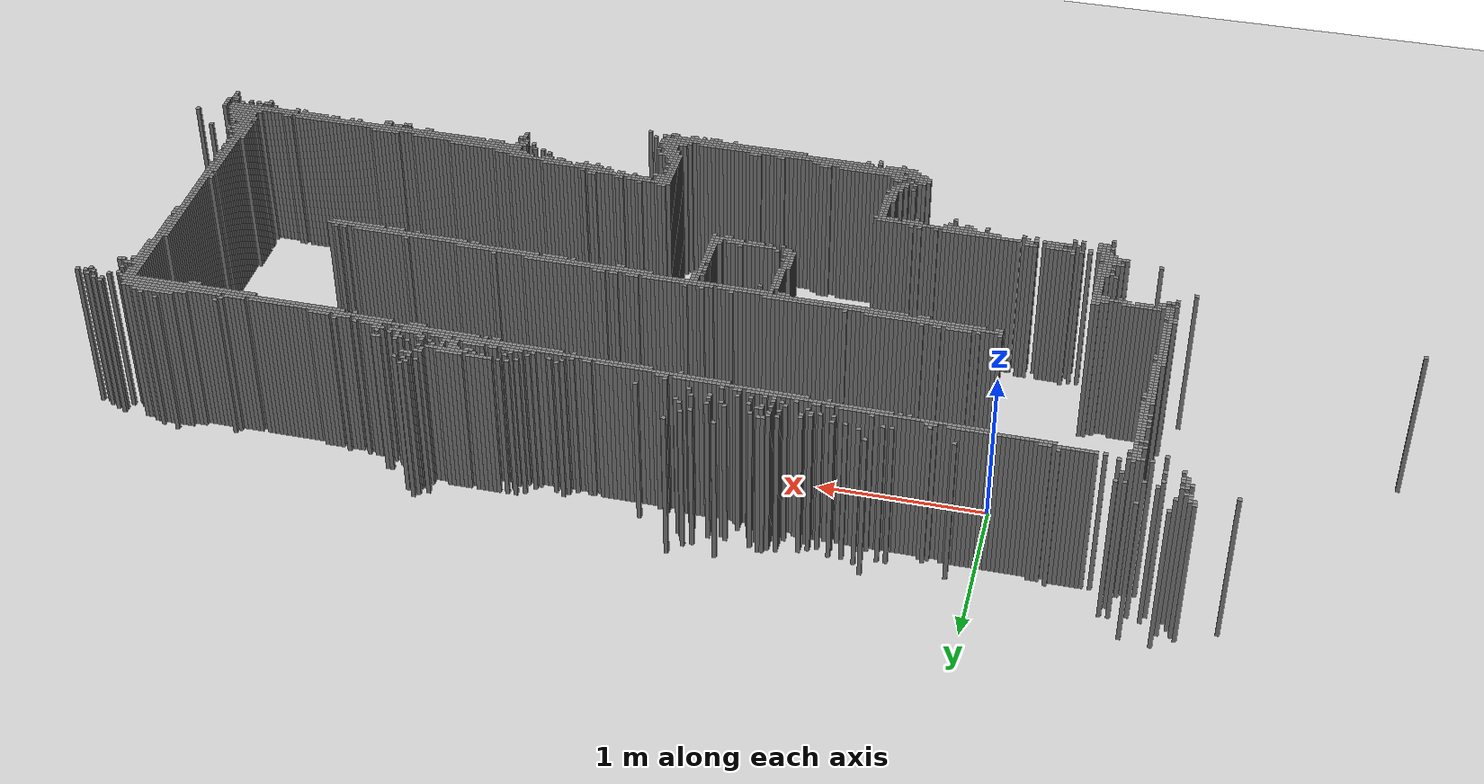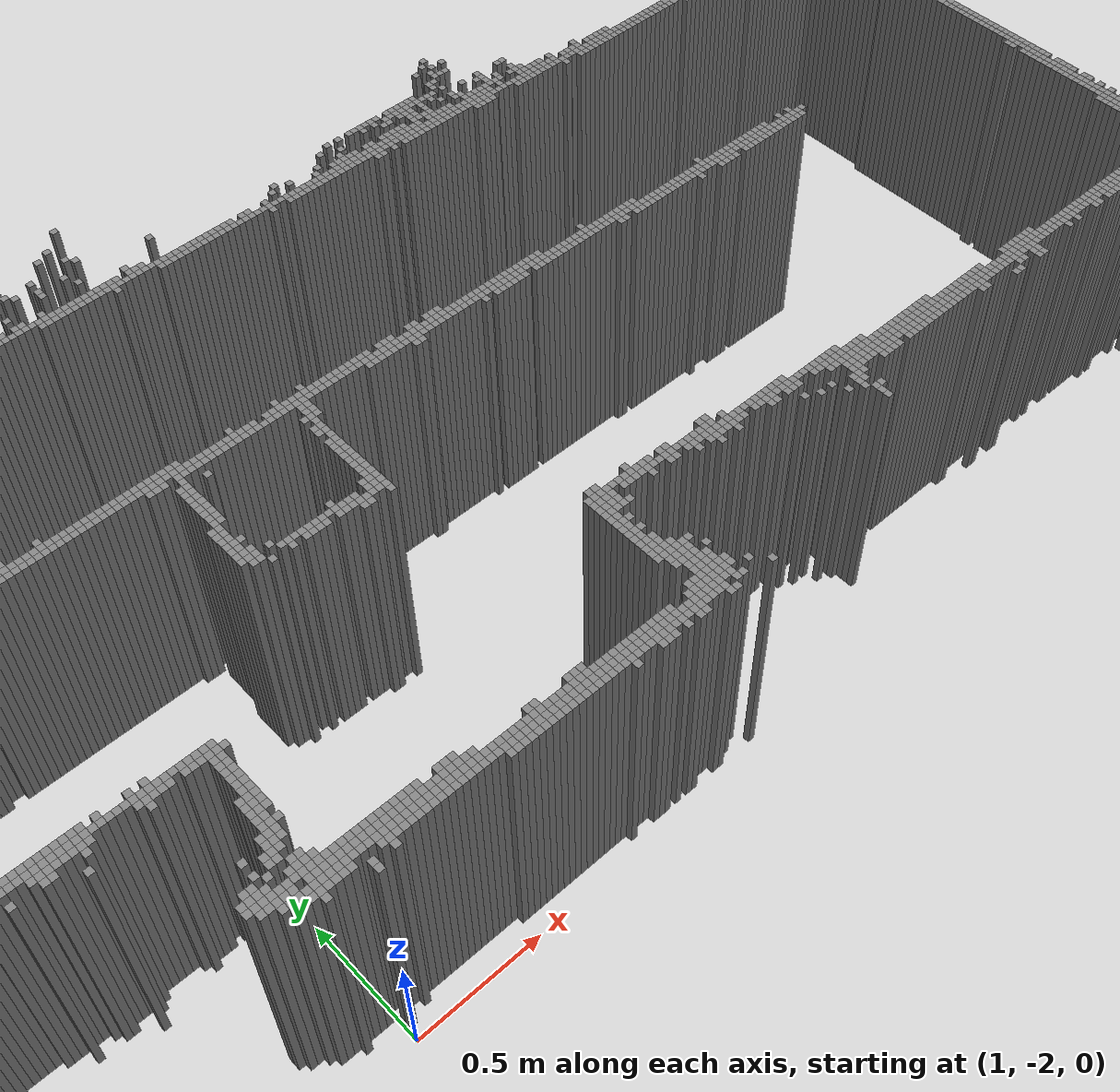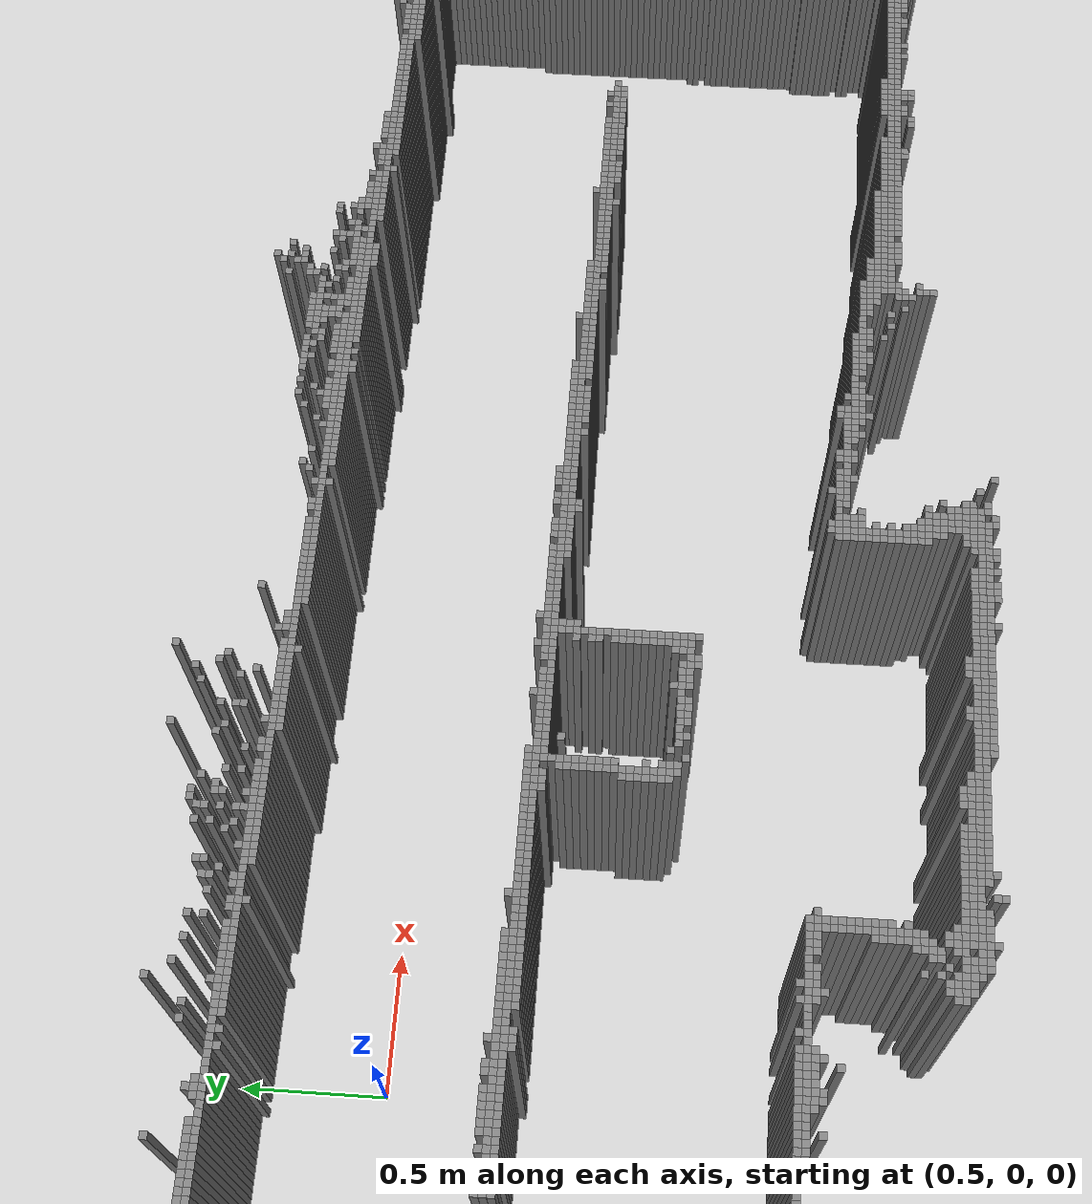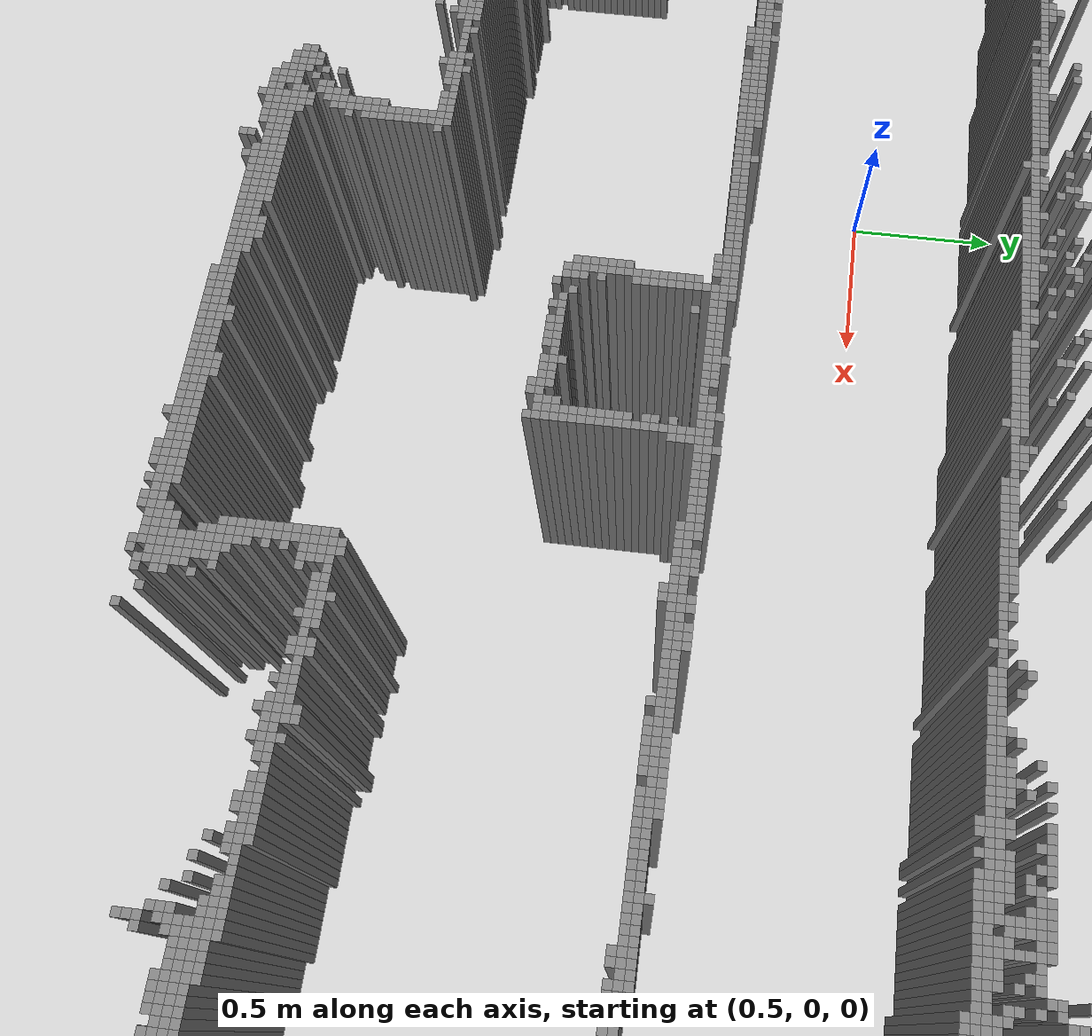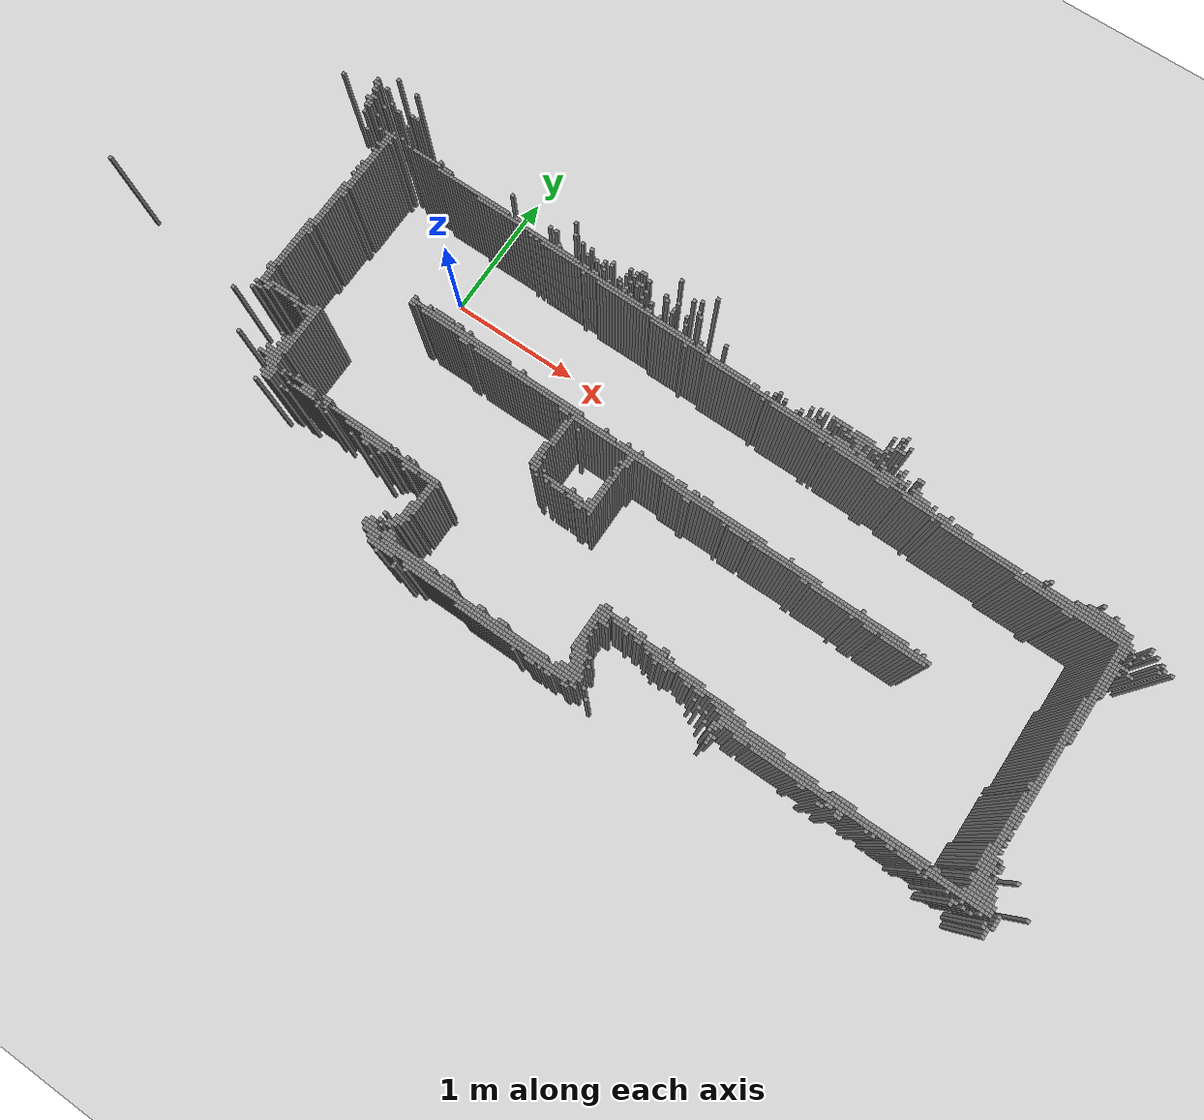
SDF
<?xml version="1.0"?>
<sdf version="1.6">
  <world name="map_world">
    <include>
      <uri>model://ground_plane</uri>
    </include>
    <include>
      <uri>model://sun</uri>
    </include>

    <model name="obs_52_15">
      <static>true</static>
      <link name="link">
        <collision name="collision">
          <geometry>
            <box>
              <size>0.025 0.025 1.0</size>
            </box>
          </geometry>
        </collision>
        <visual name="visual">
          <geometry>
            <box>
              <size>0.025 0.025 1.0</size>
            </box>
          </geometry>
          <material>
            <ambient>0.5 0.5 0.5 1</ambient>
          </material>
        </visual>
      </link>
      <pose>-1.026235 0.8559290000000002 0.5 0 0 0</pose>
    </model>

    <model name="obs_59_16">
      <static>true</static>
      <link name="link">
        <collision name="collision">
          <geometry>
            <box>
              <size>0.025 0.025 1.0</size>
            </box>
          </geometry>
        </collision>
        <visual name="visual">
          <geometry>
            <box>
              <size>0.025 0.025 1.0</size>
            </box>
          </geometry>
          <material>
            <ambient>0.5 0.5 0.5 1</ambient>
          </material>
        </visual>
      </link>
      <pose>-0.851235 0.8309290000000003 0.5 0 0 0</pose>
    </model>

    <model name="obs_47_18">
      <static>true</static>
      <link name="link">
        <collision name="collision">
          <geometry>
            <box>
              <size>0.025 0.025 1.0</size>
            </box>
          </geometry>
        </collision>
        <visual name="visual">
          <geometry>
            <box>
              <size>0.025 0.025 1.0</size>
            </box>
          </geometry>
          <material>
            <ambient>0.5 0.5 0.5 1</ambient>
          </material>
        </visual>
      </link>
      <pose>-1.151235 0.7809290000000004 0.5 0 0 0</pose>
    </model>

    <model name="obs_47_19">
      <static>true</static>
      <link name="link">
        <collision name="collision">
          <geometry>
            <box>
              <size>0.025 0.025 1.0</size>
            </box>
          </geometry>
        </collision>
        <visual name="visual">
          <geometry>
            <box>
              <size>0.025 0.025 1.0</size>
            </box>
          </geometry>
          <material>
            <ambient>0.5 0.5 0.5 1</ambient>
          </material>
        </visual>
      </link>
      <pose>-1.151235 0.7559290000000001 0.5 0 0 0</pose>
    </model>

    <model name="obs_48_19">
      <static>true</static>
      <link name="link">
        <collision name="collision">
          <geometry>
            <box>
              <size>0.025 0.025 1.0</size>
            </box>
          </geometry>
        </collision>
        <visual name="visual">
          <geometry>
            <box>
              <size>0.025 0.025 1.0</size>
            </box>
          </geometry>
          <material>
            <ambient>0.5 0.5 0.5 1</ambient>
          </material>
        </visual>
      </link>
      <pose>-1.1262349999999999 0.7559290000000001 0.5 0 0 0</pose>
    </model>

    <model name="obs_51_19">
      <static>true</static>
      <link name="link">
        <collision name="collision">
          <geometry>
            <box>
              <size>0.025 0.025 1.0</size>
            </box>
          </geometry>
        </collision>
        <visual name="visual">
          <geometry>
            <box>
              <size>0.025 0.025 1.0</size>
            </box>
          </geometry>
          <material>
            <ambient>0.5 0.5 0.5 1</ambient>
          </material>
        </visual>
      </link>
      <pose>-1.051235 0.7559290000000001 0.5 0 0 0</pose>
    </model>

    <model name="obs_48_20">
      <static>true</static>
      <link name="link">
        <collision name="collision">
          <geometry>
            <box>
              <size>0.025 0.025 1.0</size>
            </box>
          </geometry>
        </collision>
        <visual name="visual">
          <geometry>
            <box>
              <size>0.025 0.025 1.0</size>
            </box>
          </geometry>
          <material>
            <ambient>0.5 0.5 0.5 1</ambient>
          </material>
        </visual>
      </link>
      <pose>-1.1262349999999999 0.7309290000000002 0.5 0 0 0</pose>
    </model>

    <model name="obs_162_20">
      <static>true</static>
      <link name="link">
        <collision name="collision">
          <geometry>
            <box>
              <size>0.025 0.025 1.0</size>
            </box>
          </geometry>
        </collision>
        <visual name="visual">
          <geometry>
            <box>
              <size>0.025 0.025 1.0</size>
            </box>
          </geometry>
          <material>
            <ambient>0.5 0.5 0.5 1</ambient>
          </material>
        </visual>
      </link>
      <pose>1.7237649999999998 0.7309290000000002 0.5 0 0 0</pose>
    </model>

    <model name="obs_48_21">
      <static>true</static>
      <link name="link">
        <collision name="collision">
          <geometry>
            <box>
              <size>0.025 0.025 1.0</size>
            </box>
          </geometry>
        </collision>
        <visual name="visual">
          <geometry>
            <box>
              <size>0.025 0.025 1.0</size>
            </box>
          </geometry>
          <material>
            <ambient>0.5 0.5 0.5 1</ambient>
          </material>
        </visual>
      </link>
      <pose>-1.1262349999999999 0.7059290000000003 0.5 0 0 0</pose>
    </model>

    <model name="obs_49_21">
      <static>true</static>
      <link name="link">
        <collision name="collision">
          <geometry>
            <box>
              <size>0.025 0.025 1.0</size>
            </box>
          </geometry>
        </collision>
        <visual name="visual">
          <geometry>
            <box>
              <size>0.025 0.025 1.0</size>
            </box>
          </geometry>
          <material>
            <ambient>0.5 0.5 0.5 1</ambient>
          </material>
        </visual>
      </link>
      <pose>-1.101235 0.7059290000000003 0.5 0 0 0</pose>
    </model>

    <model name="obs_151_21">
      <static>true</static>
      <link name="link">
        <collision name="collision">
          <geometry>
            <box>
              <size>0.025 0.025 1.0</size>
            </box>
          </geometry>
        </collision>
        <visual name="visual">
          <geometry>
            <box>
              <size>0.025 0.025 1.0</size>
            </box>
          </geometry>
          <material>
            <ambient>0.5 0.5 0.5 1</ambient>
          </material>
        </visual>
      </link>
      <pose>1.4487650000000003 0.7059290000000003 0.5 0 0 0</pose>
    </model>

    <model name="obs_38_22">
      <static>true</static>
      <link name="link">
        <collision name="collision">
          <geometry>
            <box>
              <size>0.025 0.025 1.0</size>
            </box>
          </geometry>
        </collision>
        <visual name="visual">
          <geometry>
            <box>
              <size>0.025 0.025 1.0</size>
            </box>
          </geometry>
          <material>
            <ambient>0.5 0.5 0.5 1</ambient>
          </material>
        </visual>
      </link>
      <pose>-1.3762349999999999 0.6809290000000003 0.5 0 0 0</pose>
    </model>

    <model name="obs_55_22">
      <static>true</static>
      <link name="link">
        <collision name="collision">
          <geometry>
            <box>
              <size>0.025 0.025 1.0</size>
            </box>
          </geometry>
        </collision>
        <visual name="visual">
          <geometry>
            <box>
              <size>0.025 0.025 1.0</size>
            </box>
          </geometry>
          <material>
            <ambient>0.5 0.5 0.5 1</ambient>
          </material>
        </visual>
      </link>
      <pose>-0.951235 0.6809290000000003 0.5 0 0 0</pose>
    </model>

    <model name="obs_62_22">
      <static>true</static>
      <link name="link">
        <collision name="collision">
          <geometry>
            <box>
              <size>0.025 0.025 1.0</size>
            </box>
          </geometry>
        </collision>
        <visual name="visual">
          <geometry>
            <box>
              <size>0.025 0.025 1.0</size>
            </box>
          </geometry>
          <material>
            <ambient>0.5 0.5 0.5 1</ambient>
          </material>
        </visual>
      </link>
      <pose>-0.776235 0.6809290000000003 0.5 0 0 0</pose>
    </model>

    <model name="obs_64_22">
      <static>true</static>
      <link name="link">
        <collision name="collision">
          <geometry>
            <box>
              <size>0.025 0.025 1.0</size>
            </box>
          </geometry>
        </collision>
        <visual name="visual">
          <geometry>
            <box>
              <size>0.025 0.025 1.0</size>
            </box>
          </geometry>
          <material>
            <ambient>0.5 0.5 0.5 1</ambient>
          </material>
        </visual>
      </link>
      <pose>-0.726235 0.6809290000000003 0.5 0 0 0</pose>
    </model>

    <model name="obs_49_23">
      <static>true</static>
      <link name="link">
        <collision name="collision">
          <geometry>
            <box>
              <size>0.025 0.025 1.0</size>
            </box>
          </geometry>
        </collision>
        <visual name="visual">
          <geometry>
            <box>
              <size>0.025 0.025 1.0</size>
            </box>
          </geometry>
          <material>
            <ambient>0.5 0.5 0.5 1</ambient>
          </material>
        </visual>
      </link>
      <pose>-1.101235 0.6559290000000004 0.5 0 0 0</pose>
    </model>

    <model name="obs_50_23">
      <static>true</static>
      <link name="link">
        <collision name="collision">
          <geometry>
            <box>
              <size>0.025 0.025 1.0</size>
            </box>
          </geometry>
        </collision>
        <visual name="visual">
          <geometry>
            <box>
              <size>0.025 0.025 1.0</size>
            </box>
          </geometry>
          <material>
            <ambient>0.5 0.5 0.5 1</ambient>
          </material>
        </visual>
      </link>
      <pose>-1.076235 0.6559290000000004 0.5 0 0 0</pose>
    </model>

    <model name="obs_58_23">
      <static>true</static>
      <link name="link">
        <collision name="collision">
          <geometry>
            <box>
              <size>0.025 0.025 1.0</size>
            </box>
          </geometry>
        </collision>
        <visual name="visual">
          <geometry>
            <box>
              <size>0.025 0.025 1.0</size>
            </box>
          </geometry>
          <material>
            <ambient>0.5 0.5 0.5 1</ambient>
          </material>
        </visual>
      </link>
      <pose>-0.8762349999999999 0.6559290000000004 0.5 0 0 0</pose>
    </model>

    <model name="obs_118_23">
      <static>true</static>
      <link name="link">
        <collision name="collision">
          <geometry>
            <box>
              <size>0.025 0.025 1.0</size>
            </box>
          </geometry>
        </collision>
        <visual name="visual">
          <geometry>
            <box>
              <size>0.025 0.025 1.0</size>
            </box>
          </geometry>
          <material>
            <ambient>0.5 0.5 0.5 1</ambient>
          </material>
        </visual>
      </link>
      <pose>0.6237650000000001 0.6559290000000004 0.5 0 0 0</pose>
    </model>

    <model name="obs_159_23">
      <static>true</static>
      <link name="link">
        <collision name="collision">
          <geometry>
            <box>
              <size>0.025 0.025 1.0</size>
            </box>
          </geometry>
        </collision>
        <visual name="visual">
          <geometry>
            <box>
              <size>0.025 0.025 1.0</size>
            </box>
          </geometry>
          <material>
            <ambient>0.5 0.5 0.5 1</ambient>
          </material>
        </visual>
      </link>
      <pose>1.648765 0.6559290000000004 0.5 0 0 0</pose>
    </model>

    <model name="obs_48_24">
      <static>true</static>
      <link name="link">
        <collision name="collision">
          <geometry>
            <box>
              <size>0.025 0.025 1.0</size>
            </box>
          </geometry>
        </collision>
        <visual name="visual">
          <geometry>
            <box>
              <size>0.025 0.025 1.0</size>
            </box>
          </geometry>
          <material>
            <ambient>0.5 0.5 0.5 1</ambient>
          </material>
        </visual>
      </link>
      <pose>-1.1262349999999999 0.6309290000000001 0.5 0 0 0</pose>
    </model>

    <model name="obs_49_24">
      <static>true</static>
      <link name="link">
        <collision name="collision">
          <geometry>
            <box>
              <size>0.025 0.025 1.0</size>
            </box>
          </geometry>
        </collision>
        <visual name="visual">
          <geometry>
            <box>
              <size>0.025 0.025 1.0</size>
            </box>
          </geometry>
          <material>
            <ambient>0.5 0.5 0.5 1</ambient>
          </material>
        </visual>
      </link>
      <pose>-1.101235 0.6309290000000001 0.5 0 0 0</pose>
    </model>

    <model name="obs_54_24">
      <static>true</static>
      <link name="link">
        <collision name="collision">
          <geometry>
            <box>
              <size>0.025 0.025 1.0</size>
            </box>
          </geometry>
        </collision>
        <visual name="visual">
          <geometry>
            <box>
              <size>0.025 0.025 1.0</size>
            </box>
          </geometry>
          <material>
            <ambient>0.5 0.5 0.5 1</ambient>
          </material>
        </visual>
      </link>
      <pose>-0.976235 0.6309290000000001 0.5 0 0 0</pose>
    </model>

    <model name="obs_157_24">
      <static>true</static>
      <link name="link">
        <collision name="collision">
          <geometry>
            <box>
              <size>0.025 0.025 1.0</size>
            </box>
          </geometry>
        </collision>
        <visual name="visual">
          <geometry>
            <box>
              <size>0.025 0.025 1.0</size>
            </box>
          </geometry>
          <material>
            <ambient>0.5 0.5 0.5 1</ambient>
          </material>
        </visual>
      </link>
      <pose>1.5987650000000002 0.6309290000000001 0.5 0 0 0</pose>
    </model>

    <model name="obs_49_25">
      <static>true</static>
      <link name="link">
        <collision name="collision">
          <geometry>
            <box>
              <size>0.025 0.025 1.0</size>
            </box>
          </geometry>
        </collision>
        <visual name="visual">
          <geometry>
            <box>
              <size>0.025 0.025 1.0</size>
            </box>
          </geometry>
          <material>
            <ambient>0.5 0.5 0.5 1</ambient>
          </material>
        </visual>
      </link>
      <pose>-1.101235 0.6059290000000002 0.5 0 0 0</pose>
    </model>

    <model name="obs_50_25">
      <static>true</static>
      <link name="link">
        <collision name="collision">
          <geometry>
            <box>
              <size>0.025 0.025 1.0</size>
            </box>
          </geometry>
        </collision>
        <visual name="visual">
          <geometry>
            <box>
              <size>0.025 0.025 1.0</size>
            </box>
          </geometry>
          <material>
            <ambient>0.5 0.5 0.5 1</ambient>
          </material>
        </visual>
      </link>
      <pose>-1.076235 0.6059290000000002 0.5 0 0 0</pose>
    </model>

    <model name="obs_63_25">
      <static>true</static>
      <link name="link">
        <collision name="collision">
          <geometry>
            <box>
              <size>0.025 0.025 1.0</size>
            </box>
          </geometry>
        </collision>
        <visual name="visual">
          <geometry>
            <box>
              <size>0.025 0.025 1.0</size>
            </box>
          </geometry>
          <material>
            <ambient>0.5 0.5 0.5 1</ambient>
          </material>
        </visual>
      </link>
      <pose>-0.7512349999999999 0.6059290000000002 0.5 0 0 0</pose>
    </model>

    <model name="obs_141_25">
      <static>true</static>
      <link name="link">
        <collision name="collision">
          <geometry>
            <box>
              <size>0.025 0.025 1.0</size>
            </box>
          </geometry>
        </collision>
        <visual name="visual">
          <geometry>
            <box>
              <size>0.025 0.025 1.0</size>
            </box>
          </geometry>
          <material>
            <ambient>0.5 0.5 0.5 1</ambient>
          </material>
        </visual>
      </link>
      <pose>1.1987650000000003 0.6059290000000002 0.5 0 0 0</pose>
    </model>

    <model name="obs_142_25">
      <static>true</static>
      <link name="link">
        <collision name="collision">
          <geometry>
            <box>
              <size>0.025 0.025 1.0</size>
            </box>
          </geometry>
        </collision>
        <visual name="visual">
          <geometry>
            <box>
              <size>0.025 0.025 1.0</size>
            </box>
          </geometry>
          <material>
            <ambient>0.5 0.5 0.5 1</ambient>
          </material>
        </visual>
      </link>
      <pose>1.2237650000000002 0.6059290000000002 0.5 0 0 0</pose>
    </model>

    <model name="obs_224_25">
      <static>true</static>
      <link name="link">
        <collision name="collision">
          <geometry>
            <box>
              <size>0.025 0.025 1.0</size>
            </box>
          </geometry>
        </collision>
        <visual name="visual">
          <geometry>
            <box>
              <size>0.025 0.025 1.0</size>
            </box>
          </geometry>
          <material>
            <ambient>0.5 0.5 0.5 1</ambient>
          </material>
        </visual>
      </link>
      <pose>3.2737650000000005 0.6059290000000002 0.5 0 0 0</pose>
    </model>

    <model name="obs_49_26">
      <static>true</static>
      <link name="link">
        <collision name="collision">
          <geometry>
            <box>
              <size>0.025 0.025 1.0</size>
            </box>
          </geometry>
        </collision>
        <visual name="visual">
          <geometry>
            <box>
              <size>0.025 0.025 1.0</size>
            </box>
          </geometry>
          <material>
            <ambient>0.5 0.5 0.5 1</ambient>
          </material>
        </visual>
      </link>
      <pose>-1.101235 0.5809290000000003 0.5 0 0 0</pose>
    </model>

    <model name="obs_50_26">
      <static>true</static>
      <link name="link">
        <collision name="collision">
          <geometry>
            <box>
              <size>0.025 0.025 1.0</size>
            </box>
          </geometry>
        </collision>
        <visual name="visual">
          <geometry>
            <box>
              <size>0.025 0.025 1.0</size>
            </box>
          </geometry>
          <material>
            <ambient>0.5 0.5 0.5 1</ambient>
          </material>
        </visual>
      </link>
      <pose>-1.076235 0.5809290000000003 0.5 0 0 0</pose>
    </model>

    <model name="obs_99_26">
      <static>true</static>
      <link name="link">
        <collision name="collision">
          <geometry>
            <box>
              <size>0.025 0.025 1.0</size>
            </box>
          </geometry>
        </collision>
        <visual name="visual">
          <geometry>
            <box>
              <size>0.025 0.025 1.0</size>
            </box>
          </geometry>
          <material>
            <ambient>0.5 0.5 0.5 1</ambient>
          </material>
        </visual>
      </link>
      <pose>0.14876500000000004 0.5809290000000003 0.5 0 0 0</pose>
    </model>

    <model name="obs_120_26">
      <static>true</static>
      <link name="link">
        <collision name="collision">
          <geometry>
            <box>
              <size>0.025 0.025 1.0</size>
            </box>
          </geometry>
        </collision>
        <visual name="visual">
          <geometry>
            <box>
              <size>0.025 0.025 1.0</size>
            </box>
          </geometry>
          <material>
            <ambient>0.5 0.5 0.5 1</ambient>
          </material>
        </visual>
      </link>
      <pose>0.673765 0.5809290000000003 0.5 0 0 0</pose>
    </model>

    <model name="obs_138_26">
      <static>true</static>
      <link name="link">
        <collision name="collision">
          <geometry>
            <box>
              <size>0.025 0.025 1.0</size>
            </box>
          </geometry>
        </collision>
        <visual name="visual">
          <geometry>
            <box>
              <size>0.025 0.025 1.0</size>
            </box>
          </geometry>
          <material>
            <ambient>0.5 0.5 0.5 1</ambient>
          </material>
        </visual>
      </link>
      <pose>1.1237650000000001 0.5809290000000003 0.5 0 0 0</pose>
    </model>

    <model name="obs_140_26">
      <static>true</static>
      <link name="link">
        <collision name="collision">
          <geometry>
            <box>
              <size>0.025 0.025 1.0</size>
            </box>
          </geometry>
        </collision>
        <visual name="visual">
          <geometry>
            <box>
              <size>0.025 0.025 1.0</size>
            </box>
          </geometry>
          <material>
            <ambient>0.5 0.5 0.5 1</ambient>
          </material>
        </visual>
      </link>
      <pose>1.173765 0.5809290000000003 0.5 0 0 0</pose>
    </model>

    <model name="obs_144_26">
      <static>true</static>
      <link name="link">
        <collision name="collision">
          <geometry>
            <box>
              <size>0.025 0.025 1.0</size>
            </box>
          </geometry>
        </collision>
        <visual name="visual">
          <geometry>
            <box>
              <size>0.025 0.025 1.0</size>
            </box>
          </geometry>
          <material>
            <ambient>0.5 0.5 0.5 1</ambient>
          </material>
        </visual>
      </link>
      <pose>1.273765 0.5809290000000003 0.5 0 0 0</pose>
    </model>

    <model name="obs_160_26">
      <static>true</static>
      <link name="link">
        <collision name="collision">
          <geometry>
            <box>
              <size>0.025 0.025 1.0</size>
            </box>
          </geometry>
        </collision>
        <visual name="visual">
          <geometry>
            <box>
              <size>0.025 0.025 1.0</size>
            </box>
          </geometry>
          <material>
            <ambient>0.5 0.5 0.5 1</ambient>
          </material>
        </visual>
      </link>
      <pose>1.673765 0.5809290000000003 0.5 0 0 0</pose>
    </model>

    <model name="obs_223_26">
      <static>true</static>
      <link name="link">
        <collision name="collision">
          <geometry>
            <box>
              <size>0.025 0.025 1.0</size>
            </box>
          </geometry>
        </collision>
        <visual name="visual">
          <geometry>
            <box>
              <size>0.025 0.025 1.0</size>
            </box>
          </geometry>
          <material>
            <ambient>0.5 0.5 0.5 1</ambient>
          </material>
        </visual>
      </link>
      <pose>3.248765 0.5809290000000003 0.5 0 0 0</pose>
    </model>

    <model name="obs_54_27">
      <static>true</static>
      <link name="link">
        <collision name="collision">
          <geometry>
            <box>
              <size>0.025 0.025 1.0</size>
            </box>
          </geometry>
        </collision>
        <visual name="visual">
          <geometry>
            <box>
              <size>0.025 0.025 1.0</size>
            </box>
          </geometry>
          <material>
            <ambient>0.5 0.5 0.5 1</ambient>
          </material>
        </visual>
      </link>
      <pose>-0.976235 0.5559290000000003 0.5 0 0 0</pose>
    </model>

    <model name="obs_123_27">
      <static>true</static>
      <link name="link">
        <collision name="collision">
          <geometry>
            <box>
              <size>0.025 0.025 1.0</size>
            </box>
          </geometry>
        </collision>
        <visual name="visual">
          <geometry>
            <box>
              <size>0.025 0.025 1.0</size>
            </box>
          </geometry>
          <material>
            <ambient>0.5 0.5 0.5 1</ambient>
          </material>
        </visual>
      </link>
      <pose>0.7487650000000001 0.5559290000000003 0.5 0 0 0</pose>
    </model>

    <model name="obs_126_27">
      <static>true</static>
      <link name="link">
        <collision name="collision">
          <geometry>
            <box>
              <size>0.025 0.025 1.0</size>
            </box>
          </geometry>
        </collision>
        <visual name="visual">
          <geometry>
            <box>
              <size>0.025 0.025 1.0</size>
            </box>
          </geometry>
          <material>
            <ambient>0.5 0.5 0.5 1</ambient>
          </material>
        </visual>
      </link>
      <pose>0.8237650000000003 0.5559290000000003 0.5 0 0 0</pose>
    </model>

    <model name="obs_133_27">
      <static>true</static>
      <link name="link">
        <collision name="collision">
          <geometry>
            <box>
              <size>0.025 0.025 1.0</size>
            </box>
          </geometry>
        </collision>
        <visual name="visual">
          <geometry>
            <box>
              <size>0.025 0.025 1.0</size>
            </box>
          </geometry>
          <material>
            <ambient>0.5 0.5 0.5 1</ambient>
          </material>
        </visual>
      </link>
      <pose>0.9987650000000001 0.5559290000000003 0.5 0 0 0</pose>
    </model>

    <model name="obs_140_27">
      <static>true</static>
      <link name="link">
        <collision name="collision">
          <geometry>
            <box>
              <size>0.025 0.025 1.0</size>
            </box>
          </geometry>
        </collision>
        <visual name="visual">
          <geometry>
            <box>
              <size>0.025 0.025 1.0</size>
            </box>
          </geometry>
          <material>
            <ambient>0.5 0.5 0.5 1</ambient>
          </material>
        </visual>
      </link>
      <pose>1.173765 0.5559290000000003 0.5 0 0 0</pose>
    </model>

    <model name="obs_150_27">
      <static>true</static>
      <link name="link">
        <collision name="collision">
          <geometry>
            <box>
              <size>0.025 0.025 1.0</size>
            </box>
          </geometry>
        </collision>
        <visual name="visual">
          <geometry>
            <box>
              <size>0.025 0.025 1.0</size>
            </box>
          </geometry>
          <material>
            <ambient>0.5 0.5 0.5 1</ambient>
          </material>
        </visual>
      </link>
      <pose>1.423765 0.5559290000000003 0.5 0 0 0</pose>
    </model>

    <model name="obs_154_27">
      <static>true</static>
      <link name="link">
        <collision name="collision">
          <geometry>
            <box>
              <size>0.025 0.025 1.0</size>
            </box>
          </geometry>
        </collision>
        <visual name="visual">
          <geometry>
            <box>
              <size>0.025 0.025 1.0</size>
            </box>
          </geometry>
          <material>
            <ambient>0.5 0.5 0.5 1</ambient>
          </material>
        </visual>
      </link>
      <pose>1.523765 0.5559290000000003 0.5 0 0 0</pose>
    </model>

    <model name="obs_161_27">
      <static>true</static>
      <link name="link">
        <collision name="collision">
          <geometry>
            <box>
              <size>0.025 0.025 1.0</size>
            </box>
          </geometry>
        </collision>
        <visual name="visual">
          <geometry>
            <box>
              <size>0.025 0.025 1.0</size>
            </box>
          </geometry>
          <material>
            <ambient>0.5 0.5 0.5 1</ambient>
          </material>
        </visual>
      </link>
      <pose>1.6987650000000003 0.5559290000000003 0.5 0 0 0</pose>
    </model>

    <model name="obs_221_27">
      <static>true</static>
      <link name="link">
        <collision name="collision">
          <geometry>
            <box>
              <size>0.025 0.025 1.0</size>
            </box>
          </geometry>
        </collision>
        <visual name="visual">
          <geometry>
            <box>
              <size>0.025 0.025 1.0</size>
            </box>
          </geometry>
          <material>
            <ambient>0.5 0.5 0.5 1</ambient>
          </material>
        </visual>
      </link>
      <pose>3.1987650000000003 0.5559290000000003 0.5 0 0 0</pose>
    </model>

    <model name="obs_224_27">
      <static>true</static>
      <link name="link">
        <collision name="collision">
          <geometry>
            <box>
              <size>0.025 0.025 1.0</size>
            </box>
          </geometry>
        </collision>
        <visual name="visual">
          <geometry>
            <box>
              <size>0.025 0.025 1.0</size>
            </box>
          </geometry>
          <material>
            <ambient>0.5 0.5 0.5 1</ambient>
          </material>
        </visual>
      </link>
      <pose>3.2737650000000005 0.5559290000000003 0.5 0 0 0</pose>
    </model>

    <model name="obs_226_27">
      <static>true</static>
      <link name="link">
        <collision name="collision">
          <geometry>
            <box>
              <size>0.025 0.025 1.0</size>
            </box>
          </geometry>
        </collision>
        <visual name="visual">
          <geometry>
            <box>
              <size>0.025 0.025 1.0</size>
            </box>
          </geometry>
          <material>
            <ambient>0.5 0.5 0.5 1</ambient>
          </material>
        </visual>
      </link>
      <pose>3.3237650000000003 0.5559290000000003 0.5 0 0 0</pose>
    </model>

    <model name="obs_50_28">
      <static>true</static>
      <link name="link">
        <collision name="collision">
          <geometry>
            <box>
              <size>0.025 0.025 1.0</size>
            </box>
          </geometry>
        </collision>
        <visual name="visual">
          <geometry>
            <box>
              <size>0.025 0.025 1.0</size>
            </box>
          </geometry>
          <material>
            <ambient>0.5 0.5 0.5 1</ambient>
          </material>
        </visual>
      </link>
      <pose>-1.076235 0.5309290000000004 0.5 0 0 0</pose>
    </model>

    <model name="obs_113_28">
      <static>true</static>
      <link name="link">
        <collision name="collision">
          <geometry>
            <box>
              <size>0.025 0.025 1.0</size>
            </box>
          </geometry>
        </collision>
        <visual name="visual">
          <geometry>
            <box>
              <size>0.025 0.025 1.0</size>
            </box>
          </geometry>
          <material>
            <ambient>0.5 0.5 0.5 1</ambient>
          </material>
        </visual>
      </link>
      <pose>0.4987650000000001 0.5309290000000004 0.5 0 0 0</pose>
    </model>

    <model name="obs_115_28">
      <static>true</static>
      <link name="link">
        <collision name="collision">
          <geometry>
            <box>
              <size>0.025 0.025 1.0</size>
            </box>
          </geometry>
        </collision>
        <visual name="visual">
          <geometry>
            <box>
              <size>0.025 0.025 1.0</size>
            </box>
          </geometry>
          <material>
            <ambient>0.5 0.5 0.5 1</ambient>
          </material>
        </visual>
      </link>
      <pose>0.548765 0.5309290000000004 0.5 0 0 0</pose>
    </model>

    <model name="obs_131_28">
      <static>true</static>
      <link name="link">
        <collision name="collision">
          <geometry>
            <box>
              <size>0.025 0.025 1.0</size>
            </box>
          </geometry>
        </collision>
        <visual name="visual">
          <geometry>
            <box>
              <size>0.025 0.025 1.0</size>
            </box>
          </geometry>
          <material>
            <ambient>0.5 0.5 0.5 1</ambient>
          </material>
        </visual>
      </link>
      <pose>0.9487650000000003 0.5309290000000004 0.5 0 0 0</pose>
    </model>

    <model name="obs_133_28">
      <static>true</static>
      <link name="link">
        <collision name="collision">
          <geometry>
            <box>
              <size>0.025 0.025 1.0</size>
            </box>
          </geometry>
        </collision>
        <visual name="visual">
          <geometry>
            <box>
              <size>0.025 0.025 1.0</size>
            </box>
          </geometry>
          <material>
            <ambient>0.5 0.5 0.5 1</ambient>
          </material>
        </visual>
      </link>
      <pose>0.9987650000000001 0.5309290000000004 0.5 0 0 0</pose>
    </model>

    <model name="obs_138_28">
      <static>true</static>
      <link name="link">
        <collision name="collision">
          <geometry>
            <box>
              <size>0.025 0.025 1.0</size>
            </box>
          </geometry>
        </collision>
        <visual name="visual">
          <geometry>
            <box>
              <size>0.025 0.025 1.0</size>
            </box>
          </geometry>
          <material>
            <ambient>0.5 0.5 0.5 1</ambient>
          </material>
        </visual>
      </link>
      <pose>1.1237650000000001 0.5309290000000004 0.5 0 0 0</pose>
    </model>

    <model name="obs_142_28">
      <static>true</static>
      <link name="link">
        <collision name="collision">
          <geometry>
            <box>
              <size>0.025 0.025 1.0</size>
            </box>
          </geometry>
        </collision>
        <visual name="visual">
          <geometry>
            <box>
              <size>0.025 0.025 1.0</size>
            </box>
          </geometry>
          <material>
            <ambient>0.5 0.5 0.5 1</ambient>
          </material>
        </visual>
      </link>
      <pose>1.2237650000000002 0.5309290000000004 0.5 0 0 0</pose>
    </model>

    <model name="obs_143_28">
      <static>true</static>
      <link name="link">
        <collision name="collision">
          <geometry>
            <box>
              <size>0.025 0.025 1.0</size>
            </box>
          </geometry>
        </collision>
        <visual name="visual">
          <geometry>
            <box>
              <size>0.025 0.025 1.0</size>
            </box>
          </geometry>
          <material>
            <ambient>0.5 0.5 0.5 1</ambient>
          </material>
        </visual>
      </link>
      <pose>1.2487650000000001 0.5309290000000004 0.5 0 0 0</pose>
    </model>

    <model name="obs_151_28">
      <static>true</static>
      <link name="link">
        <collision name="collision">
          <geometry>
            <box>
              <size>0.025 0.025 1.0</size>
            </box>
          </geometry>
        </collision>
        <visual name="visual">
          <geometry>
            <box>
              <size>0.025 0.025 1.0</size>
            </box>
          </geometry>
          <material>
            <ambient>0.5 0.5 0.5 1</ambient>
          </material>
        </visual>
      </link>
      <pose>1.4487650000000003 0.5309290000000004 0.5 0 0 0</pose>
    </model>

    <model name="obs_223_28">
      <static>true</static>
      <link name="link">
        <collision name="collision">
          <geometry>
            <box>
              <size>0.025 0.025 1.0</size>
            </box>
          </geometry>
        </collision>
        <visual name="visual">
          <geometry>
            <box>
              <size>0.025 0.025 1.0</size>
            </box>
          </geometry>
          <material>
            <ambient>0.5 0.5 0.5 1</ambient>
          </material>
        </visual>
      </link>
      <pose>3.248765 0.5309290000000004 0.5 0 0 0</pose>
    </model>

    <model name="obs_61_29">
      <static>true</static>
      <link name="link">
        <collision name="collision">
          <geometry>
            <box>
              <size>0.025 0.025 1.0</size>
            </box>
          </geometry>
        </collision>
        <visual name="visual">
          <geometry>
            <box>
              <size>0.025 0.025 1.0</size>
            </box>
          </geometry>
          <material>
            <ambient>0.5 0.5 0.5 1</ambient>
          </material>
        </visual>
      </link>
      <pose>-0.8012349999999999 0.5059290000000001 0.5 0 0 0</pose>
    </model>

    <model name="obs_64_29">
      <static>true</static>
      <link name="link">
        <collision name="collision">
          <geometry>
            <box>
              <size>0.025 0.025 1.0</size>
            </box>
          </geometry>
        </collision>
        <visual name="visual">
          <geometry>
            <box>
              <size>0.025 0.025 1.0</size>
            </box>
          </geometry>
          <material>
            <ambient>0.5 0.5 0.5 1</ambient>
          </material>
        </visual>
      </link>
      <pose>-0.726235 0.5059290000000001 0.5 0 0 0</pose>
    </model>

    <model name="obs_77_29">
      <static>true</static>
      <link name="link">
        <collision name="collision">
          <geometry>
            <box>
              <size>0.025 0.025 1.0</size>
            </box>
          </geometry>
        </collision>
        <visual name="visual">
          <geometry>
            <box>
              <size>0.025 0.025 1.0</size>
            </box>
          </geometry>
          <material>
            <ambient>0.5 0.5 0.5 1</ambient>
          </material>
        </visual>
      </link>
      <pose>-0.401235 0.5059290000000001 0.5 0 0 0</pose>
    </model>

    <model name="obs_126_29">
      <static>true</static>
      <link name="link">
        <collision name="collision">
          <geometry>
            <box>
              <size>0.025 0.025 1.0</size>
            </box>
          </geometry>
        </collision>
        <visual name="visual">
          <geometry>
            <box>
              <size>0.025 0.025 1.0</size>
            </box>
          </geometry>
          <material>
            <ambient>0.5 0.5 0.5 1</ambient>
          </material>
        </visual>
      </link>
      <pose>0.8237650000000003 0.5059290000000001 0.5 0 0 0</pose>
    </model>

    <model name="obs_129_29">
      <static>true</static>
      <link name="link">
        <collision name="collision">
          <geometry>
            <box>
              <size>0.025 0.025 1.0</size>
            </box>
          </geometry>
        </collision>
        <visual name="visual">
          <geometry>
            <box>
              <size>0.025 0.025 1.0</size>
            </box>
          </geometry>
          <material>
            <ambient>0.5 0.5 0.5 1</ambient>
          </material>
        </visual>
      </link>
      <pose>0.898765 0.5059290000000001 0.5 0 0 0</pose>
    </model>

    <model name="obs_131_29">
      <static>true</static>
      <link name="link">
        <collision name="collision">
          <geometry>
            <box>
              <size>0.025 0.025 1.0</size>
            </box>
          </geometry>
        </collision>
        <visual name="visual">
          <geometry>
            <box>
              <size>0.025 0.025 1.0</size>
            </box>
          </geometry>
          <material>
            <ambient>0.5 0.5 0.5 1</ambient>
          </material>
        </visual>
      </link>
      <pose>0.9487650000000003 0.5059290000000001 0.5 0 0 0</pose>
    </model>

    <model name="obs_140_29">
      <static>true</static>
      <link name="link">
        <collision name="collision">
          <geometry>
            <box>
              <size>0.025 0.025 1.0</size>
            </box>
          </geometry>
        </collision>
        <visual name="visual">
          <geometry>
            <box>
              <size>0.025 0.025 1.0</size>
            </box>
          </geometry>
          <material>
            <ambient>0.5 0.5 0.5 1</ambient>
          </material>
        </visual>
      </link>
      <pose>1.173765 0.5059290000000001 0.5 0 0 0</pose>
    </model>

    <model name="obs_142_29">
      <static>true</static>
      <link name="link">
        <collision name="collision">
          <geometry>
            <box>
              <size>0.025 0.025 1.0</size>
            </box>
          </geometry>
        </collision>
        <visual name="visual">
          <geometry>
            <box>
              <size>0.025 0.025 1.0</size>
            </box>
          </geometry>
          <material>
            <ambient>0.5 0.5 0.5 1</ambient>
          </material>
        </visual>
      </link>
      <pose>1.2237650000000002 0.5059290000000001 0.5 0 0 0</pose>
    </model>

    <model name="obs_145_29">
      <static>true</static>
      <link name="link">
        <collision name="collision">
          <geometry>
            <box>
              <size>0.025 0.025 1.0</size>
            </box>
          </geometry>
        </collision>
        <visual name="visual">
          <geometry>
            <box>
              <size>0.025 0.025 1.0</size>
            </box>
          </geometry>
          <material>
            <ambient>0.5 0.5 0.5 1</ambient>
          </material>
        </visual>
      </link>
      <pose>1.298765 0.5059290000000001 0.5 0 0 0</pose>
    </model>

    <model name="obs_154_29">
      <static>true</static>
      <link name="link">
        <collision name="collision">
          <geometry>
            <box>
              <size>0.025 0.025 1.0</size>
            </box>
          </geometry>
        </collision>
        <visual name="visual">
          <geometry>
            <box>
              <size>0.025 0.025 1.0</size>
            </box>
          </geometry>
          <material>
            <ambient>0.5 0.5 0.5 1</ambient>
          </material>
        </visual>
      </link>
      <pose>1.523765 0.5059290000000001 0.5 0 0 0</pose>
    </model>

    <model name="obs_158_29">
      <static>true</static>
      <link name="link">
        <collision name="collision">
          <geometry>
            <box>
              <size>0.025 0.025 1.0</size>
            </box>
          </geometry>
        </collision>
        <visual name="visual">
          <geometry>
            <box>
              <size>0.025 0.025 1.0</size>
            </box>
          </geometry>
          <material>
            <ambient>0.5 0.5 0.5 1</ambient>
          </material>
        </visual>
      </link>
      <pose>1.6237650000000001 0.5059290000000001 0.5 0 0 0</pose>
    </model>

    <model name="obs_223_29">
      <static>true</static>
      <link name="link">
        <collision name="collision">
          <geometry>
            <box>
              <size>0.025 0.025 1.0</size>
            </box>
          </geometry>
        </collision>
        <visual name="visual">
          <geometry>
            <box>
              <size>0.025 0.025 1.0</size>
            </box>
          </geometry>
          <material>
            <ambient>0.5 0.5 0.5 1</ambient>
          </material>
        </visual>
      </link>
      <pose>3.248765 0.5059290000000001 0.5 0 0 0</pose>
    </model>

    <model name="obs_224_29">
      <static>true</static>
      <link name="link">
        <collision name="collision">
          <geometry>
            <box>
              <size>0.025 0.025 1.0</size>
            </box>
          </geometry>
        </collision>
        <visual name="visual">
          <geometry>
            <box>
              <size>0.025 0.025 1.0</size>
            </box>
          </geometry>
          <material>
            <ambient>0.5 0.5 0.5 1</ambient>
          </material>
        </visual>
      </link>
      <pose>3.2737650000000005 0.5059290000000001 0.5 0 0 0</pose>
    </model>

    <model name="obs_225_29">
      <static>true</static>
      <link name="link">
        <collision name="collision">
          <geometry>
            <box>
              <size>0.025 0.025 1.0</size>
            </box>
          </geometry>
        </collision>
        <visual name="visual">
          <geometry>
            <box>
              <size>0.025 0.025 1.0</size>
            </box>
          </geometry>
          <material>
            <ambient>0.5 0.5 0.5 1</ambient>
          </material>
        </visual>
      </link>
      <pose>3.298765 0.5059290000000001 0.5 0 0 0</pose>
    </model>

    <model name="obs_57_30">
      <static>true</static>
      <link name="link">
        <collision name="collision">
          <geometry>
            <box>
              <size>0.025 0.025 1.0</size>
            </box>
          </geometry>
        </collision>
        <visual name="visual">
          <geometry>
            <box>
              <size>0.025 0.025 1.0</size>
            </box>
          </geometry>
          <material>
            <ambient>0.5 0.5 0.5 1</ambient>
          </material>
        </visual>
      </link>
      <pose>-0.901235 0.48092900000000016 0.5 0 0 0</pose>
    </model>

    <model name="obs_59_30">
      <static>true</static>
      <link name="link">
        <collision name="collision">
          <geometry>
            <box>
              <size>0.025 0.025 1.0</size>
            </box>
          </geometry>
        </collision>
        <visual name="visual">
          <geometry>
            <box>
              <size>0.025 0.025 1.0</size>
            </box>
          </geometry>
          <material>
            <ambient>0.5 0.5 0.5 1</ambient>
          </material>
        </visual>
      </link>
      <pose>-0.851235 0.48092900000000016 0.5 0 0 0</pose>
    </model>

    <model name="obs_60_30">
      <static>true</static>
      <link name="link">
        <collision name="collision">
          <geometry>
            <box>
              <size>0.025 0.025 1.0</size>
            </box>
          </geometry>
        </collision>
        <visual name="visual">
          <geometry>
            <box>
              <size>0.025 0.025 1.0</size>
            </box>
          </geometry>
          <material>
            <ambient>0.5 0.5 0.5 1</ambient>
          </material>
        </visual>
      </link>
      <pose>-0.826235 0.48092900000000016 0.5 0 0 0</pose>
    </model>

    <model name="obs_61_30">
      <static>true</static>
      <link name="link">
        <collision name="collision">
          <geometry>
            <box>
              <size>0.025 0.025 1.0</size>
            </box>
          </geometry>
        </collision>
        <visual name="visual">
          <geometry>
            <box>
              <size>0.025 0.025 1.0</size>
            </box>
          </geometry>
          <material>
            <ambient>0.5 0.5 0.5 1</ambient>
          </material>
        </visual>
      </link>
      <pose>-0.8012349999999999 0.48092900000000016 0.5 0 0 0</pose>
    </model>

    <model name="obs_62_30">
      <static>true</static>
      <link name="link">
        <collision name="collision">
          <geometry>
            <box>
              <size>0.025 0.025 1.0</size>
            </box>
          </geometry>
        </collision>
        <visual name="visual">
          <geometry>
            <box>
              <size>0.025 0.025 1.0</size>
            </box>
          </geometry>
          <material>
            <ambient>0.5 0.5 0.5 1</ambient>
          </material>
        </visual>
      </link>
      <pose>-0.776235 0.48092900000000016 0.5 0 0 0</pose>
    </model>

    <model name="obs_67_30">
      <static>true</static>
      <link name="link">
        <collision name="collision">
          <geometry>
            <box>
              <size>0.025 0.025 1.0</size>
            </box>
          </geometry>
        </collision>
        <visual name="visual">
          <geometry>
            <box>
              <size>0.025 0.025 1.0</size>
            </box>
          </geometry>
          <material>
            <ambient>0.5 0.5 0.5 1</ambient>
          </material>
        </visual>
      </link>
      <pose>-0.651235 0.48092900000000016 0.5 0 0 0</pose>
    </model>

    <model name="obs_69_30">
      <static>true</static>
      <link name="link">
        <collision name="collision">
          <geometry>
            <box>
              <size>0.025 0.025 1.0</size>
            </box>
          </geometry>
        </collision>
        <visual name="visual">
          <geometry>
            <box>
              <size>0.025 0.025 1.0</size>
            </box>
          </geometry>
          <material>
            <ambient>0.5 0.5 0.5 1</ambient>
          </material>
        </visual>
      </link>
      <pose>-0.601235 0.48092900000000016 0.5 0 0 0</pose>
    </model>

    <model name="obs_70_30">
      <static>true</static>
      <link name="link">
        <collision name="collision">
          <geometry>
            <box>
              <size>0.025 0.025 1.0</size>
            </box>
          </geometry>
        </collision>
        <visual name="visual">
          <geometry>
            <box>
              <size>0.025 0.025 1.0</size>
            </box>
          </geometry>
          <material>
            <ambient>0.5 0.5 0.5 1</ambient>
          </material>
        </visual>
      </link>
      <pose>-0.576235 0.48092900000000016 0.5 0 0 0</pose>
    </model>

    <model name="obs_71_30">
      <static>true</static>
      <link name="link">
        <collision name="collision">
          <geometry>
            <box>
              <size>0.025 0.025 1.0</size>
            </box>
          </geometry>
        </collision>
        <visual name="visual">
          <geometry>
            <box>
              <size>0.025 0.025 1.0</size>
            </box>
          </geometry>
          <material>
            <ambient>0.5 0.5 0.5 1</ambient>
          </material>
        </visual>
      </link>
      <pose>-0.5512349999999999 0.48092900000000016 0.5 0 0 0</pose>
    </model>

    <model name="obs_72_30">
      <static>true</static>
      <link name="link">
        <collision name="collision">
          <geometry>
            <box>
              <size>0.025 0.025 1.0</size>
            </box>
          </geometry>
        </collision>
        <visual name="visual">
          <geometry>
            <box>
              <size>0.025 0.025 1.0</size>
            </box>
          </geometry>
          <material>
            <ambient>0.5 0.5 0.5 1</ambient>
          </material>
        </visual>
      </link>
      <pose>-0.526235 0.48092900000000016 0.5 0 0 0</pose>
    </model>

    <model name="obs_73_30">
      <static>true</static>
      <link name="link">
        <collision name="collision">
          <geometry>
            <box>
              <size>0.025 0.025 1.0</size>
            </box>
          </geometry>
        </collision>
        <visual name="visual">
          <geometry>
            <box>
              <size>0.025 0.025 1.0</size>
            </box>
          </geometry>
          <material>
            <ambient>0.5 0.5 0.5 1</ambient>
          </material>
        </visual>
      </link>
      <pose>-0.5012349999999999 0.48092900000000016 0.5 0 0 0</pose>
    </model>

    <model name="obs_74_30">
      <static>true</static>
      <link name="link">
        <collision name="collision">
          <geometry>
            <box>
              <size>0.025 0.025 1.0</size>
            </box>
          </geometry>
        </collision>
        <visual name="visual">
          <geometry>
            <box>
              <size>0.025 0.025 1.0</size>
            </box>
          </geometry>
          <material>
            <ambient>0.5 0.5 0.5 1</ambient>
          </material>
        </visual>
      </link>
      <pose>-0.47623499999999996 0.48092900000000016 0.5 0 0 0</pose>
    </model>

    <model name="obs_75_30">
      <static>true</static>
      <link name="link">
        <collision name="collision">
          <geometry>
            <box>
              <size>0.025 0.025 1.0</size>
            </box>
          </geometry>
        </collision>
        <visual name="visual">
          <geometry>
            <box>
              <size>0.025 0.025 1.0</size>
            </box>
          </geometry>
          <material>
            <ambient>0.5 0.5 0.5 1</ambient>
          </material>
        </visual>
      </link>
      <pose>-0.45123500000000005 0.48092900000000016 0.5 0 0 0</pose>
    </model>

    <model name="obs_76_30">
      <static>true</static>
      <link name="link">
        <collision name="collision">
          <geometry>
            <box>
              <size>0.025 0.025 1.0</size>
            </box>
          </geometry>
        </collision>
        <visual name="visual">
          <geometry>
            <box>
              <size>0.025 0.025 1.0</size>
            </box>
          </geometry>
          <material>
            <ambient>0.5 0.5 0.5 1</ambient>
          </material>
        </visual>
      </link>
      <pose>-0.4262349999999999 0.48092900000000016 0.5 0 0 0</pose>
    </model>

    <model name="obs_77_30">
      <static>true</static>
      <link name="link">
        <collision name="collision">
          <geometry>
            <box>
              <size>0.025 0.025 1.0</size>
            </box>
          </geometry>
        </collision>
        <visual name="visual">
          <geometry>
            <box>
              <size>0.025 0.025 1.0</size>
            </box>
          </geometry>
          <material>
            <ambient>0.5 0.5 0.5 1</ambient>
          </material>
        </visual>
      </link>
      <pose>-0.401235 0.48092900000000016 0.5 0 0 0</pose>
    </model>

    <model name="obs_79_30">
      <static>true</static>
      <link name="link">
        <collision name="collision">
          <geometry>
            <box>
              <size>0.025 0.025 1.0</size>
            </box>
          </geometry>
        </collision>
        <visual name="visual">
          <geometry>
            <box>
              <size>0.025 0.025 1.0</size>
            </box>
          </geometry>
          <material>
            <ambient>0.5 0.5 0.5 1</ambient>
          </material>
        </visual>
      </link>
      <pose>-0.35123499999999996 0.48092900000000016 0.5 0 0 0</pose>
    </model>

    <model name="obs_80_30">
      <static>true</static>
      <link name="link">
        <collision name="collision">
          <geometry>
            <box>
              <size>0.025 0.025 1.0</size>
            </box>
          </geometry>
        </collision>
        <visual name="visual">
          <geometry>
            <box>
              <size>0.025 0.025 1.0</size>
            </box>
          </geometry>
          <material>
            <ambient>0.5 0.5 0.5 1</ambient>
          </material>
        </visual>
      </link>
      <pose>-0.32623500000000005 0.48092900000000016 0.5 0 0 0</pose>
    </model>

    <model name="obs_81_30">
      <static>true</static>
      <link name="link">
        <collision name="collision">
          <geometry>
            <box>
              <size>0.025 0.025 1.0</size>
            </box>
          </geometry>
        </collision>
        <visual name="visual">
          <geometry>
            <box>
              <size>0.025 0.025 1.0</size>
            </box>
          </geometry>
          <material>
            <ambient>0.5 0.5 0.5 1</ambient>
          </material>
        </visual>
      </link>
      <pose>-0.30123500000000014 0.48092900000000016 0.5 0 0 0</pose>
    </model>

    <model name="obs_105_30">
      <static>true</static>
      <link name="link">
        <collision name="collision">
          <geometry>
            <box>
              <size>0.025 0.025 1.0</size>
            </box>
          </geometry>
        </collision>
        <visual name="visual">
          <geometry>
            <box>
              <size>0.025 0.025 1.0</size>
            </box>
          </geometry>
          <material>
            <ambient>0.5 0.5 0.5 1</ambient>
          </material>
        </visual>
      </link>
      <pose>0.29876499999999995 0.48092900000000016 0.5 0 0 0</pose>
    </model>

    <model name="obs_132_30">
      <static>true</static>
      <link name="link">
        <collision name="collision">
          <geometry>
            <box>
              <size>0.025 0.025 1.0</size>
            </box>
          </geometry>
        </collision>
        <visual name="visual">
          <geometry>
            <box>
              <size>0.025 0.025 1.0</size>
            </box>
          </geometry>
          <material>
            <ambient>0.5 0.5 0.5 1</ambient>
          </material>
        </visual>
      </link>
      <pose>0.9737650000000002 0.48092900000000016 0.5 0 0 0</pose>
    </model>

    <model name="obs_137_30">
      <static>true</static>
      <link name="link">
        <collision name="collision">
          <geometry>
            <box>
              <size>0.025 0.025 1.0</size>
            </box>
          </geometry>
        </collision>
        <visual name="visual">
          <geometry>
            <box>
              <size>0.025 0.025 1.0</size>
            </box>
          </geometry>
          <material>
            <ambient>0.5 0.5 0.5 1</ambient>
          </material>
        </visual>
      </link>
      <pose>1.0987650000000002 0.48092900000000016 0.5 0 0 0</pose>
    </model>

    <model name="obs_154_30">
      <static>true</static>
      <link name="link">
        <collision name="collision">
          <geometry>
            <box>
              <size>0.025 0.025 1.0</size>
            </box>
          </geometry>
        </collision>
        <visual name="visual">
          <geometry>
            <box>
              <size>0.025 0.025 1.0</size>
            </box>
          </geometry>
          <material>
            <ambient>0.5 0.5 0.5 1</ambient>
          </material>
        </visual>
      </link>
      <pose>1.523765 0.48092900000000016 0.5 0 0 0</pose>
    </model>

    <model name="obs_171_30">
      <static>true</static>
      <link name="link">
        <collision name="collision">
          <geometry>
            <box>
              <size>0.025 0.025 1.0</size>
            </box>
          </geometry>
        </collision>
        <visual name="visual">
          <geometry>
            <box>
              <size>0.025 0.025 1.0</size>
            </box>
          </geometry>
          <material>
            <ambient>0.5 0.5 0.5 1</ambient>
          </material>
        </visual>
      </link>
      <pose>1.9487650000000003 0.48092900000000016 0.5 0 0 0</pose>
    </model>

    <model name="obs_221_30">
      <static>true</static>
      <link name="link">
        <collision name="collision">
          <geometry>
            <box>
              <size>0.025 0.025 1.0</size>
            </box>
          </geometry>
        </collision>
        <visual name="visual">
          <geometry>
            <box>
              <size>0.025 0.025 1.0</size>
            </box>
          </geometry>
          <material>
            <ambient>0.5 0.5 0.5 1</ambient>
          </material>
        </visual>
      </link>
      <pose>3.1987650000000003 0.48092900000000016 0.5 0 0 0</pose>
    </model>

    <model name="obs_222_30">
      <static>true</static>
      <link name="link">
        <collision name="collision">
          <geometry>
            <box>
              <size>0.025 0.025 1.0</size>
            </box>
          </geometry>
        </collision>
        <visual name="visual">
          <geometry>
            <box>
              <size>0.025 0.025 1.0</size>
            </box>
          </geometry>
          <material>
            <ambient>0.5 0.5 0.5 1</ambient>
          </material>
        </visual>
      </link>
      <pose>3.2237650000000007 0.48092900000000016 0.5 0 0 0</pose>
    </model>

    <model name="obs_60_31">
      <static>true</static>
      <link name="link">
        <collision name="collision">
          <geometry>
            <box>
              <size>0.025 0.025 1.0</size>
            </box>
          </geometry>
        </collision>
        <visual name="visual">
          <geometry>
            <box>
              <size>0.025 0.025 1.0</size>
            </box>
          </geometry>
          <material>
            <ambient>0.5 0.5 0.5 1</ambient>
          </material>
        </visual>
      </link>
      <pose>-0.826235 0.45592900000000025 0.5 0 0 0</pose>
    </model>

    <model name="obs_61_31">
      <static>true</static>
      <link name="link">
        <collision name="collision">
          <geometry>
            <box>
              <size>0.025 0.025 1.0</size>
            </box>
          </geometry>
        </collision>
        <visual name="visual">
          <geometry>
            <box>
              <size>0.025 0.025 1.0</size>
            </box>
          </geometry>
          <material>
            <ambient>0.5 0.5 0.5 1</ambient>
          </material>
        </visual>
      </link>
      <pose>-0.8012349999999999 0.45592900000000025 0.5 0 0 0</pose>
    </model>

    <model name="obs_78_31">
      <static>true</static>
      <link name="link">
        <collision name="collision">
          <geometry>
            <box>
              <size>0.025 0.025 1.0</size>
            </box>
          </geometry>
        </collision>
        <visual name="visual">
          <geometry>
            <box>
              <size>0.025 0.025 1.0</size>
            </box>
          </geometry>
          <material>
            <ambient>0.5 0.5 0.5 1</ambient>
          </material>
        </visual>
      </link>
      <pose>-0.3762349999999999 0.45592900000000025 0.5 0 0 0</pose>
    </model>

    <model name="obs_79_31">
      <static>true</static>
      <link name="link">
        <collision name="collision">
          <geometry>
            <box>
              <size>0.025 0.025 1.0</size>
            </box>
          </geometry>
        </collision>
        <visual name="visual">
          <geometry>
            <box>
              <size>0.025 0.025 1.0</size>
            </box>
          </geometry>
          <material>
            <ambient>0.5 0.5 0.5 1</ambient>
          </material>
        </visual>
      </link>
      <pose>-0.35123499999999996 0.45592900000000025 0.5 0 0 0</pose>
    </model>

    <model name="obs_80_31">
      <static>true</static>
      <link name="link">
        <collision name="collision">
          <geometry>
            <box>
              <size>0.025 0.025 1.0</size>
            </box>
          </geometry>
        </collision>
        <visual name="visual">
          <geometry>
            <box>
              <size>0.025 0.025 1.0</size>
            </box>
          </geometry>
          <material>
            <ambient>0.5 0.5 0.5 1</ambient>
          </material>
        </visual>
      </link>
      <pose>-0.32623500000000005 0.45592900000000025 0.5 0 0 0</pose>
    </model>

    <model name="obs_81_31">
      <static>true</static>
      <link name="link">
        <collision name="collision">
          <geometry>
            <box>
              <size>0.025 0.025 1.0</size>
            </box>
          </geometry>
        </collision>
        <visual name="visual">
          <geometry>
            <box>
              <size>0.025 0.025 1.0</size>
            </box>
          </geometry>
          <material>
            <ambient>0.5 0.5 0.5 1</ambient>
          </material>
        </visual>
      </link>
      <pose>-0.30123500000000014 0.45592900000000025 0.5 0 0 0</pose>
    </model>

    <model name="obs_82_31">
      <static>true</static>
      <link name="link">
        <collision name="collision">
          <geometry>
            <box>
              <size>0.025 0.025 1.0</size>
            </box>
          </geometry>
        </collision>
        <visual name="visual">
          <geometry>
            <box>
              <size>0.025 0.025 1.0</size>
            </box>
          </geometry>
          <material>
            <ambient>0.5 0.5 0.5 1</ambient>
          </material>
        </visual>
      </link>
      <pose>-0.2762349999999998 0.45592900000000025 0.5 0 0 0</pose>
    </model>

    <model name="obs_83_31">
      <static>true</static>
      <link name="link">
        <collision name="collision">
          <geometry>
            <box>
              <size>0.025 0.025 1.0</size>
            </box>
          </geometry>
        </collision>
        <visual name="visual">
          <geometry>
            <box>
              <size>0.025 0.025 1.0</size>
            </box>
          </geometry>
          <material>
            <ambient>0.5 0.5 0.5 1</ambient>
          </material>
        </visual>
      </link>
      <pose>-0.2512349999999999 0.45592900000000025 0.5 0 0 0</pose>
    </model>

    <model name="obs_84_31">
      <static>true</static>
      <link name="link">
        <collision name="collision">
          <geometry>
            <box>
              <size>0.025 0.025 1.0</size>
            </box>
          </geometry>
        </collision>
        <visual name="visual">
          <geometry>
            <box>
              <size>0.025 0.025 1.0</size>
            </box>
          </geometry>
          <material>
            <ambient>0.5 0.5 0.5 1</ambient>
          </material>
        </visual>
      </link>
      <pose>-0.22623499999999996 0.45592900000000025 0.5 0 0 0</pose>
    </model>

    <model name="obs_85_31">
      <static>true</static>
      <link name="link">
        <collision name="collision">
          <geometry>
            <box>
              <size>0.025 0.025 1.0</size>
            </box>
          </geometry>
        </collision>
        <visual name="visual">
          <geometry>
            <box>
              <size>0.025 0.025 1.0</size>
            </box>
          </geometry>
          <material>
            <ambient>0.5 0.5 0.5 1</ambient>
          </material>
        </visual>
      </link>
      <pose>-0.20123500000000005 0.45592900000000025 0.5 0 0 0</pose>
    </model>

    <model name="obs_86_31">
      <static>true</static>
      <link name="link">
        <collision name="collision">
          <geometry>
            <box>
              <size>0.025 0.025 1.0</size>
            </box>
          </geometry>
        </collision>
        <visual name="visual">
          <geometry>
            <box>
              <size>0.025 0.025 1.0</size>
            </box>
          </geometry>
          <material>
            <ambient>0.5 0.5 0.5 1</ambient>
          </material>
        </visual>
      </link>
      <pose>-0.17623500000000014 0.45592900000000025 0.5 0 0 0</pose>
    </model>

    <model name="obs_87_31">
      <static>true</static>
      <link name="link">
        <collision name="collision">
          <geometry>
            <box>
              <size>0.025 0.025 1.0</size>
            </box>
          </geometry>
        </collision>
        <visual name="visual">
          <geometry>
            <box>
              <size>0.025 0.025 1.0</size>
            </box>
          </geometry>
          <material>
            <ambient>0.5 0.5 0.5 1</ambient>
          </material>
        </visual>
      </link>
      <pose>-0.1512349999999998 0.45592900000000025 0.5 0 0 0</pose>
    </model>

    <model name="obs_88_31">
      <static>true</static>
      <link name="link">
        <collision name="collision">
          <geometry>
            <box>
              <size>0.025 0.025 1.0</size>
            </box>
          </geometry>
        </collision>
        <visual name="visual">
          <geometry>
            <box>
              <size>0.025 0.025 1.0</size>
            </box>
          </geometry>
          <material>
            <ambient>0.5 0.5 0.5 1</ambient>
          </material>
        </visual>
      </link>
      <pose>-0.12623499999999988 0.45592900000000025 0.5 0 0 0</pose>
    </model>

    <model name="obs_89_31">
      <static>true</static>
      <link name="link">
        <collision name="collision">
          <geometry>
            <box>
              <size>0.025 0.025 1.0</size>
            </box>
          </geometry>
        </collision>
        <visual name="visual">
          <geometry>
            <box>
              <size>0.025 0.025 1.0</size>
            </box>
          </geometry>
          <material>
            <ambient>0.5 0.5 0.5 1</ambient>
          </material>
        </visual>
      </link>
      <pose>-0.10123499999999996 0.45592900000000025 0.5 0 0 0</pose>
    </model>

    <model name="obs_90_31">
      <static>true</static>
      <link name="link">
        <collision name="collision">
          <geometry>
            <box>
              <size>0.025 0.025 1.0</size>
            </box>
          </geometry>
        </collision>
        <visual name="visual">
          <geometry>
            <box>
              <size>0.025 0.025 1.0</size>
            </box>
          </geometry>
          <material>
            <ambient>0.5 0.5 0.5 1</ambient>
          </material>
        </visual>
      </link>
      <pose>-0.07623500000000005 0.45592900000000025 0.5 0 0 0</pose>
    </model>

    <model name="obs_91_31">
      <static>true</static>
      <link name="link">
        <collision name="collision">
          <geometry>
            <box>
              <size>0.025 0.025 1.0</size>
            </box>
          </geometry>
        </collision>
        <visual name="visual">
          <geometry>
            <box>
              <size>0.025 0.025 1.0</size>
            </box>
          </geometry>
          <material>
            <ambient>0.5 0.5 0.5 1</ambient>
          </material>
        </visual>
      </link>
      <pose>-0.05123500000000014 0.45592900000000025 0.5 0 0 0</pose>
    </model>

    <model name="obs_92_31">
      <static>true</static>
      <link name="link">
        <collision name="collision">
          <geometry>
            <box>
              <size>0.025 0.025 1.0</size>
            </box>
          </geometry>
        </collision>
        <visual name="visual">
          <geometry>
            <box>
              <size>0.025 0.025 1.0</size>
            </box>
          </geometry>
          <material>
            <ambient>0.5 0.5 0.5 1</ambient>
          </material>
        </visual>
      </link>
      <pose>-0.026234999999999786 0.45592900000000025 0.5 0 0 0</pose>
    </model>

    <model name="obs_93_31">
      <static>true</static>
      <link name="link">
        <collision name="collision">
          <geometry>
            <box>
              <size>0.025 0.025 1.0</size>
            </box>
          </geometry>
        </collision>
        <visual name="visual">
          <geometry>
            <box>
              <size>0.025 0.025 1.0</size>
            </box>
          </geometry>
          <material>
            <ambient>0.5 0.5 0.5 1</ambient>
          </material>
        </visual>
      </link>
      <pose>-0.001234999999999875 0.45592900000000025 0.5 0 0 0</pose>
    </model>

    <model name="obs_94_31">
      <static>true</static>
      <link name="link">
        <collision name="collision">
          <geometry>
            <box>
              <size>0.025 0.025 1.0</size>
            </box>
          </geometry>
        </collision>
        <visual name="visual">
          <geometry>
            <box>
              <size>0.025 0.025 1.0</size>
            </box>
          </geometry>
          <material>
            <ambient>0.5 0.5 0.5 1</ambient>
          </material>
        </visual>
      </link>
      <pose>0.023765000000000036 0.45592900000000025 0.5 0 0 0</pose>
    </model>

    <model name="obs_95_31">
      <static>true</static>
      <link name="link">
        <collision name="collision">
          <geometry>
            <box>
              <size>0.025 0.025 1.0</size>
            </box>
          </geometry>
        </collision>
        <visual name="visual">
          <geometry>
            <box>
              <size>0.025 0.025 1.0</size>
            </box>
          </geometry>
          <material>
            <ambient>0.5 0.5 0.5 1</ambient>
          </material>
        </visual>
      </link>
      <pose>0.04876499999999995 0.45592900000000025 0.5 0 0 0</pose>
    </model>

    <model name="obs_96_31">
      <static>true</static>
      <link name="link">
        <collision name="collision">
          <geometry>
            <box>
              <size>0.025 0.025 1.0</size>
            </box>
          </geometry>
        </collision>
        <visual name="visual">
          <geometry>
            <box>
              <size>0.025 0.025 1.0</size>
            </box>
          </geometry>
          <material>
            <ambient>0.5 0.5 0.5 1</ambient>
          </material>
        </visual>
      </link>
      <pose>0.0737650000000003 0.45592900000000025 0.5 0 0 0</pose>
    </model>

    <model name="obs_97_31">
      <static>true</static>
      <link name="link">
        <collision name="collision">
          <geometry>
            <box>
              <size>0.025 0.025 1.0</size>
            </box>
          </geometry>
        </collision>
        <visual name="visual">
          <geometry>
            <box>
              <size>0.025 0.025 1.0</size>
            </box>
          </geometry>
          <material>
            <ambient>0.5 0.5 0.5 1</ambient>
          </material>
        </visual>
      </link>
      <pose>0.09876500000000021 0.45592900000000025 0.5 0 0 0</pose>
    </model>

    <model name="obs_98_31">
      <static>true</static>
      <link name="link">
        <collision name="collision">
          <geometry>
            <box>
              <size>0.025 0.025 1.0</size>
            </box>
          </geometry>
        </collision>
        <visual name="visual">
          <geometry>
            <box>
              <size>0.025 0.025 1.0</size>
            </box>
          </geometry>
          <material>
            <ambient>0.5 0.5 0.5 1</ambient>
          </material>
        </visual>
      </link>
      <pose>0.12376500000000012 0.45592900000000025 0.5 0 0 0</pose>
    </model>

    <model name="obs_99_31">
      <static>true</static>
      <link name="link">
        <collision name="collision">
          <geometry>
            <box>
              <size>0.025 0.025 1.0</size>
            </box>
          </geometry>
        </collision>
        <visual name="visual">
          <geometry>
            <box>
              <size>0.025 0.025 1.0</size>
            </box>
          </geometry>
          <material>
            <ambient>0.5 0.5 0.5 1</ambient>
          </material>
        </visual>
      </link>
      <pose>0.14876500000000004 0.45592900000000025 0.5 0 0 0</pose>
    </model>

    <model name="obs_100_31">
      <static>true</static>
      <link name="link">
        <collision name="collision">
          <geometry>
            <box>
              <size>0.025 0.025 1.0</size>
            </box>
          </geometry>
        </collision>
        <visual name="visual">
          <geometry>
            <box>
              <size>0.025 0.025 1.0</size>
            </box>
          </geometry>
          <material>
            <ambient>0.5 0.5 0.5 1</ambient>
          </material>
        </visual>
      </link>
      <pose>0.17376499999999995 0.45592900000000025 0.5 0 0 0</pose>
    </model>

    <model name="obs_101_31">
      <static>true</static>
      <link name="link">
        <collision name="collision">
          <geometry>
            <box>
              <size>0.025 0.025 1.0</size>
            </box>
          </geometry>
        </collision>
        <visual name="visual">
          <geometry>
            <box>
              <size>0.025 0.025 1.0</size>
            </box>
          </geometry>
          <material>
            <ambient>0.5 0.5 0.5 1</ambient>
          </material>
        </visual>
      </link>
      <pose>0.1987650000000003 0.45592900000000025 0.5 0 0 0</pose>
    </model>

    <model name="obs_104_31">
      <static>true</static>
      <link name="link">
        <collision name="collision">
          <geometry>
            <box>
              <size>0.025 0.025 1.0</size>
            </box>
          </geometry>
        </collision>
        <visual name="visual">
          <geometry>
            <box>
              <size>0.025 0.025 1.0</size>
            </box>
          </geometry>
          <material>
            <ambient>0.5 0.5 0.5 1</ambient>
          </material>
        </visual>
      </link>
      <pose>0.27376500000000004 0.45592900000000025 0.5 0 0 0</pose>
    </model>

    <model name="obs_105_31">
      <static>true</static>
      <link name="link">
        <collision name="collision">
          <geometry>
            <box>
              <size>0.025 0.025 1.0</size>
            </box>
          </geometry>
        </collision>
        <visual name="visual">
          <geometry>
            <box>
              <size>0.025 0.025 1.0</size>
            </box>
          </geometry>
          <material>
            <ambient>0.5 0.5 0.5 1</ambient>
          </material>
        </visual>
      </link>
      <pose>0.29876499999999995 0.45592900000000025 0.5 0 0 0</pose>
    </model>

    <model name="obs_106_31">
      <static>true</static>
      <link name="link">
        <collision name="collision">
          <geometry>
            <box>
              <size>0.025 0.025 1.0</size>
            </box>
          </geometry>
        </collision>
        <visual name="visual">
          <geometry>
            <box>
              <size>0.025 0.025 1.0</size>
            </box>
          </geometry>
          <material>
            <ambient>0.5 0.5 0.5 1</ambient>
          </material>
        </visual>
      </link>
      <pose>0.3237650000000003 0.45592900000000025 0.5 0 0 0</pose>
    </model>

    <model name="obs_118_31">
      <static>true</static>
      <link name="link">
        <collision name="collision">
          <geometry>
            <box>
              <size>0.025 0.025 1.0</size>
            </box>
          </geometry>
        </collision>
        <visual name="visual">
          <geometry>
            <box>
              <size>0.025 0.025 1.0</size>
            </box>
          </geometry>
          <material>
            <ambient>0.5 0.5 0.5 1</ambient>
          </material>
        </visual>
      </link>
      <pose>0.6237650000000001 0.45592900000000025 0.5 0 0 0</pose>
    </model>

    <model name="obs_138_31">
      <static>true</static>
      <link name="link">
        <collision name="collision">
          <geometry>
            <box>
              <size>0.025 0.025 1.0</size>
            </box>
          </geometry>
        </collision>
        <visual name="visual">
          <geometry>
            <box>
              <size>0.025 0.025 1.0</size>
            </box>
          </geometry>
          <material>
            <ambient>0.5 0.5 0.5 1</ambient>
          </material>
        </visual>
      </link>
      <pose>1.1237650000000001 0.45592900000000025 0.5 0 0 0</pose>
    </model>

    <model name="obs_140_31">
      <static>true</static>
      <link name="link">
        <collision name="collision">
          <geometry>
            <box>
              <size>0.025 0.025 1.0</size>
            </box>
          </geometry>
        </collision>
        <visual name="visual">
          <geometry>
            <box>
              <size>0.025 0.025 1.0</size>
            </box>
          </geometry>
          <material>
            <ambient>0.5 0.5 0.5 1</ambient>
          </material>
        </visual>
      </link>
      <pose>1.173765 0.45592900000000025 0.5 0 0 0</pose>
    </model>

    <model name="obs_145_31">
      <static>true</static>
      <link name="link">
        <collision name="collision">
          <geometry>
            <box>
              <size>0.025 0.025 1.0</size>
            </box>
          </geometry>
        </collision>
        <visual name="visual">
          <geometry>
            <box>
              <size>0.025 0.025 1.0</size>
            </box>
          </geometry>
          <material>
            <ambient>0.5 0.5 0.5 1</ambient>
          </material>
        </visual>
      </link>
      <pose>1.298765 0.45592900000000025 0.5 0 0 0</pose>
    </model>

    <model name="obs_148_31">
      <static>true</static>
      <link name="link">
        <collision name="collision">
          <geometry>
            <box>
              <size>0.025 0.025 1.0</size>
            </box>
          </geometry>
        </collision>
        <visual name="visual">
          <geometry>
            <box>
              <size>0.025 0.025 1.0</size>
            </box>
          </geometry>
          <material>
            <ambient>0.5 0.5 0.5 1</ambient>
          </material>
        </visual>
      </link>
      <pose>1.3737650000000001 0.45592900000000025 0.5 0 0 0</pose>
    </model>

    <model name="obs_159_31">
      <static>true</static>
      <link name="link">
        <collision name="collision">
          <geometry>
            <box>
              <size>0.025 0.025 1.0</size>
            </box>
          </geometry>
        </collision>
        <visual name="visual">
          <geometry>
            <box>
              <size>0.025 0.025 1.0</size>
            </box>
          </geometry>
          <material>
            <ambient>0.5 0.5 0.5 1</ambient>
          </material>
        </visual>
      </link>
      <pose>1.648765 0.45592900000000025 0.5 0 0 0</pose>
    </model>

    <model name="obs_201_31">
      <static>true</static>
      <link name="link">
        <collision name="collision">
          <geometry>
            <box>
              <size>0.025 0.025 1.0</size>
            </box>
          </geometry>
        </collision>
        <visual name="visual">
          <geometry>
            <box>
              <size>0.025 0.025 1.0</size>
            </box>
          </geometry>
          <material>
            <ambient>0.5 0.5 0.5 1</ambient>
          </material>
        </visual>
      </link>
      <pose>2.6987650000000003 0.45592900000000025 0.5 0 0 0</pose>
    </model>

    <model name="obs_203_31">
      <static>true</static>
      <link name="link">
        <collision name="collision">
          <geometry>
            <box>
              <size>0.025 0.025 1.0</size>
            </box>
          </geometry>
        </collision>
        <visual name="visual">
          <geometry>
            <box>
              <size>0.025 0.025 1.0</size>
            </box>
          </geometry>
          <material>
            <ambient>0.5 0.5 0.5 1</ambient>
          </material>
        </visual>
      </link>
      <pose>2.748765 0.45592900000000025 0.5 0 0 0</pose>
    </model>

    <model name="obs_205_31">
      <static>true</static>
      <link name="link">
        <collision name="collision">
          <geometry>
            <box>
              <size>0.025 0.025 1.0</size>
            </box>
          </geometry>
        </collision>
        <visual name="visual">
          <geometry>
            <box>
              <size>0.025 0.025 1.0</size>
            </box>
          </geometry>
          <material>
            <ambient>0.5 0.5 0.5 1</ambient>
          </material>
        </visual>
      </link>
      <pose>2.798765 0.45592900000000025 0.5 0 0 0</pose>
    </model>

    <model name="obs_206_31">
      <static>true</static>
      <link name="link">
        <collision name="collision">
          <geometry>
            <box>
              <size>0.025 0.025 1.0</size>
            </box>
          </geometry>
        </collision>
        <visual name="visual">
          <geometry>
            <box>
              <size>0.025 0.025 1.0</size>
            </box>
          </geometry>
          <material>
            <ambient>0.5 0.5 0.5 1</ambient>
          </material>
        </visual>
      </link>
      <pose>2.8237650000000003 0.45592900000000025 0.5 0 0 0</pose>
    </model>

    <model name="obs_207_31">
      <static>true</static>
      <link name="link">
        <collision name="collision">
          <geometry>
            <box>
              <size>0.025 0.025 1.0</size>
            </box>
          </geometry>
        </collision>
        <visual name="visual">
          <geometry>
            <box>
              <size>0.025 0.025 1.0</size>
            </box>
          </geometry>
          <material>
            <ambient>0.5 0.5 0.5 1</ambient>
          </material>
        </visual>
      </link>
      <pose>2.8487650000000007 0.45592900000000025 0.5 0 0 0</pose>
    </model>

    <model name="obs_208_31">
      <static>true</static>
      <link name="link">
        <collision name="collision">
          <geometry>
            <box>
              <size>0.025 0.025 1.0</size>
            </box>
          </geometry>
        </collision>
        <visual name="visual">
          <geometry>
            <box>
              <size>0.025 0.025 1.0</size>
            </box>
          </geometry>
          <material>
            <ambient>0.5 0.5 0.5 1</ambient>
          </material>
        </visual>
      </link>
      <pose>2.873765 0.45592900000000025 0.5 0 0 0</pose>
    </model>

    <model name="obs_209_31">
      <static>true</static>
      <link name="link">
        <collision name="collision">
          <geometry>
            <box>
              <size>0.025 0.025 1.0</size>
            </box>
          </geometry>
        </collision>
        <visual name="visual">
          <geometry>
            <box>
              <size>0.025 0.025 1.0</size>
            </box>
          </geometry>
          <material>
            <ambient>0.5 0.5 0.5 1</ambient>
          </material>
        </visual>
      </link>
      <pose>2.8987650000000005 0.45592900000000025 0.5 0 0 0</pose>
    </model>

    <model name="obs_210_31">
      <static>true</static>
      <link name="link">
        <collision name="collision">
          <geometry>
            <box>
              <size>0.025 0.025 1.0</size>
            </box>
          </geometry>
        </collision>
        <visual name="visual">
          <geometry>
            <box>
              <size>0.025 0.025 1.0</size>
            </box>
          </geometry>
          <material>
            <ambient>0.5 0.5 0.5 1</ambient>
          </material>
        </visual>
      </link>
      <pose>2.923765 0.45592900000000025 0.5 0 0 0</pose>
    </model>

    <model name="obs_212_31">
      <static>true</static>
      <link name="link">
        <collision name="collision">
          <geometry>
            <box>
              <size>0.025 0.025 1.0</size>
            </box>
          </geometry>
        </collision>
        <visual name="visual">
          <geometry>
            <box>
              <size>0.025 0.025 1.0</size>
            </box>
          </geometry>
          <material>
            <ambient>0.5 0.5 0.5 1</ambient>
          </material>
        </visual>
      </link>
      <pose>2.9737650000000007 0.45592900000000025 0.5 0 0 0</pose>
    </model>

    <model name="obs_213_31">
      <static>true</static>
      <link name="link">
        <collision name="collision">
          <geometry>
            <box>
              <size>0.025 0.025 1.0</size>
            </box>
          </geometry>
        </collision>
        <visual name="visual">
          <geometry>
            <box>
              <size>0.025 0.025 1.0</size>
            </box>
          </geometry>
          <material>
            <ambient>0.5 0.5 0.5 1</ambient>
          </material>
        </visual>
      </link>
      <pose>2.998765 0.45592900000000025 0.5 0 0 0</pose>
    </model>

    <model name="obs_214_31">
      <static>true</static>
      <link name="link">
        <collision name="collision">
          <geometry>
            <box>
              <size>0.025 0.025 1.0</size>
            </box>
          </geometry>
        </collision>
        <visual name="visual">
          <geometry>
            <box>
              <size>0.025 0.025 1.0</size>
            </box>
          </geometry>
          <material>
            <ambient>0.5 0.5 0.5 1</ambient>
          </material>
        </visual>
      </link>
      <pose>3.0237650000000005 0.45592900000000025 0.5 0 0 0</pose>
    </model>

    <model name="obs_215_31">
      <static>true</static>
      <link name="link">
        <collision name="collision">
          <geometry>
            <box>
              <size>0.025 0.025 1.0</size>
            </box>
          </geometry>
        </collision>
        <visual name="visual">
          <geometry>
            <box>
              <size>0.025 0.025 1.0</size>
            </box>
          </geometry>
          <material>
            <ambient>0.5 0.5 0.5 1</ambient>
          </material>
        </visual>
      </link>
      <pose>3.048765 0.45592900000000025 0.5 0 0 0</pose>
    </model>

    <model name="obs_216_31">
      <static>true</static>
      <link name="link">
        <collision name="collision">
          <geometry>
            <box>
              <size>0.025 0.025 1.0</size>
            </box>
          </geometry>
        </collision>
        <visual name="visual">
          <geometry>
            <box>
              <size>0.025 0.025 1.0</size>
            </box>
          </geometry>
          <material>
            <ambient>0.5 0.5 0.5 1</ambient>
          </material>
        </visual>
      </link>
      <pose>3.0737650000000003 0.45592900000000025 0.5 0 0 0</pose>
    </model>

    <model name="obs_217_31">
      <static>true</static>
      <link name="link">
        <collision name="collision">
          <geometry>
            <box>
              <size>0.025 0.025 1.0</size>
            </box>
          </geometry>
        </collision>
        <visual name="visual">
          <geometry>
            <box>
              <size>0.025 0.025 1.0</size>
            </box>
          </geometry>
          <material>
            <ambient>0.5 0.5 0.5 1</ambient>
          </material>
        </visual>
      </link>
      <pose>3.0987650000000007 0.45592900000000025 0.5 0 0 0</pose>
    </model>

    <model name="obs_221_31">
      <static>true</static>
      <link name="link">
        <collision name="collision">
          <geometry>
            <box>
              <size>0.025 0.025 1.0</size>
            </box>
          </geometry>
        </collision>
        <visual name="visual">
          <geometry>
            <box>
              <size>0.025 0.025 1.0</size>
            </box>
          </geometry>
          <material>
            <ambient>0.5 0.5 0.5 1</ambient>
          </material>
        </visual>
      </link>
      <pose>3.1987650000000003 0.45592900000000025 0.5 0 0 0</pose>
    </model>

    <model name="obs_54_32">
      <static>true</static>
      <link name="link">
        <collision name="collision">
          <geometry>
            <box>
              <size>0.025 0.025 1.0</size>
            </box>
          </geometry>
        </collision>
        <visual name="visual">
          <geometry>
            <box>
              <size>0.025 0.025 1.0</size>
            </box>
          </geometry>
          <material>
            <ambient>0.5 0.5 0.5 1</ambient>
          </material>
        </visual>
      </link>
      <pose>-0.976235 0.43092900000000034 0.5 0 0 0</pose>
    </model>

    <model name="obs_60_32">
      <static>true</static>
      <link name="link">
        <collision name="collision">
          <geometry>
            <box>
              <size>0.025 0.025 1.0</size>
            </box>
          </geometry>
        </collision>
        <visual name="visual">
          <geometry>
            <box>
              <size>0.025 0.025 1.0</size>
            </box>
          </geometry>
          <material>
            <ambient>0.5 0.5 0.5 1</ambient>
          </material>
        </visual>
      </link>
      <pose>-0.826235 0.43092900000000034 0.5 0 0 0</pose>
    </model>

    <model name="obs_61_32">
      <static>true</static>
      <link name="link">
        <collision name="collision">
          <geometry>
            <box>
              <size>0.025 0.025 1.0</size>
            </box>
          </geometry>
        </collision>
        <visual name="visual">
          <geometry>
            <box>
              <size>0.025 0.025 1.0</size>
            </box>
          </geometry>
          <material>
            <ambient>0.5 0.5 0.5 1</ambient>
          </material>
        </visual>
      </link>
      <pose>-0.8012349999999999 0.43092900000000034 0.5 0 0 0</pose>
    </model>

    <model name="obs_62_32">
      <static>true</static>
      <link name="link">
        <collision name="collision">
          <geometry>
            <box>
              <size>0.025 0.025 1.0</size>
            </box>
          </geometry>
        </collision>
        <visual name="visual">
          <geometry>
            <box>
              <size>0.025 0.025 1.0</size>
            </box>
          </geometry>
          <material>
            <ambient>0.5 0.5 0.5 1</ambient>
          </material>
        </visual>
      </link>
      <pose>-0.776235 0.43092900000000034 0.5 0 0 0</pose>
    </model>

    <model name="obs_92_32">
      <static>true</static>
      <link name="link">
        <collision name="collision">
          <geometry>
            <box>
              <size>0.025 0.025 1.0</size>
            </box>
          </geometry>
        </collision>
        <visual name="visual">
          <geometry>
            <box>
              <size>0.025 0.025 1.0</size>
            </box>
          </geometry>
          <material>
            <ambient>0.5 0.5 0.5 1</ambient>
          </material>
        </visual>
      </link>
      <pose>-0.026234999999999786 0.43092900000000034 0.5 0 0 0</pose>
    </model>

    <model name="obs_93_32">
      <static>true</static>
      <link name="link">
        <collision name="collision">
          <geometry>
            <box>
              <size>0.025 0.025 1.0</size>
            </box>
          </geometry>
        </collision>
        <visual name="visual">
          <geometry>
            <box>
              <size>0.025 0.025 1.0</size>
            </box>
          </geometry>
          <material>
            <ambient>0.5 0.5 0.5 1</ambient>
          </material>
        </visual>
      </link>
      <pose>-0.001234999999999875 0.43092900000000034 0.5 0 0 0</pose>
    </model>

    <model name="obs_94_32">
      <static>true</static>
      <link name="link">
        <collision name="collision">
          <geometry>
            <box>
              <size>0.025 0.025 1.0</size>
            </box>
          </geometry>
        </collision>
        <visual name="visual">
          <geometry>
            <box>
              <size>0.025 0.025 1.0</size>
            </box>
          </geometry>
          <material>
            <ambient>0.5 0.5 0.5 1</ambient>
          </material>
        </visual>
      </link>
      <pose>0.023765000000000036 0.43092900000000034 0.5 0 0 0</pose>
    </model>

    <model name="obs_95_32">
      <static>true</static>
      <link name="link">
        <collision name="collision">
          <geometry>
            <box>
              <size>0.025 0.025 1.0</size>
            </box>
          </geometry>
        </collision>
        <visual name="visual">
          <geometry>
            <box>
              <size>0.025 0.025 1.0</size>
            </box>
          </geometry>
          <material>
            <ambient>0.5 0.5 0.5 1</ambient>
          </material>
        </visual>
      </link>
      <pose>0.04876499999999995 0.43092900000000034 0.5 0 0 0</pose>
    </model>

    <model name="obs_96_32">
      <static>true</static>
      <link name="link">
        <collision name="collision">
          <geometry>
            <box>
              <size>0.025 0.025 1.0</size>
            </box>
          </geometry>
        </collision>
        <visual name="visual">
          <geometry>
            <box>
              <size>0.025 0.025 1.0</size>
            </box>
          </geometry>
          <material>
            <ambient>0.5 0.5 0.5 1</ambient>
          </material>
        </visual>
      </link>
      <pose>0.0737650000000003 0.43092900000000034 0.5 0 0 0</pose>
    </model>

    <model name="obs_97_32">
      <static>true</static>
      <link name="link">
        <collision name="collision">
          <geometry>
            <box>
              <size>0.025 0.025 1.0</size>
            </box>
          </geometry>
        </collision>
        <visual name="visual">
          <geometry>
            <box>
              <size>0.025 0.025 1.0</size>
            </box>
          </geometry>
          <material>
            <ambient>0.5 0.5 0.5 1</ambient>
          </material>
        </visual>
      </link>
      <pose>0.09876500000000021 0.43092900000000034 0.5 0 0 0</pose>
    </model>

    <model name="obs_98_32">
      <static>true</static>
      <link name="link">
        <collision name="collision">
          <geometry>
            <box>
              <size>0.025 0.025 1.0</size>
            </box>
          </geometry>
        </collision>
        <visual name="visual">
          <geometry>
            <box>
              <size>0.025 0.025 1.0</size>
            </box>
          </geometry>
          <material>
            <ambient>0.5 0.5 0.5 1</ambient>
          </material>
        </visual>
      </link>
      <pose>0.12376500000000012 0.43092900000000034 0.5 0 0 0</pose>
    </model>

    <model name="obs_99_32">
      <static>true</static>
      <link name="link">
        <collision name="collision">
          <geometry>
            <box>
              <size>0.025 0.025 1.0</size>
            </box>
          </geometry>
        </collision>
        <visual name="visual">
          <geometry>
            <box>
              <size>0.025 0.025 1.0</size>
            </box>
          </geometry>
          <material>
            <ambient>0.5 0.5 0.5 1</ambient>
          </material>
        </visual>
      </link>
      <pose>0.14876500000000004 0.43092900000000034 0.5 0 0 0</pose>
    </model>

    <model name="obs_100_32">
      <static>true</static>
      <link name="link">
        <collision name="collision">
          <geometry>
            <box>
              <size>0.025 0.025 1.0</size>
            </box>
          </geometry>
        </collision>
        <visual name="visual">
          <geometry>
            <box>
              <size>0.025 0.025 1.0</size>
            </box>
          </geometry>
          <material>
            <ambient>0.5 0.5 0.5 1</ambient>
          </material>
        </visual>
      </link>
      <pose>0.17376499999999995 0.43092900000000034 0.5 0 0 0</pose>
    </model>

    <model name="obs_101_32">
      <static>true</static>
      <link name="link">
        <collision name="collision">
          <geometry>
            <box>
              <size>0.025 0.025 1.0</size>
            </box>
          </geometry>
        </collision>
        <visual name="visual">
          <geometry>
            <box>
              <size>0.025 0.025 1.0</size>
            </box>
          </geometry>
          <material>
            <ambient>0.5 0.5 0.5 1</ambient>
          </material>
        </visual>
      </link>
      <pose>0.1987650000000003 0.43092900000000034 0.5 0 0 0</pose>
    </model>

    <model name="obs_102_32">
      <static>true</static>
      <link name="link">
        <collision name="collision">
          <geometry>
            <box>
              <size>0.025 0.025 1.0</size>
            </box>
          </geometry>
        </collision>
        <visual name="visual">
          <geometry>
            <box>
              <size>0.025 0.025 1.0</size>
            </box>
          </geometry>
          <material>
            <ambient>0.5 0.5 0.5 1</ambient>
          </material>
        </visual>
      </link>
      <pose>0.2237650000000002 0.43092900000000034 0.5 0 0 0</pose>
    </model>

    <model name="obs_103_32">
      <static>true</static>
      <link name="link">
        <collision name="collision">
          <geometry>
            <box>
              <size>0.025 0.025 1.0</size>
            </box>
          </geometry>
        </collision>
        <visual name="visual">
          <geometry>
            <box>
              <size>0.025 0.025 1.0</size>
            </box>
          </geometry>
          <material>
            <ambient>0.5 0.5 0.5 1</ambient>
          </material>
        </visual>
      </link>
      <pose>0.24876500000000012 0.43092900000000034 0.5 0 0 0</pose>
    </model>

    <model name="obs_104_32">
      <static>true</static>
      <link name="link">
        <collision name="collision">
          <geometry>
            <box>
              <size>0.025 0.025 1.0</size>
            </box>
          </geometry>
        </collision>
        <visual name="visual">
          <geometry>
            <box>
              <size>0.025 0.025 1.0</size>
            </box>
          </geometry>
          <material>
            <ambient>0.5 0.5 0.5 1</ambient>
          </material>
        </visual>
      </link>
      <pose>0.27376500000000004 0.43092900000000034 0.5 0 0 0</pose>
    </model>

    <model name="obs_105_32">
      <static>true</static>
      <link name="link">
        <collision name="collision">
          <geometry>
            <box>
              <size>0.025 0.025 1.0</size>
            </box>
          </geometry>
        </collision>
        <visual name="visual">
          <geometry>
            <box>
              <size>0.025 0.025 1.0</size>
            </box>
          </geometry>
          <material>
            <ambient>0.5 0.5 0.5 1</ambient>
          </material>
        </visual>
      </link>
      <pose>0.29876499999999995 0.43092900000000034 0.5 0 0 0</pose>
    </model>

    <model name="obs_106_32">
      <static>true</static>
      <link name="link">
        <collision name="collision">
          <geometry>
            <box>
              <size>0.025 0.025 1.0</size>
            </box>
          </geometry>
        </collision>
        <visual name="visual">
          <geometry>
            <box>
              <size>0.025 0.025 1.0</size>
            </box>
          </geometry>
          <material>
            <ambient>0.5 0.5 0.5 1</ambient>
          </material>
        </visual>
      </link>
      <pose>0.3237650000000003 0.43092900000000034 0.5 0 0 0</pose>
    </model>

    <model name="obs_107_32">
      <static>true</static>
      <link name="link">
        <collision name="collision">
          <geometry>
            <box>
              <size>0.025 0.025 1.0</size>
            </box>
          </geometry>
        </collision>
        <visual name="visual">
          <geometry>
            <box>
              <size>0.025 0.025 1.0</size>
            </box>
          </geometry>
          <material>
            <ambient>0.5 0.5 0.5 1</ambient>
          </material>
        </visual>
      </link>
      <pose>0.3487650000000002 0.43092900000000034 0.5 0 0 0</pose>
    </model>

    <model name="obs_108_32">
      <static>true</static>
      <link name="link">
        <collision name="collision">
          <geometry>
            <box>
              <size>0.025 0.025 1.0</size>
            </box>
          </geometry>
        </collision>
        <visual name="visual">
          <geometry>
            <box>
              <size>0.025 0.025 1.0</size>
            </box>
          </geometry>
          <material>
            <ambient>0.5 0.5 0.5 1</ambient>
          </material>
        </visual>
      </link>
      <pose>0.3737650000000001 0.43092900000000034 0.5 0 0 0</pose>
    </model>

    <model name="obs_109_32">
      <static>true</static>
      <link name="link">
        <collision name="collision">
          <geometry>
            <box>
              <size>0.025 0.025 1.0</size>
            </box>
          </geometry>
        </collision>
        <visual name="visual">
          <geometry>
            <box>
              <size>0.025 0.025 1.0</size>
            </box>
          </geometry>
          <material>
            <ambient>0.5 0.5 0.5 1</ambient>
          </material>
        </visual>
      </link>
      <pose>0.39876500000000004 0.43092900000000034 0.5 0 0 0</pose>
    </model>

    <model name="obs_110_32">
      <static>true</static>
      <link name="link">
        <collision name="collision">
          <geometry>
            <box>
              <size>0.025 0.025 1.0</size>
            </box>
          </geometry>
        </collision>
        <visual name="visual">
          <geometry>
            <box>
              <size>0.025 0.025 1.0</size>
            </box>
          </geometry>
          <material>
            <ambient>0.5 0.5 0.5 1</ambient>
          </material>
        </visual>
      </link>
      <pose>0.42376499999999995 0.43092900000000034 0.5 0 0 0</pose>
    </model>

    <model name="obs_111_32">
      <static>true</static>
      <link name="link">
        <collision name="collision">
          <geometry>
            <box>
              <size>0.025 0.025 1.0</size>
            </box>
          </geometry>
        </collision>
        <visual name="visual">
          <geometry>
            <box>
              <size>0.025 0.025 1.0</size>
            </box>
          </geometry>
          <material>
            <ambient>0.5 0.5 0.5 1</ambient>
          </material>
        </visual>
      </link>
      <pose>0.4487650000000003 0.43092900000000034 0.5 0 0 0</pose>
    </model>

    <model name="obs_112_32">
      <static>true</static>
      <link name="link">
        <collision name="collision">
          <geometry>
            <box>
              <size>0.025 0.025 1.0</size>
            </box>
          </geometry>
        </collision>
        <visual name="visual">
          <geometry>
            <box>
              <size>0.025 0.025 1.0</size>
            </box>
          </geometry>
          <material>
            <ambient>0.5 0.5 0.5 1</ambient>
          </material>
        </visual>
      </link>
      <pose>0.4737650000000002 0.43092900000000034 0.5 0 0 0</pose>
    </model>

    <model name="obs_113_32">
      <static>true</static>
      <link name="link">
        <collision name="collision">
          <geometry>
            <box>
              <size>0.025 0.025 1.0</size>
            </box>
          </geometry>
        </collision>
        <visual name="visual">
          <geometry>
            <box>
              <size>0.025 0.025 1.0</size>
            </box>
          </geometry>
          <material>
            <ambient>0.5 0.5 0.5 1</ambient>
          </material>
        </visual>
      </link>
      <pose>0.4987650000000001 0.43092900000000034 0.5 0 0 0</pose>
    </model>

    <model name="obs_114_32">
      <static>true</static>
      <link name="link">
        <collision name="collision">
          <geometry>
            <box>
              <size>0.025 0.025 1.0</size>
            </box>
          </geometry>
        </collision>
        <visual name="visual">
          <geometry>
            <box>
              <size>0.025 0.025 1.0</size>
            </box>
          </geometry>
          <material>
            <ambient>0.5 0.5 0.5 1</ambient>
          </material>
        </visual>
      </link>
      <pose>0.523765 0.43092900000000034 0.5 0 0 0</pose>
    </model>

    <model name="obs_115_32">
      <static>true</static>
      <link name="link">
        <collision name="collision">
          <geometry>
            <box>
              <size>0.025 0.025 1.0</size>
            </box>
          </geometry>
        </collision>
        <visual name="visual">
          <geometry>
            <box>
              <size>0.025 0.025 1.0</size>
            </box>
          </geometry>
          <material>
            <ambient>0.5 0.5 0.5 1</ambient>
          </material>
        </visual>
      </link>
      <pose>0.548765 0.43092900000000034 0.5 0 0 0</pose>
    </model>

    <model name="obs_116_32">
      <static>true</static>
      <link name="link">
        <collision name="collision">
          <geometry>
            <box>
              <size>0.025 0.025 1.0</size>
            </box>
          </geometry>
        </collision>
        <visual name="visual">
          <geometry>
            <box>
              <size>0.025 0.025 1.0</size>
            </box>
          </geometry>
          <material>
            <ambient>0.5 0.5 0.5 1</ambient>
          </material>
        </visual>
      </link>
      <pose>0.5737650000000003 0.43092900000000034 0.5 0 0 0</pose>
    </model>

    <model name="obs_117_32">
      <static>true</static>
      <link name="link">
        <collision name="collision">
          <geometry>
            <box>
              <size>0.025 0.025 1.0</size>
            </box>
          </geometry>
        </collision>
        <visual name="visual">
          <geometry>
            <box>
              <size>0.025 0.025 1.0</size>
            </box>
          </geometry>
          <material>
            <ambient>0.5 0.5 0.5 1</ambient>
          </material>
        </visual>
      </link>
      <pose>0.5987650000000002 0.43092900000000034 0.5 0 0 0</pose>
    </model>

    <model name="obs_118_32">
      <static>true</static>
      <link name="link">
        <collision name="collision">
          <geometry>
            <box>
              <size>0.025 0.025 1.0</size>
            </box>
          </geometry>
        </collision>
        <visual name="visual">
          <geometry>
            <box>
              <size>0.025 0.025 1.0</size>
            </box>
          </geometry>
          <material>
            <ambient>0.5 0.5 0.5 1</ambient>
          </material>
        </visual>
      </link>
      <pose>0.6237650000000001 0.43092900000000034 0.5 0 0 0</pose>
    </model>

    <model name="obs_119_32">
      <static>true</static>
      <link name="link">
        <collision name="collision">
          <geometry>
            <box>
              <size>0.025 0.025 1.0</size>
            </box>
          </geometry>
        </collision>
        <visual name="visual">
          <geometry>
            <box>
              <size>0.025 0.025 1.0</size>
            </box>
          </geometry>
          <material>
            <ambient>0.5 0.5 0.5 1</ambient>
          </material>
        </visual>
      </link>
      <pose>0.648765 0.43092900000000034 0.5 0 0 0</pose>
    </model>

    <model name="obs_120_32">
      <static>true</static>
      <link name="link">
        <collision name="collision">
          <geometry>
            <box>
              <size>0.025 0.025 1.0</size>
            </box>
          </geometry>
        </collision>
        <visual name="visual">
          <geometry>
            <box>
              <size>0.025 0.025 1.0</size>
            </box>
          </geometry>
          <material>
            <ambient>0.5 0.5 0.5 1</ambient>
          </material>
        </visual>
      </link>
      <pose>0.673765 0.43092900000000034 0.5 0 0 0</pose>
    </model>

    <model name="obs_121_32">
      <static>true</static>
      <link name="link">
        <collision name="collision">
          <geometry>
            <box>
              <size>0.025 0.025 1.0</size>
            </box>
          </geometry>
        </collision>
        <visual name="visual">
          <geometry>
            <box>
              <size>0.025 0.025 1.0</size>
            </box>
          </geometry>
          <material>
            <ambient>0.5 0.5 0.5 1</ambient>
          </material>
        </visual>
      </link>
      <pose>0.6987650000000003 0.43092900000000034 0.5 0 0 0</pose>
    </model>

    <model name="obs_122_32">
      <static>true</static>
      <link name="link">
        <collision name="collision">
          <geometry>
            <box>
              <size>0.025 0.025 1.0</size>
            </box>
          </geometry>
        </collision>
        <visual name="visual">
          <geometry>
            <box>
              <size>0.025 0.025 1.0</size>
            </box>
          </geometry>
          <material>
            <ambient>0.5 0.5 0.5 1</ambient>
          </material>
        </visual>
      </link>
      <pose>0.7237650000000002 0.43092900000000034 0.5 0 0 0</pose>
    </model>

    <model name="obs_123_32">
      <static>true</static>
      <link name="link">
        <collision name="collision">
          <geometry>
            <box>
              <size>0.025 0.025 1.0</size>
            </box>
          </geometry>
        </collision>
        <visual name="visual">
          <geometry>
            <box>
              <size>0.025 0.025 1.0</size>
            </box>
          </geometry>
          <material>
            <ambient>0.5 0.5 0.5 1</ambient>
          </material>
        </visual>
      </link>
      <pose>0.7487650000000001 0.43092900000000034 0.5 0 0 0</pose>
    </model>

    <model name="obs_124_32">
      <static>true</static>
      <link name="link">
        <collision name="collision">
          <geometry>
            <box>
              <size>0.025 0.025 1.0</size>
            </box>
          </geometry>
        </collision>
        <visual name="visual">
          <geometry>
            <box>
              <size>0.025 0.025 1.0</size>
            </box>
          </geometry>
          <material>
            <ambient>0.5 0.5 0.5 1</ambient>
          </material>
        </visual>
      </link>
      <pose>0.773765 0.43092900000000034 0.5 0 0 0</pose>
    </model>

    <model name="obs_125_32">
      <static>true</static>
      <link name="link">
        <collision name="collision">
          <geometry>
            <box>
              <size>0.025 0.025 1.0</size>
            </box>
          </geometry>
        </collision>
        <visual name="visual">
          <geometry>
            <box>
              <size>0.025 0.025 1.0</size>
            </box>
          </geometry>
          <material>
            <ambient>0.5 0.5 0.5 1</ambient>
          </material>
        </visual>
      </link>
      <pose>0.798765 0.43092900000000034 0.5 0 0 0</pose>
    </model>

    <model name="obs_127_32">
      <static>true</static>
      <link name="link">
        <collision name="collision">
          <geometry>
            <box>
              <size>0.025 0.025 1.0</size>
            </box>
          </geometry>
        </collision>
        <visual name="visual">
          <geometry>
            <box>
              <size>0.025 0.025 1.0</size>
            </box>
          </geometry>
          <material>
            <ambient>0.5 0.5 0.5 1</ambient>
          </material>
        </visual>
      </link>
      <pose>0.8487650000000002 0.43092900000000034 0.5 0 0 0</pose>
    </model>

    <model name="obs_128_32">
      <static>true</static>
      <link name="link">
        <collision name="collision">
          <geometry>
            <box>
              <size>0.025 0.025 1.0</size>
            </box>
          </geometry>
        </collision>
        <visual name="visual">
          <geometry>
            <box>
              <size>0.025 0.025 1.0</size>
            </box>
          </geometry>
          <material>
            <ambient>0.5 0.5 0.5 1</ambient>
          </material>
        </visual>
      </link>
      <pose>0.8737650000000001 0.43092900000000034 0.5 0 0 0</pose>
    </model>

    <model name="obs_130_32">
      <static>true</static>
      <link name="link">
        <collision name="collision">
          <geometry>
            <box>
              <size>0.025 0.025 1.0</size>
            </box>
          </geometry>
        </collision>
        <visual name="visual">
          <geometry>
            <box>
              <size>0.025 0.025 1.0</size>
            </box>
          </geometry>
          <material>
            <ambient>0.5 0.5 0.5 1</ambient>
          </material>
        </visual>
      </link>
      <pose>0.923765 0.43092900000000034 0.5 0 0 0</pose>
    </model>

    <model name="obs_131_32">
      <static>true</static>
      <link name="link">
        <collision name="collision">
          <geometry>
            <box>
              <size>0.025 0.025 1.0</size>
            </box>
          </geometry>
        </collision>
        <visual name="visual">
          <geometry>
            <box>
              <size>0.025 0.025 1.0</size>
            </box>
          </geometry>
          <material>
            <ambient>0.5 0.5 0.5 1</ambient>
          </material>
        </visual>
      </link>
      <pose>0.9487650000000003 0.43092900000000034 0.5 0 0 0</pose>
    </model>

    <model name="obs_135_32">
      <static>true</static>
      <link name="link">
        <collision name="collision">
          <geometry>
            <box>
              <size>0.025 0.025 1.0</size>
            </box>
          </geometry>
        </collision>
        <visual name="visual">
          <geometry>
            <box>
              <size>0.025 0.025 1.0</size>
            </box>
          </geometry>
          <material>
            <ambient>0.5 0.5 0.5 1</ambient>
          </material>
        </visual>
      </link>
      <pose>1.048765 0.43092900000000034 0.5 0 0 0</pose>
    </model>

    <model name="obs_140_32">
      <static>true</static>
      <link name="link">
        <collision name="collision">
          <geometry>
            <box>
              <size>0.025 0.025 1.0</size>
            </box>
          </geometry>
        </collision>
        <visual name="visual">
          <geometry>
            <box>
              <size>0.025 0.025 1.0</size>
            </box>
          </geometry>
          <material>
            <ambient>0.5 0.5 0.5 1</ambient>
          </material>
        </visual>
      </link>
      <pose>1.173765 0.43092900000000034 0.5 0 0 0</pose>
    </model>

    <model name="obs_142_32">
      <static>true</static>
      <link name="link">
        <collision name="collision">
          <geometry>
            <box>
              <size>0.025 0.025 1.0</size>
            </box>
          </geometry>
        </collision>
        <visual name="visual">
          <geometry>
            <box>
              <size>0.025 0.025 1.0</size>
            </box>
          </geometry>
          <material>
            <ambient>0.5 0.5 0.5 1</ambient>
          </material>
        </visual>
      </link>
      <pose>1.2237650000000002 0.43092900000000034 0.5 0 0 0</pose>
    </model>

    <model name="obs_199_32">
      <static>true</static>
      <link name="link">
        <collision name="collision">
          <geometry>
            <box>
              <size>0.025 0.025 1.0</size>
            </box>
          </geometry>
        </collision>
        <visual name="visual">
          <geometry>
            <box>
              <size>0.025 0.025 1.0</size>
            </box>
          </geometry>
          <material>
            <ambient>0.5 0.5 0.5 1</ambient>
          </material>
        </visual>
      </link>
      <pose>2.6487650000000005 0.43092900000000034 0.5 0 0 0</pose>
    </model>

    <model name="obs_207_32">
      <static>true</static>
      <link name="link">
        <collision name="collision">
          <geometry>
            <box>
              <size>0.025 0.025 1.0</size>
            </box>
          </geometry>
        </collision>
        <visual name="visual">
          <geometry>
            <box>
              <size>0.025 0.025 1.0</size>
            </box>
          </geometry>
          <material>
            <ambient>0.5 0.5 0.5 1</ambient>
          </material>
        </visual>
      </link>
      <pose>2.8487650000000007 0.43092900000000034 0.5 0 0 0</pose>
    </model>

    <model name="obs_209_32">
      <static>true</static>
      <link name="link">
        <collision name="collision">
          <geometry>
            <box>
              <size>0.025 0.025 1.0</size>
            </box>
          </geometry>
        </collision>
        <visual name="visual">
          <geometry>
            <box>
              <size>0.025 0.025 1.0</size>
            </box>
          </geometry>
          <material>
            <ambient>0.5 0.5 0.5 1</ambient>
          </material>
        </visual>
      </link>
      <pose>2.8987650000000005 0.43092900000000034 0.5 0 0 0</pose>
    </model>

    <model name="obs_211_32">
      <static>true</static>
      <link name="link">
        <collision name="collision">
          <geometry>
            <box>
              <size>0.025 0.025 1.0</size>
            </box>
          </geometry>
        </collision>
        <visual name="visual">
          <geometry>
            <box>
              <size>0.025 0.025 1.0</size>
            </box>
          </geometry>
          <material>
            <ambient>0.5 0.5 0.5 1</ambient>
          </material>
        </visual>
      </link>
      <pose>2.9487650000000003 0.43092900000000034 0.5 0 0 0</pose>
    </model>

    <model name="obs_212_32">
      <static>true</static>
      <link name="link">
        <collision name="collision">
          <geometry>
            <box>
              <size>0.025 0.025 1.0</size>
            </box>
          </geometry>
        </collision>
        <visual name="visual">
          <geometry>
            <box>
              <size>0.025 0.025 1.0</size>
            </box>
          </geometry>
          <material>
            <ambient>0.5 0.5 0.5 1</ambient>
          </material>
        </visual>
      </link>
      <pose>2.9737650000000007 0.43092900000000034 0.5 0 0 0</pose>
    </model>

    <model name="obs_213_32">
      <static>true</static>
      <link name="link">
        <collision name="collision">
          <geometry>
            <box>
              <size>0.025 0.025 1.0</size>
            </box>
          </geometry>
        </collision>
        <visual name="visual">
          <geometry>
            <box>
              <size>0.025 0.025 1.0</size>
            </box>
          </geometry>
          <material>
            <ambient>0.5 0.5 0.5 1</ambient>
          </material>
        </visual>
      </link>
      <pose>2.998765 0.43092900000000034 0.5 0 0 0</pose>
    </model>

    <model name="obs_214_32">
      <static>true</static>
      <link name="link">
        <collision name="collision">
          <geometry>
            <box>
              <size>0.025 0.025 1.0</size>
            </box>
          </geometry>
        </collision>
        <visual name="visual">
          <geometry>
            <box>
              <size>0.025 0.025 1.0</size>
            </box>
          </geometry>
          <material>
            <ambient>0.5 0.5 0.5 1</ambient>
          </material>
        </visual>
      </link>
      <pose>3.0237650000000005 0.43092900000000034 0.5 0 0 0</pose>
    </model>

    <model name="obs_215_32">
      <static>true</static>
      <link name="link">
        <collision name="collision">
          <geometry>
            <box>
              <size>0.025 0.025 1.0</size>
            </box>
          </geometry>
        </collision>
        <visual name="visual">
          <geometry>
            <box>
              <size>0.025 0.025 1.0</size>
            </box>
          </geometry>
          <material>
            <ambient>0.5 0.5 0.5 1</ambient>
          </material>
        </visual>
      </link>
      <pose>3.048765 0.43092900000000034 0.5 0 0 0</pose>
    </model>

    <model name="obs_216_32">
      <static>true</static>
      <link name="link">
        <collision name="collision">
          <geometry>
            <box>
              <size>0.025 0.025 1.0</size>
            </box>
          </geometry>
        </collision>
        <visual name="visual">
          <geometry>
            <box>
              <size>0.025 0.025 1.0</size>
            </box>
          </geometry>
          <material>
            <ambient>0.5 0.5 0.5 1</ambient>
          </material>
        </visual>
      </link>
      <pose>3.0737650000000003 0.43092900000000034 0.5 0 0 0</pose>
    </model>

    <model name="obs_217_32">
      <static>true</static>
      <link name="link">
        <collision name="collision">
          <geometry>
            <box>
              <size>0.025 0.025 1.0</size>
            </box>
          </geometry>
        </collision>
        <visual name="visual">
          <geometry>
            <box>
              <size>0.025 0.025 1.0</size>
            </box>
          </geometry>
          <material>
            <ambient>0.5 0.5 0.5 1</ambient>
          </material>
        </visual>
      </link>
      <pose>3.0987650000000007 0.43092900000000034 0.5 0 0 0</pose>
    </model>

    <model name="obs_218_32">
      <static>true</static>
      <link name="link">
        <collision name="collision">
          <geometry>
            <box>
              <size>0.025 0.025 1.0</size>
            </box>
          </geometry>
        </collision>
        <visual name="visual">
          <geometry>
            <box>
              <size>0.025 0.025 1.0</size>
            </box>
          </geometry>
          <material>
            <ambient>0.5 0.5 0.5 1</ambient>
          </material>
        </visual>
      </link>
      <pose>3.123765 0.43092900000000034 0.5 0 0 0</pose>
    </model>

    <model name="obs_219_32">
      <static>true</static>
      <link name="link">
        <collision name="collision">
          <geometry>
            <box>
              <size>0.025 0.025 1.0</size>
            </box>
          </geometry>
        </collision>
        <visual name="visual">
          <geometry>
            <box>
              <size>0.025 0.025 1.0</size>
            </box>
          </geometry>
          <material>
            <ambient>0.5 0.5 0.5 1</ambient>
          </material>
        </visual>
      </link>
      <pose>3.1487650000000005 0.43092900000000034 0.5 0 0 0</pose>
    </model>

    <model name="obs_220_32">
      <static>true</static>
      <link name="link">
        <collision name="collision">
          <geometry>
            <box>
              <size>0.025 0.025 1.0</size>
            </box>
          </geometry>
        </collision>
        <visual name="visual">
          <geometry>
            <box>
              <size>0.025 0.025 1.0</size>
            </box>
          </geometry>
          <material>
            <ambient>0.5 0.5 0.5 1</ambient>
          </material>
        </visual>
      </link>
      <pose>3.173765 0.43092900000000034 0.5 0 0 0</pose>
    </model>

    <model name="obs_222_32">
      <static>true</static>
      <link name="link">
        <collision name="collision">
          <geometry>
            <box>
              <size>0.025 0.025 1.0</size>
            </box>
          </geometry>
        </collision>
        <visual name="visual">
          <geometry>
            <box>
              <size>0.025 0.025 1.0</size>
            </box>
          </geometry>
          <material>
            <ambient>0.5 0.5 0.5 1</ambient>
          </material>
        </visual>
      </link>
      <pose>3.2237650000000007 0.43092900000000034 0.5 0 0 0</pose>
    </model>

    <model name="obs_60_33">
      <static>true</static>
      <link name="link">
        <collision name="collision">
          <geometry>
            <box>
              <size>0.025 0.025 1.0</size>
            </box>
          </geometry>
        </collision>
        <visual name="visual">
          <geometry>
            <box>
              <size>0.025 0.025 1.0</size>
            </box>
          </geometry>
          <material>
            <ambient>0.5 0.5 0.5 1</ambient>
          </material>
        </visual>
      </link>
      <pose>-0.826235 0.40592900000000043 0.5 0 0 0</pose>
    </model>

    <model name="obs_61_33">
      <static>true</static>
      <link name="link">
        <collision name="collision">
          <geometry>
            <box>
              <size>0.025 0.025 1.0</size>
            </box>
          </geometry>
        </collision>
        <visual name="visual">
          <geometry>
            <box>
              <size>0.025 0.025 1.0</size>
            </box>
          </geometry>
          <material>
            <ambient>0.5 0.5 0.5 1</ambient>
          </material>
        </visual>
      </link>
      <pose>-0.8012349999999999 0.40592900000000043 0.5 0 0 0</pose>
    </model>

    <model name="obs_110_33">
      <static>true</static>
      <link name="link">
        <collision name="collision">
          <geometry>
            <box>
              <size>0.025 0.025 1.0</size>
            </box>
          </geometry>
        </collision>
        <visual name="visual">
          <geometry>
            <box>
              <size>0.025 0.025 1.0</size>
            </box>
          </geometry>
          <material>
            <ambient>0.5 0.5 0.5 1</ambient>
          </material>
        </visual>
      </link>
      <pose>0.42376499999999995 0.40592900000000043 0.5 0 0 0</pose>
    </model>

    <model name="obs_112_33">
      <static>true</static>
      <link name="link">
        <collision name="collision">
          <geometry>
            <box>
              <size>0.025 0.025 1.0</size>
            </box>
          </geometry>
        </collision>
        <visual name="visual">
          <geometry>
            <box>
              <size>0.025 0.025 1.0</size>
            </box>
          </geometry>
          <material>
            <ambient>0.5 0.5 0.5 1</ambient>
          </material>
        </visual>
      </link>
      <pose>0.4737650000000002 0.40592900000000043 0.5 0 0 0</pose>
    </model>

    <model name="obs_114_33">
      <static>true</static>
      <link name="link">
        <collision name="collision">
          <geometry>
            <box>
              <size>0.025 0.025 1.0</size>
            </box>
          </geometry>
        </collision>
        <visual name="visual">
          <geometry>
            <box>
              <size>0.025 0.025 1.0</size>
            </box>
          </geometry>
          <material>
            <ambient>0.5 0.5 0.5 1</ambient>
          </material>
        </visual>
      </link>
      <pose>0.523765 0.40592900000000043 0.5 0 0 0</pose>
    </model>

    <model name="obs_115_33">
      <static>true</static>
      <link name="link">
        <collision name="collision">
          <geometry>
            <box>
              <size>0.025 0.025 1.0</size>
            </box>
          </geometry>
        </collision>
        <visual name="visual">
          <geometry>
            <box>
              <size>0.025 0.025 1.0</size>
            </box>
          </geometry>
          <material>
            <ambient>0.5 0.5 0.5 1</ambient>
          </material>
        </visual>
      </link>
      <pose>0.548765 0.40592900000000043 0.5 0 0 0</pose>
    </model>

    <model name="obs_116_33">
      <static>true</static>
      <link name="link">
        <collision name="collision">
          <geometry>
            <box>
              <size>0.025 0.025 1.0</size>
            </box>
          </geometry>
        </collision>
        <visual name="visual">
          <geometry>
            <box>
              <size>0.025 0.025 1.0</size>
            </box>
          </geometry>
          <material>
            <ambient>0.5 0.5 0.5 1</ambient>
          </material>
        </visual>
      </link>
      <pose>0.5737650000000003 0.40592900000000043 0.5 0 0 0</pose>
    </model>

    <model name="obs_117_33">
      <static>true</static>
      <link name="link">
        <collision name="collision">
          <geometry>
            <box>
              <size>0.025 0.025 1.0</size>
            </box>
          </geometry>
        </collision>
        <visual name="visual">
          <geometry>
            <box>
              <size>0.025 0.025 1.0</size>
            </box>
          </geometry>
          <material>
            <ambient>0.5 0.5 0.5 1</ambient>
          </material>
        </visual>
      </link>
      <pose>0.5987650000000002 0.40592900000000043 0.5 0 0 0</pose>
    </model>

    <model name="obs_118_33">
      <static>true</static>
      <link name="link">
        <collision name="collision">
          <geometry>
            <box>
              <size>0.025 0.025 1.0</size>
            </box>
          </geometry>
        </collision>
        <visual name="visual">
          <geometry>
            <box>
              <size>0.025 0.025 1.0</size>
            </box>
          </geometry>
          <material>
            <ambient>0.5 0.5 0.5 1</ambient>
          </material>
        </visual>
      </link>
      <pose>0.6237650000000001 0.40592900000000043 0.5 0 0 0</pose>
    </model>

    <model name="obs_119_33">
      <static>true</static>
      <link name="link">
        <collision name="collision">
          <geometry>
            <box>
              <size>0.025 0.025 1.0</size>
            </box>
          </geometry>
        </collision>
        <visual name="visual">
          <geometry>
            <box>
              <size>0.025 0.025 1.0</size>
            </box>
          </geometry>
          <material>
            <ambient>0.5 0.5 0.5 1</ambient>
          </material>
        </visual>
      </link>
      <pose>0.648765 0.40592900000000043 0.5 0 0 0</pose>
    </model>

    <model name="obs_120_33">
      <static>true</static>
      <link name="link">
        <collision name="collision">
          <geometry>
            <box>
              <size>0.025 0.025 1.0</size>
            </box>
          </geometry>
        </collision>
        <visual name="visual">
          <geometry>
            <box>
              <size>0.025 0.025 1.0</size>
            </box>
          </geometry>
          <material>
            <ambient>0.5 0.5 0.5 1</ambient>
          </material>
        </visual>
      </link>
      <pose>0.673765 0.40592900000000043 0.5 0 0 0</pose>
    </model>

    <model name="obs_121_33">
      <static>true</static>
      <link name="link">
        <collision name="collision">
          <geometry>
            <box>
              <size>0.025 0.025 1.0</size>
            </box>
          </geometry>
        </collision>
        <visual name="visual">
          <geometry>
            <box>
              <size>0.025 0.025 1.0</size>
            </box>
          </geometry>
          <material>
            <ambient>0.5 0.5 0.5 1</ambient>
          </material>
        </visual>
      </link>
      <pose>0.6987650000000003 0.40592900000000043 0.5 0 0 0</pose>
    </model>

    <model name="obs_122_33">
      <static>true</static>
      <link name="link">
        <collision name="collision">
          <geometry>
            <box>
              <size>0.025 0.025 1.0</size>
            </box>
          </geometry>
        </collision>
        <visual name="visual">
          <geometry>
            <box>
              <size>0.025 0.025 1.0</size>
            </box>
          </geometry>
          <material>
            <ambient>0.5 0.5 0.5 1</ambient>
          </material>
        </visual>
      </link>
      <pose>0.7237650000000002 0.40592900000000043 0.5 0 0 0</pose>
    </model>

    <model name="obs_123_33">
      <static>true</static>
      <link name="link">
        <collision name="collision">
          <geometry>
            <box>
              <size>0.025 0.025 1.0</size>
            </box>
          </geometry>
        </collision>
        <visual name="visual">
          <geometry>
            <box>
              <size>0.025 0.025 1.0</size>
            </box>
          </geometry>
          <material>
            <ambient>0.5 0.5 0.5 1</ambient>
          </material>
        </visual>
      </link>
      <pose>0.7487650000000001 0.40592900000000043 0.5 0 0 0</pose>
    </model>

    <model name="obs_124_33">
      <static>true</static>
      <link name="link">
        <collision name="collision">
          <geometry>
            <box>
              <size>0.025 0.025 1.0</size>
            </box>
          </geometry>
        </collision>
        <visual name="visual">
          <geometry>
            <box>
              <size>0.025 0.025 1.0</size>
            </box>
          </geometry>
          <material>
            <ambient>0.5 0.5 0.5 1</ambient>
          </material>
        </visual>
      </link>
      <pose>0.773765 0.40592900000000043 0.5 0 0 0</pose>
    </model>

    <model name="obs_125_33">
      <static>true</static>
      <link name="link">
        <collision name="collision">
          <geometry>
            <box>
              <size>0.025 0.025 1.0</size>
            </box>
          </geometry>
        </collision>
        <visual name="visual">
          <geometry>
            <box>
              <size>0.025 0.025 1.0</size>
            </box>
          </geometry>
          <material>
            <ambient>0.5 0.5 0.5 1</ambient>
          </material>
        </visual>
      </link>
      <pose>0.798765 0.40592900000000043 0.5 0 0 0</pose>
    </model>

    <model name="obs_126_33">
      <static>true</static>
      <link name="link">
        <collision name="collision">
          <geometry>
            <box>
              <size>0.025 0.025 1.0</size>
            </box>
          </geometry>
        </collision>
        <visual name="visual">
          <geometry>
            <box>
              <size>0.025 0.025 1.0</size>
            </box>
          </geometry>
          <material>
            <ambient>0.5 0.5 0.5 1</ambient>
          </material>
        </visual>
      </link>
      <pose>0.8237650000000003 0.40592900000000043 0.5 0 0 0</pose>
    </model>

    <model name="obs_127_33">
      <static>true</static>
      <link name="link">
        <collision name="collision">
          <geometry>
            <box>
              <size>0.025 0.025 1.0</size>
            </box>
          </geometry>
        </collision>
        <visual name="visual">
          <geometry>
            <box>
              <size>0.025 0.025 1.0</size>
            </box>
          </geometry>
          <material>
            <ambient>0.5 0.5 0.5 1</ambient>
          </material>
        </visual>
      </link>
      <pose>0.8487650000000002 0.40592900000000043 0.5 0 0 0</pose>
    </model>

    <model name="obs_128_33">
      <static>true</static>
      <link name="link">
        <collision name="collision">
          <geometry>
            <box>
              <size>0.025 0.025 1.0</size>
            </box>
          </geometry>
        </collision>
        <visual name="visual">
          <geometry>
            <box>
              <size>0.025 0.025 1.0</size>
            </box>
          </geometry>
          <material>
            <ambient>0.5 0.5 0.5 1</ambient>
          </material>
        </visual>
      </link>
      <pose>0.8737650000000001 0.40592900000000043 0.5 0 0 0</pose>
    </model>

    <model name="obs_129_33">
      <static>true</static>
      <link name="link">
        <collision name="collision">
          <geometry>
            <box>
              <size>0.025 0.025 1.0</size>
            </box>
          </geometry>
        </collision>
        <visual name="visual">
          <geometry>
            <box>
              <size>0.025 0.025 1.0</size>
            </box>
          </geometry>
          <material>
            <ambient>0.5 0.5 0.5 1</ambient>
          </material>
        </visual>
      </link>
      <pose>0.898765 0.40592900000000043 0.5 0 0 0</pose>
    </model>

    <model name="obs_130_33">
      <static>true</static>
      <link name="link">
        <collision name="collision">
          <geometry>
            <box>
              <size>0.025 0.025 1.0</size>
            </box>
          </geometry>
        </collision>
        <visual name="visual">
          <geometry>
            <box>
              <size>0.025 0.025 1.0</size>
            </box>
          </geometry>
          <material>
            <ambient>0.5 0.5 0.5 1</ambient>
          </material>
        </visual>
      </link>
      <pose>0.923765 0.40592900000000043 0.5 0 0 0</pose>
    </model>

    <model name="obs_131_33">
      <static>true</static>
      <link name="link">
        <collision name="collision">
          <geometry>
            <box>
              <size>0.025 0.025 1.0</size>
            </box>
          </geometry>
        </collision>
        <visual name="visual">
          <geometry>
            <box>
              <size>0.025 0.025 1.0</size>
            </box>
          </geometry>
          <material>
            <ambient>0.5 0.5 0.5 1</ambient>
          </material>
        </visual>
      </link>
      <pose>0.9487650000000003 0.40592900000000043 0.5 0 0 0</pose>
    </model>

    <model name="obs_132_33">
      <static>true</static>
      <link name="link">
        <collision name="collision">
          <geometry>
            <box>
              <size>0.025 0.025 1.0</size>
            </box>
          </geometry>
        </collision>
        <visual name="visual">
          <geometry>
            <box>
              <size>0.025 0.025 1.0</size>
            </box>
          </geometry>
          <material>
            <ambient>0.5 0.5 0.5 1</ambient>
          </material>
        </visual>
      </link>
      <pose>0.9737650000000002 0.40592900000000043 0.5 0 0 0</pose>
    </model>

    <model name="obs_133_33">
      <static>true</static>
      <link name="link">
        <collision name="collision">
          <geometry>
            <box>
              <size>0.025 0.025 1.0</size>
            </box>
          </geometry>
        </collision>
        <visual name="visual">
          <geometry>
            <box>
              <size>0.025 0.025 1.0</size>
            </box>
          </geometry>
          <material>
            <ambient>0.5 0.5 0.5 1</ambient>
          </material>
        </visual>
      </link>
      <pose>0.9987650000000001 0.40592900000000043 0.5 0 0 0</pose>
    </model>

    <model name="obs_134_33">
      <static>true</static>
      <link name="link">
        <collision name="collision">
          <geometry>
            <box>
              <size>0.025 0.025 1.0</size>
            </box>
          </geometry>
        </collision>
        <visual name="visual">
          <geometry>
            <box>
              <size>0.025 0.025 1.0</size>
            </box>
          </geometry>
          <material>
            <ambient>0.5 0.5 0.5 1</ambient>
          </material>
        </visual>
      </link>
      <pose>1.023765 0.40592900000000043 0.5 0 0 0</pose>
    </model>

    <model name="obs_135_33">
      <static>true</static>
      <link name="link">
        <collision name="collision">
          <geometry>
            <box>
              <size>0.025 0.025 1.0</size>
            </box>
          </geometry>
        </collision>
        <visual name="visual">
          <geometry>
            <box>
              <size>0.025 0.025 1.0</size>
            </box>
          </geometry>
          <material>
            <ambient>0.5 0.5 0.5 1</ambient>
          </material>
        </visual>
      </link>
      <pose>1.048765 0.40592900000000043 0.5 0 0 0</pose>
    </model>

    <model name="obs_136_33">
      <static>true</static>
      <link name="link">
        <collision name="collision">
          <geometry>
            <box>
              <size>0.025 0.025 1.0</size>
            </box>
          </geometry>
        </collision>
        <visual name="visual">
          <geometry>
            <box>
              <size>0.025 0.025 1.0</size>
            </box>
          </geometry>
          <material>
            <ambient>0.5 0.5 0.5 1</ambient>
          </material>
        </visual>
      </link>
      <pose>1.0737650000000003 0.40592900000000043 0.5 0 0 0</pose>
    </model>

    <model name="obs_137_33">
      <static>true</static>
      <link name="link">
        <collision name="collision">
          <geometry>
            <box>
              <size>0.025 0.025 1.0</size>
            </box>
          </geometry>
        </collision>
        <visual name="visual">
          <geometry>
            <box>
              <size>0.025 0.025 1.0</size>
            </box>
          </geometry>
          <material>
            <ambient>0.5 0.5 0.5 1</ambient>
          </material>
        </visual>
      </link>
      <pose>1.0987650000000002 0.40592900000000043 0.5 0 0 0</pose>
    </model>

    <model name="obs_138_33">
      <static>true</static>
      <link name="link">
        <collision name="collision">
          <geometry>
            <box>
              <size>0.025 0.025 1.0</size>
            </box>
          </geometry>
        </collision>
        <visual name="visual">
          <geometry>
            <box>
              <size>0.025 0.025 1.0</size>
            </box>
          </geometry>
          <material>
            <ambient>0.5 0.5 0.5 1</ambient>
          </material>
        </visual>
      </link>
      <pose>1.1237650000000001 0.40592900000000043 0.5 0 0 0</pose>
    </model>

    <model name="obs_139_33">
      <static>true</static>
      <link name="link">
        <collision name="collision">
          <geometry>
            <box>
              <size>0.025 0.025 1.0</size>
            </box>
          </geometry>
        </collision>
        <visual name="visual">
          <geometry>
            <box>
              <size>0.025 0.025 1.0</size>
            </box>
          </geometry>
          <material>
            <ambient>0.5 0.5 0.5 1</ambient>
          </material>
        </visual>
      </link>
      <pose>1.148765 0.40592900000000043 0.5 0 0 0</pose>
    </model>

    <model name="obs_140_33">
      <static>true</static>
      <link name="link">
        <collision name="collision">
          <geometry>
            <box>
              <size>0.025 0.025 1.0</size>
            </box>
          </geometry>
        </collision>
        <visual name="visual">
          <geometry>
            <box>
              <size>0.025 0.025 1.0</size>
            </box>
          </geometry>
          <material>
            <ambient>0.5 0.5 0.5 1</ambient>
          </material>
        </visual>
      </link>
      <pose>1.173765 0.40592900000000043 0.5 0 0 0</pose>
    </model>

    <model name="obs_141_33">
      <static>true</static>
      <link name="link">
        <collision name="collision">
          <geometry>
            <box>
              <size>0.025 0.025 1.0</size>
            </box>
          </geometry>
        </collision>
        <visual name="visual">
          <geometry>
            <box>
              <size>0.025 0.025 1.0</size>
            </box>
          </geometry>
          <material>
            <ambient>0.5 0.5 0.5 1</ambient>
          </material>
        </visual>
      </link>
      <pose>1.1987650000000003 0.40592900000000043 0.5 0 0 0</pose>
    </model>

    <model name="obs_142_33">
      <static>true</static>
      <link name="link">
        <collision name="collision">
          <geometry>
            <box>
              <size>0.025 0.025 1.0</size>
            </box>
          </geometry>
        </collision>
        <visual name="visual">
          <geometry>
            <box>
              <size>0.025 0.025 1.0</size>
            </box>
          </geometry>
          <material>
            <ambient>0.5 0.5 0.5 1</ambient>
          </material>
        </visual>
      </link>
      <pose>1.2237650000000002 0.40592900000000043 0.5 0 0 0</pose>
    </model>

    <model name="obs_143_33">
      <static>true</static>
      <link name="link">
        <collision name="collision">
          <geometry>
            <box>
              <size>0.025 0.025 1.0</size>
            </box>
          </geometry>
        </collision>
        <visual name="visual">
          <geometry>
            <box>
              <size>0.025 0.025 1.0</size>
            </box>
          </geometry>
          <material>
            <ambient>0.5 0.5 0.5 1</ambient>
          </material>
        </visual>
      </link>
      <pose>1.2487650000000001 0.40592900000000043 0.5 0 0 0</pose>
    </model>

    <model name="obs_144_33">
      <static>true</static>
      <link name="link">
        <collision name="collision">
          <geometry>
            <box>
              <size>0.025 0.025 1.0</size>
            </box>
          </geometry>
        </collision>
        <visual name="visual">
          <geometry>
            <box>
              <size>0.025 0.025 1.0</size>
            </box>
          </geometry>
          <material>
            <ambient>0.5 0.5 0.5 1</ambient>
          </material>
        </visual>
      </link>
      <pose>1.273765 0.40592900000000043 0.5 0 0 0</pose>
    </model>

    <model name="obs_145_33">
      <static>true</static>
      <link name="link">
        <collision name="collision">
          <geometry>
            <box>
              <size>0.025 0.025 1.0</size>
            </box>
          </geometry>
        </collision>
        <visual name="visual">
          <geometry>
            <box>
              <size>0.025 0.025 1.0</size>
            </box>
          </geometry>
          <material>
            <ambient>0.5 0.5 0.5 1</ambient>
          </material>
        </visual>
      </link>
      <pose>1.298765 0.40592900000000043 0.5 0 0 0</pose>
    </model>

    <model name="obs_146_33">
      <static>true</static>
      <link name="link">
        <collision name="collision">
          <geometry>
            <box>
              <size>0.025 0.025 1.0</size>
            </box>
          </geometry>
        </collision>
        <visual name="visual">
          <geometry>
            <box>
              <size>0.025 0.025 1.0</size>
            </box>
          </geometry>
          <material>
            <ambient>0.5 0.5 0.5 1</ambient>
          </material>
        </visual>
      </link>
      <pose>1.3237650000000003 0.40592900000000043 0.5 0 0 0</pose>
    </model>

    <model name="obs_148_33">
      <static>true</static>
      <link name="link">
        <collision name="collision">
          <geometry>
            <box>
              <size>0.025 0.025 1.0</size>
            </box>
          </geometry>
        </collision>
        <visual name="visual">
          <geometry>
            <box>
              <size>0.025 0.025 1.0</size>
            </box>
          </geometry>
          <material>
            <ambient>0.5 0.5 0.5 1</ambient>
          </material>
        </visual>
      </link>
      <pose>1.3737650000000001 0.40592900000000043 0.5 0 0 0</pose>
    </model>

    <model name="obs_149_33">
      <static>true</static>
      <link name="link">
        <collision name="collision">
          <geometry>
            <box>
              <size>0.025 0.025 1.0</size>
            </box>
          </geometry>
        </collision>
        <visual name="visual">
          <geometry>
            <box>
              <size>0.025 0.025 1.0</size>
            </box>
          </geometry>
          <material>
            <ambient>0.5 0.5 0.5 1</ambient>
          </material>
        </visual>
      </link>
      <pose>1.398765 0.40592900000000043 0.5 0 0 0</pose>
    </model>

    <model name="obs_152_33">
      <static>true</static>
      <link name="link">
        <collision name="collision">
          <geometry>
            <box>
              <size>0.025 0.025 1.0</size>
            </box>
          </geometry>
        </collision>
        <visual name="visual">
          <geometry>
            <box>
              <size>0.025 0.025 1.0</size>
            </box>
          </geometry>
          <material>
            <ambient>0.5 0.5 0.5 1</ambient>
          </material>
        </visual>
      </link>
      <pose>1.4737650000000002 0.40592900000000043 0.5 0 0 0</pose>
    </model>

    <model name="obs_165_33">
      <static>true</static>
      <link name="link">
        <collision name="collision">
          <geometry>
            <box>
              <size>0.025 0.025 1.0</size>
            </box>
          </geometry>
        </collision>
        <visual name="visual">
          <geometry>
            <box>
              <size>0.025 0.025 1.0</size>
            </box>
          </geometry>
          <material>
            <ambient>0.5 0.5 0.5 1</ambient>
          </material>
        </visual>
      </link>
      <pose>1.798765 0.40592900000000043 0.5 0 0 0</pose>
    </model>

    <model name="obs_190_33">
      <static>true</static>
      <link name="link">
        <collision name="collision">
          <geometry>
            <box>
              <size>0.025 0.025 1.0</size>
            </box>
          </geometry>
        </collision>
        <visual name="visual">
          <geometry>
            <box>
              <size>0.025 0.025 1.0</size>
            </box>
          </geometry>
          <material>
            <ambient>0.5 0.5 0.5 1</ambient>
          </material>
        </visual>
      </link>
      <pose>2.423765 0.40592900000000043 0.5 0 0 0</pose>
    </model>

    <model name="obs_202_33">
      <static>true</static>
      <link name="link">
        <collision name="collision">
          <geometry>
            <box>
              <size>0.025 0.025 1.0</size>
            </box>
          </geometry>
        </collision>
        <visual name="visual">
          <geometry>
            <box>
              <size>0.025 0.025 1.0</size>
            </box>
          </geometry>
          <material>
            <ambient>0.5 0.5 0.5 1</ambient>
          </material>
        </visual>
      </link>
      <pose>2.7237650000000007 0.40592900000000043 0.5 0 0 0</pose>
    </model>

    <model name="obs_210_33">
      <static>true</static>
      <link name="link">
        <collision name="collision">
          <geometry>
            <box>
              <size>0.025 0.025 1.0</size>
            </box>
          </geometry>
        </collision>
        <visual name="visual">
          <geometry>
            <box>
              <size>0.025 0.025 1.0</size>
            </box>
          </geometry>
          <material>
            <ambient>0.5 0.5 0.5 1</ambient>
          </material>
        </visual>
      </link>
      <pose>2.923765 0.40592900000000043 0.5 0 0 0</pose>
    </model>

    <model name="obs_211_33">
      <static>true</static>
      <link name="link">
        <collision name="collision">
          <geometry>
            <box>
              <size>0.025 0.025 1.0</size>
            </box>
          </geometry>
        </collision>
        <visual name="visual">
          <geometry>
            <box>
              <size>0.025 0.025 1.0</size>
            </box>
          </geometry>
          <material>
            <ambient>0.5 0.5 0.5 1</ambient>
          </material>
        </visual>
      </link>
      <pose>2.9487650000000003 0.40592900000000043 0.5 0 0 0</pose>
    </model>

    <model name="obs_213_33">
      <static>true</static>
      <link name="link">
        <collision name="collision">
          <geometry>
            <box>
              <size>0.025 0.025 1.0</size>
            </box>
          </geometry>
        </collision>
        <visual name="visual">
          <geometry>
            <box>
              <size>0.025 0.025 1.0</size>
            </box>
          </geometry>
          <material>
            <ambient>0.5 0.5 0.5 1</ambient>
          </material>
        </visual>
      </link>
      <pose>2.998765 0.40592900000000043 0.5 0 0 0</pose>
    </model>

    <model name="obs_214_33">
      <static>true</static>
      <link name="link">
        <collision name="collision">
          <geometry>
            <box>
              <size>0.025 0.025 1.0</size>
            </box>
          </geometry>
        </collision>
        <visual name="visual">
          <geometry>
            <box>
              <size>0.025 0.025 1.0</size>
            </box>
          </geometry>
          <material>
            <ambient>0.5 0.5 0.5 1</ambient>
          </material>
        </visual>
      </link>
      <pose>3.0237650000000005 0.40592900000000043 0.5 0 0 0</pose>
    </model>

    <model name="obs_215_33">
      <static>true</static>
      <link name="link">
        <collision name="collision">
          <geometry>
            <box>
              <size>0.025 0.025 1.0</size>
            </box>
          </geometry>
        </collision>
        <visual name="visual">
          <geometry>
            <box>
              <size>0.025 0.025 1.0</size>
            </box>
          </geometry>
          <material>
            <ambient>0.5 0.5 0.5 1</ambient>
          </material>
        </visual>
      </link>
      <pose>3.048765 0.40592900000000043 0.5 0 0 0</pose>
    </model>

    <model name="obs_217_33">
      <static>true</static>
      <link name="link">
        <collision name="collision">
          <geometry>
            <box>
              <size>0.025 0.025 1.0</size>
            </box>
          </geometry>
        </collision>
        <visual name="visual">
          <geometry>
            <box>
              <size>0.025 0.025 1.0</size>
            </box>
          </geometry>
          <material>
            <ambient>0.5 0.5 0.5 1</ambient>
          </material>
        </visual>
      </link>
      <pose>3.0987650000000007 0.40592900000000043 0.5 0 0 0</pose>
    </model>

    <model name="obs_219_33">
      <static>true</static>
      <link name="link">
        <collision name="collision">
          <geometry>
            <box>
              <size>0.025 0.025 1.0</size>
            </box>
          </geometry>
        </collision>
        <visual name="visual">
          <geometry>
            <box>
              <size>0.025 0.025 1.0</size>
            </box>
          </geometry>
          <material>
            <ambient>0.5 0.5 0.5 1</ambient>
          </material>
        </visual>
      </link>
      <pose>3.1487650000000005 0.40592900000000043 0.5 0 0 0</pose>
    </model>

    <model name="obs_225_33">
      <static>true</static>
      <link name="link">
        <collision name="collision">
          <geometry>
            <box>
              <size>0.025 0.025 1.0</size>
            </box>
          </geometry>
        </collision>
        <visual name="visual">
          <geometry>
            <box>
              <size>0.025 0.025 1.0</size>
            </box>
          </geometry>
          <material>
            <ambient>0.5 0.5 0.5 1</ambient>
          </material>
        </visual>
      </link>
      <pose>3.298765 0.40592900000000043 0.5 0 0 0</pose>
    </model>

    <model name="obs_228_33">
      <static>true</static>
      <link name="link">
        <collision name="collision">
          <geometry>
            <box>
              <size>0.025 0.025 1.0</size>
            </box>
          </geometry>
        </collision>
        <visual name="visual">
          <geometry>
            <box>
              <size>0.025 0.025 1.0</size>
            </box>
          </geometry>
          <material>
            <ambient>0.5 0.5 0.5 1</ambient>
          </material>
        </visual>
      </link>
      <pose>3.373765 0.40592900000000043 0.5 0 0 0</pose>
    </model>

    <model name="obs_232_33">
      <static>true</static>
      <link name="link">
        <collision name="collision">
          <geometry>
            <box>
              <size>0.025 0.025 1.0</size>
            </box>
          </geometry>
        </collision>
        <visual name="visual">
          <geometry>
            <box>
              <size>0.025 0.025 1.0</size>
            </box>
          </geometry>
          <material>
            <ambient>0.5 0.5 0.5 1</ambient>
          </material>
        </visual>
      </link>
      <pose>3.4737650000000007 0.40592900000000043 0.5 0 0 0</pose>
    </model>

    <model name="obs_233_33">
      <static>true</static>
      <link name="link">
        <collision name="collision">
          <geometry>
            <box>
              <size>0.025 0.025 1.0</size>
            </box>
          </geometry>
        </collision>
        <visual name="visual">
          <geometry>
            <box>
              <size>0.025 0.025 1.0</size>
            </box>
          </geometry>
          <material>
            <ambient>0.5 0.5 0.5 1</ambient>
          </material>
        </visual>
      </link>
      <pose>3.498765 0.40592900000000043 0.5 0 0 0</pose>
    </model>

    <model name="obs_59_34">
      <static>true</static>
      <link name="link">
        <collision name="collision">
          <geometry>
            <box>
              <size>0.025 0.025 1.0</size>
            </box>
          </geometry>
        </collision>
        <visual name="visual">
          <geometry>
            <box>
              <size>0.025 0.025 1.0</size>
            </box>
          </geometry>
          <material>
            <ambient>0.5 0.5 0.5 1</ambient>
          </material>
        </visual>
      </link>
      <pose>-0.851235 0.3809290000000001 0.5 0 0 0</pose>
    </model>

    <model name="obs_60_34">
      <static>true</static>
      <link name="link">
        <collision name="collision">
          <geometry>
            <box>
              <size>0.025 0.025 1.0</size>
            </box>
          </geometry>
        </collision>
        <visual name="visual">
          <geometry>
            <box>
              <size>0.025 0.025 1.0</size>
            </box>
          </geometry>
          <material>
            <ambient>0.5 0.5 0.5 1</ambient>
          </material>
        </visual>
      </link>
      <pose>-0.826235 0.3809290000000001 0.5 0 0 0</pose>
    </model>

    <model name="obs_61_34">
      <static>true</static>
      <link name="link">
        <collision name="collision">
          <geometry>
            <box>
              <size>0.025 0.025 1.0</size>
            </box>
          </geometry>
        </collision>
        <visual name="visual">
          <geometry>
            <box>
              <size>0.025 0.025 1.0</size>
            </box>
          </geometry>
          <material>
            <ambient>0.5 0.5 0.5 1</ambient>
          </material>
        </visual>
      </link>
      <pose>-0.8012349999999999 0.3809290000000001 0.5 0 0 0</pose>
    </model>

    <model name="obs_128_34">
      <static>true</static>
      <link name="link">
        <collision name="collision">
          <geometry>
            <box>
              <size>0.025 0.025 1.0</size>
            </box>
          </geometry>
        </collision>
        <visual name="visual">
          <geometry>
            <box>
              <size>0.025 0.025 1.0</size>
            </box>
          </geometry>
          <material>
            <ambient>0.5 0.5 0.5 1</ambient>
          </material>
        </visual>
      </link>
      <pose>0.8737650000000001 0.3809290000000001 0.5 0 0 0</pose>
    </model>

    <model name="obs_133_34">
      <static>true</static>
      <link name="link">
        <collision name="collision">
          <geometry>
            <box>
              <size>0.025 0.025 1.0</size>
            </box>
          </geometry>
        </collision>
        <visual name="visual">
          <geometry>
            <box>
              <size>0.025 0.025 1.0</size>
            </box>
          </geometry>
          <material>
            <ambient>0.5 0.5 0.5 1</ambient>
          </material>
        </visual>
      </link>
      <pose>0.9987650000000001 0.3809290000000001 0.5 0 0 0</pose>
    </model>

    <model name="obs_134_34">
      <static>true</static>
      <link name="link">
        <collision name="collision">
          <geometry>
            <box>
              <size>0.025 0.025 1.0</size>
            </box>
          </geometry>
        </collision>
        <visual name="visual">
          <geometry>
            <box>
              <size>0.025 0.025 1.0</size>
            </box>
          </geometry>
          <material>
            <ambient>0.5 0.5 0.5 1</ambient>
          </material>
        </visual>
      </link>
      <pose>1.023765 0.3809290000000001 0.5 0 0 0</pose>
    </model>

    <model name="obs_135_34">
      <static>true</static>
      <link name="link">
        <collision name="collision">
          <geometry>
            <box>
              <size>0.025 0.025 1.0</size>
            </box>
          </geometry>
        </collision>
        <visual name="visual">
          <geometry>
            <box>
              <size>0.025 0.025 1.0</size>
            </box>
          </geometry>
          <material>
            <ambient>0.5 0.5 0.5 1</ambient>
          </material>
        </visual>
      </link>
      <pose>1.048765 0.3809290000000001 0.5 0 0 0</pose>
    </model>

    <model name="obs_136_34">
      <static>true</static>
      <link name="link">
        <collision name="collision">
          <geometry>
            <box>
              <size>0.025 0.025 1.0</size>
            </box>
          </geometry>
        </collision>
        <visual name="visual">
          <geometry>
            <box>
              <size>0.025 0.025 1.0</size>
            </box>
          </geometry>
          <material>
            <ambient>0.5 0.5 0.5 1</ambient>
          </material>
        </visual>
      </link>
      <pose>1.0737650000000003 0.3809290000000001 0.5 0 0 0</pose>
    </model>

    <model name="obs_137_34">
      <static>true</static>
      <link name="link">
        <collision name="collision">
          <geometry>
            <box>
              <size>0.025 0.025 1.0</size>
            </box>
          </geometry>
        </collision>
        <visual name="visual">
          <geometry>
            <box>
              <size>0.025 0.025 1.0</size>
            </box>
          </geometry>
          <material>
            <ambient>0.5 0.5 0.5 1</ambient>
          </material>
        </visual>
      </link>
      <pose>1.0987650000000002 0.3809290000000001 0.5 0 0 0</pose>
    </model>

    <model name="obs_138_34">
      <static>true</static>
      <link name="link">
        <collision name="collision">
          <geometry>
            <box>
              <size>0.025 0.025 1.0</size>
            </box>
          </geometry>
        </collision>
        <visual name="visual">
          <geometry>
            <box>
              <size>0.025 0.025 1.0</size>
            </box>
          </geometry>
          <material>
            <ambient>0.5 0.5 0.5 1</ambient>
          </material>
        </visual>
      </link>
      <pose>1.1237650000000001 0.3809290000000001 0.5 0 0 0</pose>
    </model>

    <model name="obs_139_34">
      <static>true</static>
      <link name="link">
        <collision name="collision">
          <geometry>
            <box>
              <size>0.025 0.025 1.0</size>
            </box>
          </geometry>
        </collision>
        <visual name="visual">
          <geometry>
            <box>
              <size>0.025 0.025 1.0</size>
            </box>
          </geometry>
          <material>
            <ambient>0.5 0.5 0.5 1</ambient>
          </material>
        </visual>
      </link>
      <pose>1.148765 0.3809290000000001 0.5 0 0 0</pose>
    </model>

    <model name="obs_140_34">
      <static>true</static>
      <link name="link">
        <collision name="collision">
          <geometry>
            <box>
              <size>0.025 0.025 1.0</size>
            </box>
          </geometry>
        </collision>
        <visual name="visual">
          <geometry>
            <box>
              <size>0.025 0.025 1.0</size>
            </box>
          </geometry>
          <material>
            <ambient>0.5 0.5 0.5 1</ambient>
          </material>
        </visual>
      </link>
      <pose>1.173765 0.3809290000000001 0.5 0 0 0</pose>
    </model>

    <model name="obs_141_34">
      <static>true</static>
      <link name="link">
        <collision name="collision">
          <geometry>
            <box>
              <size>0.025 0.025 1.0</size>
            </box>
          </geometry>
        </collision>
        <visual name="visual">
          <geometry>
            <box>
              <size>0.025 0.025 1.0</size>
            </box>
          </geometry>
          <material>
            <ambient>0.5 0.5 0.5 1</ambient>
          </material>
        </visual>
      </link>
      <pose>1.1987650000000003 0.3809290000000001 0.5 0 0 0</pose>
    </model>

    <model name="obs_142_34">
      <static>true</static>
      <link name="link">
        <collision name="collision">
          <geometry>
            <box>
              <size>0.025 0.025 1.0</size>
            </box>
          </geometry>
        </collision>
        <visual name="visual">
          <geometry>
            <box>
              <size>0.025 0.025 1.0</size>
            </box>
          </geometry>
          <material>
            <ambient>0.5 0.5 0.5 1</ambient>
          </material>
        </visual>
      </link>
      <pose>1.2237650000000002 0.3809290000000001 0.5 0 0 0</pose>
    </model>

    <model name="obs_143_34">
      <static>true</static>
      <link name="link">
        <collision name="collision">
          <geometry>
            <box>
              <size>0.025 0.025 1.0</size>
            </box>
          </geometry>
        </collision>
        <visual name="visual">
          <geometry>
            <box>
              <size>0.025 0.025 1.0</size>
            </box>
          </geometry>
          <material>
            <ambient>0.5 0.5 0.5 1</ambient>
          </material>
        </visual>
      </link>
      <pose>1.2487650000000001 0.3809290000000001 0.5 0 0 0</pose>
    </model>

    <model name="obs_144_34">
      <static>true</static>
      <link name="link">
        <collision name="collision">
          <geometry>
            <box>
              <size>0.025 0.025 1.0</size>
            </box>
          </geometry>
        </collision>
        <visual name="visual">
          <geometry>
            <box>
              <size>0.025 0.025 1.0</size>
            </box>
          </geometry>
          <material>
            <ambient>0.5 0.5 0.5 1</ambient>
          </material>
        </visual>
      </link>
      <pose>1.273765 0.3809290000000001 0.5 0 0 0</pose>
    </model>

    <model name="obs_145_34">
      <static>true</static>
      <link name="link">
        <collision name="collision">
          <geometry>
            <box>
              <size>0.025 0.025 1.0</size>
            </box>
          </geometry>
        </collision>
        <visual name="visual">
          <geometry>
            <box>
              <size>0.025 0.025 1.0</size>
            </box>
          </geometry>
          <material>
            <ambient>0.5 0.5 0.5 1</ambient>
          </material>
        </visual>
      </link>
      <pose>1.298765 0.3809290000000001 0.5 0 0 0</pose>
    </model>

    <model name="obs_146_34">
      <static>true</static>
      <link name="link">
        <collision name="collision">
          <geometry>
            <box>
              <size>0.025 0.025 1.0</size>
            </box>
          </geometry>
        </collision>
        <visual name="visual">
          <geometry>
            <box>
              <size>0.025 0.025 1.0</size>
            </box>
          </geometry>
          <material>
            <ambient>0.5 0.5 0.5 1</ambient>
          </material>
        </visual>
      </link>
      <pose>1.3237650000000003 0.3809290000000001 0.5 0 0 0</pose>
    </model>

    <model name="obs_147_34">
      <static>true</static>
      <link name="link">
        <collision name="collision">
          <geometry>
            <box>
              <size>0.025 0.025 1.0</size>
            </box>
          </geometry>
        </collision>
        <visual name="visual">
          <geometry>
            <box>
              <size>0.025 0.025 1.0</size>
            </box>
          </geometry>
          <material>
            <ambient>0.5 0.5 0.5 1</ambient>
          </material>
        </visual>
      </link>
      <pose>1.3487650000000002 0.3809290000000001 0.5 0 0 0</pose>
    </model>

    <model name="obs_148_34">
      <static>true</static>
      <link name="link">
        <collision name="collision">
          <geometry>
            <box>
              <size>0.025 0.025 1.0</size>
            </box>
          </geometry>
        </collision>
        <visual name="visual">
          <geometry>
            <box>
              <size>0.025 0.025 1.0</size>
            </box>
          </geometry>
          <material>
            <ambient>0.5 0.5 0.5 1</ambient>
          </material>
        </visual>
      </link>
      <pose>1.3737650000000001 0.3809290000000001 0.5 0 0 0</pose>
    </model>

    <model name="obs_149_34">
      <static>true</static>
      <link name="link">
        <collision name="collision">
          <geometry>
            <box>
              <size>0.025 0.025 1.0</size>
            </box>
          </geometry>
        </collision>
        <visual name="visual">
          <geometry>
            <box>
              <size>0.025 0.025 1.0</size>
            </box>
          </geometry>
          <material>
            <ambient>0.5 0.5 0.5 1</ambient>
          </material>
        </visual>
      </link>
      <pose>1.398765 0.3809290000000001 0.5 0 0 0</pose>
    </model>

    <model name="obs_150_34">
      <static>true</static>
      <link name="link">
        <collision name="collision">
          <geometry>
            <box>
              <size>0.025 0.025 1.0</size>
            </box>
          </geometry>
        </collision>
        <visual name="visual">
          <geometry>
            <box>
              <size>0.025 0.025 1.0</size>
            </box>
          </geometry>
          <material>
            <ambient>0.5 0.5 0.5 1</ambient>
          </material>
        </visual>
      </link>
      <pose>1.423765 0.3809290000000001 0.5 0 0 0</pose>
    </model>

    <model name="obs_151_34">
      <static>true</static>
      <link name="link">
        <collision name="collision">
          <geometry>
            <box>
              <size>0.025 0.025 1.0</size>
            </box>
          </geometry>
        </collision>
        <visual name="visual">
          <geometry>
            <box>
              <size>0.025 0.025 1.0</size>
            </box>
          </geometry>
          <material>
            <ambient>0.5 0.5 0.5 1</ambient>
          </material>
        </visual>
      </link>
      <pose>1.4487650000000003 0.3809290000000001 0.5 0 0 0</pose>
    </model>

    <model name="obs_152_34">
      <static>true</static>
      <link name="link">
        <collision name="collision">
          <geometry>
            <box>
              <size>0.025 0.025 1.0</size>
            </box>
          </geometry>
        </collision>
        <visual name="visual">
          <geometry>
            <box>
              <size>0.025 0.025 1.0</size>
            </box>
          </geometry>
          <material>
            <ambient>0.5 0.5 0.5 1</ambient>
          </material>
        </visual>
      </link>
      <pose>1.4737650000000002 0.3809290000000001 0.5 0 0 0</pose>
    </model>

    <model name="obs_153_34">
      <static>true</static>
      <link name="link">
        <collision name="collision">
          <geometry>
            <box>
              <size>0.025 0.025 1.0</size>
            </box>
          </geometry>
        </collision>
        <visual name="visual">
          <geometry>
            <box>
              <size>0.025 0.025 1.0</size>
            </box>
          </geometry>
          <material>
            <ambient>0.5 0.5 0.5 1</ambient>
          </material>
        </visual>
      </link>
      <pose>1.4987650000000001 0.3809290000000001 0.5 0 0 0</pose>
    </model>

    <model name="obs_154_34">
      <static>true</static>
      <link name="link">
        <collision name="collision">
          <geometry>
            <box>
              <size>0.025 0.025 1.0</size>
            </box>
          </geometry>
        </collision>
        <visual name="visual">
          <geometry>
            <box>
              <size>0.025 0.025 1.0</size>
            </box>
          </geometry>
          <material>
            <ambient>0.5 0.5 0.5 1</ambient>
          </material>
        </visual>
      </link>
      <pose>1.523765 0.3809290000000001 0.5 0 0 0</pose>
    </model>

    <model name="obs_155_34">
      <static>true</static>
      <link name="link">
        <collision name="collision">
          <geometry>
            <box>
              <size>0.025 0.025 1.0</size>
            </box>
          </geometry>
        </collision>
        <visual name="visual">
          <geometry>
            <box>
              <size>0.025 0.025 1.0</size>
            </box>
          </geometry>
          <material>
            <ambient>0.5 0.5 0.5 1</ambient>
          </material>
        </visual>
      </link>
      <pose>1.548765 0.3809290000000001 0.5 0 0 0</pose>
    </model>

    <model name="obs_156_34">
      <static>true</static>
      <link name="link">
        <collision name="collision">
          <geometry>
            <box>
              <size>0.025 0.025 1.0</size>
            </box>
          </geometry>
        </collision>
        <visual name="visual">
          <geometry>
            <box>
              <size>0.025 0.025 1.0</size>
            </box>
          </geometry>
          <material>
            <ambient>0.5 0.5 0.5 1</ambient>
          </material>
        </visual>
      </link>
      <pose>1.5737650000000003 0.3809290000000001 0.5 0 0 0</pose>
    </model>

    <model name="obs_157_34">
      <static>true</static>
      <link name="link">
        <collision name="collision">
          <geometry>
            <box>
              <size>0.025 0.025 1.0</size>
            </box>
          </geometry>
        </collision>
        <visual name="visual">
          <geometry>
            <box>
              <size>0.025 0.025 1.0</size>
            </box>
          </geometry>
          <material>
            <ambient>0.5 0.5 0.5 1</ambient>
          </material>
        </visual>
      </link>
      <pose>1.5987650000000002 0.3809290000000001 0.5 0 0 0</pose>
    </model>

    <model name="obs_158_34">
      <static>true</static>
      <link name="link">
        <collision name="collision">
          <geometry>
            <box>
              <size>0.025 0.025 1.0</size>
            </box>
          </geometry>
        </collision>
        <visual name="visual">
          <geometry>
            <box>
              <size>0.025 0.025 1.0</size>
            </box>
          </geometry>
          <material>
            <ambient>0.5 0.5 0.5 1</ambient>
          </material>
        </visual>
      </link>
      <pose>1.6237650000000001 0.3809290000000001 0.5 0 0 0</pose>
    </model>

    <model name="obs_159_34">
      <static>true</static>
      <link name="link">
        <collision name="collision">
          <geometry>
            <box>
              <size>0.025 0.025 1.0</size>
            </box>
          </geometry>
        </collision>
        <visual name="visual">
          <geometry>
            <box>
              <size>0.025 0.025 1.0</size>
            </box>
          </geometry>
          <material>
            <ambient>0.5 0.5 0.5 1</ambient>
          </material>
        </visual>
      </link>
      <pose>1.648765 0.3809290000000001 0.5 0 0 0</pose>
    </model>

    <model name="obs_160_34">
      <static>true</static>
      <link name="link">
        <collision name="collision">
          <geometry>
            <box>
              <size>0.025 0.025 1.0</size>
            </box>
          </geometry>
        </collision>
        <visual name="visual">
          <geometry>
            <box>
              <size>0.025 0.025 1.0</size>
            </box>
          </geometry>
          <material>
            <ambient>0.5 0.5 0.5 1</ambient>
          </material>
        </visual>
      </link>
      <pose>1.673765 0.3809290000000001 0.5 0 0 0</pose>
    </model>

    <model name="obs_161_34">
      <static>true</static>
      <link name="link">
        <collision name="collision">
          <geometry>
            <box>
              <size>0.025 0.025 1.0</size>
            </box>
          </geometry>
        </collision>
        <visual name="visual">
          <geometry>
            <box>
              <size>0.025 0.025 1.0</size>
            </box>
          </geometry>
          <material>
            <ambient>0.5 0.5 0.5 1</ambient>
          </material>
        </visual>
      </link>
      <pose>1.6987650000000003 0.3809290000000001 0.5 0 0 0</pose>
    </model>

    <model name="obs_162_34">
      <static>true</static>
      <link name="link">
        <collision name="collision">
          <geometry>
            <box>
              <size>0.025 0.025 1.0</size>
            </box>
          </geometry>
        </collision>
        <visual name="visual">
          <geometry>
            <box>
              <size>0.025 0.025 1.0</size>
            </box>
          </geometry>
          <material>
            <ambient>0.5 0.5 0.5 1</ambient>
          </material>
        </visual>
      </link>
      <pose>1.7237649999999998 0.3809290000000001 0.5 0 0 0</pose>
    </model>

    <model name="obs_163_34">
      <static>true</static>
      <link name="link">
        <collision name="collision">
          <geometry>
            <box>
              <size>0.025 0.025 1.0</size>
            </box>
          </geometry>
        </collision>
        <visual name="visual">
          <geometry>
            <box>
              <size>0.025 0.025 1.0</size>
            </box>
          </geometry>
          <material>
            <ambient>0.5 0.5 0.5 1</ambient>
          </material>
        </visual>
      </link>
      <pose>1.7487650000000001 0.3809290000000001 0.5 0 0 0</pose>
    </model>

    <model name="obs_165_34">
      <static>true</static>
      <link name="link">
        <collision name="collision">
          <geometry>
            <box>
              <size>0.025 0.025 1.0</size>
            </box>
          </geometry>
        </collision>
        <visual name="visual">
          <geometry>
            <box>
              <size>0.025 0.025 1.0</size>
            </box>
          </geometry>
          <material>
            <ambient>0.5 0.5 0.5 1</ambient>
          </material>
        </visual>
      </link>
      <pose>1.798765 0.3809290000000001 0.5 0 0 0</pose>
    </model>

    <model name="obs_166_34">
      <static>true</static>
      <link name="link">
        <collision name="collision">
          <geometry>
            <box>
              <size>0.025 0.025 1.0</size>
            </box>
          </geometry>
        </collision>
        <visual name="visual">
          <geometry>
            <box>
              <size>0.025 0.025 1.0</size>
            </box>
          </geometry>
          <material>
            <ambient>0.5 0.5 0.5 1</ambient>
          </material>
        </visual>
      </link>
      <pose>1.8237650000000003 0.3809290000000001 0.5 0 0 0</pose>
    </model>

    <model name="obs_167_34">
      <static>true</static>
      <link name="link">
        <collision name="collision">
          <geometry>
            <box>
              <size>0.025 0.025 1.0</size>
            </box>
          </geometry>
        </collision>
        <visual name="visual">
          <geometry>
            <box>
              <size>0.025 0.025 1.0</size>
            </box>
          </geometry>
          <material>
            <ambient>0.5 0.5 0.5 1</ambient>
          </material>
        </visual>
      </link>
      <pose>1.8487649999999998 0.3809290000000001 0.5 0 0 0</pose>
    </model>

    <model name="obs_189_34">
      <static>true</static>
      <link name="link">
        <collision name="collision">
          <geometry>
            <box>
              <size>0.025 0.025 1.0</size>
            </box>
          </geometry>
        </collision>
        <visual name="visual">
          <geometry>
            <box>
              <size>0.025 0.025 1.0</size>
            </box>
          </geometry>
          <material>
            <ambient>0.5 0.5 0.5 1</ambient>
          </material>
        </visual>
      </link>
      <pose>2.3987650000000005 0.3809290000000001 0.5 0 0 0</pose>
    </model>

    <model name="obs_192_34">
      <static>true</static>
      <link name="link">
        <collision name="collision">
          <geometry>
            <box>
              <size>0.025 0.025 1.0</size>
            </box>
          </geometry>
        </collision>
        <visual name="visual">
          <geometry>
            <box>
              <size>0.025 0.025 1.0</size>
            </box>
          </geometry>
          <material>
            <ambient>0.5 0.5 0.5 1</ambient>
          </material>
        </visual>
      </link>
      <pose>2.4737650000000007 0.3809290000000001 0.5 0 0 0</pose>
    </model>

    <model name="obs_197_34">
      <static>true</static>
      <link name="link">
        <collision name="collision">
          <geometry>
            <box>
              <size>0.025 0.025 1.0</size>
            </box>
          </geometry>
        </collision>
        <visual name="visual">
          <geometry>
            <box>
              <size>0.025 0.025 1.0</size>
            </box>
          </geometry>
          <material>
            <ambient>0.5 0.5 0.5 1</ambient>
          </material>
        </visual>
      </link>
      <pose>2.5987650000000007 0.3809290000000001 0.5 0 0 0</pose>
    </model>

    <model name="obs_201_34">
      <static>true</static>
      <link name="link">
        <collision name="collision">
          <geometry>
            <box>
              <size>0.025 0.025 1.0</size>
            </box>
          </geometry>
        </collision>
        <visual name="visual">
          <geometry>
            <box>
              <size>0.025 0.025 1.0</size>
            </box>
          </geometry>
          <material>
            <ambient>0.5 0.5 0.5 1</ambient>
          </material>
        </visual>
      </link>
      <pose>2.6987650000000003 0.3809290000000001 0.5 0 0 0</pose>
    </model>

    <model name="obs_214_34">
      <static>true</static>
      <link name="link">
        <collision name="collision">
          <geometry>
            <box>
              <size>0.025 0.025 1.0</size>
            </box>
          </geometry>
        </collision>
        <visual name="visual">
          <geometry>
            <box>
              <size>0.025 0.025 1.0</size>
            </box>
          </geometry>
          <material>
            <ambient>0.5 0.5 0.5 1</ambient>
          </material>
        </visual>
      </link>
      <pose>3.0237650000000005 0.3809290000000001 0.5 0 0 0</pose>
    </model>

    <model name="obs_215_34">
      <static>true</static>
      <link name="link">
        <collision name="collision">
          <geometry>
            <box>
              <size>0.025 0.025 1.0</size>
            </box>
          </geometry>
        </collision>
        <visual name="visual">
          <geometry>
            <box>
              <size>0.025 0.025 1.0</size>
            </box>
          </geometry>
          <material>
            <ambient>0.5 0.5 0.5 1</ambient>
          </material>
        </visual>
      </link>
      <pose>3.048765 0.3809290000000001 0.5 0 0 0</pose>
    </model>

    <model name="obs_217_34">
      <static>true</static>
      <link name="link">
        <collision name="collision">
          <geometry>
            <box>
              <size>0.025 0.025 1.0</size>
            </box>
          </geometry>
        </collision>
        <visual name="visual">
          <geometry>
            <box>
              <size>0.025 0.025 1.0</size>
            </box>
          </geometry>
          <material>
            <ambient>0.5 0.5 0.5 1</ambient>
          </material>
        </visual>
      </link>
      <pose>3.0987650000000007 0.3809290000000001 0.5 0 0 0</pose>
    </model>

    <model name="obs_220_34">
      <static>true</static>
      <link name="link">
        <collision name="collision">
          <geometry>
            <box>
              <size>0.025 0.025 1.0</size>
            </box>
          </geometry>
        </collision>
        <visual name="visual">
          <geometry>
            <box>
              <size>0.025 0.025 1.0</size>
            </box>
          </geometry>
          <material>
            <ambient>0.5 0.5 0.5 1</ambient>
          </material>
        </visual>
      </link>
      <pose>3.173765 0.3809290000000001 0.5 0 0 0</pose>
    </model>

    <model name="obs_222_34">
      <static>true</static>
      <link name="link">
        <collision name="collision">
          <geometry>
            <box>
              <size>0.025 0.025 1.0</size>
            </box>
          </geometry>
        </collision>
        <visual name="visual">
          <geometry>
            <box>
              <size>0.025 0.025 1.0</size>
            </box>
          </geometry>
          <material>
            <ambient>0.5 0.5 0.5 1</ambient>
          </material>
        </visual>
      </link>
      <pose>3.2237650000000007 0.3809290000000001 0.5 0 0 0</pose>
    </model>

    <model name="obs_227_34">
      <static>true</static>
      <link name="link">
        <collision name="collision">
          <geometry>
            <box>
              <size>0.025 0.025 1.0</size>
            </box>
          </geometry>
        </collision>
        <visual name="visual">
          <geometry>
            <box>
              <size>0.025 0.025 1.0</size>
            </box>
          </geometry>
          <material>
            <ambient>0.5 0.5 0.5 1</ambient>
          </material>
        </visual>
      </link>
      <pose>3.3487650000000007 0.3809290000000001 0.5 0 0 0</pose>
    </model>

    <model name="obs_228_34">
      <static>true</static>
      <link name="link">
        <collision name="collision">
          <geometry>
            <box>
              <size>0.025 0.025 1.0</size>
            </box>
          </geometry>
        </collision>
        <visual name="visual">
          <geometry>
            <box>
              <size>0.025 0.025 1.0</size>
            </box>
          </geometry>
          <material>
            <ambient>0.5 0.5 0.5 1</ambient>
          </material>
        </visual>
      </link>
      <pose>3.373765 0.3809290000000001 0.5 0 0 0</pose>
    </model>

    <model name="obs_61_35">
      <static>true</static>
      <link name="link">
        <collision name="collision">
          <geometry>
            <box>
              <size>0.025 0.025 1.0</size>
            </box>
          </geometry>
        </collision>
        <visual name="visual">
          <geometry>
            <box>
              <size>0.025 0.025 1.0</size>
            </box>
          </geometry>
          <material>
            <ambient>0.5 0.5 0.5 1</ambient>
          </material>
        </visual>
      </link>
      <pose>-0.8012349999999999 0.35592900000000016 0.5 0 0 0</pose>
    </model>

    <model name="obs_151_35">
      <static>true</static>
      <link name="link">
        <collision name="collision">
          <geometry>
            <box>
              <size>0.025 0.025 1.0</size>
            </box>
          </geometry>
        </collision>
        <visual name="visual">
          <geometry>
            <box>
              <size>0.025 0.025 1.0</size>
            </box>
          </geometry>
          <material>
            <ambient>0.5 0.5 0.5 1</ambient>
          </material>
        </visual>
      </link>
      <pose>1.4487650000000003 0.35592900000000016 0.5 0 0 0</pose>
    </model>

    <model name="obs_152_35">
      <static>true</static>
      <link name="link">
        <collision name="collision">
          <geometry>
            <box>
              <size>0.025 0.025 1.0</size>
            </box>
          </geometry>
        </collision>
        <visual name="visual">
          <geometry>
            <box>
              <size>0.025 0.025 1.0</size>
            </box>
          </geometry>
          <material>
            <ambient>0.5 0.5 0.5 1</ambient>
          </material>
        </visual>
      </link>
      <pose>1.4737650000000002 0.35592900000000016 0.5 0 0 0</pose>
    </model>

    <model name="obs_153_35">
      <static>true</static>
      <link name="link">
        <collision name="collision">
          <geometry>
            <box>
              <size>0.025 0.025 1.0</size>
            </box>
          </geometry>
        </collision>
        <visual name="visual">
          <geometry>
            <box>
              <size>0.025 0.025 1.0</size>
            </box>
          </geometry>
          <material>
            <ambient>0.5 0.5 0.5 1</ambient>
          </material>
        </visual>
      </link>
      <pose>1.4987650000000001 0.35592900000000016 0.5 0 0 0</pose>
    </model>

    <model name="obs_154_35">
      <static>true</static>
      <link name="link">
        <collision name="collision">
          <geometry>
            <box>
              <size>0.025 0.025 1.0</size>
            </box>
          </geometry>
        </collision>
        <visual name="visual">
          <geometry>
            <box>
              <size>0.025 0.025 1.0</size>
            </box>
          </geometry>
          <material>
            <ambient>0.5 0.5 0.5 1</ambient>
          </material>
        </visual>
      </link>
      <pose>1.523765 0.35592900000000016 0.5 0 0 0</pose>
    </model>

    <model name="obs_155_35">
      <static>true</static>
      <link name="link">
        <collision name="collision">
          <geometry>
            <box>
              <size>0.025 0.025 1.0</size>
            </box>
          </geometry>
        </collision>
        <visual name="visual">
          <geometry>
            <box>
              <size>0.025 0.025 1.0</size>
            </box>
          </geometry>
          <material>
            <ambient>0.5 0.5 0.5 1</ambient>
          </material>
        </visual>
      </link>
      <pose>1.548765 0.35592900000000016 0.5 0 0 0</pose>
    </model>

    <model name="obs_156_35">
      <static>true</static>
      <link name="link">
        <collision name="collision">
          <geometry>
            <box>
              <size>0.025 0.025 1.0</size>
            </box>
          </geometry>
        </collision>
        <visual name="visual">
          <geometry>
            <box>
              <size>0.025 0.025 1.0</size>
            </box>
          </geometry>
          <material>
            <ambient>0.5 0.5 0.5 1</ambient>
          </material>
        </visual>
      </link>
      <pose>1.5737650000000003 0.35592900000000016 0.5 0 0 0</pose>
    </model>

    <model name="obs_157_35">
      <static>true</static>
      <link name="link">
        <collision name="collision">
          <geometry>
            <box>
              <size>0.025 0.025 1.0</size>
            </box>
          </geometry>
        </collision>
        <visual name="visual">
          <geometry>
            <box>
              <size>0.025 0.025 1.0</size>
            </box>
          </geometry>
          <material>
            <ambient>0.5 0.5 0.5 1</ambient>
          </material>
        </visual>
      </link>
      <pose>1.5987650000000002 0.35592900000000016 0.5 0 0 0</pose>
    </model>

    <model name="obs_158_35">
      <static>true</static>
      <link name="link">
        <collision name="collision">
          <geometry>
            <box>
              <size>0.025 0.025 1.0</size>
            </box>
          </geometry>
        </collision>
        <visual name="visual">
          <geometry>
            <box>
              <size>0.025 0.025 1.0</size>
            </box>
          </geometry>
          <material>
            <ambient>0.5 0.5 0.5 1</ambient>
          </material>
        </visual>
      </link>
      <pose>1.6237650000000001 0.35592900000000016 0.5 0 0 0</pose>
    </model>

    <model name="obs_159_35">
      <static>true</static>
      <link name="link">
        <collision name="collision">
          <geometry>
            <box>
              <size>0.025 0.025 1.0</size>
            </box>
          </geometry>
        </collision>
        <visual name="visual">
          <geometry>
            <box>
              <size>0.025 0.025 1.0</size>
            </box>
          </geometry>
          <material>
            <ambient>0.5 0.5 0.5 1</ambient>
          </material>
        </visual>
      </link>
      <pose>1.648765 0.35592900000000016 0.5 0 0 0</pose>
    </model>

    <model name="obs_160_35">
      <static>true</static>
      <link name="link">
        <collision name="collision">
          <geometry>
            <box>
              <size>0.025 0.025 1.0</size>
            </box>
          </geometry>
        </collision>
        <visual name="visual">
          <geometry>
            <box>
              <size>0.025 0.025 1.0</size>
            </box>
          </geometry>
          <material>
            <ambient>0.5 0.5 0.5 1</ambient>
          </material>
        </visual>
      </link>
      <pose>1.673765 0.35592900000000016 0.5 0 0 0</pose>
    </model>

    <model name="obs_161_35">
      <static>true</static>
      <link name="link">
        <collision name="collision">
          <geometry>
            <box>
              <size>0.025 0.025 1.0</size>
            </box>
          </geometry>
        </collision>
        <visual name="visual">
          <geometry>
            <box>
              <size>0.025 0.025 1.0</size>
            </box>
          </geometry>
          <material>
            <ambient>0.5 0.5 0.5 1</ambient>
          </material>
        </visual>
      </link>
      <pose>1.6987650000000003 0.35592900000000016 0.5 0 0 0</pose>
    </model>

    <model name="obs_162_35">
      <static>true</static>
      <link name="link">
        <collision name="collision">
          <geometry>
            <box>
              <size>0.025 0.025 1.0</size>
            </box>
          </geometry>
        </collision>
        <visual name="visual">
          <geometry>
            <box>
              <size>0.025 0.025 1.0</size>
            </box>
          </geometry>
          <material>
            <ambient>0.5 0.5 0.5 1</ambient>
          </material>
        </visual>
      </link>
      <pose>1.7237649999999998 0.35592900000000016 0.5 0 0 0</pose>
    </model>

    <model name="obs_163_35">
      <static>true</static>
      <link name="link">
        <collision name="collision">
          <geometry>
            <box>
              <size>0.025 0.025 1.0</size>
            </box>
          </geometry>
        </collision>
        <visual name="visual">
          <geometry>
            <box>
              <size>0.025 0.025 1.0</size>
            </box>
          </geometry>
          <material>
            <ambient>0.5 0.5 0.5 1</ambient>
          </material>
        </visual>
      </link>
      <pose>1.7487650000000001 0.35592900000000016 0.5 0 0 0</pose>
    </model>

    <model name="obs_164_35">
      <static>true</static>
      <link name="link">
        <collision name="collision">
          <geometry>
            <box>
              <size>0.025 0.025 1.0</size>
            </box>
          </geometry>
        </collision>
        <visual name="visual">
          <geometry>
            <box>
              <size>0.025 0.025 1.0</size>
            </box>
          </geometry>
          <material>
            <ambient>0.5 0.5 0.5 1</ambient>
          </material>
        </visual>
      </link>
      <pose>1.7737650000000005 0.35592900000000016 0.5 0 0 0</pose>
    </model>

    <model name="obs_165_35">
      <static>true</static>
      <link name="link">
        <collision name="collision">
          <geometry>
            <box>
              <size>0.025 0.025 1.0</size>
            </box>
          </geometry>
        </collision>
        <visual name="visual">
          <geometry>
            <box>
              <size>0.025 0.025 1.0</size>
            </box>
          </geometry>
          <material>
            <ambient>0.5 0.5 0.5 1</ambient>
          </material>
        </visual>
      </link>
      <pose>1.798765 0.35592900000000016 0.5 0 0 0</pose>
    </model>

    <model name="obs_166_35">
      <static>true</static>
      <link name="link">
        <collision name="collision">
          <geometry>
            <box>
              <size>0.025 0.025 1.0</size>
            </box>
          </geometry>
        </collision>
        <visual name="visual">
          <geometry>
            <box>
              <size>0.025 0.025 1.0</size>
            </box>
          </geometry>
          <material>
            <ambient>0.5 0.5 0.5 1</ambient>
          </material>
        </visual>
      </link>
      <pose>1.8237650000000003 0.35592900000000016 0.5 0 0 0</pose>
    </model>

    <model name="obs_167_35">
      <static>true</static>
      <link name="link">
        <collision name="collision">
          <geometry>
            <box>
              <size>0.025 0.025 1.0</size>
            </box>
          </geometry>
        </collision>
        <visual name="visual">
          <geometry>
            <box>
              <size>0.025 0.025 1.0</size>
            </box>
          </geometry>
          <material>
            <ambient>0.5 0.5 0.5 1</ambient>
          </material>
        </visual>
      </link>
      <pose>1.8487649999999998 0.35592900000000016 0.5 0 0 0</pose>
    </model>

    <model name="obs_168_35">
      <static>true</static>
      <link name="link">
        <collision name="collision">
          <geometry>
            <box>
              <size>0.025 0.025 1.0</size>
            </box>
          </geometry>
        </collision>
        <visual name="visual">
          <geometry>
            <box>
              <size>0.025 0.025 1.0</size>
            </box>
          </geometry>
          <material>
            <ambient>0.5 0.5 0.5 1</ambient>
          </material>
        </visual>
      </link>
      <pose>1.8737650000000001 0.35592900000000016 0.5 0 0 0</pose>
    </model>

    <model name="obs_169_35">
      <static>true</static>
      <link name="link">
        <collision name="collision">
          <geometry>
            <box>
              <size>0.025 0.025 1.0</size>
            </box>
          </geometry>
        </collision>
        <visual name="visual">
          <geometry>
            <box>
              <size>0.025 0.025 1.0</size>
            </box>
          </geometry>
          <material>
            <ambient>0.5 0.5 0.5 1</ambient>
          </material>
        </visual>
      </link>
      <pose>1.8987650000000005 0.35592900000000016 0.5 0 0 0</pose>
    </model>

    <model name="obs_170_35">
      <static>true</static>
      <link name="link">
        <collision name="collision">
          <geometry>
            <box>
              <size>0.025 0.025 1.0</size>
            </box>
          </geometry>
        </collision>
        <visual name="visual">
          <geometry>
            <box>
              <size>0.025 0.025 1.0</size>
            </box>
          </geometry>
          <material>
            <ambient>0.5 0.5 0.5 1</ambient>
          </material>
        </visual>
      </link>
      <pose>1.923765 0.35592900000000016 0.5 0 0 0</pose>
    </model>

    <model name="obs_171_35">
      <static>true</static>
      <link name="link">
        <collision name="collision">
          <geometry>
            <box>
              <size>0.025 0.025 1.0</size>
            </box>
          </geometry>
        </collision>
        <visual name="visual">
          <geometry>
            <box>
              <size>0.025 0.025 1.0</size>
            </box>
          </geometry>
          <material>
            <ambient>0.5 0.5 0.5 1</ambient>
          </material>
        </visual>
      </link>
      <pose>1.9487650000000003 0.35592900000000016 0.5 0 0 0</pose>
    </model>

    <model name="obs_172_35">
      <static>true</static>
      <link name="link">
        <collision name="collision">
          <geometry>
            <box>
              <size>0.025 0.025 1.0</size>
            </box>
          </geometry>
        </collision>
        <visual name="visual">
          <geometry>
            <box>
              <size>0.025 0.025 1.0</size>
            </box>
          </geometry>
          <material>
            <ambient>0.5 0.5 0.5 1</ambient>
          </material>
        </visual>
      </link>
      <pose>1.9737649999999998 0.35592900000000016 0.5 0 0 0</pose>
    </model>

    <model name="obs_173_35">
      <static>true</static>
      <link name="link">
        <collision name="collision">
          <geometry>
            <box>
              <size>0.025 0.025 1.0</size>
            </box>
          </geometry>
        </collision>
        <visual name="visual">
          <geometry>
            <box>
              <size>0.025 0.025 1.0</size>
            </box>
          </geometry>
          <material>
            <ambient>0.5 0.5 0.5 1</ambient>
          </material>
        </visual>
      </link>
      <pose>1.9987650000000001 0.35592900000000016 0.5 0 0 0</pose>
    </model>

    <model name="obs_174_35">
      <static>true</static>
      <link name="link">
        <collision name="collision">
          <geometry>
            <box>
              <size>0.025 0.025 1.0</size>
            </box>
          </geometry>
        </collision>
        <visual name="visual">
          <geometry>
            <box>
              <size>0.025 0.025 1.0</size>
            </box>
          </geometry>
          <material>
            <ambient>0.5 0.5 0.5 1</ambient>
          </material>
        </visual>
      </link>
      <pose>2.0237650000000005 0.35592900000000016 0.5 0 0 0</pose>
    </model>

    <model name="obs_175_35">
      <static>true</static>
      <link name="link">
        <collision name="collision">
          <geometry>
            <box>
              <size>0.025 0.025 1.0</size>
            </box>
          </geometry>
        </collision>
        <visual name="visual">
          <geometry>
            <box>
              <size>0.025 0.025 1.0</size>
            </box>
          </geometry>
          <material>
            <ambient>0.5 0.5 0.5 1</ambient>
          </material>
        </visual>
      </link>
      <pose>2.048765 0.35592900000000016 0.5 0 0 0</pose>
    </model>

    <model name="obs_176_35">
      <static>true</static>
      <link name="link">
        <collision name="collision">
          <geometry>
            <box>
              <size>0.025 0.025 1.0</size>
            </box>
          </geometry>
        </collision>
        <visual name="visual">
          <geometry>
            <box>
              <size>0.025 0.025 1.0</size>
            </box>
          </geometry>
          <material>
            <ambient>0.5 0.5 0.5 1</ambient>
          </material>
        </visual>
      </link>
      <pose>2.0737650000000003 0.35592900000000016 0.5 0 0 0</pose>
    </model>

    <model name="obs_177_35">
      <static>true</static>
      <link name="link">
        <collision name="collision">
          <geometry>
            <box>
              <size>0.025 0.025 1.0</size>
            </box>
          </geometry>
        </collision>
        <visual name="visual">
          <geometry>
            <box>
              <size>0.025 0.025 1.0</size>
            </box>
          </geometry>
          <material>
            <ambient>0.5 0.5 0.5 1</ambient>
          </material>
        </visual>
      </link>
      <pose>2.0987649999999998 0.35592900000000016 0.5 0 0 0</pose>
    </model>

    <model name="obs_178_35">
      <static>true</static>
      <link name="link">
        <collision name="collision">
          <geometry>
            <box>
              <size>0.025 0.025 1.0</size>
            </box>
          </geometry>
        </collision>
        <visual name="visual">
          <geometry>
            <box>
              <size>0.025 0.025 1.0</size>
            </box>
          </geometry>
          <material>
            <ambient>0.5 0.5 0.5 1</ambient>
          </material>
        </visual>
      </link>
      <pose>2.123765 0.35592900000000016 0.5 0 0 0</pose>
    </model>

    <model name="obs_179_35">
      <static>true</static>
      <link name="link">
        <collision name="collision">
          <geometry>
            <box>
              <size>0.025 0.025 1.0</size>
            </box>
          </geometry>
        </collision>
        <visual name="visual">
          <geometry>
            <box>
              <size>0.025 0.025 1.0</size>
            </box>
          </geometry>
          <material>
            <ambient>0.5 0.5 0.5 1</ambient>
          </material>
        </visual>
      </link>
      <pose>2.1487650000000005 0.35592900000000016 0.5 0 0 0</pose>
    </model>

    <model name="obs_180_35">
      <static>true</static>
      <link name="link">
        <collision name="collision">
          <geometry>
            <box>
              <size>0.025 0.025 1.0</size>
            </box>
          </geometry>
        </collision>
        <visual name="visual">
          <geometry>
            <box>
              <size>0.025 0.025 1.0</size>
            </box>
          </geometry>
          <material>
            <ambient>0.5 0.5 0.5 1</ambient>
          </material>
        </visual>
      </link>
      <pose>2.173765 0.35592900000000016 0.5 0 0 0</pose>
    </model>

    <model name="obs_181_35">
      <static>true</static>
      <link name="link">
        <collision name="collision">
          <geometry>
            <box>
              <size>0.025 0.025 1.0</size>
            </box>
          </geometry>
        </collision>
        <visual name="visual">
          <geometry>
            <box>
              <size>0.025 0.025 1.0</size>
            </box>
          </geometry>
          <material>
            <ambient>0.5 0.5 0.5 1</ambient>
          </material>
        </visual>
      </link>
      <pose>2.1987650000000003 0.35592900000000016 0.5 0 0 0</pose>
    </model>

    <model name="obs_183_35">
      <static>true</static>
      <link name="link">
        <collision name="collision">
          <geometry>
            <box>
              <size>0.025 0.025 1.0</size>
            </box>
          </geometry>
        </collision>
        <visual name="visual">
          <geometry>
            <box>
              <size>0.025 0.025 1.0</size>
            </box>
          </geometry>
          <material>
            <ambient>0.5 0.5 0.5 1</ambient>
          </material>
        </visual>
      </link>
      <pose>2.248765 0.35592900000000016 0.5 0 0 0</pose>
    </model>

    <model name="obs_184_35">
      <static>true</static>
      <link name="link">
        <collision name="collision">
          <geometry>
            <box>
              <size>0.025 0.025 1.0</size>
            </box>
          </geometry>
        </collision>
        <visual name="visual">
          <geometry>
            <box>
              <size>0.025 0.025 1.0</size>
            </box>
          </geometry>
          <material>
            <ambient>0.5 0.5 0.5 1</ambient>
          </material>
        </visual>
      </link>
      <pose>2.2737650000000005 0.35592900000000016 0.5 0 0 0</pose>
    </model>

    <model name="obs_187_35">
      <static>true</static>
      <link name="link">
        <collision name="collision">
          <geometry>
            <box>
              <size>0.025 0.025 1.0</size>
            </box>
          </geometry>
        </collision>
        <visual name="visual">
          <geometry>
            <box>
              <size>0.025 0.025 1.0</size>
            </box>
          </geometry>
          <material>
            <ambient>0.5 0.5 0.5 1</ambient>
          </material>
        </visual>
      </link>
      <pose>2.3487649999999998 0.35592900000000016 0.5 0 0 0</pose>
    </model>

    <model name="obs_196_35">
      <static>true</static>
      <link name="link">
        <collision name="collision">
          <geometry>
            <box>
              <size>0.025 0.025 1.0</size>
            </box>
          </geometry>
        </collision>
        <visual name="visual">
          <geometry>
            <box>
              <size>0.025 0.025 1.0</size>
            </box>
          </geometry>
          <material>
            <ambient>0.5 0.5 0.5 1</ambient>
          </material>
        </visual>
      </link>
      <pose>2.5737650000000003 0.35592900000000016 0.5 0 0 0</pose>
    </model>

    <model name="obs_199_35">
      <static>true</static>
      <link name="link">
        <collision name="collision">
          <geometry>
            <box>
              <size>0.025 0.025 1.0</size>
            </box>
          </geometry>
        </collision>
        <visual name="visual">
          <geometry>
            <box>
              <size>0.025 0.025 1.0</size>
            </box>
          </geometry>
          <material>
            <ambient>0.5 0.5 0.5 1</ambient>
          </material>
        </visual>
      </link>
      <pose>2.6487650000000005 0.35592900000000016 0.5 0 0 0</pose>
    </model>

    <model name="obs_200_35">
      <static>true</static>
      <link name="link">
        <collision name="collision">
          <geometry>
            <box>
              <size>0.025 0.025 1.0</size>
            </box>
          </geometry>
        </collision>
        <visual name="visual">
          <geometry>
            <box>
              <size>0.025 0.025 1.0</size>
            </box>
          </geometry>
          <material>
            <ambient>0.5 0.5 0.5 1</ambient>
          </material>
        </visual>
      </link>
      <pose>2.673765 0.35592900000000016 0.5 0 0 0</pose>
    </model>

    <model name="obs_201_35">
      <static>true</static>
      <link name="link">
        <collision name="collision">
          <geometry>
            <box>
              <size>0.025 0.025 1.0</size>
            </box>
          </geometry>
        </collision>
        <visual name="visual">
          <geometry>
            <box>
              <size>0.025 0.025 1.0</size>
            </box>
          </geometry>
          <material>
            <ambient>0.5 0.5 0.5 1</ambient>
          </material>
        </visual>
      </link>
      <pose>2.6987650000000003 0.35592900000000016 0.5 0 0 0</pose>
    </model>

    <model name="obs_202_35">
      <static>true</static>
      <link name="link">
        <collision name="collision">
          <geometry>
            <box>
              <size>0.025 0.025 1.0</size>
            </box>
          </geometry>
        </collision>
        <visual name="visual">
          <geometry>
            <box>
              <size>0.025 0.025 1.0</size>
            </box>
          </geometry>
          <material>
            <ambient>0.5 0.5 0.5 1</ambient>
          </material>
        </visual>
      </link>
      <pose>2.7237650000000007 0.35592900000000016 0.5 0 0 0</pose>
    </model>

    <model name="obs_203_35">
      <static>true</static>
      <link name="link">
        <collision name="collision">
          <geometry>
            <box>
              <size>0.025 0.025 1.0</size>
            </box>
          </geometry>
        </collision>
        <visual name="visual">
          <geometry>
            <box>
              <size>0.025 0.025 1.0</size>
            </box>
          </geometry>
          <material>
            <ambient>0.5 0.5 0.5 1</ambient>
          </material>
        </visual>
      </link>
      <pose>2.748765 0.35592900000000016 0.5 0 0 0</pose>
    </model>

    <model name="obs_205_35">
      <static>true</static>
      <link name="link">
        <collision name="collision">
          <geometry>
            <box>
              <size>0.025 0.025 1.0</size>
            </box>
          </geometry>
        </collision>
        <visual name="visual">
          <geometry>
            <box>
              <size>0.025 0.025 1.0</size>
            </box>
          </geometry>
          <material>
            <ambient>0.5 0.5 0.5 1</ambient>
          </material>
        </visual>
      </link>
      <pose>2.798765 0.35592900000000016 0.5 0 0 0</pose>
    </model>

    <model name="obs_206_35">
      <static>true</static>
      <link name="link">
        <collision name="collision">
          <geometry>
            <box>
              <size>0.025 0.025 1.0</size>
            </box>
          </geometry>
        </collision>
        <visual name="visual">
          <geometry>
            <box>
              <size>0.025 0.025 1.0</size>
            </box>
          </geometry>
          <material>
            <ambient>0.5 0.5 0.5 1</ambient>
          </material>
        </visual>
      </link>
      <pose>2.8237650000000003 0.35592900000000016 0.5 0 0 0</pose>
    </model>

    <model name="obs_208_35">
      <static>true</static>
      <link name="link">
        <collision name="collision">
          <geometry>
            <box>
              <size>0.025 0.025 1.0</size>
            </box>
          </geometry>
        </collision>
        <visual name="visual">
          <geometry>
            <box>
              <size>0.025 0.025 1.0</size>
            </box>
          </geometry>
          <material>
            <ambient>0.5 0.5 0.5 1</ambient>
          </material>
        </visual>
      </link>
      <pose>2.873765 0.35592900000000016 0.5 0 0 0</pose>
    </model>

    <model name="obs_209_35">
      <static>true</static>
      <link name="link">
        <collision name="collision">
          <geometry>
            <box>
              <size>0.025 0.025 1.0</size>
            </box>
          </geometry>
        </collision>
        <visual name="visual">
          <geometry>
            <box>
              <size>0.025 0.025 1.0</size>
            </box>
          </geometry>
          <material>
            <ambient>0.5 0.5 0.5 1</ambient>
          </material>
        </visual>
      </link>
      <pose>2.8987650000000005 0.35592900000000016 0.5 0 0 0</pose>
    </model>

    <model name="obs_210_35">
      <static>true</static>
      <link name="link">
        <collision name="collision">
          <geometry>
            <box>
              <size>0.025 0.025 1.0</size>
            </box>
          </geometry>
        </collision>
        <visual name="visual">
          <geometry>
            <box>
              <size>0.025 0.025 1.0</size>
            </box>
          </geometry>
          <material>
            <ambient>0.5 0.5 0.5 1</ambient>
          </material>
        </visual>
      </link>
      <pose>2.923765 0.35592900000000016 0.5 0 0 0</pose>
    </model>

    <model name="obs_211_35">
      <static>true</static>
      <link name="link">
        <collision name="collision">
          <geometry>
            <box>
              <size>0.025 0.025 1.0</size>
            </box>
          </geometry>
        </collision>
        <visual name="visual">
          <geometry>
            <box>
              <size>0.025 0.025 1.0</size>
            </box>
          </geometry>
          <material>
            <ambient>0.5 0.5 0.5 1</ambient>
          </material>
        </visual>
      </link>
      <pose>2.9487650000000003 0.35592900000000016 0.5 0 0 0</pose>
    </model>

    <model name="obs_212_35">
      <static>true</static>
      <link name="link">
        <collision name="collision">
          <geometry>
            <box>
              <size>0.025 0.025 1.0</size>
            </box>
          </geometry>
        </collision>
        <visual name="visual">
          <geometry>
            <box>
              <size>0.025 0.025 1.0</size>
            </box>
          </geometry>
          <material>
            <ambient>0.5 0.5 0.5 1</ambient>
          </material>
        </visual>
      </link>
      <pose>2.9737650000000007 0.35592900000000016 0.5 0 0 0</pose>
    </model>

    <model name="obs_214_35">
      <static>true</static>
      <link name="link">
        <collision name="collision">
          <geometry>
            <box>
              <size>0.025 0.025 1.0</size>
            </box>
          </geometry>
        </collision>
        <visual name="visual">
          <geometry>
            <box>
              <size>0.025 0.025 1.0</size>
            </box>
          </geometry>
          <material>
            <ambient>0.5 0.5 0.5 1</ambient>
          </material>
        </visual>
      </link>
      <pose>3.0237650000000005 0.35592900000000016 0.5 0 0 0</pose>
    </model>

    <model name="obs_215_35">
      <static>true</static>
      <link name="link">
        <collision name="collision">
          <geometry>
            <box>
              <size>0.025 0.025 1.0</size>
            </box>
          </geometry>
        </collision>
        <visual name="visual">
          <geometry>
            <box>
              <size>0.025 0.025 1.0</size>
            </box>
          </geometry>
          <material>
            <ambient>0.5 0.5 0.5 1</ambient>
          </material>
        </visual>
      </link>
      <pose>3.048765 0.35592900000000016 0.5 0 0 0</pose>
    </model>

    <model name="obs_216_35">
      <static>true</static>
      <link name="link">
        <collision name="collision">
          <geometry>
            <box>
              <size>0.025 0.025 1.0</size>
            </box>
          </geometry>
        </collision>
        <visual name="visual">
          <geometry>
            <box>
              <size>0.025 0.025 1.0</size>
            </box>
          </geometry>
          <material>
            <ambient>0.5 0.5 0.5 1</ambient>
          </material>
        </visual>
      </link>
      <pose>3.0737650000000003 0.35592900000000016 0.5 0 0 0</pose>
    </model>

    <model name="obs_217_35">
      <static>true</static>
      <link name="link">
        <collision name="collision">
          <geometry>
            <box>
              <size>0.025 0.025 1.0</size>
            </box>
          </geometry>
        </collision>
        <visual name="visual">
          <geometry>
            <box>
              <size>0.025 0.025 1.0</size>
            </box>
          </geometry>
          <material>
            <ambient>0.5 0.5 0.5 1</ambient>
          </material>
        </visual>
      </link>
      <pose>3.0987650000000007 0.35592900000000016 0.5 0 0 0</pose>
    </model>

    <model name="obs_222_35">
      <static>true</static>
      <link name="link">
        <collision name="collision">
          <geometry>
            <box>
              <size>0.025 0.025 1.0</size>
            </box>
          </geometry>
        </collision>
        <visual name="visual">
          <geometry>
            <box>
              <size>0.025 0.025 1.0</size>
            </box>
          </geometry>
          <material>
            <ambient>0.5 0.5 0.5 1</ambient>
          </material>
        </visual>
      </link>
      <pose>3.2237650000000007 0.35592900000000016 0.5 0 0 0</pose>
    </model>

    <model name="obs_223_35">
      <static>true</static>
      <link name="link">
        <collision name="collision">
          <geometry>
            <box>
              <size>0.025 0.025 1.0</size>
            </box>
          </geometry>
        </collision>
        <visual name="visual">
          <geometry>
            <box>
              <size>0.025 0.025 1.0</size>
            </box>
          </geometry>
          <material>
            <ambient>0.5 0.5 0.5 1</ambient>
          </material>
        </visual>
      </link>
      <pose>3.248765 0.35592900000000016 0.5 0 0 0</pose>
    </model>

    <model name="obs_228_35">
      <static>true</static>
      <link name="link">
        <collision name="collision">
          <geometry>
            <box>
              <size>0.025 0.025 1.0</size>
            </box>
          </geometry>
        </collision>
        <visual name="visual">
          <geometry>
            <box>
              <size>0.025 0.025 1.0</size>
            </box>
          </geometry>
          <material>
            <ambient>0.5 0.5 0.5 1</ambient>
          </material>
        </visual>
      </link>
      <pose>3.373765 0.35592900000000016 0.5 0 0 0</pose>
    </model>

    <model name="obs_230_35">
      <static>true</static>
      <link name="link">
        <collision name="collision">
          <geometry>
            <box>
              <size>0.025 0.025 1.0</size>
            </box>
          </geometry>
        </collision>
        <visual name="visual">
          <geometry>
            <box>
              <size>0.025 0.025 1.0</size>
            </box>
          </geometry>
          <material>
            <ambient>0.5 0.5 0.5 1</ambient>
          </material>
        </visual>
      </link>
      <pose>3.423765 0.35592900000000016 0.5 0 0 0</pose>
    </model>

    <model name="obs_233_35">
      <static>true</static>
      <link name="link">
        <collision name="collision">
          <geometry>
            <box>
              <size>0.025 0.025 1.0</size>
            </box>
          </geometry>
        </collision>
        <visual name="visual">
          <geometry>
            <box>
              <size>0.025 0.025 1.0</size>
            </box>
          </geometry>
          <material>
            <ambient>0.5 0.5 0.5 1</ambient>
          </material>
        </visual>
      </link>
      <pose>3.498765 0.35592900000000016 0.5 0 0 0</pose>
    </model>

    <model name="obs_287_35">
      <static>true</static>
      <link name="link">
        <collision name="collision">
          <geometry>
            <box>
              <size>0.025 0.025 1.0</size>
            </box>
          </geometry>
        </collision>
        <visual name="visual">
          <geometry>
            <box>
              <size>0.025 0.025 1.0</size>
            </box>
          </geometry>
          <material>
            <ambient>0.5 0.5 0.5 1</ambient>
          </material>
        </visual>
      </link>
      <pose>4.848765 0.35592900000000016 0.5 0 0 0</pose>
    </model>

    <model name="obs_59_36">
      <static>true</static>
      <link name="link">
        <collision name="collision">
          <geometry>
            <box>
              <size>0.025 0.025 1.0</size>
            </box>
          </geometry>
        </collision>
        <visual name="visual">
          <geometry>
            <box>
              <size>0.025 0.025 1.0</size>
            </box>
          </geometry>
          <material>
            <ambient>0.5 0.5 0.5 1</ambient>
          </material>
        </visual>
      </link>
      <pose>-0.851235 0.33092900000000025 0.5 0 0 0</pose>
    </model>

    <model name="obs_60_36">
      <static>true</static>
      <link name="link">
        <collision name="collision">
          <geometry>
            <box>
              <size>0.025 0.025 1.0</size>
            </box>
          </geometry>
        </collision>
        <visual name="visual">
          <geometry>
            <box>
              <size>0.025 0.025 1.0</size>
            </box>
          </geometry>
          <material>
            <ambient>0.5 0.5 0.5 1</ambient>
          </material>
        </visual>
      </link>
      <pose>-0.826235 0.33092900000000025 0.5 0 0 0</pose>
    </model>

    <model name="obs_61_36">
      <static>true</static>
      <link name="link">
        <collision name="collision">
          <geometry>
            <box>
              <size>0.025 0.025 1.0</size>
            </box>
          </geometry>
        </collision>
        <visual name="visual">
          <geometry>
            <box>
              <size>0.025 0.025 1.0</size>
            </box>
          </geometry>
          <material>
            <ambient>0.5 0.5 0.5 1</ambient>
          </material>
        </visual>
      </link>
      <pose>-0.8012349999999999 0.33092900000000025 0.5 0 0 0</pose>
    </model>

    <model name="obs_162_36">
      <static>true</static>
      <link name="link">
        <collision name="collision">
          <geometry>
            <box>
              <size>0.025 0.025 1.0</size>
            </box>
          </geometry>
        </collision>
        <visual name="visual">
          <geometry>
            <box>
              <size>0.025 0.025 1.0</size>
            </box>
          </geometry>
          <material>
            <ambient>0.5 0.5 0.5 1</ambient>
          </material>
        </visual>
      </link>
      <pose>1.7237649999999998 0.33092900000000025 0.5 0 0 0</pose>
    </model>

    <model name="obs_169_36">
      <static>true</static>
      <link name="link">
        <collision name="collision">
          <geometry>
            <box>
              <size>0.025 0.025 1.0</size>
            </box>
          </geometry>
        </collision>
        <visual name="visual">
          <geometry>
            <box>
              <size>0.025 0.025 1.0</size>
            </box>
          </geometry>
          <material>
            <ambient>0.5 0.5 0.5 1</ambient>
          </material>
        </visual>
      </link>
      <pose>1.8987650000000005 0.33092900000000025 0.5 0 0 0</pose>
    </model>

    <model name="obs_170_36">
      <static>true</static>
      <link name="link">
        <collision name="collision">
          <geometry>
            <box>
              <size>0.025 0.025 1.0</size>
            </box>
          </geometry>
        </collision>
        <visual name="visual">
          <geometry>
            <box>
              <size>0.025 0.025 1.0</size>
            </box>
          </geometry>
          <material>
            <ambient>0.5 0.5 0.5 1</ambient>
          </material>
        </visual>
      </link>
      <pose>1.923765 0.33092900000000025 0.5 0 0 0</pose>
    </model>

    <model name="obs_171_36">
      <static>true</static>
      <link name="link">
        <collision name="collision">
          <geometry>
            <box>
              <size>0.025 0.025 1.0</size>
            </box>
          </geometry>
        </collision>
        <visual name="visual">
          <geometry>
            <box>
              <size>0.025 0.025 1.0</size>
            </box>
          </geometry>
          <material>
            <ambient>0.5 0.5 0.5 1</ambient>
          </material>
        </visual>
      </link>
      <pose>1.9487650000000003 0.33092900000000025 0.5 0 0 0</pose>
    </model>

    <model name="obs_172_36">
      <static>true</static>
      <link name="link">
        <collision name="collision">
          <geometry>
            <box>
              <size>0.025 0.025 1.0</size>
            </box>
          </geometry>
        </collision>
        <visual name="visual">
          <geometry>
            <box>
              <size>0.025 0.025 1.0</size>
            </box>
          </geometry>
          <material>
            <ambient>0.5 0.5 0.5 1</ambient>
          </material>
        </visual>
      </link>
      <pose>1.9737649999999998 0.33092900000000025 0.5 0 0 0</pose>
    </model>

    <model name="obs_173_36">
      <static>true</static>
      <link name="link">
        <collision name="collision">
          <geometry>
            <box>
              <size>0.025 0.025 1.0</size>
            </box>
          </geometry>
        </collision>
        <visual name="visual">
          <geometry>
            <box>
              <size>0.025 0.025 1.0</size>
            </box>
          </geometry>
          <material>
            <ambient>0.5 0.5 0.5 1</ambient>
          </material>
        </visual>
      </link>
      <pose>1.9987650000000001 0.33092900000000025 0.5 0 0 0</pose>
    </model>

    <model name="obs_174_36">
      <static>true</static>
      <link name="link">
        <collision name="collision">
          <geometry>
            <box>
              <size>0.025 0.025 1.0</size>
            </box>
          </geometry>
        </collision>
        <visual name="visual">
          <geometry>
            <box>
              <size>0.025 0.025 1.0</size>
            </box>
          </geometry>
          <material>
            <ambient>0.5 0.5 0.5 1</ambient>
          </material>
        </visual>
      </link>
      <pose>2.0237650000000005 0.33092900000000025 0.5 0 0 0</pose>
    </model>

    <model name="obs_175_36">
      <static>true</static>
      <link name="link">
        <collision name="collision">
          <geometry>
            <box>
              <size>0.025 0.025 1.0</size>
            </box>
          </geometry>
        </collision>
        <visual name="visual">
          <geometry>
            <box>
              <size>0.025 0.025 1.0</size>
            </box>
          </geometry>
          <material>
            <ambient>0.5 0.5 0.5 1</ambient>
          </material>
        </visual>
      </link>
      <pose>2.048765 0.33092900000000025 0.5 0 0 0</pose>
    </model>

    <model name="obs_176_36">
      <static>true</static>
      <link name="link">
        <collision name="collision">
          <geometry>
            <box>
              <size>0.025 0.025 1.0</size>
            </box>
          </geometry>
        </collision>
        <visual name="visual">
          <geometry>
            <box>
              <size>0.025 0.025 1.0</size>
            </box>
          </geometry>
          <material>
            <ambient>0.5 0.5 0.5 1</ambient>
          </material>
        </visual>
      </link>
      <pose>2.0737650000000003 0.33092900000000025 0.5 0 0 0</pose>
    </model>

    <model name="obs_177_36">
      <static>true</static>
      <link name="link">
        <collision name="collision">
          <geometry>
            <box>
              <size>0.025 0.025 1.0</size>
            </box>
          </geometry>
        </collision>
        <visual name="visual">
          <geometry>
            <box>
              <size>0.025 0.025 1.0</size>
            </box>
          </geometry>
          <material>
            <ambient>0.5 0.5 0.5 1</ambient>
          </material>
        </visual>
      </link>
      <pose>2.0987649999999998 0.33092900000000025 0.5 0 0 0</pose>
    </model>

    <model name="obs_178_36">
      <static>true</static>
      <link name="link">
        <collision name="collision">
          <geometry>
            <box>
              <size>0.025 0.025 1.0</size>
            </box>
          </geometry>
        </collision>
        <visual name="visual">
          <geometry>
            <box>
              <size>0.025 0.025 1.0</size>
            </box>
          </geometry>
          <material>
            <ambient>0.5 0.5 0.5 1</ambient>
          </material>
        </visual>
      </link>
      <pose>2.123765 0.33092900000000025 0.5 0 0 0</pose>
    </model>

    <model name="obs_179_36">
      <static>true</static>
      <link name="link">
        <collision name="collision">
          <geometry>
            <box>
              <size>0.025 0.025 1.0</size>
            </box>
          </geometry>
        </collision>
        <visual name="visual">
          <geometry>
            <box>
              <size>0.025 0.025 1.0</size>
            </box>
          </geometry>
          <material>
            <ambient>0.5 0.5 0.5 1</ambient>
          </material>
        </visual>
      </link>
      <pose>2.1487650000000005 0.33092900000000025 0.5 0 0 0</pose>
    </model>

    <model name="obs_180_36">
      <static>true</static>
      <link name="link">
        <collision name="collision">
          <geometry>
            <box>
              <size>0.025 0.025 1.0</size>
            </box>
          </geometry>
        </collision>
        <visual name="visual">
          <geometry>
            <box>
              <size>0.025 0.025 1.0</size>
            </box>
          </geometry>
          <material>
            <ambient>0.5 0.5 0.5 1</ambient>
          </material>
        </visual>
      </link>
      <pose>2.173765 0.33092900000000025 0.5 0 0 0</pose>
    </model>

    <model name="obs_181_36">
      <static>true</static>
      <link name="link">
        <collision name="collision">
          <geometry>
            <box>
              <size>0.025 0.025 1.0</size>
            </box>
          </geometry>
        </collision>
        <visual name="visual">
          <geometry>
            <box>
              <size>0.025 0.025 1.0</size>
            </box>
          </geometry>
          <material>
            <ambient>0.5 0.5 0.5 1</ambient>
          </material>
        </visual>
      </link>
      <pose>2.1987650000000003 0.33092900000000025 0.5 0 0 0</pose>
    </model>

    <model name="obs_182_36">
      <static>true</static>
      <link name="link">
        <collision name="collision">
          <geometry>
            <box>
              <size>0.025 0.025 1.0</size>
            </box>
          </geometry>
        </collision>
        <visual name="visual">
          <geometry>
            <box>
              <size>0.025 0.025 1.0</size>
            </box>
          </geometry>
          <material>
            <ambient>0.5 0.5 0.5 1</ambient>
          </material>
        </visual>
      </link>
      <pose>2.2237649999999998 0.33092900000000025 0.5 0 0 0</pose>
    </model>

    <model name="obs_183_36">
      <static>true</static>
      <link name="link">
        <collision name="collision">
          <geometry>
            <box>
              <size>0.025 0.025 1.0</size>
            </box>
          </geometry>
        </collision>
        <visual name="visual">
          <geometry>
            <box>
              <size>0.025 0.025 1.0</size>
            </box>
          </geometry>
          <material>
            <ambient>0.5 0.5 0.5 1</ambient>
          </material>
        </visual>
      </link>
      <pose>2.248765 0.33092900000000025 0.5 0 0 0</pose>
    </model>

    <model name="obs_184_36">
      <static>true</static>
      <link name="link">
        <collision name="collision">
          <geometry>
            <box>
              <size>0.025 0.025 1.0</size>
            </box>
          </geometry>
        </collision>
        <visual name="visual">
          <geometry>
            <box>
              <size>0.025 0.025 1.0</size>
            </box>
          </geometry>
          <material>
            <ambient>0.5 0.5 0.5 1</ambient>
          </material>
        </visual>
      </link>
      <pose>2.2737650000000005 0.33092900000000025 0.5 0 0 0</pose>
    </model>

    <model name="obs_185_36">
      <static>true</static>
      <link name="link">
        <collision name="collision">
          <geometry>
            <box>
              <size>0.025 0.025 1.0</size>
            </box>
          </geometry>
        </collision>
        <visual name="visual">
          <geometry>
            <box>
              <size>0.025 0.025 1.0</size>
            </box>
          </geometry>
          <material>
            <ambient>0.5 0.5 0.5 1</ambient>
          </material>
        </visual>
      </link>
      <pose>2.298765 0.33092900000000025 0.5 0 0 0</pose>
    </model>

    <model name="obs_186_36">
      <static>true</static>
      <link name="link">
        <collision name="collision">
          <geometry>
            <box>
              <size>0.025 0.025 1.0</size>
            </box>
          </geometry>
        </collision>
        <visual name="visual">
          <geometry>
            <box>
              <size>0.025 0.025 1.0</size>
            </box>
          </geometry>
          <material>
            <ambient>0.5 0.5 0.5 1</ambient>
          </material>
        </visual>
      </link>
      <pose>2.3237650000000003 0.33092900000000025 0.5 0 0 0</pose>
    </model>

    <model name="obs_187_36">
      <static>true</static>
      <link name="link">
        <collision name="collision">
          <geometry>
            <box>
              <size>0.025 0.025 1.0</size>
            </box>
          </geometry>
        </collision>
        <visual name="visual">
          <geometry>
            <box>
              <size>0.025 0.025 1.0</size>
            </box>
          </geometry>
          <material>
            <ambient>0.5 0.5 0.5 1</ambient>
          </material>
        </visual>
      </link>
      <pose>2.3487649999999998 0.33092900000000025 0.5 0 0 0</pose>
    </model>

    <model name="obs_188_36">
      <static>true</static>
      <link name="link">
        <collision name="collision">
          <geometry>
            <box>
              <size>0.025 0.025 1.0</size>
            </box>
          </geometry>
        </collision>
        <visual name="visual">
          <geometry>
            <box>
              <size>0.025 0.025 1.0</size>
            </box>
          </geometry>
          <material>
            <ambient>0.5 0.5 0.5 1</ambient>
          </material>
        </visual>
      </link>
      <pose>2.373765 0.33092900000000025 0.5 0 0 0</pose>
    </model>

    <model name="obs_189_36">
      <static>true</static>
      <link name="link">
        <collision name="collision">
          <geometry>
            <box>
              <size>0.025 0.025 1.0</size>
            </box>
          </geometry>
        </collision>
        <visual name="visual">
          <geometry>
            <box>
              <size>0.025 0.025 1.0</size>
            </box>
          </geometry>
          <material>
            <ambient>0.5 0.5 0.5 1</ambient>
          </material>
        </visual>
      </link>
      <pose>2.3987650000000005 0.33092900000000025 0.5 0 0 0</pose>
    </model>

    <model name="obs_190_36">
      <static>true</static>
      <link name="link">
        <collision name="collision">
          <geometry>
            <box>
              <size>0.025 0.025 1.0</size>
            </box>
          </geometry>
        </collision>
        <visual name="visual">
          <geometry>
            <box>
              <size>0.025 0.025 1.0</size>
            </box>
          </geometry>
          <material>
            <ambient>0.5 0.5 0.5 1</ambient>
          </material>
        </visual>
      </link>
      <pose>2.423765 0.33092900000000025 0.5 0 0 0</pose>
    </model>

    <model name="obs_191_36">
      <static>true</static>
      <link name="link">
        <collision name="collision">
          <geometry>
            <box>
              <size>0.025 0.025 1.0</size>
            </box>
          </geometry>
        </collision>
        <visual name="visual">
          <geometry>
            <box>
              <size>0.025 0.025 1.0</size>
            </box>
          </geometry>
          <material>
            <ambient>0.5 0.5 0.5 1</ambient>
          </material>
        </visual>
      </link>
      <pose>2.4487650000000003 0.33092900000000025 0.5 0 0 0</pose>
    </model>

    <model name="obs_192_36">
      <static>true</static>
      <link name="link">
        <collision name="collision">
          <geometry>
            <box>
              <size>0.025 0.025 1.0</size>
            </box>
          </geometry>
        </collision>
        <visual name="visual">
          <geometry>
            <box>
              <size>0.025 0.025 1.0</size>
            </box>
          </geometry>
          <material>
            <ambient>0.5 0.5 0.5 1</ambient>
          </material>
        </visual>
      </link>
      <pose>2.4737650000000007 0.33092900000000025 0.5 0 0 0</pose>
    </model>

    <model name="obs_193_36">
      <static>true</static>
      <link name="link">
        <collision name="collision">
          <geometry>
            <box>
              <size>0.025 0.025 1.0</size>
            </box>
          </geometry>
        </collision>
        <visual name="visual">
          <geometry>
            <box>
              <size>0.025 0.025 1.0</size>
            </box>
          </geometry>
          <material>
            <ambient>0.5 0.5 0.5 1</ambient>
          </material>
        </visual>
      </link>
      <pose>2.498765 0.33092900000000025 0.5 0 0 0</pose>
    </model>

    <model name="obs_194_36">
      <static>true</static>
      <link name="link">
        <collision name="collision">
          <geometry>
            <box>
              <size>0.025 0.025 1.0</size>
            </box>
          </geometry>
        </collision>
        <visual name="visual">
          <geometry>
            <box>
              <size>0.025 0.025 1.0</size>
            </box>
          </geometry>
          <material>
            <ambient>0.5 0.5 0.5 1</ambient>
          </material>
        </visual>
      </link>
      <pose>2.5237650000000005 0.33092900000000025 0.5 0 0 0</pose>
    </model>

    <model name="obs_195_36">
      <static>true</static>
      <link name="link">
        <collision name="collision">
          <geometry>
            <box>
              <size>0.025 0.025 1.0</size>
            </box>
          </geometry>
        </collision>
        <visual name="visual">
          <geometry>
            <box>
              <size>0.025 0.025 1.0</size>
            </box>
          </geometry>
          <material>
            <ambient>0.5 0.5 0.5 1</ambient>
          </material>
        </visual>
      </link>
      <pose>2.548765 0.33092900000000025 0.5 0 0 0</pose>
    </model>

    <model name="obs_196_36">
      <static>true</static>
      <link name="link">
        <collision name="collision">
          <geometry>
            <box>
              <size>0.025 0.025 1.0</size>
            </box>
          </geometry>
        </collision>
        <visual name="visual">
          <geometry>
            <box>
              <size>0.025 0.025 1.0</size>
            </box>
          </geometry>
          <material>
            <ambient>0.5 0.5 0.5 1</ambient>
          </material>
        </visual>
      </link>
      <pose>2.5737650000000003 0.33092900000000025 0.5 0 0 0</pose>
    </model>

    <model name="obs_197_36">
      <static>true</static>
      <link name="link">
        <collision name="collision">
          <geometry>
            <box>
              <size>0.025 0.025 1.0</size>
            </box>
          </geometry>
        </collision>
        <visual name="visual">
          <geometry>
            <box>
              <size>0.025 0.025 1.0</size>
            </box>
          </geometry>
          <material>
            <ambient>0.5 0.5 0.5 1</ambient>
          </material>
        </visual>
      </link>
      <pose>2.5987650000000007 0.33092900000000025 0.5 0 0 0</pose>
    </model>

    <model name="obs_198_36">
      <static>true</static>
      <link name="link">
        <collision name="collision">
          <geometry>
            <box>
              <size>0.025 0.025 1.0</size>
            </box>
          </geometry>
        </collision>
        <visual name="visual">
          <geometry>
            <box>
              <size>0.025 0.025 1.0</size>
            </box>
          </geometry>
          <material>
            <ambient>0.5 0.5 0.5 1</ambient>
          </material>
        </visual>
      </link>
      <pose>2.623765 0.33092900000000025 0.5 0 0 0</pose>
    </model>

    <model name="obs_199_36">
      <static>true</static>
      <link name="link">
        <collision name="collision">
          <geometry>
            <box>
              <size>0.025 0.025 1.0</size>
            </box>
          </geometry>
        </collision>
        <visual name="visual">
          <geometry>
            <box>
              <size>0.025 0.025 1.0</size>
            </box>
          </geometry>
          <material>
            <ambient>0.5 0.5 0.5 1</ambient>
          </material>
        </visual>
      </link>
      <pose>2.6487650000000005 0.33092900000000025 0.5 0 0 0</pose>
    </model>

    <model name="obs_200_36">
      <static>true</static>
      <link name="link">
        <collision name="collision">
          <geometry>
            <box>
              <size>0.025 0.025 1.0</size>
            </box>
          </geometry>
        </collision>
        <visual name="visual">
          <geometry>
            <box>
              <size>0.025 0.025 1.0</size>
            </box>
          </geometry>
          <material>
            <ambient>0.5 0.5 0.5 1</ambient>
          </material>
        </visual>
      </link>
      <pose>2.673765 0.33092900000000025 0.5 0 0 0</pose>
    </model>

    <model name="obs_201_36">
      <static>true</static>
      <link name="link">
        <collision name="collision">
          <geometry>
            <box>
              <size>0.025 0.025 1.0</size>
            </box>
          </geometry>
        </collision>
        <visual name="visual">
          <geometry>
            <box>
              <size>0.025 0.025 1.0</size>
            </box>
          </geometry>
          <material>
            <ambient>0.5 0.5 0.5 1</ambient>
          </material>
        </visual>
      </link>
      <pose>2.6987650000000003 0.33092900000000025 0.5 0 0 0</pose>
    </model>

    <model name="obs_202_36">
      <static>true</static>
      <link name="link">
        <collision name="collision">
          <geometry>
            <box>
              <size>0.025 0.025 1.0</size>
            </box>
          </geometry>
        </collision>
        <visual name="visual">
          <geometry>
            <box>
              <size>0.025 0.025 1.0</size>
            </box>
          </geometry>
          <material>
            <ambient>0.5 0.5 0.5 1</ambient>
          </material>
        </visual>
      </link>
      <pose>2.7237650000000007 0.33092900000000025 0.5 0 0 0</pose>
    </model>

    <model name="obs_203_36">
      <static>true</static>
      <link name="link">
        <collision name="collision">
          <geometry>
            <box>
              <size>0.025 0.025 1.0</size>
            </box>
          </geometry>
        </collision>
        <visual name="visual">
          <geometry>
            <box>
              <size>0.025 0.025 1.0</size>
            </box>
          </geometry>
          <material>
            <ambient>0.5 0.5 0.5 1</ambient>
          </material>
        </visual>
      </link>
      <pose>2.748765 0.33092900000000025 0.5 0 0 0</pose>
    </model>

    <model name="obs_204_36">
      <static>true</static>
      <link name="link">
        <collision name="collision">
          <geometry>
            <box>
              <size>0.025 0.025 1.0</size>
            </box>
          </geometry>
        </collision>
        <visual name="visual">
          <geometry>
            <box>
              <size>0.025 0.025 1.0</size>
            </box>
          </geometry>
          <material>
            <ambient>0.5 0.5 0.5 1</ambient>
          </material>
        </visual>
      </link>
      <pose>2.7737650000000005 0.33092900000000025 0.5 0 0 0</pose>
    </model>

    <model name="obs_205_36">
      <static>true</static>
      <link name="link">
        <collision name="collision">
          <geometry>
            <box>
              <size>0.025 0.025 1.0</size>
            </box>
          </geometry>
        </collision>
        <visual name="visual">
          <geometry>
            <box>
              <size>0.025 0.025 1.0</size>
            </box>
          </geometry>
          <material>
            <ambient>0.5 0.5 0.5 1</ambient>
          </material>
        </visual>
      </link>
      <pose>2.798765 0.33092900000000025 0.5 0 0 0</pose>
    </model>

    <model name="obs_206_36">
      <static>true</static>
      <link name="link">
        <collision name="collision">
          <geometry>
            <box>
              <size>0.025 0.025 1.0</size>
            </box>
          </geometry>
        </collision>
        <visual name="visual">
          <geometry>
            <box>
              <size>0.025 0.025 1.0</size>
            </box>
          </geometry>
          <material>
            <ambient>0.5 0.5 0.5 1</ambient>
          </material>
        </visual>
      </link>
      <pose>2.8237650000000003 0.33092900000000025 0.5 0 0 0</pose>
    </model>

    <model name="obs_207_36">
      <static>true</static>
      <link name="link">
        <collision name="collision">
          <geometry>
            <box>
              <size>0.025 0.025 1.0</size>
            </box>
          </geometry>
        </collision>
        <visual name="visual">
          <geometry>
            <box>
              <size>0.025 0.025 1.0</size>
            </box>
          </geometry>
          <material>
            <ambient>0.5 0.5 0.5 1</ambient>
          </material>
        </visual>
      </link>
      <pose>2.8487650000000007 0.33092900000000025 0.5 0 0 0</pose>
    </model>

    <model name="obs_208_36">
      <static>true</static>
      <link name="link">
        <collision name="collision">
          <geometry>
            <box>
              <size>0.025 0.025 1.0</size>
            </box>
          </geometry>
        </collision>
        <visual name="visual">
          <geometry>
            <box>
              <size>0.025 0.025 1.0</size>
            </box>
          </geometry>
          <material>
            <ambient>0.5 0.5 0.5 1</ambient>
          </material>
        </visual>
      </link>
      <pose>2.873765 0.33092900000000025 0.5 0 0 0</pose>
    </model>

    <model name="obs_209_36">
      <static>true</static>
      <link name="link">
        <collision name="collision">
          <geometry>
            <box>
              <size>0.025 0.025 1.0</size>
            </box>
          </geometry>
        </collision>
        <visual name="visual">
          <geometry>
            <box>
              <size>0.025 0.025 1.0</size>
            </box>
          </geometry>
          <material>
            <ambient>0.5 0.5 0.5 1</ambient>
          </material>
        </visual>
      </link>
      <pose>2.8987650000000005 0.33092900000000025 0.5 0 0 0</pose>
    </model>

    <model name="obs_210_36">
      <static>true</static>
      <link name="link">
        <collision name="collision">
          <geometry>
            <box>
              <size>0.025 0.025 1.0</size>
            </box>
          </geometry>
        </collision>
        <visual name="visual">
          <geometry>
            <box>
              <size>0.025 0.025 1.0</size>
            </box>
          </geometry>
          <material>
            <ambient>0.5 0.5 0.5 1</ambient>
          </material>
        </visual>
      </link>
      <pose>2.923765 0.33092900000000025 0.5 0 0 0</pose>
    </model>

    <model name="obs_211_36">
      <static>true</static>
      <link name="link">
        <collision name="collision">
          <geometry>
            <box>
              <size>0.025 0.025 1.0</size>
            </box>
          </geometry>
        </collision>
        <visual name="visual">
          <geometry>
            <box>
              <size>0.025 0.025 1.0</size>
            </box>
          </geometry>
          <material>
            <ambient>0.5 0.5 0.5 1</ambient>
          </material>
        </visual>
      </link>
      <pose>2.9487650000000003 0.33092900000000025 0.5 0 0 0</pose>
    </model>

    <model name="obs_212_36">
      <static>true</static>
      <link name="link">
        <collision name="collision">
          <geometry>
            <box>
              <size>0.025 0.025 1.0</size>
            </box>
          </geometry>
        </collision>
        <visual name="visual">
          <geometry>
            <box>
              <size>0.025 0.025 1.0</size>
            </box>
          </geometry>
          <material>
            <ambient>0.5 0.5 0.5 1</ambient>
          </material>
        </visual>
      </link>
      <pose>2.9737650000000007 0.33092900000000025 0.5 0 0 0</pose>
    </model>

    <model name="obs_213_36">
      <static>true</static>
      <link name="link">
        <collision name="collision">
          <geometry>
            <box>
              <size>0.025 0.025 1.0</size>
            </box>
          </geometry>
        </collision>
        <visual name="visual">
          <geometry>
            <box>
              <size>0.025 0.025 1.0</size>
            </box>
          </geometry>
          <material>
            <ambient>0.5 0.5 0.5 1</ambient>
          </material>
        </visual>
      </link>
      <pose>2.998765 0.33092900000000025 0.5 0 0 0</pose>
    </model>

    <model name="obs_214_36">
      <static>true</static>
      <link name="link">
        <collision name="collision">
          <geometry>
            <box>
              <size>0.025 0.025 1.0</size>
            </box>
          </geometry>
        </collision>
        <visual name="visual">
          <geometry>
            <box>
              <size>0.025 0.025 1.0</size>
            </box>
          </geometry>
          <material>
            <ambient>0.5 0.5 0.5 1</ambient>
          </material>
        </visual>
      </link>
      <pose>3.0237650000000005 0.33092900000000025 0.5 0 0 0</pose>
    </model>

    <model name="obs_216_36">
      <static>true</static>
      <link name="link">
        <collision name="collision">
          <geometry>
            <box>
              <size>0.025 0.025 1.0</size>
            </box>
          </geometry>
        </collision>
        <visual name="visual">
          <geometry>
            <box>
              <size>0.025 0.025 1.0</size>
            </box>
          </geometry>
          <material>
            <ambient>0.5 0.5 0.5 1</ambient>
          </material>
        </visual>
      </link>
      <pose>3.0737650000000003 0.33092900000000025 0.5 0 0 0</pose>
    </model>

    <model name="obs_217_36">
      <static>true</static>
      <link name="link">
        <collision name="collision">
          <geometry>
            <box>
              <size>0.025 0.025 1.0</size>
            </box>
          </geometry>
        </collision>
        <visual name="visual">
          <geometry>
            <box>
              <size>0.025 0.025 1.0</size>
            </box>
          </geometry>
          <material>
            <ambient>0.5 0.5 0.5 1</ambient>
          </material>
        </visual>
      </link>
      <pose>3.0987650000000007 0.33092900000000025 0.5 0 0 0</pose>
    </model>

    <model name="obs_218_36">
      <static>true</static>
      <link name="link">
        <collision name="collision">
          <geometry>
            <box>
              <size>0.025 0.025 1.0</size>
            </box>
          </geometry>
        </collision>
        <visual name="visual">
          <geometry>
            <box>
              <size>0.025 0.025 1.0</size>
            </box>
          </geometry>
          <material>
            <ambient>0.5 0.5 0.5 1</ambient>
          </material>
        </visual>
      </link>
      <pose>3.123765 0.33092900000000025 0.5 0 0 0</pose>
    </model>

    <model name="obs_219_36">
      <static>true</static>
      <link name="link">
        <collision name="collision">
          <geometry>
            <box>
              <size>0.025 0.025 1.0</size>
            </box>
          </geometry>
        </collision>
        <visual name="visual">
          <geometry>
            <box>
              <size>0.025 0.025 1.0</size>
            </box>
          </geometry>
          <material>
            <ambient>0.5 0.5 0.5 1</ambient>
          </material>
        </visual>
      </link>
      <pose>3.1487650000000005 0.33092900000000025 0.5 0 0 0</pose>
    </model>

    <model name="obs_220_36">
      <static>true</static>
      <link name="link">
        <collision name="collision">
          <geometry>
            <box>
              <size>0.025 0.025 1.0</size>
            </box>
          </geometry>
        </collision>
        <visual name="visual">
          <geometry>
            <box>
              <size>0.025 0.025 1.0</size>
            </box>
          </geometry>
          <material>
            <ambient>0.5 0.5 0.5 1</ambient>
          </material>
        </visual>
      </link>
      <pose>3.173765 0.33092900000000025 0.5 0 0 0</pose>
    </model>

    <model name="obs_223_36">
      <static>true</static>
      <link name="link">
        <collision name="collision">
          <geometry>
            <box>
              <size>0.025 0.025 1.0</size>
            </box>
          </geometry>
        </collision>
        <visual name="visual">
          <geometry>
            <box>
              <size>0.025 0.025 1.0</size>
            </box>
          </geometry>
          <material>
            <ambient>0.5 0.5 0.5 1</ambient>
          </material>
        </visual>
      </link>
      <pose>3.248765 0.33092900000000025 0.5 0 0 0</pose>
    </model>

    <model name="obs_224_36">
      <static>true</static>
      <link name="link">
        <collision name="collision">
          <geometry>
            <box>
              <size>0.025 0.025 1.0</size>
            </box>
          </geometry>
        </collision>
        <visual name="visual">
          <geometry>
            <box>
              <size>0.025 0.025 1.0</size>
            </box>
          </geometry>
          <material>
            <ambient>0.5 0.5 0.5 1</ambient>
          </material>
        </visual>
      </link>
      <pose>3.2737650000000005 0.33092900000000025 0.5 0 0 0</pose>
    </model>

    <model name="obs_225_36">
      <static>true</static>
      <link name="link">
        <collision name="collision">
          <geometry>
            <box>
              <size>0.025 0.025 1.0</size>
            </box>
          </geometry>
        </collision>
        <visual name="visual">
          <geometry>
            <box>
              <size>0.025 0.025 1.0</size>
            </box>
          </geometry>
          <material>
            <ambient>0.5 0.5 0.5 1</ambient>
          </material>
        </visual>
      </link>
      <pose>3.298765 0.33092900000000025 0.5 0 0 0</pose>
    </model>

    <model name="obs_226_36">
      <static>true</static>
      <link name="link">
        <collision name="collision">
          <geometry>
            <box>
              <size>0.025 0.025 1.0</size>
            </box>
          </geometry>
        </collision>
        <visual name="visual">
          <geometry>
            <box>
              <size>0.025 0.025 1.0</size>
            </box>
          </geometry>
          <material>
            <ambient>0.5 0.5 0.5 1</ambient>
          </material>
        </visual>
      </link>
      <pose>3.3237650000000003 0.33092900000000025 0.5 0 0 0</pose>
    </model>

    <model name="obs_227_36">
      <static>true</static>
      <link name="link">
        <collision name="collision">
          <geometry>
            <box>
              <size>0.025 0.025 1.0</size>
            </box>
          </geometry>
        </collision>
        <visual name="visual">
          <geometry>
            <box>
              <size>0.025 0.025 1.0</size>
            </box>
          </geometry>
          <material>
            <ambient>0.5 0.5 0.5 1</ambient>
          </material>
        </visual>
      </link>
      <pose>3.3487650000000007 0.33092900000000025 0.5 0 0 0</pose>
    </model>

    <model name="obs_228_36">
      <static>true</static>
      <link name="link">
        <collision name="collision">
          <geometry>
            <box>
              <size>0.025 0.025 1.0</size>
            </box>
          </geometry>
        </collision>
        <visual name="visual">
          <geometry>
            <box>
              <size>0.025 0.025 1.0</size>
            </box>
          </geometry>
          <material>
            <ambient>0.5 0.5 0.5 1</ambient>
          </material>
        </visual>
      </link>
      <pose>3.373765 0.33092900000000025 0.5 0 0 0</pose>
    </model>

    <model name="obs_229_36">
      <static>true</static>
      <link name="link">
        <collision name="collision">
          <geometry>
            <box>
              <size>0.025 0.025 1.0</size>
            </box>
          </geometry>
        </collision>
        <visual name="visual">
          <geometry>
            <box>
              <size>0.025 0.025 1.0</size>
            </box>
          </geometry>
          <material>
            <ambient>0.5 0.5 0.5 1</ambient>
          </material>
        </visual>
      </link>
      <pose>3.3987650000000005 0.33092900000000025 0.5 0 0 0</pose>
    </model>

    <model name="obs_230_36">
      <static>true</static>
      <link name="link">
        <collision name="collision">
          <geometry>
            <box>
              <size>0.025 0.025 1.0</size>
            </box>
          </geometry>
        </collision>
        <visual name="visual">
          <geometry>
            <box>
              <size>0.025 0.025 1.0</size>
            </box>
          </geometry>
          <material>
            <ambient>0.5 0.5 0.5 1</ambient>
          </material>
        </visual>
      </link>
      <pose>3.423765 0.33092900000000025 0.5 0 0 0</pose>
    </model>

    <model name="obs_232_36">
      <static>true</static>
      <link name="link">
        <collision name="collision">
          <geometry>
            <box>
              <size>0.025 0.025 1.0</size>
            </box>
          </geometry>
        </collision>
        <visual name="visual">
          <geometry>
            <box>
              <size>0.025 0.025 1.0</size>
            </box>
          </geometry>
          <material>
            <ambient>0.5 0.5 0.5 1</ambient>
          </material>
        </visual>
      </link>
      <pose>3.4737650000000007 0.33092900000000025 0.5 0 0 0</pose>
    </model>

    <model name="obs_233_36">
      <static>true</static>
      <link name="link">
        <collision name="collision">
          <geometry>
            <box>
              <size>0.025 0.025 1.0</size>
            </box>
          </geometry>
        </collision>
        <visual name="visual">
          <geometry>
            <box>
              <size>0.025 0.025 1.0</size>
            </box>
          </geometry>
          <material>
            <ambient>0.5 0.5 0.5 1</ambient>
          </material>
        </visual>
      </link>
      <pose>3.498765 0.33092900000000025 0.5 0 0 0</pose>
    </model>

    <model name="obs_234_36">
      <static>true</static>
      <link name="link">
        <collision name="collision">
          <geometry>
            <box>
              <size>0.025 0.025 1.0</size>
            </box>
          </geometry>
        </collision>
        <visual name="visual">
          <geometry>
            <box>
              <size>0.025 0.025 1.0</size>
            </box>
          </geometry>
          <material>
            <ambient>0.5 0.5 0.5 1</ambient>
          </material>
        </visual>
      </link>
      <pose>3.5237650000000005 0.33092900000000025 0.5 0 0 0</pose>
    </model>

    <model name="obs_291_36">
      <static>true</static>
      <link name="link">
        <collision name="collision">
          <geometry>
            <box>
              <size>0.025 0.025 1.0</size>
            </box>
          </geometry>
        </collision>
        <visual name="visual">
          <geometry>
            <box>
              <size>0.025 0.025 1.0</size>
            </box>
          </geometry>
          <material>
            <ambient>0.5 0.5 0.5 1</ambient>
          </material>
        </visual>
      </link>
      <pose>4.948765 0.33092900000000025 0.5 0 0 0</pose>
    </model>

    <model name="obs_60_37">
      <static>true</static>
      <link name="link">
        <collision name="collision">
          <geometry>
            <box>
              <size>0.025 0.025 1.0</size>
            </box>
          </geometry>
        </collision>
        <visual name="visual">
          <geometry>
            <box>
              <size>0.025 0.025 1.0</size>
            </box>
          </geometry>
          <material>
            <ambient>0.5 0.5 0.5 1</ambient>
          </material>
        </visual>
      </link>
      <pose>-0.826235 0.30592900000000034 0.5 0 0 0</pose>
    </model>

    <model name="obs_61_37">
      <static>true</static>
      <link name="link">
        <collision name="collision">
          <geometry>
            <box>
              <size>0.025 0.025 1.0</size>
            </box>
          </geometry>
        </collision>
        <visual name="visual">
          <geometry>
            <box>
              <size>0.025 0.025 1.0</size>
            </box>
          </geometry>
          <material>
            <ambient>0.5 0.5 0.5 1</ambient>
          </material>
        </visual>
      </link>
      <pose>-0.8012349999999999 0.30592900000000034 0.5 0 0 0</pose>
    </model>

    <model name="obs_187_37">
      <static>true</static>
      <link name="link">
        <collision name="collision">
          <geometry>
            <box>
              <size>0.025 0.025 1.0</size>
            </box>
          </geometry>
        </collision>
        <visual name="visual">
          <geometry>
            <box>
              <size>0.025 0.025 1.0</size>
            </box>
          </geometry>
          <material>
            <ambient>0.5 0.5 0.5 1</ambient>
          </material>
        </visual>
      </link>
      <pose>2.3487649999999998 0.30592900000000034 0.5 0 0 0</pose>
    </model>

    <model name="obs_190_37">
      <static>true</static>
      <link name="link">
        <collision name="collision">
          <geometry>
            <box>
              <size>0.025 0.025 1.0</size>
            </box>
          </geometry>
        </collision>
        <visual name="visual">
          <geometry>
            <box>
              <size>0.025 0.025 1.0</size>
            </box>
          </geometry>
          <material>
            <ambient>0.5 0.5 0.5 1</ambient>
          </material>
        </visual>
      </link>
      <pose>2.423765 0.30592900000000034 0.5 0 0 0</pose>
    </model>

    <model name="obs_191_37">
      <static>true</static>
      <link name="link">
        <collision name="collision">
          <geometry>
            <box>
              <size>0.025 0.025 1.0</size>
            </box>
          </geometry>
        </collision>
        <visual name="visual">
          <geometry>
            <box>
              <size>0.025 0.025 1.0</size>
            </box>
          </geometry>
          <material>
            <ambient>0.5 0.5 0.5 1</ambient>
          </material>
        </visual>
      </link>
      <pose>2.4487650000000003 0.30592900000000034 0.5 0 0 0</pose>
    </model>

    <model name="obs_192_37">
      <static>true</static>
      <link name="link">
        <collision name="collision">
          <geometry>
            <box>
              <size>0.025 0.025 1.0</size>
            </box>
          </geometry>
        </collision>
        <visual name="visual">
          <geometry>
            <box>
              <size>0.025 0.025 1.0</size>
            </box>
          </geometry>
          <material>
            <ambient>0.5 0.5 0.5 1</ambient>
          </material>
        </visual>
      </link>
      <pose>2.4737650000000007 0.30592900000000034 0.5 0 0 0</pose>
    </model>

    <model name="obs_193_37">
      <static>true</static>
      <link name="link">
        <collision name="collision">
          <geometry>
            <box>
              <size>0.025 0.025 1.0</size>
            </box>
          </geometry>
        </collision>
        <visual name="visual">
          <geometry>
            <box>
              <size>0.025 0.025 1.0</size>
            </box>
          </geometry>
          <material>
            <ambient>0.5 0.5 0.5 1</ambient>
          </material>
        </visual>
      </link>
      <pose>2.498765 0.30592900000000034 0.5 0 0 0</pose>
    </model>

    <model name="obs_194_37">
      <static>true</static>
      <link name="link">
        <collision name="collision">
          <geometry>
            <box>
              <size>0.025 0.025 1.0</size>
            </box>
          </geometry>
        </collision>
        <visual name="visual">
          <geometry>
            <box>
              <size>0.025 0.025 1.0</size>
            </box>
          </geometry>
          <material>
            <ambient>0.5 0.5 0.5 1</ambient>
          </material>
        </visual>
      </link>
      <pose>2.5237650000000005 0.30592900000000034 0.5 0 0 0</pose>
    </model>

    <model name="obs_195_37">
      <static>true</static>
      <link name="link">
        <collision name="collision">
          <geometry>
            <box>
              <size>0.025 0.025 1.0</size>
            </box>
          </geometry>
        </collision>
        <visual name="visual">
          <geometry>
            <box>
              <size>0.025 0.025 1.0</size>
            </box>
          </geometry>
          <material>
            <ambient>0.5 0.5 0.5 1</ambient>
          </material>
        </visual>
      </link>
      <pose>2.548765 0.30592900000000034 0.5 0 0 0</pose>
    </model>

    <model name="obs_196_37">
      <static>true</static>
      <link name="link">
        <collision name="collision">
          <geometry>
            <box>
              <size>0.025 0.025 1.0</size>
            </box>
          </geometry>
        </collision>
        <visual name="visual">
          <geometry>
            <box>
              <size>0.025 0.025 1.0</size>
            </box>
          </geometry>
          <material>
            <ambient>0.5 0.5 0.5 1</ambient>
          </material>
        </visual>
      </link>
      <pose>2.5737650000000003 0.30592900000000034 0.5 0 0 0</pose>
    </model>

    <model name="obs_197_37">
      <static>true</static>
      <link name="link">
        <collision name="collision">
          <geometry>
            <box>
              <size>0.025 0.025 1.0</size>
            </box>
          </geometry>
        </collision>
        <visual name="visual">
          <geometry>
            <box>
              <size>0.025 0.025 1.0</size>
            </box>
          </geometry>
          <material>
            <ambient>0.5 0.5 0.5 1</ambient>
          </material>
        </visual>
      </link>
      <pose>2.5987650000000007 0.30592900000000034 0.5 0 0 0</pose>
    </model>

    <model name="obs_198_37">
      <static>true</static>
      <link name="link">
        <collision name="collision">
          <geometry>
            <box>
              <size>0.025 0.025 1.0</size>
            </box>
          </geometry>
        </collision>
        <visual name="visual">
          <geometry>
            <box>
              <size>0.025 0.025 1.0</size>
            </box>
          </geometry>
          <material>
            <ambient>0.5 0.5 0.5 1</ambient>
          </material>
        </visual>
      </link>
      <pose>2.623765 0.30592900000000034 0.5 0 0 0</pose>
    </model>

    <model name="obs_199_37">
      <static>true</static>
      <link name="link">
        <collision name="collision">
          <geometry>
            <box>
              <size>0.025 0.025 1.0</size>
            </box>
          </geometry>
        </collision>
        <visual name="visual">
          <geometry>
            <box>
              <size>0.025 0.025 1.0</size>
            </box>
          </geometry>
          <material>
            <ambient>0.5 0.5 0.5 1</ambient>
          </material>
        </visual>
      </link>
      <pose>2.6487650000000005 0.30592900000000034 0.5 0 0 0</pose>
    </model>

    <model name="obs_200_37">
      <static>true</static>
      <link name="link">
        <collision name="collision">
          <geometry>
            <box>
              <size>0.025 0.025 1.0</size>
            </box>
          </geometry>
        </collision>
        <visual name="visual">
          <geometry>
            <box>
              <size>0.025 0.025 1.0</size>
            </box>
          </geometry>
          <material>
            <ambient>0.5 0.5 0.5 1</ambient>
          </material>
        </visual>
      </link>
      <pose>2.673765 0.30592900000000034 0.5 0 0 0</pose>
    </model>

    <model name="obs_201_37">
      <static>true</static>
      <link name="link">
        <collision name="collision">
          <geometry>
            <box>
              <size>0.025 0.025 1.0</size>
            </box>
          </geometry>
        </collision>
        <visual name="visual">
          <geometry>
            <box>
              <size>0.025 0.025 1.0</size>
            </box>
          </geometry>
          <material>
            <ambient>0.5 0.5 0.5 1</ambient>
          </material>
        </visual>
      </link>
      <pose>2.6987650000000003 0.30592900000000034 0.5 0 0 0</pose>
    </model>

    <model name="obs_202_37">
      <static>true</static>
      <link name="link">
        <collision name="collision">
          <geometry>
            <box>
              <size>0.025 0.025 1.0</size>
            </box>
          </geometry>
        </collision>
        <visual name="visual">
          <geometry>
            <box>
              <size>0.025 0.025 1.0</size>
            </box>
          </geometry>
          <material>
            <ambient>0.5 0.5 0.5 1</ambient>
          </material>
        </visual>
      </link>
      <pose>2.7237650000000007 0.30592900000000034 0.5 0 0 0</pose>
    </model>

    <model name="obs_203_37">
      <static>true</static>
      <link name="link">
        <collision name="collision">
          <geometry>
            <box>
              <size>0.025 0.025 1.0</size>
            </box>
          </geometry>
        </collision>
        <visual name="visual">
          <geometry>
            <box>
              <size>0.025 0.025 1.0</size>
            </box>
          </geometry>
          <material>
            <ambient>0.5 0.5 0.5 1</ambient>
          </material>
        </visual>
      </link>
      <pose>2.748765 0.30592900000000034 0.5 0 0 0</pose>
    </model>

    <model name="obs_204_37">
      <static>true</static>
      <link name="link">
        <collision name="collision">
          <geometry>
            <box>
              <size>0.025 0.025 1.0</size>
            </box>
          </geometry>
        </collision>
        <visual name="visual">
          <geometry>
            <box>
              <size>0.025 0.025 1.0</size>
            </box>
          </geometry>
          <material>
            <ambient>0.5 0.5 0.5 1</ambient>
          </material>
        </visual>
      </link>
      <pose>2.7737650000000005 0.30592900000000034 0.5 0 0 0</pose>
    </model>

    <model name="obs_205_37">
      <static>true</static>
      <link name="link">
        <collision name="collision">
          <geometry>
            <box>
              <size>0.025 0.025 1.0</size>
            </box>
          </geometry>
        </collision>
        <visual name="visual">
          <geometry>
            <box>
              <size>0.025 0.025 1.0</size>
            </box>
          </geometry>
          <material>
            <ambient>0.5 0.5 0.5 1</ambient>
          </material>
        </visual>
      </link>
      <pose>2.798765 0.30592900000000034 0.5 0 0 0</pose>
    </model>

    <model name="obs_206_37">
      <static>true</static>
      <link name="link">
        <collision name="collision">
          <geometry>
            <box>
              <size>0.025 0.025 1.0</size>
            </box>
          </geometry>
        </collision>
        <visual name="visual">
          <geometry>
            <box>
              <size>0.025 0.025 1.0</size>
            </box>
          </geometry>
          <material>
            <ambient>0.5 0.5 0.5 1</ambient>
          </material>
        </visual>
      </link>
      <pose>2.8237650000000003 0.30592900000000034 0.5 0 0 0</pose>
    </model>

    <model name="obs_207_37">
      <static>true</static>
      <link name="link">
        <collision name="collision">
          <geometry>
            <box>
              <size>0.025 0.025 1.0</size>
            </box>
          </geometry>
        </collision>
        <visual name="visual">
          <geometry>
            <box>
              <size>0.025 0.025 1.0</size>
            </box>
          </geometry>
          <material>
            <ambient>0.5 0.5 0.5 1</ambient>
          </material>
        </visual>
      </link>
      <pose>2.8487650000000007 0.30592900000000034 0.5 0 0 0</pose>
    </model>

    <model name="obs_208_37">
      <static>true</static>
      <link name="link">
        <collision name="collision">
          <geometry>
            <box>
              <size>0.025 0.025 1.0</size>
            </box>
          </geometry>
        </collision>
        <visual name="visual">
          <geometry>
            <box>
              <size>0.025 0.025 1.0</size>
            </box>
          </geometry>
          <material>
            <ambient>0.5 0.5 0.5 1</ambient>
          </material>
        </visual>
      </link>
      <pose>2.873765 0.30592900000000034 0.5 0 0 0</pose>
    </model>

    <model name="obs_209_37">
      <static>true</static>
      <link name="link">
        <collision name="collision">
          <geometry>
            <box>
              <size>0.025 0.025 1.0</size>
            </box>
          </geometry>
        </collision>
        <visual name="visual">
          <geometry>
            <box>
              <size>0.025 0.025 1.0</size>
            </box>
          </geometry>
          <material>
            <ambient>0.5 0.5 0.5 1</ambient>
          </material>
        </visual>
      </link>
      <pose>2.8987650000000005 0.30592900000000034 0.5 0 0 0</pose>
    </model>

    <model name="obs_210_37">
      <static>true</static>
      <link name="link">
        <collision name="collision">
          <geometry>
            <box>
              <size>0.025 0.025 1.0</size>
            </box>
          </geometry>
        </collision>
        <visual name="visual">
          <geometry>
            <box>
              <size>0.025 0.025 1.0</size>
            </box>
          </geometry>
          <material>
            <ambient>0.5 0.5 0.5 1</ambient>
          </material>
        </visual>
      </link>
      <pose>2.923765 0.30592900000000034 0.5 0 0 0</pose>
    </model>

    <model name="obs_211_37">
      <static>true</static>
      <link name="link">
        <collision name="collision">
          <geometry>
            <box>
              <size>0.025 0.025 1.0</size>
            </box>
          </geometry>
        </collision>
        <visual name="visual">
          <geometry>
            <box>
              <size>0.025 0.025 1.0</size>
            </box>
          </geometry>
          <material>
            <ambient>0.5 0.5 0.5 1</ambient>
          </material>
        </visual>
      </link>
      <pose>2.9487650000000003 0.30592900000000034 0.5 0 0 0</pose>
    </model>

    <model name="obs_212_37">
      <static>true</static>
      <link name="link">
        <collision name="collision">
          <geometry>
            <box>
              <size>0.025 0.025 1.0</size>
            </box>
          </geometry>
        </collision>
        <visual name="visual">
          <geometry>
            <box>
              <size>0.025 0.025 1.0</size>
            </box>
          </geometry>
          <material>
            <ambient>0.5 0.5 0.5 1</ambient>
          </material>
        </visual>
      </link>
      <pose>2.9737650000000007 0.30592900000000034 0.5 0 0 0</pose>
    </model>

    <model name="obs_213_37">
      <static>true</static>
      <link name="link">
        <collision name="collision">
          <geometry>
            <box>
              <size>0.025 0.025 1.0</size>
            </box>
          </geometry>
        </collision>
        <visual name="visual">
          <geometry>
            <box>
              <size>0.025 0.025 1.0</size>
            </box>
          </geometry>
          <material>
            <ambient>0.5 0.5 0.5 1</ambient>
          </material>
        </visual>
      </link>
      <pose>2.998765 0.30592900000000034 0.5 0 0 0</pose>
    </model>

    <model name="obs_214_37">
      <static>true</static>
      <link name="link">
        <collision name="collision">
          <geometry>
            <box>
              <size>0.025 0.025 1.0</size>
            </box>
          </geometry>
        </collision>
        <visual name="visual">
          <geometry>
            <box>
              <size>0.025 0.025 1.0</size>
            </box>
          </geometry>
          <material>
            <ambient>0.5 0.5 0.5 1</ambient>
          </material>
        </visual>
      </link>
      <pose>3.0237650000000005 0.30592900000000034 0.5 0 0 0</pose>
    </model>

    <model name="obs_215_37">
      <static>true</static>
      <link name="link">
        <collision name="collision">
          <geometry>
            <box>
              <size>0.025 0.025 1.0</size>
            </box>
          </geometry>
        </collision>
        <visual name="visual">
          <geometry>
            <box>
              <size>0.025 0.025 1.0</size>
            </box>
          </geometry>
          <material>
            <ambient>0.5 0.5 0.5 1</ambient>
          </material>
        </visual>
      </link>
      <pose>3.048765 0.30592900000000034 0.5 0 0 0</pose>
    </model>

    <model name="obs_216_37">
      <static>true</static>
      <link name="link">
        <collision name="collision">
          <geometry>
            <box>
              <size>0.025 0.025 1.0</size>
            </box>
          </geometry>
        </collision>
        <visual name="visual">
          <geometry>
            <box>
              <size>0.025 0.025 1.0</size>
            </box>
          </geometry>
          <material>
            <ambient>0.5 0.5 0.5 1</ambient>
          </material>
        </visual>
      </link>
      <pose>3.0737650000000003 0.30592900000000034 0.5 0 0 0</pose>
    </model>

    <model name="obs_217_37">
      <static>true</static>
      <link name="link">
        <collision name="collision">
          <geometry>
            <box>
              <size>0.025 0.025 1.0</size>
            </box>
          </geometry>
        </collision>
        <visual name="visual">
          <geometry>
            <box>
              <size>0.025 0.025 1.0</size>
            </box>
          </geometry>
          <material>
            <ambient>0.5 0.5 0.5 1</ambient>
          </material>
        </visual>
      </link>
      <pose>3.0987650000000007 0.30592900000000034 0.5 0 0 0</pose>
    </model>

    <model name="obs_218_37">
      <static>true</static>
      <link name="link">
        <collision name="collision">
          <geometry>
            <box>
              <size>0.025 0.025 1.0</size>
            </box>
          </geometry>
        </collision>
        <visual name="visual">
          <geometry>
            <box>
              <size>0.025 0.025 1.0</size>
            </box>
          </geometry>
          <material>
            <ambient>0.5 0.5 0.5 1</ambient>
          </material>
        </visual>
      </link>
      <pose>3.123765 0.30592900000000034 0.5 0 0 0</pose>
    </model>

    <model name="obs_219_37">
      <static>true</static>
      <link name="link">
        <collision name="collision">
          <geometry>
            <box>
              <size>0.025 0.025 1.0</size>
            </box>
          </geometry>
        </collision>
        <visual name="visual">
          <geometry>
            <box>
              <size>0.025 0.025 1.0</size>
            </box>
          </geometry>
          <material>
            <ambient>0.5 0.5 0.5 1</ambient>
          </material>
        </visual>
      </link>
      <pose>3.1487650000000005 0.30592900000000034 0.5 0 0 0</pose>
    </model>

    <model name="obs_220_37">
      <static>true</static>
      <link name="link">
        <collision name="collision">
          <geometry>
            <box>
              <size>0.025 0.025 1.0</size>
            </box>
          </geometry>
        </collision>
        <visual name="visual">
          <geometry>
            <box>
              <size>0.025 0.025 1.0</size>
            </box>
          </geometry>
          <material>
            <ambient>0.5 0.5 0.5 1</ambient>
          </material>
        </visual>
      </link>
      <pose>3.173765 0.30592900000000034 0.5 0 0 0</pose>
    </model>

    <model name="obs_221_37">
      <static>true</static>
      <link name="link">
        <collision name="collision">
          <geometry>
            <box>
              <size>0.025 0.025 1.0</size>
            </box>
          </geometry>
        </collision>
        <visual name="visual">
          <geometry>
            <box>
              <size>0.025 0.025 1.0</size>
            </box>
          </geometry>
          <material>
            <ambient>0.5 0.5 0.5 1</ambient>
          </material>
        </visual>
      </link>
      <pose>3.1987650000000003 0.30592900000000034 0.5 0 0 0</pose>
    </model>

    <model name="obs_222_37">
      <static>true</static>
      <link name="link">
        <collision name="collision">
          <geometry>
            <box>
              <size>0.025 0.025 1.0</size>
            </box>
          </geometry>
        </collision>
        <visual name="visual">
          <geometry>
            <box>
              <size>0.025 0.025 1.0</size>
            </box>
          </geometry>
          <material>
            <ambient>0.5 0.5 0.5 1</ambient>
          </material>
        </visual>
      </link>
      <pose>3.2237650000000007 0.30592900000000034 0.5 0 0 0</pose>
    </model>

    <model name="obs_223_37">
      <static>true</static>
      <link name="link">
        <collision name="collision">
          <geometry>
            <box>
              <size>0.025 0.025 1.0</size>
            </box>
          </geometry>
        </collision>
        <visual name="visual">
          <geometry>
            <box>
              <size>0.025 0.025 1.0</size>
            </box>
          </geometry>
          <material>
            <ambient>0.5 0.5 0.5 1</ambient>
          </material>
        </visual>
      </link>
      <pose>3.248765 0.30592900000000034 0.5 0 0 0</pose>
    </model>

    <model name="obs_224_37">
      <static>true</static>
      <link name="link">
        <collision name="collision">
          <geometry>
            <box>
              <size>0.025 0.025 1.0</size>
            </box>
          </geometry>
        </collision>
        <visual name="visual">
          <geometry>
            <box>
              <size>0.025 0.025 1.0</size>
            </box>
          </geometry>
          <material>
            <ambient>0.5 0.5 0.5 1</ambient>
          </material>
        </visual>
      </link>
      <pose>3.2737650000000005 0.30592900000000034 0.5 0 0 0</pose>
    </model>

    <model name="obs_225_37">
      <static>true</static>
      <link name="link">
        <collision name="collision">
          <geometry>
            <box>
              <size>0.025 0.025 1.0</size>
            </box>
          </geometry>
        </collision>
        <visual name="visual">
          <geometry>
            <box>
              <size>0.025 0.025 1.0</size>
            </box>
          </geometry>
          <material>
            <ambient>0.5 0.5 0.5 1</ambient>
          </material>
        </visual>
      </link>
      <pose>3.298765 0.30592900000000034 0.5 0 0 0</pose>
    </model>

    <model name="obs_226_37">
      <static>true</static>
      <link name="link">
        <collision name="collision">
          <geometry>
            <box>
              <size>0.025 0.025 1.0</size>
            </box>
          </geometry>
        </collision>
        <visual name="visual">
          <geometry>
            <box>
              <size>0.025 0.025 1.0</size>
            </box>
          </geometry>
          <material>
            <ambient>0.5 0.5 0.5 1</ambient>
          </material>
        </visual>
      </link>
      <pose>3.3237650000000003 0.30592900000000034 0.5 0 0 0</pose>
    </model>

    <model name="obs_227_37">
      <static>true</static>
      <link name="link">
        <collision name="collision">
          <geometry>
            <box>
              <size>0.025 0.025 1.0</size>
            </box>
          </geometry>
        </collision>
        <visual name="visual">
          <geometry>
            <box>
              <size>0.025 0.025 1.0</size>
            </box>
          </geometry>
          <material>
            <ambient>0.5 0.5 0.5 1</ambient>
          </material>
        </visual>
      </link>
      <pose>3.3487650000000007 0.30592900000000034 0.5 0 0 0</pose>
    </model>

    <model name="obs_229_37">
      <static>true</static>
      <link name="link">
        <collision name="collision">
          <geometry>
            <box>
              <size>0.025 0.025 1.0</size>
            </box>
          </geometry>
        </collision>
        <visual name="visual">
          <geometry>
            <box>
              <size>0.025 0.025 1.0</size>
            </box>
          </geometry>
          <material>
            <ambient>0.5 0.5 0.5 1</ambient>
          </material>
        </visual>
      </link>
      <pose>3.3987650000000005 0.30592900000000034 0.5 0 0 0</pose>
    </model>

    <model name="obs_233_37">
      <static>true</static>
      <link name="link">
        <collision name="collision">
          <geometry>
            <box>
              <size>0.025 0.025 1.0</size>
            </box>
          </geometry>
        </collision>
        <visual name="visual">
          <geometry>
            <box>
              <size>0.025 0.025 1.0</size>
            </box>
          </geometry>
          <material>
            <ambient>0.5 0.5 0.5 1</ambient>
          </material>
        </visual>
      </link>
      <pose>3.498765 0.30592900000000034 0.5 0 0 0</pose>
    </model>

    <model name="obs_234_37">
      <static>true</static>
      <link name="link">
        <collision name="collision">
          <geometry>
            <box>
              <size>0.025 0.025 1.0</size>
            </box>
          </geometry>
        </collision>
        <visual name="visual">
          <geometry>
            <box>
              <size>0.025 0.025 1.0</size>
            </box>
          </geometry>
          <material>
            <ambient>0.5 0.5 0.5 1</ambient>
          </material>
        </visual>
      </link>
      <pose>3.5237650000000005 0.30592900000000034 0.5 0 0 0</pose>
    </model>

    <model name="obs_235_37">
      <static>true</static>
      <link name="link">
        <collision name="collision">
          <geometry>
            <box>
              <size>0.025 0.025 1.0</size>
            </box>
          </geometry>
        </collision>
        <visual name="visual">
          <geometry>
            <box>
              <size>0.025 0.025 1.0</size>
            </box>
          </geometry>
          <material>
            <ambient>0.5 0.5 0.5 1</ambient>
          </material>
        </visual>
      </link>
      <pose>3.548765 0.30592900000000034 0.5 0 0 0</pose>
    </model>

    <model name="obs_236_37">
      <static>true</static>
      <link name="link">
        <collision name="collision">
          <geometry>
            <box>
              <size>0.025 0.025 1.0</size>
            </box>
          </geometry>
        </collision>
        <visual name="visual">
          <geometry>
            <box>
              <size>0.025 0.025 1.0</size>
            </box>
          </geometry>
          <material>
            <ambient>0.5 0.5 0.5 1</ambient>
          </material>
        </visual>
      </link>
      <pose>3.5737650000000003 0.30592900000000034 0.5 0 0 0</pose>
    </model>

    <model name="obs_237_37">
      <static>true</static>
      <link name="link">
        <collision name="collision">
          <geometry>
            <box>
              <size>0.025 0.025 1.0</size>
            </box>
          </geometry>
        </collision>
        <visual name="visual">
          <geometry>
            <box>
              <size>0.025 0.025 1.0</size>
            </box>
          </geometry>
          <material>
            <ambient>0.5 0.5 0.5 1</ambient>
          </material>
        </visual>
      </link>
      <pose>3.5987650000000007 0.30592900000000034 0.5 0 0 0</pose>
    </model>

    <model name="obs_239_37">
      <static>true</static>
      <link name="link">
        <collision name="collision">
          <geometry>
            <box>
              <size>0.025 0.025 1.0</size>
            </box>
          </geometry>
        </collision>
        <visual name="visual">
          <geometry>
            <box>
              <size>0.025 0.025 1.0</size>
            </box>
          </geometry>
          <material>
            <ambient>0.5 0.5 0.5 1</ambient>
          </material>
        </visual>
      </link>
      <pose>3.6487650000000005 0.30592900000000034 0.5 0 0 0</pose>
    </model>

    <model name="obs_244_37">
      <static>true</static>
      <link name="link">
        <collision name="collision">
          <geometry>
            <box>
              <size>0.025 0.025 1.0</size>
            </box>
          </geometry>
        </collision>
        <visual name="visual">
          <geometry>
            <box>
              <size>0.025 0.025 1.0</size>
            </box>
          </geometry>
          <material>
            <ambient>0.5 0.5 0.5 1</ambient>
          </material>
        </visual>
      </link>
      <pose>3.7737650000000005 0.30592900000000034 0.5 0 0 0</pose>
    </model>

    <model name="obs_273_37">
      <static>true</static>
      <link name="link">
        <collision name="collision">
          <geometry>
            <box>
              <size>0.025 0.025 1.0</size>
            </box>
          </geometry>
        </collision>
        <visual name="visual">
          <geometry>
            <box>
              <size>0.025 0.025 1.0</size>
            </box>
          </geometry>
          <material>
            <ambient>0.5 0.5 0.5 1</ambient>
          </material>
        </visual>
      </link>
      <pose>4.498765000000001 0.30592900000000034 0.5 0 0 0</pose>
    </model>

    <model name="obs_284_37">
      <static>true</static>
      <link name="link">
        <collision name="collision">
          <geometry>
            <box>
              <size>0.025 0.025 1.0</size>
            </box>
          </geometry>
        </collision>
        <visual name="visual">
          <geometry>
            <box>
              <size>0.025 0.025 1.0</size>
            </box>
          </geometry>
          <material>
            <ambient>0.5 0.5 0.5 1</ambient>
          </material>
        </visual>
      </link>
      <pose>4.773765000000001 0.30592900000000034 0.5 0 0 0</pose>
    </model>

    <model name="obs_285_37">
      <static>true</static>
      <link name="link">
        <collision name="collision">
          <geometry>
            <box>
              <size>0.025 0.025 1.0</size>
            </box>
          </geometry>
        </collision>
        <visual name="visual">
          <geometry>
            <box>
              <size>0.025 0.025 1.0</size>
            </box>
          </geometry>
          <material>
            <ambient>0.5 0.5 0.5 1</ambient>
          </material>
        </visual>
      </link>
      <pose>4.7987649999999995 0.30592900000000034 0.5 0 0 0</pose>
    </model>

    <model name="obs_286_37">
      <static>true</static>
      <link name="link">
        <collision name="collision">
          <geometry>
            <box>
              <size>0.025 0.025 1.0</size>
            </box>
          </geometry>
        </collision>
        <visual name="visual">
          <geometry>
            <box>
              <size>0.025 0.025 1.0</size>
            </box>
          </geometry>
          <material>
            <ambient>0.5 0.5 0.5 1</ambient>
          </material>
        </visual>
      </link>
      <pose>4.823765 0.30592900000000034 0.5 0 0 0</pose>
    </model>

    <model name="obs_287_37">
      <static>true</static>
      <link name="link">
        <collision name="collision">
          <geometry>
            <box>
              <size>0.025 0.025 1.0</size>
            </box>
          </geometry>
        </collision>
        <visual name="visual">
          <geometry>
            <box>
              <size>0.025 0.025 1.0</size>
            </box>
          </geometry>
          <material>
            <ambient>0.5 0.5 0.5 1</ambient>
          </material>
        </visual>
      </link>
      <pose>4.848765 0.30592900000000034 0.5 0 0 0</pose>
    </model>

    <model name="obs_288_37">
      <static>true</static>
      <link name="link">
        <collision name="collision">
          <geometry>
            <box>
              <size>0.025 0.025 1.0</size>
            </box>
          </geometry>
        </collision>
        <visual name="visual">
          <geometry>
            <box>
              <size>0.025 0.025 1.0</size>
            </box>
          </geometry>
          <material>
            <ambient>0.5 0.5 0.5 1</ambient>
          </material>
        </visual>
      </link>
      <pose>4.873765000000001 0.30592900000000034 0.5 0 0 0</pose>
    </model>

    <model name="obs_289_37">
      <static>true</static>
      <link name="link">
        <collision name="collision">
          <geometry>
            <box>
              <size>0.025 0.025 1.0</size>
            </box>
          </geometry>
        </collision>
        <visual name="visual">
          <geometry>
            <box>
              <size>0.025 0.025 1.0</size>
            </box>
          </geometry>
          <material>
            <ambient>0.5 0.5 0.5 1</ambient>
          </material>
        </visual>
      </link>
      <pose>4.898765000000001 0.30592900000000034 0.5 0 0 0</pose>
    </model>

    <model name="obs_290_37">
      <static>true</static>
      <link name="link">
        <collision name="collision">
          <geometry>
            <box>
              <size>0.025 0.025 1.0</size>
            </box>
          </geometry>
        </collision>
        <visual name="visual">
          <geometry>
            <box>
              <size>0.025 0.025 1.0</size>
            </box>
          </geometry>
          <material>
            <ambient>0.5 0.5 0.5 1</ambient>
          </material>
        </visual>
      </link>
      <pose>4.9237649999999995 0.30592900000000034 0.5 0 0 0</pose>
    </model>

    <model name="obs_291_37">
      <static>true</static>
      <link name="link">
        <collision name="collision">
          <geometry>
            <box>
              <size>0.025 0.025 1.0</size>
            </box>
          </geometry>
        </collision>
        <visual name="visual">
          <geometry>
            <box>
              <size>0.025 0.025 1.0</size>
            </box>
          </geometry>
          <material>
            <ambient>0.5 0.5 0.5 1</ambient>
          </material>
        </visual>
      </link>
      <pose>4.948765 0.30592900000000034 0.5 0 0 0</pose>
    </model>

    <model name="obs_292_37">
      <static>true</static>
      <link name="link">
        <collision name="collision">
          <geometry>
            <box>
              <size>0.025 0.025 1.0</size>
            </box>
          </geometry>
        </collision>
        <visual name="visual">
          <geometry>
            <box>
              <size>0.025 0.025 1.0</size>
            </box>
          </geometry>
          <material>
            <ambient>0.5 0.5 0.5 1</ambient>
          </material>
        </visual>
      </link>
      <pose>4.973765 0.30592900000000034 0.5 0 0 0</pose>
    </model>

    <model name="obs_293_37">
      <static>true</static>
      <link name="link">
        <collision name="collision">
          <geometry>
            <box>
              <size>0.025 0.025 1.0</size>
            </box>
          </geometry>
        </collision>
        <visual name="visual">
          <geometry>
            <box>
              <size>0.025 0.025 1.0</size>
            </box>
          </geometry>
          <material>
            <ambient>0.5 0.5 0.5 1</ambient>
          </material>
        </visual>
      </link>
      <pose>4.998765000000001 0.30592900000000034 0.5 0 0 0</pose>
    </model>

    <model name="obs_60_38">
      <static>true</static>
      <link name="link">
        <collision name="collision">
          <geometry>
            <box>
              <size>0.025 0.025 1.0</size>
            </box>
          </geometry>
        </collision>
        <visual name="visual">
          <geometry>
            <box>
              <size>0.025 0.025 1.0</size>
            </box>
          </geometry>
          <material>
            <ambient>0.5 0.5 0.5 1</ambient>
          </material>
        </visual>
      </link>
      <pose>-0.826235 0.280929 0.5 0 0 0</pose>
    </model>

    <model name="obs_61_38">
      <static>true</static>
      <link name="link">
        <collision name="collision">
          <geometry>
            <box>
              <size>0.025 0.025 1.0</size>
            </box>
          </geometry>
        </collision>
        <visual name="visual">
          <geometry>
            <box>
              <size>0.025 0.025 1.0</size>
            </box>
          </geometry>
          <material>
            <ambient>0.5 0.5 0.5 1</ambient>
          </material>
        </visual>
      </link>
      <pose>-0.8012349999999999 0.280929 0.5 0 0 0</pose>
    </model>

    <model name="obs_205_38">
      <static>true</static>
      <link name="link">
        <collision name="collision">
          <geometry>
            <box>
              <size>0.025 0.025 1.0</size>
            </box>
          </geometry>
        </collision>
        <visual name="visual">
          <geometry>
            <box>
              <size>0.025 0.025 1.0</size>
            </box>
          </geometry>
          <material>
            <ambient>0.5 0.5 0.5 1</ambient>
          </material>
        </visual>
      </link>
      <pose>2.798765 0.280929 0.5 0 0 0</pose>
    </model>

    <model name="obs_206_38">
      <static>true</static>
      <link name="link">
        <collision name="collision">
          <geometry>
            <box>
              <size>0.025 0.025 1.0</size>
            </box>
          </geometry>
        </collision>
        <visual name="visual">
          <geometry>
            <box>
              <size>0.025 0.025 1.0</size>
            </box>
          </geometry>
          <material>
            <ambient>0.5 0.5 0.5 1</ambient>
          </material>
        </visual>
      </link>
      <pose>2.8237650000000003 0.280929 0.5 0 0 0</pose>
    </model>

    <model name="obs_208_38">
      <static>true</static>
      <link name="link">
        <collision name="collision">
          <geometry>
            <box>
              <size>0.025 0.025 1.0</size>
            </box>
          </geometry>
        </collision>
        <visual name="visual">
          <geometry>
            <box>
              <size>0.025 0.025 1.0</size>
            </box>
          </geometry>
          <material>
            <ambient>0.5 0.5 0.5 1</ambient>
          </material>
        </visual>
      </link>
      <pose>2.873765 0.280929 0.5 0 0 0</pose>
    </model>

    <model name="obs_210_38">
      <static>true</static>
      <link name="link">
        <collision name="collision">
          <geometry>
            <box>
              <size>0.025 0.025 1.0</size>
            </box>
          </geometry>
        </collision>
        <visual name="visual">
          <geometry>
            <box>
              <size>0.025 0.025 1.0</size>
            </box>
          </geometry>
          <material>
            <ambient>0.5 0.5 0.5 1</ambient>
          </material>
        </visual>
      </link>
      <pose>2.923765 0.280929 0.5 0 0 0</pose>
    </model>

    <model name="obs_211_38">
      <static>true</static>
      <link name="link">
        <collision name="collision">
          <geometry>
            <box>
              <size>0.025 0.025 1.0</size>
            </box>
          </geometry>
        </collision>
        <visual name="visual">
          <geometry>
            <box>
              <size>0.025 0.025 1.0</size>
            </box>
          </geometry>
          <material>
            <ambient>0.5 0.5 0.5 1</ambient>
          </material>
        </visual>
      </link>
      <pose>2.9487650000000003 0.280929 0.5 0 0 0</pose>
    </model>

    <model name="obs_212_38">
      <static>true</static>
      <link name="link">
        <collision name="collision">
          <geometry>
            <box>
              <size>0.025 0.025 1.0</size>
            </box>
          </geometry>
        </collision>
        <visual name="visual">
          <geometry>
            <box>
              <size>0.025 0.025 1.0</size>
            </box>
          </geometry>
          <material>
            <ambient>0.5 0.5 0.5 1</ambient>
          </material>
        </visual>
      </link>
      <pose>2.9737650000000007 0.280929 0.5 0 0 0</pose>
    </model>

    <model name="obs_213_38">
      <static>true</static>
      <link name="link">
        <collision name="collision">
          <geometry>
            <box>
              <size>0.025 0.025 1.0</size>
            </box>
          </geometry>
        </collision>
        <visual name="visual">
          <geometry>
            <box>
              <size>0.025 0.025 1.0</size>
            </box>
          </geometry>
          <material>
            <ambient>0.5 0.5 0.5 1</ambient>
          </material>
        </visual>
      </link>
      <pose>2.998765 0.280929 0.5 0 0 0</pose>
    </model>

    <model name="obs_214_38">
      <static>true</static>
      <link name="link">
        <collision name="collision">
          <geometry>
            <box>
              <size>0.025 0.025 1.0</size>
            </box>
          </geometry>
        </collision>
        <visual name="visual">
          <geometry>
            <box>
              <size>0.025 0.025 1.0</size>
            </box>
          </geometry>
          <material>
            <ambient>0.5 0.5 0.5 1</ambient>
          </material>
        </visual>
      </link>
      <pose>3.0237650000000005 0.280929 0.5 0 0 0</pose>
    </model>

    <model name="obs_215_38">
      <static>true</static>
      <link name="link">
        <collision name="collision">
          <geometry>
            <box>
              <size>0.025 0.025 1.0</size>
            </box>
          </geometry>
        </collision>
        <visual name="visual">
          <geometry>
            <box>
              <size>0.025 0.025 1.0</size>
            </box>
          </geometry>
          <material>
            <ambient>0.5 0.5 0.5 1</ambient>
          </material>
        </visual>
      </link>
      <pose>3.048765 0.280929 0.5 0 0 0</pose>
    </model>

    <model name="obs_216_38">
      <static>true</static>
      <link name="link">
        <collision name="collision">
          <geometry>
            <box>
              <size>0.025 0.025 1.0</size>
            </box>
          </geometry>
        </collision>
        <visual name="visual">
          <geometry>
            <box>
              <size>0.025 0.025 1.0</size>
            </box>
          </geometry>
          <material>
            <ambient>0.5 0.5 0.5 1</ambient>
          </material>
        </visual>
      </link>
      <pose>3.0737650000000003 0.280929 0.5 0 0 0</pose>
    </model>

    <model name="obs_217_38">
      <static>true</static>
      <link name="link">
        <collision name="collision">
          <geometry>
            <box>
              <size>0.025 0.025 1.0</size>
            </box>
          </geometry>
        </collision>
        <visual name="visual">
          <geometry>
            <box>
              <size>0.025 0.025 1.0</size>
            </box>
          </geometry>
          <material>
            <ambient>0.5 0.5 0.5 1</ambient>
          </material>
        </visual>
      </link>
      <pose>3.0987650000000007 0.280929 0.5 0 0 0</pose>
    </model>

    <model name="obs_218_38">
      <static>true</static>
      <link name="link">
        <collision name="collision">
          <geometry>
            <box>
              <size>0.025 0.025 1.0</size>
            </box>
          </geometry>
        </collision>
        <visual name="visual">
          <geometry>
            <box>
              <size>0.025 0.025 1.0</size>
            </box>
          </geometry>
          <material>
            <ambient>0.5 0.5 0.5 1</ambient>
          </material>
        </visual>
      </link>
      <pose>3.123765 0.280929 0.5 0 0 0</pose>
    </model>

    <model name="obs_219_38">
      <static>true</static>
      <link name="link">
        <collision name="collision">
          <geometry>
            <box>
              <size>0.025 0.025 1.0</size>
            </box>
          </geometry>
        </collision>
        <visual name="visual">
          <geometry>
            <box>
              <size>0.025 0.025 1.0</size>
            </box>
          </geometry>
          <material>
            <ambient>0.5 0.5 0.5 1</ambient>
          </material>
        </visual>
      </link>
      <pose>3.1487650000000005 0.280929 0.5 0 0 0</pose>
    </model>

    <model name="obs_220_38">
      <static>true</static>
      <link name="link">
        <collision name="collision">
          <geometry>
            <box>
              <size>0.025 0.025 1.0</size>
            </box>
          </geometry>
        </collision>
        <visual name="visual">
          <geometry>
            <box>
              <size>0.025 0.025 1.0</size>
            </box>
          </geometry>
          <material>
            <ambient>0.5 0.5 0.5 1</ambient>
          </material>
        </visual>
      </link>
      <pose>3.173765 0.280929 0.5 0 0 0</pose>
    </model>

    <model name="obs_221_38">
      <static>true</static>
      <link name="link">
        <collision name="collision">
          <geometry>
            <box>
              <size>0.025 0.025 1.0</size>
            </box>
          </geometry>
        </collision>
        <visual name="visual">
          <geometry>
            <box>
              <size>0.025 0.025 1.0</size>
            </box>
          </geometry>
          <material>
            <ambient>0.5 0.5 0.5 1</ambient>
          </material>
        </visual>
      </link>
      <pose>3.1987650000000003 0.280929 0.5 0 0 0</pose>
    </model>

    <model name="obs_222_38">
      <static>true</static>
      <link name="link">
        <collision name="collision">
          <geometry>
            <box>
              <size>0.025 0.025 1.0</size>
            </box>
          </geometry>
        </collision>
        <visual name="visual">
          <geometry>
            <box>
              <size>0.025 0.025 1.0</size>
            </box>
          </geometry>
          <material>
            <ambient>0.5 0.5 0.5 1</ambient>
          </material>
        </visual>
      </link>
      <pose>3.2237650000000007 0.280929 0.5 0 0 0</pose>
    </model>

    <model name="obs_223_38">
      <static>true</static>
      <link name="link">
        <collision name="collision">
          <geometry>
            <box>
              <size>0.025 0.025 1.0</size>
            </box>
          </geometry>
        </collision>
        <visual name="visual">
          <geometry>
            <box>
              <size>0.025 0.025 1.0</size>
            </box>
          </geometry>
          <material>
            <ambient>0.5 0.5 0.5 1</ambient>
          </material>
        </visual>
      </link>
      <pose>3.248765 0.280929 0.5 0 0 0</pose>
    </model>

    <model name="obs_224_38">
      <static>true</static>
      <link name="link">
        <collision name="collision">
          <geometry>
            <box>
              <size>0.025 0.025 1.0</size>
            </box>
          </geometry>
        </collision>
        <visual name="visual">
          <geometry>
            <box>
              <size>0.025 0.025 1.0</size>
            </box>
          </geometry>
          <material>
            <ambient>0.5 0.5 0.5 1</ambient>
          </material>
        </visual>
      </link>
      <pose>3.2737650000000005 0.280929 0.5 0 0 0</pose>
    </model>

    <model name="obs_225_38">
      <static>true</static>
      <link name="link">
        <collision name="collision">
          <geometry>
            <box>
              <size>0.025 0.025 1.0</size>
            </box>
          </geometry>
        </collision>
        <visual name="visual">
          <geometry>
            <box>
              <size>0.025 0.025 1.0</size>
            </box>
          </geometry>
          <material>
            <ambient>0.5 0.5 0.5 1</ambient>
          </material>
        </visual>
      </link>
      <pose>3.298765 0.280929 0.5 0 0 0</pose>
    </model>

    <model name="obs_226_38">
      <static>true</static>
      <link name="link">
        <collision name="collision">
          <geometry>
            <box>
              <size>0.025 0.025 1.0</size>
            </box>
          </geometry>
        </collision>
        <visual name="visual">
          <geometry>
            <box>
              <size>0.025 0.025 1.0</size>
            </box>
          </geometry>
          <material>
            <ambient>0.5 0.5 0.5 1</ambient>
          </material>
        </visual>
      </link>
      <pose>3.3237650000000003 0.280929 0.5 0 0 0</pose>
    </model>

    <model name="obs_227_38">
      <static>true</static>
      <link name="link">
        <collision name="collision">
          <geometry>
            <box>
              <size>0.025 0.025 1.0</size>
            </box>
          </geometry>
        </collision>
        <visual name="visual">
          <geometry>
            <box>
              <size>0.025 0.025 1.0</size>
            </box>
          </geometry>
          <material>
            <ambient>0.5 0.5 0.5 1</ambient>
          </material>
        </visual>
      </link>
      <pose>3.3487650000000007 0.280929 0.5 0 0 0</pose>
    </model>

    <model name="obs_228_38">
      <static>true</static>
      <link name="link">
        <collision name="collision">
          <geometry>
            <box>
              <size>0.025 0.025 1.0</size>
            </box>
          </geometry>
        </collision>
        <visual name="visual">
          <geometry>
            <box>
              <size>0.025 0.025 1.0</size>
            </box>
          </geometry>
          <material>
            <ambient>0.5 0.5 0.5 1</ambient>
          </material>
        </visual>
      </link>
      <pose>3.373765 0.280929 0.5 0 0 0</pose>
    </model>

    <model name="obs_229_38">
      <static>true</static>
      <link name="link">
        <collision name="collision">
          <geometry>
            <box>
              <size>0.025 0.025 1.0</size>
            </box>
          </geometry>
        </collision>
        <visual name="visual">
          <geometry>
            <box>
              <size>0.025 0.025 1.0</size>
            </box>
          </geometry>
          <material>
            <ambient>0.5 0.5 0.5 1</ambient>
          </material>
        </visual>
      </link>
      <pose>3.3987650000000005 0.280929 0.5 0 0 0</pose>
    </model>

    <model name="obs_230_38">
      <static>true</static>
      <link name="link">
        <collision name="collision">
          <geometry>
            <box>
              <size>0.025 0.025 1.0</size>
            </box>
          </geometry>
        </collision>
        <visual name="visual">
          <geometry>
            <box>
              <size>0.025 0.025 1.0</size>
            </box>
          </geometry>
          <material>
            <ambient>0.5 0.5 0.5 1</ambient>
          </material>
        </visual>
      </link>
      <pose>3.423765 0.280929 0.5 0 0 0</pose>
    </model>

    <model name="obs_231_38">
      <static>true</static>
      <link name="link">
        <collision name="collision">
          <geometry>
            <box>
              <size>0.025 0.025 1.0</size>
            </box>
          </geometry>
        </collision>
        <visual name="visual">
          <geometry>
            <box>
              <size>0.025 0.025 1.0</size>
            </box>
          </geometry>
          <material>
            <ambient>0.5 0.5 0.5 1</ambient>
          </material>
        </visual>
      </link>
      <pose>3.4487650000000003 0.280929 0.5 0 0 0</pose>
    </model>

    <model name="obs_232_38">
      <static>true</static>
      <link name="link">
        <collision name="collision">
          <geometry>
            <box>
              <size>0.025 0.025 1.0</size>
            </box>
          </geometry>
        </collision>
        <visual name="visual">
          <geometry>
            <box>
              <size>0.025 0.025 1.0</size>
            </box>
          </geometry>
          <material>
            <ambient>0.5 0.5 0.5 1</ambient>
          </material>
        </visual>
      </link>
      <pose>3.4737650000000007 0.280929 0.5 0 0 0</pose>
    </model>

    <model name="obs_233_38">
      <static>true</static>
      <link name="link">
        <collision name="collision">
          <geometry>
            <box>
              <size>0.025 0.025 1.0</size>
            </box>
          </geometry>
        </collision>
        <visual name="visual">
          <geometry>
            <box>
              <size>0.025 0.025 1.0</size>
            </box>
          </geometry>
          <material>
            <ambient>0.5 0.5 0.5 1</ambient>
          </material>
        </visual>
      </link>
      <pose>3.498765 0.280929 0.5 0 0 0</pose>
    </model>

    <model name="obs_234_38">
      <static>true</static>
      <link name="link">
        <collision name="collision">
          <geometry>
            <box>
              <size>0.025 0.025 1.0</size>
            </box>
          </geometry>
        </collision>
        <visual name="visual">
          <geometry>
            <box>
              <size>0.025 0.025 1.0</size>
            </box>
          </geometry>
          <material>
            <ambient>0.5 0.5 0.5 1</ambient>
          </material>
        </visual>
      </link>
      <pose>3.5237650000000005 0.280929 0.5 0 0 0</pose>
    </model>

    <model name="obs_235_38">
      <static>true</static>
      <link name="link">
        <collision name="collision">
          <geometry>
            <box>
              <size>0.025 0.025 1.0</size>
            </box>
          </geometry>
        </collision>
        <visual name="visual">
          <geometry>
            <box>
              <size>0.025 0.025 1.0</size>
            </box>
          </geometry>
          <material>
            <ambient>0.5 0.5 0.5 1</ambient>
          </material>
        </visual>
      </link>
      <pose>3.548765 0.280929 0.5 0 0 0</pose>
    </model>

    <model name="obs_236_38">
      <static>true</static>
      <link name="link">
        <collision name="collision">
          <geometry>
            <box>
              <size>0.025 0.025 1.0</size>
            </box>
          </geometry>
        </collision>
        <visual name="visual">
          <geometry>
            <box>
              <size>0.025 0.025 1.0</size>
            </box>
          </geometry>
          <material>
            <ambient>0.5 0.5 0.5 1</ambient>
          </material>
        </visual>
      </link>
      <pose>3.5737650000000003 0.280929 0.5 0 0 0</pose>
    </model>

    <model name="obs_237_38">
      <static>true</static>
      <link name="link">
        <collision name="collision">
          <geometry>
            <box>
              <size>0.025 0.025 1.0</size>
            </box>
          </geometry>
        </collision>
        <visual name="visual">
          <geometry>
            <box>
              <size>0.025 0.025 1.0</size>
            </box>
          </geometry>
          <material>
            <ambient>0.5 0.5 0.5 1</ambient>
          </material>
        </visual>
      </link>
      <pose>3.5987650000000007 0.280929 0.5 0 0 0</pose>
    </model>

    <model name="obs_238_38">
      <static>true</static>
      <link name="link">
        <collision name="collision">
          <geometry>
            <box>
              <size>0.025 0.025 1.0</size>
            </box>
          </geometry>
        </collision>
        <visual name="visual">
          <geometry>
            <box>
              <size>0.025 0.025 1.0</size>
            </box>
          </geometry>
          <material>
            <ambient>0.5 0.5 0.5 1</ambient>
          </material>
        </visual>
      </link>
      <pose>3.623765 0.280929 0.5 0 0 0</pose>
    </model>

    <model name="obs_239_38">
      <static>true</static>
      <link name="link">
        <collision name="collision">
          <geometry>
            <box>
              <size>0.025 0.025 1.0</size>
            </box>
          </geometry>
        </collision>
        <visual name="visual">
          <geometry>
            <box>
              <size>0.025 0.025 1.0</size>
            </box>
          </geometry>
          <material>
            <ambient>0.5 0.5 0.5 1</ambient>
          </material>
        </visual>
      </link>
      <pose>3.6487650000000005 0.280929 0.5 0 0 0</pose>
    </model>

    <model name="obs_241_38">
      <static>true</static>
      <link name="link">
        <collision name="collision">
          <geometry>
            <box>
              <size>0.025 0.025 1.0</size>
            </box>
          </geometry>
        </collision>
        <visual name="visual">
          <geometry>
            <box>
              <size>0.025 0.025 1.0</size>
            </box>
          </geometry>
          <material>
            <ambient>0.5 0.5 0.5 1</ambient>
          </material>
        </visual>
      </link>
      <pose>3.6987650000000003 0.280929 0.5 0 0 0</pose>
    </model>

    <model name="obs_242_38">
      <static>true</static>
      <link name="link">
        <collision name="collision">
          <geometry>
            <box>
              <size>0.025 0.025 1.0</size>
            </box>
          </geometry>
        </collision>
        <visual name="visual">
          <geometry>
            <box>
              <size>0.025 0.025 1.0</size>
            </box>
          </geometry>
          <material>
            <ambient>0.5 0.5 0.5 1</ambient>
          </material>
        </visual>
      </link>
      <pose>3.7237650000000007 0.280929 0.5 0 0 0</pose>
    </model>

    <model name="obs_243_38">
      <static>true</static>
      <link name="link">
        <collision name="collision">
          <geometry>
            <box>
              <size>0.025 0.025 1.0</size>
            </box>
          </geometry>
        </collision>
        <visual name="visual">
          <geometry>
            <box>
              <size>0.025 0.025 1.0</size>
            </box>
          </geometry>
          <material>
            <ambient>0.5 0.5 0.5 1</ambient>
          </material>
        </visual>
      </link>
      <pose>3.748765 0.280929 0.5 0 0 0</pose>
    </model>

    <model name="obs_244_38">
      <static>true</static>
      <link name="link">
        <collision name="collision">
          <geometry>
            <box>
              <size>0.025 0.025 1.0</size>
            </box>
          </geometry>
        </collision>
        <visual name="visual">
          <geometry>
            <box>
              <size>0.025 0.025 1.0</size>
            </box>
          </geometry>
          <material>
            <ambient>0.5 0.5 0.5 1</ambient>
          </material>
        </visual>
      </link>
      <pose>3.7737650000000005 0.280929 0.5 0 0 0</pose>
    </model>

    <model name="obs_246_38">
      <static>true</static>
      <link name="link">
        <collision name="collision">
          <geometry>
            <box>
              <size>0.025 0.025 1.0</size>
            </box>
          </geometry>
        </collision>
        <visual name="visual">
          <geometry>
            <box>
              <size>0.025 0.025 1.0</size>
            </box>
          </geometry>
          <material>
            <ambient>0.5 0.5 0.5 1</ambient>
          </material>
        </visual>
      </link>
      <pose>3.8237650000000003 0.280929 0.5 0 0 0</pose>
    </model>

    <model name="obs_247_38">
      <static>true</static>
      <link name="link">
        <collision name="collision">
          <geometry>
            <box>
              <size>0.025 0.025 1.0</size>
            </box>
          </geometry>
        </collision>
        <visual name="visual">
          <geometry>
            <box>
              <size>0.025 0.025 1.0</size>
            </box>
          </geometry>
          <material>
            <ambient>0.5 0.5 0.5 1</ambient>
          </material>
        </visual>
      </link>
      <pose>3.8487650000000007 0.280929 0.5 0 0 0</pose>
    </model>

    <model name="obs_248_38">
      <static>true</static>
      <link name="link">
        <collision name="collision">
          <geometry>
            <box>
              <size>0.025 0.025 1.0</size>
            </box>
          </geometry>
        </collision>
        <visual name="visual">
          <geometry>
            <box>
              <size>0.025 0.025 1.0</size>
            </box>
          </geometry>
          <material>
            <ambient>0.5 0.5 0.5 1</ambient>
          </material>
        </visual>
      </link>
      <pose>3.873765 0.280929 0.5 0 0 0</pose>
    </model>

    <model name="obs_249_38">
      <static>true</static>
      <link name="link">
        <collision name="collision">
          <geometry>
            <box>
              <size>0.025 0.025 1.0</size>
            </box>
          </geometry>
        </collision>
        <visual name="visual">
          <geometry>
            <box>
              <size>0.025 0.025 1.0</size>
            </box>
          </geometry>
          <material>
            <ambient>0.5 0.5 0.5 1</ambient>
          </material>
        </visual>
      </link>
      <pose>3.8987650000000005 0.280929 0.5 0 0 0</pose>
    </model>

    <model name="obs_250_38">
      <static>true</static>
      <link name="link">
        <collision name="collision">
          <geometry>
            <box>
              <size>0.025 0.025 1.0</size>
            </box>
          </geometry>
        </collision>
        <visual name="visual">
          <geometry>
            <box>
              <size>0.025 0.025 1.0</size>
            </box>
          </geometry>
          <material>
            <ambient>0.5 0.5 0.5 1</ambient>
          </material>
        </visual>
      </link>
      <pose>3.923765 0.280929 0.5 0 0 0</pose>
    </model>

    <model name="obs_272_38">
      <static>true</static>
      <link name="link">
        <collision name="collision">
          <geometry>
            <box>
              <size>0.025 0.025 1.0</size>
            </box>
          </geometry>
        </collision>
        <visual name="visual">
          <geometry>
            <box>
              <size>0.025 0.025 1.0</size>
            </box>
          </geometry>
          <material>
            <ambient>0.5 0.5 0.5 1</ambient>
          </material>
        </visual>
      </link>
      <pose>4.473765 0.280929 0.5 0 0 0</pose>
    </model>

    <model name="obs_281_38">
      <static>true</static>
      <link name="link">
        <collision name="collision">
          <geometry>
            <box>
              <size>0.025 0.025 1.0</size>
            </box>
          </geometry>
        </collision>
        <visual name="visual">
          <geometry>
            <box>
              <size>0.025 0.025 1.0</size>
            </box>
          </geometry>
          <material>
            <ambient>0.5 0.5 0.5 1</ambient>
          </material>
        </visual>
      </link>
      <pose>4.698765 0.280929 0.5 0 0 0</pose>
    </model>

    <model name="obs_282_38">
      <static>true</static>
      <link name="link">
        <collision name="collision">
          <geometry>
            <box>
              <size>0.025 0.025 1.0</size>
            </box>
          </geometry>
        </collision>
        <visual name="visual">
          <geometry>
            <box>
              <size>0.025 0.025 1.0</size>
            </box>
          </geometry>
          <material>
            <ambient>0.5 0.5 0.5 1</ambient>
          </material>
        </visual>
      </link>
      <pose>4.723765 0.280929 0.5 0 0 0</pose>
    </model>

    <model name="obs_283_38">
      <static>true</static>
      <link name="link">
        <collision name="collision">
          <geometry>
            <box>
              <size>0.025 0.025 1.0</size>
            </box>
          </geometry>
        </collision>
        <visual name="visual">
          <geometry>
            <box>
              <size>0.025 0.025 1.0</size>
            </box>
          </geometry>
          <material>
            <ambient>0.5 0.5 0.5 1</ambient>
          </material>
        </visual>
      </link>
      <pose>4.748765000000001 0.280929 0.5 0 0 0</pose>
    </model>

    <model name="obs_284_38">
      <static>true</static>
      <link name="link">
        <collision name="collision">
          <geometry>
            <box>
              <size>0.025 0.025 1.0</size>
            </box>
          </geometry>
        </collision>
        <visual name="visual">
          <geometry>
            <box>
              <size>0.025 0.025 1.0</size>
            </box>
          </geometry>
          <material>
            <ambient>0.5 0.5 0.5 1</ambient>
          </material>
        </visual>
      </link>
      <pose>4.773765000000001 0.280929 0.5 0 0 0</pose>
    </model>

    <model name="obs_285_38">
      <static>true</static>
      <link name="link">
        <collision name="collision">
          <geometry>
            <box>
              <size>0.025 0.025 1.0</size>
            </box>
          </geometry>
        </collision>
        <visual name="visual">
          <geometry>
            <box>
              <size>0.025 0.025 1.0</size>
            </box>
          </geometry>
          <material>
            <ambient>0.5 0.5 0.5 1</ambient>
          </material>
        </visual>
      </link>
      <pose>4.7987649999999995 0.280929 0.5 0 0 0</pose>
    </model>

    <model name="obs_286_38">
      <static>true</static>
      <link name="link">
        <collision name="collision">
          <geometry>
            <box>
              <size>0.025 0.025 1.0</size>
            </box>
          </geometry>
        </collision>
        <visual name="visual">
          <geometry>
            <box>
              <size>0.025 0.025 1.0</size>
            </box>
          </geometry>
          <material>
            <ambient>0.5 0.5 0.5 1</ambient>
          </material>
        </visual>
      </link>
      <pose>4.823765 0.280929 0.5 0 0 0</pose>
    </model>

    <model name="obs_287_38">
      <static>true</static>
      <link name="link">
        <collision name="collision">
          <geometry>
            <box>
              <size>0.025 0.025 1.0</size>
            </box>
          </geometry>
        </collision>
        <visual name="visual">
          <geometry>
            <box>
              <size>0.025 0.025 1.0</size>
            </box>
          </geometry>
          <material>
            <ambient>0.5 0.5 0.5 1</ambient>
          </material>
        </visual>
      </link>
      <pose>4.848765 0.280929 0.5 0 0 0</pose>
    </model>

    <model name="obs_288_38">
      <static>true</static>
      <link name="link">
        <collision name="collision">
          <geometry>
            <box>
              <size>0.025 0.025 1.0</size>
            </box>
          </geometry>
        </collision>
        <visual name="visual">
          <geometry>
            <box>
              <size>0.025 0.025 1.0</size>
            </box>
          </geometry>
          <material>
            <ambient>0.5 0.5 0.5 1</ambient>
          </material>
        </visual>
      </link>
      <pose>4.873765000000001 0.280929 0.5 0 0 0</pose>
    </model>

    <model name="obs_289_38">
      <static>true</static>
      <link name="link">
        <collision name="collision">
          <geometry>
            <box>
              <size>0.025 0.025 1.0</size>
            </box>
          </geometry>
        </collision>
        <visual name="visual">
          <geometry>
            <box>
              <size>0.025 0.025 1.0</size>
            </box>
          </geometry>
          <material>
            <ambient>0.5 0.5 0.5 1</ambient>
          </material>
        </visual>
      </link>
      <pose>4.898765000000001 0.280929 0.5 0 0 0</pose>
    </model>

    <model name="obs_290_38">
      <static>true</static>
      <link name="link">
        <collision name="collision">
          <geometry>
            <box>
              <size>0.025 0.025 1.0</size>
            </box>
          </geometry>
        </collision>
        <visual name="visual">
          <geometry>
            <box>
              <size>0.025 0.025 1.0</size>
            </box>
          </geometry>
          <material>
            <ambient>0.5 0.5 0.5 1</ambient>
          </material>
        </visual>
      </link>
      <pose>4.9237649999999995 0.280929 0.5 0 0 0</pose>
    </model>

    <model name="obs_291_38">
      <static>true</static>
      <link name="link">
        <collision name="collision">
          <geometry>
            <box>
              <size>0.025 0.025 1.0</size>
            </box>
          </geometry>
        </collision>
        <visual name="visual">
          <geometry>
            <box>
              <size>0.025 0.025 1.0</size>
            </box>
          </geometry>
          <material>
            <ambient>0.5 0.5 0.5 1</ambient>
          </material>
        </visual>
      </link>
      <pose>4.948765 0.280929 0.5 0 0 0</pose>
    </model>

    <model name="obs_292_38">
      <static>true</static>
      <link name="link">
        <collision name="collision">
          <geometry>
            <box>
              <size>0.025 0.025 1.0</size>
            </box>
          </geometry>
        </collision>
        <visual name="visual">
          <geometry>
            <box>
              <size>0.025 0.025 1.0</size>
            </box>
          </geometry>
          <material>
            <ambient>0.5 0.5 0.5 1</ambient>
          </material>
        </visual>
      </link>
      <pose>4.973765 0.280929 0.5 0 0 0</pose>
    </model>

    <model name="obs_293_38">
      <static>true</static>
      <link name="link">
        <collision name="collision">
          <geometry>
            <box>
              <size>0.025 0.025 1.0</size>
            </box>
          </geometry>
        </collision>
        <visual name="visual">
          <geometry>
            <box>
              <size>0.025 0.025 1.0</size>
            </box>
          </geometry>
          <material>
            <ambient>0.5 0.5 0.5 1</ambient>
          </material>
        </visual>
      </link>
      <pose>4.998765000000001 0.280929 0.5 0 0 0</pose>
    </model>

    <model name="obs_294_38">
      <static>true</static>
      <link name="link">
        <collision name="collision">
          <geometry>
            <box>
              <size>0.025 0.025 1.0</size>
            </box>
          </geometry>
        </collision>
        <visual name="visual">
          <geometry>
            <box>
              <size>0.025 0.025 1.0</size>
            </box>
          </geometry>
          <material>
            <ambient>0.5 0.5 0.5 1</ambient>
          </material>
        </visual>
      </link>
      <pose>5.023765000000001 0.280929 0.5 0 0 0</pose>
    </model>

    <model name="obs_295_38">
      <static>true</static>
      <link name="link">
        <collision name="collision">
          <geometry>
            <box>
              <size>0.025 0.025 1.0</size>
            </box>
          </geometry>
        </collision>
        <visual name="visual">
          <geometry>
            <box>
              <size>0.025 0.025 1.0</size>
            </box>
          </geometry>
          <material>
            <ambient>0.5 0.5 0.5 1</ambient>
          </material>
        </visual>
      </link>
      <pose>5.0487649999999995 0.280929 0.5 0 0 0</pose>
    </model>

    <model name="obs_296_38">
      <static>true</static>
      <link name="link">
        <collision name="collision">
          <geometry>
            <box>
              <size>0.025 0.025 1.0</size>
            </box>
          </geometry>
        </collision>
        <visual name="visual">
          <geometry>
            <box>
              <size>0.025 0.025 1.0</size>
            </box>
          </geometry>
          <material>
            <ambient>0.5 0.5 0.5 1</ambient>
          </material>
        </visual>
      </link>
      <pose>5.073765 0.280929 0.5 0 0 0</pose>
    </model>

    <model name="obs_302_38">
      <static>true</static>
      <link name="link">
        <collision name="collision">
          <geometry>
            <box>
              <size>0.025 0.025 1.0</size>
            </box>
          </geometry>
        </collision>
        <visual name="visual">
          <geometry>
            <box>
              <size>0.025 0.025 1.0</size>
            </box>
          </geometry>
          <material>
            <ambient>0.5 0.5 0.5 1</ambient>
          </material>
        </visual>
      </link>
      <pose>5.223765 0.280929 0.5 0 0 0</pose>
    </model>

    <model name="obs_60_39">
      <static>true</static>
      <link name="link">
        <collision name="collision">
          <geometry>
            <box>
              <size>0.025 0.025 1.0</size>
            </box>
          </geometry>
        </collision>
        <visual name="visual">
          <geometry>
            <box>
              <size>0.025 0.025 1.0</size>
            </box>
          </geometry>
          <material>
            <ambient>0.5 0.5 0.5 1</ambient>
          </material>
        </visual>
      </link>
      <pose>-0.826235 0.2559290000000001 0.5 0 0 0</pose>
    </model>

    <model name="obs_61_39">
      <static>true</static>
      <link name="link">
        <collision name="collision">
          <geometry>
            <box>
              <size>0.025 0.025 1.0</size>
            </box>
          </geometry>
        </collision>
        <visual name="visual">
          <geometry>
            <box>
              <size>0.025 0.025 1.0</size>
            </box>
          </geometry>
          <material>
            <ambient>0.5 0.5 0.5 1</ambient>
          </material>
        </visual>
      </link>
      <pose>-0.8012349999999999 0.2559290000000001 0.5 0 0 0</pose>
    </model>

    <model name="obs_223_39">
      <static>true</static>
      <link name="link">
        <collision name="collision">
          <geometry>
            <box>
              <size>0.025 0.025 1.0</size>
            </box>
          </geometry>
        </collision>
        <visual name="visual">
          <geometry>
            <box>
              <size>0.025 0.025 1.0</size>
            </box>
          </geometry>
          <material>
            <ambient>0.5 0.5 0.5 1</ambient>
          </material>
        </visual>
      </link>
      <pose>3.248765 0.2559290000000001 0.5 0 0 0</pose>
    </model>

    <model name="obs_224_39">
      <static>true</static>
      <link name="link">
        <collision name="collision">
          <geometry>
            <box>
              <size>0.025 0.025 1.0</size>
            </box>
          </geometry>
        </collision>
        <visual name="visual">
          <geometry>
            <box>
              <size>0.025 0.025 1.0</size>
            </box>
          </geometry>
          <material>
            <ambient>0.5 0.5 0.5 1</ambient>
          </material>
        </visual>
      </link>
      <pose>3.2737650000000005 0.2559290000000001 0.5 0 0 0</pose>
    </model>

    <model name="obs_225_39">
      <static>true</static>
      <link name="link">
        <collision name="collision">
          <geometry>
            <box>
              <size>0.025 0.025 1.0</size>
            </box>
          </geometry>
        </collision>
        <visual name="visual">
          <geometry>
            <box>
              <size>0.025 0.025 1.0</size>
            </box>
          </geometry>
          <material>
            <ambient>0.5 0.5 0.5 1</ambient>
          </material>
        </visual>
      </link>
      <pose>3.298765 0.2559290000000001 0.5 0 0 0</pose>
    </model>

    <model name="obs_226_39">
      <static>true</static>
      <link name="link">
        <collision name="collision">
          <geometry>
            <box>
              <size>0.025 0.025 1.0</size>
            </box>
          </geometry>
        </collision>
        <visual name="visual">
          <geometry>
            <box>
              <size>0.025 0.025 1.0</size>
            </box>
          </geometry>
          <material>
            <ambient>0.5 0.5 0.5 1</ambient>
          </material>
        </visual>
      </link>
      <pose>3.3237650000000003 0.2559290000000001 0.5 0 0 0</pose>
    </model>

    <model name="obs_231_39">
      <static>true</static>
      <link name="link">
        <collision name="collision">
          <geometry>
            <box>
              <size>0.025 0.025 1.0</size>
            </box>
          </geometry>
        </collision>
        <visual name="visual">
          <geometry>
            <box>
              <size>0.025 0.025 1.0</size>
            </box>
          </geometry>
          <material>
            <ambient>0.5 0.5 0.5 1</ambient>
          </material>
        </visual>
      </link>
      <pose>3.4487650000000003 0.2559290000000001 0.5 0 0 0</pose>
    </model>

    <model name="obs_232_39">
      <static>true</static>
      <link name="link">
        <collision name="collision">
          <geometry>
            <box>
              <size>0.025 0.025 1.0</size>
            </box>
          </geometry>
        </collision>
        <visual name="visual">
          <geometry>
            <box>
              <size>0.025 0.025 1.0</size>
            </box>
          </geometry>
          <material>
            <ambient>0.5 0.5 0.5 1</ambient>
          </material>
        </visual>
      </link>
      <pose>3.4737650000000007 0.2559290000000001 0.5 0 0 0</pose>
    </model>

    <model name="obs_233_39">
      <static>true</static>
      <link name="link">
        <collision name="collision">
          <geometry>
            <box>
              <size>0.025 0.025 1.0</size>
            </box>
          </geometry>
        </collision>
        <visual name="visual">
          <geometry>
            <box>
              <size>0.025 0.025 1.0</size>
            </box>
          </geometry>
          <material>
            <ambient>0.5 0.5 0.5 1</ambient>
          </material>
        </visual>
      </link>
      <pose>3.498765 0.2559290000000001 0.5 0 0 0</pose>
    </model>

    <model name="obs_234_39">
      <static>true</static>
      <link name="link">
        <collision name="collision">
          <geometry>
            <box>
              <size>0.025 0.025 1.0</size>
            </box>
          </geometry>
        </collision>
        <visual name="visual">
          <geometry>
            <box>
              <size>0.025 0.025 1.0</size>
            </box>
          </geometry>
          <material>
            <ambient>0.5 0.5 0.5 1</ambient>
          </material>
        </visual>
      </link>
      <pose>3.5237650000000005 0.2559290000000001 0.5 0 0 0</pose>
    </model>

    <model name="obs_235_39">
      <static>true</static>
      <link name="link">
        <collision name="collision">
          <geometry>
            <box>
              <size>0.025 0.025 1.0</size>
            </box>
          </geometry>
        </collision>
        <visual name="visual">
          <geometry>
            <box>
              <size>0.025 0.025 1.0</size>
            </box>
          </geometry>
          <material>
            <ambient>0.5 0.5 0.5 1</ambient>
          </material>
        </visual>
      </link>
      <pose>3.548765 0.2559290000000001 0.5 0 0 0</pose>
    </model>

    <model name="obs_236_39">
      <static>true</static>
      <link name="link">
        <collision name="collision">
          <geometry>
            <box>
              <size>0.025 0.025 1.0</size>
            </box>
          </geometry>
        </collision>
        <visual name="visual">
          <geometry>
            <box>
              <size>0.025 0.025 1.0</size>
            </box>
          </geometry>
          <material>
            <ambient>0.5 0.5 0.5 1</ambient>
          </material>
        </visual>
      </link>
      <pose>3.5737650000000003 0.2559290000000001 0.5 0 0 0</pose>
    </model>

    <model name="obs_237_39">
      <static>true</static>
      <link name="link">
        <collision name="collision">
          <geometry>
            <box>
              <size>0.025 0.025 1.0</size>
            </box>
          </geometry>
        </collision>
        <visual name="visual">
          <geometry>
            <box>
              <size>0.025 0.025 1.0</size>
            </box>
          </geometry>
          <material>
            <ambient>0.5 0.5 0.5 1</ambient>
          </material>
        </visual>
      </link>
      <pose>3.5987650000000007 0.2559290000000001 0.5 0 0 0</pose>
    </model>

    <model name="obs_238_39">
      <static>true</static>
      <link name="link">
        <collision name="collision">
          <geometry>
            <box>
              <size>0.025 0.025 1.0</size>
            </box>
          </geometry>
        </collision>
        <visual name="visual">
          <geometry>
            <box>
              <size>0.025 0.025 1.0</size>
            </box>
          </geometry>
          <material>
            <ambient>0.5 0.5 0.5 1</ambient>
          </material>
        </visual>
      </link>
      <pose>3.623765 0.2559290000000001 0.5 0 0 0</pose>
    </model>

    <model name="obs_239_39">
      <static>true</static>
      <link name="link">
        <collision name="collision">
          <geometry>
            <box>
              <size>0.025 0.025 1.0</size>
            </box>
          </geometry>
        </collision>
        <visual name="visual">
          <geometry>
            <box>
              <size>0.025 0.025 1.0</size>
            </box>
          </geometry>
          <material>
            <ambient>0.5 0.5 0.5 1</ambient>
          </material>
        </visual>
      </link>
      <pose>3.6487650000000005 0.2559290000000001 0.5 0 0 0</pose>
    </model>

    <model name="obs_240_39">
      <static>true</static>
      <link name="link">
        <collision name="collision">
          <geometry>
            <box>
              <size>0.025 0.025 1.0</size>
            </box>
          </geometry>
        </collision>
        <visual name="visual">
          <geometry>
            <box>
              <size>0.025 0.025 1.0</size>
            </box>
          </geometry>
          <material>
            <ambient>0.5 0.5 0.5 1</ambient>
          </material>
        </visual>
      </link>
      <pose>3.673765 0.2559290000000001 0.5 0 0 0</pose>
    </model>

    <model name="obs_241_39">
      <static>true</static>
      <link name="link">
        <collision name="collision">
          <geometry>
            <box>
              <size>0.025 0.025 1.0</size>
            </box>
          </geometry>
        </collision>
        <visual name="visual">
          <geometry>
            <box>
              <size>0.025 0.025 1.0</size>
            </box>
          </geometry>
          <material>
            <ambient>0.5 0.5 0.5 1</ambient>
          </material>
        </visual>
      </link>
      <pose>3.6987650000000003 0.2559290000000001 0.5 0 0 0</pose>
    </model>

    <model name="obs_242_39">
      <static>true</static>
      <link name="link">
        <collision name="collision">
          <geometry>
            <box>
              <size>0.025 0.025 1.0</size>
            </box>
          </geometry>
        </collision>
        <visual name="visual">
          <geometry>
            <box>
              <size>0.025 0.025 1.0</size>
            </box>
          </geometry>
          <material>
            <ambient>0.5 0.5 0.5 1</ambient>
          </material>
        </visual>
      </link>
      <pose>3.7237650000000007 0.2559290000000001 0.5 0 0 0</pose>
    </model>

    <model name="obs_243_39">
      <static>true</static>
      <link name="link">
        <collision name="collision">
          <geometry>
            <box>
              <size>0.025 0.025 1.0</size>
            </box>
          </geometry>
        </collision>
        <visual name="visual">
          <geometry>
            <box>
              <size>0.025 0.025 1.0</size>
            </box>
          </geometry>
          <material>
            <ambient>0.5 0.5 0.5 1</ambient>
          </material>
        </visual>
      </link>
      <pose>3.748765 0.2559290000000001 0.5 0 0 0</pose>
    </model>

    <model name="obs_244_39">
      <static>true</static>
      <link name="link">
        <collision name="collision">
          <geometry>
            <box>
              <size>0.025 0.025 1.0</size>
            </box>
          </geometry>
        </collision>
        <visual name="visual">
          <geometry>
            <box>
              <size>0.025 0.025 1.0</size>
            </box>
          </geometry>
          <material>
            <ambient>0.5 0.5 0.5 1</ambient>
          </material>
        </visual>
      </link>
      <pose>3.7737650000000005 0.2559290000000001 0.5 0 0 0</pose>
    </model>

    <model name="obs_245_39">
      <static>true</static>
      <link name="link">
        <collision name="collision">
          <geometry>
            <box>
              <size>0.025 0.025 1.0</size>
            </box>
          </geometry>
        </collision>
        <visual name="visual">
          <geometry>
            <box>
              <size>0.025 0.025 1.0</size>
            </box>
          </geometry>
          <material>
            <ambient>0.5 0.5 0.5 1</ambient>
          </material>
        </visual>
      </link>
      <pose>3.798765 0.2559290000000001 0.5 0 0 0</pose>
    </model>

    <model name="obs_246_39">
      <static>true</static>
      <link name="link">
        <collision name="collision">
          <geometry>
            <box>
              <size>0.025 0.025 1.0</size>
            </box>
          </geometry>
        </collision>
        <visual name="visual">
          <geometry>
            <box>
              <size>0.025 0.025 1.0</size>
            </box>
          </geometry>
          <material>
            <ambient>0.5 0.5 0.5 1</ambient>
          </material>
        </visual>
      </link>
      <pose>3.8237650000000003 0.2559290000000001 0.5 0 0 0</pose>
    </model>

    <model name="obs_247_39">
      <static>true</static>
      <link name="link">
        <collision name="collision">
          <geometry>
            <box>
              <size>0.025 0.025 1.0</size>
            </box>
          </geometry>
        </collision>
        <visual name="visual">
          <geometry>
            <box>
              <size>0.025 0.025 1.0</size>
            </box>
          </geometry>
          <material>
            <ambient>0.5 0.5 0.5 1</ambient>
          </material>
        </visual>
      </link>
      <pose>3.8487650000000007 0.2559290000000001 0.5 0 0 0</pose>
    </model>

    <model name="obs_248_39">
      <static>true</static>
      <link name="link">
        <collision name="collision">
          <geometry>
            <box>
              <size>0.025 0.025 1.0</size>
            </box>
          </geometry>
        </collision>
        <visual name="visual">
          <geometry>
            <box>
              <size>0.025 0.025 1.0</size>
            </box>
          </geometry>
          <material>
            <ambient>0.5 0.5 0.5 1</ambient>
          </material>
        </visual>
      </link>
      <pose>3.873765 0.2559290000000001 0.5 0 0 0</pose>
    </model>

    <model name="obs_249_39">
      <static>true</static>
      <link name="link">
        <collision name="collision">
          <geometry>
            <box>
              <size>0.025 0.025 1.0</size>
            </box>
          </geometry>
        </collision>
        <visual name="visual">
          <geometry>
            <box>
              <size>0.025 0.025 1.0</size>
            </box>
          </geometry>
          <material>
            <ambient>0.5 0.5 0.5 1</ambient>
          </material>
        </visual>
      </link>
      <pose>3.8987650000000005 0.2559290000000001 0.5 0 0 0</pose>
    </model>

    <model name="obs_250_39">
      <static>true</static>
      <link name="link">
        <collision name="collision">
          <geometry>
            <box>
              <size>0.025 0.025 1.0</size>
            </box>
          </geometry>
        </collision>
        <visual name="visual">
          <geometry>
            <box>
              <size>0.025 0.025 1.0</size>
            </box>
          </geometry>
          <material>
            <ambient>0.5 0.5 0.5 1</ambient>
          </material>
        </visual>
      </link>
      <pose>3.923765 0.2559290000000001 0.5 0 0 0</pose>
    </model>

    <model name="obs_251_39">
      <static>true</static>
      <link name="link">
        <collision name="collision">
          <geometry>
            <box>
              <size>0.025 0.025 1.0</size>
            </box>
          </geometry>
        </collision>
        <visual name="visual">
          <geometry>
            <box>
              <size>0.025 0.025 1.0</size>
            </box>
          </geometry>
          <material>
            <ambient>0.5 0.5 0.5 1</ambient>
          </material>
        </visual>
      </link>
      <pose>3.9487650000000003 0.2559290000000001 0.5 0 0 0</pose>
    </model>

    <model name="obs_252_39">
      <static>true</static>
      <link name="link">
        <collision name="collision">
          <geometry>
            <box>
              <size>0.025 0.025 1.0</size>
            </box>
          </geometry>
        </collision>
        <visual name="visual">
          <geometry>
            <box>
              <size>0.025 0.025 1.0</size>
            </box>
          </geometry>
          <material>
            <ambient>0.5 0.5 0.5 1</ambient>
          </material>
        </visual>
      </link>
      <pose>3.9737650000000007 0.2559290000000001 0.5 0 0 0</pose>
    </model>

    <model name="obs_253_39">
      <static>true</static>
      <link name="link">
        <collision name="collision">
          <geometry>
            <box>
              <size>0.025 0.025 1.0</size>
            </box>
          </geometry>
        </collision>
        <visual name="visual">
          <geometry>
            <box>
              <size>0.025 0.025 1.0</size>
            </box>
          </geometry>
          <material>
            <ambient>0.5 0.5 0.5 1</ambient>
          </material>
        </visual>
      </link>
      <pose>3.998765 0.2559290000000001 0.5 0 0 0</pose>
    </model>

    <model name="obs_254_39">
      <static>true</static>
      <link name="link">
        <collision name="collision">
          <geometry>
            <box>
              <size>0.025 0.025 1.0</size>
            </box>
          </geometry>
        </collision>
        <visual name="visual">
          <geometry>
            <box>
              <size>0.025 0.025 1.0</size>
            </box>
          </geometry>
          <material>
            <ambient>0.5 0.5 0.5 1</ambient>
          </material>
        </visual>
      </link>
      <pose>4.023765000000001 0.2559290000000001 0.5 0 0 0</pose>
    </model>

    <model name="obs_255_39">
      <static>true</static>
      <link name="link">
        <collision name="collision">
          <geometry>
            <box>
              <size>0.025 0.025 1.0</size>
            </box>
          </geometry>
        </collision>
        <visual name="visual">
          <geometry>
            <box>
              <size>0.025 0.025 1.0</size>
            </box>
          </geometry>
          <material>
            <ambient>0.5 0.5 0.5 1</ambient>
          </material>
        </visual>
      </link>
      <pose>4.0487649999999995 0.2559290000000001 0.5 0 0 0</pose>
    </model>

    <model name="obs_256_39">
      <static>true</static>
      <link name="link">
        <collision name="collision">
          <geometry>
            <box>
              <size>0.025 0.025 1.0</size>
            </box>
          </geometry>
        </collision>
        <visual name="visual">
          <geometry>
            <box>
              <size>0.025 0.025 1.0</size>
            </box>
          </geometry>
          <material>
            <ambient>0.5 0.5 0.5 1</ambient>
          </material>
        </visual>
      </link>
      <pose>4.073765 0.2559290000000001 0.5 0 0 0</pose>
    </model>

    <model name="obs_257_39">
      <static>true</static>
      <link name="link">
        <collision name="collision">
          <geometry>
            <box>
              <size>0.025 0.025 1.0</size>
            </box>
          </geometry>
        </collision>
        <visual name="visual">
          <geometry>
            <box>
              <size>0.025 0.025 1.0</size>
            </box>
          </geometry>
          <material>
            <ambient>0.5 0.5 0.5 1</ambient>
          </material>
        </visual>
      </link>
      <pose>4.098765 0.2559290000000001 0.5 0 0 0</pose>
    </model>

    <model name="obs_258_39">
      <static>true</static>
      <link name="link">
        <collision name="collision">
          <geometry>
            <box>
              <size>0.025 0.025 1.0</size>
            </box>
          </geometry>
        </collision>
        <visual name="visual">
          <geometry>
            <box>
              <size>0.025 0.025 1.0</size>
            </box>
          </geometry>
          <material>
            <ambient>0.5 0.5 0.5 1</ambient>
          </material>
        </visual>
      </link>
      <pose>4.123765000000001 0.2559290000000001 0.5 0 0 0</pose>
    </model>

    <model name="obs_259_39">
      <static>true</static>
      <link name="link">
        <collision name="collision">
          <geometry>
            <box>
              <size>0.025 0.025 1.0</size>
            </box>
          </geometry>
        </collision>
        <visual name="visual">
          <geometry>
            <box>
              <size>0.025 0.025 1.0</size>
            </box>
          </geometry>
          <material>
            <ambient>0.5 0.5 0.5 1</ambient>
          </material>
        </visual>
      </link>
      <pose>4.148765000000001 0.2559290000000001 0.5 0 0 0</pose>
    </model>

    <model name="obs_260_39">
      <static>true</static>
      <link name="link">
        <collision name="collision">
          <geometry>
            <box>
              <size>0.025 0.025 1.0</size>
            </box>
          </geometry>
        </collision>
        <visual name="visual">
          <geometry>
            <box>
              <size>0.025 0.025 1.0</size>
            </box>
          </geometry>
          <material>
            <ambient>0.5 0.5 0.5 1</ambient>
          </material>
        </visual>
      </link>
      <pose>4.1737649999999995 0.2559290000000001 0.5 0 0 0</pose>
    </model>

    <model name="obs_261_39">
      <static>true</static>
      <link name="link">
        <collision name="collision">
          <geometry>
            <box>
              <size>0.025 0.025 1.0</size>
            </box>
          </geometry>
        </collision>
        <visual name="visual">
          <geometry>
            <box>
              <size>0.025 0.025 1.0</size>
            </box>
          </geometry>
          <material>
            <ambient>0.5 0.5 0.5 1</ambient>
          </material>
        </visual>
      </link>
      <pose>4.198765 0.2559290000000001 0.5 0 0 0</pose>
    </model>

    <model name="obs_262_39">
      <static>true</static>
      <link name="link">
        <collision name="collision">
          <geometry>
            <box>
              <size>0.025 0.025 1.0</size>
            </box>
          </geometry>
        </collision>
        <visual name="visual">
          <geometry>
            <box>
              <size>0.025 0.025 1.0</size>
            </box>
          </geometry>
          <material>
            <ambient>0.5 0.5 0.5 1</ambient>
          </material>
        </visual>
      </link>
      <pose>4.223765 0.2559290000000001 0.5 0 0 0</pose>
    </model>

    <model name="obs_263_39">
      <static>true</static>
      <link name="link">
        <collision name="collision">
          <geometry>
            <box>
              <size>0.025 0.025 1.0</size>
            </box>
          </geometry>
        </collision>
        <visual name="visual">
          <geometry>
            <box>
              <size>0.025 0.025 1.0</size>
            </box>
          </geometry>
          <material>
            <ambient>0.5 0.5 0.5 1</ambient>
          </material>
        </visual>
      </link>
      <pose>4.248765000000001 0.2559290000000001 0.5 0 0 0</pose>
    </model>

    <model name="obs_264_39">
      <static>true</static>
      <link name="link">
        <collision name="collision">
          <geometry>
            <box>
              <size>0.025 0.025 1.0</size>
            </box>
          </geometry>
        </collision>
        <visual name="visual">
          <geometry>
            <box>
              <size>0.025 0.025 1.0</size>
            </box>
          </geometry>
          <material>
            <ambient>0.5 0.5 0.5 1</ambient>
          </material>
        </visual>
      </link>
      <pose>4.273765000000001 0.2559290000000001 0.5 0 0 0</pose>
    </model>

    <model name="obs_265_39">
      <static>true</static>
      <link name="link">
        <collision name="collision">
          <geometry>
            <box>
              <size>0.025 0.025 1.0</size>
            </box>
          </geometry>
        </collision>
        <visual name="visual">
          <geometry>
            <box>
              <size>0.025 0.025 1.0</size>
            </box>
          </geometry>
          <material>
            <ambient>0.5 0.5 0.5 1</ambient>
          </material>
        </visual>
      </link>
      <pose>4.2987649999999995 0.2559290000000001 0.5 0 0 0</pose>
    </model>

    <model name="obs_267_39">
      <static>true</static>
      <link name="link">
        <collision name="collision">
          <geometry>
            <box>
              <size>0.025 0.025 1.0</size>
            </box>
          </geometry>
        </collision>
        <visual name="visual">
          <geometry>
            <box>
              <size>0.025 0.025 1.0</size>
            </box>
          </geometry>
          <material>
            <ambient>0.5 0.5 0.5 1</ambient>
          </material>
        </visual>
      </link>
      <pose>4.348765 0.2559290000000001 0.5 0 0 0</pose>
    </model>

    <model name="obs_268_39">
      <static>true</static>
      <link name="link">
        <collision name="collision">
          <geometry>
            <box>
              <size>0.025 0.025 1.0</size>
            </box>
          </geometry>
        </collision>
        <visual name="visual">
          <geometry>
            <box>
              <size>0.025 0.025 1.0</size>
            </box>
          </geometry>
          <material>
            <ambient>0.5 0.5 0.5 1</ambient>
          </material>
        </visual>
      </link>
      <pose>4.373765000000001 0.2559290000000001 0.5 0 0 0</pose>
    </model>

    <model name="obs_269_39">
      <static>true</static>
      <link name="link">
        <collision name="collision">
          <geometry>
            <box>
              <size>0.025 0.025 1.0</size>
            </box>
          </geometry>
        </collision>
        <visual name="visual">
          <geometry>
            <box>
              <size>0.025 0.025 1.0</size>
            </box>
          </geometry>
          <material>
            <ambient>0.5 0.5 0.5 1</ambient>
          </material>
        </visual>
      </link>
      <pose>4.398765000000001 0.2559290000000001 0.5 0 0 0</pose>
    </model>

    <model name="obs_270_39">
      <static>true</static>
      <link name="link">
        <collision name="collision">
          <geometry>
            <box>
              <size>0.025 0.025 1.0</size>
            </box>
          </geometry>
        </collision>
        <visual name="visual">
          <geometry>
            <box>
              <size>0.025 0.025 1.0</size>
            </box>
          </geometry>
          <material>
            <ambient>0.5 0.5 0.5 1</ambient>
          </material>
        </visual>
      </link>
      <pose>4.4237649999999995 0.2559290000000001 0.5 0 0 0</pose>
    </model>

    <model name="obs_271_39">
      <static>true</static>
      <link name="link">
        <collision name="collision">
          <geometry>
            <box>
              <size>0.025 0.025 1.0</size>
            </box>
          </geometry>
        </collision>
        <visual name="visual">
          <geometry>
            <box>
              <size>0.025 0.025 1.0</size>
            </box>
          </geometry>
          <material>
            <ambient>0.5 0.5 0.5 1</ambient>
          </material>
        </visual>
      </link>
      <pose>4.448765 0.2559290000000001 0.5 0 0 0</pose>
    </model>

    <model name="obs_273_39">
      <static>true</static>
      <link name="link">
        <collision name="collision">
          <geometry>
            <box>
              <size>0.025 0.025 1.0</size>
            </box>
          </geometry>
        </collision>
        <visual name="visual">
          <geometry>
            <box>
              <size>0.025 0.025 1.0</size>
            </box>
          </geometry>
          <material>
            <ambient>0.5 0.5 0.5 1</ambient>
          </material>
        </visual>
      </link>
      <pose>4.498765000000001 0.2559290000000001 0.5 0 0 0</pose>
    </model>

    <model name="obs_274_39">
      <static>true</static>
      <link name="link">
        <collision name="collision">
          <geometry>
            <box>
              <size>0.025 0.025 1.0</size>
            </box>
          </geometry>
        </collision>
        <visual name="visual">
          <geometry>
            <box>
              <size>0.025 0.025 1.0</size>
            </box>
          </geometry>
          <material>
            <ambient>0.5 0.5 0.5 1</ambient>
          </material>
        </visual>
      </link>
      <pose>4.523765000000001 0.2559290000000001 0.5 0 0 0</pose>
    </model>

    <model name="obs_275_39">
      <static>true</static>
      <link name="link">
        <collision name="collision">
          <geometry>
            <box>
              <size>0.025 0.025 1.0</size>
            </box>
          </geometry>
        </collision>
        <visual name="visual">
          <geometry>
            <box>
              <size>0.025 0.025 1.0</size>
            </box>
          </geometry>
          <material>
            <ambient>0.5 0.5 0.5 1</ambient>
          </material>
        </visual>
      </link>
      <pose>4.5487649999999995 0.2559290000000001 0.5 0 0 0</pose>
    </model>

    <model name="obs_276_39">
      <static>true</static>
      <link name="link">
        <collision name="collision">
          <geometry>
            <box>
              <size>0.025 0.025 1.0</size>
            </box>
          </geometry>
        </collision>
        <visual name="visual">
          <geometry>
            <box>
              <size>0.025 0.025 1.0</size>
            </box>
          </geometry>
          <material>
            <ambient>0.5 0.5 0.5 1</ambient>
          </material>
        </visual>
      </link>
      <pose>4.573765 0.2559290000000001 0.5 0 0 0</pose>
    </model>

    <model name="obs_277_39">
      <static>true</static>
      <link name="link">
        <collision name="collision">
          <geometry>
            <box>
              <size>0.025 0.025 1.0</size>
            </box>
          </geometry>
        </collision>
        <visual name="visual">
          <geometry>
            <box>
              <size>0.025 0.025 1.0</size>
            </box>
          </geometry>
          <material>
            <ambient>0.5 0.5 0.5 1</ambient>
          </material>
        </visual>
      </link>
      <pose>4.598765 0.2559290000000001 0.5 0 0 0</pose>
    </model>

    <model name="obs_278_39">
      <static>true</static>
      <link name="link">
        <collision name="collision">
          <geometry>
            <box>
              <size>0.025 0.025 1.0</size>
            </box>
          </geometry>
        </collision>
        <visual name="visual">
          <geometry>
            <box>
              <size>0.025 0.025 1.0</size>
            </box>
          </geometry>
          <material>
            <ambient>0.5 0.5 0.5 1</ambient>
          </material>
        </visual>
      </link>
      <pose>4.623765000000001 0.2559290000000001 0.5 0 0 0</pose>
    </model>

    <model name="obs_279_39">
      <static>true</static>
      <link name="link">
        <collision name="collision">
          <geometry>
            <box>
              <size>0.025 0.025 1.0</size>
            </box>
          </geometry>
        </collision>
        <visual name="visual">
          <geometry>
            <box>
              <size>0.025 0.025 1.0</size>
            </box>
          </geometry>
          <material>
            <ambient>0.5 0.5 0.5 1</ambient>
          </material>
        </visual>
      </link>
      <pose>4.648765000000001 0.2559290000000001 0.5 0 0 0</pose>
    </model>

    <model name="obs_280_39">
      <static>true</static>
      <link name="link">
        <collision name="collision">
          <geometry>
            <box>
              <size>0.025 0.025 1.0</size>
            </box>
          </geometry>
        </collision>
        <visual name="visual">
          <geometry>
            <box>
              <size>0.025 0.025 1.0</size>
            </box>
          </geometry>
          <material>
            <ambient>0.5 0.5 0.5 1</ambient>
          </material>
        </visual>
      </link>
      <pose>4.6737649999999995 0.2559290000000001 0.5 0 0 0</pose>
    </model>

    <model name="obs_281_39">
      <static>true</static>
      <link name="link">
        <collision name="collision">
          <geometry>
            <box>
              <size>0.025 0.025 1.0</size>
            </box>
          </geometry>
        </collision>
        <visual name="visual">
          <geometry>
            <box>
              <size>0.025 0.025 1.0</size>
            </box>
          </geometry>
          <material>
            <ambient>0.5 0.5 0.5 1</ambient>
          </material>
        </visual>
      </link>
      <pose>4.698765 0.2559290000000001 0.5 0 0 0</pose>
    </model>

    <model name="obs_282_39">
      <static>true</static>
      <link name="link">
        <collision name="collision">
          <geometry>
            <box>
              <size>0.025 0.025 1.0</size>
            </box>
          </geometry>
        </collision>
        <visual name="visual">
          <geometry>
            <box>
              <size>0.025 0.025 1.0</size>
            </box>
          </geometry>
          <material>
            <ambient>0.5 0.5 0.5 1</ambient>
          </material>
        </visual>
      </link>
      <pose>4.723765 0.2559290000000001 0.5 0 0 0</pose>
    </model>

    <model name="obs_283_39">
      <static>true</static>
      <link name="link">
        <collision name="collision">
          <geometry>
            <box>
              <size>0.025 0.025 1.0</size>
            </box>
          </geometry>
        </collision>
        <visual name="visual">
          <geometry>
            <box>
              <size>0.025 0.025 1.0</size>
            </box>
          </geometry>
          <material>
            <ambient>0.5 0.5 0.5 1</ambient>
          </material>
        </visual>
      </link>
      <pose>4.748765000000001 0.2559290000000001 0.5 0 0 0</pose>
    </model>

    <model name="obs_284_39">
      <static>true</static>
      <link name="link">
        <collision name="collision">
          <geometry>
            <box>
              <size>0.025 0.025 1.0</size>
            </box>
          </geometry>
        </collision>
        <visual name="visual">
          <geometry>
            <box>
              <size>0.025 0.025 1.0</size>
            </box>
          </geometry>
          <material>
            <ambient>0.5 0.5 0.5 1</ambient>
          </material>
        </visual>
      </link>
      <pose>4.773765000000001 0.2559290000000001 0.5 0 0 0</pose>
    </model>

    <model name="obs_285_39">
      <static>true</static>
      <link name="link">
        <collision name="collision">
          <geometry>
            <box>
              <size>0.025 0.025 1.0</size>
            </box>
          </geometry>
        </collision>
        <visual name="visual">
          <geometry>
            <box>
              <size>0.025 0.025 1.0</size>
            </box>
          </geometry>
          <material>
            <ambient>0.5 0.5 0.5 1</ambient>
          </material>
        </visual>
      </link>
      <pose>4.7987649999999995 0.2559290000000001 0.5 0 0 0</pose>
    </model>

    <model name="obs_286_39">
      <static>true</static>
      <link name="link">
        <collision name="collision">
          <geometry>
            <box>
              <size>0.025 0.025 1.0</size>
            </box>
          </geometry>
        </collision>
        <visual name="visual">
          <geometry>
            <box>
              <size>0.025 0.025 1.0</size>
            </box>
          </geometry>
          <material>
            <ambient>0.5 0.5 0.5 1</ambient>
          </material>
        </visual>
      </link>
      <pose>4.823765 0.2559290000000001 0.5 0 0 0</pose>
    </model>

    <model name="obs_287_39">
      <static>true</static>
      <link name="link">
        <collision name="collision">
          <geometry>
            <box>
              <size>0.025 0.025 1.0</size>
            </box>
          </geometry>
        </collision>
        <visual name="visual">
          <geometry>
            <box>
              <size>0.025 0.025 1.0</size>
            </box>
          </geometry>
          <material>
            <ambient>0.5 0.5 0.5 1</ambient>
          </material>
        </visual>
      </link>
      <pose>4.848765 0.2559290000000001 0.5 0 0 0</pose>
    </model>

    <model name="obs_288_39">
      <static>true</static>
      <link name="link">
        <collision name="collision">
          <geometry>
            <box>
              <size>0.025 0.025 1.0</size>
            </box>
          </geometry>
        </collision>
        <visual name="visual">
          <geometry>
            <box>
              <size>0.025 0.025 1.0</size>
            </box>
          </geometry>
          <material>
            <ambient>0.5 0.5 0.5 1</ambient>
          </material>
        </visual>
      </link>
      <pose>4.873765000000001 0.2559290000000001 0.5 0 0 0</pose>
    </model>

    <model name="obs_289_39">
      <static>true</static>
      <link name="link">
        <collision name="collision">
          <geometry>
            <box>
              <size>0.025 0.025 1.0</size>
            </box>
          </geometry>
        </collision>
        <visual name="visual">
          <geometry>
            <box>
              <size>0.025 0.025 1.0</size>
            </box>
          </geometry>
          <material>
            <ambient>0.5 0.5 0.5 1</ambient>
          </material>
        </visual>
      </link>
      <pose>4.898765000000001 0.2559290000000001 0.5 0 0 0</pose>
    </model>

    <model name="obs_290_39">
      <static>true</static>
      <link name="link">
        <collision name="collision">
          <geometry>
            <box>
              <size>0.025 0.025 1.0</size>
            </box>
          </geometry>
        </collision>
        <visual name="visual">
          <geometry>
            <box>
              <size>0.025 0.025 1.0</size>
            </box>
          </geometry>
          <material>
            <ambient>0.5 0.5 0.5 1</ambient>
          </material>
        </visual>
      </link>
      <pose>4.9237649999999995 0.2559290000000001 0.5 0 0 0</pose>
    </model>

    <model name="obs_291_39">
      <static>true</static>
      <link name="link">
        <collision name="collision">
          <geometry>
            <box>
              <size>0.025 0.025 1.0</size>
            </box>
          </geometry>
        </collision>
        <visual name="visual">
          <geometry>
            <box>
              <size>0.025 0.025 1.0</size>
            </box>
          </geometry>
          <material>
            <ambient>0.5 0.5 0.5 1</ambient>
          </material>
        </visual>
      </link>
      <pose>4.948765 0.2559290000000001 0.5 0 0 0</pose>
    </model>

    <model name="obs_292_39">
      <static>true</static>
      <link name="link">
        <collision name="collision">
          <geometry>
            <box>
              <size>0.025 0.025 1.0</size>
            </box>
          </geometry>
        </collision>
        <visual name="visual">
          <geometry>
            <box>
              <size>0.025 0.025 1.0</size>
            </box>
          </geometry>
          <material>
            <ambient>0.5 0.5 0.5 1</ambient>
          </material>
        </visual>
      </link>
      <pose>4.973765 0.2559290000000001 0.5 0 0 0</pose>
    </model>

    <model name="obs_293_39">
      <static>true</static>
      <link name="link">
        <collision name="collision">
          <geometry>
            <box>
              <size>0.025 0.025 1.0</size>
            </box>
          </geometry>
        </collision>
        <visual name="visual">
          <geometry>
            <box>
              <size>0.025 0.025 1.0</size>
            </box>
          </geometry>
          <material>
            <ambient>0.5 0.5 0.5 1</ambient>
          </material>
        </visual>
      </link>
      <pose>4.998765000000001 0.2559290000000001 0.5 0 0 0</pose>
    </model>

    <model name="obs_294_39">
      <static>true</static>
      <link name="link">
        <collision name="collision">
          <geometry>
            <box>
              <size>0.025 0.025 1.0</size>
            </box>
          </geometry>
        </collision>
        <visual name="visual">
          <geometry>
            <box>
              <size>0.025 0.025 1.0</size>
            </box>
          </geometry>
          <material>
            <ambient>0.5 0.5 0.5 1</ambient>
          </material>
        </visual>
      </link>
      <pose>5.023765000000001 0.2559290000000001 0.5 0 0 0</pose>
    </model>

    <model name="obs_295_39">
      <static>true</static>
      <link name="link">
        <collision name="collision">
          <geometry>
            <box>
              <size>0.025 0.025 1.0</size>
            </box>
          </geometry>
        </collision>
        <visual name="visual">
          <geometry>
            <box>
              <size>0.025 0.025 1.0</size>
            </box>
          </geometry>
          <material>
            <ambient>0.5 0.5 0.5 1</ambient>
          </material>
        </visual>
      </link>
      <pose>5.0487649999999995 0.2559290000000001 0.5 0 0 0</pose>
    </model>

    <model name="obs_296_39">
      <static>true</static>
      <link name="link">
        <collision name="collision">
          <geometry>
            <box>
              <size>0.025 0.025 1.0</size>
            </box>
          </geometry>
        </collision>
        <visual name="visual">
          <geometry>
            <box>
              <size>0.025 0.025 1.0</size>
            </box>
          </geometry>
          <material>
            <ambient>0.5 0.5 0.5 1</ambient>
          </material>
        </visual>
      </link>
      <pose>5.073765 0.2559290000000001 0.5 0 0 0</pose>
    </model>

    <model name="obs_302_39">
      <static>true</static>
      <link name="link">
        <collision name="collision">
          <geometry>
            <box>
              <size>0.025 0.025 1.0</size>
            </box>
          </geometry>
        </collision>
        <visual name="visual">
          <geometry>
            <box>
              <size>0.025 0.025 1.0</size>
            </box>
          </geometry>
          <material>
            <ambient>0.5 0.5 0.5 1</ambient>
          </material>
        </visual>
      </link>
      <pose>5.223765 0.2559290000000001 0.5 0 0 0</pose>
    </model>

    <model name="obs_304_39">
      <static>true</static>
      <link name="link">
        <collision name="collision">
          <geometry>
            <box>
              <size>0.025 0.025 1.0</size>
            </box>
          </geometry>
        </collision>
        <visual name="visual">
          <geometry>
            <box>
              <size>0.025 0.025 1.0</size>
            </box>
          </geometry>
          <material>
            <ambient>0.5 0.5 0.5 1</ambient>
          </material>
        </visual>
      </link>
      <pose>5.273765000000001 0.2559290000000001 0.5 0 0 0</pose>
    </model>

    <model name="obs_60_40">
      <static>true</static>
      <link name="link">
        <collision name="collision">
          <geometry>
            <box>
              <size>0.025 0.025 1.0</size>
            </box>
          </geometry>
        </collision>
        <visual name="visual">
          <geometry>
            <box>
              <size>0.025 0.025 1.0</size>
            </box>
          </geometry>
          <material>
            <ambient>0.5 0.5 0.5 1</ambient>
          </material>
        </visual>
      </link>
      <pose>-0.826235 0.23092900000000016 0.5 0 0 0</pose>
    </model>

    <model name="obs_61_40">
      <static>true</static>
      <link name="link">
        <collision name="collision">
          <geometry>
            <box>
              <size>0.025 0.025 1.0</size>
            </box>
          </geometry>
        </collision>
        <visual name="visual">
          <geometry>
            <box>
              <size>0.025 0.025 1.0</size>
            </box>
          </geometry>
          <material>
            <ambient>0.5 0.5 0.5 1</ambient>
          </material>
        </visual>
      </link>
      <pose>-0.8012349999999999 0.23092900000000016 0.5 0 0 0</pose>
    </model>

    <model name="obs_240_40">
      <static>true</static>
      <link name="link">
        <collision name="collision">
          <geometry>
            <box>
              <size>0.025 0.025 1.0</size>
            </box>
          </geometry>
        </collision>
        <visual name="visual">
          <geometry>
            <box>
              <size>0.025 0.025 1.0</size>
            </box>
          </geometry>
          <material>
            <ambient>0.5 0.5 0.5 1</ambient>
          </material>
        </visual>
      </link>
      <pose>3.673765 0.23092900000000016 0.5 0 0 0</pose>
    </model>

    <model name="obs_243_40">
      <static>true</static>
      <link name="link">
        <collision name="collision">
          <geometry>
            <box>
              <size>0.025 0.025 1.0</size>
            </box>
          </geometry>
        </collision>
        <visual name="visual">
          <geometry>
            <box>
              <size>0.025 0.025 1.0</size>
            </box>
          </geometry>
          <material>
            <ambient>0.5 0.5 0.5 1</ambient>
          </material>
        </visual>
      </link>
      <pose>3.748765 0.23092900000000016 0.5 0 0 0</pose>
    </model>

    <model name="obs_244_40">
      <static>true</static>
      <link name="link">
        <collision name="collision">
          <geometry>
            <box>
              <size>0.025 0.025 1.0</size>
            </box>
          </geometry>
        </collision>
        <visual name="visual">
          <geometry>
            <box>
              <size>0.025 0.025 1.0</size>
            </box>
          </geometry>
          <material>
            <ambient>0.5 0.5 0.5 1</ambient>
          </material>
        </visual>
      </link>
      <pose>3.7737650000000005 0.23092900000000016 0.5 0 0 0</pose>
    </model>

    <model name="obs_245_40">
      <static>true</static>
      <link name="link">
        <collision name="collision">
          <geometry>
            <box>
              <size>0.025 0.025 1.0</size>
            </box>
          </geometry>
        </collision>
        <visual name="visual">
          <geometry>
            <box>
              <size>0.025 0.025 1.0</size>
            </box>
          </geometry>
          <material>
            <ambient>0.5 0.5 0.5 1</ambient>
          </material>
        </visual>
      </link>
      <pose>3.798765 0.23092900000000016 0.5 0 0 0</pose>
    </model>

    <model name="obs_246_40">
      <static>true</static>
      <link name="link">
        <collision name="collision">
          <geometry>
            <box>
              <size>0.025 0.025 1.0</size>
            </box>
          </geometry>
        </collision>
        <visual name="visual">
          <geometry>
            <box>
              <size>0.025 0.025 1.0</size>
            </box>
          </geometry>
          <material>
            <ambient>0.5 0.5 0.5 1</ambient>
          </material>
        </visual>
      </link>
      <pose>3.8237650000000003 0.23092900000000016 0.5 0 0 0</pose>
    </model>

    <model name="obs_247_40">
      <static>true</static>
      <link name="link">
        <collision name="collision">
          <geometry>
            <box>
              <size>0.025 0.025 1.0</size>
            </box>
          </geometry>
        </collision>
        <visual name="visual">
          <geometry>
            <box>
              <size>0.025 0.025 1.0</size>
            </box>
          </geometry>
          <material>
            <ambient>0.5 0.5 0.5 1</ambient>
          </material>
        </visual>
      </link>
      <pose>3.8487650000000007 0.23092900000000016 0.5 0 0 0</pose>
    </model>

    <model name="obs_248_40">
      <static>true</static>
      <link name="link">
        <collision name="collision">
          <geometry>
            <box>
              <size>0.025 0.025 1.0</size>
            </box>
          </geometry>
        </collision>
        <visual name="visual">
          <geometry>
            <box>
              <size>0.025 0.025 1.0</size>
            </box>
          </geometry>
          <material>
            <ambient>0.5 0.5 0.5 1</ambient>
          </material>
        </visual>
      </link>
      <pose>3.873765 0.23092900000000016 0.5 0 0 0</pose>
    </model>

    <model name="obs_249_40">
      <static>true</static>
      <link name="link">
        <collision name="collision">
          <geometry>
            <box>
              <size>0.025 0.025 1.0</size>
            </box>
          </geometry>
        </collision>
        <visual name="visual">
          <geometry>
            <box>
              <size>0.025 0.025 1.0</size>
            </box>
          </geometry>
          <material>
            <ambient>0.5 0.5 0.5 1</ambient>
          </material>
        </visual>
      </link>
      <pose>3.8987650000000005 0.23092900000000016 0.5 0 0 0</pose>
    </model>

    <model name="obs_250_40">
      <static>true</static>
      <link name="link">
        <collision name="collision">
          <geometry>
            <box>
              <size>0.025 0.025 1.0</size>
            </box>
          </geometry>
        </collision>
        <visual name="visual">
          <geometry>
            <box>
              <size>0.025 0.025 1.0</size>
            </box>
          </geometry>
          <material>
            <ambient>0.5 0.5 0.5 1</ambient>
          </material>
        </visual>
      </link>
      <pose>3.923765 0.23092900000000016 0.5 0 0 0</pose>
    </model>

    <model name="obs_251_40">
      <static>true</static>
      <link name="link">
        <collision name="collision">
          <geometry>
            <box>
              <size>0.025 0.025 1.0</size>
            </box>
          </geometry>
        </collision>
        <visual name="visual">
          <geometry>
            <box>
              <size>0.025 0.025 1.0</size>
            </box>
          </geometry>
          <material>
            <ambient>0.5 0.5 0.5 1</ambient>
          </material>
        </visual>
      </link>
      <pose>3.9487650000000003 0.23092900000000016 0.5 0 0 0</pose>
    </model>

    <model name="obs_252_40">
      <static>true</static>
      <link name="link">
        <collision name="collision">
          <geometry>
            <box>
              <size>0.025 0.025 1.0</size>
            </box>
          </geometry>
        </collision>
        <visual name="visual">
          <geometry>
            <box>
              <size>0.025 0.025 1.0</size>
            </box>
          </geometry>
          <material>
            <ambient>0.5 0.5 0.5 1</ambient>
          </material>
        </visual>
      </link>
      <pose>3.9737650000000007 0.23092900000000016 0.5 0 0 0</pose>
    </model>

    <model name="obs_253_40">
      <static>true</static>
      <link name="link">
        <collision name="collision">
          <geometry>
            <box>
              <size>0.025 0.025 1.0</size>
            </box>
          </geometry>
        </collision>
        <visual name="visual">
          <geometry>
            <box>
              <size>0.025 0.025 1.0</size>
            </box>
          </geometry>
          <material>
            <ambient>0.5 0.5 0.5 1</ambient>
          </material>
        </visual>
      </link>
      <pose>3.998765 0.23092900000000016 0.5 0 0 0</pose>
    </model>

    <model name="obs_254_40">
      <static>true</static>
      <link name="link">
        <collision name="collision">
          <geometry>
            <box>
              <size>0.025 0.025 1.0</size>
            </box>
          </geometry>
        </collision>
        <visual name="visual">
          <geometry>
            <box>
              <size>0.025 0.025 1.0</size>
            </box>
          </geometry>
          <material>
            <ambient>0.5 0.5 0.5 1</ambient>
          </material>
        </visual>
      </link>
      <pose>4.023765000000001 0.23092900000000016 0.5 0 0 0</pose>
    </model>

    <model name="obs_255_40">
      <static>true</static>
      <link name="link">
        <collision name="collision">
          <geometry>
            <box>
              <size>0.025 0.025 1.0</size>
            </box>
          </geometry>
        </collision>
        <visual name="visual">
          <geometry>
            <box>
              <size>0.025 0.025 1.0</size>
            </box>
          </geometry>
          <material>
            <ambient>0.5 0.5 0.5 1</ambient>
          </material>
        </visual>
      </link>
      <pose>4.0487649999999995 0.23092900000000016 0.5 0 0 0</pose>
    </model>

    <model name="obs_256_40">
      <static>true</static>
      <link name="link">
        <collision name="collision">
          <geometry>
            <box>
              <size>0.025 0.025 1.0</size>
            </box>
          </geometry>
        </collision>
        <visual name="visual">
          <geometry>
            <box>
              <size>0.025 0.025 1.0</size>
            </box>
          </geometry>
          <material>
            <ambient>0.5 0.5 0.5 1</ambient>
          </material>
        </visual>
      </link>
      <pose>4.073765 0.23092900000000016 0.5 0 0 0</pose>
    </model>

    <model name="obs_257_40">
      <static>true</static>
      <link name="link">
        <collision name="collision">
          <geometry>
            <box>
              <size>0.025 0.025 1.0</size>
            </box>
          </geometry>
        </collision>
        <visual name="visual">
          <geometry>
            <box>
              <size>0.025 0.025 1.0</size>
            </box>
          </geometry>
          <material>
            <ambient>0.5 0.5 0.5 1</ambient>
          </material>
        </visual>
      </link>
      <pose>4.098765 0.23092900000000016 0.5 0 0 0</pose>
    </model>

    <model name="obs_258_40">
      <static>true</static>
      <link name="link">
        <collision name="collision">
          <geometry>
            <box>
              <size>0.025 0.025 1.0</size>
            </box>
          </geometry>
        </collision>
        <visual name="visual">
          <geometry>
            <box>
              <size>0.025 0.025 1.0</size>
            </box>
          </geometry>
          <material>
            <ambient>0.5 0.5 0.5 1</ambient>
          </material>
        </visual>
      </link>
      <pose>4.123765000000001 0.23092900000000016 0.5 0 0 0</pose>
    </model>

    <model name="obs_259_40">
      <static>true</static>
      <link name="link">
        <collision name="collision">
          <geometry>
            <box>
              <size>0.025 0.025 1.0</size>
            </box>
          </geometry>
        </collision>
        <visual name="visual">
          <geometry>
            <box>
              <size>0.025 0.025 1.0</size>
            </box>
          </geometry>
          <material>
            <ambient>0.5 0.5 0.5 1</ambient>
          </material>
        </visual>
      </link>
      <pose>4.148765000000001 0.23092900000000016 0.5 0 0 0</pose>
    </model>

    <model name="obs_260_40">
      <static>true</static>
      <link name="link">
        <collision name="collision">
          <geometry>
            <box>
              <size>0.025 0.025 1.0</size>
            </box>
          </geometry>
        </collision>
        <visual name="visual">
          <geometry>
            <box>
              <size>0.025 0.025 1.0</size>
            </box>
          </geometry>
          <material>
            <ambient>0.5 0.5 0.5 1</ambient>
          </material>
        </visual>
      </link>
      <pose>4.1737649999999995 0.23092900000000016 0.5 0 0 0</pose>
    </model>

    <model name="obs_261_40">
      <static>true</static>
      <link name="link">
        <collision name="collision">
          <geometry>
            <box>
              <size>0.025 0.025 1.0</size>
            </box>
          </geometry>
        </collision>
        <visual name="visual">
          <geometry>
            <box>
              <size>0.025 0.025 1.0</size>
            </box>
          </geometry>
          <material>
            <ambient>0.5 0.5 0.5 1</ambient>
          </material>
        </visual>
      </link>
      <pose>4.198765 0.23092900000000016 0.5 0 0 0</pose>
    </model>

    <model name="obs_262_40">
      <static>true</static>
      <link name="link">
        <collision name="collision">
          <geometry>
            <box>
              <size>0.025 0.025 1.0</size>
            </box>
          </geometry>
        </collision>
        <visual name="visual">
          <geometry>
            <box>
              <size>0.025 0.025 1.0</size>
            </box>
          </geometry>
          <material>
            <ambient>0.5 0.5 0.5 1</ambient>
          </material>
        </visual>
      </link>
      <pose>4.223765 0.23092900000000016 0.5 0 0 0</pose>
    </model>

    <model name="obs_263_40">
      <static>true</static>
      <link name="link">
        <collision name="collision">
          <geometry>
            <box>
              <size>0.025 0.025 1.0</size>
            </box>
          </geometry>
        </collision>
        <visual name="visual">
          <geometry>
            <box>
              <size>0.025 0.025 1.0</size>
            </box>
          </geometry>
          <material>
            <ambient>0.5 0.5 0.5 1</ambient>
          </material>
        </visual>
      </link>
      <pose>4.248765000000001 0.23092900000000016 0.5 0 0 0</pose>
    </model>

    <model name="obs_264_40">
      <static>true</static>
      <link name="link">
        <collision name="collision">
          <geometry>
            <box>
              <size>0.025 0.025 1.0</size>
            </box>
          </geometry>
        </collision>
        <visual name="visual">
          <geometry>
            <box>
              <size>0.025 0.025 1.0</size>
            </box>
          </geometry>
          <material>
            <ambient>0.5 0.5 0.5 1</ambient>
          </material>
        </visual>
      </link>
      <pose>4.273765000000001 0.23092900000000016 0.5 0 0 0</pose>
    </model>

    <model name="obs_265_40">
      <static>true</static>
      <link name="link">
        <collision name="collision">
          <geometry>
            <box>
              <size>0.025 0.025 1.0</size>
            </box>
          </geometry>
        </collision>
        <visual name="visual">
          <geometry>
            <box>
              <size>0.025 0.025 1.0</size>
            </box>
          </geometry>
          <material>
            <ambient>0.5 0.5 0.5 1</ambient>
          </material>
        </visual>
      </link>
      <pose>4.2987649999999995 0.23092900000000016 0.5 0 0 0</pose>
    </model>

    <model name="obs_266_40">
      <static>true</static>
      <link name="link">
        <collision name="collision">
          <geometry>
            <box>
              <size>0.025 0.025 1.0</size>
            </box>
          </geometry>
        </collision>
        <visual name="visual">
          <geometry>
            <box>
              <size>0.025 0.025 1.0</size>
            </box>
          </geometry>
          <material>
            <ambient>0.5 0.5 0.5 1</ambient>
          </material>
        </visual>
      </link>
      <pose>4.323765 0.23092900000000016 0.5 0 0 0</pose>
    </model>

    <model name="obs_267_40">
      <static>true</static>
      <link name="link">
        <collision name="collision">
          <geometry>
            <box>
              <size>0.025 0.025 1.0</size>
            </box>
          </geometry>
        </collision>
        <visual name="visual">
          <geometry>
            <box>
              <size>0.025 0.025 1.0</size>
            </box>
          </geometry>
          <material>
            <ambient>0.5 0.5 0.5 1</ambient>
          </material>
        </visual>
      </link>
      <pose>4.348765 0.23092900000000016 0.5 0 0 0</pose>
    </model>

    <model name="obs_268_40">
      <static>true</static>
      <link name="link">
        <collision name="collision">
          <geometry>
            <box>
              <size>0.025 0.025 1.0</size>
            </box>
          </geometry>
        </collision>
        <visual name="visual">
          <geometry>
            <box>
              <size>0.025 0.025 1.0</size>
            </box>
          </geometry>
          <material>
            <ambient>0.5 0.5 0.5 1</ambient>
          </material>
        </visual>
      </link>
      <pose>4.373765000000001 0.23092900000000016 0.5 0 0 0</pose>
    </model>

    <model name="obs_269_40">
      <static>true</static>
      <link name="link">
        <collision name="collision">
          <geometry>
            <box>
              <size>0.025 0.025 1.0</size>
            </box>
          </geometry>
        </collision>
        <visual name="visual">
          <geometry>
            <box>
              <size>0.025 0.025 1.0</size>
            </box>
          </geometry>
          <material>
            <ambient>0.5 0.5 0.5 1</ambient>
          </material>
        </visual>
      </link>
      <pose>4.398765000000001 0.23092900000000016 0.5 0 0 0</pose>
    </model>

    <model name="obs_270_40">
      <static>true</static>
      <link name="link">
        <collision name="collision">
          <geometry>
            <box>
              <size>0.025 0.025 1.0</size>
            </box>
          </geometry>
        </collision>
        <visual name="visual">
          <geometry>
            <box>
              <size>0.025 0.025 1.0</size>
            </box>
          </geometry>
          <material>
            <ambient>0.5 0.5 0.5 1</ambient>
          </material>
        </visual>
      </link>
      <pose>4.4237649999999995 0.23092900000000016 0.5 0 0 0</pose>
    </model>

    <model name="obs_271_40">
      <static>true</static>
      <link name="link">
        <collision name="collision">
          <geometry>
            <box>
              <size>0.025 0.025 1.0</size>
            </box>
          </geometry>
        </collision>
        <visual name="visual">
          <geometry>
            <box>
              <size>0.025 0.025 1.0</size>
            </box>
          </geometry>
          <material>
            <ambient>0.5 0.5 0.5 1</ambient>
          </material>
        </visual>
      </link>
      <pose>4.448765 0.23092900000000016 0.5 0 0 0</pose>
    </model>

    <model name="obs_272_40">
      <static>true</static>
      <link name="link">
        <collision name="collision">
          <geometry>
            <box>
              <size>0.025 0.025 1.0</size>
            </box>
          </geometry>
        </collision>
        <visual name="visual">
          <geometry>
            <box>
              <size>0.025 0.025 1.0</size>
            </box>
          </geometry>
          <material>
            <ambient>0.5 0.5 0.5 1</ambient>
          </material>
        </visual>
      </link>
      <pose>4.473765 0.23092900000000016 0.5 0 0 0</pose>
    </model>

    <model name="obs_273_40">
      <static>true</static>
      <link name="link">
        <collision name="collision">
          <geometry>
            <box>
              <size>0.025 0.025 1.0</size>
            </box>
          </geometry>
        </collision>
        <visual name="visual">
          <geometry>
            <box>
              <size>0.025 0.025 1.0</size>
            </box>
          </geometry>
          <material>
            <ambient>0.5 0.5 0.5 1</ambient>
          </material>
        </visual>
      </link>
      <pose>4.498765000000001 0.23092900000000016 0.5 0 0 0</pose>
    </model>

    <model name="obs_274_40">
      <static>true</static>
      <link name="link">
        <collision name="collision">
          <geometry>
            <box>
              <size>0.025 0.025 1.0</size>
            </box>
          </geometry>
        </collision>
        <visual name="visual">
          <geometry>
            <box>
              <size>0.025 0.025 1.0</size>
            </box>
          </geometry>
          <material>
            <ambient>0.5 0.5 0.5 1</ambient>
          </material>
        </visual>
      </link>
      <pose>4.523765000000001 0.23092900000000016 0.5 0 0 0</pose>
    </model>

    <model name="obs_275_40">
      <static>true</static>
      <link name="link">
        <collision name="collision">
          <geometry>
            <box>
              <size>0.025 0.025 1.0</size>
            </box>
          </geometry>
        </collision>
        <visual name="visual">
          <geometry>
            <box>
              <size>0.025 0.025 1.0</size>
            </box>
          </geometry>
          <material>
            <ambient>0.5 0.5 0.5 1</ambient>
          </material>
        </visual>
      </link>
      <pose>4.5487649999999995 0.23092900000000016 0.5 0 0 0</pose>
    </model>

    <model name="obs_276_40">
      <static>true</static>
      <link name="link">
        <collision name="collision">
          <geometry>
            <box>
              <size>0.025 0.025 1.0</size>
            </box>
          </geometry>
        </collision>
        <visual name="visual">
          <geometry>
            <box>
              <size>0.025 0.025 1.0</size>
            </box>
          </geometry>
          <material>
            <ambient>0.5 0.5 0.5 1</ambient>
          </material>
        </visual>
      </link>
      <pose>4.573765 0.23092900000000016 0.5 0 0 0</pose>
    </model>

    <model name="obs_277_40">
      <static>true</static>
      <link name="link">
        <collision name="collision">
          <geometry>
            <box>
              <size>0.025 0.025 1.0</size>
            </box>
          </geometry>
        </collision>
        <visual name="visual">
          <geometry>
            <box>
              <size>0.025 0.025 1.0</size>
            </box>
          </geometry>
          <material>
            <ambient>0.5 0.5 0.5 1</ambient>
          </material>
        </visual>
      </link>
      <pose>4.598765 0.23092900000000016 0.5 0 0 0</pose>
    </model>

    <model name="obs_278_40">
      <static>true</static>
      <link name="link">
        <collision name="collision">
          <geometry>
            <box>
              <size>0.025 0.025 1.0</size>
            </box>
          </geometry>
        </collision>
        <visual name="visual">
          <geometry>
            <box>
              <size>0.025 0.025 1.0</size>
            </box>
          </geometry>
          <material>
            <ambient>0.5 0.5 0.5 1</ambient>
          </material>
        </visual>
      </link>
      <pose>4.623765000000001 0.23092900000000016 0.5 0 0 0</pose>
    </model>

    <model name="obs_279_40">
      <static>true</static>
      <link name="link">
        <collision name="collision">
          <geometry>
            <box>
              <size>0.025 0.025 1.0</size>
            </box>
          </geometry>
        </collision>
        <visual name="visual">
          <geometry>
            <box>
              <size>0.025 0.025 1.0</size>
            </box>
          </geometry>
          <material>
            <ambient>0.5 0.5 0.5 1</ambient>
          </material>
        </visual>
      </link>
      <pose>4.648765000000001 0.23092900000000016 0.5 0 0 0</pose>
    </model>

    <model name="obs_280_40">
      <static>true</static>
      <link name="link">
        <collision name="collision">
          <geometry>
            <box>
              <size>0.025 0.025 1.0</size>
            </box>
          </geometry>
        </collision>
        <visual name="visual">
          <geometry>
            <box>
              <size>0.025 0.025 1.0</size>
            </box>
          </geometry>
          <material>
            <ambient>0.5 0.5 0.5 1</ambient>
          </material>
        </visual>
      </link>
      <pose>4.6737649999999995 0.23092900000000016 0.5 0 0 0</pose>
    </model>

    <model name="obs_281_40">
      <static>true</static>
      <link name="link">
        <collision name="collision">
          <geometry>
            <box>
              <size>0.025 0.025 1.0</size>
            </box>
          </geometry>
        </collision>
        <visual name="visual">
          <geometry>
            <box>
              <size>0.025 0.025 1.0</size>
            </box>
          </geometry>
          <material>
            <ambient>0.5 0.5 0.5 1</ambient>
          </material>
        </visual>
      </link>
      <pose>4.698765 0.23092900000000016 0.5 0 0 0</pose>
    </model>

    <model name="obs_282_40">
      <static>true</static>
      <link name="link">
        <collision name="collision">
          <geometry>
            <box>
              <size>0.025 0.025 1.0</size>
            </box>
          </geometry>
        </collision>
        <visual name="visual">
          <geometry>
            <box>
              <size>0.025 0.025 1.0</size>
            </box>
          </geometry>
          <material>
            <ambient>0.5 0.5 0.5 1</ambient>
          </material>
        </visual>
      </link>
      <pose>4.723765 0.23092900000000016 0.5 0 0 0</pose>
    </model>

    <model name="obs_283_40">
      <static>true</static>
      <link name="link">
        <collision name="collision">
          <geometry>
            <box>
              <size>0.025 0.025 1.0</size>
            </box>
          </geometry>
        </collision>
        <visual name="visual">
          <geometry>
            <box>
              <size>0.025 0.025 1.0</size>
            </box>
          </geometry>
          <material>
            <ambient>0.5 0.5 0.5 1</ambient>
          </material>
        </visual>
      </link>
      <pose>4.748765000000001 0.23092900000000016 0.5 0 0 0</pose>
    </model>

    <model name="obs_284_40">
      <static>true</static>
      <link name="link">
        <collision name="collision">
          <geometry>
            <box>
              <size>0.025 0.025 1.0</size>
            </box>
          </geometry>
        </collision>
        <visual name="visual">
          <geometry>
            <box>
              <size>0.025 0.025 1.0</size>
            </box>
          </geometry>
          <material>
            <ambient>0.5 0.5 0.5 1</ambient>
          </material>
        </visual>
      </link>
      <pose>4.773765000000001 0.23092900000000016 0.5 0 0 0</pose>
    </model>

    <model name="obs_285_40">
      <static>true</static>
      <link name="link">
        <collision name="collision">
          <geometry>
            <box>
              <size>0.025 0.025 1.0</size>
            </box>
          </geometry>
        </collision>
        <visual name="visual">
          <geometry>
            <box>
              <size>0.025 0.025 1.0</size>
            </box>
          </geometry>
          <material>
            <ambient>0.5 0.5 0.5 1</ambient>
          </material>
        </visual>
      </link>
      <pose>4.7987649999999995 0.23092900000000016 0.5 0 0 0</pose>
    </model>

    <model name="obs_286_40">
      <static>true</static>
      <link name="link">
        <collision name="collision">
          <geometry>
            <box>
              <size>0.025 0.025 1.0</size>
            </box>
          </geometry>
        </collision>
        <visual name="visual">
          <geometry>
            <box>
              <size>0.025 0.025 1.0</size>
            </box>
          </geometry>
          <material>
            <ambient>0.5 0.5 0.5 1</ambient>
          </material>
        </visual>
      </link>
      <pose>4.823765 0.23092900000000016 0.5 0 0 0</pose>
    </model>

    <model name="obs_287_40">
      <static>true</static>
      <link name="link">
        <collision name="collision">
          <geometry>
            <box>
              <size>0.025 0.025 1.0</size>
            </box>
          </geometry>
        </collision>
        <visual name="visual">
          <geometry>
            <box>
              <size>0.025 0.025 1.0</size>
            </box>
          </geometry>
          <material>
            <ambient>0.5 0.5 0.5 1</ambient>
          </material>
        </visual>
      </link>
      <pose>4.848765 0.23092900000000016 0.5 0 0 0</pose>
    </model>

    <model name="obs_288_40">
      <static>true</static>
      <link name="link">
        <collision name="collision">
          <geometry>
            <box>
              <size>0.025 0.025 1.0</size>
            </box>
          </geometry>
        </collision>
        <visual name="visual">
          <geometry>
            <box>
              <size>0.025 0.025 1.0</size>
            </box>
          </geometry>
          <material>
            <ambient>0.5 0.5 0.5 1</ambient>
          </material>
        </visual>
      </link>
      <pose>4.873765000000001 0.23092900000000016 0.5 0 0 0</pose>
    </model>

    <model name="obs_289_40">
      <static>true</static>
      <link name="link">
        <collision name="collision">
          <geometry>
            <box>
              <size>0.025 0.025 1.0</size>
            </box>
          </geometry>
        </collision>
        <visual name="visual">
          <geometry>
            <box>
              <size>0.025 0.025 1.0</size>
            </box>
          </geometry>
          <material>
            <ambient>0.5 0.5 0.5 1</ambient>
          </material>
        </visual>
      </link>
      <pose>4.898765000000001 0.23092900000000016 0.5 0 0 0</pose>
    </model>

    <model name="obs_290_40">
      <static>true</static>
      <link name="link">
        <collision name="collision">
          <geometry>
            <box>
              <size>0.025 0.025 1.0</size>
            </box>
          </geometry>
        </collision>
        <visual name="visual">
          <geometry>
            <box>
              <size>0.025 0.025 1.0</size>
            </box>
          </geometry>
          <material>
            <ambient>0.5 0.5 0.5 1</ambient>
          </material>
        </visual>
      </link>
      <pose>4.9237649999999995 0.23092900000000016 0.5 0 0 0</pose>
    </model>

    <model name="obs_291_40">
      <static>true</static>
      <link name="link">
        <collision name="collision">
          <geometry>
            <box>
              <size>0.025 0.025 1.0</size>
            </box>
          </geometry>
        </collision>
        <visual name="visual">
          <geometry>
            <box>
              <size>0.025 0.025 1.0</size>
            </box>
          </geometry>
          <material>
            <ambient>0.5 0.5 0.5 1</ambient>
          </material>
        </visual>
      </link>
      <pose>4.948765 0.23092900000000016 0.5 0 0 0</pose>
    </model>

    <model name="obs_292_40">
      <static>true</static>
      <link name="link">
        <collision name="collision">
          <geometry>
            <box>
              <size>0.025 0.025 1.0</size>
            </box>
          </geometry>
        </collision>
        <visual name="visual">
          <geometry>
            <box>
              <size>0.025 0.025 1.0</size>
            </box>
          </geometry>
          <material>
            <ambient>0.5 0.5 0.5 1</ambient>
          </material>
        </visual>
      </link>
      <pose>4.973765 0.23092900000000016 0.5 0 0 0</pose>
    </model>

    <model name="obs_293_40">
      <static>true</static>
      <link name="link">
        <collision name="collision">
          <geometry>
            <box>
              <size>0.025 0.025 1.0</size>
            </box>
          </geometry>
        </collision>
        <visual name="visual">
          <geometry>
            <box>
              <size>0.025 0.025 1.0</size>
            </box>
          </geometry>
          <material>
            <ambient>0.5 0.5 0.5 1</ambient>
          </material>
        </visual>
      </link>
      <pose>4.998765000000001 0.23092900000000016 0.5 0 0 0</pose>
    </model>

    <model name="obs_294_40">
      <static>true</static>
      <link name="link">
        <collision name="collision">
          <geometry>
            <box>
              <size>0.025 0.025 1.0</size>
            </box>
          </geometry>
        </collision>
        <visual name="visual">
          <geometry>
            <box>
              <size>0.025 0.025 1.0</size>
            </box>
          </geometry>
          <material>
            <ambient>0.5 0.5 0.5 1</ambient>
          </material>
        </visual>
      </link>
      <pose>5.023765000000001 0.23092900000000016 0.5 0 0 0</pose>
    </model>

    <model name="obs_295_40">
      <static>true</static>
      <link name="link">
        <collision name="collision">
          <geometry>
            <box>
              <size>0.025 0.025 1.0</size>
            </box>
          </geometry>
        </collision>
        <visual name="visual">
          <geometry>
            <box>
              <size>0.025 0.025 1.0</size>
            </box>
          </geometry>
          <material>
            <ambient>0.5 0.5 0.5 1</ambient>
          </material>
        </visual>
      </link>
      <pose>5.0487649999999995 0.23092900000000016 0.5 0 0 0</pose>
    </model>

    <model name="obs_296_40">
      <static>true</static>
      <link name="link">
        <collision name="collision">
          <geometry>
            <box>
              <size>0.025 0.025 1.0</size>
            </box>
          </geometry>
        </collision>
        <visual name="visual">
          <geometry>
            <box>
              <size>0.025 0.025 1.0</size>
            </box>
          </geometry>
          <material>
            <ambient>0.5 0.5 0.5 1</ambient>
          </material>
        </visual>
      </link>
      <pose>5.073765 0.23092900000000016 0.5 0 0 0</pose>
    </model>

    <model name="obs_297_40">
      <static>true</static>
      <link name="link">
        <collision name="collision">
          <geometry>
            <box>
              <size>0.025 0.025 1.0</size>
            </box>
          </geometry>
        </collision>
        <visual name="visual">
          <geometry>
            <box>
              <size>0.025 0.025 1.0</size>
            </box>
          </geometry>
          <material>
            <ambient>0.5 0.5 0.5 1</ambient>
          </material>
        </visual>
      </link>
      <pose>5.098765 0.23092900000000016 0.5 0 0 0</pose>
    </model>

    <model name="obs_306_40">
      <static>true</static>
      <link name="link">
        <collision name="collision">
          <geometry>
            <box>
              <size>0.025 0.025 1.0</size>
            </box>
          </geometry>
        </collision>
        <visual name="visual">
          <geometry>
            <box>
              <size>0.025 0.025 1.0</size>
            </box>
          </geometry>
          <material>
            <ambient>0.5 0.5 0.5 1</ambient>
          </material>
        </visual>
      </link>
      <pose>5.323765 0.23092900000000016 0.5 0 0 0</pose>
    </model>

    <model name="obs_59_41">
      <static>true</static>
      <link name="link">
        <collision name="collision">
          <geometry>
            <box>
              <size>0.025 0.025 1.0</size>
            </box>
          </geometry>
        </collision>
        <visual name="visual">
          <geometry>
            <box>
              <size>0.025 0.025 1.0</size>
            </box>
          </geometry>
          <material>
            <ambient>0.5 0.5 0.5 1</ambient>
          </material>
        </visual>
      </link>
      <pose>-0.851235 0.20592900000000025 0.5 0 0 0</pose>
    </model>

    <model name="obs_60_41">
      <static>true</static>
      <link name="link">
        <collision name="collision">
          <geometry>
            <box>
              <size>0.025 0.025 1.0</size>
            </box>
          </geometry>
        </collision>
        <visual name="visual">
          <geometry>
            <box>
              <size>0.025 0.025 1.0</size>
            </box>
          </geometry>
          <material>
            <ambient>0.5 0.5 0.5 1</ambient>
          </material>
        </visual>
      </link>
      <pose>-0.826235 0.20592900000000025 0.5 0 0 0</pose>
    </model>

    <model name="obs_61_41">
      <static>true</static>
      <link name="link">
        <collision name="collision">
          <geometry>
            <box>
              <size>0.025 0.025 1.0</size>
            </box>
          </geometry>
        </collision>
        <visual name="visual">
          <geometry>
            <box>
              <size>0.025 0.025 1.0</size>
            </box>
          </geometry>
          <material>
            <ambient>0.5 0.5 0.5 1</ambient>
          </material>
        </visual>
      </link>
      <pose>-0.8012349999999999 0.20592900000000025 0.5 0 0 0</pose>
    </model>

    <model name="obs_265_41">
      <static>true</static>
      <link name="link">
        <collision name="collision">
          <geometry>
            <box>
              <size>0.025 0.025 1.0</size>
            </box>
          </geometry>
        </collision>
        <visual name="visual">
          <geometry>
            <box>
              <size>0.025 0.025 1.0</size>
            </box>
          </geometry>
          <material>
            <ambient>0.5 0.5 0.5 1</ambient>
          </material>
        </visual>
      </link>
      <pose>4.2987649999999995 0.20592900000000025 0.5 0 0 0</pose>
    </model>

    <model name="obs_266_41">
      <static>true</static>
      <link name="link">
        <collision name="collision">
          <geometry>
            <box>
              <size>0.025 0.025 1.0</size>
            </box>
          </geometry>
        </collision>
        <visual name="visual">
          <geometry>
            <box>
              <size>0.025 0.025 1.0</size>
            </box>
          </geometry>
          <material>
            <ambient>0.5 0.5 0.5 1</ambient>
          </material>
        </visual>
      </link>
      <pose>4.323765 0.20592900000000025 0.5 0 0 0</pose>
    </model>

    <model name="obs_267_41">
      <static>true</static>
      <link name="link">
        <collision name="collision">
          <geometry>
            <box>
              <size>0.025 0.025 1.0</size>
            </box>
          </geometry>
        </collision>
        <visual name="visual">
          <geometry>
            <box>
              <size>0.025 0.025 1.0</size>
            </box>
          </geometry>
          <material>
            <ambient>0.5 0.5 0.5 1</ambient>
          </material>
        </visual>
      </link>
      <pose>4.348765 0.20592900000000025 0.5 0 0 0</pose>
    </model>

    <model name="obs_268_41">
      <static>true</static>
      <link name="link">
        <collision name="collision">
          <geometry>
            <box>
              <size>0.025 0.025 1.0</size>
            </box>
          </geometry>
        </collision>
        <visual name="visual">
          <geometry>
            <box>
              <size>0.025 0.025 1.0</size>
            </box>
          </geometry>
          <material>
            <ambient>0.5 0.5 0.5 1</ambient>
          </material>
        </visual>
      </link>
      <pose>4.373765000000001 0.20592900000000025 0.5 0 0 0</pose>
    </model>

    <model name="obs_269_41">
      <static>true</static>
      <link name="link">
        <collision name="collision">
          <geometry>
            <box>
              <size>0.025 0.025 1.0</size>
            </box>
          </geometry>
        </collision>
        <visual name="visual">
          <geometry>
            <box>
              <size>0.025 0.025 1.0</size>
            </box>
          </geometry>
          <material>
            <ambient>0.5 0.5 0.5 1</ambient>
          </material>
        </visual>
      </link>
      <pose>4.398765000000001 0.20592900000000025 0.5 0 0 0</pose>
    </model>

    <model name="obs_270_41">
      <static>true</static>
      <link name="link">
        <collision name="collision">
          <geometry>
            <box>
              <size>0.025 0.025 1.0</size>
            </box>
          </geometry>
        </collision>
        <visual name="visual">
          <geometry>
            <box>
              <size>0.025 0.025 1.0</size>
            </box>
          </geometry>
          <material>
            <ambient>0.5 0.5 0.5 1</ambient>
          </material>
        </visual>
      </link>
      <pose>4.4237649999999995 0.20592900000000025 0.5 0 0 0</pose>
    </model>

    <model name="obs_271_41">
      <static>true</static>
      <link name="link">
        <collision name="collision">
          <geometry>
            <box>
              <size>0.025 0.025 1.0</size>
            </box>
          </geometry>
        </collision>
        <visual name="visual">
          <geometry>
            <box>
              <size>0.025 0.025 1.0</size>
            </box>
          </geometry>
          <material>
            <ambient>0.5 0.5 0.5 1</ambient>
          </material>
        </visual>
      </link>
      <pose>4.448765 0.20592900000000025 0.5 0 0 0</pose>
    </model>

    <model name="obs_272_41">
      <static>true</static>
      <link name="link">
        <collision name="collision">
          <geometry>
            <box>
              <size>0.025 0.025 1.0</size>
            </box>
          </geometry>
        </collision>
        <visual name="visual">
          <geometry>
            <box>
              <size>0.025 0.025 1.0</size>
            </box>
          </geometry>
          <material>
            <ambient>0.5 0.5 0.5 1</ambient>
          </material>
        </visual>
      </link>
      <pose>4.473765 0.20592900000000025 0.5 0 0 0</pose>
    </model>

    <model name="obs_273_41">
      <static>true</static>
      <link name="link">
        <collision name="collision">
          <geometry>
            <box>
              <size>0.025 0.025 1.0</size>
            </box>
          </geometry>
        </collision>
        <visual name="visual">
          <geometry>
            <box>
              <size>0.025 0.025 1.0</size>
            </box>
          </geometry>
          <material>
            <ambient>0.5 0.5 0.5 1</ambient>
          </material>
        </visual>
      </link>
      <pose>4.498765000000001 0.20592900000000025 0.5 0 0 0</pose>
    </model>

    <model name="obs_274_41">
      <static>true</static>
      <link name="link">
        <collision name="collision">
          <geometry>
            <box>
              <size>0.025 0.025 1.0</size>
            </box>
          </geometry>
        </collision>
        <visual name="visual">
          <geometry>
            <box>
              <size>0.025 0.025 1.0</size>
            </box>
          </geometry>
          <material>
            <ambient>0.5 0.5 0.5 1</ambient>
          </material>
        </visual>
      </link>
      <pose>4.523765000000001 0.20592900000000025 0.5 0 0 0</pose>
    </model>

    <model name="obs_275_41">
      <static>true</static>
      <link name="link">
        <collision name="collision">
          <geometry>
            <box>
              <size>0.025 0.025 1.0</size>
            </box>
          </geometry>
        </collision>
        <visual name="visual">
          <geometry>
            <box>
              <size>0.025 0.025 1.0</size>
            </box>
          </geometry>
          <material>
            <ambient>0.5 0.5 0.5 1</ambient>
          </material>
        </visual>
      </link>
      <pose>4.5487649999999995 0.20592900000000025 0.5 0 0 0</pose>
    </model>

    <model name="obs_276_41">
      <static>true</static>
      <link name="link">
        <collision name="collision">
          <geometry>
            <box>
              <size>0.025 0.025 1.0</size>
            </box>
          </geometry>
        </collision>
        <visual name="visual">
          <geometry>
            <box>
              <size>0.025 0.025 1.0</size>
            </box>
          </geometry>
          <material>
            <ambient>0.5 0.5 0.5 1</ambient>
          </material>
        </visual>
      </link>
      <pose>4.573765 0.20592900000000025 0.5 0 0 0</pose>
    </model>

    <model name="obs_277_41">
      <static>true</static>
      <link name="link">
        <collision name="collision">
          <geometry>
            <box>
              <size>0.025 0.025 1.0</size>
            </box>
          </geometry>
        </collision>
        <visual name="visual">
          <geometry>
            <box>
              <size>0.025 0.025 1.0</size>
            </box>
          </geometry>
          <material>
            <ambient>0.5 0.5 0.5 1</ambient>
          </material>
        </visual>
      </link>
      <pose>4.598765 0.20592900000000025 0.5 0 0 0</pose>
    </model>

    <model name="obs_278_41">
      <static>true</static>
      <link name="link">
        <collision name="collision">
          <geometry>
            <box>
              <size>0.025 0.025 1.0</size>
            </box>
          </geometry>
        </collision>
        <visual name="visual">
          <geometry>
            <box>
              <size>0.025 0.025 1.0</size>
            </box>
          </geometry>
          <material>
            <ambient>0.5 0.5 0.5 1</ambient>
          </material>
        </visual>
      </link>
      <pose>4.623765000000001 0.20592900000000025 0.5 0 0 0</pose>
    </model>

    <model name="obs_279_41">
      <static>true</static>
      <link name="link">
        <collision name="collision">
          <geometry>
            <box>
              <size>0.025 0.025 1.0</size>
            </box>
          </geometry>
        </collision>
        <visual name="visual">
          <geometry>
            <box>
              <size>0.025 0.025 1.0</size>
            </box>
          </geometry>
          <material>
            <ambient>0.5 0.5 0.5 1</ambient>
          </material>
        </visual>
      </link>
      <pose>4.648765000000001 0.20592900000000025 0.5 0 0 0</pose>
    </model>

    <model name="obs_280_41">
      <static>true</static>
      <link name="link">
        <collision name="collision">
          <geometry>
            <box>
              <size>0.025 0.025 1.0</size>
            </box>
          </geometry>
        </collision>
        <visual name="visual">
          <geometry>
            <box>
              <size>0.025 0.025 1.0</size>
            </box>
          </geometry>
          <material>
            <ambient>0.5 0.5 0.5 1</ambient>
          </material>
        </visual>
      </link>
      <pose>4.6737649999999995 0.20592900000000025 0.5 0 0 0</pose>
    </model>

    <model name="obs_281_41">
      <static>true</static>
      <link name="link">
        <collision name="collision">
          <geometry>
            <box>
              <size>0.025 0.025 1.0</size>
            </box>
          </geometry>
        </collision>
        <visual name="visual">
          <geometry>
            <box>
              <size>0.025 0.025 1.0</size>
            </box>
          </geometry>
          <material>
            <ambient>0.5 0.5 0.5 1</ambient>
          </material>
        </visual>
      </link>
      <pose>4.698765 0.20592900000000025 0.5 0 0 0</pose>
    </model>

    <model name="obs_282_41">
      <static>true</static>
      <link name="link">
        <collision name="collision">
          <geometry>
            <box>
              <size>0.025 0.025 1.0</size>
            </box>
          </geometry>
        </collision>
        <visual name="visual">
          <geometry>
            <box>
              <size>0.025 0.025 1.0</size>
            </box>
          </geometry>
          <material>
            <ambient>0.5 0.5 0.5 1</ambient>
          </material>
        </visual>
      </link>
      <pose>4.723765 0.20592900000000025 0.5 0 0 0</pose>
    </model>

    <model name="obs_283_41">
      <static>true</static>
      <link name="link">
        <collision name="collision">
          <geometry>
            <box>
              <size>0.025 0.025 1.0</size>
            </box>
          </geometry>
        </collision>
        <visual name="visual">
          <geometry>
            <box>
              <size>0.025 0.025 1.0</size>
            </box>
          </geometry>
          <material>
            <ambient>0.5 0.5 0.5 1</ambient>
          </material>
        </visual>
      </link>
      <pose>4.748765000000001 0.20592900000000025 0.5 0 0 0</pose>
    </model>

    <model name="obs_284_41">
      <static>true</static>
      <link name="link">
        <collision name="collision">
          <geometry>
            <box>
              <size>0.025 0.025 1.0</size>
            </box>
          </geometry>
        </collision>
        <visual name="visual">
          <geometry>
            <box>
              <size>0.025 0.025 1.0</size>
            </box>
          </geometry>
          <material>
            <ambient>0.5 0.5 0.5 1</ambient>
          </material>
        </visual>
      </link>
      <pose>4.773765000000001 0.20592900000000025 0.5 0 0 0</pose>
    </model>

    <model name="obs_285_41">
      <static>true</static>
      <link name="link">
        <collision name="collision">
          <geometry>
            <box>
              <size>0.025 0.025 1.0</size>
            </box>
          </geometry>
        </collision>
        <visual name="visual">
          <geometry>
            <box>
              <size>0.025 0.025 1.0</size>
            </box>
          </geometry>
          <material>
            <ambient>0.5 0.5 0.5 1</ambient>
          </material>
        </visual>
      </link>
      <pose>4.7987649999999995 0.20592900000000025 0.5 0 0 0</pose>
    </model>

    <model name="obs_286_41">
      <static>true</static>
      <link name="link">
        <collision name="collision">
          <geometry>
            <box>
              <size>0.025 0.025 1.0</size>
            </box>
          </geometry>
        </collision>
        <visual name="visual">
          <geometry>
            <box>
              <size>0.025 0.025 1.0</size>
            </box>
          </geometry>
          <material>
            <ambient>0.5 0.5 0.5 1</ambient>
          </material>
        </visual>
      </link>
      <pose>4.823765 0.20592900000000025 0.5 0 0 0</pose>
    </model>

    <model name="obs_287_41">
      <static>true</static>
      <link name="link">
        <collision name="collision">
          <geometry>
            <box>
              <size>0.025 0.025 1.0</size>
            </box>
          </geometry>
        </collision>
        <visual name="visual">
          <geometry>
            <box>
              <size>0.025 0.025 1.0</size>
            </box>
          </geometry>
          <material>
            <ambient>0.5 0.5 0.5 1</ambient>
          </material>
        </visual>
      </link>
      <pose>4.848765 0.20592900000000025 0.5 0 0 0</pose>
    </model>

    <model name="obs_288_41">
      <static>true</static>
      <link name="link">
        <collision name="collision">
          <geometry>
            <box>
              <size>0.025 0.025 1.0</size>
            </box>
          </geometry>
        </collision>
        <visual name="visual">
          <geometry>
            <box>
              <size>0.025 0.025 1.0</size>
            </box>
          </geometry>
          <material>
            <ambient>0.5 0.5 0.5 1</ambient>
          </material>
        </visual>
      </link>
      <pose>4.873765000000001 0.20592900000000025 0.5 0 0 0</pose>
    </model>

    <model name="obs_289_41">
      <static>true</static>
      <link name="link">
        <collision name="collision">
          <geometry>
            <box>
              <size>0.025 0.025 1.0</size>
            </box>
          </geometry>
        </collision>
        <visual name="visual">
          <geometry>
            <box>
              <size>0.025 0.025 1.0</size>
            </box>
          </geometry>
          <material>
            <ambient>0.5 0.5 0.5 1</ambient>
          </material>
        </visual>
      </link>
      <pose>4.898765000000001 0.20592900000000025 0.5 0 0 0</pose>
    </model>

    <model name="obs_290_41">
      <static>true</static>
      <link name="link">
        <collision name="collision">
          <geometry>
            <box>
              <size>0.025 0.025 1.0</size>
            </box>
          </geometry>
        </collision>
        <visual name="visual">
          <geometry>
            <box>
              <size>0.025 0.025 1.0</size>
            </box>
          </geometry>
          <material>
            <ambient>0.5 0.5 0.5 1</ambient>
          </material>
        </visual>
      </link>
      <pose>4.9237649999999995 0.20592900000000025 0.5 0 0 0</pose>
    </model>

    <model name="obs_291_41">
      <static>true</static>
      <link name="link">
        <collision name="collision">
          <geometry>
            <box>
              <size>0.025 0.025 1.0</size>
            </box>
          </geometry>
        </collision>
        <visual name="visual">
          <geometry>
            <box>
              <size>0.025 0.025 1.0</size>
            </box>
          </geometry>
          <material>
            <ambient>0.5 0.5 0.5 1</ambient>
          </material>
        </visual>
      </link>
      <pose>4.948765 0.20592900000000025 0.5 0 0 0</pose>
    </model>

    <model name="obs_292_41">
      <static>true</static>
      <link name="link">
        <collision name="collision">
          <geometry>
            <box>
              <size>0.025 0.025 1.0</size>
            </box>
          </geometry>
        </collision>
        <visual name="visual">
          <geometry>
            <box>
              <size>0.025 0.025 1.0</size>
            </box>
          </geometry>
          <material>
            <ambient>0.5 0.5 0.5 1</ambient>
          </material>
        </visual>
      </link>
      <pose>4.973765 0.20592900000000025 0.5 0 0 0</pose>
    </model>

    <model name="obs_293_41">
      <static>true</static>
      <link name="link">
        <collision name="collision">
          <geometry>
            <box>
              <size>0.025 0.025 1.0</size>
            </box>
          </geometry>
        </collision>
        <visual name="visual">
          <geometry>
            <box>
              <size>0.025 0.025 1.0</size>
            </box>
          </geometry>
          <material>
            <ambient>0.5 0.5 0.5 1</ambient>
          </material>
        </visual>
      </link>
      <pose>4.998765000000001 0.20592900000000025 0.5 0 0 0</pose>
    </model>

    <model name="obs_294_41">
      <static>true</static>
      <link name="link">
        <collision name="collision">
          <geometry>
            <box>
              <size>0.025 0.025 1.0</size>
            </box>
          </geometry>
        </collision>
        <visual name="visual">
          <geometry>
            <box>
              <size>0.025 0.025 1.0</size>
            </box>
          </geometry>
          <material>
            <ambient>0.5 0.5 0.5 1</ambient>
          </material>
        </visual>
      </link>
      <pose>5.023765000000001 0.20592900000000025 0.5 0 0 0</pose>
    </model>

    <model name="obs_295_41">
      <static>true</static>
      <link name="link">
        <collision name="collision">
          <geometry>
            <box>
              <size>0.025 0.025 1.0</size>
            </box>
          </geometry>
        </collision>
        <visual name="visual">
          <geometry>
            <box>
              <size>0.025 0.025 1.0</size>
            </box>
          </geometry>
          <material>
            <ambient>0.5 0.5 0.5 1</ambient>
          </material>
        </visual>
      </link>
      <pose>5.0487649999999995 0.20592900000000025 0.5 0 0 0</pose>
    </model>

    <model name="obs_296_41">
      <static>true</static>
      <link name="link">
        <collision name="collision">
          <geometry>
            <box>
              <size>0.025 0.025 1.0</size>
            </box>
          </geometry>
        </collision>
        <visual name="visual">
          <geometry>
            <box>
              <size>0.025 0.025 1.0</size>
            </box>
          </geometry>
          <material>
            <ambient>0.5 0.5 0.5 1</ambient>
          </material>
        </visual>
      </link>
      <pose>5.073765 0.20592900000000025 0.5 0 0 0</pose>
    </model>

    <model name="obs_297_41">
      <static>true</static>
      <link name="link">
        <collision name="collision">
          <geometry>
            <box>
              <size>0.025 0.025 1.0</size>
            </box>
          </geometry>
        </collision>
        <visual name="visual">
          <geometry>
            <box>
              <size>0.025 0.025 1.0</size>
            </box>
          </geometry>
          <material>
            <ambient>0.5 0.5 0.5 1</ambient>
          </material>
        </visual>
      </link>
      <pose>5.098765 0.20592900000000025 0.5 0 0 0</pose>
    </model>

    <model name="obs_298_41">
      <static>true</static>
      <link name="link">
        <collision name="collision">
          <geometry>
            <box>
              <size>0.025 0.025 1.0</size>
            </box>
          </geometry>
        </collision>
        <visual name="visual">
          <geometry>
            <box>
              <size>0.025 0.025 1.0</size>
            </box>
          </geometry>
          <material>
            <ambient>0.5 0.5 0.5 1</ambient>
          </material>
        </visual>
      </link>
      <pose>5.123765000000001 0.20592900000000025 0.5 0 0 0</pose>
    </model>

    <model name="obs_301_41">
      <static>true</static>
      <link name="link">
        <collision name="collision">
          <geometry>
            <box>
              <size>0.025 0.025 1.0</size>
            </box>
          </geometry>
        </collision>
        <visual name="visual">
          <geometry>
            <box>
              <size>0.025 0.025 1.0</size>
            </box>
          </geometry>
          <material>
            <ambient>0.5 0.5 0.5 1</ambient>
          </material>
        </visual>
      </link>
      <pose>5.198765 0.20592900000000025 0.5 0 0 0</pose>
    </model>

    <model name="obs_305_41">
      <static>true</static>
      <link name="link">
        <collision name="collision">
          <geometry>
            <box>
              <size>0.025 0.025 1.0</size>
            </box>
          </geometry>
        </collision>
        <visual name="visual">
          <geometry>
            <box>
              <size>0.025 0.025 1.0</size>
            </box>
          </geometry>
          <material>
            <ambient>0.5 0.5 0.5 1</ambient>
          </material>
        </visual>
      </link>
      <pose>5.2987649999999995 0.20592900000000025 0.5 0 0 0</pose>
    </model>

    <model name="obs_307_41">
      <static>true</static>
      <link name="link">
        <collision name="collision">
          <geometry>
            <box>
              <size>0.025 0.025 1.0</size>
            </box>
          </geometry>
        </collision>
        <visual name="visual">
          <geometry>
            <box>
              <size>0.025 0.025 1.0</size>
            </box>
          </geometry>
          <material>
            <ambient>0.5 0.5 0.5 1</ambient>
          </material>
        </visual>
      </link>
      <pose>5.348765 0.20592900000000025 0.5 0 0 0</pose>
    </model>

    <model name="obs_309_41">
      <static>true</static>
      <link name="link">
        <collision name="collision">
          <geometry>
            <box>
              <size>0.025 0.025 1.0</size>
            </box>
          </geometry>
        </collision>
        <visual name="visual">
          <geometry>
            <box>
              <size>0.025 0.025 1.0</size>
            </box>
          </geometry>
          <material>
            <ambient>0.5 0.5 0.5 1</ambient>
          </material>
        </visual>
      </link>
      <pose>5.398765000000001 0.20592900000000025 0.5 0 0 0</pose>
    </model>

    <model name="obs_60_42">
      <static>true</static>
      <link name="link">
        <collision name="collision">
          <geometry>
            <box>
              <size>0.025 0.025 1.0</size>
            </box>
          </geometry>
        </collision>
        <visual name="visual">
          <geometry>
            <box>
              <size>0.025 0.025 1.0</size>
            </box>
          </geometry>
          <material>
            <ambient>0.5 0.5 0.5 1</ambient>
          </material>
        </visual>
      </link>
      <pose>-0.826235 0.18092900000000034 0.5 0 0 0</pose>
    </model>

    <model name="obs_61_42">
      <static>true</static>
      <link name="link">
        <collision name="collision">
          <geometry>
            <box>
              <size>0.025 0.025 1.0</size>
            </box>
          </geometry>
        </collision>
        <visual name="visual">
          <geometry>
            <box>
              <size>0.025 0.025 1.0</size>
            </box>
          </geometry>
          <material>
            <ambient>0.5 0.5 0.5 1</ambient>
          </material>
        </visual>
      </link>
      <pose>-0.8012349999999999 0.18092900000000034 0.5 0 0 0</pose>
    </model>

    <model name="obs_279_42">
      <static>true</static>
      <link name="link">
        <collision name="collision">
          <geometry>
            <box>
              <size>0.025 0.025 1.0</size>
            </box>
          </geometry>
        </collision>
        <visual name="visual">
          <geometry>
            <box>
              <size>0.025 0.025 1.0</size>
            </box>
          </geometry>
          <material>
            <ambient>0.5 0.5 0.5 1</ambient>
          </material>
        </visual>
      </link>
      <pose>4.648765000000001 0.18092900000000034 0.5 0 0 0</pose>
    </model>

    <model name="obs_280_42">
      <static>true</static>
      <link name="link">
        <collision name="collision">
          <geometry>
            <box>
              <size>0.025 0.025 1.0</size>
            </box>
          </geometry>
        </collision>
        <visual name="visual">
          <geometry>
            <box>
              <size>0.025 0.025 1.0</size>
            </box>
          </geometry>
          <material>
            <ambient>0.5 0.5 0.5 1</ambient>
          </material>
        </visual>
      </link>
      <pose>4.6737649999999995 0.18092900000000034 0.5 0 0 0</pose>
    </model>

    <model name="obs_281_42">
      <static>true</static>
      <link name="link">
        <collision name="collision">
          <geometry>
            <box>
              <size>0.025 0.025 1.0</size>
            </box>
          </geometry>
        </collision>
        <visual name="visual">
          <geometry>
            <box>
              <size>0.025 0.025 1.0</size>
            </box>
          </geometry>
          <material>
            <ambient>0.5 0.5 0.5 1</ambient>
          </material>
        </visual>
      </link>
      <pose>4.698765 0.18092900000000034 0.5 0 0 0</pose>
    </model>

    <model name="obs_295_42">
      <static>true</static>
      <link name="link">
        <collision name="collision">
          <geometry>
            <box>
              <size>0.025 0.025 1.0</size>
            </box>
          </geometry>
        </collision>
        <visual name="visual">
          <geometry>
            <box>
              <size>0.025 0.025 1.0</size>
            </box>
          </geometry>
          <material>
            <ambient>0.5 0.5 0.5 1</ambient>
          </material>
        </visual>
      </link>
      <pose>5.0487649999999995 0.18092900000000034 0.5 0 0 0</pose>
    </model>

    <model name="obs_296_42">
      <static>true</static>
      <link name="link">
        <collision name="collision">
          <geometry>
            <box>
              <size>0.025 0.025 1.0</size>
            </box>
          </geometry>
        </collision>
        <visual name="visual">
          <geometry>
            <box>
              <size>0.025 0.025 1.0</size>
            </box>
          </geometry>
          <material>
            <ambient>0.5 0.5 0.5 1</ambient>
          </material>
        </visual>
      </link>
      <pose>5.073765 0.18092900000000034 0.5 0 0 0</pose>
    </model>

    <model name="obs_297_42">
      <static>true</static>
      <link name="link">
        <collision name="collision">
          <geometry>
            <box>
              <size>0.025 0.025 1.0</size>
            </box>
          </geometry>
        </collision>
        <visual name="visual">
          <geometry>
            <box>
              <size>0.025 0.025 1.0</size>
            </box>
          </geometry>
          <material>
            <ambient>0.5 0.5 0.5 1</ambient>
          </material>
        </visual>
      </link>
      <pose>5.098765 0.18092900000000034 0.5 0 0 0</pose>
    </model>

    <model name="obs_299_42">
      <static>true</static>
      <link name="link">
        <collision name="collision">
          <geometry>
            <box>
              <size>0.025 0.025 1.0</size>
            </box>
          </geometry>
        </collision>
        <visual name="visual">
          <geometry>
            <box>
              <size>0.025 0.025 1.0</size>
            </box>
          </geometry>
          <material>
            <ambient>0.5 0.5 0.5 1</ambient>
          </material>
        </visual>
      </link>
      <pose>5.148765000000001 0.18092900000000034 0.5 0 0 0</pose>
    </model>

    <model name="obs_306_42">
      <static>true</static>
      <link name="link">
        <collision name="collision">
          <geometry>
            <box>
              <size>0.025 0.025 1.0</size>
            </box>
          </geometry>
        </collision>
        <visual name="visual">
          <geometry>
            <box>
              <size>0.025 0.025 1.0</size>
            </box>
          </geometry>
          <material>
            <ambient>0.5 0.5 0.5 1</ambient>
          </material>
        </visual>
      </link>
      <pose>5.323765 0.18092900000000034 0.5 0 0 0</pose>
    </model>

    <model name="obs_59_43">
      <static>true</static>
      <link name="link">
        <collision name="collision">
          <geometry>
            <box>
              <size>0.025 0.025 1.0</size>
            </box>
          </geometry>
        </collision>
        <visual name="visual">
          <geometry>
            <box>
              <size>0.025 0.025 1.0</size>
            </box>
          </geometry>
          <material>
            <ambient>0.5 0.5 0.5 1</ambient>
          </material>
        </visual>
      </link>
      <pose>-0.851235 0.15592899999999998 0.5 0 0 0</pose>
    </model>

    <model name="obs_60_43">
      <static>true</static>
      <link name="link">
        <collision name="collision">
          <geometry>
            <box>
              <size>0.025 0.025 1.0</size>
            </box>
          </geometry>
        </collision>
        <visual name="visual">
          <geometry>
            <box>
              <size>0.025 0.025 1.0</size>
            </box>
          </geometry>
          <material>
            <ambient>0.5 0.5 0.5 1</ambient>
          </material>
        </visual>
      </link>
      <pose>-0.826235 0.15592899999999998 0.5 0 0 0</pose>
    </model>

    <model name="obs_61_43">
      <static>true</static>
      <link name="link">
        <collision name="collision">
          <geometry>
            <box>
              <size>0.025 0.025 1.0</size>
            </box>
          </geometry>
        </collision>
        <visual name="visual">
          <geometry>
            <box>
              <size>0.025 0.025 1.0</size>
            </box>
          </geometry>
          <material>
            <ambient>0.5 0.5 0.5 1</ambient>
          </material>
        </visual>
      </link>
      <pose>-0.8012349999999999 0.15592899999999998 0.5 0 0 0</pose>
    </model>

    <model name="obs_295_43">
      <static>true</static>
      <link name="link">
        <collision name="collision">
          <geometry>
            <box>
              <size>0.025 0.025 1.0</size>
            </box>
          </geometry>
        </collision>
        <visual name="visual">
          <geometry>
            <box>
              <size>0.025 0.025 1.0</size>
            </box>
          </geometry>
          <material>
            <ambient>0.5 0.5 0.5 1</ambient>
          </material>
        </visual>
      </link>
      <pose>5.0487649999999995 0.15592899999999998 0.5 0 0 0</pose>
    </model>

    <model name="obs_296_43">
      <static>true</static>
      <link name="link">
        <collision name="collision">
          <geometry>
            <box>
              <size>0.025 0.025 1.0</size>
            </box>
          </geometry>
        </collision>
        <visual name="visual">
          <geometry>
            <box>
              <size>0.025 0.025 1.0</size>
            </box>
          </geometry>
          <material>
            <ambient>0.5 0.5 0.5 1</ambient>
          </material>
        </visual>
      </link>
      <pose>5.073765 0.15592899999999998 0.5 0 0 0</pose>
    </model>

    <model name="obs_297_43">
      <static>true</static>
      <link name="link">
        <collision name="collision">
          <geometry>
            <box>
              <size>0.025 0.025 1.0</size>
            </box>
          </geometry>
        </collision>
        <visual name="visual">
          <geometry>
            <box>
              <size>0.025 0.025 1.0</size>
            </box>
          </geometry>
          <material>
            <ambient>0.5 0.5 0.5 1</ambient>
          </material>
        </visual>
      </link>
      <pose>5.098765 0.15592899999999998 0.5 0 0 0</pose>
    </model>

    <model name="obs_60_44">
      <static>true</static>
      <link name="link">
        <collision name="collision">
          <geometry>
            <box>
              <size>0.025 0.025 1.0</size>
            </box>
          </geometry>
        </collision>
        <visual name="visual">
          <geometry>
            <box>
              <size>0.025 0.025 1.0</size>
            </box>
          </geometry>
          <material>
            <ambient>0.5 0.5 0.5 1</ambient>
          </material>
        </visual>
      </link>
      <pose>-0.826235 0.13092900000000007 0.5 0 0 0</pose>
    </model>

    <model name="obs_61_44">
      <static>true</static>
      <link name="link">
        <collision name="collision">
          <geometry>
            <box>
              <size>0.025 0.025 1.0</size>
            </box>
          </geometry>
        </collision>
        <visual name="visual">
          <geometry>
            <box>
              <size>0.025 0.025 1.0</size>
            </box>
          </geometry>
          <material>
            <ambient>0.5 0.5 0.5 1</ambient>
          </material>
        </visual>
      </link>
      <pose>-0.8012349999999999 0.13092900000000007 0.5 0 0 0</pose>
    </model>

    <model name="obs_295_44">
      <static>true</static>
      <link name="link">
        <collision name="collision">
          <geometry>
            <box>
              <size>0.025 0.025 1.0</size>
            </box>
          </geometry>
        </collision>
        <visual name="visual">
          <geometry>
            <box>
              <size>0.025 0.025 1.0</size>
            </box>
          </geometry>
          <material>
            <ambient>0.5 0.5 0.5 1</ambient>
          </material>
        </visual>
      </link>
      <pose>5.0487649999999995 0.13092900000000007 0.5 0 0 0</pose>
    </model>

    <model name="obs_296_44">
      <static>true</static>
      <link name="link">
        <collision name="collision">
          <geometry>
            <box>
              <size>0.025 0.025 1.0</size>
            </box>
          </geometry>
        </collision>
        <visual name="visual">
          <geometry>
            <box>
              <size>0.025 0.025 1.0</size>
            </box>
          </geometry>
          <material>
            <ambient>0.5 0.5 0.5 1</ambient>
          </material>
        </visual>
      </link>
      <pose>5.073765 0.13092900000000007 0.5 0 0 0</pose>
    </model>

    <model name="obs_297_44">
      <static>true</static>
      <link name="link">
        <collision name="collision">
          <geometry>
            <box>
              <size>0.025 0.025 1.0</size>
            </box>
          </geometry>
        </collision>
        <visual name="visual">
          <geometry>
            <box>
              <size>0.025 0.025 1.0</size>
            </box>
          </geometry>
          <material>
            <ambient>0.5 0.5 0.5 1</ambient>
          </material>
        </visual>
      </link>
      <pose>5.098765 0.13092900000000007 0.5 0 0 0</pose>
    </model>

    <model name="obs_299_44">
      <static>true</static>
      <link name="link">
        <collision name="collision">
          <geometry>
            <box>
              <size>0.025 0.025 1.0</size>
            </box>
          </geometry>
        </collision>
        <visual name="visual">
          <geometry>
            <box>
              <size>0.025 0.025 1.0</size>
            </box>
          </geometry>
          <material>
            <ambient>0.5 0.5 0.5 1</ambient>
          </material>
        </visual>
      </link>
      <pose>5.148765000000001 0.13092900000000007 0.5 0 0 0</pose>
    </model>

    <model name="obs_59_45">
      <static>true</static>
      <link name="link">
        <collision name="collision">
          <geometry>
            <box>
              <size>0.025 0.025 1.0</size>
            </box>
          </geometry>
        </collision>
        <visual name="visual">
          <geometry>
            <box>
              <size>0.025 0.025 1.0</size>
            </box>
          </geometry>
          <material>
            <ambient>0.5 0.5 0.5 1</ambient>
          </material>
        </visual>
      </link>
      <pose>-0.851235 0.10592900000000016 0.5 0 0 0</pose>
    </model>

    <model name="obs_60_45">
      <static>true</static>
      <link name="link">
        <collision name="collision">
          <geometry>
            <box>
              <size>0.025 0.025 1.0</size>
            </box>
          </geometry>
        </collision>
        <visual name="visual">
          <geometry>
            <box>
              <size>0.025 0.025 1.0</size>
            </box>
          </geometry>
          <material>
            <ambient>0.5 0.5 0.5 1</ambient>
          </material>
        </visual>
      </link>
      <pose>-0.826235 0.10592900000000016 0.5 0 0 0</pose>
    </model>

    <model name="obs_61_45">
      <static>true</static>
      <link name="link">
        <collision name="collision">
          <geometry>
            <box>
              <size>0.025 0.025 1.0</size>
            </box>
          </geometry>
        </collision>
        <visual name="visual">
          <geometry>
            <box>
              <size>0.025 0.025 1.0</size>
            </box>
          </geometry>
          <material>
            <ambient>0.5 0.5 0.5 1</ambient>
          </material>
        </visual>
      </link>
      <pose>-0.8012349999999999 0.10592900000000016 0.5 0 0 0</pose>
    </model>

    <model name="obs_295_45">
      <static>true</static>
      <link name="link">
        <collision name="collision">
          <geometry>
            <box>
              <size>0.025 0.025 1.0</size>
            </box>
          </geometry>
        </collision>
        <visual name="visual">
          <geometry>
            <box>
              <size>0.025 0.025 1.0</size>
            </box>
          </geometry>
          <material>
            <ambient>0.5 0.5 0.5 1</ambient>
          </material>
        </visual>
      </link>
      <pose>5.0487649999999995 0.10592900000000016 0.5 0 0 0</pose>
    </model>

    <model name="obs_296_45">
      <static>true</static>
      <link name="link">
        <collision name="collision">
          <geometry>
            <box>
              <size>0.025 0.025 1.0</size>
            </box>
          </geometry>
        </collision>
        <visual name="visual">
          <geometry>
            <box>
              <size>0.025 0.025 1.0</size>
            </box>
          </geometry>
          <material>
            <ambient>0.5 0.5 0.5 1</ambient>
          </material>
        </visual>
      </link>
      <pose>5.073765 0.10592900000000016 0.5 0 0 0</pose>
    </model>

    <model name="obs_60_46">
      <static>true</static>
      <link name="link">
        <collision name="collision">
          <geometry>
            <box>
              <size>0.025 0.025 1.0</size>
            </box>
          </geometry>
        </collision>
        <visual name="visual">
          <geometry>
            <box>
              <size>0.025 0.025 1.0</size>
            </box>
          </geometry>
          <material>
            <ambient>0.5 0.5 0.5 1</ambient>
          </material>
        </visual>
      </link>
      <pose>-0.826235 0.08092900000000025 0.5 0 0 0</pose>
    </model>

    <model name="obs_61_46">
      <static>true</static>
      <link name="link">
        <collision name="collision">
          <geometry>
            <box>
              <size>0.025 0.025 1.0</size>
            </box>
          </geometry>
        </collision>
        <visual name="visual">
          <geometry>
            <box>
              <size>0.025 0.025 1.0</size>
            </box>
          </geometry>
          <material>
            <ambient>0.5 0.5 0.5 1</ambient>
          </material>
        </visual>
      </link>
      <pose>-0.8012349999999999 0.08092900000000025 0.5 0 0 0</pose>
    </model>

    <model name="obs_295_46">
      <static>true</static>
      <link name="link">
        <collision name="collision">
          <geometry>
            <box>
              <size>0.025 0.025 1.0</size>
            </box>
          </geometry>
        </collision>
        <visual name="visual">
          <geometry>
            <box>
              <size>0.025 0.025 1.0</size>
            </box>
          </geometry>
          <material>
            <ambient>0.5 0.5 0.5 1</ambient>
          </material>
        </visual>
      </link>
      <pose>5.0487649999999995 0.08092900000000025 0.5 0 0 0</pose>
    </model>

    <model name="obs_296_46">
      <static>true</static>
      <link name="link">
        <collision name="collision">
          <geometry>
            <box>
              <size>0.025 0.025 1.0</size>
            </box>
          </geometry>
        </collision>
        <visual name="visual">
          <geometry>
            <box>
              <size>0.025 0.025 1.0</size>
            </box>
          </geometry>
          <material>
            <ambient>0.5 0.5 0.5 1</ambient>
          </material>
        </visual>
      </link>
      <pose>5.073765 0.08092900000000025 0.5 0 0 0</pose>
    </model>

    <model name="obs_297_46">
      <static>true</static>
      <link name="link">
        <collision name="collision">
          <geometry>
            <box>
              <size>0.025 0.025 1.0</size>
            </box>
          </geometry>
        </collision>
        <visual name="visual">
          <geometry>
            <box>
              <size>0.025 0.025 1.0</size>
            </box>
          </geometry>
          <material>
            <ambient>0.5 0.5 0.5 1</ambient>
          </material>
        </visual>
      </link>
      <pose>5.098765 0.08092900000000025 0.5 0 0 0</pose>
    </model>

    <model name="obs_298_46">
      <static>true</static>
      <link name="link">
        <collision name="collision">
          <geometry>
            <box>
              <size>0.025 0.025 1.0</size>
            </box>
          </geometry>
        </collision>
        <visual name="visual">
          <geometry>
            <box>
              <size>0.025 0.025 1.0</size>
            </box>
          </geometry>
          <material>
            <ambient>0.5 0.5 0.5 1</ambient>
          </material>
        </visual>
      </link>
      <pose>5.123765000000001 0.08092900000000025 0.5 0 0 0</pose>
    </model>

    <model name="obs_299_46">
      <static>true</static>
      <link name="link">
        <collision name="collision">
          <geometry>
            <box>
              <size>0.025 0.025 1.0</size>
            </box>
          </geometry>
        </collision>
        <visual name="visual">
          <geometry>
            <box>
              <size>0.025 0.025 1.0</size>
            </box>
          </geometry>
          <material>
            <ambient>0.5 0.5 0.5 1</ambient>
          </material>
        </visual>
      </link>
      <pose>5.148765000000001 0.08092900000000025 0.5 0 0 0</pose>
    </model>

    <model name="obs_60_47">
      <static>true</static>
      <link name="link">
        <collision name="collision">
          <geometry>
            <box>
              <size>0.025 0.025 1.0</size>
            </box>
          </geometry>
        </collision>
        <visual name="visual">
          <geometry>
            <box>
              <size>0.025 0.025 1.0</size>
            </box>
          </geometry>
          <material>
            <ambient>0.5 0.5 0.5 1</ambient>
          </material>
        </visual>
      </link>
      <pose>-0.826235 0.05592900000000034 0.5 0 0 0</pose>
    </model>

    <model name="obs_61_47">
      <static>true</static>
      <link name="link">
        <collision name="collision">
          <geometry>
            <box>
              <size>0.025 0.025 1.0</size>
            </box>
          </geometry>
        </collision>
        <visual name="visual">
          <geometry>
            <box>
              <size>0.025 0.025 1.0</size>
            </box>
          </geometry>
          <material>
            <ambient>0.5 0.5 0.5 1</ambient>
          </material>
        </visual>
      </link>
      <pose>-0.8012349999999999 0.05592900000000034 0.5 0 0 0</pose>
    </model>

    <model name="obs_295_47">
      <static>true</static>
      <link name="link">
        <collision name="collision">
          <geometry>
            <box>
              <size>0.025 0.025 1.0</size>
            </box>
          </geometry>
        </collision>
        <visual name="visual">
          <geometry>
            <box>
              <size>0.025 0.025 1.0</size>
            </box>
          </geometry>
          <material>
            <ambient>0.5 0.5 0.5 1</ambient>
          </material>
        </visual>
      </link>
      <pose>5.0487649999999995 0.05592900000000034 0.5 0 0 0</pose>
    </model>

    <model name="obs_296_47">
      <static>true</static>
      <link name="link">
        <collision name="collision">
          <geometry>
            <box>
              <size>0.025 0.025 1.0</size>
            </box>
          </geometry>
        </collision>
        <visual name="visual">
          <geometry>
            <box>
              <size>0.025 0.025 1.0</size>
            </box>
          </geometry>
          <material>
            <ambient>0.5 0.5 0.5 1</ambient>
          </material>
        </visual>
      </link>
      <pose>5.073765 0.05592900000000034 0.5 0 0 0</pose>
    </model>

    <model name="obs_297_47">
      <static>true</static>
      <link name="link">
        <collision name="collision">
          <geometry>
            <box>
              <size>0.025 0.025 1.0</size>
            </box>
          </geometry>
        </collision>
        <visual name="visual">
          <geometry>
            <box>
              <size>0.025 0.025 1.0</size>
            </box>
          </geometry>
          <material>
            <ambient>0.5 0.5 0.5 1</ambient>
          </material>
        </visual>
      </link>
      <pose>5.098765 0.05592900000000034 0.5 0 0 0</pose>
    </model>

    <model name="obs_300_47">
      <static>true</static>
      <link name="link">
        <collision name="collision">
          <geometry>
            <box>
              <size>0.025 0.025 1.0</size>
            </box>
          </geometry>
        </collision>
        <visual name="visual">
          <geometry>
            <box>
              <size>0.025 0.025 1.0</size>
            </box>
          </geometry>
          <material>
            <ambient>0.5 0.5 0.5 1</ambient>
          </material>
        </visual>
      </link>
      <pose>5.1737649999999995 0.05592900000000034 0.5 0 0 0</pose>
    </model>

    <model name="obs_301_47">
      <static>true</static>
      <link name="link">
        <collision name="collision">
          <geometry>
            <box>
              <size>0.025 0.025 1.0</size>
            </box>
          </geometry>
        </collision>
        <visual name="visual">
          <geometry>
            <box>
              <size>0.025 0.025 1.0</size>
            </box>
          </geometry>
          <material>
            <ambient>0.5 0.5 0.5 1</ambient>
          </material>
        </visual>
      </link>
      <pose>5.198765 0.05592900000000034 0.5 0 0 0</pose>
    </model>

    <model name="obs_60_48">
      <static>true</static>
      <link name="link">
        <collision name="collision">
          <geometry>
            <box>
              <size>0.025 0.025 1.0</size>
            </box>
          </geometry>
        </collision>
        <visual name="visual">
          <geometry>
            <box>
              <size>0.025 0.025 1.0</size>
            </box>
          </geometry>
          <material>
            <ambient>0.5 0.5 0.5 1</ambient>
          </material>
        </visual>
      </link>
      <pose>-0.826235 0.030928999999999984 0.5 0 0 0</pose>
    </model>

    <model name="obs_61_48">
      <static>true</static>
      <link name="link">
        <collision name="collision">
          <geometry>
            <box>
              <size>0.025 0.025 1.0</size>
            </box>
          </geometry>
        </collision>
        <visual name="visual">
          <geometry>
            <box>
              <size>0.025 0.025 1.0</size>
            </box>
          </geometry>
          <material>
            <ambient>0.5 0.5 0.5 1</ambient>
          </material>
        </visual>
      </link>
      <pose>-0.8012349999999999 0.030928999999999984 0.5 0 0 0</pose>
    </model>

    <model name="obs_295_48">
      <static>true</static>
      <link name="link">
        <collision name="collision">
          <geometry>
            <box>
              <size>0.025 0.025 1.0</size>
            </box>
          </geometry>
        </collision>
        <visual name="visual">
          <geometry>
            <box>
              <size>0.025 0.025 1.0</size>
            </box>
          </geometry>
          <material>
            <ambient>0.5 0.5 0.5 1</ambient>
          </material>
        </visual>
      </link>
      <pose>5.0487649999999995 0.030928999999999984 0.5 0 0 0</pose>
    </model>

    <model name="obs_296_48">
      <static>true</static>
      <link name="link">
        <collision name="collision">
          <geometry>
            <box>
              <size>0.025 0.025 1.0</size>
            </box>
          </geometry>
        </collision>
        <visual name="visual">
          <geometry>
            <box>
              <size>0.025 0.025 1.0</size>
            </box>
          </geometry>
          <material>
            <ambient>0.5 0.5 0.5 1</ambient>
          </material>
        </visual>
      </link>
      <pose>5.073765 0.030928999999999984 0.5 0 0 0</pose>
    </model>

    <model name="obs_297_48">
      <static>true</static>
      <link name="link">
        <collision name="collision">
          <geometry>
            <box>
              <size>0.025 0.025 1.0</size>
            </box>
          </geometry>
        </collision>
        <visual name="visual">
          <geometry>
            <box>
              <size>0.025 0.025 1.0</size>
            </box>
          </geometry>
          <material>
            <ambient>0.5 0.5 0.5 1</ambient>
          </material>
        </visual>
      </link>
      <pose>5.098765 0.030928999999999984 0.5 0 0 0</pose>
    </model>

    <model name="obs_298_48">
      <static>true</static>
      <link name="link">
        <collision name="collision">
          <geometry>
            <box>
              <size>0.025 0.025 1.0</size>
            </box>
          </geometry>
        </collision>
        <visual name="visual">
          <geometry>
            <box>
              <size>0.025 0.025 1.0</size>
            </box>
          </geometry>
          <material>
            <ambient>0.5 0.5 0.5 1</ambient>
          </material>
        </visual>
      </link>
      <pose>5.123765000000001 0.030928999999999984 0.5 0 0 0</pose>
    </model>

    <model name="obs_59_49">
      <static>true</static>
      <link name="link">
        <collision name="collision">
          <geometry>
            <box>
              <size>0.025 0.025 1.0</size>
            </box>
          </geometry>
        </collision>
        <visual name="visual">
          <geometry>
            <box>
              <size>0.025 0.025 1.0</size>
            </box>
          </geometry>
          <material>
            <ambient>0.5 0.5 0.5 1</ambient>
          </material>
        </visual>
      </link>
      <pose>-0.851235 0.005929000000000073 0.5 0 0 0</pose>
    </model>

    <model name="obs_60_49">
      <static>true</static>
      <link name="link">
        <collision name="collision">
          <geometry>
            <box>
              <size>0.025 0.025 1.0</size>
            </box>
          </geometry>
        </collision>
        <visual name="visual">
          <geometry>
            <box>
              <size>0.025 0.025 1.0</size>
            </box>
          </geometry>
          <material>
            <ambient>0.5 0.5 0.5 1</ambient>
          </material>
        </visual>
      </link>
      <pose>-0.826235 0.005929000000000073 0.5 0 0 0</pose>
    </model>

    <model name="obs_61_49">
      <static>true</static>
      <link name="link">
        <collision name="collision">
          <geometry>
            <box>
              <size>0.025 0.025 1.0</size>
            </box>
          </geometry>
        </collision>
        <visual name="visual">
          <geometry>
            <box>
              <size>0.025 0.025 1.0</size>
            </box>
          </geometry>
          <material>
            <ambient>0.5 0.5 0.5 1</ambient>
          </material>
        </visual>
      </link>
      <pose>-0.8012349999999999 0.005929000000000073 0.5 0 0 0</pose>
    </model>

    <model name="obs_295_49">
      <static>true</static>
      <link name="link">
        <collision name="collision">
          <geometry>
            <box>
              <size>0.025 0.025 1.0</size>
            </box>
          </geometry>
        </collision>
        <visual name="visual">
          <geometry>
            <box>
              <size>0.025 0.025 1.0</size>
            </box>
          </geometry>
          <material>
            <ambient>0.5 0.5 0.5 1</ambient>
          </material>
        </visual>
      </link>
      <pose>5.0487649999999995 0.005929000000000073 0.5 0 0 0</pose>
    </model>

    <model name="obs_296_49">
      <static>true</static>
      <link name="link">
        <collision name="collision">
          <geometry>
            <box>
              <size>0.025 0.025 1.0</size>
            </box>
          </geometry>
        </collision>
        <visual name="visual">
          <geometry>
            <box>
              <size>0.025 0.025 1.0</size>
            </box>
          </geometry>
          <material>
            <ambient>0.5 0.5 0.5 1</ambient>
          </material>
        </visual>
      </link>
      <pose>5.073765 0.005929000000000073 0.5 0 0 0</pose>
    </model>

    <model name="obs_297_49">
      <static>true</static>
      <link name="link">
        <collision name="collision">
          <geometry>
            <box>
              <size>0.025 0.025 1.0</size>
            </box>
          </geometry>
        </collision>
        <visual name="visual">
          <geometry>
            <box>
              <size>0.025 0.025 1.0</size>
            </box>
          </geometry>
          <material>
            <ambient>0.5 0.5 0.5 1</ambient>
          </material>
        </visual>
      </link>
      <pose>5.098765 0.005929000000000073 0.5 0 0 0</pose>
    </model>

    <model name="obs_59_50">
      <static>true</static>
      <link name="link">
        <collision name="collision">
          <geometry>
            <box>
              <size>0.025 0.025 1.0</size>
            </box>
          </geometry>
        </collision>
        <visual name="visual">
          <geometry>
            <box>
              <size>0.025 0.025 1.0</size>
            </box>
          </geometry>
          <material>
            <ambient>0.5 0.5 0.5 1</ambient>
          </material>
        </visual>
      </link>
      <pose>-0.851235 -0.019070999999999838 0.5 0 0 0</pose>
    </model>

    <model name="obs_60_50">
      <static>true</static>
      <link name="link">
        <collision name="collision">
          <geometry>
            <box>
              <size>0.025 0.025 1.0</size>
            </box>
          </geometry>
        </collision>
        <visual name="visual">
          <geometry>
            <box>
              <size>0.025 0.025 1.0</size>
            </box>
          </geometry>
          <material>
            <ambient>0.5 0.5 0.5 1</ambient>
          </material>
        </visual>
      </link>
      <pose>-0.826235 -0.019070999999999838 0.5 0 0 0</pose>
    </model>

    <model name="obs_295_50">
      <static>true</static>
      <link name="link">
        <collision name="collision">
          <geometry>
            <box>
              <size>0.025 0.025 1.0</size>
            </box>
          </geometry>
        </collision>
        <visual name="visual">
          <geometry>
            <box>
              <size>0.025 0.025 1.0</size>
            </box>
          </geometry>
          <material>
            <ambient>0.5 0.5 0.5 1</ambient>
          </material>
        </visual>
      </link>
      <pose>5.0487649999999995 -0.019070999999999838 0.5 0 0 0</pose>
    </model>

    <model name="obs_296_50">
      <static>true</static>
      <link name="link">
        <collision name="collision">
          <geometry>
            <box>
              <size>0.025 0.025 1.0</size>
            </box>
          </geometry>
        </collision>
        <visual name="visual">
          <geometry>
            <box>
              <size>0.025 0.025 1.0</size>
            </box>
          </geometry>
          <material>
            <ambient>0.5 0.5 0.5 1</ambient>
          </material>
        </visual>
      </link>
      <pose>5.073765 -0.019070999999999838 0.5 0 0 0</pose>
    </model>

    <model name="obs_297_50">
      <static>true</static>
      <link name="link">
        <collision name="collision">
          <geometry>
            <box>
              <size>0.025 0.025 1.0</size>
            </box>
          </geometry>
        </collision>
        <visual name="visual">
          <geometry>
            <box>
              <size>0.025 0.025 1.0</size>
            </box>
          </geometry>
          <material>
            <ambient>0.5 0.5 0.5 1</ambient>
          </material>
        </visual>
      </link>
      <pose>5.098765 -0.019070999999999838 0.5 0 0 0</pose>
    </model>

    <model name="obs_59_51">
      <static>true</static>
      <link name="link">
        <collision name="collision">
          <geometry>
            <box>
              <size>0.025 0.025 1.0</size>
            </box>
          </geometry>
        </collision>
        <visual name="visual">
          <geometry>
            <box>
              <size>0.025 0.025 1.0</size>
            </box>
          </geometry>
          <material>
            <ambient>0.5 0.5 0.5 1</ambient>
          </material>
        </visual>
      </link>
      <pose>-0.851235 -0.04407099999999975 0.5 0 0 0</pose>
    </model>

    <model name="obs_60_51">
      <static>true</static>
      <link name="link">
        <collision name="collision">
          <geometry>
            <box>
              <size>0.025 0.025 1.0</size>
            </box>
          </geometry>
        </collision>
        <visual name="visual">
          <geometry>
            <box>
              <size>0.025 0.025 1.0</size>
            </box>
          </geometry>
          <material>
            <ambient>0.5 0.5 0.5 1</ambient>
          </material>
        </visual>
      </link>
      <pose>-0.826235 -0.04407099999999975 0.5 0 0 0</pose>
    </model>

    <model name="obs_61_51">
      <static>true</static>
      <link name="link">
        <collision name="collision">
          <geometry>
            <box>
              <size>0.025 0.025 1.0</size>
            </box>
          </geometry>
        </collision>
        <visual name="visual">
          <geometry>
            <box>
              <size>0.025 0.025 1.0</size>
            </box>
          </geometry>
          <material>
            <ambient>0.5 0.5 0.5 1</ambient>
          </material>
        </visual>
      </link>
      <pose>-0.8012349999999999 -0.04407099999999975 0.5 0 0 0</pose>
    </model>

    <model name="obs_295_51">
      <static>true</static>
      <link name="link">
        <collision name="collision">
          <geometry>
            <box>
              <size>0.025 0.025 1.0</size>
            </box>
          </geometry>
        </collision>
        <visual name="visual">
          <geometry>
            <box>
              <size>0.025 0.025 1.0</size>
            </box>
          </geometry>
          <material>
            <ambient>0.5 0.5 0.5 1</ambient>
          </material>
        </visual>
      </link>
      <pose>5.0487649999999995 -0.04407099999999975 0.5 0 0 0</pose>
    </model>

    <model name="obs_296_51">
      <static>true</static>
      <link name="link">
        <collision name="collision">
          <geometry>
            <box>
              <size>0.025 0.025 1.0</size>
            </box>
          </geometry>
        </collision>
        <visual name="visual">
          <geometry>
            <box>
              <size>0.025 0.025 1.0</size>
            </box>
          </geometry>
          <material>
            <ambient>0.5 0.5 0.5 1</ambient>
          </material>
        </visual>
      </link>
      <pose>5.073765 -0.04407099999999975 0.5 0 0 0</pose>
    </model>

    <model name="obs_297_51">
      <static>true</static>
      <link name="link">
        <collision name="collision">
          <geometry>
            <box>
              <size>0.025 0.025 1.0</size>
            </box>
          </geometry>
        </collision>
        <visual name="visual">
          <geometry>
            <box>
              <size>0.025 0.025 1.0</size>
            </box>
          </geometry>
          <material>
            <ambient>0.5 0.5 0.5 1</ambient>
          </material>
        </visual>
      </link>
      <pose>5.098765 -0.04407099999999975 0.5 0 0 0</pose>
    </model>

    <model name="obs_59_52">
      <static>true</static>
      <link name="link">
        <collision name="collision">
          <geometry>
            <box>
              <size>0.025 0.025 1.0</size>
            </box>
          </geometry>
        </collision>
        <visual name="visual">
          <geometry>
            <box>
              <size>0.025 0.025 1.0</size>
            </box>
          </geometry>
          <material>
            <ambient>0.5 0.5 0.5 1</ambient>
          </material>
        </visual>
      </link>
      <pose>-0.851235 -0.06907099999999988 0.5 0 0 0</pose>
    </model>

    <model name="obs_60_52">
      <static>true</static>
      <link name="link">
        <collision name="collision">
          <geometry>
            <box>
              <size>0.025 0.025 1.0</size>
            </box>
          </geometry>
        </collision>
        <visual name="visual">
          <geometry>
            <box>
              <size>0.025 0.025 1.0</size>
            </box>
          </geometry>
          <material>
            <ambient>0.5 0.5 0.5 1</ambient>
          </material>
        </visual>
      </link>
      <pose>-0.826235 -0.06907099999999988 0.5 0 0 0</pose>
    </model>

    <model name="obs_61_52">
      <static>true</static>
      <link name="link">
        <collision name="collision">
          <geometry>
            <box>
              <size>0.025 0.025 1.0</size>
            </box>
          </geometry>
        </collision>
        <visual name="visual">
          <geometry>
            <box>
              <size>0.025 0.025 1.0</size>
            </box>
          </geometry>
          <material>
            <ambient>0.5 0.5 0.5 1</ambient>
          </material>
        </visual>
      </link>
      <pose>-0.8012349999999999 -0.06907099999999988 0.5 0 0 0</pose>
    </model>

    <model name="obs_295_52">
      <static>true</static>
      <link name="link">
        <collision name="collision">
          <geometry>
            <box>
              <size>0.025 0.025 1.0</size>
            </box>
          </geometry>
        </collision>
        <visual name="visual">
          <geometry>
            <box>
              <size>0.025 0.025 1.0</size>
            </box>
          </geometry>
          <material>
            <ambient>0.5 0.5 0.5 1</ambient>
          </material>
        </visual>
      </link>
      <pose>5.0487649999999995 -0.06907099999999988 0.5 0 0 0</pose>
    </model>

    <model name="obs_296_52">
      <static>true</static>
      <link name="link">
        <collision name="collision">
          <geometry>
            <box>
              <size>0.025 0.025 1.0</size>
            </box>
          </geometry>
        </collision>
        <visual name="visual">
          <geometry>
            <box>
              <size>0.025 0.025 1.0</size>
            </box>
          </geometry>
          <material>
            <ambient>0.5 0.5 0.5 1</ambient>
          </material>
        </visual>
      </link>
      <pose>5.073765 -0.06907099999999988 0.5 0 0 0</pose>
    </model>

    <model name="obs_297_52">
      <static>true</static>
      <link name="link">
        <collision name="collision">
          <geometry>
            <box>
              <size>0.025 0.025 1.0</size>
            </box>
          </geometry>
        </collision>
        <visual name="visual">
          <geometry>
            <box>
              <size>0.025 0.025 1.0</size>
            </box>
          </geometry>
          <material>
            <ambient>0.5 0.5 0.5 1</ambient>
          </material>
        </visual>
      </link>
      <pose>5.098765 -0.06907099999999988 0.5 0 0 0</pose>
    </model>

    <model name="obs_59_53">
      <static>true</static>
      <link name="link">
        <collision name="collision">
          <geometry>
            <box>
              <size>0.025 0.025 1.0</size>
            </box>
          </geometry>
        </collision>
        <visual name="visual">
          <geometry>
            <box>
              <size>0.025 0.025 1.0</size>
            </box>
          </geometry>
          <material>
            <ambient>0.5 0.5 0.5 1</ambient>
          </material>
        </visual>
      </link>
      <pose>-0.851235 -0.0940709999999998 0.5 0 0 0</pose>
    </model>

    <model name="obs_60_53">
      <static>true</static>
      <link name="link">
        <collision name="collision">
          <geometry>
            <box>
              <size>0.025 0.025 1.0</size>
            </box>
          </geometry>
        </collision>
        <visual name="visual">
          <geometry>
            <box>
              <size>0.025 0.025 1.0</size>
            </box>
          </geometry>
          <material>
            <ambient>0.5 0.5 0.5 1</ambient>
          </material>
        </visual>
      </link>
      <pose>-0.826235 -0.0940709999999998 0.5 0 0 0</pose>
    </model>

    <model name="obs_295_53">
      <static>true</static>
      <link name="link">
        <collision name="collision">
          <geometry>
            <box>
              <size>0.025 0.025 1.0</size>
            </box>
          </geometry>
        </collision>
        <visual name="visual">
          <geometry>
            <box>
              <size>0.025 0.025 1.0</size>
            </box>
          </geometry>
          <material>
            <ambient>0.5 0.5 0.5 1</ambient>
          </material>
        </visual>
      </link>
      <pose>5.0487649999999995 -0.0940709999999998 0.5 0 0 0</pose>
    </model>

    <model name="obs_296_53">
      <static>true</static>
      <link name="link">
        <collision name="collision">
          <geometry>
            <box>
              <size>0.025 0.025 1.0</size>
            </box>
          </geometry>
        </collision>
        <visual name="visual">
          <geometry>
            <box>
              <size>0.025 0.025 1.0</size>
            </box>
          </geometry>
          <material>
            <ambient>0.5 0.5 0.5 1</ambient>
          </material>
        </visual>
      </link>
      <pose>5.073765 -0.0940709999999998 0.5 0 0 0</pose>
    </model>

    <model name="obs_297_53">
      <static>true</static>
      <link name="link">
        <collision name="collision">
          <geometry>
            <box>
              <size>0.025 0.025 1.0</size>
            </box>
          </geometry>
        </collision>
        <visual name="visual">
          <geometry>
            <box>
              <size>0.025 0.025 1.0</size>
            </box>
          </geometry>
          <material>
            <ambient>0.5 0.5 0.5 1</ambient>
          </material>
        </visual>
      </link>
      <pose>5.098765 -0.0940709999999998 0.5 0 0 0</pose>
    </model>

    <model name="obs_59_54">
      <static>true</static>
      <link name="link">
        <collision name="collision">
          <geometry>
            <box>
              <size>0.025 0.025 1.0</size>
            </box>
          </geometry>
        </collision>
        <visual name="visual">
          <geometry>
            <box>
              <size>0.025 0.025 1.0</size>
            </box>
          </geometry>
          <material>
            <ambient>0.5 0.5 0.5 1</ambient>
          </material>
        </visual>
      </link>
      <pose>-0.851235 -0.11907099999999993 0.5 0 0 0</pose>
    </model>

    <model name="obs_60_54">
      <static>true</static>
      <link name="link">
        <collision name="collision">
          <geometry>
            <box>
              <size>0.025 0.025 1.0</size>
            </box>
          </geometry>
        </collision>
        <visual name="visual">
          <geometry>
            <box>
              <size>0.025 0.025 1.0</size>
            </box>
          </geometry>
          <material>
            <ambient>0.5 0.5 0.5 1</ambient>
          </material>
        </visual>
      </link>
      <pose>-0.826235 -0.11907099999999993 0.5 0 0 0</pose>
    </model>

    <model name="obs_295_54">
      <static>true</static>
      <link name="link">
        <collision name="collision">
          <geometry>
            <box>
              <size>0.025 0.025 1.0</size>
            </box>
          </geometry>
        </collision>
        <visual name="visual">
          <geometry>
            <box>
              <size>0.025 0.025 1.0</size>
            </box>
          </geometry>
          <material>
            <ambient>0.5 0.5 0.5 1</ambient>
          </material>
        </visual>
      </link>
      <pose>5.0487649999999995 -0.11907099999999993 0.5 0 0 0</pose>
    </model>

    <model name="obs_296_54">
      <static>true</static>
      <link name="link">
        <collision name="collision">
          <geometry>
            <box>
              <size>0.025 0.025 1.0</size>
            </box>
          </geometry>
        </collision>
        <visual name="visual">
          <geometry>
            <box>
              <size>0.025 0.025 1.0</size>
            </box>
          </geometry>
          <material>
            <ambient>0.5 0.5 0.5 1</ambient>
          </material>
        </visual>
      </link>
      <pose>5.073765 -0.11907099999999993 0.5 0 0 0</pose>
    </model>

    <model name="obs_297_54">
      <static>true</static>
      <link name="link">
        <collision name="collision">
          <geometry>
            <box>
              <size>0.025 0.025 1.0</size>
            </box>
          </geometry>
        </collision>
        <visual name="visual">
          <geometry>
            <box>
              <size>0.025 0.025 1.0</size>
            </box>
          </geometry>
          <material>
            <ambient>0.5 0.5 0.5 1</ambient>
          </material>
        </visual>
      </link>
      <pose>5.098765 -0.11907099999999993 0.5 0 0 0</pose>
    </model>

    <model name="obs_59_55">
      <static>true</static>
      <link name="link">
        <collision name="collision">
          <geometry>
            <box>
              <size>0.025 0.025 1.0</size>
            </box>
          </geometry>
        </collision>
        <visual name="visual">
          <geometry>
            <box>
              <size>0.025 0.025 1.0</size>
            </box>
          </geometry>
          <material>
            <ambient>0.5 0.5 0.5 1</ambient>
          </material>
        </visual>
      </link>
      <pose>-0.851235 -0.14407099999999984 0.5 0 0 0</pose>
    </model>

    <model name="obs_60_55">
      <static>true</static>
      <link name="link">
        <collision name="collision">
          <geometry>
            <box>
              <size>0.025 0.025 1.0</size>
            </box>
          </geometry>
        </collision>
        <visual name="visual">
          <geometry>
            <box>
              <size>0.025 0.025 1.0</size>
            </box>
          </geometry>
          <material>
            <ambient>0.5 0.5 0.5 1</ambient>
          </material>
        </visual>
      </link>
      <pose>-0.826235 -0.14407099999999984 0.5 0 0 0</pose>
    </model>

    <model name="obs_295_55">
      <static>true</static>
      <link name="link">
        <collision name="collision">
          <geometry>
            <box>
              <size>0.025 0.025 1.0</size>
            </box>
          </geometry>
        </collision>
        <visual name="visual">
          <geometry>
            <box>
              <size>0.025 0.025 1.0</size>
            </box>
          </geometry>
          <material>
            <ambient>0.5 0.5 0.5 1</ambient>
          </material>
        </visual>
      </link>
      <pose>5.0487649999999995 -0.14407099999999984 0.5 0 0 0</pose>
    </model>

    <model name="obs_296_55">
      <static>true</static>
      <link name="link">
        <collision name="collision">
          <geometry>
            <box>
              <size>0.025 0.025 1.0</size>
            </box>
          </geometry>
        </collision>
        <visual name="visual">
          <geometry>
            <box>
              <size>0.025 0.025 1.0</size>
            </box>
          </geometry>
          <material>
            <ambient>0.5 0.5 0.5 1</ambient>
          </material>
        </visual>
      </link>
      <pose>5.073765 -0.14407099999999984 0.5 0 0 0</pose>
    </model>

    <model name="obs_297_55">
      <static>true</static>
      <link name="link">
        <collision name="collision">
          <geometry>
            <box>
              <size>0.025 0.025 1.0</size>
            </box>
          </geometry>
        </collision>
        <visual name="visual">
          <geometry>
            <box>
              <size>0.025 0.025 1.0</size>
            </box>
          </geometry>
          <material>
            <ambient>0.5 0.5 0.5 1</ambient>
          </material>
        </visual>
      </link>
      <pose>5.098765 -0.14407099999999984 0.5 0 0 0</pose>
    </model>

    <model name="obs_59_56">
      <static>true</static>
      <link name="link">
        <collision name="collision">
          <geometry>
            <box>
              <size>0.025 0.025 1.0</size>
            </box>
          </geometry>
        </collision>
        <visual name="visual">
          <geometry>
            <box>
              <size>0.025 0.025 1.0</size>
            </box>
          </geometry>
          <material>
            <ambient>0.5 0.5 0.5 1</ambient>
          </material>
        </visual>
      </link>
      <pose>-0.851235 -0.16907099999999975 0.5 0 0 0</pose>
    </model>

    <model name="obs_60_56">
      <static>true</static>
      <link name="link">
        <collision name="collision">
          <geometry>
            <box>
              <size>0.025 0.025 1.0</size>
            </box>
          </geometry>
        </collision>
        <visual name="visual">
          <geometry>
            <box>
              <size>0.025 0.025 1.0</size>
            </box>
          </geometry>
          <material>
            <ambient>0.5 0.5 0.5 1</ambient>
          </material>
        </visual>
      </link>
      <pose>-0.826235 -0.16907099999999975 0.5 0 0 0</pose>
    </model>

    <model name="obs_295_56">
      <static>true</static>
      <link name="link">
        <collision name="collision">
          <geometry>
            <box>
              <size>0.025 0.025 1.0</size>
            </box>
          </geometry>
        </collision>
        <visual name="visual">
          <geometry>
            <box>
              <size>0.025 0.025 1.0</size>
            </box>
          </geometry>
          <material>
            <ambient>0.5 0.5 0.5 1</ambient>
          </material>
        </visual>
      </link>
      <pose>5.0487649999999995 -0.16907099999999975 0.5 0 0 0</pose>
    </model>

    <model name="obs_296_56">
      <static>true</static>
      <link name="link">
        <collision name="collision">
          <geometry>
            <box>
              <size>0.025 0.025 1.0</size>
            </box>
          </geometry>
        </collision>
        <visual name="visual">
          <geometry>
            <box>
              <size>0.025 0.025 1.0</size>
            </box>
          </geometry>
          <material>
            <ambient>0.5 0.5 0.5 1</ambient>
          </material>
        </visual>
      </link>
      <pose>5.073765 -0.16907099999999975 0.5 0 0 0</pose>
    </model>

    <model name="obs_59_57">
      <static>true</static>
      <link name="link">
        <collision name="collision">
          <geometry>
            <box>
              <size>0.025 0.025 1.0</size>
            </box>
          </geometry>
        </collision>
        <visual name="visual">
          <geometry>
            <box>
              <size>0.025 0.025 1.0</size>
            </box>
          </geometry>
          <material>
            <ambient>0.5 0.5 0.5 1</ambient>
          </material>
        </visual>
      </link>
      <pose>-0.851235 -0.19407099999999988 0.5 0 0 0</pose>
    </model>

    <model name="obs_60_57">
      <static>true</static>
      <link name="link">
        <collision name="collision">
          <geometry>
            <box>
              <size>0.025 0.025 1.0</size>
            </box>
          </geometry>
        </collision>
        <visual name="visual">
          <geometry>
            <box>
              <size>0.025 0.025 1.0</size>
            </box>
          </geometry>
          <material>
            <ambient>0.5 0.5 0.5 1</ambient>
          </material>
        </visual>
      </link>
      <pose>-0.826235 -0.19407099999999988 0.5 0 0 0</pose>
    </model>

    <model name="obs_295_57">
      <static>true</static>
      <link name="link">
        <collision name="collision">
          <geometry>
            <box>
              <size>0.025 0.025 1.0</size>
            </box>
          </geometry>
        </collision>
        <visual name="visual">
          <geometry>
            <box>
              <size>0.025 0.025 1.0</size>
            </box>
          </geometry>
          <material>
            <ambient>0.5 0.5 0.5 1</ambient>
          </material>
        </visual>
      </link>
      <pose>5.0487649999999995 -0.19407099999999988 0.5 0 0 0</pose>
    </model>

    <model name="obs_296_57">
      <static>true</static>
      <link name="link">
        <collision name="collision">
          <geometry>
            <box>
              <size>0.025 0.025 1.0</size>
            </box>
          </geometry>
        </collision>
        <visual name="visual">
          <geometry>
            <box>
              <size>0.025 0.025 1.0</size>
            </box>
          </geometry>
          <material>
            <ambient>0.5 0.5 0.5 1</ambient>
          </material>
        </visual>
      </link>
      <pose>5.073765 -0.19407099999999988 0.5 0 0 0</pose>
    </model>

    <model name="obs_59_58">
      <static>true</static>
      <link name="link">
        <collision name="collision">
          <geometry>
            <box>
              <size>0.025 0.025 1.0</size>
            </box>
          </geometry>
        </collision>
        <visual name="visual">
          <geometry>
            <box>
              <size>0.025 0.025 1.0</size>
            </box>
          </geometry>
          <material>
            <ambient>0.5 0.5 0.5 1</ambient>
          </material>
        </visual>
      </link>
      <pose>-0.851235 -0.2190709999999998 0.5 0 0 0</pose>
    </model>

    <model name="obs_60_58">
      <static>true</static>
      <link name="link">
        <collision name="collision">
          <geometry>
            <box>
              <size>0.025 0.025 1.0</size>
            </box>
          </geometry>
        </collision>
        <visual name="visual">
          <geometry>
            <box>
              <size>0.025 0.025 1.0</size>
            </box>
          </geometry>
          <material>
            <ambient>0.5 0.5 0.5 1</ambient>
          </material>
        </visual>
      </link>
      <pose>-0.826235 -0.2190709999999998 0.5 0 0 0</pose>
    </model>

    <model name="obs_294_58">
      <static>true</static>
      <link name="link">
        <collision name="collision">
          <geometry>
            <box>
              <size>0.025 0.025 1.0</size>
            </box>
          </geometry>
        </collision>
        <visual name="visual">
          <geometry>
            <box>
              <size>0.025 0.025 1.0</size>
            </box>
          </geometry>
          <material>
            <ambient>0.5 0.5 0.5 1</ambient>
          </material>
        </visual>
      </link>
      <pose>5.023765000000001 -0.2190709999999998 0.5 0 0 0</pose>
    </model>

    <model name="obs_295_58">
      <static>true</static>
      <link name="link">
        <collision name="collision">
          <geometry>
            <box>
              <size>0.025 0.025 1.0</size>
            </box>
          </geometry>
        </collision>
        <visual name="visual">
          <geometry>
            <box>
              <size>0.025 0.025 1.0</size>
            </box>
          </geometry>
          <material>
            <ambient>0.5 0.5 0.5 1</ambient>
          </material>
        </visual>
      </link>
      <pose>5.0487649999999995 -0.2190709999999998 0.5 0 0 0</pose>
    </model>

    <model name="obs_296_58">
      <static>true</static>
      <link name="link">
        <collision name="collision">
          <geometry>
            <box>
              <size>0.025 0.025 1.0</size>
            </box>
          </geometry>
        </collision>
        <visual name="visual">
          <geometry>
            <box>
              <size>0.025 0.025 1.0</size>
            </box>
          </geometry>
          <material>
            <ambient>0.5 0.5 0.5 1</ambient>
          </material>
        </visual>
      </link>
      <pose>5.073765 -0.2190709999999998 0.5 0 0 0</pose>
    </model>

    <model name="obs_59_59">
      <static>true</static>
      <link name="link">
        <collision name="collision">
          <geometry>
            <box>
              <size>0.025 0.025 1.0</size>
            </box>
          </geometry>
        </collision>
        <visual name="visual">
          <geometry>
            <box>
              <size>0.025 0.025 1.0</size>
            </box>
          </geometry>
          <material>
            <ambient>0.5 0.5 0.5 1</ambient>
          </material>
        </visual>
      </link>
      <pose>-0.851235 -0.24407099999999993 0.5 0 0 0</pose>
    </model>

    <model name="obs_60_59">
      <static>true</static>
      <link name="link">
        <collision name="collision">
          <geometry>
            <box>
              <size>0.025 0.025 1.0</size>
            </box>
          </geometry>
        </collision>
        <visual name="visual">
          <geometry>
            <box>
              <size>0.025 0.025 1.0</size>
            </box>
          </geometry>
          <material>
            <ambient>0.5 0.5 0.5 1</ambient>
          </material>
        </visual>
      </link>
      <pose>-0.826235 -0.24407099999999993 0.5 0 0 0</pose>
    </model>

    <model name="obs_294_59">
      <static>true</static>
      <link name="link">
        <collision name="collision">
          <geometry>
            <box>
              <size>0.025 0.025 1.0</size>
            </box>
          </geometry>
        </collision>
        <visual name="visual">
          <geometry>
            <box>
              <size>0.025 0.025 1.0</size>
            </box>
          </geometry>
          <material>
            <ambient>0.5 0.5 0.5 1</ambient>
          </material>
        </visual>
      </link>
      <pose>5.023765000000001 -0.24407099999999993 0.5 0 0 0</pose>
    </model>

    <model name="obs_295_59">
      <static>true</static>
      <link name="link">
        <collision name="collision">
          <geometry>
            <box>
              <size>0.025 0.025 1.0</size>
            </box>
          </geometry>
        </collision>
        <visual name="visual">
          <geometry>
            <box>
              <size>0.025 0.025 1.0</size>
            </box>
          </geometry>
          <material>
            <ambient>0.5 0.5 0.5 1</ambient>
          </material>
        </visual>
      </link>
      <pose>5.0487649999999995 -0.24407099999999993 0.5 0 0 0</pose>
    </model>

    <model name="obs_296_59">
      <static>true</static>
      <link name="link">
        <collision name="collision">
          <geometry>
            <box>
              <size>0.025 0.025 1.0</size>
            </box>
          </geometry>
        </collision>
        <visual name="visual">
          <geometry>
            <box>
              <size>0.025 0.025 1.0</size>
            </box>
          </geometry>
          <material>
            <ambient>0.5 0.5 0.5 1</ambient>
          </material>
        </visual>
      </link>
      <pose>5.073765 -0.24407099999999993 0.5 0 0 0</pose>
    </model>

    <model name="obs_59_60">
      <static>true</static>
      <link name="link">
        <collision name="collision">
          <geometry>
            <box>
              <size>0.025 0.025 1.0</size>
            </box>
          </geometry>
        </collision>
        <visual name="visual">
          <geometry>
            <box>
              <size>0.025 0.025 1.0</size>
            </box>
          </geometry>
          <material>
            <ambient>0.5 0.5 0.5 1</ambient>
          </material>
        </visual>
      </link>
      <pose>-0.851235 -0.26907099999999984 0.5 0 0 0</pose>
    </model>

    <model name="obs_60_60">
      <static>true</static>
      <link name="link">
        <collision name="collision">
          <geometry>
            <box>
              <size>0.025 0.025 1.0</size>
            </box>
          </geometry>
        </collision>
        <visual name="visual">
          <geometry>
            <box>
              <size>0.025 0.025 1.0</size>
            </box>
          </geometry>
          <material>
            <ambient>0.5 0.5 0.5 1</ambient>
          </material>
        </visual>
      </link>
      <pose>-0.826235 -0.26907099999999984 0.5 0 0 0</pose>
    </model>

    <model name="obs_294_60">
      <static>true</static>
      <link name="link">
        <collision name="collision">
          <geometry>
            <box>
              <size>0.025 0.025 1.0</size>
            </box>
          </geometry>
        </collision>
        <visual name="visual">
          <geometry>
            <box>
              <size>0.025 0.025 1.0</size>
            </box>
          </geometry>
          <material>
            <ambient>0.5 0.5 0.5 1</ambient>
          </material>
        </visual>
      </link>
      <pose>5.023765000000001 -0.26907099999999984 0.5 0 0 0</pose>
    </model>

    <model name="obs_295_60">
      <static>true</static>
      <link name="link">
        <collision name="collision">
          <geometry>
            <box>
              <size>0.025 0.025 1.0</size>
            </box>
          </geometry>
        </collision>
        <visual name="visual">
          <geometry>
            <box>
              <size>0.025 0.025 1.0</size>
            </box>
          </geometry>
          <material>
            <ambient>0.5 0.5 0.5 1</ambient>
          </material>
        </visual>
      </link>
      <pose>5.0487649999999995 -0.26907099999999984 0.5 0 0 0</pose>
    </model>

    <model name="obs_296_60">
      <static>true</static>
      <link name="link">
        <collision name="collision">
          <geometry>
            <box>
              <size>0.025 0.025 1.0</size>
            </box>
          </geometry>
        </collision>
        <visual name="visual">
          <geometry>
            <box>
              <size>0.025 0.025 1.0</size>
            </box>
          </geometry>
          <material>
            <ambient>0.5 0.5 0.5 1</ambient>
          </material>
        </visual>
      </link>
      <pose>5.073765 -0.26907099999999984 0.5 0 0 0</pose>
    </model>

    <model name="obs_59_61">
      <static>true</static>
      <link name="link">
        <collision name="collision">
          <geometry>
            <box>
              <size>0.025 0.025 1.0</size>
            </box>
          </geometry>
        </collision>
        <visual name="visual">
          <geometry>
            <box>
              <size>0.025 0.025 1.0</size>
            </box>
          </geometry>
          <material>
            <ambient>0.5 0.5 0.5 1</ambient>
          </material>
        </visual>
      </link>
      <pose>-0.851235 -0.29407099999999975 0.5 0 0 0</pose>
    </model>

    <model name="obs_60_61">
      <static>true</static>
      <link name="link">
        <collision name="collision">
          <geometry>
            <box>
              <size>0.025 0.025 1.0</size>
            </box>
          </geometry>
        </collision>
        <visual name="visual">
          <geometry>
            <box>
              <size>0.025 0.025 1.0</size>
            </box>
          </geometry>
          <material>
            <ambient>0.5 0.5 0.5 1</ambient>
          </material>
        </visual>
      </link>
      <pose>-0.826235 -0.29407099999999975 0.5 0 0 0</pose>
    </model>

    <model name="obs_294_61">
      <static>true</static>
      <link name="link">
        <collision name="collision">
          <geometry>
            <box>
              <size>0.025 0.025 1.0</size>
            </box>
          </geometry>
        </collision>
        <visual name="visual">
          <geometry>
            <box>
              <size>0.025 0.025 1.0</size>
            </box>
          </geometry>
          <material>
            <ambient>0.5 0.5 0.5 1</ambient>
          </material>
        </visual>
      </link>
      <pose>5.023765000000001 -0.29407099999999975 0.5 0 0 0</pose>
    </model>

    <model name="obs_295_61">
      <static>true</static>
      <link name="link">
        <collision name="collision">
          <geometry>
            <box>
              <size>0.025 0.025 1.0</size>
            </box>
          </geometry>
        </collision>
        <visual name="visual">
          <geometry>
            <box>
              <size>0.025 0.025 1.0</size>
            </box>
          </geometry>
          <material>
            <ambient>0.5 0.5 0.5 1</ambient>
          </material>
        </visual>
      </link>
      <pose>5.0487649999999995 -0.29407099999999975 0.5 0 0 0</pose>
    </model>

    <model name="obs_296_61">
      <static>true</static>
      <link name="link">
        <collision name="collision">
          <geometry>
            <box>
              <size>0.025 0.025 1.0</size>
            </box>
          </geometry>
        </collision>
        <visual name="visual">
          <geometry>
            <box>
              <size>0.025 0.025 1.0</size>
            </box>
          </geometry>
          <material>
            <ambient>0.5 0.5 0.5 1</ambient>
          </material>
        </visual>
      </link>
      <pose>5.073765 -0.29407099999999975 0.5 0 0 0</pose>
    </model>

    <model name="obs_59_62">
      <static>true</static>
      <link name="link">
        <collision name="collision">
          <geometry>
            <box>
              <size>0.025 0.025 1.0</size>
            </box>
          </geometry>
        </collision>
        <visual name="visual">
          <geometry>
            <box>
              <size>0.025 0.025 1.0</size>
            </box>
          </geometry>
          <material>
            <ambient>0.5 0.5 0.5 1</ambient>
          </material>
        </visual>
      </link>
      <pose>-0.851235 -0.3190709999999999 0.5 0 0 0</pose>
    </model>

    <model name="obs_60_62">
      <static>true</static>
      <link name="link">
        <collision name="collision">
          <geometry>
            <box>
              <size>0.025 0.025 1.0</size>
            </box>
          </geometry>
        </collision>
        <visual name="visual">
          <geometry>
            <box>
              <size>0.025 0.025 1.0</size>
            </box>
          </geometry>
          <material>
            <ambient>0.5 0.5 0.5 1</ambient>
          </material>
        </visual>
      </link>
      <pose>-0.826235 -0.3190709999999999 0.5 0 0 0</pose>
    </model>

    <model name="obs_294_62">
      <static>true</static>
      <link name="link">
        <collision name="collision">
          <geometry>
            <box>
              <size>0.025 0.025 1.0</size>
            </box>
          </geometry>
        </collision>
        <visual name="visual">
          <geometry>
            <box>
              <size>0.025 0.025 1.0</size>
            </box>
          </geometry>
          <material>
            <ambient>0.5 0.5 0.5 1</ambient>
          </material>
        </visual>
      </link>
      <pose>5.023765000000001 -0.3190709999999999 0.5 0 0 0</pose>
    </model>

    <model name="obs_295_62">
      <static>true</static>
      <link name="link">
        <collision name="collision">
          <geometry>
            <box>
              <size>0.025 0.025 1.0</size>
            </box>
          </geometry>
        </collision>
        <visual name="visual">
          <geometry>
            <box>
              <size>0.025 0.025 1.0</size>
            </box>
          </geometry>
          <material>
            <ambient>0.5 0.5 0.5 1</ambient>
          </material>
        </visual>
      </link>
      <pose>5.0487649999999995 -0.3190709999999999 0.5 0 0 0</pose>
    </model>

    <model name="obs_296_62">
      <static>true</static>
      <link name="link">
        <collision name="collision">
          <geometry>
            <box>
              <size>0.025 0.025 1.0</size>
            </box>
          </geometry>
        </collision>
        <visual name="visual">
          <geometry>
            <box>
              <size>0.025 0.025 1.0</size>
            </box>
          </geometry>
          <material>
            <ambient>0.5 0.5 0.5 1</ambient>
          </material>
        </visual>
      </link>
      <pose>5.073765 -0.3190709999999999 0.5 0 0 0</pose>
    </model>

    <model name="obs_58_63">
      <static>true</static>
      <link name="link">
        <collision name="collision">
          <geometry>
            <box>
              <size>0.025 0.025 1.0</size>
            </box>
          </geometry>
        </collision>
        <visual name="visual">
          <geometry>
            <box>
              <size>0.025 0.025 1.0</size>
            </box>
          </geometry>
          <material>
            <ambient>0.5 0.5 0.5 1</ambient>
          </material>
        </visual>
      </link>
      <pose>-0.8762349999999999 -0.3440709999999998 0.5 0 0 0</pose>
    </model>

    <model name="obs_59_63">
      <static>true</static>
      <link name="link">
        <collision name="collision">
          <geometry>
            <box>
              <size>0.025 0.025 1.0</size>
            </box>
          </geometry>
        </collision>
        <visual name="visual">
          <geometry>
            <box>
              <size>0.025 0.025 1.0</size>
            </box>
          </geometry>
          <material>
            <ambient>0.5 0.5 0.5 1</ambient>
          </material>
        </visual>
      </link>
      <pose>-0.851235 -0.3440709999999998 0.5 0 0 0</pose>
    </model>

    <model name="obs_60_63">
      <static>true</static>
      <link name="link">
        <collision name="collision">
          <geometry>
            <box>
              <size>0.025 0.025 1.0</size>
            </box>
          </geometry>
        </collision>
        <visual name="visual">
          <geometry>
            <box>
              <size>0.025 0.025 1.0</size>
            </box>
          </geometry>
          <material>
            <ambient>0.5 0.5 0.5 1</ambient>
          </material>
        </visual>
      </link>
      <pose>-0.826235 -0.3440709999999998 0.5 0 0 0</pose>
    </model>

    <model name="obs_294_63">
      <static>true</static>
      <link name="link">
        <collision name="collision">
          <geometry>
            <box>
              <size>0.025 0.025 1.0</size>
            </box>
          </geometry>
        </collision>
        <visual name="visual">
          <geometry>
            <box>
              <size>0.025 0.025 1.0</size>
            </box>
          </geometry>
          <material>
            <ambient>0.5 0.5 0.5 1</ambient>
          </material>
        </visual>
      </link>
      <pose>5.023765000000001 -0.3440709999999998 0.5 0 0 0</pose>
    </model>

    <model name="obs_295_63">
      <static>true</static>
      <link name="link">
        <collision name="collision">
          <geometry>
            <box>
              <size>0.025 0.025 1.0</size>
            </box>
          </geometry>
        </collision>
        <visual name="visual">
          <geometry>
            <box>
              <size>0.025 0.025 1.0</size>
            </box>
          </geometry>
          <material>
            <ambient>0.5 0.5 0.5 1</ambient>
          </material>
        </visual>
      </link>
      <pose>5.0487649999999995 -0.3440709999999998 0.5 0 0 0</pose>
    </model>

    <model name="obs_296_63">
      <static>true</static>
      <link name="link">
        <collision name="collision">
          <geometry>
            <box>
              <size>0.025 0.025 1.0</size>
            </box>
          </geometry>
        </collision>
        <visual name="visual">
          <geometry>
            <box>
              <size>0.025 0.025 1.0</size>
            </box>
          </geometry>
          <material>
            <ambient>0.5 0.5 0.5 1</ambient>
          </material>
        </visual>
      </link>
      <pose>5.073765 -0.3440709999999998 0.5 0 0 0</pose>
    </model>

    <model name="obs_58_64">
      <static>true</static>
      <link name="link">
        <collision name="collision">
          <geometry>
            <box>
              <size>0.025 0.025 1.0</size>
            </box>
          </geometry>
        </collision>
        <visual name="visual">
          <geometry>
            <box>
              <size>0.025 0.025 1.0</size>
            </box>
          </geometry>
          <material>
            <ambient>0.5 0.5 0.5 1</ambient>
          </material>
        </visual>
      </link>
      <pose>-0.8762349999999999 -0.3690709999999999 0.5 0 0 0</pose>
    </model>

    <model name="obs_59_64">
      <static>true</static>
      <link name="link">
        <collision name="collision">
          <geometry>
            <box>
              <size>0.025 0.025 1.0</size>
            </box>
          </geometry>
        </collision>
        <visual name="visual">
          <geometry>
            <box>
              <size>0.025 0.025 1.0</size>
            </box>
          </geometry>
          <material>
            <ambient>0.5 0.5 0.5 1</ambient>
          </material>
        </visual>
      </link>
      <pose>-0.851235 -0.3690709999999999 0.5 0 0 0</pose>
    </model>

    <model name="obs_294_64">
      <static>true</static>
      <link name="link">
        <collision name="collision">
          <geometry>
            <box>
              <size>0.025 0.025 1.0</size>
            </box>
          </geometry>
        </collision>
        <visual name="visual">
          <geometry>
            <box>
              <size>0.025 0.025 1.0</size>
            </box>
          </geometry>
          <material>
            <ambient>0.5 0.5 0.5 1</ambient>
          </material>
        </visual>
      </link>
      <pose>5.023765000000001 -0.3690709999999999 0.5 0 0 0</pose>
    </model>

    <model name="obs_295_64">
      <static>true</static>
      <link name="link">
        <collision name="collision">
          <geometry>
            <box>
              <size>0.025 0.025 1.0</size>
            </box>
          </geometry>
        </collision>
        <visual name="visual">
          <geometry>
            <box>
              <size>0.025 0.025 1.0</size>
            </box>
          </geometry>
          <material>
            <ambient>0.5 0.5 0.5 1</ambient>
          </material>
        </visual>
      </link>
      <pose>5.0487649999999995 -0.3690709999999999 0.5 0 0 0</pose>
    </model>

    <model name="obs_296_64">
      <static>true</static>
      <link name="link">
        <collision name="collision">
          <geometry>
            <box>
              <size>0.025 0.025 1.0</size>
            </box>
          </geometry>
        </collision>
        <visual name="visual">
          <geometry>
            <box>
              <size>0.025 0.025 1.0</size>
            </box>
          </geometry>
          <material>
            <ambient>0.5 0.5 0.5 1</ambient>
          </material>
        </visual>
      </link>
      <pose>5.073765 -0.3690709999999999 0.5 0 0 0</pose>
    </model>

    <model name="obs_58_65">
      <static>true</static>
      <link name="link">
        <collision name="collision">
          <geometry>
            <box>
              <size>0.025 0.025 1.0</size>
            </box>
          </geometry>
        </collision>
        <visual name="visual">
          <geometry>
            <box>
              <size>0.025 0.025 1.0</size>
            </box>
          </geometry>
          <material>
            <ambient>0.5 0.5 0.5 1</ambient>
          </material>
        </visual>
      </link>
      <pose>-0.8762349999999999 -0.39407099999999984 0.5 0 0 0</pose>
    </model>

    <model name="obs_59_65">
      <static>true</static>
      <link name="link">
        <collision name="collision">
          <geometry>
            <box>
              <size>0.025 0.025 1.0</size>
            </box>
          </geometry>
        </collision>
        <visual name="visual">
          <geometry>
            <box>
              <size>0.025 0.025 1.0</size>
            </box>
          </geometry>
          <material>
            <ambient>0.5 0.5 0.5 1</ambient>
          </material>
        </visual>
      </link>
      <pose>-0.851235 -0.39407099999999984 0.5 0 0 0</pose>
    </model>

    <model name="obs_60_65">
      <static>true</static>
      <link name="link">
        <collision name="collision">
          <geometry>
            <box>
              <size>0.025 0.025 1.0</size>
            </box>
          </geometry>
        </collision>
        <visual name="visual">
          <geometry>
            <box>
              <size>0.025 0.025 1.0</size>
            </box>
          </geometry>
          <material>
            <ambient>0.5 0.5 0.5 1</ambient>
          </material>
        </visual>
      </link>
      <pose>-0.826235 -0.39407099999999984 0.5 0 0 0</pose>
    </model>

    <model name="obs_95_65">
      <static>true</static>
      <link name="link">
        <collision name="collision">
          <geometry>
            <box>
              <size>0.025 0.025 1.0</size>
            </box>
          </geometry>
        </collision>
        <visual name="visual">
          <geometry>
            <box>
              <size>0.025 0.025 1.0</size>
            </box>
          </geometry>
          <material>
            <ambient>0.5 0.5 0.5 1</ambient>
          </material>
        </visual>
      </link>
      <pose>0.04876499999999995 -0.39407099999999984 0.5 0 0 0</pose>
    </model>

    <model name="obs_100_65">
      <static>true</static>
      <link name="link">
        <collision name="collision">
          <geometry>
            <box>
              <size>0.025 0.025 1.0</size>
            </box>
          </geometry>
        </collision>
        <visual name="visual">
          <geometry>
            <box>
              <size>0.025 0.025 1.0</size>
            </box>
          </geometry>
          <material>
            <ambient>0.5 0.5 0.5 1</ambient>
          </material>
        </visual>
      </link>
      <pose>0.17376499999999995 -0.39407099999999984 0.5 0 0 0</pose>
    </model>

    <model name="obs_102_65">
      <static>true</static>
      <link name="link">
        <collision name="collision">
          <geometry>
            <box>
              <size>0.025 0.025 1.0</size>
            </box>
          </geometry>
        </collision>
        <visual name="visual">
          <geometry>
            <box>
              <size>0.025 0.025 1.0</size>
            </box>
          </geometry>
          <material>
            <ambient>0.5 0.5 0.5 1</ambient>
          </material>
        </visual>
      </link>
      <pose>0.2237650000000002 -0.39407099999999984 0.5 0 0 0</pose>
    </model>

    <model name="obs_103_65">
      <static>true</static>
      <link name="link">
        <collision name="collision">
          <geometry>
            <box>
              <size>0.025 0.025 1.0</size>
            </box>
          </geometry>
        </collision>
        <visual name="visual">
          <geometry>
            <box>
              <size>0.025 0.025 1.0</size>
            </box>
          </geometry>
          <material>
            <ambient>0.5 0.5 0.5 1</ambient>
          </material>
        </visual>
      </link>
      <pose>0.24876500000000012 -0.39407099999999984 0.5 0 0 0</pose>
    </model>

    <model name="obs_104_65">
      <static>true</static>
      <link name="link">
        <collision name="collision">
          <geometry>
            <box>
              <size>0.025 0.025 1.0</size>
            </box>
          </geometry>
        </collision>
        <visual name="visual">
          <geometry>
            <box>
              <size>0.025 0.025 1.0</size>
            </box>
          </geometry>
          <material>
            <ambient>0.5 0.5 0.5 1</ambient>
          </material>
        </visual>
      </link>
      <pose>0.27376500000000004 -0.39407099999999984 0.5 0 0 0</pose>
    </model>

    <model name="obs_105_65">
      <static>true</static>
      <link name="link">
        <collision name="collision">
          <geometry>
            <box>
              <size>0.025 0.025 1.0</size>
            </box>
          </geometry>
        </collision>
        <visual name="visual">
          <geometry>
            <box>
              <size>0.025 0.025 1.0</size>
            </box>
          </geometry>
          <material>
            <ambient>0.5 0.5 0.5 1</ambient>
          </material>
        </visual>
      </link>
      <pose>0.29876499999999995 -0.39407099999999984 0.5 0 0 0</pose>
    </model>

    <model name="obs_106_65">
      <static>true</static>
      <link name="link">
        <collision name="collision">
          <geometry>
            <box>
              <size>0.025 0.025 1.0</size>
            </box>
          </geometry>
        </collision>
        <visual name="visual">
          <geometry>
            <box>
              <size>0.025 0.025 1.0</size>
            </box>
          </geometry>
          <material>
            <ambient>0.5 0.5 0.5 1</ambient>
          </material>
        </visual>
      </link>
      <pose>0.3237650000000003 -0.39407099999999984 0.5 0 0 0</pose>
    </model>

    <model name="obs_107_65">
      <static>true</static>
      <link name="link">
        <collision name="collision">
          <geometry>
            <box>
              <size>0.025 0.025 1.0</size>
            </box>
          </geometry>
        </collision>
        <visual name="visual">
          <geometry>
            <box>
              <size>0.025 0.025 1.0</size>
            </box>
          </geometry>
          <material>
            <ambient>0.5 0.5 0.5 1</ambient>
          </material>
        </visual>
      </link>
      <pose>0.3487650000000002 -0.39407099999999984 0.5 0 0 0</pose>
    </model>

    <model name="obs_109_65">
      <static>true</static>
      <link name="link">
        <collision name="collision">
          <geometry>
            <box>
              <size>0.025 0.025 1.0</size>
            </box>
          </geometry>
        </collision>
        <visual name="visual">
          <geometry>
            <box>
              <size>0.025 0.025 1.0</size>
            </box>
          </geometry>
          <material>
            <ambient>0.5 0.5 0.5 1</ambient>
          </material>
        </visual>
      </link>
      <pose>0.39876500000000004 -0.39407099999999984 0.5 0 0 0</pose>
    </model>

    <model name="obs_110_65">
      <static>true</static>
      <link name="link">
        <collision name="collision">
          <geometry>
            <box>
              <size>0.025 0.025 1.0</size>
            </box>
          </geometry>
        </collision>
        <visual name="visual">
          <geometry>
            <box>
              <size>0.025 0.025 1.0</size>
            </box>
          </geometry>
          <material>
            <ambient>0.5 0.5 0.5 1</ambient>
          </material>
        </visual>
      </link>
      <pose>0.42376499999999995 -0.39407099999999984 0.5 0 0 0</pose>
    </model>

    <model name="obs_113_65">
      <static>true</static>
      <link name="link">
        <collision name="collision">
          <geometry>
            <box>
              <size>0.025 0.025 1.0</size>
            </box>
          </geometry>
        </collision>
        <visual name="visual">
          <geometry>
            <box>
              <size>0.025 0.025 1.0</size>
            </box>
          </geometry>
          <material>
            <ambient>0.5 0.5 0.5 1</ambient>
          </material>
        </visual>
      </link>
      <pose>0.4987650000000001 -0.39407099999999984 0.5 0 0 0</pose>
    </model>

    <model name="obs_294_65">
      <static>true</static>
      <link name="link">
        <collision name="collision">
          <geometry>
            <box>
              <size>0.025 0.025 1.0</size>
            </box>
          </geometry>
        </collision>
        <visual name="visual">
          <geometry>
            <box>
              <size>0.025 0.025 1.0</size>
            </box>
          </geometry>
          <material>
            <ambient>0.5 0.5 0.5 1</ambient>
          </material>
        </visual>
      </link>
      <pose>5.023765000000001 -0.39407099999999984 0.5 0 0 0</pose>
    </model>

    <model name="obs_295_65">
      <static>true</static>
      <link name="link">
        <collision name="collision">
          <geometry>
            <box>
              <size>0.025 0.025 1.0</size>
            </box>
          </geometry>
        </collision>
        <visual name="visual">
          <geometry>
            <box>
              <size>0.025 0.025 1.0</size>
            </box>
          </geometry>
          <material>
            <ambient>0.5 0.5 0.5 1</ambient>
          </material>
        </visual>
      </link>
      <pose>5.0487649999999995 -0.39407099999999984 0.5 0 0 0</pose>
    </model>

    <model name="obs_296_65">
      <static>true</static>
      <link name="link">
        <collision name="collision">
          <geometry>
            <box>
              <size>0.025 0.025 1.0</size>
            </box>
          </geometry>
        </collision>
        <visual name="visual">
          <geometry>
            <box>
              <size>0.025 0.025 1.0</size>
            </box>
          </geometry>
          <material>
            <ambient>0.5 0.5 0.5 1</ambient>
          </material>
        </visual>
      </link>
      <pose>5.073765 -0.39407099999999984 0.5 0 0 0</pose>
    </model>

    <model name="obs_58_66">
      <static>true</static>
      <link name="link">
        <collision name="collision">
          <geometry>
            <box>
              <size>0.025 0.025 1.0</size>
            </box>
          </geometry>
        </collision>
        <visual name="visual">
          <geometry>
            <box>
              <size>0.025 0.025 1.0</size>
            </box>
          </geometry>
          <material>
            <ambient>0.5 0.5 0.5 1</ambient>
          </material>
        </visual>
      </link>
      <pose>-0.8762349999999999 -0.41907099999999975 0.5 0 0 0</pose>
    </model>

    <model name="obs_59_66">
      <static>true</static>
      <link name="link">
        <collision name="collision">
          <geometry>
            <box>
              <size>0.025 0.025 1.0</size>
            </box>
          </geometry>
        </collision>
        <visual name="visual">
          <geometry>
            <box>
              <size>0.025 0.025 1.0</size>
            </box>
          </geometry>
          <material>
            <ambient>0.5 0.5 0.5 1</ambient>
          </material>
        </visual>
      </link>
      <pose>-0.851235 -0.41907099999999975 0.5 0 0 0</pose>
    </model>

    <model name="obs_60_66">
      <static>true</static>
      <link name="link">
        <collision name="collision">
          <geometry>
            <box>
              <size>0.025 0.025 1.0</size>
            </box>
          </geometry>
        </collision>
        <visual name="visual">
          <geometry>
            <box>
              <size>0.025 0.025 1.0</size>
            </box>
          </geometry>
          <material>
            <ambient>0.5 0.5 0.5 1</ambient>
          </material>
        </visual>
      </link>
      <pose>-0.826235 -0.41907099999999975 0.5 0 0 0</pose>
    </model>

    <model name="obs_95_66">
      <static>true</static>
      <link name="link">
        <collision name="collision">
          <geometry>
            <box>
              <size>0.025 0.025 1.0</size>
            </box>
          </geometry>
        </collision>
        <visual name="visual">
          <geometry>
            <box>
              <size>0.025 0.025 1.0</size>
            </box>
          </geometry>
          <material>
            <ambient>0.5 0.5 0.5 1</ambient>
          </material>
        </visual>
      </link>
      <pose>0.04876499999999995 -0.41907099999999975 0.5 0 0 0</pose>
    </model>

    <model name="obs_96_66">
      <static>true</static>
      <link name="link">
        <collision name="collision">
          <geometry>
            <box>
              <size>0.025 0.025 1.0</size>
            </box>
          </geometry>
        </collision>
        <visual name="visual">
          <geometry>
            <box>
              <size>0.025 0.025 1.0</size>
            </box>
          </geometry>
          <material>
            <ambient>0.5 0.5 0.5 1</ambient>
          </material>
        </visual>
      </link>
      <pose>0.0737650000000003 -0.41907099999999975 0.5 0 0 0</pose>
    </model>

    <model name="obs_97_66">
      <static>true</static>
      <link name="link">
        <collision name="collision">
          <geometry>
            <box>
              <size>0.025 0.025 1.0</size>
            </box>
          </geometry>
        </collision>
        <visual name="visual">
          <geometry>
            <box>
              <size>0.025 0.025 1.0</size>
            </box>
          </geometry>
          <material>
            <ambient>0.5 0.5 0.5 1</ambient>
          </material>
        </visual>
      </link>
      <pose>0.09876500000000021 -0.41907099999999975 0.5 0 0 0</pose>
    </model>

    <model name="obs_98_66">
      <static>true</static>
      <link name="link">
        <collision name="collision">
          <geometry>
            <box>
              <size>0.025 0.025 1.0</size>
            </box>
          </geometry>
        </collision>
        <visual name="visual">
          <geometry>
            <box>
              <size>0.025 0.025 1.0</size>
            </box>
          </geometry>
          <material>
            <ambient>0.5 0.5 0.5 1</ambient>
          </material>
        </visual>
      </link>
      <pose>0.12376500000000012 -0.41907099999999975 0.5 0 0 0</pose>
    </model>

    <model name="obs_99_66">
      <static>true</static>
      <link name="link">
        <collision name="collision">
          <geometry>
            <box>
              <size>0.025 0.025 1.0</size>
            </box>
          </geometry>
        </collision>
        <visual name="visual">
          <geometry>
            <box>
              <size>0.025 0.025 1.0</size>
            </box>
          </geometry>
          <material>
            <ambient>0.5 0.5 0.5 1</ambient>
          </material>
        </visual>
      </link>
      <pose>0.14876500000000004 -0.41907099999999975 0.5 0 0 0</pose>
    </model>

    <model name="obs_100_66">
      <static>true</static>
      <link name="link">
        <collision name="collision">
          <geometry>
            <box>
              <size>0.025 0.025 1.0</size>
            </box>
          </geometry>
        </collision>
        <visual name="visual">
          <geometry>
            <box>
              <size>0.025 0.025 1.0</size>
            </box>
          </geometry>
          <material>
            <ambient>0.5 0.5 0.5 1</ambient>
          </material>
        </visual>
      </link>
      <pose>0.17376499999999995 -0.41907099999999975 0.5 0 0 0</pose>
    </model>

    <model name="obs_101_66">
      <static>true</static>
      <link name="link">
        <collision name="collision">
          <geometry>
            <box>
              <size>0.025 0.025 1.0</size>
            </box>
          </geometry>
        </collision>
        <visual name="visual">
          <geometry>
            <box>
              <size>0.025 0.025 1.0</size>
            </box>
          </geometry>
          <material>
            <ambient>0.5 0.5 0.5 1</ambient>
          </material>
        </visual>
      </link>
      <pose>0.1987650000000003 -0.41907099999999975 0.5 0 0 0</pose>
    </model>

    <model name="obs_102_66">
      <static>true</static>
      <link name="link">
        <collision name="collision">
          <geometry>
            <box>
              <size>0.025 0.025 1.0</size>
            </box>
          </geometry>
        </collision>
        <visual name="visual">
          <geometry>
            <box>
              <size>0.025 0.025 1.0</size>
            </box>
          </geometry>
          <material>
            <ambient>0.5 0.5 0.5 1</ambient>
          </material>
        </visual>
      </link>
      <pose>0.2237650000000002 -0.41907099999999975 0.5 0 0 0</pose>
    </model>

    <model name="obs_103_66">
      <static>true</static>
      <link name="link">
        <collision name="collision">
          <geometry>
            <box>
              <size>0.025 0.025 1.0</size>
            </box>
          </geometry>
        </collision>
        <visual name="visual">
          <geometry>
            <box>
              <size>0.025 0.025 1.0</size>
            </box>
          </geometry>
          <material>
            <ambient>0.5 0.5 0.5 1</ambient>
          </material>
        </visual>
      </link>
      <pose>0.24876500000000012 -0.41907099999999975 0.5 0 0 0</pose>
    </model>

    <model name="obs_104_66">
      <static>true</static>
      <link name="link">
        <collision name="collision">
          <geometry>
            <box>
              <size>0.025 0.025 1.0</size>
            </box>
          </geometry>
        </collision>
        <visual name="visual">
          <geometry>
            <box>
              <size>0.025 0.025 1.0</size>
            </box>
          </geometry>
          <material>
            <ambient>0.5 0.5 0.5 1</ambient>
          </material>
        </visual>
      </link>
      <pose>0.27376500000000004 -0.41907099999999975 0.5 0 0 0</pose>
    </model>

    <model name="obs_105_66">
      <static>true</static>
      <link name="link">
        <collision name="collision">
          <geometry>
            <box>
              <size>0.025 0.025 1.0</size>
            </box>
          </geometry>
        </collision>
        <visual name="visual">
          <geometry>
            <box>
              <size>0.025 0.025 1.0</size>
            </box>
          </geometry>
          <material>
            <ambient>0.5 0.5 0.5 1</ambient>
          </material>
        </visual>
      </link>
      <pose>0.29876499999999995 -0.41907099999999975 0.5 0 0 0</pose>
    </model>

    <model name="obs_106_66">
      <static>true</static>
      <link name="link">
        <collision name="collision">
          <geometry>
            <box>
              <size>0.025 0.025 1.0</size>
            </box>
          </geometry>
        </collision>
        <visual name="visual">
          <geometry>
            <box>
              <size>0.025 0.025 1.0</size>
            </box>
          </geometry>
          <material>
            <ambient>0.5 0.5 0.5 1</ambient>
          </material>
        </visual>
      </link>
      <pose>0.3237650000000003 -0.41907099999999975 0.5 0 0 0</pose>
    </model>

    <model name="obs_107_66">
      <static>true</static>
      <link name="link">
        <collision name="collision">
          <geometry>
            <box>
              <size>0.025 0.025 1.0</size>
            </box>
          </geometry>
        </collision>
        <visual name="visual">
          <geometry>
            <box>
              <size>0.025 0.025 1.0</size>
            </box>
          </geometry>
          <material>
            <ambient>0.5 0.5 0.5 1</ambient>
          </material>
        </visual>
      </link>
      <pose>0.3487650000000002 -0.41907099999999975 0.5 0 0 0</pose>
    </model>

    <model name="obs_108_66">
      <static>true</static>
      <link name="link">
        <collision name="collision">
          <geometry>
            <box>
              <size>0.025 0.025 1.0</size>
            </box>
          </geometry>
        </collision>
        <visual name="visual">
          <geometry>
            <box>
              <size>0.025 0.025 1.0</size>
            </box>
          </geometry>
          <material>
            <ambient>0.5 0.5 0.5 1</ambient>
          </material>
        </visual>
      </link>
      <pose>0.3737650000000001 -0.41907099999999975 0.5 0 0 0</pose>
    </model>

    <model name="obs_109_66">
      <static>true</static>
      <link name="link">
        <collision name="collision">
          <geometry>
            <box>
              <size>0.025 0.025 1.0</size>
            </box>
          </geometry>
        </collision>
        <visual name="visual">
          <geometry>
            <box>
              <size>0.025 0.025 1.0</size>
            </box>
          </geometry>
          <material>
            <ambient>0.5 0.5 0.5 1</ambient>
          </material>
        </visual>
      </link>
      <pose>0.39876500000000004 -0.41907099999999975 0.5 0 0 0</pose>
    </model>

    <model name="obs_110_66">
      <static>true</static>
      <link name="link">
        <collision name="collision">
          <geometry>
            <box>
              <size>0.025 0.025 1.0</size>
            </box>
          </geometry>
        </collision>
        <visual name="visual">
          <geometry>
            <box>
              <size>0.025 0.025 1.0</size>
            </box>
          </geometry>
          <material>
            <ambient>0.5 0.5 0.5 1</ambient>
          </material>
        </visual>
      </link>
      <pose>0.42376499999999995 -0.41907099999999975 0.5 0 0 0</pose>
    </model>

    <model name="obs_111_66">
      <static>true</static>
      <link name="link">
        <collision name="collision">
          <geometry>
            <box>
              <size>0.025 0.025 1.0</size>
            </box>
          </geometry>
        </collision>
        <visual name="visual">
          <geometry>
            <box>
              <size>0.025 0.025 1.0</size>
            </box>
          </geometry>
          <material>
            <ambient>0.5 0.5 0.5 1</ambient>
          </material>
        </visual>
      </link>
      <pose>0.4487650000000003 -0.41907099999999975 0.5 0 0 0</pose>
    </model>

    <model name="obs_112_66">
      <static>true</static>
      <link name="link">
        <collision name="collision">
          <geometry>
            <box>
              <size>0.025 0.025 1.0</size>
            </box>
          </geometry>
        </collision>
        <visual name="visual">
          <geometry>
            <box>
              <size>0.025 0.025 1.0</size>
            </box>
          </geometry>
          <material>
            <ambient>0.5 0.5 0.5 1</ambient>
          </material>
        </visual>
      </link>
      <pose>0.4737650000000002 -0.41907099999999975 0.5 0 0 0</pose>
    </model>

    <model name="obs_113_66">
      <static>true</static>
      <link name="link">
        <collision name="collision">
          <geometry>
            <box>
              <size>0.025 0.025 1.0</size>
            </box>
          </geometry>
        </collision>
        <visual name="visual">
          <geometry>
            <box>
              <size>0.025 0.025 1.0</size>
            </box>
          </geometry>
          <material>
            <ambient>0.5 0.5 0.5 1</ambient>
          </material>
        </visual>
      </link>
      <pose>0.4987650000000001 -0.41907099999999975 0.5 0 0 0</pose>
    </model>

    <model name="obs_114_66">
      <static>true</static>
      <link name="link">
        <collision name="collision">
          <geometry>
            <box>
              <size>0.025 0.025 1.0</size>
            </box>
          </geometry>
        </collision>
        <visual name="visual">
          <geometry>
            <box>
              <size>0.025 0.025 1.0</size>
            </box>
          </geometry>
          <material>
            <ambient>0.5 0.5 0.5 1</ambient>
          </material>
        </visual>
      </link>
      <pose>0.523765 -0.41907099999999975 0.5 0 0 0</pose>
    </model>

    <model name="obs_115_66">
      <static>true</static>
      <link name="link">
        <collision name="collision">
          <geometry>
            <box>
              <size>0.025 0.025 1.0</size>
            </box>
          </geometry>
        </collision>
        <visual name="visual">
          <geometry>
            <box>
              <size>0.025 0.025 1.0</size>
            </box>
          </geometry>
          <material>
            <ambient>0.5 0.5 0.5 1</ambient>
          </material>
        </visual>
      </link>
      <pose>0.548765 -0.41907099999999975 0.5 0 0 0</pose>
    </model>

    <model name="obs_116_66">
      <static>true</static>
      <link name="link">
        <collision name="collision">
          <geometry>
            <box>
              <size>0.025 0.025 1.0</size>
            </box>
          </geometry>
        </collision>
        <visual name="visual">
          <geometry>
            <box>
              <size>0.025 0.025 1.0</size>
            </box>
          </geometry>
          <material>
            <ambient>0.5 0.5 0.5 1</ambient>
          </material>
        </visual>
      </link>
      <pose>0.5737650000000003 -0.41907099999999975 0.5 0 0 0</pose>
    </model>

    <model name="obs_117_66">
      <static>true</static>
      <link name="link">
        <collision name="collision">
          <geometry>
            <box>
              <size>0.025 0.025 1.0</size>
            </box>
          </geometry>
        </collision>
        <visual name="visual">
          <geometry>
            <box>
              <size>0.025 0.025 1.0</size>
            </box>
          </geometry>
          <material>
            <ambient>0.5 0.5 0.5 1</ambient>
          </material>
        </visual>
      </link>
      <pose>0.5987650000000002 -0.41907099999999975 0.5 0 0 0</pose>
    </model>

    <model name="obs_118_66">
      <static>true</static>
      <link name="link">
        <collision name="collision">
          <geometry>
            <box>
              <size>0.025 0.025 1.0</size>
            </box>
          </geometry>
        </collision>
        <visual name="visual">
          <geometry>
            <box>
              <size>0.025 0.025 1.0</size>
            </box>
          </geometry>
          <material>
            <ambient>0.5 0.5 0.5 1</ambient>
          </material>
        </visual>
      </link>
      <pose>0.6237650000000001 -0.41907099999999975 0.5 0 0 0</pose>
    </model>

    <model name="obs_119_66">
      <static>true</static>
      <link name="link">
        <collision name="collision">
          <geometry>
            <box>
              <size>0.025 0.025 1.0</size>
            </box>
          </geometry>
        </collision>
        <visual name="visual">
          <geometry>
            <box>
              <size>0.025 0.025 1.0</size>
            </box>
          </geometry>
          <material>
            <ambient>0.5 0.5 0.5 1</ambient>
          </material>
        </visual>
      </link>
      <pose>0.648765 -0.41907099999999975 0.5 0 0 0</pose>
    </model>

    <model name="obs_120_66">
      <static>true</static>
      <link name="link">
        <collision name="collision">
          <geometry>
            <box>
              <size>0.025 0.025 1.0</size>
            </box>
          </geometry>
        </collision>
        <visual name="visual">
          <geometry>
            <box>
              <size>0.025 0.025 1.0</size>
            </box>
          </geometry>
          <material>
            <ambient>0.5 0.5 0.5 1</ambient>
          </material>
        </visual>
      </link>
      <pose>0.673765 -0.41907099999999975 0.5 0 0 0</pose>
    </model>

    <model name="obs_121_66">
      <static>true</static>
      <link name="link">
        <collision name="collision">
          <geometry>
            <box>
              <size>0.025 0.025 1.0</size>
            </box>
          </geometry>
        </collision>
        <visual name="visual">
          <geometry>
            <box>
              <size>0.025 0.025 1.0</size>
            </box>
          </geometry>
          <material>
            <ambient>0.5 0.5 0.5 1</ambient>
          </material>
        </visual>
      </link>
      <pose>0.6987650000000003 -0.41907099999999975 0.5 0 0 0</pose>
    </model>

    <model name="obs_122_66">
      <static>true</static>
      <link name="link">
        <collision name="collision">
          <geometry>
            <box>
              <size>0.025 0.025 1.0</size>
            </box>
          </geometry>
        </collision>
        <visual name="visual">
          <geometry>
            <box>
              <size>0.025 0.025 1.0</size>
            </box>
          </geometry>
          <material>
            <ambient>0.5 0.5 0.5 1</ambient>
          </material>
        </visual>
      </link>
      <pose>0.7237650000000002 -0.41907099999999975 0.5 0 0 0</pose>
    </model>

    <model name="obs_123_66">
      <static>true</static>
      <link name="link">
        <collision name="collision">
          <geometry>
            <box>
              <size>0.025 0.025 1.0</size>
            </box>
          </geometry>
        </collision>
        <visual name="visual">
          <geometry>
            <box>
              <size>0.025 0.025 1.0</size>
            </box>
          </geometry>
          <material>
            <ambient>0.5 0.5 0.5 1</ambient>
          </material>
        </visual>
      </link>
      <pose>0.7487650000000001 -0.41907099999999975 0.5 0 0 0</pose>
    </model>

    <model name="obs_124_66">
      <static>true</static>
      <link name="link">
        <collision name="collision">
          <geometry>
            <box>
              <size>0.025 0.025 1.0</size>
            </box>
          </geometry>
        </collision>
        <visual name="visual">
          <geometry>
            <box>
              <size>0.025 0.025 1.0</size>
            </box>
          </geometry>
          <material>
            <ambient>0.5 0.5 0.5 1</ambient>
          </material>
        </visual>
      </link>
      <pose>0.773765 -0.41907099999999975 0.5 0 0 0</pose>
    </model>

    <model name="obs_125_66">
      <static>true</static>
      <link name="link">
        <collision name="collision">
          <geometry>
            <box>
              <size>0.025 0.025 1.0</size>
            </box>
          </geometry>
        </collision>
        <visual name="visual">
          <geometry>
            <box>
              <size>0.025 0.025 1.0</size>
            </box>
          </geometry>
          <material>
            <ambient>0.5 0.5 0.5 1</ambient>
          </material>
        </visual>
      </link>
      <pose>0.798765 -0.41907099999999975 0.5 0 0 0</pose>
    </model>

    <model name="obs_126_66">
      <static>true</static>
      <link name="link">
        <collision name="collision">
          <geometry>
            <box>
              <size>0.025 0.025 1.0</size>
            </box>
          </geometry>
        </collision>
        <visual name="visual">
          <geometry>
            <box>
              <size>0.025 0.025 1.0</size>
            </box>
          </geometry>
          <material>
            <ambient>0.5 0.5 0.5 1</ambient>
          </material>
        </visual>
      </link>
      <pose>0.8237650000000003 -0.41907099999999975 0.5 0 0 0</pose>
    </model>

    <model name="obs_131_66">
      <static>true</static>
      <link name="link">
        <collision name="collision">
          <geometry>
            <box>
              <size>0.025 0.025 1.0</size>
            </box>
          </geometry>
        </collision>
        <visual name="visual">
          <geometry>
            <box>
              <size>0.025 0.025 1.0</size>
            </box>
          </geometry>
          <material>
            <ambient>0.5 0.5 0.5 1</ambient>
          </material>
        </visual>
      </link>
      <pose>0.9487650000000003 -0.41907099999999975 0.5 0 0 0</pose>
    </model>

    <model name="obs_294_66">
      <static>true</static>
      <link name="link">
        <collision name="collision">
          <geometry>
            <box>
              <size>0.025 0.025 1.0</size>
            </box>
          </geometry>
        </collision>
        <visual name="visual">
          <geometry>
            <box>
              <size>0.025 0.025 1.0</size>
            </box>
          </geometry>
          <material>
            <ambient>0.5 0.5 0.5 1</ambient>
          </material>
        </visual>
      </link>
      <pose>5.023765000000001 -0.41907099999999975 0.5 0 0 0</pose>
    </model>

    <model name="obs_295_66">
      <static>true</static>
      <link name="link">
        <collision name="collision">
          <geometry>
            <box>
              <size>0.025 0.025 1.0</size>
            </box>
          </geometry>
        </collision>
        <visual name="visual">
          <geometry>
            <box>
              <size>0.025 0.025 1.0</size>
            </box>
          </geometry>
          <material>
            <ambient>0.5 0.5 0.5 1</ambient>
          </material>
        </visual>
      </link>
      <pose>5.0487649999999995 -0.41907099999999975 0.5 0 0 0</pose>
    </model>

    <model name="obs_58_67">
      <static>true</static>
      <link name="link">
        <collision name="collision">
          <geometry>
            <box>
              <size>0.025 0.025 1.0</size>
            </box>
          </geometry>
        </collision>
        <visual name="visual">
          <geometry>
            <box>
              <size>0.025 0.025 1.0</size>
            </box>
          </geometry>
          <material>
            <ambient>0.5 0.5 0.5 1</ambient>
          </material>
        </visual>
      </link>
      <pose>-0.8762349999999999 -0.4440709999999999 0.5 0 0 0</pose>
    </model>

    <model name="obs_59_67">
      <static>true</static>
      <link name="link">
        <collision name="collision">
          <geometry>
            <box>
              <size>0.025 0.025 1.0</size>
            </box>
          </geometry>
        </collision>
        <visual name="visual">
          <geometry>
            <box>
              <size>0.025 0.025 1.0</size>
            </box>
          </geometry>
          <material>
            <ambient>0.5 0.5 0.5 1</ambient>
          </material>
        </visual>
      </link>
      <pose>-0.851235 -0.4440709999999999 0.5 0 0 0</pose>
    </model>

    <model name="obs_95_67">
      <static>true</static>
      <link name="link">
        <collision name="collision">
          <geometry>
            <box>
              <size>0.025 0.025 1.0</size>
            </box>
          </geometry>
        </collision>
        <visual name="visual">
          <geometry>
            <box>
              <size>0.025 0.025 1.0</size>
            </box>
          </geometry>
          <material>
            <ambient>0.5 0.5 0.5 1</ambient>
          </material>
        </visual>
      </link>
      <pose>0.04876499999999995 -0.4440709999999999 0.5 0 0 0</pose>
    </model>

    <model name="obs_96_67">
      <static>true</static>
      <link name="link">
        <collision name="collision">
          <geometry>
            <box>
              <size>0.025 0.025 1.0</size>
            </box>
          </geometry>
        </collision>
        <visual name="visual">
          <geometry>
            <box>
              <size>0.025 0.025 1.0</size>
            </box>
          </geometry>
          <material>
            <ambient>0.5 0.5 0.5 1</ambient>
          </material>
        </visual>
      </link>
      <pose>0.0737650000000003 -0.4440709999999999 0.5 0 0 0</pose>
    </model>

    <model name="obs_99_67">
      <static>true</static>
      <link name="link">
        <collision name="collision">
          <geometry>
            <box>
              <size>0.025 0.025 1.0</size>
            </box>
          </geometry>
        </collision>
        <visual name="visual">
          <geometry>
            <box>
              <size>0.025 0.025 1.0</size>
            </box>
          </geometry>
          <material>
            <ambient>0.5 0.5 0.5 1</ambient>
          </material>
        </visual>
      </link>
      <pose>0.14876500000000004 -0.4440709999999999 0.5 0 0 0</pose>
    </model>

    <model name="obs_100_67">
      <static>true</static>
      <link name="link">
        <collision name="collision">
          <geometry>
            <box>
              <size>0.025 0.025 1.0</size>
            </box>
          </geometry>
        </collision>
        <visual name="visual">
          <geometry>
            <box>
              <size>0.025 0.025 1.0</size>
            </box>
          </geometry>
          <material>
            <ambient>0.5 0.5 0.5 1</ambient>
          </material>
        </visual>
      </link>
      <pose>0.17376499999999995 -0.4440709999999999 0.5 0 0 0</pose>
    </model>

    <model name="obs_101_67">
      <static>true</static>
      <link name="link">
        <collision name="collision">
          <geometry>
            <box>
              <size>0.025 0.025 1.0</size>
            </box>
          </geometry>
        </collision>
        <visual name="visual">
          <geometry>
            <box>
              <size>0.025 0.025 1.0</size>
            </box>
          </geometry>
          <material>
            <ambient>0.5 0.5 0.5 1</ambient>
          </material>
        </visual>
      </link>
      <pose>0.1987650000000003 -0.4440709999999999 0.5 0 0 0</pose>
    </model>

    <model name="obs_102_67">
      <static>true</static>
      <link name="link">
        <collision name="collision">
          <geometry>
            <box>
              <size>0.025 0.025 1.0</size>
            </box>
          </geometry>
        </collision>
        <visual name="visual">
          <geometry>
            <box>
              <size>0.025 0.025 1.0</size>
            </box>
          </geometry>
          <material>
            <ambient>0.5 0.5 0.5 1</ambient>
          </material>
        </visual>
      </link>
      <pose>0.2237650000000002 -0.4440709999999999 0.5 0 0 0</pose>
    </model>

    <model name="obs_103_67">
      <static>true</static>
      <link name="link">
        <collision name="collision">
          <geometry>
            <box>
              <size>0.025 0.025 1.0</size>
            </box>
          </geometry>
        </collision>
        <visual name="visual">
          <geometry>
            <box>
              <size>0.025 0.025 1.0</size>
            </box>
          </geometry>
          <material>
            <ambient>0.5 0.5 0.5 1</ambient>
          </material>
        </visual>
      </link>
      <pose>0.24876500000000012 -0.4440709999999999 0.5 0 0 0</pose>
    </model>

    <model name="obs_104_67">
      <static>true</static>
      <link name="link">
        <collision name="collision">
          <geometry>
            <box>
              <size>0.025 0.025 1.0</size>
            </box>
          </geometry>
        </collision>
        <visual name="visual">
          <geometry>
            <box>
              <size>0.025 0.025 1.0</size>
            </box>
          </geometry>
          <material>
            <ambient>0.5 0.5 0.5 1</ambient>
          </material>
        </visual>
      </link>
      <pose>0.27376500000000004 -0.4440709999999999 0.5 0 0 0</pose>
    </model>

    <model name="obs_105_67">
      <static>true</static>
      <link name="link">
        <collision name="collision">
          <geometry>
            <box>
              <size>0.025 0.025 1.0</size>
            </box>
          </geometry>
        </collision>
        <visual name="visual">
          <geometry>
            <box>
              <size>0.025 0.025 1.0</size>
            </box>
          </geometry>
          <material>
            <ambient>0.5 0.5 0.5 1</ambient>
          </material>
        </visual>
      </link>
      <pose>0.29876499999999995 -0.4440709999999999 0.5 0 0 0</pose>
    </model>

    <model name="obs_106_67">
      <static>true</static>
      <link name="link">
        <collision name="collision">
          <geometry>
            <box>
              <size>0.025 0.025 1.0</size>
            </box>
          </geometry>
        </collision>
        <visual name="visual">
          <geometry>
            <box>
              <size>0.025 0.025 1.0</size>
            </box>
          </geometry>
          <material>
            <ambient>0.5 0.5 0.5 1</ambient>
          </material>
        </visual>
      </link>
      <pose>0.3237650000000003 -0.4440709999999999 0.5 0 0 0</pose>
    </model>

    <model name="obs_107_67">
      <static>true</static>
      <link name="link">
        <collision name="collision">
          <geometry>
            <box>
              <size>0.025 0.025 1.0</size>
            </box>
          </geometry>
        </collision>
        <visual name="visual">
          <geometry>
            <box>
              <size>0.025 0.025 1.0</size>
            </box>
          </geometry>
          <material>
            <ambient>0.5 0.5 0.5 1</ambient>
          </material>
        </visual>
      </link>
      <pose>0.3487650000000002 -0.4440709999999999 0.5 0 0 0</pose>
    </model>

    <model name="obs_108_67">
      <static>true</static>
      <link name="link">
        <collision name="collision">
          <geometry>
            <box>
              <size>0.025 0.025 1.0</size>
            </box>
          </geometry>
        </collision>
        <visual name="visual">
          <geometry>
            <box>
              <size>0.025 0.025 1.0</size>
            </box>
          </geometry>
          <material>
            <ambient>0.5 0.5 0.5 1</ambient>
          </material>
        </visual>
      </link>
      <pose>0.3737650000000001 -0.4440709999999999 0.5 0 0 0</pose>
    </model>

    <model name="obs_109_67">
      <static>true</static>
      <link name="link">
        <collision name="collision">
          <geometry>
            <box>
              <size>0.025 0.025 1.0</size>
            </box>
          </geometry>
        </collision>
        <visual name="visual">
          <geometry>
            <box>
              <size>0.025 0.025 1.0</size>
            </box>
          </geometry>
          <material>
            <ambient>0.5 0.5 0.5 1</ambient>
          </material>
        </visual>
      </link>
      <pose>0.39876500000000004 -0.4440709999999999 0.5 0 0 0</pose>
    </model>

    <model name="obs_110_67">
      <static>true</static>
      <link name="link">
        <collision name="collision">
          <geometry>
            <box>
              <size>0.025 0.025 1.0</size>
            </box>
          </geometry>
        </collision>
        <visual name="visual">
          <geometry>
            <box>
              <size>0.025 0.025 1.0</size>
            </box>
          </geometry>
          <material>
            <ambient>0.5 0.5 0.5 1</ambient>
          </material>
        </visual>
      </link>
      <pose>0.42376499999999995 -0.4440709999999999 0.5 0 0 0</pose>
    </model>

    <model name="obs_111_67">
      <static>true</static>
      <link name="link">
        <collision name="collision">
          <geometry>
            <box>
              <size>0.025 0.025 1.0</size>
            </box>
          </geometry>
        </collision>
        <visual name="visual">
          <geometry>
            <box>
              <size>0.025 0.025 1.0</size>
            </box>
          </geometry>
          <material>
            <ambient>0.5 0.5 0.5 1</ambient>
          </material>
        </visual>
      </link>
      <pose>0.4487650000000003 -0.4440709999999999 0.5 0 0 0</pose>
    </model>

    <model name="obs_112_67">
      <static>true</static>
      <link name="link">
        <collision name="collision">
          <geometry>
            <box>
              <size>0.025 0.025 1.0</size>
            </box>
          </geometry>
        </collision>
        <visual name="visual">
          <geometry>
            <box>
              <size>0.025 0.025 1.0</size>
            </box>
          </geometry>
          <material>
            <ambient>0.5 0.5 0.5 1</ambient>
          </material>
        </visual>
      </link>
      <pose>0.4737650000000002 -0.4440709999999999 0.5 0 0 0</pose>
    </model>

    <model name="obs_113_67">
      <static>true</static>
      <link name="link">
        <collision name="collision">
          <geometry>
            <box>
              <size>0.025 0.025 1.0</size>
            </box>
          </geometry>
        </collision>
        <visual name="visual">
          <geometry>
            <box>
              <size>0.025 0.025 1.0</size>
            </box>
          </geometry>
          <material>
            <ambient>0.5 0.5 0.5 1</ambient>
          </material>
        </visual>
      </link>
      <pose>0.4987650000000001 -0.4440709999999999 0.5 0 0 0</pose>
    </model>

    <model name="obs_114_67">
      <static>true</static>
      <link name="link">
        <collision name="collision">
          <geometry>
            <box>
              <size>0.025 0.025 1.0</size>
            </box>
          </geometry>
        </collision>
        <visual name="visual">
          <geometry>
            <box>
              <size>0.025 0.025 1.0</size>
            </box>
          </geometry>
          <material>
            <ambient>0.5 0.5 0.5 1</ambient>
          </material>
        </visual>
      </link>
      <pose>0.523765 -0.4440709999999999 0.5 0 0 0</pose>
    </model>

    <model name="obs_115_67">
      <static>true</static>
      <link name="link">
        <collision name="collision">
          <geometry>
            <box>
              <size>0.025 0.025 1.0</size>
            </box>
          </geometry>
        </collision>
        <visual name="visual">
          <geometry>
            <box>
              <size>0.025 0.025 1.0</size>
            </box>
          </geometry>
          <material>
            <ambient>0.5 0.5 0.5 1</ambient>
          </material>
        </visual>
      </link>
      <pose>0.548765 -0.4440709999999999 0.5 0 0 0</pose>
    </model>

    <model name="obs_116_67">
      <static>true</static>
      <link name="link">
        <collision name="collision">
          <geometry>
            <box>
              <size>0.025 0.025 1.0</size>
            </box>
          </geometry>
        </collision>
        <visual name="visual">
          <geometry>
            <box>
              <size>0.025 0.025 1.0</size>
            </box>
          </geometry>
          <material>
            <ambient>0.5 0.5 0.5 1</ambient>
          </material>
        </visual>
      </link>
      <pose>0.5737650000000003 -0.4440709999999999 0.5 0 0 0</pose>
    </model>

    <model name="obs_117_67">
      <static>true</static>
      <link name="link">
        <collision name="collision">
          <geometry>
            <box>
              <size>0.025 0.025 1.0</size>
            </box>
          </geometry>
        </collision>
        <visual name="visual">
          <geometry>
            <box>
              <size>0.025 0.025 1.0</size>
            </box>
          </geometry>
          <material>
            <ambient>0.5 0.5 0.5 1</ambient>
          </material>
        </visual>
      </link>
      <pose>0.5987650000000002 -0.4440709999999999 0.5 0 0 0</pose>
    </model>

    <model name="obs_118_67">
      <static>true</static>
      <link name="link">
        <collision name="collision">
          <geometry>
            <box>
              <size>0.025 0.025 1.0</size>
            </box>
          </geometry>
        </collision>
        <visual name="visual">
          <geometry>
            <box>
              <size>0.025 0.025 1.0</size>
            </box>
          </geometry>
          <material>
            <ambient>0.5 0.5 0.5 1</ambient>
          </material>
        </visual>
      </link>
      <pose>0.6237650000000001 -0.4440709999999999 0.5 0 0 0</pose>
    </model>

    <model name="obs_119_67">
      <static>true</static>
      <link name="link">
        <collision name="collision">
          <geometry>
            <box>
              <size>0.025 0.025 1.0</size>
            </box>
          </geometry>
        </collision>
        <visual name="visual">
          <geometry>
            <box>
              <size>0.025 0.025 1.0</size>
            </box>
          </geometry>
          <material>
            <ambient>0.5 0.5 0.5 1</ambient>
          </material>
        </visual>
      </link>
      <pose>0.648765 -0.4440709999999999 0.5 0 0 0</pose>
    </model>

    <model name="obs_120_67">
      <static>true</static>
      <link name="link">
        <collision name="collision">
          <geometry>
            <box>
              <size>0.025 0.025 1.0</size>
            </box>
          </geometry>
        </collision>
        <visual name="visual">
          <geometry>
            <box>
              <size>0.025 0.025 1.0</size>
            </box>
          </geometry>
          <material>
            <ambient>0.5 0.5 0.5 1</ambient>
          </material>
        </visual>
      </link>
      <pose>0.673765 -0.4440709999999999 0.5 0 0 0</pose>
    </model>

    <model name="obs_121_67">
      <static>true</static>
      <link name="link">
        <collision name="collision">
          <geometry>
            <box>
              <size>0.025 0.025 1.0</size>
            </box>
          </geometry>
        </collision>
        <visual name="visual">
          <geometry>
            <box>
              <size>0.025 0.025 1.0</size>
            </box>
          </geometry>
          <material>
            <ambient>0.5 0.5 0.5 1</ambient>
          </material>
        </visual>
      </link>
      <pose>0.6987650000000003 -0.4440709999999999 0.5 0 0 0</pose>
    </model>

    <model name="obs_122_67">
      <static>true</static>
      <link name="link">
        <collision name="collision">
          <geometry>
            <box>
              <size>0.025 0.025 1.0</size>
            </box>
          </geometry>
        </collision>
        <visual name="visual">
          <geometry>
            <box>
              <size>0.025 0.025 1.0</size>
            </box>
          </geometry>
          <material>
            <ambient>0.5 0.5 0.5 1</ambient>
          </material>
        </visual>
      </link>
      <pose>0.7237650000000002 -0.4440709999999999 0.5 0 0 0</pose>
    </model>

    <model name="obs_123_67">
      <static>true</static>
      <link name="link">
        <collision name="collision">
          <geometry>
            <box>
              <size>0.025 0.025 1.0</size>
            </box>
          </geometry>
        </collision>
        <visual name="visual">
          <geometry>
            <box>
              <size>0.025 0.025 1.0</size>
            </box>
          </geometry>
          <material>
            <ambient>0.5 0.5 0.5 1</ambient>
          </material>
        </visual>
      </link>
      <pose>0.7487650000000001 -0.4440709999999999 0.5 0 0 0</pose>
    </model>

    <model name="obs_124_67">
      <static>true</static>
      <link name="link">
        <collision name="collision">
          <geometry>
            <box>
              <size>0.025 0.025 1.0</size>
            </box>
          </geometry>
        </collision>
        <visual name="visual">
          <geometry>
            <box>
              <size>0.025 0.025 1.0</size>
            </box>
          </geometry>
          <material>
            <ambient>0.5 0.5 0.5 1</ambient>
          </material>
        </visual>
      </link>
      <pose>0.773765 -0.4440709999999999 0.5 0 0 0</pose>
    </model>

    <model name="obs_125_67">
      <static>true</static>
      <link name="link">
        <collision name="collision">
          <geometry>
            <box>
              <size>0.025 0.025 1.0</size>
            </box>
          </geometry>
        </collision>
        <visual name="visual">
          <geometry>
            <box>
              <size>0.025 0.025 1.0</size>
            </box>
          </geometry>
          <material>
            <ambient>0.5 0.5 0.5 1</ambient>
          </material>
        </visual>
      </link>
      <pose>0.798765 -0.4440709999999999 0.5 0 0 0</pose>
    </model>

    <model name="obs_126_67">
      <static>true</static>
      <link name="link">
        <collision name="collision">
          <geometry>
            <box>
              <size>0.025 0.025 1.0</size>
            </box>
          </geometry>
        </collision>
        <visual name="visual">
          <geometry>
            <box>
              <size>0.025 0.025 1.0</size>
            </box>
          </geometry>
          <material>
            <ambient>0.5 0.5 0.5 1</ambient>
          </material>
        </visual>
      </link>
      <pose>0.8237650000000003 -0.4440709999999999 0.5 0 0 0</pose>
    </model>

    <model name="obs_127_67">
      <static>true</static>
      <link name="link">
        <collision name="collision">
          <geometry>
            <box>
              <size>0.025 0.025 1.0</size>
            </box>
          </geometry>
        </collision>
        <visual name="visual">
          <geometry>
            <box>
              <size>0.025 0.025 1.0</size>
            </box>
          </geometry>
          <material>
            <ambient>0.5 0.5 0.5 1</ambient>
          </material>
        </visual>
      </link>
      <pose>0.8487650000000002 -0.4440709999999999 0.5 0 0 0</pose>
    </model>

    <model name="obs_128_67">
      <static>true</static>
      <link name="link">
        <collision name="collision">
          <geometry>
            <box>
              <size>0.025 0.025 1.0</size>
            </box>
          </geometry>
        </collision>
        <visual name="visual">
          <geometry>
            <box>
              <size>0.025 0.025 1.0</size>
            </box>
          </geometry>
          <material>
            <ambient>0.5 0.5 0.5 1</ambient>
          </material>
        </visual>
      </link>
      <pose>0.8737650000000001 -0.4440709999999999 0.5 0 0 0</pose>
    </model>

    <model name="obs_129_67">
      <static>true</static>
      <link name="link">
        <collision name="collision">
          <geometry>
            <box>
              <size>0.025 0.025 1.0</size>
            </box>
          </geometry>
        </collision>
        <visual name="visual">
          <geometry>
            <box>
              <size>0.025 0.025 1.0</size>
            </box>
          </geometry>
          <material>
            <ambient>0.5 0.5 0.5 1</ambient>
          </material>
        </visual>
      </link>
      <pose>0.898765 -0.4440709999999999 0.5 0 0 0</pose>
    </model>

    <model name="obs_130_67">
      <static>true</static>
      <link name="link">
        <collision name="collision">
          <geometry>
            <box>
              <size>0.025 0.025 1.0</size>
            </box>
          </geometry>
        </collision>
        <visual name="visual">
          <geometry>
            <box>
              <size>0.025 0.025 1.0</size>
            </box>
          </geometry>
          <material>
            <ambient>0.5 0.5 0.5 1</ambient>
          </material>
        </visual>
      </link>
      <pose>0.923765 -0.4440709999999999 0.5 0 0 0</pose>
    </model>

    <model name="obs_131_67">
      <static>true</static>
      <link name="link">
        <collision name="collision">
          <geometry>
            <box>
              <size>0.025 0.025 1.0</size>
            </box>
          </geometry>
        </collision>
        <visual name="visual">
          <geometry>
            <box>
              <size>0.025 0.025 1.0</size>
            </box>
          </geometry>
          <material>
            <ambient>0.5 0.5 0.5 1</ambient>
          </material>
        </visual>
      </link>
      <pose>0.9487650000000003 -0.4440709999999999 0.5 0 0 0</pose>
    </model>

    <model name="obs_132_67">
      <static>true</static>
      <link name="link">
        <collision name="collision">
          <geometry>
            <box>
              <size>0.025 0.025 1.0</size>
            </box>
          </geometry>
        </collision>
        <visual name="visual">
          <geometry>
            <box>
              <size>0.025 0.025 1.0</size>
            </box>
          </geometry>
          <material>
            <ambient>0.5 0.5 0.5 1</ambient>
          </material>
        </visual>
      </link>
      <pose>0.9737650000000002 -0.4440709999999999 0.5 0 0 0</pose>
    </model>

    <model name="obs_133_67">
      <static>true</static>
      <link name="link">
        <collision name="collision">
          <geometry>
            <box>
              <size>0.025 0.025 1.0</size>
            </box>
          </geometry>
        </collision>
        <visual name="visual">
          <geometry>
            <box>
              <size>0.025 0.025 1.0</size>
            </box>
          </geometry>
          <material>
            <ambient>0.5 0.5 0.5 1</ambient>
          </material>
        </visual>
      </link>
      <pose>0.9987650000000001 -0.4440709999999999 0.5 0 0 0</pose>
    </model>

    <model name="obs_134_67">
      <static>true</static>
      <link name="link">
        <collision name="collision">
          <geometry>
            <box>
              <size>0.025 0.025 1.0</size>
            </box>
          </geometry>
        </collision>
        <visual name="visual">
          <geometry>
            <box>
              <size>0.025 0.025 1.0</size>
            </box>
          </geometry>
          <material>
            <ambient>0.5 0.5 0.5 1</ambient>
          </material>
        </visual>
      </link>
      <pose>1.023765 -0.4440709999999999 0.5 0 0 0</pose>
    </model>

    <model name="obs_135_67">
      <static>true</static>
      <link name="link">
        <collision name="collision">
          <geometry>
            <box>
              <size>0.025 0.025 1.0</size>
            </box>
          </geometry>
        </collision>
        <visual name="visual">
          <geometry>
            <box>
              <size>0.025 0.025 1.0</size>
            </box>
          </geometry>
          <material>
            <ambient>0.5 0.5 0.5 1</ambient>
          </material>
        </visual>
      </link>
      <pose>1.048765 -0.4440709999999999 0.5 0 0 0</pose>
    </model>

    <model name="obs_136_67">
      <static>true</static>
      <link name="link">
        <collision name="collision">
          <geometry>
            <box>
              <size>0.025 0.025 1.0</size>
            </box>
          </geometry>
        </collision>
        <visual name="visual">
          <geometry>
            <box>
              <size>0.025 0.025 1.0</size>
            </box>
          </geometry>
          <material>
            <ambient>0.5 0.5 0.5 1</ambient>
          </material>
        </visual>
      </link>
      <pose>1.0737650000000003 -0.4440709999999999 0.5 0 0 0</pose>
    </model>

    <model name="obs_137_67">
      <static>true</static>
      <link name="link">
        <collision name="collision">
          <geometry>
            <box>
              <size>0.025 0.025 1.0</size>
            </box>
          </geometry>
        </collision>
        <visual name="visual">
          <geometry>
            <box>
              <size>0.025 0.025 1.0</size>
            </box>
          </geometry>
          <material>
            <ambient>0.5 0.5 0.5 1</ambient>
          </material>
        </visual>
      </link>
      <pose>1.0987650000000002 -0.4440709999999999 0.5 0 0 0</pose>
    </model>

    <model name="obs_138_67">
      <static>true</static>
      <link name="link">
        <collision name="collision">
          <geometry>
            <box>
              <size>0.025 0.025 1.0</size>
            </box>
          </geometry>
        </collision>
        <visual name="visual">
          <geometry>
            <box>
              <size>0.025 0.025 1.0</size>
            </box>
          </geometry>
          <material>
            <ambient>0.5 0.5 0.5 1</ambient>
          </material>
        </visual>
      </link>
      <pose>1.1237650000000001 -0.4440709999999999 0.5 0 0 0</pose>
    </model>

    <model name="obs_139_67">
      <static>true</static>
      <link name="link">
        <collision name="collision">
          <geometry>
            <box>
              <size>0.025 0.025 1.0</size>
            </box>
          </geometry>
        </collision>
        <visual name="visual">
          <geometry>
            <box>
              <size>0.025 0.025 1.0</size>
            </box>
          </geometry>
          <material>
            <ambient>0.5 0.5 0.5 1</ambient>
          </material>
        </visual>
      </link>
      <pose>1.148765 -0.4440709999999999 0.5 0 0 0</pose>
    </model>

    <model name="obs_140_67">
      <static>true</static>
      <link name="link">
        <collision name="collision">
          <geometry>
            <box>
              <size>0.025 0.025 1.0</size>
            </box>
          </geometry>
        </collision>
        <visual name="visual">
          <geometry>
            <box>
              <size>0.025 0.025 1.0</size>
            </box>
          </geometry>
          <material>
            <ambient>0.5 0.5 0.5 1</ambient>
          </material>
        </visual>
      </link>
      <pose>1.173765 -0.4440709999999999 0.5 0 0 0</pose>
    </model>

    <model name="obs_141_67">
      <static>true</static>
      <link name="link">
        <collision name="collision">
          <geometry>
            <box>
              <size>0.025 0.025 1.0</size>
            </box>
          </geometry>
        </collision>
        <visual name="visual">
          <geometry>
            <box>
              <size>0.025 0.025 1.0</size>
            </box>
          </geometry>
          <material>
            <ambient>0.5 0.5 0.5 1</ambient>
          </material>
        </visual>
      </link>
      <pose>1.1987650000000003 -0.4440709999999999 0.5 0 0 0</pose>
    </model>

    <model name="obs_142_67">
      <static>true</static>
      <link name="link">
        <collision name="collision">
          <geometry>
            <box>
              <size>0.025 0.025 1.0</size>
            </box>
          </geometry>
        </collision>
        <visual name="visual">
          <geometry>
            <box>
              <size>0.025 0.025 1.0</size>
            </box>
          </geometry>
          <material>
            <ambient>0.5 0.5 0.5 1</ambient>
          </material>
        </visual>
      </link>
      <pose>1.2237650000000002 -0.4440709999999999 0.5 0 0 0</pose>
    </model>

    <model name="obs_143_67">
      <static>true</static>
      <link name="link">
        <collision name="collision">
          <geometry>
            <box>
              <size>0.025 0.025 1.0</size>
            </box>
          </geometry>
        </collision>
        <visual name="visual">
          <geometry>
            <box>
              <size>0.025 0.025 1.0</size>
            </box>
          </geometry>
          <material>
            <ambient>0.5 0.5 0.5 1</ambient>
          </material>
        </visual>
      </link>
      <pose>1.2487650000000001 -0.4440709999999999 0.5 0 0 0</pose>
    </model>

    <model name="obs_144_67">
      <static>true</static>
      <link name="link">
        <collision name="collision">
          <geometry>
            <box>
              <size>0.025 0.025 1.0</size>
            </box>
          </geometry>
        </collision>
        <visual name="visual">
          <geometry>
            <box>
              <size>0.025 0.025 1.0</size>
            </box>
          </geometry>
          <material>
            <ambient>0.5 0.5 0.5 1</ambient>
          </material>
        </visual>
      </link>
      <pose>1.273765 -0.4440709999999999 0.5 0 0 0</pose>
    </model>

    <model name="obs_145_67">
      <static>true</static>
      <link name="link">
        <collision name="collision">
          <geometry>
            <box>
              <size>0.025 0.025 1.0</size>
            </box>
          </geometry>
        </collision>
        <visual name="visual">
          <geometry>
            <box>
              <size>0.025 0.025 1.0</size>
            </box>
          </geometry>
          <material>
            <ambient>0.5 0.5 0.5 1</ambient>
          </material>
        </visual>
      </link>
      <pose>1.298765 -0.4440709999999999 0.5 0 0 0</pose>
    </model>

    <model name="obs_146_67">
      <static>true</static>
      <link name="link">
        <collision name="collision">
          <geometry>
            <box>
              <size>0.025 0.025 1.0</size>
            </box>
          </geometry>
        </collision>
        <visual name="visual">
          <geometry>
            <box>
              <size>0.025 0.025 1.0</size>
            </box>
          </geometry>
          <material>
            <ambient>0.5 0.5 0.5 1</ambient>
          </material>
        </visual>
      </link>
      <pose>1.3237650000000003 -0.4440709999999999 0.5 0 0 0</pose>
    </model>

    <model name="obs_147_67">
      <static>true</static>
      <link name="link">
        <collision name="collision">
          <geometry>
            <box>
              <size>0.025 0.025 1.0</size>
            </box>
          </geometry>
        </collision>
        <visual name="visual">
          <geometry>
            <box>
              <size>0.025 0.025 1.0</size>
            </box>
          </geometry>
          <material>
            <ambient>0.5 0.5 0.5 1</ambient>
          </material>
        </visual>
      </link>
      <pose>1.3487650000000002 -0.4440709999999999 0.5 0 0 0</pose>
    </model>

    <model name="obs_148_67">
      <static>true</static>
      <link name="link">
        <collision name="collision">
          <geometry>
            <box>
              <size>0.025 0.025 1.0</size>
            </box>
          </geometry>
        </collision>
        <visual name="visual">
          <geometry>
            <box>
              <size>0.025 0.025 1.0</size>
            </box>
          </geometry>
          <material>
            <ambient>0.5 0.5 0.5 1</ambient>
          </material>
        </visual>
      </link>
      <pose>1.3737650000000001 -0.4440709999999999 0.5 0 0 0</pose>
    </model>

    <model name="obs_149_67">
      <static>true</static>
      <link name="link">
        <collision name="collision">
          <geometry>
            <box>
              <size>0.025 0.025 1.0</size>
            </box>
          </geometry>
        </collision>
        <visual name="visual">
          <geometry>
            <box>
              <size>0.025 0.025 1.0</size>
            </box>
          </geometry>
          <material>
            <ambient>0.5 0.5 0.5 1</ambient>
          </material>
        </visual>
      </link>
      <pose>1.398765 -0.4440709999999999 0.5 0 0 0</pose>
    </model>

    <model name="obs_150_67">
      <static>true</static>
      <link name="link">
        <collision name="collision">
          <geometry>
            <box>
              <size>0.025 0.025 1.0</size>
            </box>
          </geometry>
        </collision>
        <visual name="visual">
          <geometry>
            <box>
              <size>0.025 0.025 1.0</size>
            </box>
          </geometry>
          <material>
            <ambient>0.5 0.5 0.5 1</ambient>
          </material>
        </visual>
      </link>
      <pose>1.423765 -0.4440709999999999 0.5 0 0 0</pose>
    </model>

    <model name="obs_158_67">
      <static>true</static>
      <link name="link">
        <collision name="collision">
          <geometry>
            <box>
              <size>0.025 0.025 1.0</size>
            </box>
          </geometry>
        </collision>
        <visual name="visual">
          <geometry>
            <box>
              <size>0.025 0.025 1.0</size>
            </box>
          </geometry>
          <material>
            <ambient>0.5 0.5 0.5 1</ambient>
          </material>
        </visual>
      </link>
      <pose>1.6237650000000001 -0.4440709999999999 0.5 0 0 0</pose>
    </model>

    <model name="obs_165_67">
      <static>true</static>
      <link name="link">
        <collision name="collision">
          <geometry>
            <box>
              <size>0.025 0.025 1.0</size>
            </box>
          </geometry>
        </collision>
        <visual name="visual">
          <geometry>
            <box>
              <size>0.025 0.025 1.0</size>
            </box>
          </geometry>
          <material>
            <ambient>0.5 0.5 0.5 1</ambient>
          </material>
        </visual>
      </link>
      <pose>1.798765 -0.4440709999999999 0.5 0 0 0</pose>
    </model>

    <model name="obs_169_67">
      <static>true</static>
      <link name="link">
        <collision name="collision">
          <geometry>
            <box>
              <size>0.025 0.025 1.0</size>
            </box>
          </geometry>
        </collision>
        <visual name="visual">
          <geometry>
            <box>
              <size>0.025 0.025 1.0</size>
            </box>
          </geometry>
          <material>
            <ambient>0.5 0.5 0.5 1</ambient>
          </material>
        </visual>
      </link>
      <pose>1.8987650000000005 -0.4440709999999999 0.5 0 0 0</pose>
    </model>

    <model name="obs_294_67">
      <static>true</static>
      <link name="link">
        <collision name="collision">
          <geometry>
            <box>
              <size>0.025 0.025 1.0</size>
            </box>
          </geometry>
        </collision>
        <visual name="visual">
          <geometry>
            <box>
              <size>0.025 0.025 1.0</size>
            </box>
          </geometry>
          <material>
            <ambient>0.5 0.5 0.5 1</ambient>
          </material>
        </visual>
      </link>
      <pose>5.023765000000001 -0.4440709999999999 0.5 0 0 0</pose>
    </model>

    <model name="obs_295_67">
      <static>true</static>
      <link name="link">
        <collision name="collision">
          <geometry>
            <box>
              <size>0.025 0.025 1.0</size>
            </box>
          </geometry>
        </collision>
        <visual name="visual">
          <geometry>
            <box>
              <size>0.025 0.025 1.0</size>
            </box>
          </geometry>
          <material>
            <ambient>0.5 0.5 0.5 1</ambient>
          </material>
        </visual>
      </link>
      <pose>5.0487649999999995 -0.4440709999999999 0.5 0 0 0</pose>
    </model>

    <model name="obs_296_67">
      <static>true</static>
      <link name="link">
        <collision name="collision">
          <geometry>
            <box>
              <size>0.025 0.025 1.0</size>
            </box>
          </geometry>
        </collision>
        <visual name="visual">
          <geometry>
            <box>
              <size>0.025 0.025 1.0</size>
            </box>
          </geometry>
          <material>
            <ambient>0.5 0.5 0.5 1</ambient>
          </material>
        </visual>
      </link>
      <pose>5.073765 -0.4440709999999999 0.5 0 0 0</pose>
    </model>

    <model name="obs_58_68">
      <static>true</static>
      <link name="link">
        <collision name="collision">
          <geometry>
            <box>
              <size>0.025 0.025 1.0</size>
            </box>
          </geometry>
        </collision>
        <visual name="visual">
          <geometry>
            <box>
              <size>0.025 0.025 1.0</size>
            </box>
          </geometry>
          <material>
            <ambient>0.5 0.5 0.5 1</ambient>
          </material>
        </visual>
      </link>
      <pose>-0.8762349999999999 -0.4690709999999998 0.5 0 0 0</pose>
    </model>

    <model name="obs_59_68">
      <static>true</static>
      <link name="link">
        <collision name="collision">
          <geometry>
            <box>
              <size>0.025 0.025 1.0</size>
            </box>
          </geometry>
        </collision>
        <visual name="visual">
          <geometry>
            <box>
              <size>0.025 0.025 1.0</size>
            </box>
          </geometry>
          <material>
            <ambient>0.5 0.5 0.5 1</ambient>
          </material>
        </visual>
      </link>
      <pose>-0.851235 -0.4690709999999998 0.5 0 0 0</pose>
    </model>

    <model name="obs_112_68">
      <static>true</static>
      <link name="link">
        <collision name="collision">
          <geometry>
            <box>
              <size>0.025 0.025 1.0</size>
            </box>
          </geometry>
        </collision>
        <visual name="visual">
          <geometry>
            <box>
              <size>0.025 0.025 1.0</size>
            </box>
          </geometry>
          <material>
            <ambient>0.5 0.5 0.5 1</ambient>
          </material>
        </visual>
      </link>
      <pose>0.4737650000000002 -0.4690709999999998 0.5 0 0 0</pose>
    </model>

    <model name="obs_113_68">
      <static>true</static>
      <link name="link">
        <collision name="collision">
          <geometry>
            <box>
              <size>0.025 0.025 1.0</size>
            </box>
          </geometry>
        </collision>
        <visual name="visual">
          <geometry>
            <box>
              <size>0.025 0.025 1.0</size>
            </box>
          </geometry>
          <material>
            <ambient>0.5 0.5 0.5 1</ambient>
          </material>
        </visual>
      </link>
      <pose>0.4987650000000001 -0.4690709999999998 0.5 0 0 0</pose>
    </model>

    <model name="obs_114_68">
      <static>true</static>
      <link name="link">
        <collision name="collision">
          <geometry>
            <box>
              <size>0.025 0.025 1.0</size>
            </box>
          </geometry>
        </collision>
        <visual name="visual">
          <geometry>
            <box>
              <size>0.025 0.025 1.0</size>
            </box>
          </geometry>
          <material>
            <ambient>0.5 0.5 0.5 1</ambient>
          </material>
        </visual>
      </link>
      <pose>0.523765 -0.4690709999999998 0.5 0 0 0</pose>
    </model>

    <model name="obs_117_68">
      <static>true</static>
      <link name="link">
        <collision name="collision">
          <geometry>
            <box>
              <size>0.025 0.025 1.0</size>
            </box>
          </geometry>
        </collision>
        <visual name="visual">
          <geometry>
            <box>
              <size>0.025 0.025 1.0</size>
            </box>
          </geometry>
          <material>
            <ambient>0.5 0.5 0.5 1</ambient>
          </material>
        </visual>
      </link>
      <pose>0.5987650000000002 -0.4690709999999998 0.5 0 0 0</pose>
    </model>

    <model name="obs_118_68">
      <static>true</static>
      <link name="link">
        <collision name="collision">
          <geometry>
            <box>
              <size>0.025 0.025 1.0</size>
            </box>
          </geometry>
        </collision>
        <visual name="visual">
          <geometry>
            <box>
              <size>0.025 0.025 1.0</size>
            </box>
          </geometry>
          <material>
            <ambient>0.5 0.5 0.5 1</ambient>
          </material>
        </visual>
      </link>
      <pose>0.6237650000000001 -0.4690709999999998 0.5 0 0 0</pose>
    </model>

    <model name="obs_119_68">
      <static>true</static>
      <link name="link">
        <collision name="collision">
          <geometry>
            <box>
              <size>0.025 0.025 1.0</size>
            </box>
          </geometry>
        </collision>
        <visual name="visual">
          <geometry>
            <box>
              <size>0.025 0.025 1.0</size>
            </box>
          </geometry>
          <material>
            <ambient>0.5 0.5 0.5 1</ambient>
          </material>
        </visual>
      </link>
      <pose>0.648765 -0.4690709999999998 0.5 0 0 0</pose>
    </model>

    <model name="obs_120_68">
      <static>true</static>
      <link name="link">
        <collision name="collision">
          <geometry>
            <box>
              <size>0.025 0.025 1.0</size>
            </box>
          </geometry>
        </collision>
        <visual name="visual">
          <geometry>
            <box>
              <size>0.025 0.025 1.0</size>
            </box>
          </geometry>
          <material>
            <ambient>0.5 0.5 0.5 1</ambient>
          </material>
        </visual>
      </link>
      <pose>0.673765 -0.4690709999999998 0.5 0 0 0</pose>
    </model>

    <model name="obs_121_68">
      <static>true</static>
      <link name="link">
        <collision name="collision">
          <geometry>
            <box>
              <size>0.025 0.025 1.0</size>
            </box>
          </geometry>
        </collision>
        <visual name="visual">
          <geometry>
            <box>
              <size>0.025 0.025 1.0</size>
            </box>
          </geometry>
          <material>
            <ambient>0.5 0.5 0.5 1</ambient>
          </material>
        </visual>
      </link>
      <pose>0.6987650000000003 -0.4690709999999998 0.5 0 0 0</pose>
    </model>

    <model name="obs_122_68">
      <static>true</static>
      <link name="link">
        <collision name="collision">
          <geometry>
            <box>
              <size>0.025 0.025 1.0</size>
            </box>
          </geometry>
        </collision>
        <visual name="visual">
          <geometry>
            <box>
              <size>0.025 0.025 1.0</size>
            </box>
          </geometry>
          <material>
            <ambient>0.5 0.5 0.5 1</ambient>
          </material>
        </visual>
      </link>
      <pose>0.7237650000000002 -0.4690709999999998 0.5 0 0 0</pose>
    </model>

    <model name="obs_123_68">
      <static>true</static>
      <link name="link">
        <collision name="collision">
          <geometry>
            <box>
              <size>0.025 0.025 1.0</size>
            </box>
          </geometry>
        </collision>
        <visual name="visual">
          <geometry>
            <box>
              <size>0.025 0.025 1.0</size>
            </box>
          </geometry>
          <material>
            <ambient>0.5 0.5 0.5 1</ambient>
          </material>
        </visual>
      </link>
      <pose>0.7487650000000001 -0.4690709999999998 0.5 0 0 0</pose>
    </model>

    <model name="obs_124_68">
      <static>true</static>
      <link name="link">
        <collision name="collision">
          <geometry>
            <box>
              <size>0.025 0.025 1.0</size>
            </box>
          </geometry>
        </collision>
        <visual name="visual">
          <geometry>
            <box>
              <size>0.025 0.025 1.0</size>
            </box>
          </geometry>
          <material>
            <ambient>0.5 0.5 0.5 1</ambient>
          </material>
        </visual>
      </link>
      <pose>0.773765 -0.4690709999999998 0.5 0 0 0</pose>
    </model>

    <model name="obs_125_68">
      <static>true</static>
      <link name="link">
        <collision name="collision">
          <geometry>
            <box>
              <size>0.025 0.025 1.0</size>
            </box>
          </geometry>
        </collision>
        <visual name="visual">
          <geometry>
            <box>
              <size>0.025 0.025 1.0</size>
            </box>
          </geometry>
          <material>
            <ambient>0.5 0.5 0.5 1</ambient>
          </material>
        </visual>
      </link>
      <pose>0.798765 -0.4690709999999998 0.5 0 0 0</pose>
    </model>

    <model name="obs_126_68">
      <static>true</static>
      <link name="link">
        <collision name="collision">
          <geometry>
            <box>
              <size>0.025 0.025 1.0</size>
            </box>
          </geometry>
        </collision>
        <visual name="visual">
          <geometry>
            <box>
              <size>0.025 0.025 1.0</size>
            </box>
          </geometry>
          <material>
            <ambient>0.5 0.5 0.5 1</ambient>
          </material>
        </visual>
      </link>
      <pose>0.8237650000000003 -0.4690709999999998 0.5 0 0 0</pose>
    </model>

    <model name="obs_127_68">
      <static>true</static>
      <link name="link">
        <collision name="collision">
          <geometry>
            <box>
              <size>0.025 0.025 1.0</size>
            </box>
          </geometry>
        </collision>
        <visual name="visual">
          <geometry>
            <box>
              <size>0.025 0.025 1.0</size>
            </box>
          </geometry>
          <material>
            <ambient>0.5 0.5 0.5 1</ambient>
          </material>
        </visual>
      </link>
      <pose>0.8487650000000002 -0.4690709999999998 0.5 0 0 0</pose>
    </model>

    <model name="obs_128_68">
      <static>true</static>
      <link name="link">
        <collision name="collision">
          <geometry>
            <box>
              <size>0.025 0.025 1.0</size>
            </box>
          </geometry>
        </collision>
        <visual name="visual">
          <geometry>
            <box>
              <size>0.025 0.025 1.0</size>
            </box>
          </geometry>
          <material>
            <ambient>0.5 0.5 0.5 1</ambient>
          </material>
        </visual>
      </link>
      <pose>0.8737650000000001 -0.4690709999999998 0.5 0 0 0</pose>
    </model>

    <model name="obs_129_68">
      <static>true</static>
      <link name="link">
        <collision name="collision">
          <geometry>
            <box>
              <size>0.025 0.025 1.0</size>
            </box>
          </geometry>
        </collision>
        <visual name="visual">
          <geometry>
            <box>
              <size>0.025 0.025 1.0</size>
            </box>
          </geometry>
          <material>
            <ambient>0.5 0.5 0.5 1</ambient>
          </material>
        </visual>
      </link>
      <pose>0.898765 -0.4690709999999998 0.5 0 0 0</pose>
    </model>

    <model name="obs_130_68">
      <static>true</static>
      <link name="link">
        <collision name="collision">
          <geometry>
            <box>
              <size>0.025 0.025 1.0</size>
            </box>
          </geometry>
        </collision>
        <visual name="visual">
          <geometry>
            <box>
              <size>0.025 0.025 1.0</size>
            </box>
          </geometry>
          <material>
            <ambient>0.5 0.5 0.5 1</ambient>
          </material>
        </visual>
      </link>
      <pose>0.923765 -0.4690709999999998 0.5 0 0 0</pose>
    </model>

    <model name="obs_131_68">
      <static>true</static>
      <link name="link">
        <collision name="collision">
          <geometry>
            <box>
              <size>0.025 0.025 1.0</size>
            </box>
          </geometry>
        </collision>
        <visual name="visual">
          <geometry>
            <box>
              <size>0.025 0.025 1.0</size>
            </box>
          </geometry>
          <material>
            <ambient>0.5 0.5 0.5 1</ambient>
          </material>
        </visual>
      </link>
      <pose>0.9487650000000003 -0.4690709999999998 0.5 0 0 0</pose>
    </model>

    <model name="obs_132_68">
      <static>true</static>
      <link name="link">
        <collision name="collision">
          <geometry>
            <box>
              <size>0.025 0.025 1.0</size>
            </box>
          </geometry>
        </collision>
        <visual name="visual">
          <geometry>
            <box>
              <size>0.025 0.025 1.0</size>
            </box>
          </geometry>
          <material>
            <ambient>0.5 0.5 0.5 1</ambient>
          </material>
        </visual>
      </link>
      <pose>0.9737650000000002 -0.4690709999999998 0.5 0 0 0</pose>
    </model>

    <model name="obs_133_68">
      <static>true</static>
      <link name="link">
        <collision name="collision">
          <geometry>
            <box>
              <size>0.025 0.025 1.0</size>
            </box>
          </geometry>
        </collision>
        <visual name="visual">
          <geometry>
            <box>
              <size>0.025 0.025 1.0</size>
            </box>
          </geometry>
          <material>
            <ambient>0.5 0.5 0.5 1</ambient>
          </material>
        </visual>
      </link>
      <pose>0.9987650000000001 -0.4690709999999998 0.5 0 0 0</pose>
    </model>

    <model name="obs_134_68">
      <static>true</static>
      <link name="link">
        <collision name="collision">
          <geometry>
            <box>
              <size>0.025 0.025 1.0</size>
            </box>
          </geometry>
        </collision>
        <visual name="visual">
          <geometry>
            <box>
              <size>0.025 0.025 1.0</size>
            </box>
          </geometry>
          <material>
            <ambient>0.5 0.5 0.5 1</ambient>
          </material>
        </visual>
      </link>
      <pose>1.023765 -0.4690709999999998 0.5 0 0 0</pose>
    </model>

    <model name="obs_135_68">
      <static>true</static>
      <link name="link">
        <collision name="collision">
          <geometry>
            <box>
              <size>0.025 0.025 1.0</size>
            </box>
          </geometry>
        </collision>
        <visual name="visual">
          <geometry>
            <box>
              <size>0.025 0.025 1.0</size>
            </box>
          </geometry>
          <material>
            <ambient>0.5 0.5 0.5 1</ambient>
          </material>
        </visual>
      </link>
      <pose>1.048765 -0.4690709999999998 0.5 0 0 0</pose>
    </model>

    <model name="obs_136_68">
      <static>true</static>
      <link name="link">
        <collision name="collision">
          <geometry>
            <box>
              <size>0.025 0.025 1.0</size>
            </box>
          </geometry>
        </collision>
        <visual name="visual">
          <geometry>
            <box>
              <size>0.025 0.025 1.0</size>
            </box>
          </geometry>
          <material>
            <ambient>0.5 0.5 0.5 1</ambient>
          </material>
        </visual>
      </link>
      <pose>1.0737650000000003 -0.4690709999999998 0.5 0 0 0</pose>
    </model>

    <model name="obs_137_68">
      <static>true</static>
      <link name="link">
        <collision name="collision">
          <geometry>
            <box>
              <size>0.025 0.025 1.0</size>
            </box>
          </geometry>
        </collision>
        <visual name="visual">
          <geometry>
            <box>
              <size>0.025 0.025 1.0</size>
            </box>
          </geometry>
          <material>
            <ambient>0.5 0.5 0.5 1</ambient>
          </material>
        </visual>
      </link>
      <pose>1.0987650000000002 -0.4690709999999998 0.5 0 0 0</pose>
    </model>

    <model name="obs_138_68">
      <static>true</static>
      <link name="link">
        <collision name="collision">
          <geometry>
            <box>
              <size>0.025 0.025 1.0</size>
            </box>
          </geometry>
        </collision>
        <visual name="visual">
          <geometry>
            <box>
              <size>0.025 0.025 1.0</size>
            </box>
          </geometry>
          <material>
            <ambient>0.5 0.5 0.5 1</ambient>
          </material>
        </visual>
      </link>
      <pose>1.1237650000000001 -0.4690709999999998 0.5 0 0 0</pose>
    </model>

    <model name="obs_139_68">
      <static>true</static>
      <link name="link">
        <collision name="collision">
          <geometry>
            <box>
              <size>0.025 0.025 1.0</size>
            </box>
          </geometry>
        </collision>
        <visual name="visual">
          <geometry>
            <box>
              <size>0.025 0.025 1.0</size>
            </box>
          </geometry>
          <material>
            <ambient>0.5 0.5 0.5 1</ambient>
          </material>
        </visual>
      </link>
      <pose>1.148765 -0.4690709999999998 0.5 0 0 0</pose>
    </model>

    <model name="obs_140_68">
      <static>true</static>
      <link name="link">
        <collision name="collision">
          <geometry>
            <box>
              <size>0.025 0.025 1.0</size>
            </box>
          </geometry>
        </collision>
        <visual name="visual">
          <geometry>
            <box>
              <size>0.025 0.025 1.0</size>
            </box>
          </geometry>
          <material>
            <ambient>0.5 0.5 0.5 1</ambient>
          </material>
        </visual>
      </link>
      <pose>1.173765 -0.4690709999999998 0.5 0 0 0</pose>
    </model>

    <model name="obs_141_68">
      <static>true</static>
      <link name="link">
        <collision name="collision">
          <geometry>
            <box>
              <size>0.025 0.025 1.0</size>
            </box>
          </geometry>
        </collision>
        <visual name="visual">
          <geometry>
            <box>
              <size>0.025 0.025 1.0</size>
            </box>
          </geometry>
          <material>
            <ambient>0.5 0.5 0.5 1</ambient>
          </material>
        </visual>
      </link>
      <pose>1.1987650000000003 -0.4690709999999998 0.5 0 0 0</pose>
    </model>

    <model name="obs_142_68">
      <static>true</static>
      <link name="link">
        <collision name="collision">
          <geometry>
            <box>
              <size>0.025 0.025 1.0</size>
            </box>
          </geometry>
        </collision>
        <visual name="visual">
          <geometry>
            <box>
              <size>0.025 0.025 1.0</size>
            </box>
          </geometry>
          <material>
            <ambient>0.5 0.5 0.5 1</ambient>
          </material>
        </visual>
      </link>
      <pose>1.2237650000000002 -0.4690709999999998 0.5 0 0 0</pose>
    </model>

    <model name="obs_143_68">
      <static>true</static>
      <link name="link">
        <collision name="collision">
          <geometry>
            <box>
              <size>0.025 0.025 1.0</size>
            </box>
          </geometry>
        </collision>
        <visual name="visual">
          <geometry>
            <box>
              <size>0.025 0.025 1.0</size>
            </box>
          </geometry>
          <material>
            <ambient>0.5 0.5 0.5 1</ambient>
          </material>
        </visual>
      </link>
      <pose>1.2487650000000001 -0.4690709999999998 0.5 0 0 0</pose>
    </model>

    <model name="obs_144_68">
      <static>true</static>
      <link name="link">
        <collision name="collision">
          <geometry>
            <box>
              <size>0.025 0.025 1.0</size>
            </box>
          </geometry>
        </collision>
        <visual name="visual">
          <geometry>
            <box>
              <size>0.025 0.025 1.0</size>
            </box>
          </geometry>
          <material>
            <ambient>0.5 0.5 0.5 1</ambient>
          </material>
        </visual>
      </link>
      <pose>1.273765 -0.4690709999999998 0.5 0 0 0</pose>
    </model>

    <model name="obs_145_68">
      <static>true</static>
      <link name="link">
        <collision name="collision">
          <geometry>
            <box>
              <size>0.025 0.025 1.0</size>
            </box>
          </geometry>
        </collision>
        <visual name="visual">
          <geometry>
            <box>
              <size>0.025 0.025 1.0</size>
            </box>
          </geometry>
          <material>
            <ambient>0.5 0.5 0.5 1</ambient>
          </material>
        </visual>
      </link>
      <pose>1.298765 -0.4690709999999998 0.5 0 0 0</pose>
    </model>

    <model name="obs_146_68">
      <static>true</static>
      <link name="link">
        <collision name="collision">
          <geometry>
            <box>
              <size>0.025 0.025 1.0</size>
            </box>
          </geometry>
        </collision>
        <visual name="visual">
          <geometry>
            <box>
              <size>0.025 0.025 1.0</size>
            </box>
          </geometry>
          <material>
            <ambient>0.5 0.5 0.5 1</ambient>
          </material>
        </visual>
      </link>
      <pose>1.3237650000000003 -0.4690709999999998 0.5 0 0 0</pose>
    </model>

    <model name="obs_147_68">
      <static>true</static>
      <link name="link">
        <collision name="collision">
          <geometry>
            <box>
              <size>0.025 0.025 1.0</size>
            </box>
          </geometry>
        </collision>
        <visual name="visual">
          <geometry>
            <box>
              <size>0.025 0.025 1.0</size>
            </box>
          </geometry>
          <material>
            <ambient>0.5 0.5 0.5 1</ambient>
          </material>
        </visual>
      </link>
      <pose>1.3487650000000002 -0.4690709999999998 0.5 0 0 0</pose>
    </model>

    <model name="obs_148_68">
      <static>true</static>
      <link name="link">
        <collision name="collision">
          <geometry>
            <box>
              <size>0.025 0.025 1.0</size>
            </box>
          </geometry>
        </collision>
        <visual name="visual">
          <geometry>
            <box>
              <size>0.025 0.025 1.0</size>
            </box>
          </geometry>
          <material>
            <ambient>0.5 0.5 0.5 1</ambient>
          </material>
        </visual>
      </link>
      <pose>1.3737650000000001 -0.4690709999999998 0.5 0 0 0</pose>
    </model>

    <model name="obs_149_68">
      <static>true</static>
      <link name="link">
        <collision name="collision">
          <geometry>
            <box>
              <size>0.025 0.025 1.0</size>
            </box>
          </geometry>
        </collision>
        <visual name="visual">
          <geometry>
            <box>
              <size>0.025 0.025 1.0</size>
            </box>
          </geometry>
          <material>
            <ambient>0.5 0.5 0.5 1</ambient>
          </material>
        </visual>
      </link>
      <pose>1.398765 -0.4690709999999998 0.5 0 0 0</pose>
    </model>

    <model name="obs_150_68">
      <static>true</static>
      <link name="link">
        <collision name="collision">
          <geometry>
            <box>
              <size>0.025 0.025 1.0</size>
            </box>
          </geometry>
        </collision>
        <visual name="visual">
          <geometry>
            <box>
              <size>0.025 0.025 1.0</size>
            </box>
          </geometry>
          <material>
            <ambient>0.5 0.5 0.5 1</ambient>
          </material>
        </visual>
      </link>
      <pose>1.423765 -0.4690709999999998 0.5 0 0 0</pose>
    </model>

    <model name="obs_151_68">
      <static>true</static>
      <link name="link">
        <collision name="collision">
          <geometry>
            <box>
              <size>0.025 0.025 1.0</size>
            </box>
          </geometry>
        </collision>
        <visual name="visual">
          <geometry>
            <box>
              <size>0.025 0.025 1.0</size>
            </box>
          </geometry>
          <material>
            <ambient>0.5 0.5 0.5 1</ambient>
          </material>
        </visual>
      </link>
      <pose>1.4487650000000003 -0.4690709999999998 0.5 0 0 0</pose>
    </model>

    <model name="obs_152_68">
      <static>true</static>
      <link name="link">
        <collision name="collision">
          <geometry>
            <box>
              <size>0.025 0.025 1.0</size>
            </box>
          </geometry>
        </collision>
        <visual name="visual">
          <geometry>
            <box>
              <size>0.025 0.025 1.0</size>
            </box>
          </geometry>
          <material>
            <ambient>0.5 0.5 0.5 1</ambient>
          </material>
        </visual>
      </link>
      <pose>1.4737650000000002 -0.4690709999999998 0.5 0 0 0</pose>
    </model>

    <model name="obs_153_68">
      <static>true</static>
      <link name="link">
        <collision name="collision">
          <geometry>
            <box>
              <size>0.025 0.025 1.0</size>
            </box>
          </geometry>
        </collision>
        <visual name="visual">
          <geometry>
            <box>
              <size>0.025 0.025 1.0</size>
            </box>
          </geometry>
          <material>
            <ambient>0.5 0.5 0.5 1</ambient>
          </material>
        </visual>
      </link>
      <pose>1.4987650000000001 -0.4690709999999998 0.5 0 0 0</pose>
    </model>

    <model name="obs_154_68">
      <static>true</static>
      <link name="link">
        <collision name="collision">
          <geometry>
            <box>
              <size>0.025 0.025 1.0</size>
            </box>
          </geometry>
        </collision>
        <visual name="visual">
          <geometry>
            <box>
              <size>0.025 0.025 1.0</size>
            </box>
          </geometry>
          <material>
            <ambient>0.5 0.5 0.5 1</ambient>
          </material>
        </visual>
      </link>
      <pose>1.523765 -0.4690709999999998 0.5 0 0 0</pose>
    </model>

    <model name="obs_155_68">
      <static>true</static>
      <link name="link">
        <collision name="collision">
          <geometry>
            <box>
              <size>0.025 0.025 1.0</size>
            </box>
          </geometry>
        </collision>
        <visual name="visual">
          <geometry>
            <box>
              <size>0.025 0.025 1.0</size>
            </box>
          </geometry>
          <material>
            <ambient>0.5 0.5 0.5 1</ambient>
          </material>
        </visual>
      </link>
      <pose>1.548765 -0.4690709999999998 0.5 0 0 0</pose>
    </model>

    <model name="obs_156_68">
      <static>true</static>
      <link name="link">
        <collision name="collision">
          <geometry>
            <box>
              <size>0.025 0.025 1.0</size>
            </box>
          </geometry>
        </collision>
        <visual name="visual">
          <geometry>
            <box>
              <size>0.025 0.025 1.0</size>
            </box>
          </geometry>
          <material>
            <ambient>0.5 0.5 0.5 1</ambient>
          </material>
        </visual>
      </link>
      <pose>1.5737650000000003 -0.4690709999999998 0.5 0 0 0</pose>
    </model>

    <model name="obs_157_68">
      <static>true</static>
      <link name="link">
        <collision name="collision">
          <geometry>
            <box>
              <size>0.025 0.025 1.0</size>
            </box>
          </geometry>
        </collision>
        <visual name="visual">
          <geometry>
            <box>
              <size>0.025 0.025 1.0</size>
            </box>
          </geometry>
          <material>
            <ambient>0.5 0.5 0.5 1</ambient>
          </material>
        </visual>
      </link>
      <pose>1.5987650000000002 -0.4690709999999998 0.5 0 0 0</pose>
    </model>

    <model name="obs_158_68">
      <static>true</static>
      <link name="link">
        <collision name="collision">
          <geometry>
            <box>
              <size>0.025 0.025 1.0</size>
            </box>
          </geometry>
        </collision>
        <visual name="visual">
          <geometry>
            <box>
              <size>0.025 0.025 1.0</size>
            </box>
          </geometry>
          <material>
            <ambient>0.5 0.5 0.5 1</ambient>
          </material>
        </visual>
      </link>
      <pose>1.6237650000000001 -0.4690709999999998 0.5 0 0 0</pose>
    </model>

    <model name="obs_159_68">
      <static>true</static>
      <link name="link">
        <collision name="collision">
          <geometry>
            <box>
              <size>0.025 0.025 1.0</size>
            </box>
          </geometry>
        </collision>
        <visual name="visual">
          <geometry>
            <box>
              <size>0.025 0.025 1.0</size>
            </box>
          </geometry>
          <material>
            <ambient>0.5 0.5 0.5 1</ambient>
          </material>
        </visual>
      </link>
      <pose>1.648765 -0.4690709999999998 0.5 0 0 0</pose>
    </model>

    <model name="obs_160_68">
      <static>true</static>
      <link name="link">
        <collision name="collision">
          <geometry>
            <box>
              <size>0.025 0.025 1.0</size>
            </box>
          </geometry>
        </collision>
        <visual name="visual">
          <geometry>
            <box>
              <size>0.025 0.025 1.0</size>
            </box>
          </geometry>
          <material>
            <ambient>0.5 0.5 0.5 1</ambient>
          </material>
        </visual>
      </link>
      <pose>1.673765 -0.4690709999999998 0.5 0 0 0</pose>
    </model>

    <model name="obs_161_68">
      <static>true</static>
      <link name="link">
        <collision name="collision">
          <geometry>
            <box>
              <size>0.025 0.025 1.0</size>
            </box>
          </geometry>
        </collision>
        <visual name="visual">
          <geometry>
            <box>
              <size>0.025 0.025 1.0</size>
            </box>
          </geometry>
          <material>
            <ambient>0.5 0.5 0.5 1</ambient>
          </material>
        </visual>
      </link>
      <pose>1.6987650000000003 -0.4690709999999998 0.5 0 0 0</pose>
    </model>

    <model name="obs_163_68">
      <static>true</static>
      <link name="link">
        <collision name="collision">
          <geometry>
            <box>
              <size>0.025 0.025 1.0</size>
            </box>
          </geometry>
        </collision>
        <visual name="visual">
          <geometry>
            <box>
              <size>0.025 0.025 1.0</size>
            </box>
          </geometry>
          <material>
            <ambient>0.5 0.5 0.5 1</ambient>
          </material>
        </visual>
      </link>
      <pose>1.7487650000000001 -0.4690709999999998 0.5 0 0 0</pose>
    </model>

    <model name="obs_164_68">
      <static>true</static>
      <link name="link">
        <collision name="collision">
          <geometry>
            <box>
              <size>0.025 0.025 1.0</size>
            </box>
          </geometry>
        </collision>
        <visual name="visual">
          <geometry>
            <box>
              <size>0.025 0.025 1.0</size>
            </box>
          </geometry>
          <material>
            <ambient>0.5 0.5 0.5 1</ambient>
          </material>
        </visual>
      </link>
      <pose>1.7737650000000005 -0.4690709999999998 0.5 0 0 0</pose>
    </model>

    <model name="obs_165_68">
      <static>true</static>
      <link name="link">
        <collision name="collision">
          <geometry>
            <box>
              <size>0.025 0.025 1.0</size>
            </box>
          </geometry>
        </collision>
        <visual name="visual">
          <geometry>
            <box>
              <size>0.025 0.025 1.0</size>
            </box>
          </geometry>
          <material>
            <ambient>0.5 0.5 0.5 1</ambient>
          </material>
        </visual>
      </link>
      <pose>1.798765 -0.4690709999999998 0.5 0 0 0</pose>
    </model>

    <model name="obs_166_68">
      <static>true</static>
      <link name="link">
        <collision name="collision">
          <geometry>
            <box>
              <size>0.025 0.025 1.0</size>
            </box>
          </geometry>
        </collision>
        <visual name="visual">
          <geometry>
            <box>
              <size>0.025 0.025 1.0</size>
            </box>
          </geometry>
          <material>
            <ambient>0.5 0.5 0.5 1</ambient>
          </material>
        </visual>
      </link>
      <pose>1.8237650000000003 -0.4690709999999998 0.5 0 0 0</pose>
    </model>

    <model name="obs_167_68">
      <static>true</static>
      <link name="link">
        <collision name="collision">
          <geometry>
            <box>
              <size>0.025 0.025 1.0</size>
            </box>
          </geometry>
        </collision>
        <visual name="visual">
          <geometry>
            <box>
              <size>0.025 0.025 1.0</size>
            </box>
          </geometry>
          <material>
            <ambient>0.5 0.5 0.5 1</ambient>
          </material>
        </visual>
      </link>
      <pose>1.8487649999999998 -0.4690709999999998 0.5 0 0 0</pose>
    </model>

    <model name="obs_168_68">
      <static>true</static>
      <link name="link">
        <collision name="collision">
          <geometry>
            <box>
              <size>0.025 0.025 1.0</size>
            </box>
          </geometry>
        </collision>
        <visual name="visual">
          <geometry>
            <box>
              <size>0.025 0.025 1.0</size>
            </box>
          </geometry>
          <material>
            <ambient>0.5 0.5 0.5 1</ambient>
          </material>
        </visual>
      </link>
      <pose>1.8737650000000001 -0.4690709999999998 0.5 0 0 0</pose>
    </model>

    <model name="obs_169_68">
      <static>true</static>
      <link name="link">
        <collision name="collision">
          <geometry>
            <box>
              <size>0.025 0.025 1.0</size>
            </box>
          </geometry>
        </collision>
        <visual name="visual">
          <geometry>
            <box>
              <size>0.025 0.025 1.0</size>
            </box>
          </geometry>
          <material>
            <ambient>0.5 0.5 0.5 1</ambient>
          </material>
        </visual>
      </link>
      <pose>1.8987650000000005 -0.4690709999999998 0.5 0 0 0</pose>
    </model>

    <model name="obs_170_68">
      <static>true</static>
      <link name="link">
        <collision name="collision">
          <geometry>
            <box>
              <size>0.025 0.025 1.0</size>
            </box>
          </geometry>
        </collision>
        <visual name="visual">
          <geometry>
            <box>
              <size>0.025 0.025 1.0</size>
            </box>
          </geometry>
          <material>
            <ambient>0.5 0.5 0.5 1</ambient>
          </material>
        </visual>
      </link>
      <pose>1.923765 -0.4690709999999998 0.5 0 0 0</pose>
    </model>

    <model name="obs_171_68">
      <static>true</static>
      <link name="link">
        <collision name="collision">
          <geometry>
            <box>
              <size>0.025 0.025 1.0</size>
            </box>
          </geometry>
        </collision>
        <visual name="visual">
          <geometry>
            <box>
              <size>0.025 0.025 1.0</size>
            </box>
          </geometry>
          <material>
            <ambient>0.5 0.5 0.5 1</ambient>
          </material>
        </visual>
      </link>
      <pose>1.9487650000000003 -0.4690709999999998 0.5 0 0 0</pose>
    </model>

    <model name="obs_172_68">
      <static>true</static>
      <link name="link">
        <collision name="collision">
          <geometry>
            <box>
              <size>0.025 0.025 1.0</size>
            </box>
          </geometry>
        </collision>
        <visual name="visual">
          <geometry>
            <box>
              <size>0.025 0.025 1.0</size>
            </box>
          </geometry>
          <material>
            <ambient>0.5 0.5 0.5 1</ambient>
          </material>
        </visual>
      </link>
      <pose>1.9737649999999998 -0.4690709999999998 0.5 0 0 0</pose>
    </model>

    <model name="obs_173_68">
      <static>true</static>
      <link name="link">
        <collision name="collision">
          <geometry>
            <box>
              <size>0.025 0.025 1.0</size>
            </box>
          </geometry>
        </collision>
        <visual name="visual">
          <geometry>
            <box>
              <size>0.025 0.025 1.0</size>
            </box>
          </geometry>
          <material>
            <ambient>0.5 0.5 0.5 1</ambient>
          </material>
        </visual>
      </link>
      <pose>1.9987650000000001 -0.4690709999999998 0.5 0 0 0</pose>
    </model>

    <model name="obs_174_68">
      <static>true</static>
      <link name="link">
        <collision name="collision">
          <geometry>
            <box>
              <size>0.025 0.025 1.0</size>
            </box>
          </geometry>
        </collision>
        <visual name="visual">
          <geometry>
            <box>
              <size>0.025 0.025 1.0</size>
            </box>
          </geometry>
          <material>
            <ambient>0.5 0.5 0.5 1</ambient>
          </material>
        </visual>
      </link>
      <pose>2.0237650000000005 -0.4690709999999998 0.5 0 0 0</pose>
    </model>

    <model name="obs_175_68">
      <static>true</static>
      <link name="link">
        <collision name="collision">
          <geometry>
            <box>
              <size>0.025 0.025 1.0</size>
            </box>
          </geometry>
        </collision>
        <visual name="visual">
          <geometry>
            <box>
              <size>0.025 0.025 1.0</size>
            </box>
          </geometry>
          <material>
            <ambient>0.5 0.5 0.5 1</ambient>
          </material>
        </visual>
      </link>
      <pose>2.048765 -0.4690709999999998 0.5 0 0 0</pose>
    </model>

    <model name="obs_176_68">
      <static>true</static>
      <link name="link">
        <collision name="collision">
          <geometry>
            <box>
              <size>0.025 0.025 1.0</size>
            </box>
          </geometry>
        </collision>
        <visual name="visual">
          <geometry>
            <box>
              <size>0.025 0.025 1.0</size>
            </box>
          </geometry>
          <material>
            <ambient>0.5 0.5 0.5 1</ambient>
          </material>
        </visual>
      </link>
      <pose>2.0737650000000003 -0.4690709999999998 0.5 0 0 0</pose>
    </model>

    <model name="obs_177_68">
      <static>true</static>
      <link name="link">
        <collision name="collision">
          <geometry>
            <box>
              <size>0.025 0.025 1.0</size>
            </box>
          </geometry>
        </collision>
        <visual name="visual">
          <geometry>
            <box>
              <size>0.025 0.025 1.0</size>
            </box>
          </geometry>
          <material>
            <ambient>0.5 0.5 0.5 1</ambient>
          </material>
        </visual>
      </link>
      <pose>2.0987649999999998 -0.4690709999999998 0.5 0 0 0</pose>
    </model>

    <model name="obs_178_68">
      <static>true</static>
      <link name="link">
        <collision name="collision">
          <geometry>
            <box>
              <size>0.025 0.025 1.0</size>
            </box>
          </geometry>
        </collision>
        <visual name="visual">
          <geometry>
            <box>
              <size>0.025 0.025 1.0</size>
            </box>
          </geometry>
          <material>
            <ambient>0.5 0.5 0.5 1</ambient>
          </material>
        </visual>
      </link>
      <pose>2.123765 -0.4690709999999998 0.5 0 0 0</pose>
    </model>

    <model name="obs_179_68">
      <static>true</static>
      <link name="link">
        <collision name="collision">
          <geometry>
            <box>
              <size>0.025 0.025 1.0</size>
            </box>
          </geometry>
        </collision>
        <visual name="visual">
          <geometry>
            <box>
              <size>0.025 0.025 1.0</size>
            </box>
          </geometry>
          <material>
            <ambient>0.5 0.5 0.5 1</ambient>
          </material>
        </visual>
      </link>
      <pose>2.1487650000000005 -0.4690709999999998 0.5 0 0 0</pose>
    </model>

    <model name="obs_181_68">
      <static>true</static>
      <link name="link">
        <collision name="collision">
          <geometry>
            <box>
              <size>0.025 0.025 1.0</size>
            </box>
          </geometry>
        </collision>
        <visual name="visual">
          <geometry>
            <box>
              <size>0.025 0.025 1.0</size>
            </box>
          </geometry>
          <material>
            <ambient>0.5 0.5 0.5 1</ambient>
          </material>
        </visual>
      </link>
      <pose>2.1987650000000003 -0.4690709999999998 0.5 0 0 0</pose>
    </model>

    <model name="obs_182_68">
      <static>true</static>
      <link name="link">
        <collision name="collision">
          <geometry>
            <box>
              <size>0.025 0.025 1.0</size>
            </box>
          </geometry>
        </collision>
        <visual name="visual">
          <geometry>
            <box>
              <size>0.025 0.025 1.0</size>
            </box>
          </geometry>
          <material>
            <ambient>0.5 0.5 0.5 1</ambient>
          </material>
        </visual>
      </link>
      <pose>2.2237649999999998 -0.4690709999999998 0.5 0 0 0</pose>
    </model>

    <model name="obs_183_68">
      <static>true</static>
      <link name="link">
        <collision name="collision">
          <geometry>
            <box>
              <size>0.025 0.025 1.0</size>
            </box>
          </geometry>
        </collision>
        <visual name="visual">
          <geometry>
            <box>
              <size>0.025 0.025 1.0</size>
            </box>
          </geometry>
          <material>
            <ambient>0.5 0.5 0.5 1</ambient>
          </material>
        </visual>
      </link>
      <pose>2.248765 -0.4690709999999998 0.5 0 0 0</pose>
    </model>

    <model name="obs_186_68">
      <static>true</static>
      <link name="link">
        <collision name="collision">
          <geometry>
            <box>
              <size>0.025 0.025 1.0</size>
            </box>
          </geometry>
        </collision>
        <visual name="visual">
          <geometry>
            <box>
              <size>0.025 0.025 1.0</size>
            </box>
          </geometry>
          <material>
            <ambient>0.5 0.5 0.5 1</ambient>
          </material>
        </visual>
      </link>
      <pose>2.3237650000000003 -0.4690709999999998 0.5 0 0 0</pose>
    </model>

    <model name="obs_187_68">
      <static>true</static>
      <link name="link">
        <collision name="collision">
          <geometry>
            <box>
              <size>0.025 0.025 1.0</size>
            </box>
          </geometry>
        </collision>
        <visual name="visual">
          <geometry>
            <box>
              <size>0.025 0.025 1.0</size>
            </box>
          </geometry>
          <material>
            <ambient>0.5 0.5 0.5 1</ambient>
          </material>
        </visual>
      </link>
      <pose>2.3487649999999998 -0.4690709999999998 0.5 0 0 0</pose>
    </model>

    <model name="obs_189_68">
      <static>true</static>
      <link name="link">
        <collision name="collision">
          <geometry>
            <box>
              <size>0.025 0.025 1.0</size>
            </box>
          </geometry>
        </collision>
        <visual name="visual">
          <geometry>
            <box>
              <size>0.025 0.025 1.0</size>
            </box>
          </geometry>
          <material>
            <ambient>0.5 0.5 0.5 1</ambient>
          </material>
        </visual>
      </link>
      <pose>2.3987650000000005 -0.4690709999999998 0.5 0 0 0</pose>
    </model>

    <model name="obs_190_68">
      <static>true</static>
      <link name="link">
        <collision name="collision">
          <geometry>
            <box>
              <size>0.025 0.025 1.0</size>
            </box>
          </geometry>
        </collision>
        <visual name="visual">
          <geometry>
            <box>
              <size>0.025 0.025 1.0</size>
            </box>
          </geometry>
          <material>
            <ambient>0.5 0.5 0.5 1</ambient>
          </material>
        </visual>
      </link>
      <pose>2.423765 -0.4690709999999998 0.5 0 0 0</pose>
    </model>

    <model name="obs_191_68">
      <static>true</static>
      <link name="link">
        <collision name="collision">
          <geometry>
            <box>
              <size>0.025 0.025 1.0</size>
            </box>
          </geometry>
        </collision>
        <visual name="visual">
          <geometry>
            <box>
              <size>0.025 0.025 1.0</size>
            </box>
          </geometry>
          <material>
            <ambient>0.5 0.5 0.5 1</ambient>
          </material>
        </visual>
      </link>
      <pose>2.4487650000000003 -0.4690709999999998 0.5 0 0 0</pose>
    </model>

    <model name="obs_294_68">
      <static>true</static>
      <link name="link">
        <collision name="collision">
          <geometry>
            <box>
              <size>0.025 0.025 1.0</size>
            </box>
          </geometry>
        </collision>
        <visual name="visual">
          <geometry>
            <box>
              <size>0.025 0.025 1.0</size>
            </box>
          </geometry>
          <material>
            <ambient>0.5 0.5 0.5 1</ambient>
          </material>
        </visual>
      </link>
      <pose>5.023765000000001 -0.4690709999999998 0.5 0 0 0</pose>
    </model>

    <model name="obs_295_68">
      <static>true</static>
      <link name="link">
        <collision name="collision">
          <geometry>
            <box>
              <size>0.025 0.025 1.0</size>
            </box>
          </geometry>
        </collision>
        <visual name="visual">
          <geometry>
            <box>
              <size>0.025 0.025 1.0</size>
            </box>
          </geometry>
          <material>
            <ambient>0.5 0.5 0.5 1</ambient>
          </material>
        </visual>
      </link>
      <pose>5.0487649999999995 -0.4690709999999998 0.5 0 0 0</pose>
    </model>

    <model name="obs_296_68">
      <static>true</static>
      <link name="link">
        <collision name="collision">
          <geometry>
            <box>
              <size>0.025 0.025 1.0</size>
            </box>
          </geometry>
        </collision>
        <visual name="visual">
          <geometry>
            <box>
              <size>0.025 0.025 1.0</size>
            </box>
          </geometry>
          <material>
            <ambient>0.5 0.5 0.5 1</ambient>
          </material>
        </visual>
      </link>
      <pose>5.073765 -0.4690709999999998 0.5 0 0 0</pose>
    </model>

    <model name="obs_58_69">
      <static>true</static>
      <link name="link">
        <collision name="collision">
          <geometry>
            <box>
              <size>0.025 0.025 1.0</size>
            </box>
          </geometry>
        </collision>
        <visual name="visual">
          <geometry>
            <box>
              <size>0.025 0.025 1.0</size>
            </box>
          </geometry>
          <material>
            <ambient>0.5 0.5 0.5 1</ambient>
          </material>
        </visual>
      </link>
      <pose>-0.8762349999999999 -0.4940709999999999 0.5 0 0 0</pose>
    </model>

    <model name="obs_59_69">
      <static>true</static>
      <link name="link">
        <collision name="collision">
          <geometry>
            <box>
              <size>0.025 0.025 1.0</size>
            </box>
          </geometry>
        </collision>
        <visual name="visual">
          <geometry>
            <box>
              <size>0.025 0.025 1.0</size>
            </box>
          </geometry>
          <material>
            <ambient>0.5 0.5 0.5 1</ambient>
          </material>
        </visual>
      </link>
      <pose>-0.851235 -0.4940709999999999 0.5 0 0 0</pose>
    </model>

    <model name="obs_145_69">
      <static>true</static>
      <link name="link">
        <collision name="collision">
          <geometry>
            <box>
              <size>0.025 0.025 1.0</size>
            </box>
          </geometry>
        </collision>
        <visual name="visual">
          <geometry>
            <box>
              <size>0.025 0.025 1.0</size>
            </box>
          </geometry>
          <material>
            <ambient>0.5 0.5 0.5 1</ambient>
          </material>
        </visual>
      </link>
      <pose>1.298765 -0.4940709999999999 0.5 0 0 0</pose>
    </model>

    <model name="obs_146_69">
      <static>true</static>
      <link name="link">
        <collision name="collision">
          <geometry>
            <box>
              <size>0.025 0.025 1.0</size>
            </box>
          </geometry>
        </collision>
        <visual name="visual">
          <geometry>
            <box>
              <size>0.025 0.025 1.0</size>
            </box>
          </geometry>
          <material>
            <ambient>0.5 0.5 0.5 1</ambient>
          </material>
        </visual>
      </link>
      <pose>1.3237650000000003 -0.4940709999999999 0.5 0 0 0</pose>
    </model>

    <model name="obs_147_69">
      <static>true</static>
      <link name="link">
        <collision name="collision">
          <geometry>
            <box>
              <size>0.025 0.025 1.0</size>
            </box>
          </geometry>
        </collision>
        <visual name="visual">
          <geometry>
            <box>
              <size>0.025 0.025 1.0</size>
            </box>
          </geometry>
          <material>
            <ambient>0.5 0.5 0.5 1</ambient>
          </material>
        </visual>
      </link>
      <pose>1.3487650000000002 -0.4940709999999999 0.5 0 0 0</pose>
    </model>

    <model name="obs_149_69">
      <static>true</static>
      <link name="link">
        <collision name="collision">
          <geometry>
            <box>
              <size>0.025 0.025 1.0</size>
            </box>
          </geometry>
        </collision>
        <visual name="visual">
          <geometry>
            <box>
              <size>0.025 0.025 1.0</size>
            </box>
          </geometry>
          <material>
            <ambient>0.5 0.5 0.5 1</ambient>
          </material>
        </visual>
      </link>
      <pose>1.398765 -0.4940709999999999 0.5 0 0 0</pose>
    </model>

    <model name="obs_150_69">
      <static>true</static>
      <link name="link">
        <collision name="collision">
          <geometry>
            <box>
              <size>0.025 0.025 1.0</size>
            </box>
          </geometry>
        </collision>
        <visual name="visual">
          <geometry>
            <box>
              <size>0.025 0.025 1.0</size>
            </box>
          </geometry>
          <material>
            <ambient>0.5 0.5 0.5 1</ambient>
          </material>
        </visual>
      </link>
      <pose>1.423765 -0.4940709999999999 0.5 0 0 0</pose>
    </model>

    <model name="obs_151_69">
      <static>true</static>
      <link name="link">
        <collision name="collision">
          <geometry>
            <box>
              <size>0.025 0.025 1.0</size>
            </box>
          </geometry>
        </collision>
        <visual name="visual">
          <geometry>
            <box>
              <size>0.025 0.025 1.0</size>
            </box>
          </geometry>
          <material>
            <ambient>0.5 0.5 0.5 1</ambient>
          </material>
        </visual>
      </link>
      <pose>1.4487650000000003 -0.4940709999999999 0.5 0 0 0</pose>
    </model>

    <model name="obs_152_69">
      <static>true</static>
      <link name="link">
        <collision name="collision">
          <geometry>
            <box>
              <size>0.025 0.025 1.0</size>
            </box>
          </geometry>
        </collision>
        <visual name="visual">
          <geometry>
            <box>
              <size>0.025 0.025 1.0</size>
            </box>
          </geometry>
          <material>
            <ambient>0.5 0.5 0.5 1</ambient>
          </material>
        </visual>
      </link>
      <pose>1.4737650000000002 -0.4940709999999999 0.5 0 0 0</pose>
    </model>

    <model name="obs_153_69">
      <static>true</static>
      <link name="link">
        <collision name="collision">
          <geometry>
            <box>
              <size>0.025 0.025 1.0</size>
            </box>
          </geometry>
        </collision>
        <visual name="visual">
          <geometry>
            <box>
              <size>0.025 0.025 1.0</size>
            </box>
          </geometry>
          <material>
            <ambient>0.5 0.5 0.5 1</ambient>
          </material>
        </visual>
      </link>
      <pose>1.4987650000000001 -0.4940709999999999 0.5 0 0 0</pose>
    </model>

    <model name="obs_154_69">
      <static>true</static>
      <link name="link">
        <collision name="collision">
          <geometry>
            <box>
              <size>0.025 0.025 1.0</size>
            </box>
          </geometry>
        </collision>
        <visual name="visual">
          <geometry>
            <box>
              <size>0.025 0.025 1.0</size>
            </box>
          </geometry>
          <material>
            <ambient>0.5 0.5 0.5 1</ambient>
          </material>
        </visual>
      </link>
      <pose>1.523765 -0.4940709999999999 0.5 0 0 0</pose>
    </model>

    <model name="obs_155_69">
      <static>true</static>
      <link name="link">
        <collision name="collision">
          <geometry>
            <box>
              <size>0.025 0.025 1.0</size>
            </box>
          </geometry>
        </collision>
        <visual name="visual">
          <geometry>
            <box>
              <size>0.025 0.025 1.0</size>
            </box>
          </geometry>
          <material>
            <ambient>0.5 0.5 0.5 1</ambient>
          </material>
        </visual>
      </link>
      <pose>1.548765 -0.4940709999999999 0.5 0 0 0</pose>
    </model>

    <model name="obs_156_69">
      <static>true</static>
      <link name="link">
        <collision name="collision">
          <geometry>
            <box>
              <size>0.025 0.025 1.0</size>
            </box>
          </geometry>
        </collision>
        <visual name="visual">
          <geometry>
            <box>
              <size>0.025 0.025 1.0</size>
            </box>
          </geometry>
          <material>
            <ambient>0.5 0.5 0.5 1</ambient>
          </material>
        </visual>
      </link>
      <pose>1.5737650000000003 -0.4940709999999999 0.5 0 0 0</pose>
    </model>

    <model name="obs_157_69">
      <static>true</static>
      <link name="link">
        <collision name="collision">
          <geometry>
            <box>
              <size>0.025 0.025 1.0</size>
            </box>
          </geometry>
        </collision>
        <visual name="visual">
          <geometry>
            <box>
              <size>0.025 0.025 1.0</size>
            </box>
          </geometry>
          <material>
            <ambient>0.5 0.5 0.5 1</ambient>
          </material>
        </visual>
      </link>
      <pose>1.5987650000000002 -0.4940709999999999 0.5 0 0 0</pose>
    </model>

    <model name="obs_158_69">
      <static>true</static>
      <link name="link">
        <collision name="collision">
          <geometry>
            <box>
              <size>0.025 0.025 1.0</size>
            </box>
          </geometry>
        </collision>
        <visual name="visual">
          <geometry>
            <box>
              <size>0.025 0.025 1.0</size>
            </box>
          </geometry>
          <material>
            <ambient>0.5 0.5 0.5 1</ambient>
          </material>
        </visual>
      </link>
      <pose>1.6237650000000001 -0.4940709999999999 0.5 0 0 0</pose>
    </model>

    <model name="obs_159_69">
      <static>true</static>
      <link name="link">
        <collision name="collision">
          <geometry>
            <box>
              <size>0.025 0.025 1.0</size>
            </box>
          </geometry>
        </collision>
        <visual name="visual">
          <geometry>
            <box>
              <size>0.025 0.025 1.0</size>
            </box>
          </geometry>
          <material>
            <ambient>0.5 0.5 0.5 1</ambient>
          </material>
        </visual>
      </link>
      <pose>1.648765 -0.4940709999999999 0.5 0 0 0</pose>
    </model>

    <model name="obs_160_69">
      <static>true</static>
      <link name="link">
        <collision name="collision">
          <geometry>
            <box>
              <size>0.025 0.025 1.0</size>
            </box>
          </geometry>
        </collision>
        <visual name="visual">
          <geometry>
            <box>
              <size>0.025 0.025 1.0</size>
            </box>
          </geometry>
          <material>
            <ambient>0.5 0.5 0.5 1</ambient>
          </material>
        </visual>
      </link>
      <pose>1.673765 -0.4940709999999999 0.5 0 0 0</pose>
    </model>

    <model name="obs_161_69">
      <static>true</static>
      <link name="link">
        <collision name="collision">
          <geometry>
            <box>
              <size>0.025 0.025 1.0</size>
            </box>
          </geometry>
        </collision>
        <visual name="visual">
          <geometry>
            <box>
              <size>0.025 0.025 1.0</size>
            </box>
          </geometry>
          <material>
            <ambient>0.5 0.5 0.5 1</ambient>
          </material>
        </visual>
      </link>
      <pose>1.6987650000000003 -0.4940709999999999 0.5 0 0 0</pose>
    </model>

    <model name="obs_162_69">
      <static>true</static>
      <link name="link">
        <collision name="collision">
          <geometry>
            <box>
              <size>0.025 0.025 1.0</size>
            </box>
          </geometry>
        </collision>
        <visual name="visual">
          <geometry>
            <box>
              <size>0.025 0.025 1.0</size>
            </box>
          </geometry>
          <material>
            <ambient>0.5 0.5 0.5 1</ambient>
          </material>
        </visual>
      </link>
      <pose>1.7237649999999998 -0.4940709999999999 0.5 0 0 0</pose>
    </model>

    <model name="obs_163_69">
      <static>true</static>
      <link name="link">
        <collision name="collision">
          <geometry>
            <box>
              <size>0.025 0.025 1.0</size>
            </box>
          </geometry>
        </collision>
        <visual name="visual">
          <geometry>
            <box>
              <size>0.025 0.025 1.0</size>
            </box>
          </geometry>
          <material>
            <ambient>0.5 0.5 0.5 1</ambient>
          </material>
        </visual>
      </link>
      <pose>1.7487650000000001 -0.4940709999999999 0.5 0 0 0</pose>
    </model>

    <model name="obs_164_69">
      <static>true</static>
      <link name="link">
        <collision name="collision">
          <geometry>
            <box>
              <size>0.025 0.025 1.0</size>
            </box>
          </geometry>
        </collision>
        <visual name="visual">
          <geometry>
            <box>
              <size>0.025 0.025 1.0</size>
            </box>
          </geometry>
          <material>
            <ambient>0.5 0.5 0.5 1</ambient>
          </material>
        </visual>
      </link>
      <pose>1.7737650000000005 -0.4940709999999999 0.5 0 0 0</pose>
    </model>

    <model name="obs_165_69">
      <static>true</static>
      <link name="link">
        <collision name="collision">
          <geometry>
            <box>
              <size>0.025 0.025 1.0</size>
            </box>
          </geometry>
        </collision>
        <visual name="visual">
          <geometry>
            <box>
              <size>0.025 0.025 1.0</size>
            </box>
          </geometry>
          <material>
            <ambient>0.5 0.5 0.5 1</ambient>
          </material>
        </visual>
      </link>
      <pose>1.798765 -0.4940709999999999 0.5 0 0 0</pose>
    </model>

    <model name="obs_166_69">
      <static>true</static>
      <link name="link">
        <collision name="collision">
          <geometry>
            <box>
              <size>0.025 0.025 1.0</size>
            </box>
          </geometry>
        </collision>
        <visual name="visual">
          <geometry>
            <box>
              <size>0.025 0.025 1.0</size>
            </box>
          </geometry>
          <material>
            <ambient>0.5 0.5 0.5 1</ambient>
          </material>
        </visual>
      </link>
      <pose>1.8237650000000003 -0.4940709999999999 0.5 0 0 0</pose>
    </model>

    <model name="obs_167_69">
      <static>true</static>
      <link name="link">
        <collision name="collision">
          <geometry>
            <box>
              <size>0.025 0.025 1.0</size>
            </box>
          </geometry>
        </collision>
        <visual name="visual">
          <geometry>
            <box>
              <size>0.025 0.025 1.0</size>
            </box>
          </geometry>
          <material>
            <ambient>0.5 0.5 0.5 1</ambient>
          </material>
        </visual>
      </link>
      <pose>1.8487649999999998 -0.4940709999999999 0.5 0 0 0</pose>
    </model>

    <model name="obs_168_69">
      <static>true</static>
      <link name="link">
        <collision name="collision">
          <geometry>
            <box>
              <size>0.025 0.025 1.0</size>
            </box>
          </geometry>
        </collision>
        <visual name="visual">
          <geometry>
            <box>
              <size>0.025 0.025 1.0</size>
            </box>
          </geometry>
          <material>
            <ambient>0.5 0.5 0.5 1</ambient>
          </material>
        </visual>
      </link>
      <pose>1.8737650000000001 -0.4940709999999999 0.5 0 0 0</pose>
    </model>

    <model name="obs_169_69">
      <static>true</static>
      <link name="link">
        <collision name="collision">
          <geometry>
            <box>
              <size>0.025 0.025 1.0</size>
            </box>
          </geometry>
        </collision>
        <visual name="visual">
          <geometry>
            <box>
              <size>0.025 0.025 1.0</size>
            </box>
          </geometry>
          <material>
            <ambient>0.5 0.5 0.5 1</ambient>
          </material>
        </visual>
      </link>
      <pose>1.8987650000000005 -0.4940709999999999 0.5 0 0 0</pose>
    </model>

    <model name="obs_170_69">
      <static>true</static>
      <link name="link">
        <collision name="collision">
          <geometry>
            <box>
              <size>0.025 0.025 1.0</size>
            </box>
          </geometry>
        </collision>
        <visual name="visual">
          <geometry>
            <box>
              <size>0.025 0.025 1.0</size>
            </box>
          </geometry>
          <material>
            <ambient>0.5 0.5 0.5 1</ambient>
          </material>
        </visual>
      </link>
      <pose>1.923765 -0.4940709999999999 0.5 0 0 0</pose>
    </model>

    <model name="obs_171_69">
      <static>true</static>
      <link name="link">
        <collision name="collision">
          <geometry>
            <box>
              <size>0.025 0.025 1.0</size>
            </box>
          </geometry>
        </collision>
        <visual name="visual">
          <geometry>
            <box>
              <size>0.025 0.025 1.0</size>
            </box>
          </geometry>
          <material>
            <ambient>0.5 0.5 0.5 1</ambient>
          </material>
        </visual>
      </link>
      <pose>1.9487650000000003 -0.4940709999999999 0.5 0 0 0</pose>
    </model>

    <model name="obs_172_69">
      <static>true</static>
      <link name="link">
        <collision name="collision">
          <geometry>
            <box>
              <size>0.025 0.025 1.0</size>
            </box>
          </geometry>
        </collision>
        <visual name="visual">
          <geometry>
            <box>
              <size>0.025 0.025 1.0</size>
            </box>
          </geometry>
          <material>
            <ambient>0.5 0.5 0.5 1</ambient>
          </material>
        </visual>
      </link>
      <pose>1.9737649999999998 -0.4940709999999999 0.5 0 0 0</pose>
    </model>

    <model name="obs_173_69">
      <static>true</static>
      <link name="link">
        <collision name="collision">
          <geometry>
            <box>
              <size>0.025 0.025 1.0</size>
            </box>
          </geometry>
        </collision>
        <visual name="visual">
          <geometry>
            <box>
              <size>0.025 0.025 1.0</size>
            </box>
          </geometry>
          <material>
            <ambient>0.5 0.5 0.5 1</ambient>
          </material>
        </visual>
      </link>
      <pose>1.9987650000000001 -0.4940709999999999 0.5 0 0 0</pose>
    </model>

    <model name="obs_174_69">
      <static>true</static>
      <link name="link">
        <collision name="collision">
          <geometry>
            <box>
              <size>0.025 0.025 1.0</size>
            </box>
          </geometry>
        </collision>
        <visual name="visual">
          <geometry>
            <box>
              <size>0.025 0.025 1.0</size>
            </box>
          </geometry>
          <material>
            <ambient>0.5 0.5 0.5 1</ambient>
          </material>
        </visual>
      </link>
      <pose>2.0237650000000005 -0.4940709999999999 0.5 0 0 0</pose>
    </model>

    <model name="obs_175_69">
      <static>true</static>
      <link name="link">
        <collision name="collision">
          <geometry>
            <box>
              <size>0.025 0.025 1.0</size>
            </box>
          </geometry>
        </collision>
        <visual name="visual">
          <geometry>
            <box>
              <size>0.025 0.025 1.0</size>
            </box>
          </geometry>
          <material>
            <ambient>0.5 0.5 0.5 1</ambient>
          </material>
        </visual>
      </link>
      <pose>2.048765 -0.4940709999999999 0.5 0 0 0</pose>
    </model>

    <model name="obs_176_69">
      <static>true</static>
      <link name="link">
        <collision name="collision">
          <geometry>
            <box>
              <size>0.025 0.025 1.0</size>
            </box>
          </geometry>
        </collision>
        <visual name="visual">
          <geometry>
            <box>
              <size>0.025 0.025 1.0</size>
            </box>
          </geometry>
          <material>
            <ambient>0.5 0.5 0.5 1</ambient>
          </material>
        </visual>
      </link>
      <pose>2.0737650000000003 -0.4940709999999999 0.5 0 0 0</pose>
    </model>

    <model name="obs_177_69">
      <static>true</static>
      <link name="link">
        <collision name="collision">
          <geometry>
            <box>
              <size>0.025 0.025 1.0</size>
            </box>
          </geometry>
        </collision>
        <visual name="visual">
          <geometry>
            <box>
              <size>0.025 0.025 1.0</size>
            </box>
          </geometry>
          <material>
            <ambient>0.5 0.5 0.5 1</ambient>
          </material>
        </visual>
      </link>
      <pose>2.0987649999999998 -0.4940709999999999 0.5 0 0 0</pose>
    </model>

    <model name="obs_178_69">
      <static>true</static>
      <link name="link">
        <collision name="collision">
          <geometry>
            <box>
              <size>0.025 0.025 1.0</size>
            </box>
          </geometry>
        </collision>
        <visual name="visual">
          <geometry>
            <box>
              <size>0.025 0.025 1.0</size>
            </box>
          </geometry>
          <material>
            <ambient>0.5 0.5 0.5 1</ambient>
          </material>
        </visual>
      </link>
      <pose>2.123765 -0.4940709999999999 0.5 0 0 0</pose>
    </model>

    <model name="obs_179_69">
      <static>true</static>
      <link name="link">
        <collision name="collision">
          <geometry>
            <box>
              <size>0.025 0.025 1.0</size>
            </box>
          </geometry>
        </collision>
        <visual name="visual">
          <geometry>
            <box>
              <size>0.025 0.025 1.0</size>
            </box>
          </geometry>
          <material>
            <ambient>0.5 0.5 0.5 1</ambient>
          </material>
        </visual>
      </link>
      <pose>2.1487650000000005 -0.4940709999999999 0.5 0 0 0</pose>
    </model>

    <model name="obs_180_69">
      <static>true</static>
      <link name="link">
        <collision name="collision">
          <geometry>
            <box>
              <size>0.025 0.025 1.0</size>
            </box>
          </geometry>
        </collision>
        <visual name="visual">
          <geometry>
            <box>
              <size>0.025 0.025 1.0</size>
            </box>
          </geometry>
          <material>
            <ambient>0.5 0.5 0.5 1</ambient>
          </material>
        </visual>
      </link>
      <pose>2.173765 -0.4940709999999999 0.5 0 0 0</pose>
    </model>

    <model name="obs_181_69">
      <static>true</static>
      <link name="link">
        <collision name="collision">
          <geometry>
            <box>
              <size>0.025 0.025 1.0</size>
            </box>
          </geometry>
        </collision>
        <visual name="visual">
          <geometry>
            <box>
              <size>0.025 0.025 1.0</size>
            </box>
          </geometry>
          <material>
            <ambient>0.5 0.5 0.5 1</ambient>
          </material>
        </visual>
      </link>
      <pose>2.1987650000000003 -0.4940709999999999 0.5 0 0 0</pose>
    </model>

    <model name="obs_182_69">
      <static>true</static>
      <link name="link">
        <collision name="collision">
          <geometry>
            <box>
              <size>0.025 0.025 1.0</size>
            </box>
          </geometry>
        </collision>
        <visual name="visual">
          <geometry>
            <box>
              <size>0.025 0.025 1.0</size>
            </box>
          </geometry>
          <material>
            <ambient>0.5 0.5 0.5 1</ambient>
          </material>
        </visual>
      </link>
      <pose>2.2237649999999998 -0.4940709999999999 0.5 0 0 0</pose>
    </model>

    <model name="obs_183_69">
      <static>true</static>
      <link name="link">
        <collision name="collision">
          <geometry>
            <box>
              <size>0.025 0.025 1.0</size>
            </box>
          </geometry>
        </collision>
        <visual name="visual">
          <geometry>
            <box>
              <size>0.025 0.025 1.0</size>
            </box>
          </geometry>
          <material>
            <ambient>0.5 0.5 0.5 1</ambient>
          </material>
        </visual>
      </link>
      <pose>2.248765 -0.4940709999999999 0.5 0 0 0</pose>
    </model>

    <model name="obs_184_69">
      <static>true</static>
      <link name="link">
        <collision name="collision">
          <geometry>
            <box>
              <size>0.025 0.025 1.0</size>
            </box>
          </geometry>
        </collision>
        <visual name="visual">
          <geometry>
            <box>
              <size>0.025 0.025 1.0</size>
            </box>
          </geometry>
          <material>
            <ambient>0.5 0.5 0.5 1</ambient>
          </material>
        </visual>
      </link>
      <pose>2.2737650000000005 -0.4940709999999999 0.5 0 0 0</pose>
    </model>

    <model name="obs_185_69">
      <static>true</static>
      <link name="link">
        <collision name="collision">
          <geometry>
            <box>
              <size>0.025 0.025 1.0</size>
            </box>
          </geometry>
        </collision>
        <visual name="visual">
          <geometry>
            <box>
              <size>0.025 0.025 1.0</size>
            </box>
          </geometry>
          <material>
            <ambient>0.5 0.5 0.5 1</ambient>
          </material>
        </visual>
      </link>
      <pose>2.298765 -0.4940709999999999 0.5 0 0 0</pose>
    </model>

    <model name="obs_186_69">
      <static>true</static>
      <link name="link">
        <collision name="collision">
          <geometry>
            <box>
              <size>0.025 0.025 1.0</size>
            </box>
          </geometry>
        </collision>
        <visual name="visual">
          <geometry>
            <box>
              <size>0.025 0.025 1.0</size>
            </box>
          </geometry>
          <material>
            <ambient>0.5 0.5 0.5 1</ambient>
          </material>
        </visual>
      </link>
      <pose>2.3237650000000003 -0.4940709999999999 0.5 0 0 0</pose>
    </model>

    <model name="obs_187_69">
      <static>true</static>
      <link name="link">
        <collision name="collision">
          <geometry>
            <box>
              <size>0.025 0.025 1.0</size>
            </box>
          </geometry>
        </collision>
        <visual name="visual">
          <geometry>
            <box>
              <size>0.025 0.025 1.0</size>
            </box>
          </geometry>
          <material>
            <ambient>0.5 0.5 0.5 1</ambient>
          </material>
        </visual>
      </link>
      <pose>2.3487649999999998 -0.4940709999999999 0.5 0 0 0</pose>
    </model>

    <model name="obs_188_69">
      <static>true</static>
      <link name="link">
        <collision name="collision">
          <geometry>
            <box>
              <size>0.025 0.025 1.0</size>
            </box>
          </geometry>
        </collision>
        <visual name="visual">
          <geometry>
            <box>
              <size>0.025 0.025 1.0</size>
            </box>
          </geometry>
          <material>
            <ambient>0.5 0.5 0.5 1</ambient>
          </material>
        </visual>
      </link>
      <pose>2.373765 -0.4940709999999999 0.5 0 0 0</pose>
    </model>

    <model name="obs_189_69">
      <static>true</static>
      <link name="link">
        <collision name="collision">
          <geometry>
            <box>
              <size>0.025 0.025 1.0</size>
            </box>
          </geometry>
        </collision>
        <visual name="visual">
          <geometry>
            <box>
              <size>0.025 0.025 1.0</size>
            </box>
          </geometry>
          <material>
            <ambient>0.5 0.5 0.5 1</ambient>
          </material>
        </visual>
      </link>
      <pose>2.3987650000000005 -0.4940709999999999 0.5 0 0 0</pose>
    </model>

    <model name="obs_190_69">
      <static>true</static>
      <link name="link">
        <collision name="collision">
          <geometry>
            <box>
              <size>0.025 0.025 1.0</size>
            </box>
          </geometry>
        </collision>
        <visual name="visual">
          <geometry>
            <box>
              <size>0.025 0.025 1.0</size>
            </box>
          </geometry>
          <material>
            <ambient>0.5 0.5 0.5 1</ambient>
          </material>
        </visual>
      </link>
      <pose>2.423765 -0.4940709999999999 0.5 0 0 0</pose>
    </model>

    <model name="obs_191_69">
      <static>true</static>
      <link name="link">
        <collision name="collision">
          <geometry>
            <box>
              <size>0.025 0.025 1.0</size>
            </box>
          </geometry>
        </collision>
        <visual name="visual">
          <geometry>
            <box>
              <size>0.025 0.025 1.0</size>
            </box>
          </geometry>
          <material>
            <ambient>0.5 0.5 0.5 1</ambient>
          </material>
        </visual>
      </link>
      <pose>2.4487650000000003 -0.4940709999999999 0.5 0 0 0</pose>
    </model>

    <model name="obs_192_69">
      <static>true</static>
      <link name="link">
        <collision name="collision">
          <geometry>
            <box>
              <size>0.025 0.025 1.0</size>
            </box>
          </geometry>
        </collision>
        <visual name="visual">
          <geometry>
            <box>
              <size>0.025 0.025 1.0</size>
            </box>
          </geometry>
          <material>
            <ambient>0.5 0.5 0.5 1</ambient>
          </material>
        </visual>
      </link>
      <pose>2.4737650000000007 -0.4940709999999999 0.5 0 0 0</pose>
    </model>

    <model name="obs_193_69">
      <static>true</static>
      <link name="link">
        <collision name="collision">
          <geometry>
            <box>
              <size>0.025 0.025 1.0</size>
            </box>
          </geometry>
        </collision>
        <visual name="visual">
          <geometry>
            <box>
              <size>0.025 0.025 1.0</size>
            </box>
          </geometry>
          <material>
            <ambient>0.5 0.5 0.5 1</ambient>
          </material>
        </visual>
      </link>
      <pose>2.498765 -0.4940709999999999 0.5 0 0 0</pose>
    </model>

    <model name="obs_194_69">
      <static>true</static>
      <link name="link">
        <collision name="collision">
          <geometry>
            <box>
              <size>0.025 0.025 1.0</size>
            </box>
          </geometry>
        </collision>
        <visual name="visual">
          <geometry>
            <box>
              <size>0.025 0.025 1.0</size>
            </box>
          </geometry>
          <material>
            <ambient>0.5 0.5 0.5 1</ambient>
          </material>
        </visual>
      </link>
      <pose>2.5237650000000005 -0.4940709999999999 0.5 0 0 0</pose>
    </model>

    <model name="obs_195_69">
      <static>true</static>
      <link name="link">
        <collision name="collision">
          <geometry>
            <box>
              <size>0.025 0.025 1.0</size>
            </box>
          </geometry>
        </collision>
        <visual name="visual">
          <geometry>
            <box>
              <size>0.025 0.025 1.0</size>
            </box>
          </geometry>
          <material>
            <ambient>0.5 0.5 0.5 1</ambient>
          </material>
        </visual>
      </link>
      <pose>2.548765 -0.4940709999999999 0.5 0 0 0</pose>
    </model>

    <model name="obs_196_69">
      <static>true</static>
      <link name="link">
        <collision name="collision">
          <geometry>
            <box>
              <size>0.025 0.025 1.0</size>
            </box>
          </geometry>
        </collision>
        <visual name="visual">
          <geometry>
            <box>
              <size>0.025 0.025 1.0</size>
            </box>
          </geometry>
          <material>
            <ambient>0.5 0.5 0.5 1</ambient>
          </material>
        </visual>
      </link>
      <pose>2.5737650000000003 -0.4940709999999999 0.5 0 0 0</pose>
    </model>

    <model name="obs_197_69">
      <static>true</static>
      <link name="link">
        <collision name="collision">
          <geometry>
            <box>
              <size>0.025 0.025 1.0</size>
            </box>
          </geometry>
        </collision>
        <visual name="visual">
          <geometry>
            <box>
              <size>0.025 0.025 1.0</size>
            </box>
          </geometry>
          <material>
            <ambient>0.5 0.5 0.5 1</ambient>
          </material>
        </visual>
      </link>
      <pose>2.5987650000000007 -0.4940709999999999 0.5 0 0 0</pose>
    </model>

    <model name="obs_198_69">
      <static>true</static>
      <link name="link">
        <collision name="collision">
          <geometry>
            <box>
              <size>0.025 0.025 1.0</size>
            </box>
          </geometry>
        </collision>
        <visual name="visual">
          <geometry>
            <box>
              <size>0.025 0.025 1.0</size>
            </box>
          </geometry>
          <material>
            <ambient>0.5 0.5 0.5 1</ambient>
          </material>
        </visual>
      </link>
      <pose>2.623765 -0.4940709999999999 0.5 0 0 0</pose>
    </model>

    <model name="obs_199_69">
      <static>true</static>
      <link name="link">
        <collision name="collision">
          <geometry>
            <box>
              <size>0.025 0.025 1.0</size>
            </box>
          </geometry>
        </collision>
        <visual name="visual">
          <geometry>
            <box>
              <size>0.025 0.025 1.0</size>
            </box>
          </geometry>
          <material>
            <ambient>0.5 0.5 0.5 1</ambient>
          </material>
        </visual>
      </link>
      <pose>2.6487650000000005 -0.4940709999999999 0.5 0 0 0</pose>
    </model>

    <model name="obs_200_69">
      <static>true</static>
      <link name="link">
        <collision name="collision">
          <geometry>
            <box>
              <size>0.025 0.025 1.0</size>
            </box>
          </geometry>
        </collision>
        <visual name="visual">
          <geometry>
            <box>
              <size>0.025 0.025 1.0</size>
            </box>
          </geometry>
          <material>
            <ambient>0.5 0.5 0.5 1</ambient>
          </material>
        </visual>
      </link>
      <pose>2.673765 -0.4940709999999999 0.5 0 0 0</pose>
    </model>

    <model name="obs_201_69">
      <static>true</static>
      <link name="link">
        <collision name="collision">
          <geometry>
            <box>
              <size>0.025 0.025 1.0</size>
            </box>
          </geometry>
        </collision>
        <visual name="visual">
          <geometry>
            <box>
              <size>0.025 0.025 1.0</size>
            </box>
          </geometry>
          <material>
            <ambient>0.5 0.5 0.5 1</ambient>
          </material>
        </visual>
      </link>
      <pose>2.6987650000000003 -0.4940709999999999 0.5 0 0 0</pose>
    </model>

    <model name="obs_202_69">
      <static>true</static>
      <link name="link">
        <collision name="collision">
          <geometry>
            <box>
              <size>0.025 0.025 1.0</size>
            </box>
          </geometry>
        </collision>
        <visual name="visual">
          <geometry>
            <box>
              <size>0.025 0.025 1.0</size>
            </box>
          </geometry>
          <material>
            <ambient>0.5 0.5 0.5 1</ambient>
          </material>
        </visual>
      </link>
      <pose>2.7237650000000007 -0.4940709999999999 0.5 0 0 0</pose>
    </model>

    <model name="obs_203_69">
      <static>true</static>
      <link name="link">
        <collision name="collision">
          <geometry>
            <box>
              <size>0.025 0.025 1.0</size>
            </box>
          </geometry>
        </collision>
        <visual name="visual">
          <geometry>
            <box>
              <size>0.025 0.025 1.0</size>
            </box>
          </geometry>
          <material>
            <ambient>0.5 0.5 0.5 1</ambient>
          </material>
        </visual>
      </link>
      <pose>2.748765 -0.4940709999999999 0.5 0 0 0</pose>
    </model>

    <model name="obs_204_69">
      <static>true</static>
      <link name="link">
        <collision name="collision">
          <geometry>
            <box>
              <size>0.025 0.025 1.0</size>
            </box>
          </geometry>
        </collision>
        <visual name="visual">
          <geometry>
            <box>
              <size>0.025 0.025 1.0</size>
            </box>
          </geometry>
          <material>
            <ambient>0.5 0.5 0.5 1</ambient>
          </material>
        </visual>
      </link>
      <pose>2.7737650000000005 -0.4940709999999999 0.5 0 0 0</pose>
    </model>

    <model name="obs_205_69">
      <static>true</static>
      <link name="link">
        <collision name="collision">
          <geometry>
            <box>
              <size>0.025 0.025 1.0</size>
            </box>
          </geometry>
        </collision>
        <visual name="visual">
          <geometry>
            <box>
              <size>0.025 0.025 1.0</size>
            </box>
          </geometry>
          <material>
            <ambient>0.5 0.5 0.5 1</ambient>
          </material>
        </visual>
      </link>
      <pose>2.798765 -0.4940709999999999 0.5 0 0 0</pose>
    </model>

    <model name="obs_206_69">
      <static>true</static>
      <link name="link">
        <collision name="collision">
          <geometry>
            <box>
              <size>0.025 0.025 1.0</size>
            </box>
          </geometry>
        </collision>
        <visual name="visual">
          <geometry>
            <box>
              <size>0.025 0.025 1.0</size>
            </box>
          </geometry>
          <material>
            <ambient>0.5 0.5 0.5 1</ambient>
          </material>
        </visual>
      </link>
      <pose>2.8237650000000003 -0.4940709999999999 0.5 0 0 0</pose>
    </model>

    <model name="obs_207_69">
      <static>true</static>
      <link name="link">
        <collision name="collision">
          <geometry>
            <box>
              <size>0.025 0.025 1.0</size>
            </box>
          </geometry>
        </collision>
        <visual name="visual">
          <geometry>
            <box>
              <size>0.025 0.025 1.0</size>
            </box>
          </geometry>
          <material>
            <ambient>0.5 0.5 0.5 1</ambient>
          </material>
        </visual>
      </link>
      <pose>2.8487650000000007 -0.4940709999999999 0.5 0 0 0</pose>
    </model>

    <model name="obs_208_69">
      <static>true</static>
      <link name="link">
        <collision name="collision">
          <geometry>
            <box>
              <size>0.025 0.025 1.0</size>
            </box>
          </geometry>
        </collision>
        <visual name="visual">
          <geometry>
            <box>
              <size>0.025 0.025 1.0</size>
            </box>
          </geometry>
          <material>
            <ambient>0.5 0.5 0.5 1</ambient>
          </material>
        </visual>
      </link>
      <pose>2.873765 -0.4940709999999999 0.5 0 0 0</pose>
    </model>

    <model name="obs_216_69">
      <static>true</static>
      <link name="link">
        <collision name="collision">
          <geometry>
            <box>
              <size>0.025 0.025 1.0</size>
            </box>
          </geometry>
        </collision>
        <visual name="visual">
          <geometry>
            <box>
              <size>0.025 0.025 1.0</size>
            </box>
          </geometry>
          <material>
            <ambient>0.5 0.5 0.5 1</ambient>
          </material>
        </visual>
      </link>
      <pose>3.0737650000000003 -0.4940709999999999 0.5 0 0 0</pose>
    </model>

    <model name="obs_294_69">
      <static>true</static>
      <link name="link">
        <collision name="collision">
          <geometry>
            <box>
              <size>0.025 0.025 1.0</size>
            </box>
          </geometry>
        </collision>
        <visual name="visual">
          <geometry>
            <box>
              <size>0.025 0.025 1.0</size>
            </box>
          </geometry>
          <material>
            <ambient>0.5 0.5 0.5 1</ambient>
          </material>
        </visual>
      </link>
      <pose>5.023765000000001 -0.4940709999999999 0.5 0 0 0</pose>
    </model>

    <model name="obs_295_69">
      <static>true</static>
      <link name="link">
        <collision name="collision">
          <geometry>
            <box>
              <size>0.025 0.025 1.0</size>
            </box>
          </geometry>
        </collision>
        <visual name="visual">
          <geometry>
            <box>
              <size>0.025 0.025 1.0</size>
            </box>
          </geometry>
          <material>
            <ambient>0.5 0.5 0.5 1</ambient>
          </material>
        </visual>
      </link>
      <pose>5.0487649999999995 -0.4940709999999999 0.5 0 0 0</pose>
    </model>

    <model name="obs_296_69">
      <static>true</static>
      <link name="link">
        <collision name="collision">
          <geometry>
            <box>
              <size>0.025 0.025 1.0</size>
            </box>
          </geometry>
        </collision>
        <visual name="visual">
          <geometry>
            <box>
              <size>0.025 0.025 1.0</size>
            </box>
          </geometry>
          <material>
            <ambient>0.5 0.5 0.5 1</ambient>
          </material>
        </visual>
      </link>
      <pose>5.073765 -0.4940709999999999 0.5 0 0 0</pose>
    </model>

    <model name="obs_58_70">
      <static>true</static>
      <link name="link">
        <collision name="collision">
          <geometry>
            <box>
              <size>0.025 0.025 1.0</size>
            </box>
          </geometry>
        </collision>
        <visual name="visual">
          <geometry>
            <box>
              <size>0.025 0.025 1.0</size>
            </box>
          </geometry>
          <material>
            <ambient>0.5 0.5 0.5 1</ambient>
          </material>
        </visual>
      </link>
      <pose>-0.8762349999999999 -0.5190709999999998 0.5 0 0 0</pose>
    </model>

    <model name="obs_59_70">
      <static>true</static>
      <link name="link">
        <collision name="collision">
          <geometry>
            <box>
              <size>0.025 0.025 1.0</size>
            </box>
          </geometry>
        </collision>
        <visual name="visual">
          <geometry>
            <box>
              <size>0.025 0.025 1.0</size>
            </box>
          </geometry>
          <material>
            <ambient>0.5 0.5 0.5 1</ambient>
          </material>
        </visual>
      </link>
      <pose>-0.851235 -0.5190709999999998 0.5 0 0 0</pose>
    </model>

    <model name="obs_149_70">
      <static>true</static>
      <link name="link">
        <collision name="collision">
          <geometry>
            <box>
              <size>0.025 0.025 1.0</size>
            </box>
          </geometry>
        </collision>
        <visual name="visual">
          <geometry>
            <box>
              <size>0.025 0.025 1.0</size>
            </box>
          </geometry>
          <material>
            <ambient>0.5 0.5 0.5 1</ambient>
          </material>
        </visual>
      </link>
      <pose>1.398765 -0.5190709999999998 0.5 0 0 0</pose>
    </model>

    <model name="obs_167_70">
      <static>true</static>
      <link name="link">
        <collision name="collision">
          <geometry>
            <box>
              <size>0.025 0.025 1.0</size>
            </box>
          </geometry>
        </collision>
        <visual name="visual">
          <geometry>
            <box>
              <size>0.025 0.025 1.0</size>
            </box>
          </geometry>
          <material>
            <ambient>0.5 0.5 0.5 1</ambient>
          </material>
        </visual>
      </link>
      <pose>1.8487649999999998 -0.5190709999999998 0.5 0 0 0</pose>
    </model>

    <model name="obs_168_70">
      <static>true</static>
      <link name="link">
        <collision name="collision">
          <geometry>
            <box>
              <size>0.025 0.025 1.0</size>
            </box>
          </geometry>
        </collision>
        <visual name="visual">
          <geometry>
            <box>
              <size>0.025 0.025 1.0</size>
            </box>
          </geometry>
          <material>
            <ambient>0.5 0.5 0.5 1</ambient>
          </material>
        </visual>
      </link>
      <pose>1.8737650000000001 -0.5190709999999998 0.5 0 0 0</pose>
    </model>

    <model name="obs_178_70">
      <static>true</static>
      <link name="link">
        <collision name="collision">
          <geometry>
            <box>
              <size>0.025 0.025 1.0</size>
            </box>
          </geometry>
        </collision>
        <visual name="visual">
          <geometry>
            <box>
              <size>0.025 0.025 1.0</size>
            </box>
          </geometry>
          <material>
            <ambient>0.5 0.5 0.5 1</ambient>
          </material>
        </visual>
      </link>
      <pose>2.123765 -0.5190709999999998 0.5 0 0 0</pose>
    </model>

    <model name="obs_179_70">
      <static>true</static>
      <link name="link">
        <collision name="collision">
          <geometry>
            <box>
              <size>0.025 0.025 1.0</size>
            </box>
          </geometry>
        </collision>
        <visual name="visual">
          <geometry>
            <box>
              <size>0.025 0.025 1.0</size>
            </box>
          </geometry>
          <material>
            <ambient>0.5 0.5 0.5 1</ambient>
          </material>
        </visual>
      </link>
      <pose>2.1487650000000005 -0.5190709999999998 0.5 0 0 0</pose>
    </model>

    <model name="obs_180_70">
      <static>true</static>
      <link name="link">
        <collision name="collision">
          <geometry>
            <box>
              <size>0.025 0.025 1.0</size>
            </box>
          </geometry>
        </collision>
        <visual name="visual">
          <geometry>
            <box>
              <size>0.025 0.025 1.0</size>
            </box>
          </geometry>
          <material>
            <ambient>0.5 0.5 0.5 1</ambient>
          </material>
        </visual>
      </link>
      <pose>2.173765 -0.5190709999999998 0.5 0 0 0</pose>
    </model>

    <model name="obs_181_70">
      <static>true</static>
      <link name="link">
        <collision name="collision">
          <geometry>
            <box>
              <size>0.025 0.025 1.0</size>
            </box>
          </geometry>
        </collision>
        <visual name="visual">
          <geometry>
            <box>
              <size>0.025 0.025 1.0</size>
            </box>
          </geometry>
          <material>
            <ambient>0.5 0.5 0.5 1</ambient>
          </material>
        </visual>
      </link>
      <pose>2.1987650000000003 -0.5190709999999998 0.5 0 0 0</pose>
    </model>

    <model name="obs_182_70">
      <static>true</static>
      <link name="link">
        <collision name="collision">
          <geometry>
            <box>
              <size>0.025 0.025 1.0</size>
            </box>
          </geometry>
        </collision>
        <visual name="visual">
          <geometry>
            <box>
              <size>0.025 0.025 1.0</size>
            </box>
          </geometry>
          <material>
            <ambient>0.5 0.5 0.5 1</ambient>
          </material>
        </visual>
      </link>
      <pose>2.2237649999999998 -0.5190709999999998 0.5 0 0 0</pose>
    </model>

    <model name="obs_183_70">
      <static>true</static>
      <link name="link">
        <collision name="collision">
          <geometry>
            <box>
              <size>0.025 0.025 1.0</size>
            </box>
          </geometry>
        </collision>
        <visual name="visual">
          <geometry>
            <box>
              <size>0.025 0.025 1.0</size>
            </box>
          </geometry>
          <material>
            <ambient>0.5 0.5 0.5 1</ambient>
          </material>
        </visual>
      </link>
      <pose>2.248765 -0.5190709999999998 0.5 0 0 0</pose>
    </model>

    <model name="obs_184_70">
      <static>true</static>
      <link name="link">
        <collision name="collision">
          <geometry>
            <box>
              <size>0.025 0.025 1.0</size>
            </box>
          </geometry>
        </collision>
        <visual name="visual">
          <geometry>
            <box>
              <size>0.025 0.025 1.0</size>
            </box>
          </geometry>
          <material>
            <ambient>0.5 0.5 0.5 1</ambient>
          </material>
        </visual>
      </link>
      <pose>2.2737650000000005 -0.5190709999999998 0.5 0 0 0</pose>
    </model>

    <model name="obs_185_70">
      <static>true</static>
      <link name="link">
        <collision name="collision">
          <geometry>
            <box>
              <size>0.025 0.025 1.0</size>
            </box>
          </geometry>
        </collision>
        <visual name="visual">
          <geometry>
            <box>
              <size>0.025 0.025 1.0</size>
            </box>
          </geometry>
          <material>
            <ambient>0.5 0.5 0.5 1</ambient>
          </material>
        </visual>
      </link>
      <pose>2.298765 -0.5190709999999998 0.5 0 0 0</pose>
    </model>

    <model name="obs_186_70">
      <static>true</static>
      <link name="link">
        <collision name="collision">
          <geometry>
            <box>
              <size>0.025 0.025 1.0</size>
            </box>
          </geometry>
        </collision>
        <visual name="visual">
          <geometry>
            <box>
              <size>0.025 0.025 1.0</size>
            </box>
          </geometry>
          <material>
            <ambient>0.5 0.5 0.5 1</ambient>
          </material>
        </visual>
      </link>
      <pose>2.3237650000000003 -0.5190709999999998 0.5 0 0 0</pose>
    </model>

    <model name="obs_187_70">
      <static>true</static>
      <link name="link">
        <collision name="collision">
          <geometry>
            <box>
              <size>0.025 0.025 1.0</size>
            </box>
          </geometry>
        </collision>
        <visual name="visual">
          <geometry>
            <box>
              <size>0.025 0.025 1.0</size>
            </box>
          </geometry>
          <material>
            <ambient>0.5 0.5 0.5 1</ambient>
          </material>
        </visual>
      </link>
      <pose>2.3487649999999998 -0.5190709999999998 0.5 0 0 0</pose>
    </model>

    <model name="obs_188_70">
      <static>true</static>
      <link name="link">
        <collision name="collision">
          <geometry>
            <box>
              <size>0.025 0.025 1.0</size>
            </box>
          </geometry>
        </collision>
        <visual name="visual">
          <geometry>
            <box>
              <size>0.025 0.025 1.0</size>
            </box>
          </geometry>
          <material>
            <ambient>0.5 0.5 0.5 1</ambient>
          </material>
        </visual>
      </link>
      <pose>2.373765 -0.5190709999999998 0.5 0 0 0</pose>
    </model>

    <model name="obs_189_70">
      <static>true</static>
      <link name="link">
        <collision name="collision">
          <geometry>
            <box>
              <size>0.025 0.025 1.0</size>
            </box>
          </geometry>
        </collision>
        <visual name="visual">
          <geometry>
            <box>
              <size>0.025 0.025 1.0</size>
            </box>
          </geometry>
          <material>
            <ambient>0.5 0.5 0.5 1</ambient>
          </material>
        </visual>
      </link>
      <pose>2.3987650000000005 -0.5190709999999998 0.5 0 0 0</pose>
    </model>

    <model name="obs_190_70">
      <static>true</static>
      <link name="link">
        <collision name="collision">
          <geometry>
            <box>
              <size>0.025 0.025 1.0</size>
            </box>
          </geometry>
        </collision>
        <visual name="visual">
          <geometry>
            <box>
              <size>0.025 0.025 1.0</size>
            </box>
          </geometry>
          <material>
            <ambient>0.5 0.5 0.5 1</ambient>
          </material>
        </visual>
      </link>
      <pose>2.423765 -0.5190709999999998 0.5 0 0 0</pose>
    </model>

    <model name="obs_191_70">
      <static>true</static>
      <link name="link">
        <collision name="collision">
          <geometry>
            <box>
              <size>0.025 0.025 1.0</size>
            </box>
          </geometry>
        </collision>
        <visual name="visual">
          <geometry>
            <box>
              <size>0.025 0.025 1.0</size>
            </box>
          </geometry>
          <material>
            <ambient>0.5 0.5 0.5 1</ambient>
          </material>
        </visual>
      </link>
      <pose>2.4487650000000003 -0.5190709999999998 0.5 0 0 0</pose>
    </model>

    <model name="obs_192_70">
      <static>true</static>
      <link name="link">
        <collision name="collision">
          <geometry>
            <box>
              <size>0.025 0.025 1.0</size>
            </box>
          </geometry>
        </collision>
        <visual name="visual">
          <geometry>
            <box>
              <size>0.025 0.025 1.0</size>
            </box>
          </geometry>
          <material>
            <ambient>0.5 0.5 0.5 1</ambient>
          </material>
        </visual>
      </link>
      <pose>2.4737650000000007 -0.5190709999999998 0.5 0 0 0</pose>
    </model>

    <model name="obs_193_70">
      <static>true</static>
      <link name="link">
        <collision name="collision">
          <geometry>
            <box>
              <size>0.025 0.025 1.0</size>
            </box>
          </geometry>
        </collision>
        <visual name="visual">
          <geometry>
            <box>
              <size>0.025 0.025 1.0</size>
            </box>
          </geometry>
          <material>
            <ambient>0.5 0.5 0.5 1</ambient>
          </material>
        </visual>
      </link>
      <pose>2.498765 -0.5190709999999998 0.5 0 0 0</pose>
    </model>

    <model name="obs_194_70">
      <static>true</static>
      <link name="link">
        <collision name="collision">
          <geometry>
            <box>
              <size>0.025 0.025 1.0</size>
            </box>
          </geometry>
        </collision>
        <visual name="visual">
          <geometry>
            <box>
              <size>0.025 0.025 1.0</size>
            </box>
          </geometry>
          <material>
            <ambient>0.5 0.5 0.5 1</ambient>
          </material>
        </visual>
      </link>
      <pose>2.5237650000000005 -0.5190709999999998 0.5 0 0 0</pose>
    </model>

    <model name="obs_195_70">
      <static>true</static>
      <link name="link">
        <collision name="collision">
          <geometry>
            <box>
              <size>0.025 0.025 1.0</size>
            </box>
          </geometry>
        </collision>
        <visual name="visual">
          <geometry>
            <box>
              <size>0.025 0.025 1.0</size>
            </box>
          </geometry>
          <material>
            <ambient>0.5 0.5 0.5 1</ambient>
          </material>
        </visual>
      </link>
      <pose>2.548765 -0.5190709999999998 0.5 0 0 0</pose>
    </model>

    <model name="obs_196_70">
      <static>true</static>
      <link name="link">
        <collision name="collision">
          <geometry>
            <box>
              <size>0.025 0.025 1.0</size>
            </box>
          </geometry>
        </collision>
        <visual name="visual">
          <geometry>
            <box>
              <size>0.025 0.025 1.0</size>
            </box>
          </geometry>
          <material>
            <ambient>0.5 0.5 0.5 1</ambient>
          </material>
        </visual>
      </link>
      <pose>2.5737650000000003 -0.5190709999999998 0.5 0 0 0</pose>
    </model>

    <model name="obs_197_70">
      <static>true</static>
      <link name="link">
        <collision name="collision">
          <geometry>
            <box>
              <size>0.025 0.025 1.0</size>
            </box>
          </geometry>
        </collision>
        <visual name="visual">
          <geometry>
            <box>
              <size>0.025 0.025 1.0</size>
            </box>
          </geometry>
          <material>
            <ambient>0.5 0.5 0.5 1</ambient>
          </material>
        </visual>
      </link>
      <pose>2.5987650000000007 -0.5190709999999998 0.5 0 0 0</pose>
    </model>

    <model name="obs_198_70">
      <static>true</static>
      <link name="link">
        <collision name="collision">
          <geometry>
            <box>
              <size>0.025 0.025 1.0</size>
            </box>
          </geometry>
        </collision>
        <visual name="visual">
          <geometry>
            <box>
              <size>0.025 0.025 1.0</size>
            </box>
          </geometry>
          <material>
            <ambient>0.5 0.5 0.5 1</ambient>
          </material>
        </visual>
      </link>
      <pose>2.623765 -0.5190709999999998 0.5 0 0 0</pose>
    </model>

    <model name="obs_199_70">
      <static>true</static>
      <link name="link">
        <collision name="collision">
          <geometry>
            <box>
              <size>0.025 0.025 1.0</size>
            </box>
          </geometry>
        </collision>
        <visual name="visual">
          <geometry>
            <box>
              <size>0.025 0.025 1.0</size>
            </box>
          </geometry>
          <material>
            <ambient>0.5 0.5 0.5 1</ambient>
          </material>
        </visual>
      </link>
      <pose>2.6487650000000005 -0.5190709999999998 0.5 0 0 0</pose>
    </model>

    <model name="obs_200_70">
      <static>true</static>
      <link name="link">
        <collision name="collision">
          <geometry>
            <box>
              <size>0.025 0.025 1.0</size>
            </box>
          </geometry>
        </collision>
        <visual name="visual">
          <geometry>
            <box>
              <size>0.025 0.025 1.0</size>
            </box>
          </geometry>
          <material>
            <ambient>0.5 0.5 0.5 1</ambient>
          </material>
        </visual>
      </link>
      <pose>2.673765 -0.5190709999999998 0.5 0 0 0</pose>
    </model>

    <model name="obs_201_70">
      <static>true</static>
      <link name="link">
        <collision name="collision">
          <geometry>
            <box>
              <size>0.025 0.025 1.0</size>
            </box>
          </geometry>
        </collision>
        <visual name="visual">
          <geometry>
            <box>
              <size>0.025 0.025 1.0</size>
            </box>
          </geometry>
          <material>
            <ambient>0.5 0.5 0.5 1</ambient>
          </material>
        </visual>
      </link>
      <pose>2.6987650000000003 -0.5190709999999998 0.5 0 0 0</pose>
    </model>

    <model name="obs_202_70">
      <static>true</static>
      <link name="link">
        <collision name="collision">
          <geometry>
            <box>
              <size>0.025 0.025 1.0</size>
            </box>
          </geometry>
        </collision>
        <visual name="visual">
          <geometry>
            <box>
              <size>0.025 0.025 1.0</size>
            </box>
          </geometry>
          <material>
            <ambient>0.5 0.5 0.5 1</ambient>
          </material>
        </visual>
      </link>
      <pose>2.7237650000000007 -0.5190709999999998 0.5 0 0 0</pose>
    </model>

    <model name="obs_203_70">
      <static>true</static>
      <link name="link">
        <collision name="collision">
          <geometry>
            <box>
              <size>0.025 0.025 1.0</size>
            </box>
          </geometry>
        </collision>
        <visual name="visual">
          <geometry>
            <box>
              <size>0.025 0.025 1.0</size>
            </box>
          </geometry>
          <material>
            <ambient>0.5 0.5 0.5 1</ambient>
          </material>
        </visual>
      </link>
      <pose>2.748765 -0.5190709999999998 0.5 0 0 0</pose>
    </model>

    <model name="obs_204_70">
      <static>true</static>
      <link name="link">
        <collision name="collision">
          <geometry>
            <box>
              <size>0.025 0.025 1.0</size>
            </box>
          </geometry>
        </collision>
        <visual name="visual">
          <geometry>
            <box>
              <size>0.025 0.025 1.0</size>
            </box>
          </geometry>
          <material>
            <ambient>0.5 0.5 0.5 1</ambient>
          </material>
        </visual>
      </link>
      <pose>2.7737650000000005 -0.5190709999999998 0.5 0 0 0</pose>
    </model>

    <model name="obs_205_70">
      <static>true</static>
      <link name="link">
        <collision name="collision">
          <geometry>
            <box>
              <size>0.025 0.025 1.0</size>
            </box>
          </geometry>
        </collision>
        <visual name="visual">
          <geometry>
            <box>
              <size>0.025 0.025 1.0</size>
            </box>
          </geometry>
          <material>
            <ambient>0.5 0.5 0.5 1</ambient>
          </material>
        </visual>
      </link>
      <pose>2.798765 -0.5190709999999998 0.5 0 0 0</pose>
    </model>

    <model name="obs_206_70">
      <static>true</static>
      <link name="link">
        <collision name="collision">
          <geometry>
            <box>
              <size>0.025 0.025 1.0</size>
            </box>
          </geometry>
        </collision>
        <visual name="visual">
          <geometry>
            <box>
              <size>0.025 0.025 1.0</size>
            </box>
          </geometry>
          <material>
            <ambient>0.5 0.5 0.5 1</ambient>
          </material>
        </visual>
      </link>
      <pose>2.8237650000000003 -0.5190709999999998 0.5 0 0 0</pose>
    </model>

    <model name="obs_207_70">
      <static>true</static>
      <link name="link">
        <collision name="collision">
          <geometry>
            <box>
              <size>0.025 0.025 1.0</size>
            </box>
          </geometry>
        </collision>
        <visual name="visual">
          <geometry>
            <box>
              <size>0.025 0.025 1.0</size>
            </box>
          </geometry>
          <material>
            <ambient>0.5 0.5 0.5 1</ambient>
          </material>
        </visual>
      </link>
      <pose>2.8487650000000007 -0.5190709999999998 0.5 0 0 0</pose>
    </model>

    <model name="obs_208_70">
      <static>true</static>
      <link name="link">
        <collision name="collision">
          <geometry>
            <box>
              <size>0.025 0.025 1.0</size>
            </box>
          </geometry>
        </collision>
        <visual name="visual">
          <geometry>
            <box>
              <size>0.025 0.025 1.0</size>
            </box>
          </geometry>
          <material>
            <ambient>0.5 0.5 0.5 1</ambient>
          </material>
        </visual>
      </link>
      <pose>2.873765 -0.5190709999999998 0.5 0 0 0</pose>
    </model>

    <model name="obs_209_70">
      <static>true</static>
      <link name="link">
        <collision name="collision">
          <geometry>
            <box>
              <size>0.025 0.025 1.0</size>
            </box>
          </geometry>
        </collision>
        <visual name="visual">
          <geometry>
            <box>
              <size>0.025 0.025 1.0</size>
            </box>
          </geometry>
          <material>
            <ambient>0.5 0.5 0.5 1</ambient>
          </material>
        </visual>
      </link>
      <pose>2.8987650000000005 -0.5190709999999998 0.5 0 0 0</pose>
    </model>

    <model name="obs_210_70">
      <static>true</static>
      <link name="link">
        <collision name="collision">
          <geometry>
            <box>
              <size>0.025 0.025 1.0</size>
            </box>
          </geometry>
        </collision>
        <visual name="visual">
          <geometry>
            <box>
              <size>0.025 0.025 1.0</size>
            </box>
          </geometry>
          <material>
            <ambient>0.5 0.5 0.5 1</ambient>
          </material>
        </visual>
      </link>
      <pose>2.923765 -0.5190709999999998 0.5 0 0 0</pose>
    </model>

    <model name="obs_211_70">
      <static>true</static>
      <link name="link">
        <collision name="collision">
          <geometry>
            <box>
              <size>0.025 0.025 1.0</size>
            </box>
          </geometry>
        </collision>
        <visual name="visual">
          <geometry>
            <box>
              <size>0.025 0.025 1.0</size>
            </box>
          </geometry>
          <material>
            <ambient>0.5 0.5 0.5 1</ambient>
          </material>
        </visual>
      </link>
      <pose>2.9487650000000003 -0.5190709999999998 0.5 0 0 0</pose>
    </model>

    <model name="obs_212_70">
      <static>true</static>
      <link name="link">
        <collision name="collision">
          <geometry>
            <box>
              <size>0.025 0.025 1.0</size>
            </box>
          </geometry>
        </collision>
        <visual name="visual">
          <geometry>
            <box>
              <size>0.025 0.025 1.0</size>
            </box>
          </geometry>
          <material>
            <ambient>0.5 0.5 0.5 1</ambient>
          </material>
        </visual>
      </link>
      <pose>2.9737650000000007 -0.5190709999999998 0.5 0 0 0</pose>
    </model>

    <model name="obs_213_70">
      <static>true</static>
      <link name="link">
        <collision name="collision">
          <geometry>
            <box>
              <size>0.025 0.025 1.0</size>
            </box>
          </geometry>
        </collision>
        <visual name="visual">
          <geometry>
            <box>
              <size>0.025 0.025 1.0</size>
            </box>
          </geometry>
          <material>
            <ambient>0.5 0.5 0.5 1</ambient>
          </material>
        </visual>
      </link>
      <pose>2.998765 -0.5190709999999998 0.5 0 0 0</pose>
    </model>

    <model name="obs_214_70">
      <static>true</static>
      <link name="link">
        <collision name="collision">
          <geometry>
            <box>
              <size>0.025 0.025 1.0</size>
            </box>
          </geometry>
        </collision>
        <visual name="visual">
          <geometry>
            <box>
              <size>0.025 0.025 1.0</size>
            </box>
          </geometry>
          <material>
            <ambient>0.5 0.5 0.5 1</ambient>
          </material>
        </visual>
      </link>
      <pose>3.0237650000000005 -0.5190709999999998 0.5 0 0 0</pose>
    </model>

    <model name="obs_215_70">
      <static>true</static>
      <link name="link">
        <collision name="collision">
          <geometry>
            <box>
              <size>0.025 0.025 1.0</size>
            </box>
          </geometry>
        </collision>
        <visual name="visual">
          <geometry>
            <box>
              <size>0.025 0.025 1.0</size>
            </box>
          </geometry>
          <material>
            <ambient>0.5 0.5 0.5 1</ambient>
          </material>
        </visual>
      </link>
      <pose>3.048765 -0.5190709999999998 0.5 0 0 0</pose>
    </model>

    <model name="obs_216_70">
      <static>true</static>
      <link name="link">
        <collision name="collision">
          <geometry>
            <box>
              <size>0.025 0.025 1.0</size>
            </box>
          </geometry>
        </collision>
        <visual name="visual">
          <geometry>
            <box>
              <size>0.025 0.025 1.0</size>
            </box>
          </geometry>
          <material>
            <ambient>0.5 0.5 0.5 1</ambient>
          </material>
        </visual>
      </link>
      <pose>3.0737650000000003 -0.5190709999999998 0.5 0 0 0</pose>
    </model>

    <model name="obs_217_70">
      <static>true</static>
      <link name="link">
        <collision name="collision">
          <geometry>
            <box>
              <size>0.025 0.025 1.0</size>
            </box>
          </geometry>
        </collision>
        <visual name="visual">
          <geometry>
            <box>
              <size>0.025 0.025 1.0</size>
            </box>
          </geometry>
          <material>
            <ambient>0.5 0.5 0.5 1</ambient>
          </material>
        </visual>
      </link>
      <pose>3.0987650000000007 -0.5190709999999998 0.5 0 0 0</pose>
    </model>

    <model name="obs_218_70">
      <static>true</static>
      <link name="link">
        <collision name="collision">
          <geometry>
            <box>
              <size>0.025 0.025 1.0</size>
            </box>
          </geometry>
        </collision>
        <visual name="visual">
          <geometry>
            <box>
              <size>0.025 0.025 1.0</size>
            </box>
          </geometry>
          <material>
            <ambient>0.5 0.5 0.5 1</ambient>
          </material>
        </visual>
      </link>
      <pose>3.123765 -0.5190709999999998 0.5 0 0 0</pose>
    </model>

    <model name="obs_219_70">
      <static>true</static>
      <link name="link">
        <collision name="collision">
          <geometry>
            <box>
              <size>0.025 0.025 1.0</size>
            </box>
          </geometry>
        </collision>
        <visual name="visual">
          <geometry>
            <box>
              <size>0.025 0.025 1.0</size>
            </box>
          </geometry>
          <material>
            <ambient>0.5 0.5 0.5 1</ambient>
          </material>
        </visual>
      </link>
      <pose>3.1487650000000005 -0.5190709999999998 0.5 0 0 0</pose>
    </model>

    <model name="obs_220_70">
      <static>true</static>
      <link name="link">
        <collision name="collision">
          <geometry>
            <box>
              <size>0.025 0.025 1.0</size>
            </box>
          </geometry>
        </collision>
        <visual name="visual">
          <geometry>
            <box>
              <size>0.025 0.025 1.0</size>
            </box>
          </geometry>
          <material>
            <ambient>0.5 0.5 0.5 1</ambient>
          </material>
        </visual>
      </link>
      <pose>3.173765 -0.5190709999999998 0.5 0 0 0</pose>
    </model>

    <model name="obs_221_70">
      <static>true</static>
      <link name="link">
        <collision name="collision">
          <geometry>
            <box>
              <size>0.025 0.025 1.0</size>
            </box>
          </geometry>
        </collision>
        <visual name="visual">
          <geometry>
            <box>
              <size>0.025 0.025 1.0</size>
            </box>
          </geometry>
          <material>
            <ambient>0.5 0.5 0.5 1</ambient>
          </material>
        </visual>
      </link>
      <pose>3.1987650000000003 -0.5190709999999998 0.5 0 0 0</pose>
    </model>

    <model name="obs_222_70">
      <static>true</static>
      <link name="link">
        <collision name="collision">
          <geometry>
            <box>
              <size>0.025 0.025 1.0</size>
            </box>
          </geometry>
        </collision>
        <visual name="visual">
          <geometry>
            <box>
              <size>0.025 0.025 1.0</size>
            </box>
          </geometry>
          <material>
            <ambient>0.5 0.5 0.5 1</ambient>
          </material>
        </visual>
      </link>
      <pose>3.2237650000000007 -0.5190709999999998 0.5 0 0 0</pose>
    </model>

    <model name="obs_223_70">
      <static>true</static>
      <link name="link">
        <collision name="collision">
          <geometry>
            <box>
              <size>0.025 0.025 1.0</size>
            </box>
          </geometry>
        </collision>
        <visual name="visual">
          <geometry>
            <box>
              <size>0.025 0.025 1.0</size>
            </box>
          </geometry>
          <material>
            <ambient>0.5 0.5 0.5 1</ambient>
          </material>
        </visual>
      </link>
      <pose>3.248765 -0.5190709999999998 0.5 0 0 0</pose>
    </model>

    <model name="obs_224_70">
      <static>true</static>
      <link name="link">
        <collision name="collision">
          <geometry>
            <box>
              <size>0.025 0.025 1.0</size>
            </box>
          </geometry>
        </collision>
        <visual name="visual">
          <geometry>
            <box>
              <size>0.025 0.025 1.0</size>
            </box>
          </geometry>
          <material>
            <ambient>0.5 0.5 0.5 1</ambient>
          </material>
        </visual>
      </link>
      <pose>3.2737650000000005 -0.5190709999999998 0.5 0 0 0</pose>
    </model>

    <model name="obs_225_70">
      <static>true</static>
      <link name="link">
        <collision name="collision">
          <geometry>
            <box>
              <size>0.025 0.025 1.0</size>
            </box>
          </geometry>
        </collision>
        <visual name="visual">
          <geometry>
            <box>
              <size>0.025 0.025 1.0</size>
            </box>
          </geometry>
          <material>
            <ambient>0.5 0.5 0.5 1</ambient>
          </material>
        </visual>
      </link>
      <pose>3.298765 -0.5190709999999998 0.5 0 0 0</pose>
    </model>

    <model name="obs_238_70">
      <static>true</static>
      <link name="link">
        <collision name="collision">
          <geometry>
            <box>
              <size>0.025 0.025 1.0</size>
            </box>
          </geometry>
        </collision>
        <visual name="visual">
          <geometry>
            <box>
              <size>0.025 0.025 1.0</size>
            </box>
          </geometry>
          <material>
            <ambient>0.5 0.5 0.5 1</ambient>
          </material>
        </visual>
      </link>
      <pose>3.623765 -0.5190709999999998 0.5 0 0 0</pose>
    </model>

    <model name="obs_294_70">
      <static>true</static>
      <link name="link">
        <collision name="collision">
          <geometry>
            <box>
              <size>0.025 0.025 1.0</size>
            </box>
          </geometry>
        </collision>
        <visual name="visual">
          <geometry>
            <box>
              <size>0.025 0.025 1.0</size>
            </box>
          </geometry>
          <material>
            <ambient>0.5 0.5 0.5 1</ambient>
          </material>
        </visual>
      </link>
      <pose>5.023765000000001 -0.5190709999999998 0.5 0 0 0</pose>
    </model>

    <model name="obs_295_70">
      <static>true</static>
      <link name="link">
        <collision name="collision">
          <geometry>
            <box>
              <size>0.025 0.025 1.0</size>
            </box>
          </geometry>
        </collision>
        <visual name="visual">
          <geometry>
            <box>
              <size>0.025 0.025 1.0</size>
            </box>
          </geometry>
          <material>
            <ambient>0.5 0.5 0.5 1</ambient>
          </material>
        </visual>
      </link>
      <pose>5.0487649999999995 -0.5190709999999998 0.5 0 0 0</pose>
    </model>

    <model name="obs_58_71">
      <static>true</static>
      <link name="link">
        <collision name="collision">
          <geometry>
            <box>
              <size>0.025 0.025 1.0</size>
            </box>
          </geometry>
        </collision>
        <visual name="visual">
          <geometry>
            <box>
              <size>0.025 0.025 1.0</size>
            </box>
          </geometry>
          <material>
            <ambient>0.5 0.5 0.5 1</ambient>
          </material>
        </visual>
      </link>
      <pose>-0.8762349999999999 -0.5440709999999997 0.5 0 0 0</pose>
    </model>

    <model name="obs_59_71">
      <static>true</static>
      <link name="link">
        <collision name="collision">
          <geometry>
            <box>
              <size>0.025 0.025 1.0</size>
            </box>
          </geometry>
        </collision>
        <visual name="visual">
          <geometry>
            <box>
              <size>0.025 0.025 1.0</size>
            </box>
          </geometry>
          <material>
            <ambient>0.5 0.5 0.5 1</ambient>
          </material>
        </visual>
      </link>
      <pose>-0.851235 -0.5440709999999997 0.5 0 0 0</pose>
    </model>

    <model name="obs_148_71">
      <static>true</static>
      <link name="link">
        <collision name="collision">
          <geometry>
            <box>
              <size>0.025 0.025 1.0</size>
            </box>
          </geometry>
        </collision>
        <visual name="visual">
          <geometry>
            <box>
              <size>0.025 0.025 1.0</size>
            </box>
          </geometry>
          <material>
            <ambient>0.5 0.5 0.5 1</ambient>
          </material>
        </visual>
      </link>
      <pose>1.3737650000000001 -0.5440709999999997 0.5 0 0 0</pose>
    </model>

    <model name="obs_149_71">
      <static>true</static>
      <link name="link">
        <collision name="collision">
          <geometry>
            <box>
              <size>0.025 0.025 1.0</size>
            </box>
          </geometry>
        </collision>
        <visual name="visual">
          <geometry>
            <box>
              <size>0.025 0.025 1.0</size>
            </box>
          </geometry>
          <material>
            <ambient>0.5 0.5 0.5 1</ambient>
          </material>
        </visual>
      </link>
      <pose>1.398765 -0.5440709999999997 0.5 0 0 0</pose>
    </model>

    <model name="obs_152_71">
      <static>true</static>
      <link name="link">
        <collision name="collision">
          <geometry>
            <box>
              <size>0.025 0.025 1.0</size>
            </box>
          </geometry>
        </collision>
        <visual name="visual">
          <geometry>
            <box>
              <size>0.025 0.025 1.0</size>
            </box>
          </geometry>
          <material>
            <ambient>0.5 0.5 0.5 1</ambient>
          </material>
        </visual>
      </link>
      <pose>1.4737650000000002 -0.5440709999999997 0.5 0 0 0</pose>
    </model>

    <model name="obs_167_71">
      <static>true</static>
      <link name="link">
        <collision name="collision">
          <geometry>
            <box>
              <size>0.025 0.025 1.0</size>
            </box>
          </geometry>
        </collision>
        <visual name="visual">
          <geometry>
            <box>
              <size>0.025 0.025 1.0</size>
            </box>
          </geometry>
          <material>
            <ambient>0.5 0.5 0.5 1</ambient>
          </material>
        </visual>
      </link>
      <pose>1.8487649999999998 -0.5440709999999997 0.5 0 0 0</pose>
    </model>

    <model name="obs_168_71">
      <static>true</static>
      <link name="link">
        <collision name="collision">
          <geometry>
            <box>
              <size>0.025 0.025 1.0</size>
            </box>
          </geometry>
        </collision>
        <visual name="visual">
          <geometry>
            <box>
              <size>0.025 0.025 1.0</size>
            </box>
          </geometry>
          <material>
            <ambient>0.5 0.5 0.5 1</ambient>
          </material>
        </visual>
      </link>
      <pose>1.8737650000000001 -0.5440709999999997 0.5 0 0 0</pose>
    </model>

    <model name="obs_185_71">
      <static>true</static>
      <link name="link">
        <collision name="collision">
          <geometry>
            <box>
              <size>0.025 0.025 1.0</size>
            </box>
          </geometry>
        </collision>
        <visual name="visual">
          <geometry>
            <box>
              <size>0.025 0.025 1.0</size>
            </box>
          </geometry>
          <material>
            <ambient>0.5 0.5 0.5 1</ambient>
          </material>
        </visual>
      </link>
      <pose>2.298765 -0.5440709999999997 0.5 0 0 0</pose>
    </model>

    <model name="obs_186_71">
      <static>true</static>
      <link name="link">
        <collision name="collision">
          <geometry>
            <box>
              <size>0.025 0.025 1.0</size>
            </box>
          </geometry>
        </collision>
        <visual name="visual">
          <geometry>
            <box>
              <size>0.025 0.025 1.0</size>
            </box>
          </geometry>
          <material>
            <ambient>0.5 0.5 0.5 1</ambient>
          </material>
        </visual>
      </link>
      <pose>2.3237650000000003 -0.5440709999999997 0.5 0 0 0</pose>
    </model>

    <model name="obs_197_71">
      <static>true</static>
      <link name="link">
        <collision name="collision">
          <geometry>
            <box>
              <size>0.025 0.025 1.0</size>
            </box>
          </geometry>
        </collision>
        <visual name="visual">
          <geometry>
            <box>
              <size>0.025 0.025 1.0</size>
            </box>
          </geometry>
          <material>
            <ambient>0.5 0.5 0.5 1</ambient>
          </material>
        </visual>
      </link>
      <pose>2.5987650000000007 -0.5440709999999997 0.5 0 0 0</pose>
    </model>

    <model name="obs_199_71">
      <static>true</static>
      <link name="link">
        <collision name="collision">
          <geometry>
            <box>
              <size>0.025 0.025 1.0</size>
            </box>
          </geometry>
        </collision>
        <visual name="visual">
          <geometry>
            <box>
              <size>0.025 0.025 1.0</size>
            </box>
          </geometry>
          <material>
            <ambient>0.5 0.5 0.5 1</ambient>
          </material>
        </visual>
      </link>
      <pose>2.6487650000000005 -0.5440709999999997 0.5 0 0 0</pose>
    </model>

    <model name="obs_200_71">
      <static>true</static>
      <link name="link">
        <collision name="collision">
          <geometry>
            <box>
              <size>0.025 0.025 1.0</size>
            </box>
          </geometry>
        </collision>
        <visual name="visual">
          <geometry>
            <box>
              <size>0.025 0.025 1.0</size>
            </box>
          </geometry>
          <material>
            <ambient>0.5 0.5 0.5 1</ambient>
          </material>
        </visual>
      </link>
      <pose>2.673765 -0.5440709999999997 0.5 0 0 0</pose>
    </model>

    <model name="obs_201_71">
      <static>true</static>
      <link name="link">
        <collision name="collision">
          <geometry>
            <box>
              <size>0.025 0.025 1.0</size>
            </box>
          </geometry>
        </collision>
        <visual name="visual">
          <geometry>
            <box>
              <size>0.025 0.025 1.0</size>
            </box>
          </geometry>
          <material>
            <ambient>0.5 0.5 0.5 1</ambient>
          </material>
        </visual>
      </link>
      <pose>2.6987650000000003 -0.5440709999999997 0.5 0 0 0</pose>
    </model>

    <model name="obs_202_71">
      <static>true</static>
      <link name="link">
        <collision name="collision">
          <geometry>
            <box>
              <size>0.025 0.025 1.0</size>
            </box>
          </geometry>
        </collision>
        <visual name="visual">
          <geometry>
            <box>
              <size>0.025 0.025 1.0</size>
            </box>
          </geometry>
          <material>
            <ambient>0.5 0.5 0.5 1</ambient>
          </material>
        </visual>
      </link>
      <pose>2.7237650000000007 -0.5440709999999997 0.5 0 0 0</pose>
    </model>

    <model name="obs_203_71">
      <static>true</static>
      <link name="link">
        <collision name="collision">
          <geometry>
            <box>
              <size>0.025 0.025 1.0</size>
            </box>
          </geometry>
        </collision>
        <visual name="visual">
          <geometry>
            <box>
              <size>0.025 0.025 1.0</size>
            </box>
          </geometry>
          <material>
            <ambient>0.5 0.5 0.5 1</ambient>
          </material>
        </visual>
      </link>
      <pose>2.748765 -0.5440709999999997 0.5 0 0 0</pose>
    </model>

    <model name="obs_204_71">
      <static>true</static>
      <link name="link">
        <collision name="collision">
          <geometry>
            <box>
              <size>0.025 0.025 1.0</size>
            </box>
          </geometry>
        </collision>
        <visual name="visual">
          <geometry>
            <box>
              <size>0.025 0.025 1.0</size>
            </box>
          </geometry>
          <material>
            <ambient>0.5 0.5 0.5 1</ambient>
          </material>
        </visual>
      </link>
      <pose>2.7737650000000005 -0.5440709999999997 0.5 0 0 0</pose>
    </model>

    <model name="obs_206_71">
      <static>true</static>
      <link name="link">
        <collision name="collision">
          <geometry>
            <box>
              <size>0.025 0.025 1.0</size>
            </box>
          </geometry>
        </collision>
        <visual name="visual">
          <geometry>
            <box>
              <size>0.025 0.025 1.0</size>
            </box>
          </geometry>
          <material>
            <ambient>0.5 0.5 0.5 1</ambient>
          </material>
        </visual>
      </link>
      <pose>2.8237650000000003 -0.5440709999999997 0.5 0 0 0</pose>
    </model>

    <model name="obs_207_71">
      <static>true</static>
      <link name="link">
        <collision name="collision">
          <geometry>
            <box>
              <size>0.025 0.025 1.0</size>
            </box>
          </geometry>
        </collision>
        <visual name="visual">
          <geometry>
            <box>
              <size>0.025 0.025 1.0</size>
            </box>
          </geometry>
          <material>
            <ambient>0.5 0.5 0.5 1</ambient>
          </material>
        </visual>
      </link>
      <pose>2.8487650000000007 -0.5440709999999997 0.5 0 0 0</pose>
    </model>

    <model name="obs_208_71">
      <static>true</static>
      <link name="link">
        <collision name="collision">
          <geometry>
            <box>
              <size>0.025 0.025 1.0</size>
            </box>
          </geometry>
        </collision>
        <visual name="visual">
          <geometry>
            <box>
              <size>0.025 0.025 1.0</size>
            </box>
          </geometry>
          <material>
            <ambient>0.5 0.5 0.5 1</ambient>
          </material>
        </visual>
      </link>
      <pose>2.873765 -0.5440709999999997 0.5 0 0 0</pose>
    </model>

    <model name="obs_209_71">
      <static>true</static>
      <link name="link">
        <collision name="collision">
          <geometry>
            <box>
              <size>0.025 0.025 1.0</size>
            </box>
          </geometry>
        </collision>
        <visual name="visual">
          <geometry>
            <box>
              <size>0.025 0.025 1.0</size>
            </box>
          </geometry>
          <material>
            <ambient>0.5 0.5 0.5 1</ambient>
          </material>
        </visual>
      </link>
      <pose>2.8987650000000005 -0.5440709999999997 0.5 0 0 0</pose>
    </model>

    <model name="obs_210_71">
      <static>true</static>
      <link name="link">
        <collision name="collision">
          <geometry>
            <box>
              <size>0.025 0.025 1.0</size>
            </box>
          </geometry>
        </collision>
        <visual name="visual">
          <geometry>
            <box>
              <size>0.025 0.025 1.0</size>
            </box>
          </geometry>
          <material>
            <ambient>0.5 0.5 0.5 1</ambient>
          </material>
        </visual>
      </link>
      <pose>2.923765 -0.5440709999999997 0.5 0 0 0</pose>
    </model>

    <model name="obs_211_71">
      <static>true</static>
      <link name="link">
        <collision name="collision">
          <geometry>
            <box>
              <size>0.025 0.025 1.0</size>
            </box>
          </geometry>
        </collision>
        <visual name="visual">
          <geometry>
            <box>
              <size>0.025 0.025 1.0</size>
            </box>
          </geometry>
          <material>
            <ambient>0.5 0.5 0.5 1</ambient>
          </material>
        </visual>
      </link>
      <pose>2.9487650000000003 -0.5440709999999997 0.5 0 0 0</pose>
    </model>

    <model name="obs_212_71">
      <static>true</static>
      <link name="link">
        <collision name="collision">
          <geometry>
            <box>
              <size>0.025 0.025 1.0</size>
            </box>
          </geometry>
        </collision>
        <visual name="visual">
          <geometry>
            <box>
              <size>0.025 0.025 1.0</size>
            </box>
          </geometry>
          <material>
            <ambient>0.5 0.5 0.5 1</ambient>
          </material>
        </visual>
      </link>
      <pose>2.9737650000000007 -0.5440709999999997 0.5 0 0 0</pose>
    </model>

    <model name="obs_213_71">
      <static>true</static>
      <link name="link">
        <collision name="collision">
          <geometry>
            <box>
              <size>0.025 0.025 1.0</size>
            </box>
          </geometry>
        </collision>
        <visual name="visual">
          <geometry>
            <box>
              <size>0.025 0.025 1.0</size>
            </box>
          </geometry>
          <material>
            <ambient>0.5 0.5 0.5 1</ambient>
          </material>
        </visual>
      </link>
      <pose>2.998765 -0.5440709999999997 0.5 0 0 0</pose>
    </model>

    <model name="obs_214_71">
      <static>true</static>
      <link name="link">
        <collision name="collision">
          <geometry>
            <box>
              <size>0.025 0.025 1.0</size>
            </box>
          </geometry>
        </collision>
        <visual name="visual">
          <geometry>
            <box>
              <size>0.025 0.025 1.0</size>
            </box>
          </geometry>
          <material>
            <ambient>0.5 0.5 0.5 1</ambient>
          </material>
        </visual>
      </link>
      <pose>3.0237650000000005 -0.5440709999999997 0.5 0 0 0</pose>
    </model>

    <model name="obs_215_71">
      <static>true</static>
      <link name="link">
        <collision name="collision">
          <geometry>
            <box>
              <size>0.025 0.025 1.0</size>
            </box>
          </geometry>
        </collision>
        <visual name="visual">
          <geometry>
            <box>
              <size>0.025 0.025 1.0</size>
            </box>
          </geometry>
          <material>
            <ambient>0.5 0.5 0.5 1</ambient>
          </material>
        </visual>
      </link>
      <pose>3.048765 -0.5440709999999997 0.5 0 0 0</pose>
    </model>

    <model name="obs_216_71">
      <static>true</static>
      <link name="link">
        <collision name="collision">
          <geometry>
            <box>
              <size>0.025 0.025 1.0</size>
            </box>
          </geometry>
        </collision>
        <visual name="visual">
          <geometry>
            <box>
              <size>0.025 0.025 1.0</size>
            </box>
          </geometry>
          <material>
            <ambient>0.5 0.5 0.5 1</ambient>
          </material>
        </visual>
      </link>
      <pose>3.0737650000000003 -0.5440709999999997 0.5 0 0 0</pose>
    </model>

    <model name="obs_217_71">
      <static>true</static>
      <link name="link">
        <collision name="collision">
          <geometry>
            <box>
              <size>0.025 0.025 1.0</size>
            </box>
          </geometry>
        </collision>
        <visual name="visual">
          <geometry>
            <box>
              <size>0.025 0.025 1.0</size>
            </box>
          </geometry>
          <material>
            <ambient>0.5 0.5 0.5 1</ambient>
          </material>
        </visual>
      </link>
      <pose>3.0987650000000007 -0.5440709999999997 0.5 0 0 0</pose>
    </model>

    <model name="obs_218_71">
      <static>true</static>
      <link name="link">
        <collision name="collision">
          <geometry>
            <box>
              <size>0.025 0.025 1.0</size>
            </box>
          </geometry>
        </collision>
        <visual name="visual">
          <geometry>
            <box>
              <size>0.025 0.025 1.0</size>
            </box>
          </geometry>
          <material>
            <ambient>0.5 0.5 0.5 1</ambient>
          </material>
        </visual>
      </link>
      <pose>3.123765 -0.5440709999999997 0.5 0 0 0</pose>
    </model>

    <model name="obs_219_71">
      <static>true</static>
      <link name="link">
        <collision name="collision">
          <geometry>
            <box>
              <size>0.025 0.025 1.0</size>
            </box>
          </geometry>
        </collision>
        <visual name="visual">
          <geometry>
            <box>
              <size>0.025 0.025 1.0</size>
            </box>
          </geometry>
          <material>
            <ambient>0.5 0.5 0.5 1</ambient>
          </material>
        </visual>
      </link>
      <pose>3.1487650000000005 -0.5440709999999997 0.5 0 0 0</pose>
    </model>

    <model name="obs_220_71">
      <static>true</static>
      <link name="link">
        <collision name="collision">
          <geometry>
            <box>
              <size>0.025 0.025 1.0</size>
            </box>
          </geometry>
        </collision>
        <visual name="visual">
          <geometry>
            <box>
              <size>0.025 0.025 1.0</size>
            </box>
          </geometry>
          <material>
            <ambient>0.5 0.5 0.5 1</ambient>
          </material>
        </visual>
      </link>
      <pose>3.173765 -0.5440709999999997 0.5 0 0 0</pose>
    </model>

    <model name="obs_221_71">
      <static>true</static>
      <link name="link">
        <collision name="collision">
          <geometry>
            <box>
              <size>0.025 0.025 1.0</size>
            </box>
          </geometry>
        </collision>
        <visual name="visual">
          <geometry>
            <box>
              <size>0.025 0.025 1.0</size>
            </box>
          </geometry>
          <material>
            <ambient>0.5 0.5 0.5 1</ambient>
          </material>
        </visual>
      </link>
      <pose>3.1987650000000003 -0.5440709999999997 0.5 0 0 0</pose>
    </model>

    <model name="obs_222_71">
      <static>true</static>
      <link name="link">
        <collision name="collision">
          <geometry>
            <box>
              <size>0.025 0.025 1.0</size>
            </box>
          </geometry>
        </collision>
        <visual name="visual">
          <geometry>
            <box>
              <size>0.025 0.025 1.0</size>
            </box>
          </geometry>
          <material>
            <ambient>0.5 0.5 0.5 1</ambient>
          </material>
        </visual>
      </link>
      <pose>3.2237650000000007 -0.5440709999999997 0.5 0 0 0</pose>
    </model>

    <model name="obs_223_71">
      <static>true</static>
      <link name="link">
        <collision name="collision">
          <geometry>
            <box>
              <size>0.025 0.025 1.0</size>
            </box>
          </geometry>
        </collision>
        <visual name="visual">
          <geometry>
            <box>
              <size>0.025 0.025 1.0</size>
            </box>
          </geometry>
          <material>
            <ambient>0.5 0.5 0.5 1</ambient>
          </material>
        </visual>
      </link>
      <pose>3.248765 -0.5440709999999997 0.5 0 0 0</pose>
    </model>

    <model name="obs_224_71">
      <static>true</static>
      <link name="link">
        <collision name="collision">
          <geometry>
            <box>
              <size>0.025 0.025 1.0</size>
            </box>
          </geometry>
        </collision>
        <visual name="visual">
          <geometry>
            <box>
              <size>0.025 0.025 1.0</size>
            </box>
          </geometry>
          <material>
            <ambient>0.5 0.5 0.5 1</ambient>
          </material>
        </visual>
      </link>
      <pose>3.2737650000000005 -0.5440709999999997 0.5 0 0 0</pose>
    </model>

    <model name="obs_225_71">
      <static>true</static>
      <link name="link">
        <collision name="collision">
          <geometry>
            <box>
              <size>0.025 0.025 1.0</size>
            </box>
          </geometry>
        </collision>
        <visual name="visual">
          <geometry>
            <box>
              <size>0.025 0.025 1.0</size>
            </box>
          </geometry>
          <material>
            <ambient>0.5 0.5 0.5 1</ambient>
          </material>
        </visual>
      </link>
      <pose>3.298765 -0.5440709999999997 0.5 0 0 0</pose>
    </model>

    <model name="obs_226_71">
      <static>true</static>
      <link name="link">
        <collision name="collision">
          <geometry>
            <box>
              <size>0.025 0.025 1.0</size>
            </box>
          </geometry>
        </collision>
        <visual name="visual">
          <geometry>
            <box>
              <size>0.025 0.025 1.0</size>
            </box>
          </geometry>
          <material>
            <ambient>0.5 0.5 0.5 1</ambient>
          </material>
        </visual>
      </link>
      <pose>3.3237650000000003 -0.5440709999999997 0.5 0 0 0</pose>
    </model>

    <model name="obs_227_71">
      <static>true</static>
      <link name="link">
        <collision name="collision">
          <geometry>
            <box>
              <size>0.025 0.025 1.0</size>
            </box>
          </geometry>
        </collision>
        <visual name="visual">
          <geometry>
            <box>
              <size>0.025 0.025 1.0</size>
            </box>
          </geometry>
          <material>
            <ambient>0.5 0.5 0.5 1</ambient>
          </material>
        </visual>
      </link>
      <pose>3.3487650000000007 -0.5440709999999997 0.5 0 0 0</pose>
    </model>

    <model name="obs_228_71">
      <static>true</static>
      <link name="link">
        <collision name="collision">
          <geometry>
            <box>
              <size>0.025 0.025 1.0</size>
            </box>
          </geometry>
        </collision>
        <visual name="visual">
          <geometry>
            <box>
              <size>0.025 0.025 1.0</size>
            </box>
          </geometry>
          <material>
            <ambient>0.5 0.5 0.5 1</ambient>
          </material>
        </visual>
      </link>
      <pose>3.373765 -0.5440709999999997 0.5 0 0 0</pose>
    </model>

    <model name="obs_229_71">
      <static>true</static>
      <link name="link">
        <collision name="collision">
          <geometry>
            <box>
              <size>0.025 0.025 1.0</size>
            </box>
          </geometry>
        </collision>
        <visual name="visual">
          <geometry>
            <box>
              <size>0.025 0.025 1.0</size>
            </box>
          </geometry>
          <material>
            <ambient>0.5 0.5 0.5 1</ambient>
          </material>
        </visual>
      </link>
      <pose>3.3987650000000005 -0.5440709999999997 0.5 0 0 0</pose>
    </model>

    <model name="obs_230_71">
      <static>true</static>
      <link name="link">
        <collision name="collision">
          <geometry>
            <box>
              <size>0.025 0.025 1.0</size>
            </box>
          </geometry>
        </collision>
        <visual name="visual">
          <geometry>
            <box>
              <size>0.025 0.025 1.0</size>
            </box>
          </geometry>
          <material>
            <ambient>0.5 0.5 0.5 1</ambient>
          </material>
        </visual>
      </link>
      <pose>3.423765 -0.5440709999999997 0.5 0 0 0</pose>
    </model>

    <model name="obs_231_71">
      <static>true</static>
      <link name="link">
        <collision name="collision">
          <geometry>
            <box>
              <size>0.025 0.025 1.0</size>
            </box>
          </geometry>
        </collision>
        <visual name="visual">
          <geometry>
            <box>
              <size>0.025 0.025 1.0</size>
            </box>
          </geometry>
          <material>
            <ambient>0.5 0.5 0.5 1</ambient>
          </material>
        </visual>
      </link>
      <pose>3.4487650000000003 -0.5440709999999997 0.5 0 0 0</pose>
    </model>

    <model name="obs_232_71">
      <static>true</static>
      <link name="link">
        <collision name="collision">
          <geometry>
            <box>
              <size>0.025 0.025 1.0</size>
            </box>
          </geometry>
        </collision>
        <visual name="visual">
          <geometry>
            <box>
              <size>0.025 0.025 1.0</size>
            </box>
          </geometry>
          <material>
            <ambient>0.5 0.5 0.5 1</ambient>
          </material>
        </visual>
      </link>
      <pose>3.4737650000000007 -0.5440709999999997 0.5 0 0 0</pose>
    </model>

    <model name="obs_233_71">
      <static>true</static>
      <link name="link">
        <collision name="collision">
          <geometry>
            <box>
              <size>0.025 0.025 1.0</size>
            </box>
          </geometry>
        </collision>
        <visual name="visual">
          <geometry>
            <box>
              <size>0.025 0.025 1.0</size>
            </box>
          </geometry>
          <material>
            <ambient>0.5 0.5 0.5 1</ambient>
          </material>
        </visual>
      </link>
      <pose>3.498765 -0.5440709999999997 0.5 0 0 0</pose>
    </model>

    <model name="obs_234_71">
      <static>true</static>
      <link name="link">
        <collision name="collision">
          <geometry>
            <box>
              <size>0.025 0.025 1.0</size>
            </box>
          </geometry>
        </collision>
        <visual name="visual">
          <geometry>
            <box>
              <size>0.025 0.025 1.0</size>
            </box>
          </geometry>
          <material>
            <ambient>0.5 0.5 0.5 1</ambient>
          </material>
        </visual>
      </link>
      <pose>3.5237650000000005 -0.5440709999999997 0.5 0 0 0</pose>
    </model>

    <model name="obs_235_71">
      <static>true</static>
      <link name="link">
        <collision name="collision">
          <geometry>
            <box>
              <size>0.025 0.025 1.0</size>
            </box>
          </geometry>
        </collision>
        <visual name="visual">
          <geometry>
            <box>
              <size>0.025 0.025 1.0</size>
            </box>
          </geometry>
          <material>
            <ambient>0.5 0.5 0.5 1</ambient>
          </material>
        </visual>
      </link>
      <pose>3.548765 -0.5440709999999997 0.5 0 0 0</pose>
    </model>

    <model name="obs_236_71">
      <static>true</static>
      <link name="link">
        <collision name="collision">
          <geometry>
            <box>
              <size>0.025 0.025 1.0</size>
            </box>
          </geometry>
        </collision>
        <visual name="visual">
          <geometry>
            <box>
              <size>0.025 0.025 1.0</size>
            </box>
          </geometry>
          <material>
            <ambient>0.5 0.5 0.5 1</ambient>
          </material>
        </visual>
      </link>
      <pose>3.5737650000000003 -0.5440709999999997 0.5 0 0 0</pose>
    </model>

    <model name="obs_237_71">
      <static>true</static>
      <link name="link">
        <collision name="collision">
          <geometry>
            <box>
              <size>0.025 0.025 1.0</size>
            </box>
          </geometry>
        </collision>
        <visual name="visual">
          <geometry>
            <box>
              <size>0.025 0.025 1.0</size>
            </box>
          </geometry>
          <material>
            <ambient>0.5 0.5 0.5 1</ambient>
          </material>
        </visual>
      </link>
      <pose>3.5987650000000007 -0.5440709999999997 0.5 0 0 0</pose>
    </model>

    <model name="obs_238_71">
      <static>true</static>
      <link name="link">
        <collision name="collision">
          <geometry>
            <box>
              <size>0.025 0.025 1.0</size>
            </box>
          </geometry>
        </collision>
        <visual name="visual">
          <geometry>
            <box>
              <size>0.025 0.025 1.0</size>
            </box>
          </geometry>
          <material>
            <ambient>0.5 0.5 0.5 1</ambient>
          </material>
        </visual>
      </link>
      <pose>3.623765 -0.5440709999999997 0.5 0 0 0</pose>
    </model>

    <model name="obs_239_71">
      <static>true</static>
      <link name="link">
        <collision name="collision">
          <geometry>
            <box>
              <size>0.025 0.025 1.0</size>
            </box>
          </geometry>
        </collision>
        <visual name="visual">
          <geometry>
            <box>
              <size>0.025 0.025 1.0</size>
            </box>
          </geometry>
          <material>
            <ambient>0.5 0.5 0.5 1</ambient>
          </material>
        </visual>
      </link>
      <pose>3.6487650000000005 -0.5440709999999997 0.5 0 0 0</pose>
    </model>

    <model name="obs_240_71">
      <static>true</static>
      <link name="link">
        <collision name="collision">
          <geometry>
            <box>
              <size>0.025 0.025 1.0</size>
            </box>
          </geometry>
        </collision>
        <visual name="visual">
          <geometry>
            <box>
              <size>0.025 0.025 1.0</size>
            </box>
          </geometry>
          <material>
            <ambient>0.5 0.5 0.5 1</ambient>
          </material>
        </visual>
      </link>
      <pose>3.673765 -0.5440709999999997 0.5 0 0 0</pose>
    </model>

    <model name="obs_241_71">
      <static>true</static>
      <link name="link">
        <collision name="collision">
          <geometry>
            <box>
              <size>0.025 0.025 1.0</size>
            </box>
          </geometry>
        </collision>
        <visual name="visual">
          <geometry>
            <box>
              <size>0.025 0.025 1.0</size>
            </box>
          </geometry>
          <material>
            <ambient>0.5 0.5 0.5 1</ambient>
          </material>
        </visual>
      </link>
      <pose>3.6987650000000003 -0.5440709999999997 0.5 0 0 0</pose>
    </model>

    <model name="obs_242_71">
      <static>true</static>
      <link name="link">
        <collision name="collision">
          <geometry>
            <box>
              <size>0.025 0.025 1.0</size>
            </box>
          </geometry>
        </collision>
        <visual name="visual">
          <geometry>
            <box>
              <size>0.025 0.025 1.0</size>
            </box>
          </geometry>
          <material>
            <ambient>0.5 0.5 0.5 1</ambient>
          </material>
        </visual>
      </link>
      <pose>3.7237650000000007 -0.5440709999999997 0.5 0 0 0</pose>
    </model>

    <model name="obs_243_71">
      <static>true</static>
      <link name="link">
        <collision name="collision">
          <geometry>
            <box>
              <size>0.025 0.025 1.0</size>
            </box>
          </geometry>
        </collision>
        <visual name="visual">
          <geometry>
            <box>
              <size>0.025 0.025 1.0</size>
            </box>
          </geometry>
          <material>
            <ambient>0.5 0.5 0.5 1</ambient>
          </material>
        </visual>
      </link>
      <pose>3.748765 -0.5440709999999997 0.5 0 0 0</pose>
    </model>

    <model name="obs_244_71">
      <static>true</static>
      <link name="link">
        <collision name="collision">
          <geometry>
            <box>
              <size>0.025 0.025 1.0</size>
            </box>
          </geometry>
        </collision>
        <visual name="visual">
          <geometry>
            <box>
              <size>0.025 0.025 1.0</size>
            </box>
          </geometry>
          <material>
            <ambient>0.5 0.5 0.5 1</ambient>
          </material>
        </visual>
      </link>
      <pose>3.7737650000000005 -0.5440709999999997 0.5 0 0 0</pose>
    </model>

    <model name="obs_245_71">
      <static>true</static>
      <link name="link">
        <collision name="collision">
          <geometry>
            <box>
              <size>0.025 0.025 1.0</size>
            </box>
          </geometry>
        </collision>
        <visual name="visual">
          <geometry>
            <box>
              <size>0.025 0.025 1.0</size>
            </box>
          </geometry>
          <material>
            <ambient>0.5 0.5 0.5 1</ambient>
          </material>
        </visual>
      </link>
      <pose>3.798765 -0.5440709999999997 0.5 0 0 0</pose>
    </model>

    <model name="obs_246_71">
      <static>true</static>
      <link name="link">
        <collision name="collision">
          <geometry>
            <box>
              <size>0.025 0.025 1.0</size>
            </box>
          </geometry>
        </collision>
        <visual name="visual">
          <geometry>
            <box>
              <size>0.025 0.025 1.0</size>
            </box>
          </geometry>
          <material>
            <ambient>0.5 0.5 0.5 1</ambient>
          </material>
        </visual>
      </link>
      <pose>3.8237650000000003 -0.5440709999999997 0.5 0 0 0</pose>
    </model>

    <model name="obs_247_71">
      <static>true</static>
      <link name="link">
        <collision name="collision">
          <geometry>
            <box>
              <size>0.025 0.025 1.0</size>
            </box>
          </geometry>
        </collision>
        <visual name="visual">
          <geometry>
            <box>
              <size>0.025 0.025 1.0</size>
            </box>
          </geometry>
          <material>
            <ambient>0.5 0.5 0.5 1</ambient>
          </material>
        </visual>
      </link>
      <pose>3.8487650000000007 -0.5440709999999997 0.5 0 0 0</pose>
    </model>

    <model name="obs_248_71">
      <static>true</static>
      <link name="link">
        <collision name="collision">
          <geometry>
            <box>
              <size>0.025 0.025 1.0</size>
            </box>
          </geometry>
        </collision>
        <visual name="visual">
          <geometry>
            <box>
              <size>0.025 0.025 1.0</size>
            </box>
          </geometry>
          <material>
            <ambient>0.5 0.5 0.5 1</ambient>
          </material>
        </visual>
      </link>
      <pose>3.873765 -0.5440709999999997 0.5 0 0 0</pose>
    </model>

    <model name="obs_249_71">
      <static>true</static>
      <link name="link">
        <collision name="collision">
          <geometry>
            <box>
              <size>0.025 0.025 1.0</size>
            </box>
          </geometry>
        </collision>
        <visual name="visual">
          <geometry>
            <box>
              <size>0.025 0.025 1.0</size>
            </box>
          </geometry>
          <material>
            <ambient>0.5 0.5 0.5 1</ambient>
          </material>
        </visual>
      </link>
      <pose>3.8987650000000005 -0.5440709999999997 0.5 0 0 0</pose>
    </model>

    <model name="obs_250_71">
      <static>true</static>
      <link name="link">
        <collision name="collision">
          <geometry>
            <box>
              <size>0.025 0.025 1.0</size>
            </box>
          </geometry>
        </collision>
        <visual name="visual">
          <geometry>
            <box>
              <size>0.025 0.025 1.0</size>
            </box>
          </geometry>
          <material>
            <ambient>0.5 0.5 0.5 1</ambient>
          </material>
        </visual>
      </link>
      <pose>3.923765 -0.5440709999999997 0.5 0 0 0</pose>
    </model>

    <model name="obs_251_71">
      <static>true</static>
      <link name="link">
        <collision name="collision">
          <geometry>
            <box>
              <size>0.025 0.025 1.0</size>
            </box>
          </geometry>
        </collision>
        <visual name="visual">
          <geometry>
            <box>
              <size>0.025 0.025 1.0</size>
            </box>
          </geometry>
          <material>
            <ambient>0.5 0.5 0.5 1</ambient>
          </material>
        </visual>
      </link>
      <pose>3.9487650000000003 -0.5440709999999997 0.5 0 0 0</pose>
    </model>

    <model name="obs_254_71">
      <static>true</static>
      <link name="link">
        <collision name="collision">
          <geometry>
            <box>
              <size>0.025 0.025 1.0</size>
            </box>
          </geometry>
        </collision>
        <visual name="visual">
          <geometry>
            <box>
              <size>0.025 0.025 1.0</size>
            </box>
          </geometry>
          <material>
            <ambient>0.5 0.5 0.5 1</ambient>
          </material>
        </visual>
      </link>
      <pose>4.023765000000001 -0.5440709999999997 0.5 0 0 0</pose>
    </model>

    <model name="obs_256_71">
      <static>true</static>
      <link name="link">
        <collision name="collision">
          <geometry>
            <box>
              <size>0.025 0.025 1.0</size>
            </box>
          </geometry>
        </collision>
        <visual name="visual">
          <geometry>
            <box>
              <size>0.025 0.025 1.0</size>
            </box>
          </geometry>
          <material>
            <ambient>0.5 0.5 0.5 1</ambient>
          </material>
        </visual>
      </link>
      <pose>4.073765 -0.5440709999999997 0.5 0 0 0</pose>
    </model>

    <model name="obs_294_71">
      <static>true</static>
      <link name="link">
        <collision name="collision">
          <geometry>
            <box>
              <size>0.025 0.025 1.0</size>
            </box>
          </geometry>
        </collision>
        <visual name="visual">
          <geometry>
            <box>
              <size>0.025 0.025 1.0</size>
            </box>
          </geometry>
          <material>
            <ambient>0.5 0.5 0.5 1</ambient>
          </material>
        </visual>
      </link>
      <pose>5.023765000000001 -0.5440709999999997 0.5 0 0 0</pose>
    </model>

    <model name="obs_295_71">
      <static>true</static>
      <link name="link">
        <collision name="collision">
          <geometry>
            <box>
              <size>0.025 0.025 1.0</size>
            </box>
          </geometry>
        </collision>
        <visual name="visual">
          <geometry>
            <box>
              <size>0.025 0.025 1.0</size>
            </box>
          </geometry>
          <material>
            <ambient>0.5 0.5 0.5 1</ambient>
          </material>
        </visual>
      </link>
      <pose>5.0487649999999995 -0.5440709999999997 0.5 0 0 0</pose>
    </model>

    <model name="obs_58_72">
      <static>true</static>
      <link name="link">
        <collision name="collision">
          <geometry>
            <box>
              <size>0.025 0.025 1.0</size>
            </box>
          </geometry>
        </collision>
        <visual name="visual">
          <geometry>
            <box>
              <size>0.025 0.025 1.0</size>
            </box>
          </geometry>
          <material>
            <ambient>0.5 0.5 0.5 1</ambient>
          </material>
        </visual>
      </link>
      <pose>-0.8762349999999999 -0.5690709999999999 0.5 0 0 0</pose>
    </model>

    <model name="obs_59_72">
      <static>true</static>
      <link name="link">
        <collision name="collision">
          <geometry>
            <box>
              <size>0.025 0.025 1.0</size>
            </box>
          </geometry>
        </collision>
        <visual name="visual">
          <geometry>
            <box>
              <size>0.025 0.025 1.0</size>
            </box>
          </geometry>
          <material>
            <ambient>0.5 0.5 0.5 1</ambient>
          </material>
        </visual>
      </link>
      <pose>-0.851235 -0.5690709999999999 0.5 0 0 0</pose>
    </model>

    <model name="obs_148_72">
      <static>true</static>
      <link name="link">
        <collision name="collision">
          <geometry>
            <box>
              <size>0.025 0.025 1.0</size>
            </box>
          </geometry>
        </collision>
        <visual name="visual">
          <geometry>
            <box>
              <size>0.025 0.025 1.0</size>
            </box>
          </geometry>
          <material>
            <ambient>0.5 0.5 0.5 1</ambient>
          </material>
        </visual>
      </link>
      <pose>1.3737650000000001 -0.5690709999999999 0.5 0 0 0</pose>
    </model>

    <model name="obs_149_72">
      <static>true</static>
      <link name="link">
        <collision name="collision">
          <geometry>
            <box>
              <size>0.025 0.025 1.0</size>
            </box>
          </geometry>
        </collision>
        <visual name="visual">
          <geometry>
            <box>
              <size>0.025 0.025 1.0</size>
            </box>
          </geometry>
          <material>
            <ambient>0.5 0.5 0.5 1</ambient>
          </material>
        </visual>
      </link>
      <pose>1.398765 -0.5690709999999999 0.5 0 0 0</pose>
    </model>

    <model name="obs_166_72">
      <static>true</static>
      <link name="link">
        <collision name="collision">
          <geometry>
            <box>
              <size>0.025 0.025 1.0</size>
            </box>
          </geometry>
        </collision>
        <visual name="visual">
          <geometry>
            <box>
              <size>0.025 0.025 1.0</size>
            </box>
          </geometry>
          <material>
            <ambient>0.5 0.5 0.5 1</ambient>
          </material>
        </visual>
      </link>
      <pose>1.8237650000000003 -0.5690709999999999 0.5 0 0 0</pose>
    </model>

    <model name="obs_167_72">
      <static>true</static>
      <link name="link">
        <collision name="collision">
          <geometry>
            <box>
              <size>0.025 0.025 1.0</size>
            </box>
          </geometry>
        </collision>
        <visual name="visual">
          <geometry>
            <box>
              <size>0.025 0.025 1.0</size>
            </box>
          </geometry>
          <material>
            <ambient>0.5 0.5 0.5 1</ambient>
          </material>
        </visual>
      </link>
      <pose>1.8487649999999998 -0.5690709999999999 0.5 0 0 0</pose>
    </model>

    <model name="obs_168_72">
      <static>true</static>
      <link name="link">
        <collision name="collision">
          <geometry>
            <box>
              <size>0.025 0.025 1.0</size>
            </box>
          </geometry>
        </collision>
        <visual name="visual">
          <geometry>
            <box>
              <size>0.025 0.025 1.0</size>
            </box>
          </geometry>
          <material>
            <ambient>0.5 0.5 0.5 1</ambient>
          </material>
        </visual>
      </link>
      <pose>1.8737650000000001 -0.5690709999999999 0.5 0 0 0</pose>
    </model>

    <model name="obs_221_72">
      <static>true</static>
      <link name="link">
        <collision name="collision">
          <geometry>
            <box>
              <size>0.025 0.025 1.0</size>
            </box>
          </geometry>
        </collision>
        <visual name="visual">
          <geometry>
            <box>
              <size>0.025 0.025 1.0</size>
            </box>
          </geometry>
          <material>
            <ambient>0.5 0.5 0.5 1</ambient>
          </material>
        </visual>
      </link>
      <pose>3.1987650000000003 -0.5690709999999999 0.5 0 0 0</pose>
    </model>

    <model name="obs_222_72">
      <static>true</static>
      <link name="link">
        <collision name="collision">
          <geometry>
            <box>
              <size>0.025 0.025 1.0</size>
            </box>
          </geometry>
        </collision>
        <visual name="visual">
          <geometry>
            <box>
              <size>0.025 0.025 1.0</size>
            </box>
          </geometry>
          <material>
            <ambient>0.5 0.5 0.5 1</ambient>
          </material>
        </visual>
      </link>
      <pose>3.2237650000000007 -0.5690709999999999 0.5 0 0 0</pose>
    </model>

    <model name="obs_224_72">
      <static>true</static>
      <link name="link">
        <collision name="collision">
          <geometry>
            <box>
              <size>0.025 0.025 1.0</size>
            </box>
          </geometry>
        </collision>
        <visual name="visual">
          <geometry>
            <box>
              <size>0.025 0.025 1.0</size>
            </box>
          </geometry>
          <material>
            <ambient>0.5 0.5 0.5 1</ambient>
          </material>
        </visual>
      </link>
      <pose>3.2737650000000005 -0.5690709999999999 0.5 0 0 0</pose>
    </model>

    <model name="obs_225_72">
      <static>true</static>
      <link name="link">
        <collision name="collision">
          <geometry>
            <box>
              <size>0.025 0.025 1.0</size>
            </box>
          </geometry>
        </collision>
        <visual name="visual">
          <geometry>
            <box>
              <size>0.025 0.025 1.0</size>
            </box>
          </geometry>
          <material>
            <ambient>0.5 0.5 0.5 1</ambient>
          </material>
        </visual>
      </link>
      <pose>3.298765 -0.5690709999999999 0.5 0 0 0</pose>
    </model>

    <model name="obs_226_72">
      <static>true</static>
      <link name="link">
        <collision name="collision">
          <geometry>
            <box>
              <size>0.025 0.025 1.0</size>
            </box>
          </geometry>
        </collision>
        <visual name="visual">
          <geometry>
            <box>
              <size>0.025 0.025 1.0</size>
            </box>
          </geometry>
          <material>
            <ambient>0.5 0.5 0.5 1</ambient>
          </material>
        </visual>
      </link>
      <pose>3.3237650000000003 -0.5690709999999999 0.5 0 0 0</pose>
    </model>

    <model name="obs_227_72">
      <static>true</static>
      <link name="link">
        <collision name="collision">
          <geometry>
            <box>
              <size>0.025 0.025 1.0</size>
            </box>
          </geometry>
        </collision>
        <visual name="visual">
          <geometry>
            <box>
              <size>0.025 0.025 1.0</size>
            </box>
          </geometry>
          <material>
            <ambient>0.5 0.5 0.5 1</ambient>
          </material>
        </visual>
      </link>
      <pose>3.3487650000000007 -0.5690709999999999 0.5 0 0 0</pose>
    </model>

    <model name="obs_228_72">
      <static>true</static>
      <link name="link">
        <collision name="collision">
          <geometry>
            <box>
              <size>0.025 0.025 1.0</size>
            </box>
          </geometry>
        </collision>
        <visual name="visual">
          <geometry>
            <box>
              <size>0.025 0.025 1.0</size>
            </box>
          </geometry>
          <material>
            <ambient>0.5 0.5 0.5 1</ambient>
          </material>
        </visual>
      </link>
      <pose>3.373765 -0.5690709999999999 0.5 0 0 0</pose>
    </model>

    <model name="obs_229_72">
      <static>true</static>
      <link name="link">
        <collision name="collision">
          <geometry>
            <box>
              <size>0.025 0.025 1.0</size>
            </box>
          </geometry>
        </collision>
        <visual name="visual">
          <geometry>
            <box>
              <size>0.025 0.025 1.0</size>
            </box>
          </geometry>
          <material>
            <ambient>0.5 0.5 0.5 1</ambient>
          </material>
        </visual>
      </link>
      <pose>3.3987650000000005 -0.5690709999999999 0.5 0 0 0</pose>
    </model>

    <model name="obs_230_72">
      <static>true</static>
      <link name="link">
        <collision name="collision">
          <geometry>
            <box>
              <size>0.025 0.025 1.0</size>
            </box>
          </geometry>
        </collision>
        <visual name="visual">
          <geometry>
            <box>
              <size>0.025 0.025 1.0</size>
            </box>
          </geometry>
          <material>
            <ambient>0.5 0.5 0.5 1</ambient>
          </material>
        </visual>
      </link>
      <pose>3.423765 -0.5690709999999999 0.5 0 0 0</pose>
    </model>

    <model name="obs_231_72">
      <static>true</static>
      <link name="link">
        <collision name="collision">
          <geometry>
            <box>
              <size>0.025 0.025 1.0</size>
            </box>
          </geometry>
        </collision>
        <visual name="visual">
          <geometry>
            <box>
              <size>0.025 0.025 1.0</size>
            </box>
          </geometry>
          <material>
            <ambient>0.5 0.5 0.5 1</ambient>
          </material>
        </visual>
      </link>
      <pose>3.4487650000000003 -0.5690709999999999 0.5 0 0 0</pose>
    </model>

    <model name="obs_232_72">
      <static>true</static>
      <link name="link">
        <collision name="collision">
          <geometry>
            <box>
              <size>0.025 0.025 1.0</size>
            </box>
          </geometry>
        </collision>
        <visual name="visual">
          <geometry>
            <box>
              <size>0.025 0.025 1.0</size>
            </box>
          </geometry>
          <material>
            <ambient>0.5 0.5 0.5 1</ambient>
          </material>
        </visual>
      </link>
      <pose>3.4737650000000007 -0.5690709999999999 0.5 0 0 0</pose>
    </model>

    <model name="obs_233_72">
      <static>true</static>
      <link name="link">
        <collision name="collision">
          <geometry>
            <box>
              <size>0.025 0.025 1.0</size>
            </box>
          </geometry>
        </collision>
        <visual name="visual">
          <geometry>
            <box>
              <size>0.025 0.025 1.0</size>
            </box>
          </geometry>
          <material>
            <ambient>0.5 0.5 0.5 1</ambient>
          </material>
        </visual>
      </link>
      <pose>3.498765 -0.5690709999999999 0.5 0 0 0</pose>
    </model>

    <model name="obs_234_72">
      <static>true</static>
      <link name="link">
        <collision name="collision">
          <geometry>
            <box>
              <size>0.025 0.025 1.0</size>
            </box>
          </geometry>
        </collision>
        <visual name="visual">
          <geometry>
            <box>
              <size>0.025 0.025 1.0</size>
            </box>
          </geometry>
          <material>
            <ambient>0.5 0.5 0.5 1</ambient>
          </material>
        </visual>
      </link>
      <pose>3.5237650000000005 -0.5690709999999999 0.5 0 0 0</pose>
    </model>

    <model name="obs_235_72">
      <static>true</static>
      <link name="link">
        <collision name="collision">
          <geometry>
            <box>
              <size>0.025 0.025 1.0</size>
            </box>
          </geometry>
        </collision>
        <visual name="visual">
          <geometry>
            <box>
              <size>0.025 0.025 1.0</size>
            </box>
          </geometry>
          <material>
            <ambient>0.5 0.5 0.5 1</ambient>
          </material>
        </visual>
      </link>
      <pose>3.548765 -0.5690709999999999 0.5 0 0 0</pose>
    </model>

    <model name="obs_236_72">
      <static>true</static>
      <link name="link">
        <collision name="collision">
          <geometry>
            <box>
              <size>0.025 0.025 1.0</size>
            </box>
          </geometry>
        </collision>
        <visual name="visual">
          <geometry>
            <box>
              <size>0.025 0.025 1.0</size>
            </box>
          </geometry>
          <material>
            <ambient>0.5 0.5 0.5 1</ambient>
          </material>
        </visual>
      </link>
      <pose>3.5737650000000003 -0.5690709999999999 0.5 0 0 0</pose>
    </model>

    <model name="obs_237_72">
      <static>true</static>
      <link name="link">
        <collision name="collision">
          <geometry>
            <box>
              <size>0.025 0.025 1.0</size>
            </box>
          </geometry>
        </collision>
        <visual name="visual">
          <geometry>
            <box>
              <size>0.025 0.025 1.0</size>
            </box>
          </geometry>
          <material>
            <ambient>0.5 0.5 0.5 1</ambient>
          </material>
        </visual>
      </link>
      <pose>3.5987650000000007 -0.5690709999999999 0.5 0 0 0</pose>
    </model>

    <model name="obs_238_72">
      <static>true</static>
      <link name="link">
        <collision name="collision">
          <geometry>
            <box>
              <size>0.025 0.025 1.0</size>
            </box>
          </geometry>
        </collision>
        <visual name="visual">
          <geometry>
            <box>
              <size>0.025 0.025 1.0</size>
            </box>
          </geometry>
          <material>
            <ambient>0.5 0.5 0.5 1</ambient>
          </material>
        </visual>
      </link>
      <pose>3.623765 -0.5690709999999999 0.5 0 0 0</pose>
    </model>

    <model name="obs_239_72">
      <static>true</static>
      <link name="link">
        <collision name="collision">
          <geometry>
            <box>
              <size>0.025 0.025 1.0</size>
            </box>
          </geometry>
        </collision>
        <visual name="visual">
          <geometry>
            <box>
              <size>0.025 0.025 1.0</size>
            </box>
          </geometry>
          <material>
            <ambient>0.5 0.5 0.5 1</ambient>
          </material>
        </visual>
      </link>
      <pose>3.6487650000000005 -0.5690709999999999 0.5 0 0 0</pose>
    </model>

    <model name="obs_240_72">
      <static>true</static>
      <link name="link">
        <collision name="collision">
          <geometry>
            <box>
              <size>0.025 0.025 1.0</size>
            </box>
          </geometry>
        </collision>
        <visual name="visual">
          <geometry>
            <box>
              <size>0.025 0.025 1.0</size>
            </box>
          </geometry>
          <material>
            <ambient>0.5 0.5 0.5 1</ambient>
          </material>
        </visual>
      </link>
      <pose>3.673765 -0.5690709999999999 0.5 0 0 0</pose>
    </model>

    <model name="obs_241_72">
      <static>true</static>
      <link name="link">
        <collision name="collision">
          <geometry>
            <box>
              <size>0.025 0.025 1.0</size>
            </box>
          </geometry>
        </collision>
        <visual name="visual">
          <geometry>
            <box>
              <size>0.025 0.025 1.0</size>
            </box>
          </geometry>
          <material>
            <ambient>0.5 0.5 0.5 1</ambient>
          </material>
        </visual>
      </link>
      <pose>3.6987650000000003 -0.5690709999999999 0.5 0 0 0</pose>
    </model>

    <model name="obs_242_72">
      <static>true</static>
      <link name="link">
        <collision name="collision">
          <geometry>
            <box>
              <size>0.025 0.025 1.0</size>
            </box>
          </geometry>
        </collision>
        <visual name="visual">
          <geometry>
            <box>
              <size>0.025 0.025 1.0</size>
            </box>
          </geometry>
          <material>
            <ambient>0.5 0.5 0.5 1</ambient>
          </material>
        </visual>
      </link>
      <pose>3.7237650000000007 -0.5690709999999999 0.5 0 0 0</pose>
    </model>

    <model name="obs_243_72">
      <static>true</static>
      <link name="link">
        <collision name="collision">
          <geometry>
            <box>
              <size>0.025 0.025 1.0</size>
            </box>
          </geometry>
        </collision>
        <visual name="visual">
          <geometry>
            <box>
              <size>0.025 0.025 1.0</size>
            </box>
          </geometry>
          <material>
            <ambient>0.5 0.5 0.5 1</ambient>
          </material>
        </visual>
      </link>
      <pose>3.748765 -0.5690709999999999 0.5 0 0 0</pose>
    </model>

    <model name="obs_244_72">
      <static>true</static>
      <link name="link">
        <collision name="collision">
          <geometry>
            <box>
              <size>0.025 0.025 1.0</size>
            </box>
          </geometry>
        </collision>
        <visual name="visual">
          <geometry>
            <box>
              <size>0.025 0.025 1.0</size>
            </box>
          </geometry>
          <material>
            <ambient>0.5 0.5 0.5 1</ambient>
          </material>
        </visual>
      </link>
      <pose>3.7737650000000005 -0.5690709999999999 0.5 0 0 0</pose>
    </model>

    <model name="obs_245_72">
      <static>true</static>
      <link name="link">
        <collision name="collision">
          <geometry>
            <box>
              <size>0.025 0.025 1.0</size>
            </box>
          </geometry>
        </collision>
        <visual name="visual">
          <geometry>
            <box>
              <size>0.025 0.025 1.0</size>
            </box>
          </geometry>
          <material>
            <ambient>0.5 0.5 0.5 1</ambient>
          </material>
        </visual>
      </link>
      <pose>3.798765 -0.5690709999999999 0.5 0 0 0</pose>
    </model>

    <model name="obs_246_72">
      <static>true</static>
      <link name="link">
        <collision name="collision">
          <geometry>
            <box>
              <size>0.025 0.025 1.0</size>
            </box>
          </geometry>
        </collision>
        <visual name="visual">
          <geometry>
            <box>
              <size>0.025 0.025 1.0</size>
            </box>
          </geometry>
          <material>
            <ambient>0.5 0.5 0.5 1</ambient>
          </material>
        </visual>
      </link>
      <pose>3.8237650000000003 -0.5690709999999999 0.5 0 0 0</pose>
    </model>

    <model name="obs_247_72">
      <static>true</static>
      <link name="link">
        <collision name="collision">
          <geometry>
            <box>
              <size>0.025 0.025 1.0</size>
            </box>
          </geometry>
        </collision>
        <visual name="visual">
          <geometry>
            <box>
              <size>0.025 0.025 1.0</size>
            </box>
          </geometry>
          <material>
            <ambient>0.5 0.5 0.5 1</ambient>
          </material>
        </visual>
      </link>
      <pose>3.8487650000000007 -0.5690709999999999 0.5 0 0 0</pose>
    </model>

    <model name="obs_248_72">
      <static>true</static>
      <link name="link">
        <collision name="collision">
          <geometry>
            <box>
              <size>0.025 0.025 1.0</size>
            </box>
          </geometry>
        </collision>
        <visual name="visual">
          <geometry>
            <box>
              <size>0.025 0.025 1.0</size>
            </box>
          </geometry>
          <material>
            <ambient>0.5 0.5 0.5 1</ambient>
          </material>
        </visual>
      </link>
      <pose>3.873765 -0.5690709999999999 0.5 0 0 0</pose>
    </model>

    <model name="obs_249_72">
      <static>true</static>
      <link name="link">
        <collision name="collision">
          <geometry>
            <box>
              <size>0.025 0.025 1.0</size>
            </box>
          </geometry>
        </collision>
        <visual name="visual">
          <geometry>
            <box>
              <size>0.025 0.025 1.0</size>
            </box>
          </geometry>
          <material>
            <ambient>0.5 0.5 0.5 1</ambient>
          </material>
        </visual>
      </link>
      <pose>3.8987650000000005 -0.5690709999999999 0.5 0 0 0</pose>
    </model>

    <model name="obs_250_72">
      <static>true</static>
      <link name="link">
        <collision name="collision">
          <geometry>
            <box>
              <size>0.025 0.025 1.0</size>
            </box>
          </geometry>
        </collision>
        <visual name="visual">
          <geometry>
            <box>
              <size>0.025 0.025 1.0</size>
            </box>
          </geometry>
          <material>
            <ambient>0.5 0.5 0.5 1</ambient>
          </material>
        </visual>
      </link>
      <pose>3.923765 -0.5690709999999999 0.5 0 0 0</pose>
    </model>

    <model name="obs_251_72">
      <static>true</static>
      <link name="link">
        <collision name="collision">
          <geometry>
            <box>
              <size>0.025 0.025 1.0</size>
            </box>
          </geometry>
        </collision>
        <visual name="visual">
          <geometry>
            <box>
              <size>0.025 0.025 1.0</size>
            </box>
          </geometry>
          <material>
            <ambient>0.5 0.5 0.5 1</ambient>
          </material>
        </visual>
      </link>
      <pose>3.9487650000000003 -0.5690709999999999 0.5 0 0 0</pose>
    </model>

    <model name="obs_252_72">
      <static>true</static>
      <link name="link">
        <collision name="collision">
          <geometry>
            <box>
              <size>0.025 0.025 1.0</size>
            </box>
          </geometry>
        </collision>
        <visual name="visual">
          <geometry>
            <box>
              <size>0.025 0.025 1.0</size>
            </box>
          </geometry>
          <material>
            <ambient>0.5 0.5 0.5 1</ambient>
          </material>
        </visual>
      </link>
      <pose>3.9737650000000007 -0.5690709999999999 0.5 0 0 0</pose>
    </model>

    <model name="obs_253_72">
      <static>true</static>
      <link name="link">
        <collision name="collision">
          <geometry>
            <box>
              <size>0.025 0.025 1.0</size>
            </box>
          </geometry>
        </collision>
        <visual name="visual">
          <geometry>
            <box>
              <size>0.025 0.025 1.0</size>
            </box>
          </geometry>
          <material>
            <ambient>0.5 0.5 0.5 1</ambient>
          </material>
        </visual>
      </link>
      <pose>3.998765 -0.5690709999999999 0.5 0 0 0</pose>
    </model>

    <model name="obs_254_72">
      <static>true</static>
      <link name="link">
        <collision name="collision">
          <geometry>
            <box>
              <size>0.025 0.025 1.0</size>
            </box>
          </geometry>
        </collision>
        <visual name="visual">
          <geometry>
            <box>
              <size>0.025 0.025 1.0</size>
            </box>
          </geometry>
          <material>
            <ambient>0.5 0.5 0.5 1</ambient>
          </material>
        </visual>
      </link>
      <pose>4.023765000000001 -0.5690709999999999 0.5 0 0 0</pose>
    </model>

    <model name="obs_255_72">
      <static>true</static>
      <link name="link">
        <collision name="collision">
          <geometry>
            <box>
              <size>0.025 0.025 1.0</size>
            </box>
          </geometry>
        </collision>
        <visual name="visual">
          <geometry>
            <box>
              <size>0.025 0.025 1.0</size>
            </box>
          </geometry>
          <material>
            <ambient>0.5 0.5 0.5 1</ambient>
          </material>
        </visual>
      </link>
      <pose>4.0487649999999995 -0.5690709999999999 0.5 0 0 0</pose>
    </model>

    <model name="obs_256_72">
      <static>true</static>
      <link name="link">
        <collision name="collision">
          <geometry>
            <box>
              <size>0.025 0.025 1.0</size>
            </box>
          </geometry>
        </collision>
        <visual name="visual">
          <geometry>
            <box>
              <size>0.025 0.025 1.0</size>
            </box>
          </geometry>
          <material>
            <ambient>0.5 0.5 0.5 1</ambient>
          </material>
        </visual>
      </link>
      <pose>4.073765 -0.5690709999999999 0.5 0 0 0</pose>
    </model>

    <model name="obs_257_72">
      <static>true</static>
      <link name="link">
        <collision name="collision">
          <geometry>
            <box>
              <size>0.025 0.025 1.0</size>
            </box>
          </geometry>
        </collision>
        <visual name="visual">
          <geometry>
            <box>
              <size>0.025 0.025 1.0</size>
            </box>
          </geometry>
          <material>
            <ambient>0.5 0.5 0.5 1</ambient>
          </material>
        </visual>
      </link>
      <pose>4.098765 -0.5690709999999999 0.5 0 0 0</pose>
    </model>

    <model name="obs_258_72">
      <static>true</static>
      <link name="link">
        <collision name="collision">
          <geometry>
            <box>
              <size>0.025 0.025 1.0</size>
            </box>
          </geometry>
        </collision>
        <visual name="visual">
          <geometry>
            <box>
              <size>0.025 0.025 1.0</size>
            </box>
          </geometry>
          <material>
            <ambient>0.5 0.5 0.5 1</ambient>
          </material>
        </visual>
      </link>
      <pose>4.123765000000001 -0.5690709999999999 0.5 0 0 0</pose>
    </model>

    <model name="obs_294_72">
      <static>true</static>
      <link name="link">
        <collision name="collision">
          <geometry>
            <box>
              <size>0.025 0.025 1.0</size>
            </box>
          </geometry>
        </collision>
        <visual name="visual">
          <geometry>
            <box>
              <size>0.025 0.025 1.0</size>
            </box>
          </geometry>
          <material>
            <ambient>0.5 0.5 0.5 1</ambient>
          </material>
        </visual>
      </link>
      <pose>5.023765000000001 -0.5690709999999999 0.5 0 0 0</pose>
    </model>

    <model name="obs_295_72">
      <static>true</static>
      <link name="link">
        <collision name="collision">
          <geometry>
            <box>
              <size>0.025 0.025 1.0</size>
            </box>
          </geometry>
        </collision>
        <visual name="visual">
          <geometry>
            <box>
              <size>0.025 0.025 1.0</size>
            </box>
          </geometry>
          <material>
            <ambient>0.5 0.5 0.5 1</ambient>
          </material>
        </visual>
      </link>
      <pose>5.0487649999999995 -0.5690709999999999 0.5 0 0 0</pose>
    </model>

    <model name="obs_58_73">
      <static>true</static>
      <link name="link">
        <collision name="collision">
          <geometry>
            <box>
              <size>0.025 0.025 1.0</size>
            </box>
          </geometry>
        </collision>
        <visual name="visual">
          <geometry>
            <box>
              <size>0.025 0.025 1.0</size>
            </box>
          </geometry>
          <material>
            <ambient>0.5 0.5 0.5 1</ambient>
          </material>
        </visual>
      </link>
      <pose>-0.8762349999999999 -0.5940709999999998 0.5 0 0 0</pose>
    </model>

    <model name="obs_59_73">
      <static>true</static>
      <link name="link">
        <collision name="collision">
          <geometry>
            <box>
              <size>0.025 0.025 1.0</size>
            </box>
          </geometry>
        </collision>
        <visual name="visual">
          <geometry>
            <box>
              <size>0.025 0.025 1.0</size>
            </box>
          </geometry>
          <material>
            <ambient>0.5 0.5 0.5 1</ambient>
          </material>
        </visual>
      </link>
      <pose>-0.851235 -0.5940709999999998 0.5 0 0 0</pose>
    </model>

    <model name="obs_148_73">
      <static>true</static>
      <link name="link">
        <collision name="collision">
          <geometry>
            <box>
              <size>0.025 0.025 1.0</size>
            </box>
          </geometry>
        </collision>
        <visual name="visual">
          <geometry>
            <box>
              <size>0.025 0.025 1.0</size>
            </box>
          </geometry>
          <material>
            <ambient>0.5 0.5 0.5 1</ambient>
          </material>
        </visual>
      </link>
      <pose>1.3737650000000001 -0.5940709999999998 0.5 0 0 0</pose>
    </model>

    <model name="obs_149_73">
      <static>true</static>
      <link name="link">
        <collision name="collision">
          <geometry>
            <box>
              <size>0.025 0.025 1.0</size>
            </box>
          </geometry>
        </collision>
        <visual name="visual">
          <geometry>
            <box>
              <size>0.025 0.025 1.0</size>
            </box>
          </geometry>
          <material>
            <ambient>0.5 0.5 0.5 1</ambient>
          </material>
        </visual>
      </link>
      <pose>1.398765 -0.5940709999999998 0.5 0 0 0</pose>
    </model>

    <model name="obs_167_73">
      <static>true</static>
      <link name="link">
        <collision name="collision">
          <geometry>
            <box>
              <size>0.025 0.025 1.0</size>
            </box>
          </geometry>
        </collision>
        <visual name="visual">
          <geometry>
            <box>
              <size>0.025 0.025 1.0</size>
            </box>
          </geometry>
          <material>
            <ambient>0.5 0.5 0.5 1</ambient>
          </material>
        </visual>
      </link>
      <pose>1.8487649999999998 -0.5940709999999998 0.5 0 0 0</pose>
    </model>

    <model name="obs_236_73">
      <static>true</static>
      <link name="link">
        <collision name="collision">
          <geometry>
            <box>
              <size>0.025 0.025 1.0</size>
            </box>
          </geometry>
        </collision>
        <visual name="visual">
          <geometry>
            <box>
              <size>0.025 0.025 1.0</size>
            </box>
          </geometry>
          <material>
            <ambient>0.5 0.5 0.5 1</ambient>
          </material>
        </visual>
      </link>
      <pose>3.5737650000000003 -0.5940709999999998 0.5 0 0 0</pose>
    </model>

    <model name="obs_240_73">
      <static>true</static>
      <link name="link">
        <collision name="collision">
          <geometry>
            <box>
              <size>0.025 0.025 1.0</size>
            </box>
          </geometry>
        </collision>
        <visual name="visual">
          <geometry>
            <box>
              <size>0.025 0.025 1.0</size>
            </box>
          </geometry>
          <material>
            <ambient>0.5 0.5 0.5 1</ambient>
          </material>
        </visual>
      </link>
      <pose>3.673765 -0.5940709999999998 0.5 0 0 0</pose>
    </model>

    <model name="obs_241_73">
      <static>true</static>
      <link name="link">
        <collision name="collision">
          <geometry>
            <box>
              <size>0.025 0.025 1.0</size>
            </box>
          </geometry>
        </collision>
        <visual name="visual">
          <geometry>
            <box>
              <size>0.025 0.025 1.0</size>
            </box>
          </geometry>
          <material>
            <ambient>0.5 0.5 0.5 1</ambient>
          </material>
        </visual>
      </link>
      <pose>3.6987650000000003 -0.5940709999999998 0.5 0 0 0</pose>
    </model>

    <model name="obs_242_73">
      <static>true</static>
      <link name="link">
        <collision name="collision">
          <geometry>
            <box>
              <size>0.025 0.025 1.0</size>
            </box>
          </geometry>
        </collision>
        <visual name="visual">
          <geometry>
            <box>
              <size>0.025 0.025 1.0</size>
            </box>
          </geometry>
          <material>
            <ambient>0.5 0.5 0.5 1</ambient>
          </material>
        </visual>
      </link>
      <pose>3.7237650000000007 -0.5940709999999998 0.5 0 0 0</pose>
    </model>

    <model name="obs_243_73">
      <static>true</static>
      <link name="link">
        <collision name="collision">
          <geometry>
            <box>
              <size>0.025 0.025 1.0</size>
            </box>
          </geometry>
        </collision>
        <visual name="visual">
          <geometry>
            <box>
              <size>0.025 0.025 1.0</size>
            </box>
          </geometry>
          <material>
            <ambient>0.5 0.5 0.5 1</ambient>
          </material>
        </visual>
      </link>
      <pose>3.748765 -0.5940709999999998 0.5 0 0 0</pose>
    </model>

    <model name="obs_245_73">
      <static>true</static>
      <link name="link">
        <collision name="collision">
          <geometry>
            <box>
              <size>0.025 0.025 1.0</size>
            </box>
          </geometry>
        </collision>
        <visual name="visual">
          <geometry>
            <box>
              <size>0.025 0.025 1.0</size>
            </box>
          </geometry>
          <material>
            <ambient>0.5 0.5 0.5 1</ambient>
          </material>
        </visual>
      </link>
      <pose>3.798765 -0.5940709999999998 0.5 0 0 0</pose>
    </model>

    <model name="obs_246_73">
      <static>true</static>
      <link name="link">
        <collision name="collision">
          <geometry>
            <box>
              <size>0.025 0.025 1.0</size>
            </box>
          </geometry>
        </collision>
        <visual name="visual">
          <geometry>
            <box>
              <size>0.025 0.025 1.0</size>
            </box>
          </geometry>
          <material>
            <ambient>0.5 0.5 0.5 1</ambient>
          </material>
        </visual>
      </link>
      <pose>3.8237650000000003 -0.5940709999999998 0.5 0 0 0</pose>
    </model>

    <model name="obs_247_73">
      <static>true</static>
      <link name="link">
        <collision name="collision">
          <geometry>
            <box>
              <size>0.025 0.025 1.0</size>
            </box>
          </geometry>
        </collision>
        <visual name="visual">
          <geometry>
            <box>
              <size>0.025 0.025 1.0</size>
            </box>
          </geometry>
          <material>
            <ambient>0.5 0.5 0.5 1</ambient>
          </material>
        </visual>
      </link>
      <pose>3.8487650000000007 -0.5940709999999998 0.5 0 0 0</pose>
    </model>

    <model name="obs_248_73">
      <static>true</static>
      <link name="link">
        <collision name="collision">
          <geometry>
            <box>
              <size>0.025 0.025 1.0</size>
            </box>
          </geometry>
        </collision>
        <visual name="visual">
          <geometry>
            <box>
              <size>0.025 0.025 1.0</size>
            </box>
          </geometry>
          <material>
            <ambient>0.5 0.5 0.5 1</ambient>
          </material>
        </visual>
      </link>
      <pose>3.873765 -0.5940709999999998 0.5 0 0 0</pose>
    </model>

    <model name="obs_249_73">
      <static>true</static>
      <link name="link">
        <collision name="collision">
          <geometry>
            <box>
              <size>0.025 0.025 1.0</size>
            </box>
          </geometry>
        </collision>
        <visual name="visual">
          <geometry>
            <box>
              <size>0.025 0.025 1.0</size>
            </box>
          </geometry>
          <material>
            <ambient>0.5 0.5 0.5 1</ambient>
          </material>
        </visual>
      </link>
      <pose>3.8987650000000005 -0.5940709999999998 0.5 0 0 0</pose>
    </model>

    <model name="obs_250_73">
      <static>true</static>
      <link name="link">
        <collision name="collision">
          <geometry>
            <box>
              <size>0.025 0.025 1.0</size>
            </box>
          </geometry>
        </collision>
        <visual name="visual">
          <geometry>
            <box>
              <size>0.025 0.025 1.0</size>
            </box>
          </geometry>
          <material>
            <ambient>0.5 0.5 0.5 1</ambient>
          </material>
        </visual>
      </link>
      <pose>3.923765 -0.5940709999999998 0.5 0 0 0</pose>
    </model>

    <model name="obs_251_73">
      <static>true</static>
      <link name="link">
        <collision name="collision">
          <geometry>
            <box>
              <size>0.025 0.025 1.0</size>
            </box>
          </geometry>
        </collision>
        <visual name="visual">
          <geometry>
            <box>
              <size>0.025 0.025 1.0</size>
            </box>
          </geometry>
          <material>
            <ambient>0.5 0.5 0.5 1</ambient>
          </material>
        </visual>
      </link>
      <pose>3.9487650000000003 -0.5940709999999998 0.5 0 0 0</pose>
    </model>

    <model name="obs_252_73">
      <static>true</static>
      <link name="link">
        <collision name="collision">
          <geometry>
            <box>
              <size>0.025 0.025 1.0</size>
            </box>
          </geometry>
        </collision>
        <visual name="visual">
          <geometry>
            <box>
              <size>0.025 0.025 1.0</size>
            </box>
          </geometry>
          <material>
            <ambient>0.5 0.5 0.5 1</ambient>
          </material>
        </visual>
      </link>
      <pose>3.9737650000000007 -0.5940709999999998 0.5 0 0 0</pose>
    </model>

    <model name="obs_253_73">
      <static>true</static>
      <link name="link">
        <collision name="collision">
          <geometry>
            <box>
              <size>0.025 0.025 1.0</size>
            </box>
          </geometry>
        </collision>
        <visual name="visual">
          <geometry>
            <box>
              <size>0.025 0.025 1.0</size>
            </box>
          </geometry>
          <material>
            <ambient>0.5 0.5 0.5 1</ambient>
          </material>
        </visual>
      </link>
      <pose>3.998765 -0.5940709999999998 0.5 0 0 0</pose>
    </model>

    <model name="obs_254_73">
      <static>true</static>
      <link name="link">
        <collision name="collision">
          <geometry>
            <box>
              <size>0.025 0.025 1.0</size>
            </box>
          </geometry>
        </collision>
        <visual name="visual">
          <geometry>
            <box>
              <size>0.025 0.025 1.0</size>
            </box>
          </geometry>
          <material>
            <ambient>0.5 0.5 0.5 1</ambient>
          </material>
        </visual>
      </link>
      <pose>4.023765000000001 -0.5940709999999998 0.5 0 0 0</pose>
    </model>

    <model name="obs_255_73">
      <static>true</static>
      <link name="link">
        <collision name="collision">
          <geometry>
            <box>
              <size>0.025 0.025 1.0</size>
            </box>
          </geometry>
        </collision>
        <visual name="visual">
          <geometry>
            <box>
              <size>0.025 0.025 1.0</size>
            </box>
          </geometry>
          <material>
            <ambient>0.5 0.5 0.5 1</ambient>
          </material>
        </visual>
      </link>
      <pose>4.0487649999999995 -0.5940709999999998 0.5 0 0 0</pose>
    </model>

    <model name="obs_256_73">
      <static>true</static>
      <link name="link">
        <collision name="collision">
          <geometry>
            <box>
              <size>0.025 0.025 1.0</size>
            </box>
          </geometry>
        </collision>
        <visual name="visual">
          <geometry>
            <box>
              <size>0.025 0.025 1.0</size>
            </box>
          </geometry>
          <material>
            <ambient>0.5 0.5 0.5 1</ambient>
          </material>
        </visual>
      </link>
      <pose>4.073765 -0.5940709999999998 0.5 0 0 0</pose>
    </model>

    <model name="obs_257_73">
      <static>true</static>
      <link name="link">
        <collision name="collision">
          <geometry>
            <box>
              <size>0.025 0.025 1.0</size>
            </box>
          </geometry>
        </collision>
        <visual name="visual">
          <geometry>
            <box>
              <size>0.025 0.025 1.0</size>
            </box>
          </geometry>
          <material>
            <ambient>0.5 0.5 0.5 1</ambient>
          </material>
        </visual>
      </link>
      <pose>4.098765 -0.5940709999999998 0.5 0 0 0</pose>
    </model>

    <model name="obs_294_73">
      <static>true</static>
      <link name="link">
        <collision name="collision">
          <geometry>
            <box>
              <size>0.025 0.025 1.0</size>
            </box>
          </geometry>
        </collision>
        <visual name="visual">
          <geometry>
            <box>
              <size>0.025 0.025 1.0</size>
            </box>
          </geometry>
          <material>
            <ambient>0.5 0.5 0.5 1</ambient>
          </material>
        </visual>
      </link>
      <pose>5.023765000000001 -0.5940709999999998 0.5 0 0 0</pose>
    </model>

    <model name="obs_295_73">
      <static>true</static>
      <link name="link">
        <collision name="collision">
          <geometry>
            <box>
              <size>0.025 0.025 1.0</size>
            </box>
          </geometry>
        </collision>
        <visual name="visual">
          <geometry>
            <box>
              <size>0.025 0.025 1.0</size>
            </box>
          </geometry>
          <material>
            <ambient>0.5 0.5 0.5 1</ambient>
          </material>
        </visual>
      </link>
      <pose>5.0487649999999995 -0.5940709999999998 0.5 0 0 0</pose>
    </model>

    <model name="obs_58_74">
      <static>true</static>
      <link name="link">
        <collision name="collision">
          <geometry>
            <box>
              <size>0.025 0.025 1.0</size>
            </box>
          </geometry>
        </collision>
        <visual name="visual">
          <geometry>
            <box>
              <size>0.025 0.025 1.0</size>
            </box>
          </geometry>
          <material>
            <ambient>0.5 0.5 0.5 1</ambient>
          </material>
        </visual>
      </link>
      <pose>-0.8762349999999999 -0.6190709999999999 0.5 0 0 0</pose>
    </model>

    <model name="obs_59_74">
      <static>true</static>
      <link name="link">
        <collision name="collision">
          <geometry>
            <box>
              <size>0.025 0.025 1.0</size>
            </box>
          </geometry>
        </collision>
        <visual name="visual">
          <geometry>
            <box>
              <size>0.025 0.025 1.0</size>
            </box>
          </geometry>
          <material>
            <ambient>0.5 0.5 0.5 1</ambient>
          </material>
        </visual>
      </link>
      <pose>-0.851235 -0.6190709999999999 0.5 0 0 0</pose>
    </model>

    <model name="obs_148_74">
      <static>true</static>
      <link name="link">
        <collision name="collision">
          <geometry>
            <box>
              <size>0.025 0.025 1.0</size>
            </box>
          </geometry>
        </collision>
        <visual name="visual">
          <geometry>
            <box>
              <size>0.025 0.025 1.0</size>
            </box>
          </geometry>
          <material>
            <ambient>0.5 0.5 0.5 1</ambient>
          </material>
        </visual>
      </link>
      <pose>1.3737650000000001 -0.6190709999999999 0.5 0 0 0</pose>
    </model>

    <model name="obs_149_74">
      <static>true</static>
      <link name="link">
        <collision name="collision">
          <geometry>
            <box>
              <size>0.025 0.025 1.0</size>
            </box>
          </geometry>
        </collision>
        <visual name="visual">
          <geometry>
            <box>
              <size>0.025 0.025 1.0</size>
            </box>
          </geometry>
          <material>
            <ambient>0.5 0.5 0.5 1</ambient>
          </material>
        </visual>
      </link>
      <pose>1.398765 -0.6190709999999999 0.5 0 0 0</pose>
    </model>

    <model name="obs_166_74">
      <static>true</static>
      <link name="link">
        <collision name="collision">
          <geometry>
            <box>
              <size>0.025 0.025 1.0</size>
            </box>
          </geometry>
        </collision>
        <visual name="visual">
          <geometry>
            <box>
              <size>0.025 0.025 1.0</size>
            </box>
          </geometry>
          <material>
            <ambient>0.5 0.5 0.5 1</ambient>
          </material>
        </visual>
      </link>
      <pose>1.8237650000000003 -0.6190709999999999 0.5 0 0 0</pose>
    </model>

    <model name="obs_167_74">
      <static>true</static>
      <link name="link">
        <collision name="collision">
          <geometry>
            <box>
              <size>0.025 0.025 1.0</size>
            </box>
          </geometry>
        </collision>
        <visual name="visual">
          <geometry>
            <box>
              <size>0.025 0.025 1.0</size>
            </box>
          </geometry>
          <material>
            <ambient>0.5 0.5 0.5 1</ambient>
          </material>
        </visual>
      </link>
      <pose>1.8487649999999998 -0.6190709999999999 0.5 0 0 0</pose>
    </model>

    <model name="obs_294_74">
      <static>true</static>
      <link name="link">
        <collision name="collision">
          <geometry>
            <box>
              <size>0.025 0.025 1.0</size>
            </box>
          </geometry>
        </collision>
        <visual name="visual">
          <geometry>
            <box>
              <size>0.025 0.025 1.0</size>
            </box>
          </geometry>
          <material>
            <ambient>0.5 0.5 0.5 1</ambient>
          </material>
        </visual>
      </link>
      <pose>5.023765000000001 -0.6190709999999999 0.5 0 0 0</pose>
    </model>

    <model name="obs_295_74">
      <static>true</static>
      <link name="link">
        <collision name="collision">
          <geometry>
            <box>
              <size>0.025 0.025 1.0</size>
            </box>
          </geometry>
        </collision>
        <visual name="visual">
          <geometry>
            <box>
              <size>0.025 0.025 1.0</size>
            </box>
          </geometry>
          <material>
            <ambient>0.5 0.5 0.5 1</ambient>
          </material>
        </visual>
      </link>
      <pose>5.0487649999999995 -0.6190709999999999 0.5 0 0 0</pose>
    </model>

    <model name="obs_58_75">
      <static>true</static>
      <link name="link">
        <collision name="collision">
          <geometry>
            <box>
              <size>0.025 0.025 1.0</size>
            </box>
          </geometry>
        </collision>
        <visual name="visual">
          <geometry>
            <box>
              <size>0.025 0.025 1.0</size>
            </box>
          </geometry>
          <material>
            <ambient>0.5 0.5 0.5 1</ambient>
          </material>
        </visual>
      </link>
      <pose>-0.8762349999999999 -0.6440709999999998 0.5 0 0 0</pose>
    </model>

    <model name="obs_59_75">
      <static>true</static>
      <link name="link">
        <collision name="collision">
          <geometry>
            <box>
              <size>0.025 0.025 1.0</size>
            </box>
          </geometry>
        </collision>
        <visual name="visual">
          <geometry>
            <box>
              <size>0.025 0.025 1.0</size>
            </box>
          </geometry>
          <material>
            <ambient>0.5 0.5 0.5 1</ambient>
          </material>
        </visual>
      </link>
      <pose>-0.851235 -0.6440709999999998 0.5 0 0 0</pose>
    </model>

    <model name="obs_148_75">
      <static>true</static>
      <link name="link">
        <collision name="collision">
          <geometry>
            <box>
              <size>0.025 0.025 1.0</size>
            </box>
          </geometry>
        </collision>
        <visual name="visual">
          <geometry>
            <box>
              <size>0.025 0.025 1.0</size>
            </box>
          </geometry>
          <material>
            <ambient>0.5 0.5 0.5 1</ambient>
          </material>
        </visual>
      </link>
      <pose>1.3737650000000001 -0.6440709999999998 0.5 0 0 0</pose>
    </model>

    <model name="obs_149_75">
      <static>true</static>
      <link name="link">
        <collision name="collision">
          <geometry>
            <box>
              <size>0.025 0.025 1.0</size>
            </box>
          </geometry>
        </collision>
        <visual name="visual">
          <geometry>
            <box>
              <size>0.025 0.025 1.0</size>
            </box>
          </geometry>
          <material>
            <ambient>0.5 0.5 0.5 1</ambient>
          </material>
        </visual>
      </link>
      <pose>1.398765 -0.6440709999999998 0.5 0 0 0</pose>
    </model>

    <model name="obs_166_75">
      <static>true</static>
      <link name="link">
        <collision name="collision">
          <geometry>
            <box>
              <size>0.025 0.025 1.0</size>
            </box>
          </geometry>
        </collision>
        <visual name="visual">
          <geometry>
            <box>
              <size>0.025 0.025 1.0</size>
            </box>
          </geometry>
          <material>
            <ambient>0.5 0.5 0.5 1</ambient>
          </material>
        </visual>
      </link>
      <pose>1.8237650000000003 -0.6440709999999998 0.5 0 0 0</pose>
    </model>

    <model name="obs_167_75">
      <static>true</static>
      <link name="link">
        <collision name="collision">
          <geometry>
            <box>
              <size>0.025 0.025 1.0</size>
            </box>
          </geometry>
        </collision>
        <visual name="visual">
          <geometry>
            <box>
              <size>0.025 0.025 1.0</size>
            </box>
          </geometry>
          <material>
            <ambient>0.5 0.5 0.5 1</ambient>
          </material>
        </visual>
      </link>
      <pose>1.8487649999999998 -0.6440709999999998 0.5 0 0 0</pose>
    </model>

    <model name="obs_294_75">
      <static>true</static>
      <link name="link">
        <collision name="collision">
          <geometry>
            <box>
              <size>0.025 0.025 1.0</size>
            </box>
          </geometry>
        </collision>
        <visual name="visual">
          <geometry>
            <box>
              <size>0.025 0.025 1.0</size>
            </box>
          </geometry>
          <material>
            <ambient>0.5 0.5 0.5 1</ambient>
          </material>
        </visual>
      </link>
      <pose>5.023765000000001 -0.6440709999999998 0.5 0 0 0</pose>
    </model>

    <model name="obs_295_75">
      <static>true</static>
      <link name="link">
        <collision name="collision">
          <geometry>
            <box>
              <size>0.025 0.025 1.0</size>
            </box>
          </geometry>
        </collision>
        <visual name="visual">
          <geometry>
            <box>
              <size>0.025 0.025 1.0</size>
            </box>
          </geometry>
          <material>
            <ambient>0.5 0.5 0.5 1</ambient>
          </material>
        </visual>
      </link>
      <pose>5.0487649999999995 -0.6440709999999998 0.5 0 0 0</pose>
    </model>

    <model name="obs_58_76">
      <static>true</static>
      <link name="link">
        <collision name="collision">
          <geometry>
            <box>
              <size>0.025 0.025 1.0</size>
            </box>
          </geometry>
        </collision>
        <visual name="visual">
          <geometry>
            <box>
              <size>0.025 0.025 1.0</size>
            </box>
          </geometry>
          <material>
            <ambient>0.5 0.5 0.5 1</ambient>
          </material>
        </visual>
      </link>
      <pose>-0.8762349999999999 -0.6690709999999997 0.5 0 0 0</pose>
    </model>

    <model name="obs_59_76">
      <static>true</static>
      <link name="link">
        <collision name="collision">
          <geometry>
            <box>
              <size>0.025 0.025 1.0</size>
            </box>
          </geometry>
        </collision>
        <visual name="visual">
          <geometry>
            <box>
              <size>0.025 0.025 1.0</size>
            </box>
          </geometry>
          <material>
            <ambient>0.5 0.5 0.5 1</ambient>
          </material>
        </visual>
      </link>
      <pose>-0.851235 -0.6690709999999997 0.5 0 0 0</pose>
    </model>

    <model name="obs_148_76">
      <static>true</static>
      <link name="link">
        <collision name="collision">
          <geometry>
            <box>
              <size>0.025 0.025 1.0</size>
            </box>
          </geometry>
        </collision>
        <visual name="visual">
          <geometry>
            <box>
              <size>0.025 0.025 1.0</size>
            </box>
          </geometry>
          <material>
            <ambient>0.5 0.5 0.5 1</ambient>
          </material>
        </visual>
      </link>
      <pose>1.3737650000000001 -0.6690709999999997 0.5 0 0 0</pose>
    </model>

    <model name="obs_149_76">
      <static>true</static>
      <link name="link">
        <collision name="collision">
          <geometry>
            <box>
              <size>0.025 0.025 1.0</size>
            </box>
          </geometry>
        </collision>
        <visual name="visual">
          <geometry>
            <box>
              <size>0.025 0.025 1.0</size>
            </box>
          </geometry>
          <material>
            <ambient>0.5 0.5 0.5 1</ambient>
          </material>
        </visual>
      </link>
      <pose>1.398765 -0.6690709999999997 0.5 0 0 0</pose>
    </model>

    <model name="obs_167_76">
      <static>true</static>
      <link name="link">
        <collision name="collision">
          <geometry>
            <box>
              <size>0.025 0.025 1.0</size>
            </box>
          </geometry>
        </collision>
        <visual name="visual">
          <geometry>
            <box>
              <size>0.025 0.025 1.0</size>
            </box>
          </geometry>
          <material>
            <ambient>0.5 0.5 0.5 1</ambient>
          </material>
        </visual>
      </link>
      <pose>1.8487649999999998 -0.6690709999999997 0.5 0 0 0</pose>
    </model>

    <model name="obs_294_76">
      <static>true</static>
      <link name="link">
        <collision name="collision">
          <geometry>
            <box>
              <size>0.025 0.025 1.0</size>
            </box>
          </geometry>
        </collision>
        <visual name="visual">
          <geometry>
            <box>
              <size>0.025 0.025 1.0</size>
            </box>
          </geometry>
          <material>
            <ambient>0.5 0.5 0.5 1</ambient>
          </material>
        </visual>
      </link>
      <pose>5.023765000000001 -0.6690709999999997 0.5 0 0 0</pose>
    </model>

    <model name="obs_295_76">
      <static>true</static>
      <link name="link">
        <collision name="collision">
          <geometry>
            <box>
              <size>0.025 0.025 1.0</size>
            </box>
          </geometry>
        </collision>
        <visual name="visual">
          <geometry>
            <box>
              <size>0.025 0.025 1.0</size>
            </box>
          </geometry>
          <material>
            <ambient>0.5 0.5 0.5 1</ambient>
          </material>
        </visual>
      </link>
      <pose>5.0487649999999995 -0.6690709999999997 0.5 0 0 0</pose>
    </model>

    <model name="obs_58_77">
      <static>true</static>
      <link name="link">
        <collision name="collision">
          <geometry>
            <box>
              <size>0.025 0.025 1.0</size>
            </box>
          </geometry>
        </collision>
        <visual name="visual">
          <geometry>
            <box>
              <size>0.025 0.025 1.0</size>
            </box>
          </geometry>
          <material>
            <ambient>0.5 0.5 0.5 1</ambient>
          </material>
        </visual>
      </link>
      <pose>-0.8762349999999999 -0.6940709999999999 0.5 0 0 0</pose>
    </model>

    <model name="obs_59_77">
      <static>true</static>
      <link name="link">
        <collision name="collision">
          <geometry>
            <box>
              <size>0.025 0.025 1.0</size>
            </box>
          </geometry>
        </collision>
        <visual name="visual">
          <geometry>
            <box>
              <size>0.025 0.025 1.0</size>
            </box>
          </geometry>
          <material>
            <ambient>0.5 0.5 0.5 1</ambient>
          </material>
        </visual>
      </link>
      <pose>-0.851235 -0.6940709999999999 0.5 0 0 0</pose>
    </model>

    <model name="obs_148_77">
      <static>true</static>
      <link name="link">
        <collision name="collision">
          <geometry>
            <box>
              <size>0.025 0.025 1.0</size>
            </box>
          </geometry>
        </collision>
        <visual name="visual">
          <geometry>
            <box>
              <size>0.025 0.025 1.0</size>
            </box>
          </geometry>
          <material>
            <ambient>0.5 0.5 0.5 1</ambient>
          </material>
        </visual>
      </link>
      <pose>1.3737650000000001 -0.6940709999999999 0.5 0 0 0</pose>
    </model>

    <model name="obs_149_77">
      <static>true</static>
      <link name="link">
        <collision name="collision">
          <geometry>
            <box>
              <size>0.025 0.025 1.0</size>
            </box>
          </geometry>
        </collision>
        <visual name="visual">
          <geometry>
            <box>
              <size>0.025 0.025 1.0</size>
            </box>
          </geometry>
          <material>
            <ambient>0.5 0.5 0.5 1</ambient>
          </material>
        </visual>
      </link>
      <pose>1.398765 -0.6940709999999999 0.5 0 0 0</pose>
    </model>

    <model name="obs_166_77">
      <static>true</static>
      <link name="link">
        <collision name="collision">
          <geometry>
            <box>
              <size>0.025 0.025 1.0</size>
            </box>
          </geometry>
        </collision>
        <visual name="visual">
          <geometry>
            <box>
              <size>0.025 0.025 1.0</size>
            </box>
          </geometry>
          <material>
            <ambient>0.5 0.5 0.5 1</ambient>
          </material>
        </visual>
      </link>
      <pose>1.8237650000000003 -0.6940709999999999 0.5 0 0 0</pose>
    </model>

    <model name="obs_167_77">
      <static>true</static>
      <link name="link">
        <collision name="collision">
          <geometry>
            <box>
              <size>0.025 0.025 1.0</size>
            </box>
          </geometry>
        </collision>
        <visual name="visual">
          <geometry>
            <box>
              <size>0.025 0.025 1.0</size>
            </box>
          </geometry>
          <material>
            <ambient>0.5 0.5 0.5 1</ambient>
          </material>
        </visual>
      </link>
      <pose>1.8487649999999998 -0.6940709999999999 0.5 0 0 0</pose>
    </model>

    <model name="obs_294_77">
      <static>true</static>
      <link name="link">
        <collision name="collision">
          <geometry>
            <box>
              <size>0.025 0.025 1.0</size>
            </box>
          </geometry>
        </collision>
        <visual name="visual">
          <geometry>
            <box>
              <size>0.025 0.025 1.0</size>
            </box>
          </geometry>
          <material>
            <ambient>0.5 0.5 0.5 1</ambient>
          </material>
        </visual>
      </link>
      <pose>5.023765000000001 -0.6940709999999999 0.5 0 0 0</pose>
    </model>

    <model name="obs_295_77">
      <static>true</static>
      <link name="link">
        <collision name="collision">
          <geometry>
            <box>
              <size>0.025 0.025 1.0</size>
            </box>
          </geometry>
        </collision>
        <visual name="visual">
          <geometry>
            <box>
              <size>0.025 0.025 1.0</size>
            </box>
          </geometry>
          <material>
            <ambient>0.5 0.5 0.5 1</ambient>
          </material>
        </visual>
      </link>
      <pose>5.0487649999999995 -0.6940709999999999 0.5 0 0 0</pose>
    </model>

    <model name="obs_58_78">
      <static>true</static>
      <link name="link">
        <collision name="collision">
          <geometry>
            <box>
              <size>0.025 0.025 1.0</size>
            </box>
          </geometry>
        </collision>
        <visual name="visual">
          <geometry>
            <box>
              <size>0.025 0.025 1.0</size>
            </box>
          </geometry>
          <material>
            <ambient>0.5 0.5 0.5 1</ambient>
          </material>
        </visual>
      </link>
      <pose>-0.8762349999999999 -0.7190709999999998 0.5 0 0 0</pose>
    </model>

    <model name="obs_59_78">
      <static>true</static>
      <link name="link">
        <collision name="collision">
          <geometry>
            <box>
              <size>0.025 0.025 1.0</size>
            </box>
          </geometry>
        </collision>
        <visual name="visual">
          <geometry>
            <box>
              <size>0.025 0.025 1.0</size>
            </box>
          </geometry>
          <material>
            <ambient>0.5 0.5 0.5 1</ambient>
          </material>
        </visual>
      </link>
      <pose>-0.851235 -0.7190709999999998 0.5 0 0 0</pose>
    </model>

    <model name="obs_148_78">
      <static>true</static>
      <link name="link">
        <collision name="collision">
          <geometry>
            <box>
              <size>0.025 0.025 1.0</size>
            </box>
          </geometry>
        </collision>
        <visual name="visual">
          <geometry>
            <box>
              <size>0.025 0.025 1.0</size>
            </box>
          </geometry>
          <material>
            <ambient>0.5 0.5 0.5 1</ambient>
          </material>
        </visual>
      </link>
      <pose>1.3737650000000001 -0.7190709999999998 0.5 0 0 0</pose>
    </model>

    <model name="obs_149_78">
      <static>true</static>
      <link name="link">
        <collision name="collision">
          <geometry>
            <box>
              <size>0.025 0.025 1.0</size>
            </box>
          </geometry>
        </collision>
        <visual name="visual">
          <geometry>
            <box>
              <size>0.025 0.025 1.0</size>
            </box>
          </geometry>
          <material>
            <ambient>0.5 0.5 0.5 1</ambient>
          </material>
        </visual>
      </link>
      <pose>1.398765 -0.7190709999999998 0.5 0 0 0</pose>
    </model>

    <model name="obs_166_78">
      <static>true</static>
      <link name="link">
        <collision name="collision">
          <geometry>
            <box>
              <size>0.025 0.025 1.0</size>
            </box>
          </geometry>
        </collision>
        <visual name="visual">
          <geometry>
            <box>
              <size>0.025 0.025 1.0</size>
            </box>
          </geometry>
          <material>
            <ambient>0.5 0.5 0.5 1</ambient>
          </material>
        </visual>
      </link>
      <pose>1.8237650000000003 -0.7190709999999998 0.5 0 0 0</pose>
    </model>

    <model name="obs_167_78">
      <static>true</static>
      <link name="link">
        <collision name="collision">
          <geometry>
            <box>
              <size>0.025 0.025 1.0</size>
            </box>
          </geometry>
        </collision>
        <visual name="visual">
          <geometry>
            <box>
              <size>0.025 0.025 1.0</size>
            </box>
          </geometry>
          <material>
            <ambient>0.5 0.5 0.5 1</ambient>
          </material>
        </visual>
      </link>
      <pose>1.8487649999999998 -0.7190709999999998 0.5 0 0 0</pose>
    </model>

    <model name="obs_294_78">
      <static>true</static>
      <link name="link">
        <collision name="collision">
          <geometry>
            <box>
              <size>0.025 0.025 1.0</size>
            </box>
          </geometry>
        </collision>
        <visual name="visual">
          <geometry>
            <box>
              <size>0.025 0.025 1.0</size>
            </box>
          </geometry>
          <material>
            <ambient>0.5 0.5 0.5 1</ambient>
          </material>
        </visual>
      </link>
      <pose>5.023765000000001 -0.7190709999999998 0.5 0 0 0</pose>
    </model>

    <model name="obs_295_78">
      <static>true</static>
      <link name="link">
        <collision name="collision">
          <geometry>
            <box>
              <size>0.025 0.025 1.0</size>
            </box>
          </geometry>
        </collision>
        <visual name="visual">
          <geometry>
            <box>
              <size>0.025 0.025 1.0</size>
            </box>
          </geometry>
          <material>
            <ambient>0.5 0.5 0.5 1</ambient>
          </material>
        </visual>
      </link>
      <pose>5.0487649999999995 -0.7190709999999998 0.5 0 0 0</pose>
    </model>

    <model name="obs_1_79">
      <static>true</static>
      <link name="link">
        <collision name="collision">
          <geometry>
            <box>
              <size>0.025 0.025 1.0</size>
            </box>
          </geometry>
        </collision>
        <visual name="visual">
          <geometry>
            <box>
              <size>0.025 0.025 1.0</size>
            </box>
          </geometry>
          <material>
            <ambient>0.5 0.5 0.5 1</ambient>
          </material>
        </visual>
      </link>
      <pose>-2.301235 -0.7440709999999999 0.5 0 0 0</pose>
    </model>

    <model name="obs_57_79">
      <static>true</static>
      <link name="link">
        <collision name="collision">
          <geometry>
            <box>
              <size>0.025 0.025 1.0</size>
            </box>
          </geometry>
        </collision>
        <visual name="visual">
          <geometry>
            <box>
              <size>0.025 0.025 1.0</size>
            </box>
          </geometry>
          <material>
            <ambient>0.5 0.5 0.5 1</ambient>
          </material>
        </visual>
      </link>
      <pose>-0.901235 -0.7440709999999999 0.5 0 0 0</pose>
    </model>

    <model name="obs_58_79">
      <static>true</static>
      <link name="link">
        <collision name="collision">
          <geometry>
            <box>
              <size>0.025 0.025 1.0</size>
            </box>
          </geometry>
        </collision>
        <visual name="visual">
          <geometry>
            <box>
              <size>0.025 0.025 1.0</size>
            </box>
          </geometry>
          <material>
            <ambient>0.5 0.5 0.5 1</ambient>
          </material>
        </visual>
      </link>
      <pose>-0.8762349999999999 -0.7440709999999999 0.5 0 0 0</pose>
    </model>

    <model name="obs_147_79">
      <static>true</static>
      <link name="link">
        <collision name="collision">
          <geometry>
            <box>
              <size>0.025 0.025 1.0</size>
            </box>
          </geometry>
        </collision>
        <visual name="visual">
          <geometry>
            <box>
              <size>0.025 0.025 1.0</size>
            </box>
          </geometry>
          <material>
            <ambient>0.5 0.5 0.5 1</ambient>
          </material>
        </visual>
      </link>
      <pose>1.3487650000000002 -0.7440709999999999 0.5 0 0 0</pose>
    </model>

    <model name="obs_148_79">
      <static>true</static>
      <link name="link">
        <collision name="collision">
          <geometry>
            <box>
              <size>0.025 0.025 1.0</size>
            </box>
          </geometry>
        </collision>
        <visual name="visual">
          <geometry>
            <box>
              <size>0.025 0.025 1.0</size>
            </box>
          </geometry>
          <material>
            <ambient>0.5 0.5 0.5 1</ambient>
          </material>
        </visual>
      </link>
      <pose>1.3737650000000001 -0.7440709999999999 0.5 0 0 0</pose>
    </model>

    <model name="obs_166_79">
      <static>true</static>
      <link name="link">
        <collision name="collision">
          <geometry>
            <box>
              <size>0.025 0.025 1.0</size>
            </box>
          </geometry>
        </collision>
        <visual name="visual">
          <geometry>
            <box>
              <size>0.025 0.025 1.0</size>
            </box>
          </geometry>
          <material>
            <ambient>0.5 0.5 0.5 1</ambient>
          </material>
        </visual>
      </link>
      <pose>1.8237650000000003 -0.7440709999999999 0.5 0 0 0</pose>
    </model>

    <model name="obs_167_79">
      <static>true</static>
      <link name="link">
        <collision name="collision">
          <geometry>
            <box>
              <size>0.025 0.025 1.0</size>
            </box>
          </geometry>
        </collision>
        <visual name="visual">
          <geometry>
            <box>
              <size>0.025 0.025 1.0</size>
            </box>
          </geometry>
          <material>
            <ambient>0.5 0.5 0.5 1</ambient>
          </material>
        </visual>
      </link>
      <pose>1.8487649999999998 -0.7440709999999999 0.5 0 0 0</pose>
    </model>

    <model name="obs_294_79">
      <static>true</static>
      <link name="link">
        <collision name="collision">
          <geometry>
            <box>
              <size>0.025 0.025 1.0</size>
            </box>
          </geometry>
        </collision>
        <visual name="visual">
          <geometry>
            <box>
              <size>0.025 0.025 1.0</size>
            </box>
          </geometry>
          <material>
            <ambient>0.5 0.5 0.5 1</ambient>
          </material>
        </visual>
      </link>
      <pose>5.023765000000001 -0.7440709999999999 0.5 0 0 0</pose>
    </model>

    <model name="obs_295_79">
      <static>true</static>
      <link name="link">
        <collision name="collision">
          <geometry>
            <box>
              <size>0.025 0.025 1.0</size>
            </box>
          </geometry>
        </collision>
        <visual name="visual">
          <geometry>
            <box>
              <size>0.025 0.025 1.0</size>
            </box>
          </geometry>
          <material>
            <ambient>0.5 0.5 0.5 1</ambient>
          </material>
        </visual>
      </link>
      <pose>5.0487649999999995 -0.7440709999999999 0.5 0 0 0</pose>
    </model>

    <model name="obs_57_80">
      <static>true</static>
      <link name="link">
        <collision name="collision">
          <geometry>
            <box>
              <size>0.025 0.025 1.0</size>
            </box>
          </geometry>
        </collision>
        <visual name="visual">
          <geometry>
            <box>
              <size>0.025 0.025 1.0</size>
            </box>
          </geometry>
          <material>
            <ambient>0.5 0.5 0.5 1</ambient>
          </material>
        </visual>
      </link>
      <pose>-0.901235 -0.7690709999999998 0.5 0 0 0</pose>
    </model>

    <model name="obs_58_80">
      <static>true</static>
      <link name="link">
        <collision name="collision">
          <geometry>
            <box>
              <size>0.025 0.025 1.0</size>
            </box>
          </geometry>
        </collision>
        <visual name="visual">
          <geometry>
            <box>
              <size>0.025 0.025 1.0</size>
            </box>
          </geometry>
          <material>
            <ambient>0.5 0.5 0.5 1</ambient>
          </material>
        </visual>
      </link>
      <pose>-0.8762349999999999 -0.7690709999999998 0.5 0 0 0</pose>
    </model>

    <model name="obs_59_80">
      <static>true</static>
      <link name="link">
        <collision name="collision">
          <geometry>
            <box>
              <size>0.025 0.025 1.0</size>
            </box>
          </geometry>
        </collision>
        <visual name="visual">
          <geometry>
            <box>
              <size>0.025 0.025 1.0</size>
            </box>
          </geometry>
          <material>
            <ambient>0.5 0.5 0.5 1</ambient>
          </material>
        </visual>
      </link>
      <pose>-0.851235 -0.7690709999999998 0.5 0 0 0</pose>
    </model>

    <model name="obs_147_80">
      <static>true</static>
      <link name="link">
        <collision name="collision">
          <geometry>
            <box>
              <size>0.025 0.025 1.0</size>
            </box>
          </geometry>
        </collision>
        <visual name="visual">
          <geometry>
            <box>
              <size>0.025 0.025 1.0</size>
            </box>
          </geometry>
          <material>
            <ambient>0.5 0.5 0.5 1</ambient>
          </material>
        </visual>
      </link>
      <pose>1.3487650000000002 -0.7690709999999998 0.5 0 0 0</pose>
    </model>

    <model name="obs_148_80">
      <static>true</static>
      <link name="link">
        <collision name="collision">
          <geometry>
            <box>
              <size>0.025 0.025 1.0</size>
            </box>
          </geometry>
        </collision>
        <visual name="visual">
          <geometry>
            <box>
              <size>0.025 0.025 1.0</size>
            </box>
          </geometry>
          <material>
            <ambient>0.5 0.5 0.5 1</ambient>
          </material>
        </visual>
      </link>
      <pose>1.3737650000000001 -0.7690709999999998 0.5 0 0 0</pose>
    </model>

    <model name="obs_166_80">
      <static>true</static>
      <link name="link">
        <collision name="collision">
          <geometry>
            <box>
              <size>0.025 0.025 1.0</size>
            </box>
          </geometry>
        </collision>
        <visual name="visual">
          <geometry>
            <box>
              <size>0.025 0.025 1.0</size>
            </box>
          </geometry>
          <material>
            <ambient>0.5 0.5 0.5 1</ambient>
          </material>
        </visual>
      </link>
      <pose>1.8237650000000003 -0.7690709999999998 0.5 0 0 0</pose>
    </model>

    <model name="obs_167_80">
      <static>true</static>
      <link name="link">
        <collision name="collision">
          <geometry>
            <box>
              <size>0.025 0.025 1.0</size>
            </box>
          </geometry>
        </collision>
        <visual name="visual">
          <geometry>
            <box>
              <size>0.025 0.025 1.0</size>
            </box>
          </geometry>
          <material>
            <ambient>0.5 0.5 0.5 1</ambient>
          </material>
        </visual>
      </link>
      <pose>1.8487649999999998 -0.7690709999999998 0.5 0 0 0</pose>
    </model>

    <model name="obs_294_80">
      <static>true</static>
      <link name="link">
        <collision name="collision">
          <geometry>
            <box>
              <size>0.025 0.025 1.0</size>
            </box>
          </geometry>
        </collision>
        <visual name="visual">
          <geometry>
            <box>
              <size>0.025 0.025 1.0</size>
            </box>
          </geometry>
          <material>
            <ambient>0.5 0.5 0.5 1</ambient>
          </material>
        </visual>
      </link>
      <pose>5.023765000000001 -0.7690709999999998 0.5 0 0 0</pose>
    </model>

    <model name="obs_295_80">
      <static>true</static>
      <link name="link">
        <collision name="collision">
          <geometry>
            <box>
              <size>0.025 0.025 1.0</size>
            </box>
          </geometry>
        </collision>
        <visual name="visual">
          <geometry>
            <box>
              <size>0.025 0.025 1.0</size>
            </box>
          </geometry>
          <material>
            <ambient>0.5 0.5 0.5 1</ambient>
          </material>
        </visual>
      </link>
      <pose>5.0487649999999995 -0.7690709999999998 0.5 0 0 0</pose>
    </model>

    <model name="obs_58_81">
      <static>true</static>
      <link name="link">
        <collision name="collision">
          <geometry>
            <box>
              <size>0.025 0.025 1.0</size>
            </box>
          </geometry>
        </collision>
        <visual name="visual">
          <geometry>
            <box>
              <size>0.025 0.025 1.0</size>
            </box>
          </geometry>
          <material>
            <ambient>0.5 0.5 0.5 1</ambient>
          </material>
        </visual>
      </link>
      <pose>-0.8762349999999999 -0.7940709999999997 0.5 0 0 0</pose>
    </model>

    <model name="obs_59_81">
      <static>true</static>
      <link name="link">
        <collision name="collision">
          <geometry>
            <box>
              <size>0.025 0.025 1.0</size>
            </box>
          </geometry>
        </collision>
        <visual name="visual">
          <geometry>
            <box>
              <size>0.025 0.025 1.0</size>
            </box>
          </geometry>
          <material>
            <ambient>0.5 0.5 0.5 1</ambient>
          </material>
        </visual>
      </link>
      <pose>-0.851235 -0.7940709999999997 0.5 0 0 0</pose>
    </model>

    <model name="obs_147_81">
      <static>true</static>
      <link name="link">
        <collision name="collision">
          <geometry>
            <box>
              <size>0.025 0.025 1.0</size>
            </box>
          </geometry>
        </collision>
        <visual name="visual">
          <geometry>
            <box>
              <size>0.025 0.025 1.0</size>
            </box>
          </geometry>
          <material>
            <ambient>0.5 0.5 0.5 1</ambient>
          </material>
        </visual>
      </link>
      <pose>1.3487650000000002 -0.7940709999999997 0.5 0 0 0</pose>
    </model>

    <model name="obs_148_81">
      <static>true</static>
      <link name="link">
        <collision name="collision">
          <geometry>
            <box>
              <size>0.025 0.025 1.0</size>
            </box>
          </geometry>
        </collision>
        <visual name="visual">
          <geometry>
            <box>
              <size>0.025 0.025 1.0</size>
            </box>
          </geometry>
          <material>
            <ambient>0.5 0.5 0.5 1</ambient>
          </material>
        </visual>
      </link>
      <pose>1.3737650000000001 -0.7940709999999997 0.5 0 0 0</pose>
    </model>

    <model name="obs_166_81">
      <static>true</static>
      <link name="link">
        <collision name="collision">
          <geometry>
            <box>
              <size>0.025 0.025 1.0</size>
            </box>
          </geometry>
        </collision>
        <visual name="visual">
          <geometry>
            <box>
              <size>0.025 0.025 1.0</size>
            </box>
          </geometry>
          <material>
            <ambient>0.5 0.5 0.5 1</ambient>
          </material>
        </visual>
      </link>
      <pose>1.8237650000000003 -0.7940709999999997 0.5 0 0 0</pose>
    </model>

    <model name="obs_167_81">
      <static>true</static>
      <link name="link">
        <collision name="collision">
          <geometry>
            <box>
              <size>0.025 0.025 1.0</size>
            </box>
          </geometry>
        </collision>
        <visual name="visual">
          <geometry>
            <box>
              <size>0.025 0.025 1.0</size>
            </box>
          </geometry>
          <material>
            <ambient>0.5 0.5 0.5 1</ambient>
          </material>
        </visual>
      </link>
      <pose>1.8487649999999998 -0.7940709999999997 0.5 0 0 0</pose>
    </model>

    <model name="obs_294_81">
      <static>true</static>
      <link name="link">
        <collision name="collision">
          <geometry>
            <box>
              <size>0.025 0.025 1.0</size>
            </box>
          </geometry>
        </collision>
        <visual name="visual">
          <geometry>
            <box>
              <size>0.025 0.025 1.0</size>
            </box>
          </geometry>
          <material>
            <ambient>0.5 0.5 0.5 1</ambient>
          </material>
        </visual>
      </link>
      <pose>5.023765000000001 -0.7940709999999997 0.5 0 0 0</pose>
    </model>

    <model name="obs_295_81">
      <static>true</static>
      <link name="link">
        <collision name="collision">
          <geometry>
            <box>
              <size>0.025 0.025 1.0</size>
            </box>
          </geometry>
        </collision>
        <visual name="visual">
          <geometry>
            <box>
              <size>0.025 0.025 1.0</size>
            </box>
          </geometry>
          <material>
            <ambient>0.5 0.5 0.5 1</ambient>
          </material>
        </visual>
      </link>
      <pose>5.0487649999999995 -0.7940709999999997 0.5 0 0 0</pose>
    </model>

    <model name="obs_58_82">
      <static>true</static>
      <link name="link">
        <collision name="collision">
          <geometry>
            <box>
              <size>0.025 0.025 1.0</size>
            </box>
          </geometry>
        </collision>
        <visual name="visual">
          <geometry>
            <box>
              <size>0.025 0.025 1.0</size>
            </box>
          </geometry>
          <material>
            <ambient>0.5 0.5 0.5 1</ambient>
          </material>
        </visual>
      </link>
      <pose>-0.8762349999999999 -0.8190709999999999 0.5 0 0 0</pose>
    </model>

    <model name="obs_59_82">
      <static>true</static>
      <link name="link">
        <collision name="collision">
          <geometry>
            <box>
              <size>0.025 0.025 1.0</size>
            </box>
          </geometry>
        </collision>
        <visual name="visual">
          <geometry>
            <box>
              <size>0.025 0.025 1.0</size>
            </box>
          </geometry>
          <material>
            <ambient>0.5 0.5 0.5 1</ambient>
          </material>
        </visual>
      </link>
      <pose>-0.851235 -0.8190709999999999 0.5 0 0 0</pose>
    </model>

    <model name="obs_75_82">
      <static>true</static>
      <link name="link">
        <collision name="collision">
          <geometry>
            <box>
              <size>0.025 0.025 1.0</size>
            </box>
          </geometry>
        </collision>
        <visual name="visual">
          <geometry>
            <box>
              <size>0.025 0.025 1.0</size>
            </box>
          </geometry>
          <material>
            <ambient>0.5 0.5 0.5 1</ambient>
          </material>
        </visual>
      </link>
      <pose>-0.45123500000000005 -0.8190709999999999 0.5 0 0 0</pose>
    </model>

    <model name="obs_76_82">
      <static>true</static>
      <link name="link">
        <collision name="collision">
          <geometry>
            <box>
              <size>0.025 0.025 1.0</size>
            </box>
          </geometry>
        </collision>
        <visual name="visual">
          <geometry>
            <box>
              <size>0.025 0.025 1.0</size>
            </box>
          </geometry>
          <material>
            <ambient>0.5 0.5 0.5 1</ambient>
          </material>
        </visual>
      </link>
      <pose>-0.4262349999999999 -0.8190709999999999 0.5 0 0 0</pose>
    </model>

    <model name="obs_147_82">
      <static>true</static>
      <link name="link">
        <collision name="collision">
          <geometry>
            <box>
              <size>0.025 0.025 1.0</size>
            </box>
          </geometry>
        </collision>
        <visual name="visual">
          <geometry>
            <box>
              <size>0.025 0.025 1.0</size>
            </box>
          </geometry>
          <material>
            <ambient>0.5 0.5 0.5 1</ambient>
          </material>
        </visual>
      </link>
      <pose>1.3487650000000002 -0.8190709999999999 0.5 0 0 0</pose>
    </model>

    <model name="obs_148_82">
      <static>true</static>
      <link name="link">
        <collision name="collision">
          <geometry>
            <box>
              <size>0.025 0.025 1.0</size>
            </box>
          </geometry>
        </collision>
        <visual name="visual">
          <geometry>
            <box>
              <size>0.025 0.025 1.0</size>
            </box>
          </geometry>
          <material>
            <ambient>0.5 0.5 0.5 1</ambient>
          </material>
        </visual>
      </link>
      <pose>1.3737650000000001 -0.8190709999999999 0.5 0 0 0</pose>
    </model>

    <model name="obs_149_82">
      <static>true</static>
      <link name="link">
        <collision name="collision">
          <geometry>
            <box>
              <size>0.025 0.025 1.0</size>
            </box>
          </geometry>
        </collision>
        <visual name="visual">
          <geometry>
            <box>
              <size>0.025 0.025 1.0</size>
            </box>
          </geometry>
          <material>
            <ambient>0.5 0.5 0.5 1</ambient>
          </material>
        </visual>
      </link>
      <pose>1.398765 -0.8190709999999999 0.5 0 0 0</pose>
    </model>

    <model name="obs_166_82">
      <static>true</static>
      <link name="link">
        <collision name="collision">
          <geometry>
            <box>
              <size>0.025 0.025 1.0</size>
            </box>
          </geometry>
        </collision>
        <visual name="visual">
          <geometry>
            <box>
              <size>0.025 0.025 1.0</size>
            </box>
          </geometry>
          <material>
            <ambient>0.5 0.5 0.5 1</ambient>
          </material>
        </visual>
      </link>
      <pose>1.8237650000000003 -0.8190709999999999 0.5 0 0 0</pose>
    </model>

    <model name="obs_167_82">
      <static>true</static>
      <link name="link">
        <collision name="collision">
          <geometry>
            <box>
              <size>0.025 0.025 1.0</size>
            </box>
          </geometry>
        </collision>
        <visual name="visual">
          <geometry>
            <box>
              <size>0.025 0.025 1.0</size>
            </box>
          </geometry>
          <material>
            <ambient>0.5 0.5 0.5 1</ambient>
          </material>
        </visual>
      </link>
      <pose>1.8487649999999998 -0.8190709999999999 0.5 0 0 0</pose>
    </model>

    <model name="obs_294_82">
      <static>true</static>
      <link name="link">
        <collision name="collision">
          <geometry>
            <box>
              <size>0.025 0.025 1.0</size>
            </box>
          </geometry>
        </collision>
        <visual name="visual">
          <geometry>
            <box>
              <size>0.025 0.025 1.0</size>
            </box>
          </geometry>
          <material>
            <ambient>0.5 0.5 0.5 1</ambient>
          </material>
        </visual>
      </link>
      <pose>5.023765000000001 -0.8190709999999999 0.5 0 0 0</pose>
    </model>

    <model name="obs_295_82">
      <static>true</static>
      <link name="link">
        <collision name="collision">
          <geometry>
            <box>
              <size>0.025 0.025 1.0</size>
            </box>
          </geometry>
        </collision>
        <visual name="visual">
          <geometry>
            <box>
              <size>0.025 0.025 1.0</size>
            </box>
          </geometry>
          <material>
            <ambient>0.5 0.5 0.5 1</ambient>
          </material>
        </visual>
      </link>
      <pose>5.0487649999999995 -0.8190709999999999 0.5 0 0 0</pose>
    </model>

    <model name="obs_58_83">
      <static>true</static>
      <link name="link">
        <collision name="collision">
          <geometry>
            <box>
              <size>0.025 0.025 1.0</size>
            </box>
          </geometry>
        </collision>
        <visual name="visual">
          <geometry>
            <box>
              <size>0.025 0.025 1.0</size>
            </box>
          </geometry>
          <material>
            <ambient>0.5 0.5 0.5 1</ambient>
          </material>
        </visual>
      </link>
      <pose>-0.8762349999999999 -0.8440709999999998 0.5 0 0 0</pose>
    </model>

    <model name="obs_59_83">
      <static>true</static>
      <link name="link">
        <collision name="collision">
          <geometry>
            <box>
              <size>0.025 0.025 1.0</size>
            </box>
          </geometry>
        </collision>
        <visual name="visual">
          <geometry>
            <box>
              <size>0.025 0.025 1.0</size>
            </box>
          </geometry>
          <material>
            <ambient>0.5 0.5 0.5 1</ambient>
          </material>
        </visual>
      </link>
      <pose>-0.851235 -0.8440709999999998 0.5 0 0 0</pose>
    </model>

    <model name="obs_61_83">
      <static>true</static>
      <link name="link">
        <collision name="collision">
          <geometry>
            <box>
              <size>0.025 0.025 1.0</size>
            </box>
          </geometry>
        </collision>
        <visual name="visual">
          <geometry>
            <box>
              <size>0.025 0.025 1.0</size>
            </box>
          </geometry>
          <material>
            <ambient>0.5 0.5 0.5 1</ambient>
          </material>
        </visual>
      </link>
      <pose>-0.8012349999999999 -0.8440709999999998 0.5 0 0 0</pose>
    </model>

    <model name="obs_62_83">
      <static>true</static>
      <link name="link">
        <collision name="collision">
          <geometry>
            <box>
              <size>0.025 0.025 1.0</size>
            </box>
          </geometry>
        </collision>
        <visual name="visual">
          <geometry>
            <box>
              <size>0.025 0.025 1.0</size>
            </box>
          </geometry>
          <material>
            <ambient>0.5 0.5 0.5 1</ambient>
          </material>
        </visual>
      </link>
      <pose>-0.776235 -0.8440709999999998 0.5 0 0 0</pose>
    </model>

    <model name="obs_63_83">
      <static>true</static>
      <link name="link">
        <collision name="collision">
          <geometry>
            <box>
              <size>0.025 0.025 1.0</size>
            </box>
          </geometry>
        </collision>
        <visual name="visual">
          <geometry>
            <box>
              <size>0.025 0.025 1.0</size>
            </box>
          </geometry>
          <material>
            <ambient>0.5 0.5 0.5 1</ambient>
          </material>
        </visual>
      </link>
      <pose>-0.7512349999999999 -0.8440709999999998 0.5 0 0 0</pose>
    </model>

    <model name="obs_64_83">
      <static>true</static>
      <link name="link">
        <collision name="collision">
          <geometry>
            <box>
              <size>0.025 0.025 1.0</size>
            </box>
          </geometry>
        </collision>
        <visual name="visual">
          <geometry>
            <box>
              <size>0.025 0.025 1.0</size>
            </box>
          </geometry>
          <material>
            <ambient>0.5 0.5 0.5 1</ambient>
          </material>
        </visual>
      </link>
      <pose>-0.726235 -0.8440709999999998 0.5 0 0 0</pose>
    </model>

    <model name="obs_65_83">
      <static>true</static>
      <link name="link">
        <collision name="collision">
          <geometry>
            <box>
              <size>0.025 0.025 1.0</size>
            </box>
          </geometry>
        </collision>
        <visual name="visual">
          <geometry>
            <box>
              <size>0.025 0.025 1.0</size>
            </box>
          </geometry>
          <material>
            <ambient>0.5 0.5 0.5 1</ambient>
          </material>
        </visual>
      </link>
      <pose>-0.701235 -0.8440709999999998 0.5 0 0 0</pose>
    </model>

    <model name="obs_66_83">
      <static>true</static>
      <link name="link">
        <collision name="collision">
          <geometry>
            <box>
              <size>0.025 0.025 1.0</size>
            </box>
          </geometry>
        </collision>
        <visual name="visual">
          <geometry>
            <box>
              <size>0.025 0.025 1.0</size>
            </box>
          </geometry>
          <material>
            <ambient>0.5 0.5 0.5 1</ambient>
          </material>
        </visual>
      </link>
      <pose>-0.6762349999999999 -0.8440709999999998 0.5 0 0 0</pose>
    </model>

    <model name="obs_67_83">
      <static>true</static>
      <link name="link">
        <collision name="collision">
          <geometry>
            <box>
              <size>0.025 0.025 1.0</size>
            </box>
          </geometry>
        </collision>
        <visual name="visual">
          <geometry>
            <box>
              <size>0.025 0.025 1.0</size>
            </box>
          </geometry>
          <material>
            <ambient>0.5 0.5 0.5 1</ambient>
          </material>
        </visual>
      </link>
      <pose>-0.651235 -0.8440709999999998 0.5 0 0 0</pose>
    </model>

    <model name="obs_68_83">
      <static>true</static>
      <link name="link">
        <collision name="collision">
          <geometry>
            <box>
              <size>0.025 0.025 1.0</size>
            </box>
          </geometry>
        </collision>
        <visual name="visual">
          <geometry>
            <box>
              <size>0.025 0.025 1.0</size>
            </box>
          </geometry>
          <material>
            <ambient>0.5 0.5 0.5 1</ambient>
          </material>
        </visual>
      </link>
      <pose>-0.6262349999999999 -0.8440709999999998 0.5 0 0 0</pose>
    </model>

    <model name="obs_69_83">
      <static>true</static>
      <link name="link">
        <collision name="collision">
          <geometry>
            <box>
              <size>0.025 0.025 1.0</size>
            </box>
          </geometry>
        </collision>
        <visual name="visual">
          <geometry>
            <box>
              <size>0.025 0.025 1.0</size>
            </box>
          </geometry>
          <material>
            <ambient>0.5 0.5 0.5 1</ambient>
          </material>
        </visual>
      </link>
      <pose>-0.601235 -0.8440709999999998 0.5 0 0 0</pose>
    </model>

    <model name="obs_73_83">
      <static>true</static>
      <link name="link">
        <collision name="collision">
          <geometry>
            <box>
              <size>0.025 0.025 1.0</size>
            </box>
          </geometry>
        </collision>
        <visual name="visual">
          <geometry>
            <box>
              <size>0.025 0.025 1.0</size>
            </box>
          </geometry>
          <material>
            <ambient>0.5 0.5 0.5 1</ambient>
          </material>
        </visual>
      </link>
      <pose>-0.5012349999999999 -0.8440709999999998 0.5 0 0 0</pose>
    </model>

    <model name="obs_74_83">
      <static>true</static>
      <link name="link">
        <collision name="collision">
          <geometry>
            <box>
              <size>0.025 0.025 1.0</size>
            </box>
          </geometry>
        </collision>
        <visual name="visual">
          <geometry>
            <box>
              <size>0.025 0.025 1.0</size>
            </box>
          </geometry>
          <material>
            <ambient>0.5 0.5 0.5 1</ambient>
          </material>
        </visual>
      </link>
      <pose>-0.47623499999999996 -0.8440709999999998 0.5 0 0 0</pose>
    </model>

    <model name="obs_75_83">
      <static>true</static>
      <link name="link">
        <collision name="collision">
          <geometry>
            <box>
              <size>0.025 0.025 1.0</size>
            </box>
          </geometry>
        </collision>
        <visual name="visual">
          <geometry>
            <box>
              <size>0.025 0.025 1.0</size>
            </box>
          </geometry>
          <material>
            <ambient>0.5 0.5 0.5 1</ambient>
          </material>
        </visual>
      </link>
      <pose>-0.45123500000000005 -0.8440709999999998 0.5 0 0 0</pose>
    </model>

    <model name="obs_76_83">
      <static>true</static>
      <link name="link">
        <collision name="collision">
          <geometry>
            <box>
              <size>0.025 0.025 1.0</size>
            </box>
          </geometry>
        </collision>
        <visual name="visual">
          <geometry>
            <box>
              <size>0.025 0.025 1.0</size>
            </box>
          </geometry>
          <material>
            <ambient>0.5 0.5 0.5 1</ambient>
          </material>
        </visual>
      </link>
      <pose>-0.4262349999999999 -0.8440709999999998 0.5 0 0 0</pose>
    </model>

    <model name="obs_147_83">
      <static>true</static>
      <link name="link">
        <collision name="collision">
          <geometry>
            <box>
              <size>0.025 0.025 1.0</size>
            </box>
          </geometry>
        </collision>
        <visual name="visual">
          <geometry>
            <box>
              <size>0.025 0.025 1.0</size>
            </box>
          </geometry>
          <material>
            <ambient>0.5 0.5 0.5 1</ambient>
          </material>
        </visual>
      </link>
      <pose>1.3487650000000002 -0.8440709999999998 0.5 0 0 0</pose>
    </model>

    <model name="obs_148_83">
      <static>true</static>
      <link name="link">
        <collision name="collision">
          <geometry>
            <box>
              <size>0.025 0.025 1.0</size>
            </box>
          </geometry>
        </collision>
        <visual name="visual">
          <geometry>
            <box>
              <size>0.025 0.025 1.0</size>
            </box>
          </geometry>
          <material>
            <ambient>0.5 0.5 0.5 1</ambient>
          </material>
        </visual>
      </link>
      <pose>1.3737650000000001 -0.8440709999999998 0.5 0 0 0</pose>
    </model>

    <model name="obs_166_83">
      <static>true</static>
      <link name="link">
        <collision name="collision">
          <geometry>
            <box>
              <size>0.025 0.025 1.0</size>
            </box>
          </geometry>
        </collision>
        <visual name="visual">
          <geometry>
            <box>
              <size>0.025 0.025 1.0</size>
            </box>
          </geometry>
          <material>
            <ambient>0.5 0.5 0.5 1</ambient>
          </material>
        </visual>
      </link>
      <pose>1.8237650000000003 -0.8440709999999998 0.5 0 0 0</pose>
    </model>

    <model name="obs_167_83">
      <static>true</static>
      <link name="link">
        <collision name="collision">
          <geometry>
            <box>
              <size>0.025 0.025 1.0</size>
            </box>
          </geometry>
        </collision>
        <visual name="visual">
          <geometry>
            <box>
              <size>0.025 0.025 1.0</size>
            </box>
          </geometry>
          <material>
            <ambient>0.5 0.5 0.5 1</ambient>
          </material>
        </visual>
      </link>
      <pose>1.8487649999999998 -0.8440709999999998 0.5 0 0 0</pose>
    </model>

    <model name="obs_293_83">
      <static>true</static>
      <link name="link">
        <collision name="collision">
          <geometry>
            <box>
              <size>0.025 0.025 1.0</size>
            </box>
          </geometry>
        </collision>
        <visual name="visual">
          <geometry>
            <box>
              <size>0.025 0.025 1.0</size>
            </box>
          </geometry>
          <material>
            <ambient>0.5 0.5 0.5 1</ambient>
          </material>
        </visual>
      </link>
      <pose>4.998765000000001 -0.8440709999999998 0.5 0 0 0</pose>
    </model>

    <model name="obs_294_83">
      <static>true</static>
      <link name="link">
        <collision name="collision">
          <geometry>
            <box>
              <size>0.025 0.025 1.0</size>
            </box>
          </geometry>
        </collision>
        <visual name="visual">
          <geometry>
            <box>
              <size>0.025 0.025 1.0</size>
            </box>
          </geometry>
          <material>
            <ambient>0.5 0.5 0.5 1</ambient>
          </material>
        </visual>
      </link>
      <pose>5.023765000000001 -0.8440709999999998 0.5 0 0 0</pose>
    </model>

    <model name="obs_295_83">
      <static>true</static>
      <link name="link">
        <collision name="collision">
          <geometry>
            <box>
              <size>0.025 0.025 1.0</size>
            </box>
          </geometry>
        </collision>
        <visual name="visual">
          <geometry>
            <box>
              <size>0.025 0.025 1.0</size>
            </box>
          </geometry>
          <material>
            <ambient>0.5 0.5 0.5 1</ambient>
          </material>
        </visual>
      </link>
      <pose>5.0487649999999995 -0.8440709999999998 0.5 0 0 0</pose>
    </model>

    <model name="obs_58_84">
      <static>true</static>
      <link name="link">
        <collision name="collision">
          <geometry>
            <box>
              <size>0.025 0.025 1.0</size>
            </box>
          </geometry>
        </collision>
        <visual name="visual">
          <geometry>
            <box>
              <size>0.025 0.025 1.0</size>
            </box>
          </geometry>
          <material>
            <ambient>0.5 0.5 0.5 1</ambient>
          </material>
        </visual>
      </link>
      <pose>-0.8762349999999999 -0.8690709999999999 0.5 0 0 0</pose>
    </model>

    <model name="obs_59_84">
      <static>true</static>
      <link name="link">
        <collision name="collision">
          <geometry>
            <box>
              <size>0.025 0.025 1.0</size>
            </box>
          </geometry>
        </collision>
        <visual name="visual">
          <geometry>
            <box>
              <size>0.025 0.025 1.0</size>
            </box>
          </geometry>
          <material>
            <ambient>0.5 0.5 0.5 1</ambient>
          </material>
        </visual>
      </link>
      <pose>-0.851235 -0.8690709999999999 0.5 0 0 0</pose>
    </model>

    <model name="obs_60_84">
      <static>true</static>
      <link name="link">
        <collision name="collision">
          <geometry>
            <box>
              <size>0.025 0.025 1.0</size>
            </box>
          </geometry>
        </collision>
        <visual name="visual">
          <geometry>
            <box>
              <size>0.025 0.025 1.0</size>
            </box>
          </geometry>
          <material>
            <ambient>0.5 0.5 0.5 1</ambient>
          </material>
        </visual>
      </link>
      <pose>-0.826235 -0.8690709999999999 0.5 0 0 0</pose>
    </model>

    <model name="obs_61_84">
      <static>true</static>
      <link name="link">
        <collision name="collision">
          <geometry>
            <box>
              <size>0.025 0.025 1.0</size>
            </box>
          </geometry>
        </collision>
        <visual name="visual">
          <geometry>
            <box>
              <size>0.025 0.025 1.0</size>
            </box>
          </geometry>
          <material>
            <ambient>0.5 0.5 0.5 1</ambient>
          </material>
        </visual>
      </link>
      <pose>-0.8012349999999999 -0.8690709999999999 0.5 0 0 0</pose>
    </model>

    <model name="obs_63_84">
      <static>true</static>
      <link name="link">
        <collision name="collision">
          <geometry>
            <box>
              <size>0.025 0.025 1.0</size>
            </box>
          </geometry>
        </collision>
        <visual name="visual">
          <geometry>
            <box>
              <size>0.025 0.025 1.0</size>
            </box>
          </geometry>
          <material>
            <ambient>0.5 0.5 0.5 1</ambient>
          </material>
        </visual>
      </link>
      <pose>-0.7512349999999999 -0.8690709999999999 0.5 0 0 0</pose>
    </model>

    <model name="obs_64_84">
      <static>true</static>
      <link name="link">
        <collision name="collision">
          <geometry>
            <box>
              <size>0.025 0.025 1.0</size>
            </box>
          </geometry>
        </collision>
        <visual name="visual">
          <geometry>
            <box>
              <size>0.025 0.025 1.0</size>
            </box>
          </geometry>
          <material>
            <ambient>0.5 0.5 0.5 1</ambient>
          </material>
        </visual>
      </link>
      <pose>-0.726235 -0.8690709999999999 0.5 0 0 0</pose>
    </model>

    <model name="obs_65_84">
      <static>true</static>
      <link name="link">
        <collision name="collision">
          <geometry>
            <box>
              <size>0.025 0.025 1.0</size>
            </box>
          </geometry>
        </collision>
        <visual name="visual">
          <geometry>
            <box>
              <size>0.025 0.025 1.0</size>
            </box>
          </geometry>
          <material>
            <ambient>0.5 0.5 0.5 1</ambient>
          </material>
        </visual>
      </link>
      <pose>-0.701235 -0.8690709999999999 0.5 0 0 0</pose>
    </model>

    <model name="obs_66_84">
      <static>true</static>
      <link name="link">
        <collision name="collision">
          <geometry>
            <box>
              <size>0.025 0.025 1.0</size>
            </box>
          </geometry>
        </collision>
        <visual name="visual">
          <geometry>
            <box>
              <size>0.025 0.025 1.0</size>
            </box>
          </geometry>
          <material>
            <ambient>0.5 0.5 0.5 1</ambient>
          </material>
        </visual>
      </link>
      <pose>-0.6762349999999999 -0.8690709999999999 0.5 0 0 0</pose>
    </model>

    <model name="obs_68_84">
      <static>true</static>
      <link name="link">
        <collision name="collision">
          <geometry>
            <box>
              <size>0.025 0.025 1.0</size>
            </box>
          </geometry>
        </collision>
        <visual name="visual">
          <geometry>
            <box>
              <size>0.025 0.025 1.0</size>
            </box>
          </geometry>
          <material>
            <ambient>0.5 0.5 0.5 1</ambient>
          </material>
        </visual>
      </link>
      <pose>-0.6262349999999999 -0.8690709999999999 0.5 0 0 0</pose>
    </model>

    <model name="obs_69_84">
      <static>true</static>
      <link name="link">
        <collision name="collision">
          <geometry>
            <box>
              <size>0.025 0.025 1.0</size>
            </box>
          </geometry>
        </collision>
        <visual name="visual">
          <geometry>
            <box>
              <size>0.025 0.025 1.0</size>
            </box>
          </geometry>
          <material>
            <ambient>0.5 0.5 0.5 1</ambient>
          </material>
        </visual>
      </link>
      <pose>-0.601235 -0.8690709999999999 0.5 0 0 0</pose>
    </model>

    <model name="obs_70_84">
      <static>true</static>
      <link name="link">
        <collision name="collision">
          <geometry>
            <box>
              <size>0.025 0.025 1.0</size>
            </box>
          </geometry>
        </collision>
        <visual name="visual">
          <geometry>
            <box>
              <size>0.025 0.025 1.0</size>
            </box>
          </geometry>
          <material>
            <ambient>0.5 0.5 0.5 1</ambient>
          </material>
        </visual>
      </link>
      <pose>-0.576235 -0.8690709999999999 0.5 0 0 0</pose>
    </model>

    <model name="obs_71_84">
      <static>true</static>
      <link name="link">
        <collision name="collision">
          <geometry>
            <box>
              <size>0.025 0.025 1.0</size>
            </box>
          </geometry>
        </collision>
        <visual name="visual">
          <geometry>
            <box>
              <size>0.025 0.025 1.0</size>
            </box>
          </geometry>
          <material>
            <ambient>0.5 0.5 0.5 1</ambient>
          </material>
        </visual>
      </link>
      <pose>-0.5512349999999999 -0.8690709999999999 0.5 0 0 0</pose>
    </model>

    <model name="obs_72_84">
      <static>true</static>
      <link name="link">
        <collision name="collision">
          <geometry>
            <box>
              <size>0.025 0.025 1.0</size>
            </box>
          </geometry>
        </collision>
        <visual name="visual">
          <geometry>
            <box>
              <size>0.025 0.025 1.0</size>
            </box>
          </geometry>
          <material>
            <ambient>0.5 0.5 0.5 1</ambient>
          </material>
        </visual>
      </link>
      <pose>-0.526235 -0.8690709999999999 0.5 0 0 0</pose>
    </model>

    <model name="obs_73_84">
      <static>true</static>
      <link name="link">
        <collision name="collision">
          <geometry>
            <box>
              <size>0.025 0.025 1.0</size>
            </box>
          </geometry>
        </collision>
        <visual name="visual">
          <geometry>
            <box>
              <size>0.025 0.025 1.0</size>
            </box>
          </geometry>
          <material>
            <ambient>0.5 0.5 0.5 1</ambient>
          </material>
        </visual>
      </link>
      <pose>-0.5012349999999999 -0.8690709999999999 0.5 0 0 0</pose>
    </model>

    <model name="obs_74_84">
      <static>true</static>
      <link name="link">
        <collision name="collision">
          <geometry>
            <box>
              <size>0.025 0.025 1.0</size>
            </box>
          </geometry>
        </collision>
        <visual name="visual">
          <geometry>
            <box>
              <size>0.025 0.025 1.0</size>
            </box>
          </geometry>
          <material>
            <ambient>0.5 0.5 0.5 1</ambient>
          </material>
        </visual>
      </link>
      <pose>-0.47623499999999996 -0.8690709999999999 0.5 0 0 0</pose>
    </model>

    <model name="obs_75_84">
      <static>true</static>
      <link name="link">
        <collision name="collision">
          <geometry>
            <box>
              <size>0.025 0.025 1.0</size>
            </box>
          </geometry>
        </collision>
        <visual name="visual">
          <geometry>
            <box>
              <size>0.025 0.025 1.0</size>
            </box>
          </geometry>
          <material>
            <ambient>0.5 0.5 0.5 1</ambient>
          </material>
        </visual>
      </link>
      <pose>-0.45123500000000005 -0.8690709999999999 0.5 0 0 0</pose>
    </model>

    <model name="obs_76_84">
      <static>true</static>
      <link name="link">
        <collision name="collision">
          <geometry>
            <box>
              <size>0.025 0.025 1.0</size>
            </box>
          </geometry>
        </collision>
        <visual name="visual">
          <geometry>
            <box>
              <size>0.025 0.025 1.0</size>
            </box>
          </geometry>
          <material>
            <ambient>0.5 0.5 0.5 1</ambient>
          </material>
        </visual>
      </link>
      <pose>-0.4262349999999999 -0.8690709999999999 0.5 0 0 0</pose>
    </model>

    <model name="obs_147_84">
      <static>true</static>
      <link name="link">
        <collision name="collision">
          <geometry>
            <box>
              <size>0.025 0.025 1.0</size>
            </box>
          </geometry>
        </collision>
        <visual name="visual">
          <geometry>
            <box>
              <size>0.025 0.025 1.0</size>
            </box>
          </geometry>
          <material>
            <ambient>0.5 0.5 0.5 1</ambient>
          </material>
        </visual>
      </link>
      <pose>1.3487650000000002 -0.8690709999999999 0.5 0 0 0</pose>
    </model>

    <model name="obs_148_84">
      <static>true</static>
      <link name="link">
        <collision name="collision">
          <geometry>
            <box>
              <size>0.025 0.025 1.0</size>
            </box>
          </geometry>
        </collision>
        <visual name="visual">
          <geometry>
            <box>
              <size>0.025 0.025 1.0</size>
            </box>
          </geometry>
          <material>
            <ambient>0.5 0.5 0.5 1</ambient>
          </material>
        </visual>
      </link>
      <pose>1.3737650000000001 -0.8690709999999999 0.5 0 0 0</pose>
    </model>

    <model name="obs_149_84">
      <static>true</static>
      <link name="link">
        <collision name="collision">
          <geometry>
            <box>
              <size>0.025 0.025 1.0</size>
            </box>
          </geometry>
        </collision>
        <visual name="visual">
          <geometry>
            <box>
              <size>0.025 0.025 1.0</size>
            </box>
          </geometry>
          <material>
            <ambient>0.5 0.5 0.5 1</ambient>
          </material>
        </visual>
      </link>
      <pose>1.398765 -0.8690709999999999 0.5 0 0 0</pose>
    </model>

    <model name="obs_166_84">
      <static>true</static>
      <link name="link">
        <collision name="collision">
          <geometry>
            <box>
              <size>0.025 0.025 1.0</size>
            </box>
          </geometry>
        </collision>
        <visual name="visual">
          <geometry>
            <box>
              <size>0.025 0.025 1.0</size>
            </box>
          </geometry>
          <material>
            <ambient>0.5 0.5 0.5 1</ambient>
          </material>
        </visual>
      </link>
      <pose>1.8237650000000003 -0.8690709999999999 0.5 0 0 0</pose>
    </model>

    <model name="obs_167_84">
      <static>true</static>
      <link name="link">
        <collision name="collision">
          <geometry>
            <box>
              <size>0.025 0.025 1.0</size>
            </box>
          </geometry>
        </collision>
        <visual name="visual">
          <geometry>
            <box>
              <size>0.025 0.025 1.0</size>
            </box>
          </geometry>
          <material>
            <ambient>0.5 0.5 0.5 1</ambient>
          </material>
        </visual>
      </link>
      <pose>1.8487649999999998 -0.8690709999999999 0.5 0 0 0</pose>
    </model>

    <model name="obs_293_84">
      <static>true</static>
      <link name="link">
        <collision name="collision">
          <geometry>
            <box>
              <size>0.025 0.025 1.0</size>
            </box>
          </geometry>
        </collision>
        <visual name="visual">
          <geometry>
            <box>
              <size>0.025 0.025 1.0</size>
            </box>
          </geometry>
          <material>
            <ambient>0.5 0.5 0.5 1</ambient>
          </material>
        </visual>
      </link>
      <pose>4.998765000000001 -0.8690709999999999 0.5 0 0 0</pose>
    </model>

    <model name="obs_294_84">
      <static>true</static>
      <link name="link">
        <collision name="collision">
          <geometry>
            <box>
              <size>0.025 0.025 1.0</size>
            </box>
          </geometry>
        </collision>
        <visual name="visual">
          <geometry>
            <box>
              <size>0.025 0.025 1.0</size>
            </box>
          </geometry>
          <material>
            <ambient>0.5 0.5 0.5 1</ambient>
          </material>
        </visual>
      </link>
      <pose>5.023765000000001 -0.8690709999999999 0.5 0 0 0</pose>
    </model>

    <model name="obs_295_84">
      <static>true</static>
      <link name="link">
        <collision name="collision">
          <geometry>
            <box>
              <size>0.025 0.025 1.0</size>
            </box>
          </geometry>
        </collision>
        <visual name="visual">
          <geometry>
            <box>
              <size>0.025 0.025 1.0</size>
            </box>
          </geometry>
          <material>
            <ambient>0.5 0.5 0.5 1</ambient>
          </material>
        </visual>
      </link>
      <pose>5.0487649999999995 -0.8690709999999999 0.5 0 0 0</pose>
    </model>

    <model name="obs_57_85">
      <static>true</static>
      <link name="link">
        <collision name="collision">
          <geometry>
            <box>
              <size>0.025 0.025 1.0</size>
            </box>
          </geometry>
        </collision>
        <visual name="visual">
          <geometry>
            <box>
              <size>0.025 0.025 1.0</size>
            </box>
          </geometry>
          <material>
            <ambient>0.5 0.5 0.5 1</ambient>
          </material>
        </visual>
      </link>
      <pose>-0.901235 -0.8940709999999998 0.5 0 0 0</pose>
    </model>

    <model name="obs_60_85">
      <static>true</static>
      <link name="link">
        <collision name="collision">
          <geometry>
            <box>
              <size>0.025 0.025 1.0</size>
            </box>
          </geometry>
        </collision>
        <visual name="visual">
          <geometry>
            <box>
              <size>0.025 0.025 1.0</size>
            </box>
          </geometry>
          <material>
            <ambient>0.5 0.5 0.5 1</ambient>
          </material>
        </visual>
      </link>
      <pose>-0.826235 -0.8940709999999998 0.5 0 0 0</pose>
    </model>

    <model name="obs_61_85">
      <static>true</static>
      <link name="link">
        <collision name="collision">
          <geometry>
            <box>
              <size>0.025 0.025 1.0</size>
            </box>
          </geometry>
        </collision>
        <visual name="visual">
          <geometry>
            <box>
              <size>0.025 0.025 1.0</size>
            </box>
          </geometry>
          <material>
            <ambient>0.5 0.5 0.5 1</ambient>
          </material>
        </visual>
      </link>
      <pose>-0.8012349999999999 -0.8940709999999998 0.5 0 0 0</pose>
    </model>

    <model name="obs_70_85">
      <static>true</static>
      <link name="link">
        <collision name="collision">
          <geometry>
            <box>
              <size>0.025 0.025 1.0</size>
            </box>
          </geometry>
        </collision>
        <visual name="visual">
          <geometry>
            <box>
              <size>0.025 0.025 1.0</size>
            </box>
          </geometry>
          <material>
            <ambient>0.5 0.5 0.5 1</ambient>
          </material>
        </visual>
      </link>
      <pose>-0.576235 -0.8940709999999998 0.5 0 0 0</pose>
    </model>

    <model name="obs_73_85">
      <static>true</static>
      <link name="link">
        <collision name="collision">
          <geometry>
            <box>
              <size>0.025 0.025 1.0</size>
            </box>
          </geometry>
        </collision>
        <visual name="visual">
          <geometry>
            <box>
              <size>0.025 0.025 1.0</size>
            </box>
          </geometry>
          <material>
            <ambient>0.5 0.5 0.5 1</ambient>
          </material>
        </visual>
      </link>
      <pose>-0.5012349999999999 -0.8940709999999998 0.5 0 0 0</pose>
    </model>

    <model name="obs_74_85">
      <static>true</static>
      <link name="link">
        <collision name="collision">
          <geometry>
            <box>
              <size>0.025 0.025 1.0</size>
            </box>
          </geometry>
        </collision>
        <visual name="visual">
          <geometry>
            <box>
              <size>0.025 0.025 1.0</size>
            </box>
          </geometry>
          <material>
            <ambient>0.5 0.5 0.5 1</ambient>
          </material>
        </visual>
      </link>
      <pose>-0.47623499999999996 -0.8940709999999998 0.5 0 0 0</pose>
    </model>

    <model name="obs_75_85">
      <static>true</static>
      <link name="link">
        <collision name="collision">
          <geometry>
            <box>
              <size>0.025 0.025 1.0</size>
            </box>
          </geometry>
        </collision>
        <visual name="visual">
          <geometry>
            <box>
              <size>0.025 0.025 1.0</size>
            </box>
          </geometry>
          <material>
            <ambient>0.5 0.5 0.5 1</ambient>
          </material>
        </visual>
      </link>
      <pose>-0.45123500000000005 -0.8940709999999998 0.5 0 0 0</pose>
    </model>

    <model name="obs_76_85">
      <static>true</static>
      <link name="link">
        <collision name="collision">
          <geometry>
            <box>
              <size>0.025 0.025 1.0</size>
            </box>
          </geometry>
        </collision>
        <visual name="visual">
          <geometry>
            <box>
              <size>0.025 0.025 1.0</size>
            </box>
          </geometry>
          <material>
            <ambient>0.5 0.5 0.5 1</ambient>
          </material>
        </visual>
      </link>
      <pose>-0.4262349999999999 -0.8940709999999998 0.5 0 0 0</pose>
    </model>

    <model name="obs_147_85">
      <static>true</static>
      <link name="link">
        <collision name="collision">
          <geometry>
            <box>
              <size>0.025 0.025 1.0</size>
            </box>
          </geometry>
        </collision>
        <visual name="visual">
          <geometry>
            <box>
              <size>0.025 0.025 1.0</size>
            </box>
          </geometry>
          <material>
            <ambient>0.5 0.5 0.5 1</ambient>
          </material>
        </visual>
      </link>
      <pose>1.3487650000000002 -0.8940709999999998 0.5 0 0 0</pose>
    </model>

    <model name="obs_148_85">
      <static>true</static>
      <link name="link">
        <collision name="collision">
          <geometry>
            <box>
              <size>0.025 0.025 1.0</size>
            </box>
          </geometry>
        </collision>
        <visual name="visual">
          <geometry>
            <box>
              <size>0.025 0.025 1.0</size>
            </box>
          </geometry>
          <material>
            <ambient>0.5 0.5 0.5 1</ambient>
          </material>
        </visual>
      </link>
      <pose>1.3737650000000001 -0.8940709999999998 0.5 0 0 0</pose>
    </model>

    <model name="obs_149_85">
      <static>true</static>
      <link name="link">
        <collision name="collision">
          <geometry>
            <box>
              <size>0.025 0.025 1.0</size>
            </box>
          </geometry>
        </collision>
        <visual name="visual">
          <geometry>
            <box>
              <size>0.025 0.025 1.0</size>
            </box>
          </geometry>
          <material>
            <ambient>0.5 0.5 0.5 1</ambient>
          </material>
        </visual>
      </link>
      <pose>1.398765 -0.8940709999999998 0.5 0 0 0</pose>
    </model>

    <model name="obs_151_85">
      <static>true</static>
      <link name="link">
        <collision name="collision">
          <geometry>
            <box>
              <size>0.025 0.025 1.0</size>
            </box>
          </geometry>
        </collision>
        <visual name="visual">
          <geometry>
            <box>
              <size>0.025 0.025 1.0</size>
            </box>
          </geometry>
          <material>
            <ambient>0.5 0.5 0.5 1</ambient>
          </material>
        </visual>
      </link>
      <pose>1.4487650000000003 -0.8940709999999998 0.5 0 0 0</pose>
    </model>

    <model name="obs_160_85">
      <static>true</static>
      <link name="link">
        <collision name="collision">
          <geometry>
            <box>
              <size>0.025 0.025 1.0</size>
            </box>
          </geometry>
        </collision>
        <visual name="visual">
          <geometry>
            <box>
              <size>0.025 0.025 1.0</size>
            </box>
          </geometry>
          <material>
            <ambient>0.5 0.5 0.5 1</ambient>
          </material>
        </visual>
      </link>
      <pose>1.673765 -0.8940709999999998 0.5 0 0 0</pose>
    </model>

    <model name="obs_165_85">
      <static>true</static>
      <link name="link">
        <collision name="collision">
          <geometry>
            <box>
              <size>0.025 0.025 1.0</size>
            </box>
          </geometry>
        </collision>
        <visual name="visual">
          <geometry>
            <box>
              <size>0.025 0.025 1.0</size>
            </box>
          </geometry>
          <material>
            <ambient>0.5 0.5 0.5 1</ambient>
          </material>
        </visual>
      </link>
      <pose>1.798765 -0.8940709999999998 0.5 0 0 0</pose>
    </model>

    <model name="obs_166_85">
      <static>true</static>
      <link name="link">
        <collision name="collision">
          <geometry>
            <box>
              <size>0.025 0.025 1.0</size>
            </box>
          </geometry>
        </collision>
        <visual name="visual">
          <geometry>
            <box>
              <size>0.025 0.025 1.0</size>
            </box>
          </geometry>
          <material>
            <ambient>0.5 0.5 0.5 1</ambient>
          </material>
        </visual>
      </link>
      <pose>1.8237650000000003 -0.8940709999999998 0.5 0 0 0</pose>
    </model>

    <model name="obs_167_85">
      <static>true</static>
      <link name="link">
        <collision name="collision">
          <geometry>
            <box>
              <size>0.025 0.025 1.0</size>
            </box>
          </geometry>
        </collision>
        <visual name="visual">
          <geometry>
            <box>
              <size>0.025 0.025 1.0</size>
            </box>
          </geometry>
          <material>
            <ambient>0.5 0.5 0.5 1</ambient>
          </material>
        </visual>
      </link>
      <pose>1.8487649999999998 -0.8940709999999998 0.5 0 0 0</pose>
    </model>

    <model name="obs_294_85">
      <static>true</static>
      <link name="link">
        <collision name="collision">
          <geometry>
            <box>
              <size>0.025 0.025 1.0</size>
            </box>
          </geometry>
        </collision>
        <visual name="visual">
          <geometry>
            <box>
              <size>0.025 0.025 1.0</size>
            </box>
          </geometry>
          <material>
            <ambient>0.5 0.5 0.5 1</ambient>
          </material>
        </visual>
      </link>
      <pose>5.023765000000001 -0.8940709999999998 0.5 0 0 0</pose>
    </model>

    <model name="obs_295_85">
      <static>true</static>
      <link name="link">
        <collision name="collision">
          <geometry>
            <box>
              <size>0.025 0.025 1.0</size>
            </box>
          </geometry>
        </collision>
        <visual name="visual">
          <geometry>
            <box>
              <size>0.025 0.025 1.0</size>
            </box>
          </geometry>
          <material>
            <ambient>0.5 0.5 0.5 1</ambient>
          </material>
        </visual>
      </link>
      <pose>5.0487649999999995 -0.8940709999999998 0.5 0 0 0</pose>
    </model>

    <model name="obs_58_86">
      <static>true</static>
      <link name="link">
        <collision name="collision">
          <geometry>
            <box>
              <size>0.025 0.025 1.0</size>
            </box>
          </geometry>
        </collision>
        <visual name="visual">
          <geometry>
            <box>
              <size>0.025 0.025 1.0</size>
            </box>
          </geometry>
          <material>
            <ambient>0.5 0.5 0.5 1</ambient>
          </material>
        </visual>
      </link>
      <pose>-0.8762349999999999 -0.919071 0.5 0 0 0</pose>
    </model>

    <model name="obs_59_86">
      <static>true</static>
      <link name="link">
        <collision name="collision">
          <geometry>
            <box>
              <size>0.025 0.025 1.0</size>
            </box>
          </geometry>
        </collision>
        <visual name="visual">
          <geometry>
            <box>
              <size>0.025 0.025 1.0</size>
            </box>
          </geometry>
          <material>
            <ambient>0.5 0.5 0.5 1</ambient>
          </material>
        </visual>
      </link>
      <pose>-0.851235 -0.919071 0.5 0 0 0</pose>
    </model>

    <model name="obs_75_86">
      <static>true</static>
      <link name="link">
        <collision name="collision">
          <geometry>
            <box>
              <size>0.025 0.025 1.0</size>
            </box>
          </geometry>
        </collision>
        <visual name="visual">
          <geometry>
            <box>
              <size>0.025 0.025 1.0</size>
            </box>
          </geometry>
          <material>
            <ambient>0.5 0.5 0.5 1</ambient>
          </material>
        </visual>
      </link>
      <pose>-0.45123500000000005 -0.919071 0.5 0 0 0</pose>
    </model>

    <model name="obs_76_86">
      <static>true</static>
      <link name="link">
        <collision name="collision">
          <geometry>
            <box>
              <size>0.025 0.025 1.0</size>
            </box>
          </geometry>
        </collision>
        <visual name="visual">
          <geometry>
            <box>
              <size>0.025 0.025 1.0</size>
            </box>
          </geometry>
          <material>
            <ambient>0.5 0.5 0.5 1</ambient>
          </material>
        </visual>
      </link>
      <pose>-0.4262349999999999 -0.919071 0.5 0 0 0</pose>
    </model>

    <model name="obs_148_86">
      <static>true</static>
      <link name="link">
        <collision name="collision">
          <geometry>
            <box>
              <size>0.025 0.025 1.0</size>
            </box>
          </geometry>
        </collision>
        <visual name="visual">
          <geometry>
            <box>
              <size>0.025 0.025 1.0</size>
            </box>
          </geometry>
          <material>
            <ambient>0.5 0.5 0.5 1</ambient>
          </material>
        </visual>
      </link>
      <pose>1.3737650000000001 -0.919071 0.5 0 0 0</pose>
    </model>

    <model name="obs_149_86">
      <static>true</static>
      <link name="link">
        <collision name="collision">
          <geometry>
            <box>
              <size>0.025 0.025 1.0</size>
            </box>
          </geometry>
        </collision>
        <visual name="visual">
          <geometry>
            <box>
              <size>0.025 0.025 1.0</size>
            </box>
          </geometry>
          <material>
            <ambient>0.5 0.5 0.5 1</ambient>
          </material>
        </visual>
      </link>
      <pose>1.398765 -0.919071 0.5 0 0 0</pose>
    </model>

    <model name="obs_152_86">
      <static>true</static>
      <link name="link">
        <collision name="collision">
          <geometry>
            <box>
              <size>0.025 0.025 1.0</size>
            </box>
          </geometry>
        </collision>
        <visual name="visual">
          <geometry>
            <box>
              <size>0.025 0.025 1.0</size>
            </box>
          </geometry>
          <material>
            <ambient>0.5 0.5 0.5 1</ambient>
          </material>
        </visual>
      </link>
      <pose>1.4737650000000002 -0.919071 0.5 0 0 0</pose>
    </model>

    <model name="obs_153_86">
      <static>true</static>
      <link name="link">
        <collision name="collision">
          <geometry>
            <box>
              <size>0.025 0.025 1.0</size>
            </box>
          </geometry>
        </collision>
        <visual name="visual">
          <geometry>
            <box>
              <size>0.025 0.025 1.0</size>
            </box>
          </geometry>
          <material>
            <ambient>0.5 0.5 0.5 1</ambient>
          </material>
        </visual>
      </link>
      <pose>1.4987650000000001 -0.919071 0.5 0 0 0</pose>
    </model>

    <model name="obs_154_86">
      <static>true</static>
      <link name="link">
        <collision name="collision">
          <geometry>
            <box>
              <size>0.025 0.025 1.0</size>
            </box>
          </geometry>
        </collision>
        <visual name="visual">
          <geometry>
            <box>
              <size>0.025 0.025 1.0</size>
            </box>
          </geometry>
          <material>
            <ambient>0.5 0.5 0.5 1</ambient>
          </material>
        </visual>
      </link>
      <pose>1.523765 -0.919071 0.5 0 0 0</pose>
    </model>

    <model name="obs_155_86">
      <static>true</static>
      <link name="link">
        <collision name="collision">
          <geometry>
            <box>
              <size>0.025 0.025 1.0</size>
            </box>
          </geometry>
        </collision>
        <visual name="visual">
          <geometry>
            <box>
              <size>0.025 0.025 1.0</size>
            </box>
          </geometry>
          <material>
            <ambient>0.5 0.5 0.5 1</ambient>
          </material>
        </visual>
      </link>
      <pose>1.548765 -0.919071 0.5 0 0 0</pose>
    </model>

    <model name="obs_156_86">
      <static>true</static>
      <link name="link">
        <collision name="collision">
          <geometry>
            <box>
              <size>0.025 0.025 1.0</size>
            </box>
          </geometry>
        </collision>
        <visual name="visual">
          <geometry>
            <box>
              <size>0.025 0.025 1.0</size>
            </box>
          </geometry>
          <material>
            <ambient>0.5 0.5 0.5 1</ambient>
          </material>
        </visual>
      </link>
      <pose>1.5737650000000003 -0.919071 0.5 0 0 0</pose>
    </model>

    <model name="obs_157_86">
      <static>true</static>
      <link name="link">
        <collision name="collision">
          <geometry>
            <box>
              <size>0.025 0.025 1.0</size>
            </box>
          </geometry>
        </collision>
        <visual name="visual">
          <geometry>
            <box>
              <size>0.025 0.025 1.0</size>
            </box>
          </geometry>
          <material>
            <ambient>0.5 0.5 0.5 1</ambient>
          </material>
        </visual>
      </link>
      <pose>1.5987650000000002 -0.919071 0.5 0 0 0</pose>
    </model>

    <model name="obs_158_86">
      <static>true</static>
      <link name="link">
        <collision name="collision">
          <geometry>
            <box>
              <size>0.025 0.025 1.0</size>
            </box>
          </geometry>
        </collision>
        <visual name="visual">
          <geometry>
            <box>
              <size>0.025 0.025 1.0</size>
            </box>
          </geometry>
          <material>
            <ambient>0.5 0.5 0.5 1</ambient>
          </material>
        </visual>
      </link>
      <pose>1.6237650000000001 -0.919071 0.5 0 0 0</pose>
    </model>

    <model name="obs_159_86">
      <static>true</static>
      <link name="link">
        <collision name="collision">
          <geometry>
            <box>
              <size>0.025 0.025 1.0</size>
            </box>
          </geometry>
        </collision>
        <visual name="visual">
          <geometry>
            <box>
              <size>0.025 0.025 1.0</size>
            </box>
          </geometry>
          <material>
            <ambient>0.5 0.5 0.5 1</ambient>
          </material>
        </visual>
      </link>
      <pose>1.648765 -0.919071 0.5 0 0 0</pose>
    </model>

    <model name="obs_160_86">
      <static>true</static>
      <link name="link">
        <collision name="collision">
          <geometry>
            <box>
              <size>0.025 0.025 1.0</size>
            </box>
          </geometry>
        </collision>
        <visual name="visual">
          <geometry>
            <box>
              <size>0.025 0.025 1.0</size>
            </box>
          </geometry>
          <material>
            <ambient>0.5 0.5 0.5 1</ambient>
          </material>
        </visual>
      </link>
      <pose>1.673765 -0.919071 0.5 0 0 0</pose>
    </model>

    <model name="obs_161_86">
      <static>true</static>
      <link name="link">
        <collision name="collision">
          <geometry>
            <box>
              <size>0.025 0.025 1.0</size>
            </box>
          </geometry>
        </collision>
        <visual name="visual">
          <geometry>
            <box>
              <size>0.025 0.025 1.0</size>
            </box>
          </geometry>
          <material>
            <ambient>0.5 0.5 0.5 1</ambient>
          </material>
        </visual>
      </link>
      <pose>1.6987650000000003 -0.919071 0.5 0 0 0</pose>
    </model>

    <model name="obs_162_86">
      <static>true</static>
      <link name="link">
        <collision name="collision">
          <geometry>
            <box>
              <size>0.025 0.025 1.0</size>
            </box>
          </geometry>
        </collision>
        <visual name="visual">
          <geometry>
            <box>
              <size>0.025 0.025 1.0</size>
            </box>
          </geometry>
          <material>
            <ambient>0.5 0.5 0.5 1</ambient>
          </material>
        </visual>
      </link>
      <pose>1.7237649999999998 -0.919071 0.5 0 0 0</pose>
    </model>

    <model name="obs_163_86">
      <static>true</static>
      <link name="link">
        <collision name="collision">
          <geometry>
            <box>
              <size>0.025 0.025 1.0</size>
            </box>
          </geometry>
        </collision>
        <visual name="visual">
          <geometry>
            <box>
              <size>0.025 0.025 1.0</size>
            </box>
          </geometry>
          <material>
            <ambient>0.5 0.5 0.5 1</ambient>
          </material>
        </visual>
      </link>
      <pose>1.7487650000000001 -0.919071 0.5 0 0 0</pose>
    </model>

    <model name="obs_165_86">
      <static>true</static>
      <link name="link">
        <collision name="collision">
          <geometry>
            <box>
              <size>0.025 0.025 1.0</size>
            </box>
          </geometry>
        </collision>
        <visual name="visual">
          <geometry>
            <box>
              <size>0.025 0.025 1.0</size>
            </box>
          </geometry>
          <material>
            <ambient>0.5 0.5 0.5 1</ambient>
          </material>
        </visual>
      </link>
      <pose>1.798765 -0.919071 0.5 0 0 0</pose>
    </model>

    <model name="obs_166_86">
      <static>true</static>
      <link name="link">
        <collision name="collision">
          <geometry>
            <box>
              <size>0.025 0.025 1.0</size>
            </box>
          </geometry>
        </collision>
        <visual name="visual">
          <geometry>
            <box>
              <size>0.025 0.025 1.0</size>
            </box>
          </geometry>
          <material>
            <ambient>0.5 0.5 0.5 1</ambient>
          </material>
        </visual>
      </link>
      <pose>1.8237650000000003 -0.919071 0.5 0 0 0</pose>
    </model>

    <model name="obs_167_86">
      <static>true</static>
      <link name="link">
        <collision name="collision">
          <geometry>
            <box>
              <size>0.025 0.025 1.0</size>
            </box>
          </geometry>
        </collision>
        <visual name="visual">
          <geometry>
            <box>
              <size>0.025 0.025 1.0</size>
            </box>
          </geometry>
          <material>
            <ambient>0.5 0.5 0.5 1</ambient>
          </material>
        </visual>
      </link>
      <pose>1.8487649999999998 -0.919071 0.5 0 0 0</pose>
    </model>

    <model name="obs_293_86">
      <static>true</static>
      <link name="link">
        <collision name="collision">
          <geometry>
            <box>
              <size>0.025 0.025 1.0</size>
            </box>
          </geometry>
        </collision>
        <visual name="visual">
          <geometry>
            <box>
              <size>0.025 0.025 1.0</size>
            </box>
          </geometry>
          <material>
            <ambient>0.5 0.5 0.5 1</ambient>
          </material>
        </visual>
      </link>
      <pose>4.998765000000001 -0.919071 0.5 0 0 0</pose>
    </model>

    <model name="obs_294_86">
      <static>true</static>
      <link name="link">
        <collision name="collision">
          <geometry>
            <box>
              <size>0.025 0.025 1.0</size>
            </box>
          </geometry>
        </collision>
        <visual name="visual">
          <geometry>
            <box>
              <size>0.025 0.025 1.0</size>
            </box>
          </geometry>
          <material>
            <ambient>0.5 0.5 0.5 1</ambient>
          </material>
        </visual>
      </link>
      <pose>5.023765000000001 -0.919071 0.5 0 0 0</pose>
    </model>

    <model name="obs_295_86">
      <static>true</static>
      <link name="link">
        <collision name="collision">
          <geometry>
            <box>
              <size>0.025 0.025 1.0</size>
            </box>
          </geometry>
        </collision>
        <visual name="visual">
          <geometry>
            <box>
              <size>0.025 0.025 1.0</size>
            </box>
          </geometry>
          <material>
            <ambient>0.5 0.5 0.5 1</ambient>
          </material>
        </visual>
      </link>
      <pose>5.0487649999999995 -0.919071 0.5 0 0 0</pose>
    </model>

    <model name="obs_57_87">
      <static>true</static>
      <link name="link">
        <collision name="collision">
          <geometry>
            <box>
              <size>0.025 0.025 1.0</size>
            </box>
          </geometry>
        </collision>
        <visual name="visual">
          <geometry>
            <box>
              <size>0.025 0.025 1.0</size>
            </box>
          </geometry>
          <material>
            <ambient>0.5 0.5 0.5 1</ambient>
          </material>
        </visual>
      </link>
      <pose>-0.901235 -0.9440709999999999 0.5 0 0 0</pose>
    </model>

    <model name="obs_75_87">
      <static>true</static>
      <link name="link">
        <collision name="collision">
          <geometry>
            <box>
              <size>0.025 0.025 1.0</size>
            </box>
          </geometry>
        </collision>
        <visual name="visual">
          <geometry>
            <box>
              <size>0.025 0.025 1.0</size>
            </box>
          </geometry>
          <material>
            <ambient>0.5 0.5 0.5 1</ambient>
          </material>
        </visual>
      </link>
      <pose>-0.45123500000000005 -0.9440709999999999 0.5 0 0 0</pose>
    </model>

    <model name="obs_76_87">
      <static>true</static>
      <link name="link">
        <collision name="collision">
          <geometry>
            <box>
              <size>0.025 0.025 1.0</size>
            </box>
          </geometry>
        </collision>
        <visual name="visual">
          <geometry>
            <box>
              <size>0.025 0.025 1.0</size>
            </box>
          </geometry>
          <material>
            <ambient>0.5 0.5 0.5 1</ambient>
          </material>
        </visual>
      </link>
      <pose>-0.4262349999999999 -0.9440709999999999 0.5 0 0 0</pose>
    </model>

    <model name="obs_150_87">
      <static>true</static>
      <link name="link">
        <collision name="collision">
          <geometry>
            <box>
              <size>0.025 0.025 1.0</size>
            </box>
          </geometry>
        </collision>
        <visual name="visual">
          <geometry>
            <box>
              <size>0.025 0.025 1.0</size>
            </box>
          </geometry>
          <material>
            <ambient>0.5 0.5 0.5 1</ambient>
          </material>
        </visual>
      </link>
      <pose>1.423765 -0.9440709999999999 0.5 0 0 0</pose>
    </model>

    <model name="obs_153_87">
      <static>true</static>
      <link name="link">
        <collision name="collision">
          <geometry>
            <box>
              <size>0.025 0.025 1.0</size>
            </box>
          </geometry>
        </collision>
        <visual name="visual">
          <geometry>
            <box>
              <size>0.025 0.025 1.0</size>
            </box>
          </geometry>
          <material>
            <ambient>0.5 0.5 0.5 1</ambient>
          </material>
        </visual>
      </link>
      <pose>1.4987650000000001 -0.9440709999999999 0.5 0 0 0</pose>
    </model>

    <model name="obs_155_87">
      <static>true</static>
      <link name="link">
        <collision name="collision">
          <geometry>
            <box>
              <size>0.025 0.025 1.0</size>
            </box>
          </geometry>
        </collision>
        <visual name="visual">
          <geometry>
            <box>
              <size>0.025 0.025 1.0</size>
            </box>
          </geometry>
          <material>
            <ambient>0.5 0.5 0.5 1</ambient>
          </material>
        </visual>
      </link>
      <pose>1.548765 -0.9440709999999999 0.5 0 0 0</pose>
    </model>

    <model name="obs_156_87">
      <static>true</static>
      <link name="link">
        <collision name="collision">
          <geometry>
            <box>
              <size>0.025 0.025 1.0</size>
            </box>
          </geometry>
        </collision>
        <visual name="visual">
          <geometry>
            <box>
              <size>0.025 0.025 1.0</size>
            </box>
          </geometry>
          <material>
            <ambient>0.5 0.5 0.5 1</ambient>
          </material>
        </visual>
      </link>
      <pose>1.5737650000000003 -0.9440709999999999 0.5 0 0 0</pose>
    </model>

    <model name="obs_157_87">
      <static>true</static>
      <link name="link">
        <collision name="collision">
          <geometry>
            <box>
              <size>0.025 0.025 1.0</size>
            </box>
          </geometry>
        </collision>
        <visual name="visual">
          <geometry>
            <box>
              <size>0.025 0.025 1.0</size>
            </box>
          </geometry>
          <material>
            <ambient>0.5 0.5 0.5 1</ambient>
          </material>
        </visual>
      </link>
      <pose>1.5987650000000002 -0.9440709999999999 0.5 0 0 0</pose>
    </model>

    <model name="obs_158_87">
      <static>true</static>
      <link name="link">
        <collision name="collision">
          <geometry>
            <box>
              <size>0.025 0.025 1.0</size>
            </box>
          </geometry>
        </collision>
        <visual name="visual">
          <geometry>
            <box>
              <size>0.025 0.025 1.0</size>
            </box>
          </geometry>
          <material>
            <ambient>0.5 0.5 0.5 1</ambient>
          </material>
        </visual>
      </link>
      <pose>1.6237650000000001 -0.9440709999999999 0.5 0 0 0</pose>
    </model>

    <model name="obs_160_87">
      <static>true</static>
      <link name="link">
        <collision name="collision">
          <geometry>
            <box>
              <size>0.025 0.025 1.0</size>
            </box>
          </geometry>
        </collision>
        <visual name="visual">
          <geometry>
            <box>
              <size>0.025 0.025 1.0</size>
            </box>
          </geometry>
          <material>
            <ambient>0.5 0.5 0.5 1</ambient>
          </material>
        </visual>
      </link>
      <pose>1.673765 -0.9440709999999999 0.5 0 0 0</pose>
    </model>

    <model name="obs_161_87">
      <static>true</static>
      <link name="link">
        <collision name="collision">
          <geometry>
            <box>
              <size>0.025 0.025 1.0</size>
            </box>
          </geometry>
        </collision>
        <visual name="visual">
          <geometry>
            <box>
              <size>0.025 0.025 1.0</size>
            </box>
          </geometry>
          <material>
            <ambient>0.5 0.5 0.5 1</ambient>
          </material>
        </visual>
      </link>
      <pose>1.6987650000000003 -0.9440709999999999 0.5 0 0 0</pose>
    </model>

    <model name="obs_162_87">
      <static>true</static>
      <link name="link">
        <collision name="collision">
          <geometry>
            <box>
              <size>0.025 0.025 1.0</size>
            </box>
          </geometry>
        </collision>
        <visual name="visual">
          <geometry>
            <box>
              <size>0.025 0.025 1.0</size>
            </box>
          </geometry>
          <material>
            <ambient>0.5 0.5 0.5 1</ambient>
          </material>
        </visual>
      </link>
      <pose>1.7237649999999998 -0.9440709999999999 0.5 0 0 0</pose>
    </model>

    <model name="obs_163_87">
      <static>true</static>
      <link name="link">
        <collision name="collision">
          <geometry>
            <box>
              <size>0.025 0.025 1.0</size>
            </box>
          </geometry>
        </collision>
        <visual name="visual">
          <geometry>
            <box>
              <size>0.025 0.025 1.0</size>
            </box>
          </geometry>
          <material>
            <ambient>0.5 0.5 0.5 1</ambient>
          </material>
        </visual>
      </link>
      <pose>1.7487650000000001 -0.9440709999999999 0.5 0 0 0</pose>
    </model>

    <model name="obs_164_87">
      <static>true</static>
      <link name="link">
        <collision name="collision">
          <geometry>
            <box>
              <size>0.025 0.025 1.0</size>
            </box>
          </geometry>
        </collision>
        <visual name="visual">
          <geometry>
            <box>
              <size>0.025 0.025 1.0</size>
            </box>
          </geometry>
          <material>
            <ambient>0.5 0.5 0.5 1</ambient>
          </material>
        </visual>
      </link>
      <pose>1.7737650000000005 -0.9440709999999999 0.5 0 0 0</pose>
    </model>

    <model name="obs_165_87">
      <static>true</static>
      <link name="link">
        <collision name="collision">
          <geometry>
            <box>
              <size>0.025 0.025 1.0</size>
            </box>
          </geometry>
        </collision>
        <visual name="visual">
          <geometry>
            <box>
              <size>0.025 0.025 1.0</size>
            </box>
          </geometry>
          <material>
            <ambient>0.5 0.5 0.5 1</ambient>
          </material>
        </visual>
      </link>
      <pose>1.798765 -0.9440709999999999 0.5 0 0 0</pose>
    </model>

    <model name="obs_166_87">
      <static>true</static>
      <link name="link">
        <collision name="collision">
          <geometry>
            <box>
              <size>0.025 0.025 1.0</size>
            </box>
          </geometry>
        </collision>
        <visual name="visual">
          <geometry>
            <box>
              <size>0.025 0.025 1.0</size>
            </box>
          </geometry>
          <material>
            <ambient>0.5 0.5 0.5 1</ambient>
          </material>
        </visual>
      </link>
      <pose>1.8237650000000003 -0.9440709999999999 0.5 0 0 0</pose>
    </model>

    <model name="obs_167_87">
      <static>true</static>
      <link name="link">
        <collision name="collision">
          <geometry>
            <box>
              <size>0.025 0.025 1.0</size>
            </box>
          </geometry>
        </collision>
        <visual name="visual">
          <geometry>
            <box>
              <size>0.025 0.025 1.0</size>
            </box>
          </geometry>
          <material>
            <ambient>0.5 0.5 0.5 1</ambient>
          </material>
        </visual>
      </link>
      <pose>1.8487649999999998 -0.9440709999999999 0.5 0 0 0</pose>
    </model>

    <model name="obs_293_87">
      <static>true</static>
      <link name="link">
        <collision name="collision">
          <geometry>
            <box>
              <size>0.025 0.025 1.0</size>
            </box>
          </geometry>
        </collision>
        <visual name="visual">
          <geometry>
            <box>
              <size>0.025 0.025 1.0</size>
            </box>
          </geometry>
          <material>
            <ambient>0.5 0.5 0.5 1</ambient>
          </material>
        </visual>
      </link>
      <pose>4.998765000000001 -0.9440709999999999 0.5 0 0 0</pose>
    </model>

    <model name="obs_294_87">
      <static>true</static>
      <link name="link">
        <collision name="collision">
          <geometry>
            <box>
              <size>0.025 0.025 1.0</size>
            </box>
          </geometry>
        </collision>
        <visual name="visual">
          <geometry>
            <box>
              <size>0.025 0.025 1.0</size>
            </box>
          </geometry>
          <material>
            <ambient>0.5 0.5 0.5 1</ambient>
          </material>
        </visual>
      </link>
      <pose>5.023765000000001 -0.9440709999999999 0.5 0 0 0</pose>
    </model>

    <model name="obs_295_87">
      <static>true</static>
      <link name="link">
        <collision name="collision">
          <geometry>
            <box>
              <size>0.025 0.025 1.0</size>
            </box>
          </geometry>
        </collision>
        <visual name="visual">
          <geometry>
            <box>
              <size>0.025 0.025 1.0</size>
            </box>
          </geometry>
          <material>
            <ambient>0.5 0.5 0.5 1</ambient>
          </material>
        </visual>
      </link>
      <pose>5.0487649999999995 -0.9440709999999999 0.5 0 0 0</pose>
    </model>

    <model name="obs_75_88">
      <static>true</static>
      <link name="link">
        <collision name="collision">
          <geometry>
            <box>
              <size>0.025 0.025 1.0</size>
            </box>
          </geometry>
        </collision>
        <visual name="visual">
          <geometry>
            <box>
              <size>0.025 0.025 1.0</size>
            </box>
          </geometry>
          <material>
            <ambient>0.5 0.5 0.5 1</ambient>
          </material>
        </visual>
      </link>
      <pose>-0.45123500000000005 -0.9690709999999998 0.5 0 0 0</pose>
    </model>

    <model name="obs_76_88">
      <static>true</static>
      <link name="link">
        <collision name="collision">
          <geometry>
            <box>
              <size>0.025 0.025 1.0</size>
            </box>
          </geometry>
        </collision>
        <visual name="visual">
          <geometry>
            <box>
              <size>0.025 0.025 1.0</size>
            </box>
          </geometry>
          <material>
            <ambient>0.5 0.5 0.5 1</ambient>
          </material>
        </visual>
      </link>
      <pose>-0.4262349999999999 -0.9690709999999998 0.5 0 0 0</pose>
    </model>

    <model name="obs_163_88">
      <static>true</static>
      <link name="link">
        <collision name="collision">
          <geometry>
            <box>
              <size>0.025 0.025 1.0</size>
            </box>
          </geometry>
        </collision>
        <visual name="visual">
          <geometry>
            <box>
              <size>0.025 0.025 1.0</size>
            </box>
          </geometry>
          <material>
            <ambient>0.5 0.5 0.5 1</ambient>
          </material>
        </visual>
      </link>
      <pose>1.7487650000000001 -0.9690709999999998 0.5 0 0 0</pose>
    </model>

    <model name="obs_164_88">
      <static>true</static>
      <link name="link">
        <collision name="collision">
          <geometry>
            <box>
              <size>0.025 0.025 1.0</size>
            </box>
          </geometry>
        </collision>
        <visual name="visual">
          <geometry>
            <box>
              <size>0.025 0.025 1.0</size>
            </box>
          </geometry>
          <material>
            <ambient>0.5 0.5 0.5 1</ambient>
          </material>
        </visual>
      </link>
      <pose>1.7737650000000005 -0.9690709999999998 0.5 0 0 0</pose>
    </model>

    <model name="obs_167_88">
      <static>true</static>
      <link name="link">
        <collision name="collision">
          <geometry>
            <box>
              <size>0.025 0.025 1.0</size>
            </box>
          </geometry>
        </collision>
        <visual name="visual">
          <geometry>
            <box>
              <size>0.025 0.025 1.0</size>
            </box>
          </geometry>
          <material>
            <ambient>0.5 0.5 0.5 1</ambient>
          </material>
        </visual>
      </link>
      <pose>1.8487649999999998 -0.9690709999999998 0.5 0 0 0</pose>
    </model>

    <model name="obs_293_88">
      <static>true</static>
      <link name="link">
        <collision name="collision">
          <geometry>
            <box>
              <size>0.025 0.025 1.0</size>
            </box>
          </geometry>
        </collision>
        <visual name="visual">
          <geometry>
            <box>
              <size>0.025 0.025 1.0</size>
            </box>
          </geometry>
          <material>
            <ambient>0.5 0.5 0.5 1</ambient>
          </material>
        </visual>
      </link>
      <pose>4.998765000000001 -0.9690709999999998 0.5 0 0 0</pose>
    </model>

    <model name="obs_294_88">
      <static>true</static>
      <link name="link">
        <collision name="collision">
          <geometry>
            <box>
              <size>0.025 0.025 1.0</size>
            </box>
          </geometry>
        </collision>
        <visual name="visual">
          <geometry>
            <box>
              <size>0.025 0.025 1.0</size>
            </box>
          </geometry>
          <material>
            <ambient>0.5 0.5 0.5 1</ambient>
          </material>
        </visual>
      </link>
      <pose>5.023765000000001 -0.9690709999999998 0.5 0 0 0</pose>
    </model>

    <model name="obs_295_88">
      <static>true</static>
      <link name="link">
        <collision name="collision">
          <geometry>
            <box>
              <size>0.025 0.025 1.0</size>
            </box>
          </geometry>
        </collision>
        <visual name="visual">
          <geometry>
            <box>
              <size>0.025 0.025 1.0</size>
            </box>
          </geometry>
          <material>
            <ambient>0.5 0.5 0.5 1</ambient>
          </material>
        </visual>
      </link>
      <pose>5.0487649999999995 -0.9690709999999998 0.5 0 0 0</pose>
    </model>

    <model name="obs_75_89">
      <static>true</static>
      <link name="link">
        <collision name="collision">
          <geometry>
            <box>
              <size>0.025 0.025 1.0</size>
            </box>
          </geometry>
        </collision>
        <visual name="visual">
          <geometry>
            <box>
              <size>0.025 0.025 1.0</size>
            </box>
          </geometry>
          <material>
            <ambient>0.5 0.5 0.5 1</ambient>
          </material>
        </visual>
      </link>
      <pose>-0.45123500000000005 -0.9940709999999999 0.5 0 0 0</pose>
    </model>

    <model name="obs_76_89">
      <static>true</static>
      <link name="link">
        <collision name="collision">
          <geometry>
            <box>
              <size>0.025 0.025 1.0</size>
            </box>
          </geometry>
        </collision>
        <visual name="visual">
          <geometry>
            <box>
              <size>0.025 0.025 1.0</size>
            </box>
          </geometry>
          <material>
            <ambient>0.5 0.5 0.5 1</ambient>
          </material>
        </visual>
      </link>
      <pose>-0.4262349999999999 -0.9940709999999999 0.5 0 0 0</pose>
    </model>

    <model name="obs_293_89">
      <static>true</static>
      <link name="link">
        <collision name="collision">
          <geometry>
            <box>
              <size>0.025 0.025 1.0</size>
            </box>
          </geometry>
        </collision>
        <visual name="visual">
          <geometry>
            <box>
              <size>0.025 0.025 1.0</size>
            </box>
          </geometry>
          <material>
            <ambient>0.5 0.5 0.5 1</ambient>
          </material>
        </visual>
      </link>
      <pose>4.998765000000001 -0.9940709999999999 0.5 0 0 0</pose>
    </model>

    <model name="obs_294_89">
      <static>true</static>
      <link name="link">
        <collision name="collision">
          <geometry>
            <box>
              <size>0.025 0.025 1.0</size>
            </box>
          </geometry>
        </collision>
        <visual name="visual">
          <geometry>
            <box>
              <size>0.025 0.025 1.0</size>
            </box>
          </geometry>
          <material>
            <ambient>0.5 0.5 0.5 1</ambient>
          </material>
        </visual>
      </link>
      <pose>5.023765000000001 -0.9940709999999999 0.5 0 0 0</pose>
    </model>

    <model name="obs_295_89">
      <static>true</static>
      <link name="link">
        <collision name="collision">
          <geometry>
            <box>
              <size>0.025 0.025 1.0</size>
            </box>
          </geometry>
        </collision>
        <visual name="visual">
          <geometry>
            <box>
              <size>0.025 0.025 1.0</size>
            </box>
          </geometry>
          <material>
            <ambient>0.5 0.5 0.5 1</ambient>
          </material>
        </visual>
      </link>
      <pose>5.0487649999999995 -0.9940709999999999 0.5 0 0 0</pose>
    </model>

    <model name="obs_53_90">
      <static>true</static>
      <link name="link">
        <collision name="collision">
          <geometry>
            <box>
              <size>0.025 0.025 1.0</size>
            </box>
          </geometry>
        </collision>
        <visual name="visual">
          <geometry>
            <box>
              <size>0.025 0.025 1.0</size>
            </box>
          </geometry>
          <material>
            <ambient>0.5 0.5 0.5 1</ambient>
          </material>
        </visual>
      </link>
      <pose>-1.0012349999999999 -1.0190709999999998 0.5 0 0 0</pose>
    </model>

    <model name="obs_75_90">
      <static>true</static>
      <link name="link">
        <collision name="collision">
          <geometry>
            <box>
              <size>0.025 0.025 1.0</size>
            </box>
          </geometry>
        </collision>
        <visual name="visual">
          <geometry>
            <box>
              <size>0.025 0.025 1.0</size>
            </box>
          </geometry>
          <material>
            <ambient>0.5 0.5 0.5 1</ambient>
          </material>
        </visual>
      </link>
      <pose>-0.45123500000000005 -1.0190709999999998 0.5 0 0 0</pose>
    </model>

    <model name="obs_76_90">
      <static>true</static>
      <link name="link">
        <collision name="collision">
          <geometry>
            <box>
              <size>0.025 0.025 1.0</size>
            </box>
          </geometry>
        </collision>
        <visual name="visual">
          <geometry>
            <box>
              <size>0.025 0.025 1.0</size>
            </box>
          </geometry>
          <material>
            <ambient>0.5 0.5 0.5 1</ambient>
          </material>
        </visual>
      </link>
      <pose>-0.4262349999999999 -1.0190709999999998 0.5 0 0 0</pose>
    </model>

    <model name="obs_293_90">
      <static>true</static>
      <link name="link">
        <collision name="collision">
          <geometry>
            <box>
              <size>0.025 0.025 1.0</size>
            </box>
          </geometry>
        </collision>
        <visual name="visual">
          <geometry>
            <box>
              <size>0.025 0.025 1.0</size>
            </box>
          </geometry>
          <material>
            <ambient>0.5 0.5 0.5 1</ambient>
          </material>
        </visual>
      </link>
      <pose>4.998765000000001 -1.0190709999999998 0.5 0 0 0</pose>
    </model>

    <model name="obs_294_90">
      <static>true</static>
      <link name="link">
        <collision name="collision">
          <geometry>
            <box>
              <size>0.025 0.025 1.0</size>
            </box>
          </geometry>
        </collision>
        <visual name="visual">
          <geometry>
            <box>
              <size>0.025 0.025 1.0</size>
            </box>
          </geometry>
          <material>
            <ambient>0.5 0.5 0.5 1</ambient>
          </material>
        </visual>
      </link>
      <pose>5.023765000000001 -1.0190709999999998 0.5 0 0 0</pose>
    </model>

    <model name="obs_75_91">
      <static>true</static>
      <link name="link">
        <collision name="collision">
          <geometry>
            <box>
              <size>0.025 0.025 1.0</size>
            </box>
          </geometry>
        </collision>
        <visual name="visual">
          <geometry>
            <box>
              <size>0.025 0.025 1.0</size>
            </box>
          </geometry>
          <material>
            <ambient>0.5 0.5 0.5 1</ambient>
          </material>
        </visual>
      </link>
      <pose>-0.45123500000000005 -1.0440709999999997 0.5 0 0 0</pose>
    </model>

    <model name="obs_76_91">
      <static>true</static>
      <link name="link">
        <collision name="collision">
          <geometry>
            <box>
              <size>0.025 0.025 1.0</size>
            </box>
          </geometry>
        </collision>
        <visual name="visual">
          <geometry>
            <box>
              <size>0.025 0.025 1.0</size>
            </box>
          </geometry>
          <material>
            <ambient>0.5 0.5 0.5 1</ambient>
          </material>
        </visual>
      </link>
      <pose>-0.4262349999999999 -1.0440709999999997 0.5 0 0 0</pose>
    </model>

    <model name="obs_293_91">
      <static>true</static>
      <link name="link">
        <collision name="collision">
          <geometry>
            <box>
              <size>0.025 0.025 1.0</size>
            </box>
          </geometry>
        </collision>
        <visual name="visual">
          <geometry>
            <box>
              <size>0.025 0.025 1.0</size>
            </box>
          </geometry>
          <material>
            <ambient>0.5 0.5 0.5 1</ambient>
          </material>
        </visual>
      </link>
      <pose>4.998765000000001 -1.0440709999999997 0.5 0 0 0</pose>
    </model>

    <model name="obs_294_91">
      <static>true</static>
      <link name="link">
        <collision name="collision">
          <geometry>
            <box>
              <size>0.025 0.025 1.0</size>
            </box>
          </geometry>
        </collision>
        <visual name="visual">
          <geometry>
            <box>
              <size>0.025 0.025 1.0</size>
            </box>
          </geometry>
          <material>
            <ambient>0.5 0.5 0.5 1</ambient>
          </material>
        </visual>
      </link>
      <pose>5.023765000000001 -1.0440709999999997 0.5 0 0 0</pose>
    </model>

    <model name="obs_295_91">
      <static>true</static>
      <link name="link">
        <collision name="collision">
          <geometry>
            <box>
              <size>0.025 0.025 1.0</size>
            </box>
          </geometry>
        </collision>
        <visual name="visual">
          <geometry>
            <box>
              <size>0.025 0.025 1.0</size>
            </box>
          </geometry>
          <material>
            <ambient>0.5 0.5 0.5 1</ambient>
          </material>
        </visual>
      </link>
      <pose>5.0487649999999995 -1.0440709999999997 0.5 0 0 0</pose>
    </model>

    <model name="obs_75_92">
      <static>true</static>
      <link name="link">
        <collision name="collision">
          <geometry>
            <box>
              <size>0.025 0.025 1.0</size>
            </box>
          </geometry>
        </collision>
        <visual name="visual">
          <geometry>
            <box>
              <size>0.025 0.025 1.0</size>
            </box>
          </geometry>
          <material>
            <ambient>0.5 0.5 0.5 1</ambient>
          </material>
        </visual>
      </link>
      <pose>-0.45123500000000005 -1.0690709999999999 0.5 0 0 0</pose>
    </model>

    <model name="obs_76_92">
      <static>true</static>
      <link name="link">
        <collision name="collision">
          <geometry>
            <box>
              <size>0.025 0.025 1.0</size>
            </box>
          </geometry>
        </collision>
        <visual name="visual">
          <geometry>
            <box>
              <size>0.025 0.025 1.0</size>
            </box>
          </geometry>
          <material>
            <ambient>0.5 0.5 0.5 1</ambient>
          </material>
        </visual>
      </link>
      <pose>-0.4262349999999999 -1.0690709999999999 0.5 0 0 0</pose>
    </model>

    <model name="obs_293_92">
      <static>true</static>
      <link name="link">
        <collision name="collision">
          <geometry>
            <box>
              <size>0.025 0.025 1.0</size>
            </box>
          </geometry>
        </collision>
        <visual name="visual">
          <geometry>
            <box>
              <size>0.025 0.025 1.0</size>
            </box>
          </geometry>
          <material>
            <ambient>0.5 0.5 0.5 1</ambient>
          </material>
        </visual>
      </link>
      <pose>4.998765000000001 -1.0690709999999999 0.5 0 0 0</pose>
    </model>

    <model name="obs_294_92">
      <static>true</static>
      <link name="link">
        <collision name="collision">
          <geometry>
            <box>
              <size>0.025 0.025 1.0</size>
            </box>
          </geometry>
        </collision>
        <visual name="visual">
          <geometry>
            <box>
              <size>0.025 0.025 1.0</size>
            </box>
          </geometry>
          <material>
            <ambient>0.5 0.5 0.5 1</ambient>
          </material>
        </visual>
      </link>
      <pose>5.023765000000001 -1.0690709999999999 0.5 0 0 0</pose>
    </model>

    <model name="obs_295_92">
      <static>true</static>
      <link name="link">
        <collision name="collision">
          <geometry>
            <box>
              <size>0.025 0.025 1.0</size>
            </box>
          </geometry>
        </collision>
        <visual name="visual">
          <geometry>
            <box>
              <size>0.025 0.025 1.0</size>
            </box>
          </geometry>
          <material>
            <ambient>0.5 0.5 0.5 1</ambient>
          </material>
        </visual>
      </link>
      <pose>5.0487649999999995 -1.0690709999999999 0.5 0 0 0</pose>
    </model>

    <model name="obs_72_93">
      <static>true</static>
      <link name="link">
        <collision name="collision">
          <geometry>
            <box>
              <size>0.025 0.025 1.0</size>
            </box>
          </geometry>
        </collision>
        <visual name="visual">
          <geometry>
            <box>
              <size>0.025 0.025 1.0</size>
            </box>
          </geometry>
          <material>
            <ambient>0.5 0.5 0.5 1</ambient>
          </material>
        </visual>
      </link>
      <pose>-0.526235 -1.094071 0.5 0 0 0</pose>
    </model>

    <model name="obs_74_93">
      <static>true</static>
      <link name="link">
        <collision name="collision">
          <geometry>
            <box>
              <size>0.025 0.025 1.0</size>
            </box>
          </geometry>
        </collision>
        <visual name="visual">
          <geometry>
            <box>
              <size>0.025 0.025 1.0</size>
            </box>
          </geometry>
          <material>
            <ambient>0.5 0.5 0.5 1</ambient>
          </material>
        </visual>
      </link>
      <pose>-0.47623499999999996 -1.094071 0.5 0 0 0</pose>
    </model>

    <model name="obs_75_93">
      <static>true</static>
      <link name="link">
        <collision name="collision">
          <geometry>
            <box>
              <size>0.025 0.025 1.0</size>
            </box>
          </geometry>
        </collision>
        <visual name="visual">
          <geometry>
            <box>
              <size>0.025 0.025 1.0</size>
            </box>
          </geometry>
          <material>
            <ambient>0.5 0.5 0.5 1</ambient>
          </material>
        </visual>
      </link>
      <pose>-0.45123500000000005 -1.094071 0.5 0 0 0</pose>
    </model>

    <model name="obs_76_93">
      <static>true</static>
      <link name="link">
        <collision name="collision">
          <geometry>
            <box>
              <size>0.025 0.025 1.0</size>
            </box>
          </geometry>
        </collision>
        <visual name="visual">
          <geometry>
            <box>
              <size>0.025 0.025 1.0</size>
            </box>
          </geometry>
          <material>
            <ambient>0.5 0.5 0.5 1</ambient>
          </material>
        </visual>
      </link>
      <pose>-0.4262349999999999 -1.094071 0.5 0 0 0</pose>
    </model>

    <model name="obs_293_93">
      <static>true</static>
      <link name="link">
        <collision name="collision">
          <geometry>
            <box>
              <size>0.025 0.025 1.0</size>
            </box>
          </geometry>
        </collision>
        <visual name="visual">
          <geometry>
            <box>
              <size>0.025 0.025 1.0</size>
            </box>
          </geometry>
          <material>
            <ambient>0.5 0.5 0.5 1</ambient>
          </material>
        </visual>
      </link>
      <pose>4.998765000000001 -1.094071 0.5 0 0 0</pose>
    </model>

    <model name="obs_294_93">
      <static>true</static>
      <link name="link">
        <collision name="collision">
          <geometry>
            <box>
              <size>0.025 0.025 1.0</size>
            </box>
          </geometry>
        </collision>
        <visual name="visual">
          <geometry>
            <box>
              <size>0.025 0.025 1.0</size>
            </box>
          </geometry>
          <material>
            <ambient>0.5 0.5 0.5 1</ambient>
          </material>
        </visual>
      </link>
      <pose>5.023765000000001 -1.094071 0.5 0 0 0</pose>
    </model>

    <model name="obs_295_93">
      <static>true</static>
      <link name="link">
        <collision name="collision">
          <geometry>
            <box>
              <size>0.025 0.025 1.0</size>
            </box>
          </geometry>
        </collision>
        <visual name="visual">
          <geometry>
            <box>
              <size>0.025 0.025 1.0</size>
            </box>
          </geometry>
          <material>
            <ambient>0.5 0.5 0.5 1</ambient>
          </material>
        </visual>
      </link>
      <pose>5.0487649999999995 -1.094071 0.5 0 0 0</pose>
    </model>

    <model name="obs_73_94">
      <static>true</static>
      <link name="link">
        <collision name="collision">
          <geometry>
            <box>
              <size>0.025 0.025 1.0</size>
            </box>
          </geometry>
        </collision>
        <visual name="visual">
          <geometry>
            <box>
              <size>0.025 0.025 1.0</size>
            </box>
          </geometry>
          <material>
            <ambient>0.5 0.5 0.5 1</ambient>
          </material>
        </visual>
      </link>
      <pose>-0.5012349999999999 -1.119071 0.5 0 0 0</pose>
    </model>

    <model name="obs_74_94">
      <static>true</static>
      <link name="link">
        <collision name="collision">
          <geometry>
            <box>
              <size>0.025 0.025 1.0</size>
            </box>
          </geometry>
        </collision>
        <visual name="visual">
          <geometry>
            <box>
              <size>0.025 0.025 1.0</size>
            </box>
          </geometry>
          <material>
            <ambient>0.5 0.5 0.5 1</ambient>
          </material>
        </visual>
      </link>
      <pose>-0.47623499999999996 -1.119071 0.5 0 0 0</pose>
    </model>

    <model name="obs_75_94">
      <static>true</static>
      <link name="link">
        <collision name="collision">
          <geometry>
            <box>
              <size>0.025 0.025 1.0</size>
            </box>
          </geometry>
        </collision>
        <visual name="visual">
          <geometry>
            <box>
              <size>0.025 0.025 1.0</size>
            </box>
          </geometry>
          <material>
            <ambient>0.5 0.5 0.5 1</ambient>
          </material>
        </visual>
      </link>
      <pose>-0.45123500000000005 -1.119071 0.5 0 0 0</pose>
    </model>

    <model name="obs_76_94">
      <static>true</static>
      <link name="link">
        <collision name="collision">
          <geometry>
            <box>
              <size>0.025 0.025 1.0</size>
            </box>
          </geometry>
        </collision>
        <visual name="visual">
          <geometry>
            <box>
              <size>0.025 0.025 1.0</size>
            </box>
          </geometry>
          <material>
            <ambient>0.5 0.5 0.5 1</ambient>
          </material>
        </visual>
      </link>
      <pose>-0.4262349999999999 -1.119071 0.5 0 0 0</pose>
    </model>

    <model name="obs_293_94">
      <static>true</static>
      <link name="link">
        <collision name="collision">
          <geometry>
            <box>
              <size>0.025 0.025 1.0</size>
            </box>
          </geometry>
        </collision>
        <visual name="visual">
          <geometry>
            <box>
              <size>0.025 0.025 1.0</size>
            </box>
          </geometry>
          <material>
            <ambient>0.5 0.5 0.5 1</ambient>
          </material>
        </visual>
      </link>
      <pose>4.998765000000001 -1.119071 0.5 0 0 0</pose>
    </model>

    <model name="obs_294_94">
      <static>true</static>
      <link name="link">
        <collision name="collision">
          <geometry>
            <box>
              <size>0.025 0.025 1.0</size>
            </box>
          </geometry>
        </collision>
        <visual name="visual">
          <geometry>
            <box>
              <size>0.025 0.025 1.0</size>
            </box>
          </geometry>
          <material>
            <ambient>0.5 0.5 0.5 1</ambient>
          </material>
        </visual>
      </link>
      <pose>5.023765000000001 -1.119071 0.5 0 0 0</pose>
    </model>

    <model name="obs_295_94">
      <static>true</static>
      <link name="link">
        <collision name="collision">
          <geometry>
            <box>
              <size>0.025 0.025 1.0</size>
            </box>
          </geometry>
        </collision>
        <visual name="visual">
          <geometry>
            <box>
              <size>0.025 0.025 1.0</size>
            </box>
          </geometry>
          <material>
            <ambient>0.5 0.5 0.5 1</ambient>
          </material>
        </visual>
      </link>
      <pose>5.0487649999999995 -1.119071 0.5 0 0 0</pose>
    </model>

    <model name="obs_74_95">
      <static>true</static>
      <link name="link">
        <collision name="collision">
          <geometry>
            <box>
              <size>0.025 0.025 1.0</size>
            </box>
          </geometry>
        </collision>
        <visual name="visual">
          <geometry>
            <box>
              <size>0.025 0.025 1.0</size>
            </box>
          </geometry>
          <material>
            <ambient>0.5 0.5 0.5 1</ambient>
          </material>
        </visual>
      </link>
      <pose>-0.47623499999999996 -1.1440709999999998 0.5 0 0 0</pose>
    </model>

    <model name="obs_75_95">
      <static>true</static>
      <link name="link">
        <collision name="collision">
          <geometry>
            <box>
              <size>0.025 0.025 1.0</size>
            </box>
          </geometry>
        </collision>
        <visual name="visual">
          <geometry>
            <box>
              <size>0.025 0.025 1.0</size>
            </box>
          </geometry>
          <material>
            <ambient>0.5 0.5 0.5 1</ambient>
          </material>
        </visual>
      </link>
      <pose>-0.45123500000000005 -1.1440709999999998 0.5 0 0 0</pose>
    </model>

    <model name="obs_76_95">
      <static>true</static>
      <link name="link">
        <collision name="collision">
          <geometry>
            <box>
              <size>0.025 0.025 1.0</size>
            </box>
          </geometry>
        </collision>
        <visual name="visual">
          <geometry>
            <box>
              <size>0.025 0.025 1.0</size>
            </box>
          </geometry>
          <material>
            <ambient>0.5 0.5 0.5 1</ambient>
          </material>
        </visual>
      </link>
      <pose>-0.4262349999999999 -1.1440709999999998 0.5 0 0 0</pose>
    </model>

    <model name="obs_293_95">
      <static>true</static>
      <link name="link">
        <collision name="collision">
          <geometry>
            <box>
              <size>0.025 0.025 1.0</size>
            </box>
          </geometry>
        </collision>
        <visual name="visual">
          <geometry>
            <box>
              <size>0.025 0.025 1.0</size>
            </box>
          </geometry>
          <material>
            <ambient>0.5 0.5 0.5 1</ambient>
          </material>
        </visual>
      </link>
      <pose>4.998765000000001 -1.1440709999999998 0.5 0 0 0</pose>
    </model>

    <model name="obs_294_95">
      <static>true</static>
      <link name="link">
        <collision name="collision">
          <geometry>
            <box>
              <size>0.025 0.025 1.0</size>
            </box>
          </geometry>
        </collision>
        <visual name="visual">
          <geometry>
            <box>
              <size>0.025 0.025 1.0</size>
            </box>
          </geometry>
          <material>
            <ambient>0.5 0.5 0.5 1</ambient>
          </material>
        </visual>
      </link>
      <pose>5.023765000000001 -1.1440709999999998 0.5 0 0 0</pose>
    </model>

    <model name="obs_73_96">
      <static>true</static>
      <link name="link">
        <collision name="collision">
          <geometry>
            <box>
              <size>0.025 0.025 1.0</size>
            </box>
          </geometry>
        </collision>
        <visual name="visual">
          <geometry>
            <box>
              <size>0.025 0.025 1.0</size>
            </box>
          </geometry>
          <material>
            <ambient>0.5 0.5 0.5 1</ambient>
          </material>
        </visual>
      </link>
      <pose>-0.5012349999999999 -1.1690709999999997 0.5 0 0 0</pose>
    </model>

    <model name="obs_74_96">
      <static>true</static>
      <link name="link">
        <collision name="collision">
          <geometry>
            <box>
              <size>0.025 0.025 1.0</size>
            </box>
          </geometry>
        </collision>
        <visual name="visual">
          <geometry>
            <box>
              <size>0.025 0.025 1.0</size>
            </box>
          </geometry>
          <material>
            <ambient>0.5 0.5 0.5 1</ambient>
          </material>
        </visual>
      </link>
      <pose>-0.47623499999999996 -1.1690709999999997 0.5 0 0 0</pose>
    </model>

    <model name="obs_75_96">
      <static>true</static>
      <link name="link">
        <collision name="collision">
          <geometry>
            <box>
              <size>0.025 0.025 1.0</size>
            </box>
          </geometry>
        </collision>
        <visual name="visual">
          <geometry>
            <box>
              <size>0.025 0.025 1.0</size>
            </box>
          </geometry>
          <material>
            <ambient>0.5 0.5 0.5 1</ambient>
          </material>
        </visual>
      </link>
      <pose>-0.45123500000000005 -1.1690709999999997 0.5 0 0 0</pose>
    </model>

    <model name="obs_76_96">
      <static>true</static>
      <link name="link">
        <collision name="collision">
          <geometry>
            <box>
              <size>0.025 0.025 1.0</size>
            </box>
          </geometry>
        </collision>
        <visual name="visual">
          <geometry>
            <box>
              <size>0.025 0.025 1.0</size>
            </box>
          </geometry>
          <material>
            <ambient>0.5 0.5 0.5 1</ambient>
          </material>
        </visual>
      </link>
      <pose>-0.4262349999999999 -1.1690709999999997 0.5 0 0 0</pose>
    </model>

    <model name="obs_293_96">
      <static>true</static>
      <link name="link">
        <collision name="collision">
          <geometry>
            <box>
              <size>0.025 0.025 1.0</size>
            </box>
          </geometry>
        </collision>
        <visual name="visual">
          <geometry>
            <box>
              <size>0.025 0.025 1.0</size>
            </box>
          </geometry>
          <material>
            <ambient>0.5 0.5 0.5 1</ambient>
          </material>
        </visual>
      </link>
      <pose>4.998765000000001 -1.1690709999999997 0.5 0 0 0</pose>
    </model>

    <model name="obs_294_96">
      <static>true</static>
      <link name="link">
        <collision name="collision">
          <geometry>
            <box>
              <size>0.025 0.025 1.0</size>
            </box>
          </geometry>
        </collision>
        <visual name="visual">
          <geometry>
            <box>
              <size>0.025 0.025 1.0</size>
            </box>
          </geometry>
          <material>
            <ambient>0.5 0.5 0.5 1</ambient>
          </material>
        </visual>
      </link>
      <pose>5.023765000000001 -1.1690709999999997 0.5 0 0 0</pose>
    </model>

    <model name="obs_295_96">
      <static>true</static>
      <link name="link">
        <collision name="collision">
          <geometry>
            <box>
              <size>0.025 0.025 1.0</size>
            </box>
          </geometry>
        </collision>
        <visual name="visual">
          <geometry>
            <box>
              <size>0.025 0.025 1.0</size>
            </box>
          </geometry>
          <material>
            <ambient>0.5 0.5 0.5 1</ambient>
          </material>
        </visual>
      </link>
      <pose>5.0487649999999995 -1.1690709999999997 0.5 0 0 0</pose>
    </model>

    <model name="obs_74_97">
      <static>true</static>
      <link name="link">
        <collision name="collision">
          <geometry>
            <box>
              <size>0.025 0.025 1.0</size>
            </box>
          </geometry>
        </collision>
        <visual name="visual">
          <geometry>
            <box>
              <size>0.025 0.025 1.0</size>
            </box>
          </geometry>
          <material>
            <ambient>0.5 0.5 0.5 1</ambient>
          </material>
        </visual>
      </link>
      <pose>-0.47623499999999996 -1.1940709999999999 0.5 0 0 0</pose>
    </model>

    <model name="obs_75_97">
      <static>true</static>
      <link name="link">
        <collision name="collision">
          <geometry>
            <box>
              <size>0.025 0.025 1.0</size>
            </box>
          </geometry>
        </collision>
        <visual name="visual">
          <geometry>
            <box>
              <size>0.025 0.025 1.0</size>
            </box>
          </geometry>
          <material>
            <ambient>0.5 0.5 0.5 1</ambient>
          </material>
        </visual>
      </link>
      <pose>-0.45123500000000005 -1.1940709999999999 0.5 0 0 0</pose>
    </model>

    <model name="obs_76_97">
      <static>true</static>
      <link name="link">
        <collision name="collision">
          <geometry>
            <box>
              <size>0.025 0.025 1.0</size>
            </box>
          </geometry>
        </collision>
        <visual name="visual">
          <geometry>
            <box>
              <size>0.025 0.025 1.0</size>
            </box>
          </geometry>
          <material>
            <ambient>0.5 0.5 0.5 1</ambient>
          </material>
        </visual>
      </link>
      <pose>-0.4262349999999999 -1.1940709999999999 0.5 0 0 0</pose>
    </model>

    <model name="obs_293_97">
      <static>true</static>
      <link name="link">
        <collision name="collision">
          <geometry>
            <box>
              <size>0.025 0.025 1.0</size>
            </box>
          </geometry>
        </collision>
        <visual name="visual">
          <geometry>
            <box>
              <size>0.025 0.025 1.0</size>
            </box>
          </geometry>
          <material>
            <ambient>0.5 0.5 0.5 1</ambient>
          </material>
        </visual>
      </link>
      <pose>4.998765000000001 -1.1940709999999999 0.5 0 0 0</pose>
    </model>

    <model name="obs_294_97">
      <static>true</static>
      <link name="link">
        <collision name="collision">
          <geometry>
            <box>
              <size>0.025 0.025 1.0</size>
            </box>
          </geometry>
        </collision>
        <visual name="visual">
          <geometry>
            <box>
              <size>0.025 0.025 1.0</size>
            </box>
          </geometry>
          <material>
            <ambient>0.5 0.5 0.5 1</ambient>
          </material>
        </visual>
      </link>
      <pose>5.023765000000001 -1.1940709999999999 0.5 0 0 0</pose>
    </model>

    <model name="obs_295_97">
      <static>true</static>
      <link name="link">
        <collision name="collision">
          <geometry>
            <box>
              <size>0.025 0.025 1.0</size>
            </box>
          </geometry>
        </collision>
        <visual name="visual">
          <geometry>
            <box>
              <size>0.025 0.025 1.0</size>
            </box>
          </geometry>
          <material>
            <ambient>0.5 0.5 0.5 1</ambient>
          </material>
        </visual>
      </link>
      <pose>5.0487649999999995 -1.1940709999999999 0.5 0 0 0</pose>
    </model>

    <model name="obs_71_98">
      <static>true</static>
      <link name="link">
        <collision name="collision">
          <geometry>
            <box>
              <size>0.025 0.025 1.0</size>
            </box>
          </geometry>
        </collision>
        <visual name="visual">
          <geometry>
            <box>
              <size>0.025 0.025 1.0</size>
            </box>
          </geometry>
          <material>
            <ambient>0.5 0.5 0.5 1</ambient>
          </material>
        </visual>
      </link>
      <pose>-0.5512349999999999 -1.219071 0.5 0 0 0</pose>
    </model>

    <model name="obs_72_98">
      <static>true</static>
      <link name="link">
        <collision name="collision">
          <geometry>
            <box>
              <size>0.025 0.025 1.0</size>
            </box>
          </geometry>
        </collision>
        <visual name="visual">
          <geometry>
            <box>
              <size>0.025 0.025 1.0</size>
            </box>
          </geometry>
          <material>
            <ambient>0.5 0.5 0.5 1</ambient>
          </material>
        </visual>
      </link>
      <pose>-0.526235 -1.219071 0.5 0 0 0</pose>
    </model>

    <model name="obs_73_98">
      <static>true</static>
      <link name="link">
        <collision name="collision">
          <geometry>
            <box>
              <size>0.025 0.025 1.0</size>
            </box>
          </geometry>
        </collision>
        <visual name="visual">
          <geometry>
            <box>
              <size>0.025 0.025 1.0</size>
            </box>
          </geometry>
          <material>
            <ambient>0.5 0.5 0.5 1</ambient>
          </material>
        </visual>
      </link>
      <pose>-0.5012349999999999 -1.219071 0.5 0 0 0</pose>
    </model>

    <model name="obs_74_98">
      <static>true</static>
      <link name="link">
        <collision name="collision">
          <geometry>
            <box>
              <size>0.025 0.025 1.0</size>
            </box>
          </geometry>
        </collision>
        <visual name="visual">
          <geometry>
            <box>
              <size>0.025 0.025 1.0</size>
            </box>
          </geometry>
          <material>
            <ambient>0.5 0.5 0.5 1</ambient>
          </material>
        </visual>
      </link>
      <pose>-0.47623499999999996 -1.219071 0.5 0 0 0</pose>
    </model>

    <model name="obs_75_98">
      <static>true</static>
      <link name="link">
        <collision name="collision">
          <geometry>
            <box>
              <size>0.025 0.025 1.0</size>
            </box>
          </geometry>
        </collision>
        <visual name="visual">
          <geometry>
            <box>
              <size>0.025 0.025 1.0</size>
            </box>
          </geometry>
          <material>
            <ambient>0.5 0.5 0.5 1</ambient>
          </material>
        </visual>
      </link>
      <pose>-0.45123500000000005 -1.219071 0.5 0 0 0</pose>
    </model>

    <model name="obs_293_98">
      <static>true</static>
      <link name="link">
        <collision name="collision">
          <geometry>
            <box>
              <size>0.025 0.025 1.0</size>
            </box>
          </geometry>
        </collision>
        <visual name="visual">
          <geometry>
            <box>
              <size>0.025 0.025 1.0</size>
            </box>
          </geometry>
          <material>
            <ambient>0.5 0.5 0.5 1</ambient>
          </material>
        </visual>
      </link>
      <pose>4.998765000000001 -1.219071 0.5 0 0 0</pose>
    </model>

    <model name="obs_294_98">
      <static>true</static>
      <link name="link">
        <collision name="collision">
          <geometry>
            <box>
              <size>0.025 0.025 1.0</size>
            </box>
          </geometry>
        </collision>
        <visual name="visual">
          <geometry>
            <box>
              <size>0.025 0.025 1.0</size>
            </box>
          </geometry>
          <material>
            <ambient>0.5 0.5 0.5 1</ambient>
          </material>
        </visual>
      </link>
      <pose>5.023765000000001 -1.219071 0.5 0 0 0</pose>
    </model>

    <model name="obs_62_99">
      <static>true</static>
      <link name="link">
        <collision name="collision">
          <geometry>
            <box>
              <size>0.025 0.025 1.0</size>
            </box>
          </geometry>
        </collision>
        <visual name="visual">
          <geometry>
            <box>
              <size>0.025 0.025 1.0</size>
            </box>
          </geometry>
          <material>
            <ambient>0.5 0.5 0.5 1</ambient>
          </material>
        </visual>
      </link>
      <pose>-0.776235 -1.244071 0.5 0 0 0</pose>
    </model>

    <model name="obs_72_99">
      <static>true</static>
      <link name="link">
        <collision name="collision">
          <geometry>
            <box>
              <size>0.025 0.025 1.0</size>
            </box>
          </geometry>
        </collision>
        <visual name="visual">
          <geometry>
            <box>
              <size>0.025 0.025 1.0</size>
            </box>
          </geometry>
          <material>
            <ambient>0.5 0.5 0.5 1</ambient>
          </material>
        </visual>
      </link>
      <pose>-0.526235 -1.244071 0.5 0 0 0</pose>
    </model>

    <model name="obs_73_99">
      <static>true</static>
      <link name="link">
        <collision name="collision">
          <geometry>
            <box>
              <size>0.025 0.025 1.0</size>
            </box>
          </geometry>
        </collision>
        <visual name="visual">
          <geometry>
            <box>
              <size>0.025 0.025 1.0</size>
            </box>
          </geometry>
          <material>
            <ambient>0.5 0.5 0.5 1</ambient>
          </material>
        </visual>
      </link>
      <pose>-0.5012349999999999 -1.244071 0.5 0 0 0</pose>
    </model>

    <model name="obs_74_99">
      <static>true</static>
      <link name="link">
        <collision name="collision">
          <geometry>
            <box>
              <size>0.025 0.025 1.0</size>
            </box>
          </geometry>
        </collision>
        <visual name="visual">
          <geometry>
            <box>
              <size>0.025 0.025 1.0</size>
            </box>
          </geometry>
          <material>
            <ambient>0.5 0.5 0.5 1</ambient>
          </material>
        </visual>
      </link>
      <pose>-0.47623499999999996 -1.244071 0.5 0 0 0</pose>
    </model>

    <model name="obs_75_99">
      <static>true</static>
      <link name="link">
        <collision name="collision">
          <geometry>
            <box>
              <size>0.025 0.025 1.0</size>
            </box>
          </geometry>
        </collision>
        <visual name="visual">
          <geometry>
            <box>
              <size>0.025 0.025 1.0</size>
            </box>
          </geometry>
          <material>
            <ambient>0.5 0.5 0.5 1</ambient>
          </material>
        </visual>
      </link>
      <pose>-0.45123500000000005 -1.244071 0.5 0 0 0</pose>
    </model>

    <model name="obs_76_99">
      <static>true</static>
      <link name="link">
        <collision name="collision">
          <geometry>
            <box>
              <size>0.025 0.025 1.0</size>
            </box>
          </geometry>
        </collision>
        <visual name="visual">
          <geometry>
            <box>
              <size>0.025 0.025 1.0</size>
            </box>
          </geometry>
          <material>
            <ambient>0.5 0.5 0.5 1</ambient>
          </material>
        </visual>
      </link>
      <pose>-0.4262349999999999 -1.244071 0.5 0 0 0</pose>
    </model>

    <model name="obs_293_99">
      <static>true</static>
      <link name="link">
        <collision name="collision">
          <geometry>
            <box>
              <size>0.025 0.025 1.0</size>
            </box>
          </geometry>
        </collision>
        <visual name="visual">
          <geometry>
            <box>
              <size>0.025 0.025 1.0</size>
            </box>
          </geometry>
          <material>
            <ambient>0.5 0.5 0.5 1</ambient>
          </material>
        </visual>
      </link>
      <pose>4.998765000000001 -1.244071 0.5 0 0 0</pose>
    </model>

    <model name="obs_294_99">
      <static>true</static>
      <link name="link">
        <collision name="collision">
          <geometry>
            <box>
              <size>0.025 0.025 1.0</size>
            </box>
          </geometry>
        </collision>
        <visual name="visual">
          <geometry>
            <box>
              <size>0.025 0.025 1.0</size>
            </box>
          </geometry>
          <material>
            <ambient>0.5 0.5 0.5 1</ambient>
          </material>
        </visual>
      </link>
      <pose>5.023765000000001 -1.244071 0.5 0 0 0</pose>
    </model>

    <model name="obs_295_99">
      <static>true</static>
      <link name="link">
        <collision name="collision">
          <geometry>
            <box>
              <size>0.025 0.025 1.0</size>
            </box>
          </geometry>
        </collision>
        <visual name="visual">
          <geometry>
            <box>
              <size>0.025 0.025 1.0</size>
            </box>
          </geometry>
          <material>
            <ambient>0.5 0.5 0.5 1</ambient>
          </material>
        </visual>
      </link>
      <pose>5.0487649999999995 -1.244071 0.5 0 0 0</pose>
    </model>

    <model name="obs_70_100">
      <static>true</static>
      <link name="link">
        <collision name="collision">
          <geometry>
            <box>
              <size>0.025 0.025 1.0</size>
            </box>
          </geometry>
        </collision>
        <visual name="visual">
          <geometry>
            <box>
              <size>0.025 0.025 1.0</size>
            </box>
          </geometry>
          <material>
            <ambient>0.5 0.5 0.5 1</ambient>
          </material>
        </visual>
      </link>
      <pose>-0.576235 -1.2690709999999998 0.5 0 0 0</pose>
    </model>

    <model name="obs_71_100">
      <static>true</static>
      <link name="link">
        <collision name="collision">
          <geometry>
            <box>
              <size>0.025 0.025 1.0</size>
            </box>
          </geometry>
        </collision>
        <visual name="visual">
          <geometry>
            <box>
              <size>0.025 0.025 1.0</size>
            </box>
          </geometry>
          <material>
            <ambient>0.5 0.5 0.5 1</ambient>
          </material>
        </visual>
      </link>
      <pose>-0.5512349999999999 -1.2690709999999998 0.5 0 0 0</pose>
    </model>

    <model name="obs_72_100">
      <static>true</static>
      <link name="link">
        <collision name="collision">
          <geometry>
            <box>
              <size>0.025 0.025 1.0</size>
            </box>
          </geometry>
        </collision>
        <visual name="visual">
          <geometry>
            <box>
              <size>0.025 0.025 1.0</size>
            </box>
          </geometry>
          <material>
            <ambient>0.5 0.5 0.5 1</ambient>
          </material>
        </visual>
      </link>
      <pose>-0.526235 -1.2690709999999998 0.5 0 0 0</pose>
    </model>

    <model name="obs_73_100">
      <static>true</static>
      <link name="link">
        <collision name="collision">
          <geometry>
            <box>
              <size>0.025 0.025 1.0</size>
            </box>
          </geometry>
        </collision>
        <visual name="visual">
          <geometry>
            <box>
              <size>0.025 0.025 1.0</size>
            </box>
          </geometry>
          <material>
            <ambient>0.5 0.5 0.5 1</ambient>
          </material>
        </visual>
      </link>
      <pose>-0.5012349999999999 -1.2690709999999998 0.5 0 0 0</pose>
    </model>

    <model name="obs_74_100">
      <static>true</static>
      <link name="link">
        <collision name="collision">
          <geometry>
            <box>
              <size>0.025 0.025 1.0</size>
            </box>
          </geometry>
        </collision>
        <visual name="visual">
          <geometry>
            <box>
              <size>0.025 0.025 1.0</size>
            </box>
          </geometry>
          <material>
            <ambient>0.5 0.5 0.5 1</ambient>
          </material>
        </visual>
      </link>
      <pose>-0.47623499999999996 -1.2690709999999998 0.5 0 0 0</pose>
    </model>

    <model name="obs_75_100">
      <static>true</static>
      <link name="link">
        <collision name="collision">
          <geometry>
            <box>
              <size>0.025 0.025 1.0</size>
            </box>
          </geometry>
        </collision>
        <visual name="visual">
          <geometry>
            <box>
              <size>0.025 0.025 1.0</size>
            </box>
          </geometry>
          <material>
            <ambient>0.5 0.5 0.5 1</ambient>
          </material>
        </visual>
      </link>
      <pose>-0.45123500000000005 -1.2690709999999998 0.5 0 0 0</pose>
    </model>

    <model name="obs_76_100">
      <static>true</static>
      <link name="link">
        <collision name="collision">
          <geometry>
            <box>
              <size>0.025 0.025 1.0</size>
            </box>
          </geometry>
        </collision>
        <visual name="visual">
          <geometry>
            <box>
              <size>0.025 0.025 1.0</size>
            </box>
          </geometry>
          <material>
            <ambient>0.5 0.5 0.5 1</ambient>
          </material>
        </visual>
      </link>
      <pose>-0.4262349999999999 -1.2690709999999998 0.5 0 0 0</pose>
    </model>

    <model name="obs_83_100">
      <static>true</static>
      <link name="link">
        <collision name="collision">
          <geometry>
            <box>
              <size>0.025 0.025 1.0</size>
            </box>
          </geometry>
        </collision>
        <visual name="visual">
          <geometry>
            <box>
              <size>0.025 0.025 1.0</size>
            </box>
          </geometry>
          <material>
            <ambient>0.5 0.5 0.5 1</ambient>
          </material>
        </visual>
      </link>
      <pose>-0.2512349999999999 -1.2690709999999998 0.5 0 0 0</pose>
    </model>

    <model name="obs_293_100">
      <static>true</static>
      <link name="link">
        <collision name="collision">
          <geometry>
            <box>
              <size>0.025 0.025 1.0</size>
            </box>
          </geometry>
        </collision>
        <visual name="visual">
          <geometry>
            <box>
              <size>0.025 0.025 1.0</size>
            </box>
          </geometry>
          <material>
            <ambient>0.5 0.5 0.5 1</ambient>
          </material>
        </visual>
      </link>
      <pose>4.998765000000001 -1.2690709999999998 0.5 0 0 0</pose>
    </model>

    <model name="obs_294_100">
      <static>true</static>
      <link name="link">
        <collision name="collision">
          <geometry>
            <box>
              <size>0.025 0.025 1.0</size>
            </box>
          </geometry>
        </collision>
        <visual name="visual">
          <geometry>
            <box>
              <size>0.025 0.025 1.0</size>
            </box>
          </geometry>
          <material>
            <ambient>0.5 0.5 0.5 1</ambient>
          </material>
        </visual>
      </link>
      <pose>5.023765000000001 -1.2690709999999998 0.5 0 0 0</pose>
    </model>

    <model name="obs_73_101">
      <static>true</static>
      <link name="link">
        <collision name="collision">
          <geometry>
            <box>
              <size>0.025 0.025 1.0</size>
            </box>
          </geometry>
        </collision>
        <visual name="visual">
          <geometry>
            <box>
              <size>0.025 0.025 1.0</size>
            </box>
          </geometry>
          <material>
            <ambient>0.5 0.5 0.5 1</ambient>
          </material>
        </visual>
      </link>
      <pose>-0.5012349999999999 -1.2940709999999997 0.5 0 0 0</pose>
    </model>

    <model name="obs_74_101">
      <static>true</static>
      <link name="link">
        <collision name="collision">
          <geometry>
            <box>
              <size>0.025 0.025 1.0</size>
            </box>
          </geometry>
        </collision>
        <visual name="visual">
          <geometry>
            <box>
              <size>0.025 0.025 1.0</size>
            </box>
          </geometry>
          <material>
            <ambient>0.5 0.5 0.5 1</ambient>
          </material>
        </visual>
      </link>
      <pose>-0.47623499999999996 -1.2940709999999997 0.5 0 0 0</pose>
    </model>

    <model name="obs_75_101">
      <static>true</static>
      <link name="link">
        <collision name="collision">
          <geometry>
            <box>
              <size>0.025 0.025 1.0</size>
            </box>
          </geometry>
        </collision>
        <visual name="visual">
          <geometry>
            <box>
              <size>0.025 0.025 1.0</size>
            </box>
          </geometry>
          <material>
            <ambient>0.5 0.5 0.5 1</ambient>
          </material>
        </visual>
      </link>
      <pose>-0.45123500000000005 -1.2940709999999997 0.5 0 0 0</pose>
    </model>

    <model name="obs_76_101">
      <static>true</static>
      <link name="link">
        <collision name="collision">
          <geometry>
            <box>
              <size>0.025 0.025 1.0</size>
            </box>
          </geometry>
        </collision>
        <visual name="visual">
          <geometry>
            <box>
              <size>0.025 0.025 1.0</size>
            </box>
          </geometry>
          <material>
            <ambient>0.5 0.5 0.5 1</ambient>
          </material>
        </visual>
      </link>
      <pose>-0.4262349999999999 -1.2940709999999997 0.5 0 0 0</pose>
    </model>

    <model name="obs_79_101">
      <static>true</static>
      <link name="link">
        <collision name="collision">
          <geometry>
            <box>
              <size>0.025 0.025 1.0</size>
            </box>
          </geometry>
        </collision>
        <visual name="visual">
          <geometry>
            <box>
              <size>0.025 0.025 1.0</size>
            </box>
          </geometry>
          <material>
            <ambient>0.5 0.5 0.5 1</ambient>
          </material>
        </visual>
      </link>
      <pose>-0.35123499999999996 -1.2940709999999997 0.5 0 0 0</pose>
    </model>

    <model name="obs_81_101">
      <static>true</static>
      <link name="link">
        <collision name="collision">
          <geometry>
            <box>
              <size>0.025 0.025 1.0</size>
            </box>
          </geometry>
        </collision>
        <visual name="visual">
          <geometry>
            <box>
              <size>0.025 0.025 1.0</size>
            </box>
          </geometry>
          <material>
            <ambient>0.5 0.5 0.5 1</ambient>
          </material>
        </visual>
      </link>
      <pose>-0.30123500000000014 -1.2940709999999997 0.5 0 0 0</pose>
    </model>

    <model name="obs_83_101">
      <static>true</static>
      <link name="link">
        <collision name="collision">
          <geometry>
            <box>
              <size>0.025 0.025 1.0</size>
            </box>
          </geometry>
        </collision>
        <visual name="visual">
          <geometry>
            <box>
              <size>0.025 0.025 1.0</size>
            </box>
          </geometry>
          <material>
            <ambient>0.5 0.5 0.5 1</ambient>
          </material>
        </visual>
      </link>
      <pose>-0.2512349999999999 -1.2940709999999997 0.5 0 0 0</pose>
    </model>

    <model name="obs_84_101">
      <static>true</static>
      <link name="link">
        <collision name="collision">
          <geometry>
            <box>
              <size>0.025 0.025 1.0</size>
            </box>
          </geometry>
        </collision>
        <visual name="visual">
          <geometry>
            <box>
              <size>0.025 0.025 1.0</size>
            </box>
          </geometry>
          <material>
            <ambient>0.5 0.5 0.5 1</ambient>
          </material>
        </visual>
      </link>
      <pose>-0.22623499999999996 -1.2940709999999997 0.5 0 0 0</pose>
    </model>

    <model name="obs_85_101">
      <static>true</static>
      <link name="link">
        <collision name="collision">
          <geometry>
            <box>
              <size>0.025 0.025 1.0</size>
            </box>
          </geometry>
        </collision>
        <visual name="visual">
          <geometry>
            <box>
              <size>0.025 0.025 1.0</size>
            </box>
          </geometry>
          <material>
            <ambient>0.5 0.5 0.5 1</ambient>
          </material>
        </visual>
      </link>
      <pose>-0.20123500000000005 -1.2940709999999997 0.5 0 0 0</pose>
    </model>

    <model name="obs_86_101">
      <static>true</static>
      <link name="link">
        <collision name="collision">
          <geometry>
            <box>
              <size>0.025 0.025 1.0</size>
            </box>
          </geometry>
        </collision>
        <visual name="visual">
          <geometry>
            <box>
              <size>0.025 0.025 1.0</size>
            </box>
          </geometry>
          <material>
            <ambient>0.5 0.5 0.5 1</ambient>
          </material>
        </visual>
      </link>
      <pose>-0.17623500000000014 -1.2940709999999997 0.5 0 0 0</pose>
    </model>

    <model name="obs_87_101">
      <static>true</static>
      <link name="link">
        <collision name="collision">
          <geometry>
            <box>
              <size>0.025 0.025 1.0</size>
            </box>
          </geometry>
        </collision>
        <visual name="visual">
          <geometry>
            <box>
              <size>0.025 0.025 1.0</size>
            </box>
          </geometry>
          <material>
            <ambient>0.5 0.5 0.5 1</ambient>
          </material>
        </visual>
      </link>
      <pose>-0.1512349999999998 -1.2940709999999997 0.5 0 0 0</pose>
    </model>

    <model name="obs_88_101">
      <static>true</static>
      <link name="link">
        <collision name="collision">
          <geometry>
            <box>
              <size>0.025 0.025 1.0</size>
            </box>
          </geometry>
        </collision>
        <visual name="visual">
          <geometry>
            <box>
              <size>0.025 0.025 1.0</size>
            </box>
          </geometry>
          <material>
            <ambient>0.5 0.5 0.5 1</ambient>
          </material>
        </visual>
      </link>
      <pose>-0.12623499999999988 -1.2940709999999997 0.5 0 0 0</pose>
    </model>

    <model name="obs_89_101">
      <static>true</static>
      <link name="link">
        <collision name="collision">
          <geometry>
            <box>
              <size>0.025 0.025 1.0</size>
            </box>
          </geometry>
        </collision>
        <visual name="visual">
          <geometry>
            <box>
              <size>0.025 0.025 1.0</size>
            </box>
          </geometry>
          <material>
            <ambient>0.5 0.5 0.5 1</ambient>
          </material>
        </visual>
      </link>
      <pose>-0.10123499999999996 -1.2940709999999997 0.5 0 0 0</pose>
    </model>

    <model name="obs_92_101">
      <static>true</static>
      <link name="link">
        <collision name="collision">
          <geometry>
            <box>
              <size>0.025 0.025 1.0</size>
            </box>
          </geometry>
        </collision>
        <visual name="visual">
          <geometry>
            <box>
              <size>0.025 0.025 1.0</size>
            </box>
          </geometry>
          <material>
            <ambient>0.5 0.5 0.5 1</ambient>
          </material>
        </visual>
      </link>
      <pose>-0.026234999999999786 -1.2940709999999997 0.5 0 0 0</pose>
    </model>

    <model name="obs_93_101">
      <static>true</static>
      <link name="link">
        <collision name="collision">
          <geometry>
            <box>
              <size>0.025 0.025 1.0</size>
            </box>
          </geometry>
        </collision>
        <visual name="visual">
          <geometry>
            <box>
              <size>0.025 0.025 1.0</size>
            </box>
          </geometry>
          <material>
            <ambient>0.5 0.5 0.5 1</ambient>
          </material>
        </visual>
      </link>
      <pose>-0.001234999999999875 -1.2940709999999997 0.5 0 0 0</pose>
    </model>

    <model name="obs_94_101">
      <static>true</static>
      <link name="link">
        <collision name="collision">
          <geometry>
            <box>
              <size>0.025 0.025 1.0</size>
            </box>
          </geometry>
        </collision>
        <visual name="visual">
          <geometry>
            <box>
              <size>0.025 0.025 1.0</size>
            </box>
          </geometry>
          <material>
            <ambient>0.5 0.5 0.5 1</ambient>
          </material>
        </visual>
      </link>
      <pose>0.023765000000000036 -1.2940709999999997 0.5 0 0 0</pose>
    </model>

    <model name="obs_292_101">
      <static>true</static>
      <link name="link">
        <collision name="collision">
          <geometry>
            <box>
              <size>0.025 0.025 1.0</size>
            </box>
          </geometry>
        </collision>
        <visual name="visual">
          <geometry>
            <box>
              <size>0.025 0.025 1.0</size>
            </box>
          </geometry>
          <material>
            <ambient>0.5 0.5 0.5 1</ambient>
          </material>
        </visual>
      </link>
      <pose>4.973765 -1.2940709999999997 0.5 0 0 0</pose>
    </model>

    <model name="obs_293_101">
      <static>true</static>
      <link name="link">
        <collision name="collision">
          <geometry>
            <box>
              <size>0.025 0.025 1.0</size>
            </box>
          </geometry>
        </collision>
        <visual name="visual">
          <geometry>
            <box>
              <size>0.025 0.025 1.0</size>
            </box>
          </geometry>
          <material>
            <ambient>0.5 0.5 0.5 1</ambient>
          </material>
        </visual>
      </link>
      <pose>4.998765000000001 -1.2940709999999997 0.5 0 0 0</pose>
    </model>

    <model name="obs_294_101">
      <static>true</static>
      <link name="link">
        <collision name="collision">
          <geometry>
            <box>
              <size>0.025 0.025 1.0</size>
            </box>
          </geometry>
        </collision>
        <visual name="visual">
          <geometry>
            <box>
              <size>0.025 0.025 1.0</size>
            </box>
          </geometry>
          <material>
            <ambient>0.5 0.5 0.5 1</ambient>
          </material>
        </visual>
      </link>
      <pose>5.023765000000001 -1.2940709999999997 0.5 0 0 0</pose>
    </model>

    <model name="obs_295_101">
      <static>true</static>
      <link name="link">
        <collision name="collision">
          <geometry>
            <box>
              <size>0.025 0.025 1.0</size>
            </box>
          </geometry>
        </collision>
        <visual name="visual">
          <geometry>
            <box>
              <size>0.025 0.025 1.0</size>
            </box>
          </geometry>
          <material>
            <ambient>0.5 0.5 0.5 1</ambient>
          </material>
        </visual>
      </link>
      <pose>5.0487649999999995 -1.2940709999999997 0.5 0 0 0</pose>
    </model>

    <model name="obs_74_102">
      <static>true</static>
      <link name="link">
        <collision name="collision">
          <geometry>
            <box>
              <size>0.025 0.025 1.0</size>
            </box>
          </geometry>
        </collision>
        <visual name="visual">
          <geometry>
            <box>
              <size>0.025 0.025 1.0</size>
            </box>
          </geometry>
          <material>
            <ambient>0.5 0.5 0.5 1</ambient>
          </material>
        </visual>
      </link>
      <pose>-0.47623499999999996 -1.3190709999999999 0.5 0 0 0</pose>
    </model>

    <model name="obs_75_102">
      <static>true</static>
      <link name="link">
        <collision name="collision">
          <geometry>
            <box>
              <size>0.025 0.025 1.0</size>
            </box>
          </geometry>
        </collision>
        <visual name="visual">
          <geometry>
            <box>
              <size>0.025 0.025 1.0</size>
            </box>
          </geometry>
          <material>
            <ambient>0.5 0.5 0.5 1</ambient>
          </material>
        </visual>
      </link>
      <pose>-0.45123500000000005 -1.3190709999999999 0.5 0 0 0</pose>
    </model>

    <model name="obs_76_102">
      <static>true</static>
      <link name="link">
        <collision name="collision">
          <geometry>
            <box>
              <size>0.025 0.025 1.0</size>
            </box>
          </geometry>
        </collision>
        <visual name="visual">
          <geometry>
            <box>
              <size>0.025 0.025 1.0</size>
            </box>
          </geometry>
          <material>
            <ambient>0.5 0.5 0.5 1</ambient>
          </material>
        </visual>
      </link>
      <pose>-0.4262349999999999 -1.3190709999999999 0.5 0 0 0</pose>
    </model>

    <model name="obs_77_102">
      <static>true</static>
      <link name="link">
        <collision name="collision">
          <geometry>
            <box>
              <size>0.025 0.025 1.0</size>
            </box>
          </geometry>
        </collision>
        <visual name="visual">
          <geometry>
            <box>
              <size>0.025 0.025 1.0</size>
            </box>
          </geometry>
          <material>
            <ambient>0.5 0.5 0.5 1</ambient>
          </material>
        </visual>
      </link>
      <pose>-0.401235 -1.3190709999999999 0.5 0 0 0</pose>
    </model>

    <model name="obs_79_102">
      <static>true</static>
      <link name="link">
        <collision name="collision">
          <geometry>
            <box>
              <size>0.025 0.025 1.0</size>
            </box>
          </geometry>
        </collision>
        <visual name="visual">
          <geometry>
            <box>
              <size>0.025 0.025 1.0</size>
            </box>
          </geometry>
          <material>
            <ambient>0.5 0.5 0.5 1</ambient>
          </material>
        </visual>
      </link>
      <pose>-0.35123499999999996 -1.3190709999999999 0.5 0 0 0</pose>
    </model>

    <model name="obs_86_102">
      <static>true</static>
      <link name="link">
        <collision name="collision">
          <geometry>
            <box>
              <size>0.025 0.025 1.0</size>
            </box>
          </geometry>
        </collision>
        <visual name="visual">
          <geometry>
            <box>
              <size>0.025 0.025 1.0</size>
            </box>
          </geometry>
          <material>
            <ambient>0.5 0.5 0.5 1</ambient>
          </material>
        </visual>
      </link>
      <pose>-0.17623500000000014 -1.3190709999999999 0.5 0 0 0</pose>
    </model>

    <model name="obs_87_102">
      <static>true</static>
      <link name="link">
        <collision name="collision">
          <geometry>
            <box>
              <size>0.025 0.025 1.0</size>
            </box>
          </geometry>
        </collision>
        <visual name="visual">
          <geometry>
            <box>
              <size>0.025 0.025 1.0</size>
            </box>
          </geometry>
          <material>
            <ambient>0.5 0.5 0.5 1</ambient>
          </material>
        </visual>
      </link>
      <pose>-0.1512349999999998 -1.3190709999999999 0.5 0 0 0</pose>
    </model>

    <model name="obs_88_102">
      <static>true</static>
      <link name="link">
        <collision name="collision">
          <geometry>
            <box>
              <size>0.025 0.025 1.0</size>
            </box>
          </geometry>
        </collision>
        <visual name="visual">
          <geometry>
            <box>
              <size>0.025 0.025 1.0</size>
            </box>
          </geometry>
          <material>
            <ambient>0.5 0.5 0.5 1</ambient>
          </material>
        </visual>
      </link>
      <pose>-0.12623499999999988 -1.3190709999999999 0.5 0 0 0</pose>
    </model>

    <model name="obs_89_102">
      <static>true</static>
      <link name="link">
        <collision name="collision">
          <geometry>
            <box>
              <size>0.025 0.025 1.0</size>
            </box>
          </geometry>
        </collision>
        <visual name="visual">
          <geometry>
            <box>
              <size>0.025 0.025 1.0</size>
            </box>
          </geometry>
          <material>
            <ambient>0.5 0.5 0.5 1</ambient>
          </material>
        </visual>
      </link>
      <pose>-0.10123499999999996 -1.3190709999999999 0.5 0 0 0</pose>
    </model>

    <model name="obs_93_102">
      <static>true</static>
      <link name="link">
        <collision name="collision">
          <geometry>
            <box>
              <size>0.025 0.025 1.0</size>
            </box>
          </geometry>
        </collision>
        <visual name="visual">
          <geometry>
            <box>
              <size>0.025 0.025 1.0</size>
            </box>
          </geometry>
          <material>
            <ambient>0.5 0.5 0.5 1</ambient>
          </material>
        </visual>
      </link>
      <pose>-0.001234999999999875 -1.3190709999999999 0.5 0 0 0</pose>
    </model>

    <model name="obs_94_102">
      <static>true</static>
      <link name="link">
        <collision name="collision">
          <geometry>
            <box>
              <size>0.025 0.025 1.0</size>
            </box>
          </geometry>
        </collision>
        <visual name="visual">
          <geometry>
            <box>
              <size>0.025 0.025 1.0</size>
            </box>
          </geometry>
          <material>
            <ambient>0.5 0.5 0.5 1</ambient>
          </material>
        </visual>
      </link>
      <pose>0.023765000000000036 -1.3190709999999999 0.5 0 0 0</pose>
    </model>

    <model name="obs_96_102">
      <static>true</static>
      <link name="link">
        <collision name="collision">
          <geometry>
            <box>
              <size>0.025 0.025 1.0</size>
            </box>
          </geometry>
        </collision>
        <visual name="visual">
          <geometry>
            <box>
              <size>0.025 0.025 1.0</size>
            </box>
          </geometry>
          <material>
            <ambient>0.5 0.5 0.5 1</ambient>
          </material>
        </visual>
      </link>
      <pose>0.0737650000000003 -1.3190709999999999 0.5 0 0 0</pose>
    </model>

    <model name="obs_97_102">
      <static>true</static>
      <link name="link">
        <collision name="collision">
          <geometry>
            <box>
              <size>0.025 0.025 1.0</size>
            </box>
          </geometry>
        </collision>
        <visual name="visual">
          <geometry>
            <box>
              <size>0.025 0.025 1.0</size>
            </box>
          </geometry>
          <material>
            <ambient>0.5 0.5 0.5 1</ambient>
          </material>
        </visual>
      </link>
      <pose>0.09876500000000021 -1.3190709999999999 0.5 0 0 0</pose>
    </model>

    <model name="obs_98_102">
      <static>true</static>
      <link name="link">
        <collision name="collision">
          <geometry>
            <box>
              <size>0.025 0.025 1.0</size>
            </box>
          </geometry>
        </collision>
        <visual name="visual">
          <geometry>
            <box>
              <size>0.025 0.025 1.0</size>
            </box>
          </geometry>
          <material>
            <ambient>0.5 0.5 0.5 1</ambient>
          </material>
        </visual>
      </link>
      <pose>0.12376500000000012 -1.3190709999999999 0.5 0 0 0</pose>
    </model>

    <model name="obs_99_102">
      <static>true</static>
      <link name="link">
        <collision name="collision">
          <geometry>
            <box>
              <size>0.025 0.025 1.0</size>
            </box>
          </geometry>
        </collision>
        <visual name="visual">
          <geometry>
            <box>
              <size>0.025 0.025 1.0</size>
            </box>
          </geometry>
          <material>
            <ambient>0.5 0.5 0.5 1</ambient>
          </material>
        </visual>
      </link>
      <pose>0.14876500000000004 -1.3190709999999999 0.5 0 0 0</pose>
    </model>

    <model name="obs_100_102">
      <static>true</static>
      <link name="link">
        <collision name="collision">
          <geometry>
            <box>
              <size>0.025 0.025 1.0</size>
            </box>
          </geometry>
        </collision>
        <visual name="visual">
          <geometry>
            <box>
              <size>0.025 0.025 1.0</size>
            </box>
          </geometry>
          <material>
            <ambient>0.5 0.5 0.5 1</ambient>
          </material>
        </visual>
      </link>
      <pose>0.17376499999999995 -1.3190709999999999 0.5 0 0 0</pose>
    </model>

    <model name="obs_101_102">
      <static>true</static>
      <link name="link">
        <collision name="collision">
          <geometry>
            <box>
              <size>0.025 0.025 1.0</size>
            </box>
          </geometry>
        </collision>
        <visual name="visual">
          <geometry>
            <box>
              <size>0.025 0.025 1.0</size>
            </box>
          </geometry>
          <material>
            <ambient>0.5 0.5 0.5 1</ambient>
          </material>
        </visual>
      </link>
      <pose>0.1987650000000003 -1.3190709999999999 0.5 0 0 0</pose>
    </model>

    <model name="obs_102_102">
      <static>true</static>
      <link name="link">
        <collision name="collision">
          <geometry>
            <box>
              <size>0.025 0.025 1.0</size>
            </box>
          </geometry>
        </collision>
        <visual name="visual">
          <geometry>
            <box>
              <size>0.025 0.025 1.0</size>
            </box>
          </geometry>
          <material>
            <ambient>0.5 0.5 0.5 1</ambient>
          </material>
        </visual>
      </link>
      <pose>0.2237650000000002 -1.3190709999999999 0.5 0 0 0</pose>
    </model>

    <model name="obs_103_102">
      <static>true</static>
      <link name="link">
        <collision name="collision">
          <geometry>
            <box>
              <size>0.025 0.025 1.0</size>
            </box>
          </geometry>
        </collision>
        <visual name="visual">
          <geometry>
            <box>
              <size>0.025 0.025 1.0</size>
            </box>
          </geometry>
          <material>
            <ambient>0.5 0.5 0.5 1</ambient>
          </material>
        </visual>
      </link>
      <pose>0.24876500000000012 -1.3190709999999999 0.5 0 0 0</pose>
    </model>

    <model name="obs_104_102">
      <static>true</static>
      <link name="link">
        <collision name="collision">
          <geometry>
            <box>
              <size>0.025 0.025 1.0</size>
            </box>
          </geometry>
        </collision>
        <visual name="visual">
          <geometry>
            <box>
              <size>0.025 0.025 1.0</size>
            </box>
          </geometry>
          <material>
            <ambient>0.5 0.5 0.5 1</ambient>
          </material>
        </visual>
      </link>
      <pose>0.27376500000000004 -1.3190709999999999 0.5 0 0 0</pose>
    </model>

    <model name="obs_105_102">
      <static>true</static>
      <link name="link">
        <collision name="collision">
          <geometry>
            <box>
              <size>0.025 0.025 1.0</size>
            </box>
          </geometry>
        </collision>
        <visual name="visual">
          <geometry>
            <box>
              <size>0.025 0.025 1.0</size>
            </box>
          </geometry>
          <material>
            <ambient>0.5 0.5 0.5 1</ambient>
          </material>
        </visual>
      </link>
      <pose>0.29876499999999995 -1.3190709999999999 0.5 0 0 0</pose>
    </model>

    <model name="obs_106_102">
      <static>true</static>
      <link name="link">
        <collision name="collision">
          <geometry>
            <box>
              <size>0.025 0.025 1.0</size>
            </box>
          </geometry>
        </collision>
        <visual name="visual">
          <geometry>
            <box>
              <size>0.025 0.025 1.0</size>
            </box>
          </geometry>
          <material>
            <ambient>0.5 0.5 0.5 1</ambient>
          </material>
        </visual>
      </link>
      <pose>0.3237650000000003 -1.3190709999999999 0.5 0 0 0</pose>
    </model>

    <model name="obs_107_102">
      <static>true</static>
      <link name="link">
        <collision name="collision">
          <geometry>
            <box>
              <size>0.025 0.025 1.0</size>
            </box>
          </geometry>
        </collision>
        <visual name="visual">
          <geometry>
            <box>
              <size>0.025 0.025 1.0</size>
            </box>
          </geometry>
          <material>
            <ambient>0.5 0.5 0.5 1</ambient>
          </material>
        </visual>
      </link>
      <pose>0.3487650000000002 -1.3190709999999999 0.5 0 0 0</pose>
    </model>

    <model name="obs_108_102">
      <static>true</static>
      <link name="link">
        <collision name="collision">
          <geometry>
            <box>
              <size>0.025 0.025 1.0</size>
            </box>
          </geometry>
        </collision>
        <visual name="visual">
          <geometry>
            <box>
              <size>0.025 0.025 1.0</size>
            </box>
          </geometry>
          <material>
            <ambient>0.5 0.5 0.5 1</ambient>
          </material>
        </visual>
      </link>
      <pose>0.3737650000000001 -1.3190709999999999 0.5 0 0 0</pose>
    </model>

    <model name="obs_109_102">
      <static>true</static>
      <link name="link">
        <collision name="collision">
          <geometry>
            <box>
              <size>0.025 0.025 1.0</size>
            </box>
          </geometry>
        </collision>
        <visual name="visual">
          <geometry>
            <box>
              <size>0.025 0.025 1.0</size>
            </box>
          </geometry>
          <material>
            <ambient>0.5 0.5 0.5 1</ambient>
          </material>
        </visual>
      </link>
      <pose>0.39876500000000004 -1.3190709999999999 0.5 0 0 0</pose>
    </model>

    <model name="obs_110_102">
      <static>true</static>
      <link name="link">
        <collision name="collision">
          <geometry>
            <box>
              <size>0.025 0.025 1.0</size>
            </box>
          </geometry>
        </collision>
        <visual name="visual">
          <geometry>
            <box>
              <size>0.025 0.025 1.0</size>
            </box>
          </geometry>
          <material>
            <ambient>0.5 0.5 0.5 1</ambient>
          </material>
        </visual>
      </link>
      <pose>0.42376499999999995 -1.3190709999999999 0.5 0 0 0</pose>
    </model>

    <model name="obs_111_102">
      <static>true</static>
      <link name="link">
        <collision name="collision">
          <geometry>
            <box>
              <size>0.025 0.025 1.0</size>
            </box>
          </geometry>
        </collision>
        <visual name="visual">
          <geometry>
            <box>
              <size>0.025 0.025 1.0</size>
            </box>
          </geometry>
          <material>
            <ambient>0.5 0.5 0.5 1</ambient>
          </material>
        </visual>
      </link>
      <pose>0.4487650000000003 -1.3190709999999999 0.5 0 0 0</pose>
    </model>

    <model name="obs_112_102">
      <static>true</static>
      <link name="link">
        <collision name="collision">
          <geometry>
            <box>
              <size>0.025 0.025 1.0</size>
            </box>
          </geometry>
        </collision>
        <visual name="visual">
          <geometry>
            <box>
              <size>0.025 0.025 1.0</size>
            </box>
          </geometry>
          <material>
            <ambient>0.5 0.5 0.5 1</ambient>
          </material>
        </visual>
      </link>
      <pose>0.4737650000000002 -1.3190709999999999 0.5 0 0 0</pose>
    </model>

    <model name="obs_113_102">
      <static>true</static>
      <link name="link">
        <collision name="collision">
          <geometry>
            <box>
              <size>0.025 0.025 1.0</size>
            </box>
          </geometry>
        </collision>
        <visual name="visual">
          <geometry>
            <box>
              <size>0.025 0.025 1.0</size>
            </box>
          </geometry>
          <material>
            <ambient>0.5 0.5 0.5 1</ambient>
          </material>
        </visual>
      </link>
      <pose>0.4987650000000001 -1.3190709999999999 0.5 0 0 0</pose>
    </model>

    <model name="obs_114_102">
      <static>true</static>
      <link name="link">
        <collision name="collision">
          <geometry>
            <box>
              <size>0.025 0.025 1.0</size>
            </box>
          </geometry>
        </collision>
        <visual name="visual">
          <geometry>
            <box>
              <size>0.025 0.025 1.0</size>
            </box>
          </geometry>
          <material>
            <ambient>0.5 0.5 0.5 1</ambient>
          </material>
        </visual>
      </link>
      <pose>0.523765 -1.3190709999999999 0.5 0 0 0</pose>
    </model>

    <model name="obs_116_102">
      <static>true</static>
      <link name="link">
        <collision name="collision">
          <geometry>
            <box>
              <size>0.025 0.025 1.0</size>
            </box>
          </geometry>
        </collision>
        <visual name="visual">
          <geometry>
            <box>
              <size>0.025 0.025 1.0</size>
            </box>
          </geometry>
          <material>
            <ambient>0.5 0.5 0.5 1</ambient>
          </material>
        </visual>
      </link>
      <pose>0.5737650000000003 -1.3190709999999999 0.5 0 0 0</pose>
    </model>

    <model name="obs_120_102">
      <static>true</static>
      <link name="link">
        <collision name="collision">
          <geometry>
            <box>
              <size>0.025 0.025 1.0</size>
            </box>
          </geometry>
        </collision>
        <visual name="visual">
          <geometry>
            <box>
              <size>0.025 0.025 1.0</size>
            </box>
          </geometry>
          <material>
            <ambient>0.5 0.5 0.5 1</ambient>
          </material>
        </visual>
      </link>
      <pose>0.673765 -1.3190709999999999 0.5 0 0 0</pose>
    </model>

    <model name="obs_122_102">
      <static>true</static>
      <link name="link">
        <collision name="collision">
          <geometry>
            <box>
              <size>0.025 0.025 1.0</size>
            </box>
          </geometry>
        </collision>
        <visual name="visual">
          <geometry>
            <box>
              <size>0.025 0.025 1.0</size>
            </box>
          </geometry>
          <material>
            <ambient>0.5 0.5 0.5 1</ambient>
          </material>
        </visual>
      </link>
      <pose>0.7237650000000002 -1.3190709999999999 0.5 0 0 0</pose>
    </model>

    <model name="obs_292_102">
      <static>true</static>
      <link name="link">
        <collision name="collision">
          <geometry>
            <box>
              <size>0.025 0.025 1.0</size>
            </box>
          </geometry>
        </collision>
        <visual name="visual">
          <geometry>
            <box>
              <size>0.025 0.025 1.0</size>
            </box>
          </geometry>
          <material>
            <ambient>0.5 0.5 0.5 1</ambient>
          </material>
        </visual>
      </link>
      <pose>4.973765 -1.3190709999999999 0.5 0 0 0</pose>
    </model>

    <model name="obs_293_102">
      <static>true</static>
      <link name="link">
        <collision name="collision">
          <geometry>
            <box>
              <size>0.025 0.025 1.0</size>
            </box>
          </geometry>
        </collision>
        <visual name="visual">
          <geometry>
            <box>
              <size>0.025 0.025 1.0</size>
            </box>
          </geometry>
          <material>
            <ambient>0.5 0.5 0.5 1</ambient>
          </material>
        </visual>
      </link>
      <pose>4.998765000000001 -1.3190709999999999 0.5 0 0 0</pose>
    </model>

    <model name="obs_294_102">
      <static>true</static>
      <link name="link">
        <collision name="collision">
          <geometry>
            <box>
              <size>0.025 0.025 1.0</size>
            </box>
          </geometry>
        </collision>
        <visual name="visual">
          <geometry>
            <box>
              <size>0.025 0.025 1.0</size>
            </box>
          </geometry>
          <material>
            <ambient>0.5 0.5 0.5 1</ambient>
          </material>
        </visual>
      </link>
      <pose>5.023765000000001 -1.3190709999999999 0.5 0 0 0</pose>
    </model>

    <model name="obs_75_103">
      <static>true</static>
      <link name="link">
        <collision name="collision">
          <geometry>
            <box>
              <size>0.025 0.025 1.0</size>
            </box>
          </geometry>
        </collision>
        <visual name="visual">
          <geometry>
            <box>
              <size>0.025 0.025 1.0</size>
            </box>
          </geometry>
          <material>
            <ambient>0.5 0.5 0.5 1</ambient>
          </material>
        </visual>
      </link>
      <pose>-0.45123500000000005 -1.344071 0.5 0 0 0</pose>
    </model>

    <model name="obs_76_103">
      <static>true</static>
      <link name="link">
        <collision name="collision">
          <geometry>
            <box>
              <size>0.025 0.025 1.0</size>
            </box>
          </geometry>
        </collision>
        <visual name="visual">
          <geometry>
            <box>
              <size>0.025 0.025 1.0</size>
            </box>
          </geometry>
          <material>
            <ambient>0.5 0.5 0.5 1</ambient>
          </material>
        </visual>
      </link>
      <pose>-0.4262349999999999 -1.344071 0.5 0 0 0</pose>
    </model>

    <model name="obs_77_103">
      <static>true</static>
      <link name="link">
        <collision name="collision">
          <geometry>
            <box>
              <size>0.025 0.025 1.0</size>
            </box>
          </geometry>
        </collision>
        <visual name="visual">
          <geometry>
            <box>
              <size>0.025 0.025 1.0</size>
            </box>
          </geometry>
          <material>
            <ambient>0.5 0.5 0.5 1</ambient>
          </material>
        </visual>
      </link>
      <pose>-0.401235 -1.344071 0.5 0 0 0</pose>
    </model>

    <model name="obs_82_103">
      <static>true</static>
      <link name="link">
        <collision name="collision">
          <geometry>
            <box>
              <size>0.025 0.025 1.0</size>
            </box>
          </geometry>
        </collision>
        <visual name="visual">
          <geometry>
            <box>
              <size>0.025 0.025 1.0</size>
            </box>
          </geometry>
          <material>
            <ambient>0.5 0.5 0.5 1</ambient>
          </material>
        </visual>
      </link>
      <pose>-0.2762349999999998 -1.344071 0.5 0 0 0</pose>
    </model>

    <model name="obs_84_103">
      <static>true</static>
      <link name="link">
        <collision name="collision">
          <geometry>
            <box>
              <size>0.025 0.025 1.0</size>
            </box>
          </geometry>
        </collision>
        <visual name="visual">
          <geometry>
            <box>
              <size>0.025 0.025 1.0</size>
            </box>
          </geometry>
          <material>
            <ambient>0.5 0.5 0.5 1</ambient>
          </material>
        </visual>
      </link>
      <pose>-0.22623499999999996 -1.344071 0.5 0 0 0</pose>
    </model>

    <model name="obs_85_103">
      <static>true</static>
      <link name="link">
        <collision name="collision">
          <geometry>
            <box>
              <size>0.025 0.025 1.0</size>
            </box>
          </geometry>
        </collision>
        <visual name="visual">
          <geometry>
            <box>
              <size>0.025 0.025 1.0</size>
            </box>
          </geometry>
          <material>
            <ambient>0.5 0.5 0.5 1</ambient>
          </material>
        </visual>
      </link>
      <pose>-0.20123500000000005 -1.344071 0.5 0 0 0</pose>
    </model>

    <model name="obs_86_103">
      <static>true</static>
      <link name="link">
        <collision name="collision">
          <geometry>
            <box>
              <size>0.025 0.025 1.0</size>
            </box>
          </geometry>
        </collision>
        <visual name="visual">
          <geometry>
            <box>
              <size>0.025 0.025 1.0</size>
            </box>
          </geometry>
          <material>
            <ambient>0.5 0.5 0.5 1</ambient>
          </material>
        </visual>
      </link>
      <pose>-0.17623500000000014 -1.344071 0.5 0 0 0</pose>
    </model>

    <model name="obs_87_103">
      <static>true</static>
      <link name="link">
        <collision name="collision">
          <geometry>
            <box>
              <size>0.025 0.025 1.0</size>
            </box>
          </geometry>
        </collision>
        <visual name="visual">
          <geometry>
            <box>
              <size>0.025 0.025 1.0</size>
            </box>
          </geometry>
          <material>
            <ambient>0.5 0.5 0.5 1</ambient>
          </material>
        </visual>
      </link>
      <pose>-0.1512349999999998 -1.344071 0.5 0 0 0</pose>
    </model>

    <model name="obs_88_103">
      <static>true</static>
      <link name="link">
        <collision name="collision">
          <geometry>
            <box>
              <size>0.025 0.025 1.0</size>
            </box>
          </geometry>
        </collision>
        <visual name="visual">
          <geometry>
            <box>
              <size>0.025 0.025 1.0</size>
            </box>
          </geometry>
          <material>
            <ambient>0.5 0.5 0.5 1</ambient>
          </material>
        </visual>
      </link>
      <pose>-0.12623499999999988 -1.344071 0.5 0 0 0</pose>
    </model>

    <model name="obs_89_103">
      <static>true</static>
      <link name="link">
        <collision name="collision">
          <geometry>
            <box>
              <size>0.025 0.025 1.0</size>
            </box>
          </geometry>
        </collision>
        <visual name="visual">
          <geometry>
            <box>
              <size>0.025 0.025 1.0</size>
            </box>
          </geometry>
          <material>
            <ambient>0.5 0.5 0.5 1</ambient>
          </material>
        </visual>
      </link>
      <pose>-0.10123499999999996 -1.344071 0.5 0 0 0</pose>
    </model>

    <model name="obs_90_103">
      <static>true</static>
      <link name="link">
        <collision name="collision">
          <geometry>
            <box>
              <size>0.025 0.025 1.0</size>
            </box>
          </geometry>
        </collision>
        <visual name="visual">
          <geometry>
            <box>
              <size>0.025 0.025 1.0</size>
            </box>
          </geometry>
          <material>
            <ambient>0.5 0.5 0.5 1</ambient>
          </material>
        </visual>
      </link>
      <pose>-0.07623500000000005 -1.344071 0.5 0 0 0</pose>
    </model>

    <model name="obs_92_103">
      <static>true</static>
      <link name="link">
        <collision name="collision">
          <geometry>
            <box>
              <size>0.025 0.025 1.0</size>
            </box>
          </geometry>
        </collision>
        <visual name="visual">
          <geometry>
            <box>
              <size>0.025 0.025 1.0</size>
            </box>
          </geometry>
          <material>
            <ambient>0.5 0.5 0.5 1</ambient>
          </material>
        </visual>
      </link>
      <pose>-0.026234999999999786 -1.344071 0.5 0 0 0</pose>
    </model>

    <model name="obs_94_103">
      <static>true</static>
      <link name="link">
        <collision name="collision">
          <geometry>
            <box>
              <size>0.025 0.025 1.0</size>
            </box>
          </geometry>
        </collision>
        <visual name="visual">
          <geometry>
            <box>
              <size>0.025 0.025 1.0</size>
            </box>
          </geometry>
          <material>
            <ambient>0.5 0.5 0.5 1</ambient>
          </material>
        </visual>
      </link>
      <pose>0.023765000000000036 -1.344071 0.5 0 0 0</pose>
    </model>

    <model name="obs_101_103">
      <static>true</static>
      <link name="link">
        <collision name="collision">
          <geometry>
            <box>
              <size>0.025 0.025 1.0</size>
            </box>
          </geometry>
        </collision>
        <visual name="visual">
          <geometry>
            <box>
              <size>0.025 0.025 1.0</size>
            </box>
          </geometry>
          <material>
            <ambient>0.5 0.5 0.5 1</ambient>
          </material>
        </visual>
      </link>
      <pose>0.1987650000000003 -1.344071 0.5 0 0 0</pose>
    </model>

    <model name="obs_102_103">
      <static>true</static>
      <link name="link">
        <collision name="collision">
          <geometry>
            <box>
              <size>0.025 0.025 1.0</size>
            </box>
          </geometry>
        </collision>
        <visual name="visual">
          <geometry>
            <box>
              <size>0.025 0.025 1.0</size>
            </box>
          </geometry>
          <material>
            <ambient>0.5 0.5 0.5 1</ambient>
          </material>
        </visual>
      </link>
      <pose>0.2237650000000002 -1.344071 0.5 0 0 0</pose>
    </model>

    <model name="obs_103_103">
      <static>true</static>
      <link name="link">
        <collision name="collision">
          <geometry>
            <box>
              <size>0.025 0.025 1.0</size>
            </box>
          </geometry>
        </collision>
        <visual name="visual">
          <geometry>
            <box>
              <size>0.025 0.025 1.0</size>
            </box>
          </geometry>
          <material>
            <ambient>0.5 0.5 0.5 1</ambient>
          </material>
        </visual>
      </link>
      <pose>0.24876500000000012 -1.344071 0.5 0 0 0</pose>
    </model>

    <model name="obs_104_103">
      <static>true</static>
      <link name="link">
        <collision name="collision">
          <geometry>
            <box>
              <size>0.025 0.025 1.0</size>
            </box>
          </geometry>
        </collision>
        <visual name="visual">
          <geometry>
            <box>
              <size>0.025 0.025 1.0</size>
            </box>
          </geometry>
          <material>
            <ambient>0.5 0.5 0.5 1</ambient>
          </material>
        </visual>
      </link>
      <pose>0.27376500000000004 -1.344071 0.5 0 0 0</pose>
    </model>

    <model name="obs_105_103">
      <static>true</static>
      <link name="link">
        <collision name="collision">
          <geometry>
            <box>
              <size>0.025 0.025 1.0</size>
            </box>
          </geometry>
        </collision>
        <visual name="visual">
          <geometry>
            <box>
              <size>0.025 0.025 1.0</size>
            </box>
          </geometry>
          <material>
            <ambient>0.5 0.5 0.5 1</ambient>
          </material>
        </visual>
      </link>
      <pose>0.29876499999999995 -1.344071 0.5 0 0 0</pose>
    </model>

    <model name="obs_106_103">
      <static>true</static>
      <link name="link">
        <collision name="collision">
          <geometry>
            <box>
              <size>0.025 0.025 1.0</size>
            </box>
          </geometry>
        </collision>
        <visual name="visual">
          <geometry>
            <box>
              <size>0.025 0.025 1.0</size>
            </box>
          </geometry>
          <material>
            <ambient>0.5 0.5 0.5 1</ambient>
          </material>
        </visual>
      </link>
      <pose>0.3237650000000003 -1.344071 0.5 0 0 0</pose>
    </model>

    <model name="obs_107_103">
      <static>true</static>
      <link name="link">
        <collision name="collision">
          <geometry>
            <box>
              <size>0.025 0.025 1.0</size>
            </box>
          </geometry>
        </collision>
        <visual name="visual">
          <geometry>
            <box>
              <size>0.025 0.025 1.0</size>
            </box>
          </geometry>
          <material>
            <ambient>0.5 0.5 0.5 1</ambient>
          </material>
        </visual>
      </link>
      <pose>0.3487650000000002 -1.344071 0.5 0 0 0</pose>
    </model>

    <model name="obs_108_103">
      <static>true</static>
      <link name="link">
        <collision name="collision">
          <geometry>
            <box>
              <size>0.025 0.025 1.0</size>
            </box>
          </geometry>
        </collision>
        <visual name="visual">
          <geometry>
            <box>
              <size>0.025 0.025 1.0</size>
            </box>
          </geometry>
          <material>
            <ambient>0.5 0.5 0.5 1</ambient>
          </material>
        </visual>
      </link>
      <pose>0.3737650000000001 -1.344071 0.5 0 0 0</pose>
    </model>

    <model name="obs_109_103">
      <static>true</static>
      <link name="link">
        <collision name="collision">
          <geometry>
            <box>
              <size>0.025 0.025 1.0</size>
            </box>
          </geometry>
        </collision>
        <visual name="visual">
          <geometry>
            <box>
              <size>0.025 0.025 1.0</size>
            </box>
          </geometry>
          <material>
            <ambient>0.5 0.5 0.5 1</ambient>
          </material>
        </visual>
      </link>
      <pose>0.39876500000000004 -1.344071 0.5 0 0 0</pose>
    </model>

    <model name="obs_110_103">
      <static>true</static>
      <link name="link">
        <collision name="collision">
          <geometry>
            <box>
              <size>0.025 0.025 1.0</size>
            </box>
          </geometry>
        </collision>
        <visual name="visual">
          <geometry>
            <box>
              <size>0.025 0.025 1.0</size>
            </box>
          </geometry>
          <material>
            <ambient>0.5 0.5 0.5 1</ambient>
          </material>
        </visual>
      </link>
      <pose>0.42376499999999995 -1.344071 0.5 0 0 0</pose>
    </model>

    <model name="obs_111_103">
      <static>true</static>
      <link name="link">
        <collision name="collision">
          <geometry>
            <box>
              <size>0.025 0.025 1.0</size>
            </box>
          </geometry>
        </collision>
        <visual name="visual">
          <geometry>
            <box>
              <size>0.025 0.025 1.0</size>
            </box>
          </geometry>
          <material>
            <ambient>0.5 0.5 0.5 1</ambient>
          </material>
        </visual>
      </link>
      <pose>0.4487650000000003 -1.344071 0.5 0 0 0</pose>
    </model>

    <model name="obs_112_103">
      <static>true</static>
      <link name="link">
        <collision name="collision">
          <geometry>
            <box>
              <size>0.025 0.025 1.0</size>
            </box>
          </geometry>
        </collision>
        <visual name="visual">
          <geometry>
            <box>
              <size>0.025 0.025 1.0</size>
            </box>
          </geometry>
          <material>
            <ambient>0.5 0.5 0.5 1</ambient>
          </material>
        </visual>
      </link>
      <pose>0.4737650000000002 -1.344071 0.5 0 0 0</pose>
    </model>

    <model name="obs_113_103">
      <static>true</static>
      <link name="link">
        <collision name="collision">
          <geometry>
            <box>
              <size>0.025 0.025 1.0</size>
            </box>
          </geometry>
        </collision>
        <visual name="visual">
          <geometry>
            <box>
              <size>0.025 0.025 1.0</size>
            </box>
          </geometry>
          <material>
            <ambient>0.5 0.5 0.5 1</ambient>
          </material>
        </visual>
      </link>
      <pose>0.4987650000000001 -1.344071 0.5 0 0 0</pose>
    </model>

    <model name="obs_114_103">
      <static>true</static>
      <link name="link">
        <collision name="collision">
          <geometry>
            <box>
              <size>0.025 0.025 1.0</size>
            </box>
          </geometry>
        </collision>
        <visual name="visual">
          <geometry>
            <box>
              <size>0.025 0.025 1.0</size>
            </box>
          </geometry>
          <material>
            <ambient>0.5 0.5 0.5 1</ambient>
          </material>
        </visual>
      </link>
      <pose>0.523765 -1.344071 0.5 0 0 0</pose>
    </model>

    <model name="obs_115_103">
      <static>true</static>
      <link name="link">
        <collision name="collision">
          <geometry>
            <box>
              <size>0.025 0.025 1.0</size>
            </box>
          </geometry>
        </collision>
        <visual name="visual">
          <geometry>
            <box>
              <size>0.025 0.025 1.0</size>
            </box>
          </geometry>
          <material>
            <ambient>0.5 0.5 0.5 1</ambient>
          </material>
        </visual>
      </link>
      <pose>0.548765 -1.344071 0.5 0 0 0</pose>
    </model>

    <model name="obs_116_103">
      <static>true</static>
      <link name="link">
        <collision name="collision">
          <geometry>
            <box>
              <size>0.025 0.025 1.0</size>
            </box>
          </geometry>
        </collision>
        <visual name="visual">
          <geometry>
            <box>
              <size>0.025 0.025 1.0</size>
            </box>
          </geometry>
          <material>
            <ambient>0.5 0.5 0.5 1</ambient>
          </material>
        </visual>
      </link>
      <pose>0.5737650000000003 -1.344071 0.5 0 0 0</pose>
    </model>

    <model name="obs_117_103">
      <static>true</static>
      <link name="link">
        <collision name="collision">
          <geometry>
            <box>
              <size>0.025 0.025 1.0</size>
            </box>
          </geometry>
        </collision>
        <visual name="visual">
          <geometry>
            <box>
              <size>0.025 0.025 1.0</size>
            </box>
          </geometry>
          <material>
            <ambient>0.5 0.5 0.5 1</ambient>
          </material>
        </visual>
      </link>
      <pose>0.5987650000000002 -1.344071 0.5 0 0 0</pose>
    </model>

    <model name="obs_118_103">
      <static>true</static>
      <link name="link">
        <collision name="collision">
          <geometry>
            <box>
              <size>0.025 0.025 1.0</size>
            </box>
          </geometry>
        </collision>
        <visual name="visual">
          <geometry>
            <box>
              <size>0.025 0.025 1.0</size>
            </box>
          </geometry>
          <material>
            <ambient>0.5 0.5 0.5 1</ambient>
          </material>
        </visual>
      </link>
      <pose>0.6237650000000001 -1.344071 0.5 0 0 0</pose>
    </model>

    <model name="obs_119_103">
      <static>true</static>
      <link name="link">
        <collision name="collision">
          <geometry>
            <box>
              <size>0.025 0.025 1.0</size>
            </box>
          </geometry>
        </collision>
        <visual name="visual">
          <geometry>
            <box>
              <size>0.025 0.025 1.0</size>
            </box>
          </geometry>
          <material>
            <ambient>0.5 0.5 0.5 1</ambient>
          </material>
        </visual>
      </link>
      <pose>0.648765 -1.344071 0.5 0 0 0</pose>
    </model>

    <model name="obs_120_103">
      <static>true</static>
      <link name="link">
        <collision name="collision">
          <geometry>
            <box>
              <size>0.025 0.025 1.0</size>
            </box>
          </geometry>
        </collision>
        <visual name="visual">
          <geometry>
            <box>
              <size>0.025 0.025 1.0</size>
            </box>
          </geometry>
          <material>
            <ambient>0.5 0.5 0.5 1</ambient>
          </material>
        </visual>
      </link>
      <pose>0.673765 -1.344071 0.5 0 0 0</pose>
    </model>

    <model name="obs_121_103">
      <static>true</static>
      <link name="link">
        <collision name="collision">
          <geometry>
            <box>
              <size>0.025 0.025 1.0</size>
            </box>
          </geometry>
        </collision>
        <visual name="visual">
          <geometry>
            <box>
              <size>0.025 0.025 1.0</size>
            </box>
          </geometry>
          <material>
            <ambient>0.5 0.5 0.5 1</ambient>
          </material>
        </visual>
      </link>
      <pose>0.6987650000000003 -1.344071 0.5 0 0 0</pose>
    </model>

    <model name="obs_122_103">
      <static>true</static>
      <link name="link">
        <collision name="collision">
          <geometry>
            <box>
              <size>0.025 0.025 1.0</size>
            </box>
          </geometry>
        </collision>
        <visual name="visual">
          <geometry>
            <box>
              <size>0.025 0.025 1.0</size>
            </box>
          </geometry>
          <material>
            <ambient>0.5 0.5 0.5 1</ambient>
          </material>
        </visual>
      </link>
      <pose>0.7237650000000002 -1.344071 0.5 0 0 0</pose>
    </model>

    <model name="obs_123_103">
      <static>true</static>
      <link name="link">
        <collision name="collision">
          <geometry>
            <box>
              <size>0.025 0.025 1.0</size>
            </box>
          </geometry>
        </collision>
        <visual name="visual">
          <geometry>
            <box>
              <size>0.025 0.025 1.0</size>
            </box>
          </geometry>
          <material>
            <ambient>0.5 0.5 0.5 1</ambient>
          </material>
        </visual>
      </link>
      <pose>0.7487650000000001 -1.344071 0.5 0 0 0</pose>
    </model>

    <model name="obs_124_103">
      <static>true</static>
      <link name="link">
        <collision name="collision">
          <geometry>
            <box>
              <size>0.025 0.025 1.0</size>
            </box>
          </geometry>
        </collision>
        <visual name="visual">
          <geometry>
            <box>
              <size>0.025 0.025 1.0</size>
            </box>
          </geometry>
          <material>
            <ambient>0.5 0.5 0.5 1</ambient>
          </material>
        </visual>
      </link>
      <pose>0.773765 -1.344071 0.5 0 0 0</pose>
    </model>

    <model name="obs_125_103">
      <static>true</static>
      <link name="link">
        <collision name="collision">
          <geometry>
            <box>
              <size>0.025 0.025 1.0</size>
            </box>
          </geometry>
        </collision>
        <visual name="visual">
          <geometry>
            <box>
              <size>0.025 0.025 1.0</size>
            </box>
          </geometry>
          <material>
            <ambient>0.5 0.5 0.5 1</ambient>
          </material>
        </visual>
      </link>
      <pose>0.798765 -1.344071 0.5 0 0 0</pose>
    </model>

    <model name="obs_126_103">
      <static>true</static>
      <link name="link">
        <collision name="collision">
          <geometry>
            <box>
              <size>0.025 0.025 1.0</size>
            </box>
          </geometry>
        </collision>
        <visual name="visual">
          <geometry>
            <box>
              <size>0.025 0.025 1.0</size>
            </box>
          </geometry>
          <material>
            <ambient>0.5 0.5 0.5 1</ambient>
          </material>
        </visual>
      </link>
      <pose>0.8237650000000003 -1.344071 0.5 0 0 0</pose>
    </model>

    <model name="obs_127_103">
      <static>true</static>
      <link name="link">
        <collision name="collision">
          <geometry>
            <box>
              <size>0.025 0.025 1.0</size>
            </box>
          </geometry>
        </collision>
        <visual name="visual">
          <geometry>
            <box>
              <size>0.025 0.025 1.0</size>
            </box>
          </geometry>
          <material>
            <ambient>0.5 0.5 0.5 1</ambient>
          </material>
        </visual>
      </link>
      <pose>0.8487650000000002 -1.344071 0.5 0 0 0</pose>
    </model>

    <model name="obs_128_103">
      <static>true</static>
      <link name="link">
        <collision name="collision">
          <geometry>
            <box>
              <size>0.025 0.025 1.0</size>
            </box>
          </geometry>
        </collision>
        <visual name="visual">
          <geometry>
            <box>
              <size>0.025 0.025 1.0</size>
            </box>
          </geometry>
          <material>
            <ambient>0.5 0.5 0.5 1</ambient>
          </material>
        </visual>
      </link>
      <pose>0.8737650000000001 -1.344071 0.5 0 0 0</pose>
    </model>

    <model name="obs_129_103">
      <static>true</static>
      <link name="link">
        <collision name="collision">
          <geometry>
            <box>
              <size>0.025 0.025 1.0</size>
            </box>
          </geometry>
        </collision>
        <visual name="visual">
          <geometry>
            <box>
              <size>0.025 0.025 1.0</size>
            </box>
          </geometry>
          <material>
            <ambient>0.5 0.5 0.5 1</ambient>
          </material>
        </visual>
      </link>
      <pose>0.898765 -1.344071 0.5 0 0 0</pose>
    </model>

    <model name="obs_130_103">
      <static>true</static>
      <link name="link">
        <collision name="collision">
          <geometry>
            <box>
              <size>0.025 0.025 1.0</size>
            </box>
          </geometry>
        </collision>
        <visual name="visual">
          <geometry>
            <box>
              <size>0.025 0.025 1.0</size>
            </box>
          </geometry>
          <material>
            <ambient>0.5 0.5 0.5 1</ambient>
          </material>
        </visual>
      </link>
      <pose>0.923765 -1.344071 0.5 0 0 0</pose>
    </model>

    <model name="obs_292_103">
      <static>true</static>
      <link name="link">
        <collision name="collision">
          <geometry>
            <box>
              <size>0.025 0.025 1.0</size>
            </box>
          </geometry>
        </collision>
        <visual name="visual">
          <geometry>
            <box>
              <size>0.025 0.025 1.0</size>
            </box>
          </geometry>
          <material>
            <ambient>0.5 0.5 0.5 1</ambient>
          </material>
        </visual>
      </link>
      <pose>4.973765 -1.344071 0.5 0 0 0</pose>
    </model>

    <model name="obs_293_103">
      <static>true</static>
      <link name="link">
        <collision name="collision">
          <geometry>
            <box>
              <size>0.025 0.025 1.0</size>
            </box>
          </geometry>
        </collision>
        <visual name="visual">
          <geometry>
            <box>
              <size>0.025 0.025 1.0</size>
            </box>
          </geometry>
          <material>
            <ambient>0.5 0.5 0.5 1</ambient>
          </material>
        </visual>
      </link>
      <pose>4.998765000000001 -1.344071 0.5 0 0 0</pose>
    </model>

    <model name="obs_294_103">
      <static>true</static>
      <link name="link">
        <collision name="collision">
          <geometry>
            <box>
              <size>0.025 0.025 1.0</size>
            </box>
          </geometry>
        </collision>
        <visual name="visual">
          <geometry>
            <box>
              <size>0.025 0.025 1.0</size>
            </box>
          </geometry>
          <material>
            <ambient>0.5 0.5 0.5 1</ambient>
          </material>
        </visual>
      </link>
      <pose>5.023765000000001 -1.344071 0.5 0 0 0</pose>
    </model>

    <model name="obs_295_103">
      <static>true</static>
      <link name="link">
        <collision name="collision">
          <geometry>
            <box>
              <size>0.025 0.025 1.0</size>
            </box>
          </geometry>
        </collision>
        <visual name="visual">
          <geometry>
            <box>
              <size>0.025 0.025 1.0</size>
            </box>
          </geometry>
          <material>
            <ambient>0.5 0.5 0.5 1</ambient>
          </material>
        </visual>
      </link>
      <pose>5.0487649999999995 -1.344071 0.5 0 0 0</pose>
    </model>

    <model name="obs_296_103">
      <static>true</static>
      <link name="link">
        <collision name="collision">
          <geometry>
            <box>
              <size>0.025 0.025 1.0</size>
            </box>
          </geometry>
        </collision>
        <visual name="visual">
          <geometry>
            <box>
              <size>0.025 0.025 1.0</size>
            </box>
          </geometry>
          <material>
            <ambient>0.5 0.5 0.5 1</ambient>
          </material>
        </visual>
      </link>
      <pose>5.073765 -1.344071 0.5 0 0 0</pose>
    </model>

    <model name="obs_74_104">
      <static>true</static>
      <link name="link">
        <collision name="collision">
          <geometry>
            <box>
              <size>0.025 0.025 1.0</size>
            </box>
          </geometry>
        </collision>
        <visual name="visual">
          <geometry>
            <box>
              <size>0.025 0.025 1.0</size>
            </box>
          </geometry>
          <material>
            <ambient>0.5 0.5 0.5 1</ambient>
          </material>
        </visual>
      </link>
      <pose>-0.47623499999999996 -1.369071 0.5 0 0 0</pose>
    </model>

    <model name="obs_75_104">
      <static>true</static>
      <link name="link">
        <collision name="collision">
          <geometry>
            <box>
              <size>0.025 0.025 1.0</size>
            </box>
          </geometry>
        </collision>
        <visual name="visual">
          <geometry>
            <box>
              <size>0.025 0.025 1.0</size>
            </box>
          </geometry>
          <material>
            <ambient>0.5 0.5 0.5 1</ambient>
          </material>
        </visual>
      </link>
      <pose>-0.45123500000000005 -1.369071 0.5 0 0 0</pose>
    </model>

    <model name="obs_76_104">
      <static>true</static>
      <link name="link">
        <collision name="collision">
          <geometry>
            <box>
              <size>0.025 0.025 1.0</size>
            </box>
          </geometry>
        </collision>
        <visual name="visual">
          <geometry>
            <box>
              <size>0.025 0.025 1.0</size>
            </box>
          </geometry>
          <material>
            <ambient>0.5 0.5 0.5 1</ambient>
          </material>
        </visual>
      </link>
      <pose>-0.4262349999999999 -1.369071 0.5 0 0 0</pose>
    </model>

    <model name="obs_77_104">
      <static>true</static>
      <link name="link">
        <collision name="collision">
          <geometry>
            <box>
              <size>0.025 0.025 1.0</size>
            </box>
          </geometry>
        </collision>
        <visual name="visual">
          <geometry>
            <box>
              <size>0.025 0.025 1.0</size>
            </box>
          </geometry>
          <material>
            <ambient>0.5 0.5 0.5 1</ambient>
          </material>
        </visual>
      </link>
      <pose>-0.401235 -1.369071 0.5 0 0 0</pose>
    </model>

    <model name="obs_92_104">
      <static>true</static>
      <link name="link">
        <collision name="collision">
          <geometry>
            <box>
              <size>0.025 0.025 1.0</size>
            </box>
          </geometry>
        </collision>
        <visual name="visual">
          <geometry>
            <box>
              <size>0.025 0.025 1.0</size>
            </box>
          </geometry>
          <material>
            <ambient>0.5 0.5 0.5 1</ambient>
          </material>
        </visual>
      </link>
      <pose>-0.026234999999999786 -1.369071 0.5 0 0 0</pose>
    </model>

    <model name="obs_95_104">
      <static>true</static>
      <link name="link">
        <collision name="collision">
          <geometry>
            <box>
              <size>0.025 0.025 1.0</size>
            </box>
          </geometry>
        </collision>
        <visual name="visual">
          <geometry>
            <box>
              <size>0.025 0.025 1.0</size>
            </box>
          </geometry>
          <material>
            <ambient>0.5 0.5 0.5 1</ambient>
          </material>
        </visual>
      </link>
      <pose>0.04876499999999995 -1.369071 0.5 0 0 0</pose>
    </model>

    <model name="obs_107_104">
      <static>true</static>
      <link name="link">
        <collision name="collision">
          <geometry>
            <box>
              <size>0.025 0.025 1.0</size>
            </box>
          </geometry>
        </collision>
        <visual name="visual">
          <geometry>
            <box>
              <size>0.025 0.025 1.0</size>
            </box>
          </geometry>
          <material>
            <ambient>0.5 0.5 0.5 1</ambient>
          </material>
        </visual>
      </link>
      <pose>0.3487650000000002 -1.369071 0.5 0 0 0</pose>
    </model>

    <model name="obs_108_104">
      <static>true</static>
      <link name="link">
        <collision name="collision">
          <geometry>
            <box>
              <size>0.025 0.025 1.0</size>
            </box>
          </geometry>
        </collision>
        <visual name="visual">
          <geometry>
            <box>
              <size>0.025 0.025 1.0</size>
            </box>
          </geometry>
          <material>
            <ambient>0.5 0.5 0.5 1</ambient>
          </material>
        </visual>
      </link>
      <pose>0.3737650000000001 -1.369071 0.5 0 0 0</pose>
    </model>

    <model name="obs_109_104">
      <static>true</static>
      <link name="link">
        <collision name="collision">
          <geometry>
            <box>
              <size>0.025 0.025 1.0</size>
            </box>
          </geometry>
        </collision>
        <visual name="visual">
          <geometry>
            <box>
              <size>0.025 0.025 1.0</size>
            </box>
          </geometry>
          <material>
            <ambient>0.5 0.5 0.5 1</ambient>
          </material>
        </visual>
      </link>
      <pose>0.39876500000000004 -1.369071 0.5 0 0 0</pose>
    </model>

    <model name="obs_110_104">
      <static>true</static>
      <link name="link">
        <collision name="collision">
          <geometry>
            <box>
              <size>0.025 0.025 1.0</size>
            </box>
          </geometry>
        </collision>
        <visual name="visual">
          <geometry>
            <box>
              <size>0.025 0.025 1.0</size>
            </box>
          </geometry>
          <material>
            <ambient>0.5 0.5 0.5 1</ambient>
          </material>
        </visual>
      </link>
      <pose>0.42376499999999995 -1.369071 0.5 0 0 0</pose>
    </model>

    <model name="obs_111_104">
      <static>true</static>
      <link name="link">
        <collision name="collision">
          <geometry>
            <box>
              <size>0.025 0.025 1.0</size>
            </box>
          </geometry>
        </collision>
        <visual name="visual">
          <geometry>
            <box>
              <size>0.025 0.025 1.0</size>
            </box>
          </geometry>
          <material>
            <ambient>0.5 0.5 0.5 1</ambient>
          </material>
        </visual>
      </link>
      <pose>0.4487650000000003 -1.369071 0.5 0 0 0</pose>
    </model>

    <model name="obs_112_104">
      <static>true</static>
      <link name="link">
        <collision name="collision">
          <geometry>
            <box>
              <size>0.025 0.025 1.0</size>
            </box>
          </geometry>
        </collision>
        <visual name="visual">
          <geometry>
            <box>
              <size>0.025 0.025 1.0</size>
            </box>
          </geometry>
          <material>
            <ambient>0.5 0.5 0.5 1</ambient>
          </material>
        </visual>
      </link>
      <pose>0.4737650000000002 -1.369071 0.5 0 0 0</pose>
    </model>

    <model name="obs_113_104">
      <static>true</static>
      <link name="link">
        <collision name="collision">
          <geometry>
            <box>
              <size>0.025 0.025 1.0</size>
            </box>
          </geometry>
        </collision>
        <visual name="visual">
          <geometry>
            <box>
              <size>0.025 0.025 1.0</size>
            </box>
          </geometry>
          <material>
            <ambient>0.5 0.5 0.5 1</ambient>
          </material>
        </visual>
      </link>
      <pose>0.4987650000000001 -1.369071 0.5 0 0 0</pose>
    </model>

    <model name="obs_114_104">
      <static>true</static>
      <link name="link">
        <collision name="collision">
          <geometry>
            <box>
              <size>0.025 0.025 1.0</size>
            </box>
          </geometry>
        </collision>
        <visual name="visual">
          <geometry>
            <box>
              <size>0.025 0.025 1.0</size>
            </box>
          </geometry>
          <material>
            <ambient>0.5 0.5 0.5 1</ambient>
          </material>
        </visual>
      </link>
      <pose>0.523765 -1.369071 0.5 0 0 0</pose>
    </model>

    <model name="obs_120_104">
      <static>true</static>
      <link name="link">
        <collision name="collision">
          <geometry>
            <box>
              <size>0.025 0.025 1.0</size>
            </box>
          </geometry>
        </collision>
        <visual name="visual">
          <geometry>
            <box>
              <size>0.025 0.025 1.0</size>
            </box>
          </geometry>
          <material>
            <ambient>0.5 0.5 0.5 1</ambient>
          </material>
        </visual>
      </link>
      <pose>0.673765 -1.369071 0.5 0 0 0</pose>
    </model>

    <model name="obs_121_104">
      <static>true</static>
      <link name="link">
        <collision name="collision">
          <geometry>
            <box>
              <size>0.025 0.025 1.0</size>
            </box>
          </geometry>
        </collision>
        <visual name="visual">
          <geometry>
            <box>
              <size>0.025 0.025 1.0</size>
            </box>
          </geometry>
          <material>
            <ambient>0.5 0.5 0.5 1</ambient>
          </material>
        </visual>
      </link>
      <pose>0.6987650000000003 -1.369071 0.5 0 0 0</pose>
    </model>

    <model name="obs_122_104">
      <static>true</static>
      <link name="link">
        <collision name="collision">
          <geometry>
            <box>
              <size>0.025 0.025 1.0</size>
            </box>
          </geometry>
        </collision>
        <visual name="visual">
          <geometry>
            <box>
              <size>0.025 0.025 1.0</size>
            </box>
          </geometry>
          <material>
            <ambient>0.5 0.5 0.5 1</ambient>
          </material>
        </visual>
      </link>
      <pose>0.7237650000000002 -1.369071 0.5 0 0 0</pose>
    </model>

    <model name="obs_123_104">
      <static>true</static>
      <link name="link">
        <collision name="collision">
          <geometry>
            <box>
              <size>0.025 0.025 1.0</size>
            </box>
          </geometry>
        </collision>
        <visual name="visual">
          <geometry>
            <box>
              <size>0.025 0.025 1.0</size>
            </box>
          </geometry>
          <material>
            <ambient>0.5 0.5 0.5 1</ambient>
          </material>
        </visual>
      </link>
      <pose>0.7487650000000001 -1.369071 0.5 0 0 0</pose>
    </model>

    <model name="obs_124_104">
      <static>true</static>
      <link name="link">
        <collision name="collision">
          <geometry>
            <box>
              <size>0.025 0.025 1.0</size>
            </box>
          </geometry>
        </collision>
        <visual name="visual">
          <geometry>
            <box>
              <size>0.025 0.025 1.0</size>
            </box>
          </geometry>
          <material>
            <ambient>0.5 0.5 0.5 1</ambient>
          </material>
        </visual>
      </link>
      <pose>0.773765 -1.369071 0.5 0 0 0</pose>
    </model>

    <model name="obs_126_104">
      <static>true</static>
      <link name="link">
        <collision name="collision">
          <geometry>
            <box>
              <size>0.025 0.025 1.0</size>
            </box>
          </geometry>
        </collision>
        <visual name="visual">
          <geometry>
            <box>
              <size>0.025 0.025 1.0</size>
            </box>
          </geometry>
          <material>
            <ambient>0.5 0.5 0.5 1</ambient>
          </material>
        </visual>
      </link>
      <pose>0.8237650000000003 -1.369071 0.5 0 0 0</pose>
    </model>

    <model name="obs_127_104">
      <static>true</static>
      <link name="link">
        <collision name="collision">
          <geometry>
            <box>
              <size>0.025 0.025 1.0</size>
            </box>
          </geometry>
        </collision>
        <visual name="visual">
          <geometry>
            <box>
              <size>0.025 0.025 1.0</size>
            </box>
          </geometry>
          <material>
            <ambient>0.5 0.5 0.5 1</ambient>
          </material>
        </visual>
      </link>
      <pose>0.8487650000000002 -1.369071 0.5 0 0 0</pose>
    </model>

    <model name="obs_128_104">
      <static>true</static>
      <link name="link">
        <collision name="collision">
          <geometry>
            <box>
              <size>0.025 0.025 1.0</size>
            </box>
          </geometry>
        </collision>
        <visual name="visual">
          <geometry>
            <box>
              <size>0.025 0.025 1.0</size>
            </box>
          </geometry>
          <material>
            <ambient>0.5 0.5 0.5 1</ambient>
          </material>
        </visual>
      </link>
      <pose>0.8737650000000001 -1.369071 0.5 0 0 0</pose>
    </model>

    <model name="obs_129_104">
      <static>true</static>
      <link name="link">
        <collision name="collision">
          <geometry>
            <box>
              <size>0.025 0.025 1.0</size>
            </box>
          </geometry>
        </collision>
        <visual name="visual">
          <geometry>
            <box>
              <size>0.025 0.025 1.0</size>
            </box>
          </geometry>
          <material>
            <ambient>0.5 0.5 0.5 1</ambient>
          </material>
        </visual>
      </link>
      <pose>0.898765 -1.369071 0.5 0 0 0</pose>
    </model>

    <model name="obs_130_104">
      <static>true</static>
      <link name="link">
        <collision name="collision">
          <geometry>
            <box>
              <size>0.025 0.025 1.0</size>
            </box>
          </geometry>
        </collision>
        <visual name="visual">
          <geometry>
            <box>
              <size>0.025 0.025 1.0</size>
            </box>
          </geometry>
          <material>
            <ambient>0.5 0.5 0.5 1</ambient>
          </material>
        </visual>
      </link>
      <pose>0.923765 -1.369071 0.5 0 0 0</pose>
    </model>

    <model name="obs_131_104">
      <static>true</static>
      <link name="link">
        <collision name="collision">
          <geometry>
            <box>
              <size>0.025 0.025 1.0</size>
            </box>
          </geometry>
        </collision>
        <visual name="visual">
          <geometry>
            <box>
              <size>0.025 0.025 1.0</size>
            </box>
          </geometry>
          <material>
            <ambient>0.5 0.5 0.5 1</ambient>
          </material>
        </visual>
      </link>
      <pose>0.9487650000000003 -1.369071 0.5 0 0 0</pose>
    </model>

    <model name="obs_292_104">
      <static>true</static>
      <link name="link">
        <collision name="collision">
          <geometry>
            <box>
              <size>0.025 0.025 1.0</size>
            </box>
          </geometry>
        </collision>
        <visual name="visual">
          <geometry>
            <box>
              <size>0.025 0.025 1.0</size>
            </box>
          </geometry>
          <material>
            <ambient>0.5 0.5 0.5 1</ambient>
          </material>
        </visual>
      </link>
      <pose>4.973765 -1.369071 0.5 0 0 0</pose>
    </model>

    <model name="obs_293_104">
      <static>true</static>
      <link name="link">
        <collision name="collision">
          <geometry>
            <box>
              <size>0.025 0.025 1.0</size>
            </box>
          </geometry>
        </collision>
        <visual name="visual">
          <geometry>
            <box>
              <size>0.025 0.025 1.0</size>
            </box>
          </geometry>
          <material>
            <ambient>0.5 0.5 0.5 1</ambient>
          </material>
        </visual>
      </link>
      <pose>4.998765000000001 -1.369071 0.5 0 0 0</pose>
    </model>

    <model name="obs_294_104">
      <static>true</static>
      <link name="link">
        <collision name="collision">
          <geometry>
            <box>
              <size>0.025 0.025 1.0</size>
            </box>
          </geometry>
        </collision>
        <visual name="visual">
          <geometry>
            <box>
              <size>0.025 0.025 1.0</size>
            </box>
          </geometry>
          <material>
            <ambient>0.5 0.5 0.5 1</ambient>
          </material>
        </visual>
      </link>
      <pose>5.023765000000001 -1.369071 0.5 0 0 0</pose>
    </model>

    <model name="obs_295_104">
      <static>true</static>
      <link name="link">
        <collision name="collision">
          <geometry>
            <box>
              <size>0.025 0.025 1.0</size>
            </box>
          </geometry>
        </collision>
        <visual name="visual">
          <geometry>
            <box>
              <size>0.025 0.025 1.0</size>
            </box>
          </geometry>
          <material>
            <ambient>0.5 0.5 0.5 1</ambient>
          </material>
        </visual>
      </link>
      <pose>5.0487649999999995 -1.369071 0.5 0 0 0</pose>
    </model>

    <model name="obs_297_104">
      <static>true</static>
      <link name="link">
        <collision name="collision">
          <geometry>
            <box>
              <size>0.025 0.025 1.0</size>
            </box>
          </geometry>
        </collision>
        <visual name="visual">
          <geometry>
            <box>
              <size>0.025 0.025 1.0</size>
            </box>
          </geometry>
          <material>
            <ambient>0.5 0.5 0.5 1</ambient>
          </material>
        </visual>
      </link>
      <pose>5.098765 -1.369071 0.5 0 0 0</pose>
    </model>

    <model name="obs_75_105">
      <static>true</static>
      <link name="link">
        <collision name="collision">
          <geometry>
            <box>
              <size>0.025 0.025 1.0</size>
            </box>
          </geometry>
        </collision>
        <visual name="visual">
          <geometry>
            <box>
              <size>0.025 0.025 1.0</size>
            </box>
          </geometry>
          <material>
            <ambient>0.5 0.5 0.5 1</ambient>
          </material>
        </visual>
      </link>
      <pose>-0.45123500000000005 -1.3940709999999998 0.5 0 0 0</pose>
    </model>

    <model name="obs_76_105">
      <static>true</static>
      <link name="link">
        <collision name="collision">
          <geometry>
            <box>
              <size>0.025 0.025 1.0</size>
            </box>
          </geometry>
        </collision>
        <visual name="visual">
          <geometry>
            <box>
              <size>0.025 0.025 1.0</size>
            </box>
          </geometry>
          <material>
            <ambient>0.5 0.5 0.5 1</ambient>
          </material>
        </visual>
      </link>
      <pose>-0.4262349999999999 -1.3940709999999998 0.5 0 0 0</pose>
    </model>

    <model name="obs_77_105">
      <static>true</static>
      <link name="link">
        <collision name="collision">
          <geometry>
            <box>
              <size>0.025 0.025 1.0</size>
            </box>
          </geometry>
        </collision>
        <visual name="visual">
          <geometry>
            <box>
              <size>0.025 0.025 1.0</size>
            </box>
          </geometry>
          <material>
            <ambient>0.5 0.5 0.5 1</ambient>
          </material>
        </visual>
      </link>
      <pose>-0.401235 -1.3940709999999998 0.5 0 0 0</pose>
    </model>

    <model name="obs_81_105">
      <static>true</static>
      <link name="link">
        <collision name="collision">
          <geometry>
            <box>
              <size>0.025 0.025 1.0</size>
            </box>
          </geometry>
        </collision>
        <visual name="visual">
          <geometry>
            <box>
              <size>0.025 0.025 1.0</size>
            </box>
          </geometry>
          <material>
            <ambient>0.5 0.5 0.5 1</ambient>
          </material>
        </visual>
      </link>
      <pose>-0.30123500000000014 -1.3940709999999998 0.5 0 0 0</pose>
    </model>

    <model name="obs_83_105">
      <static>true</static>
      <link name="link">
        <collision name="collision">
          <geometry>
            <box>
              <size>0.025 0.025 1.0</size>
            </box>
          </geometry>
        </collision>
        <visual name="visual">
          <geometry>
            <box>
              <size>0.025 0.025 1.0</size>
            </box>
          </geometry>
          <material>
            <ambient>0.5 0.5 0.5 1</ambient>
          </material>
        </visual>
      </link>
      <pose>-0.2512349999999999 -1.3940709999999998 0.5 0 0 0</pose>
    </model>

    <model name="obs_104_105">
      <static>true</static>
      <link name="link">
        <collision name="collision">
          <geometry>
            <box>
              <size>0.025 0.025 1.0</size>
            </box>
          </geometry>
        </collision>
        <visual name="visual">
          <geometry>
            <box>
              <size>0.025 0.025 1.0</size>
            </box>
          </geometry>
          <material>
            <ambient>0.5 0.5 0.5 1</ambient>
          </material>
        </visual>
      </link>
      <pose>0.27376500000000004 -1.3940709999999998 0.5 0 0 0</pose>
    </model>

    <model name="obs_108_105">
      <static>true</static>
      <link name="link">
        <collision name="collision">
          <geometry>
            <box>
              <size>0.025 0.025 1.0</size>
            </box>
          </geometry>
        </collision>
        <visual name="visual">
          <geometry>
            <box>
              <size>0.025 0.025 1.0</size>
            </box>
          </geometry>
          <material>
            <ambient>0.5 0.5 0.5 1</ambient>
          </material>
        </visual>
      </link>
      <pose>0.3737650000000001 -1.3940709999999998 0.5 0 0 0</pose>
    </model>

    <model name="obs_109_105">
      <static>true</static>
      <link name="link">
        <collision name="collision">
          <geometry>
            <box>
              <size>0.025 0.025 1.0</size>
            </box>
          </geometry>
        </collision>
        <visual name="visual">
          <geometry>
            <box>
              <size>0.025 0.025 1.0</size>
            </box>
          </geometry>
          <material>
            <ambient>0.5 0.5 0.5 1</ambient>
          </material>
        </visual>
      </link>
      <pose>0.39876500000000004 -1.3940709999999998 0.5 0 0 0</pose>
    </model>

    <model name="obs_113_105">
      <static>true</static>
      <link name="link">
        <collision name="collision">
          <geometry>
            <box>
              <size>0.025 0.025 1.0</size>
            </box>
          </geometry>
        </collision>
        <visual name="visual">
          <geometry>
            <box>
              <size>0.025 0.025 1.0</size>
            </box>
          </geometry>
          <material>
            <ambient>0.5 0.5 0.5 1</ambient>
          </material>
        </visual>
      </link>
      <pose>0.4987650000000001 -1.3940709999999998 0.5 0 0 0</pose>
    </model>

    <model name="obs_121_105">
      <static>true</static>
      <link name="link">
        <collision name="collision">
          <geometry>
            <box>
              <size>0.025 0.025 1.0</size>
            </box>
          </geometry>
        </collision>
        <visual name="visual">
          <geometry>
            <box>
              <size>0.025 0.025 1.0</size>
            </box>
          </geometry>
          <material>
            <ambient>0.5 0.5 0.5 1</ambient>
          </material>
        </visual>
      </link>
      <pose>0.6987650000000003 -1.3940709999999998 0.5 0 0 0</pose>
    </model>

    <model name="obs_129_105">
      <static>true</static>
      <link name="link">
        <collision name="collision">
          <geometry>
            <box>
              <size>0.025 0.025 1.0</size>
            </box>
          </geometry>
        </collision>
        <visual name="visual">
          <geometry>
            <box>
              <size>0.025 0.025 1.0</size>
            </box>
          </geometry>
          <material>
            <ambient>0.5 0.5 0.5 1</ambient>
          </material>
        </visual>
      </link>
      <pose>0.898765 -1.3940709999999998 0.5 0 0 0</pose>
    </model>

    <model name="obs_130_105">
      <static>true</static>
      <link name="link">
        <collision name="collision">
          <geometry>
            <box>
              <size>0.025 0.025 1.0</size>
            </box>
          </geometry>
        </collision>
        <visual name="visual">
          <geometry>
            <box>
              <size>0.025 0.025 1.0</size>
            </box>
          </geometry>
          <material>
            <ambient>0.5 0.5 0.5 1</ambient>
          </material>
        </visual>
      </link>
      <pose>0.923765 -1.3940709999999998 0.5 0 0 0</pose>
    </model>

    <model name="obs_184_105">
      <static>true</static>
      <link name="link">
        <collision name="collision">
          <geometry>
            <box>
              <size>0.025 0.025 1.0</size>
            </box>
          </geometry>
        </collision>
        <visual name="visual">
          <geometry>
            <box>
              <size>0.025 0.025 1.0</size>
            </box>
          </geometry>
          <material>
            <ambient>0.5 0.5 0.5 1</ambient>
          </material>
        </visual>
      </link>
      <pose>2.2737650000000005 -1.3940709999999998 0.5 0 0 0</pose>
    </model>

    <model name="obs_185_105">
      <static>true</static>
      <link name="link">
        <collision name="collision">
          <geometry>
            <box>
              <size>0.025 0.025 1.0</size>
            </box>
          </geometry>
        </collision>
        <visual name="visual">
          <geometry>
            <box>
              <size>0.025 0.025 1.0</size>
            </box>
          </geometry>
          <material>
            <ambient>0.5 0.5 0.5 1</ambient>
          </material>
        </visual>
      </link>
      <pose>2.298765 -1.3940709999999998 0.5 0 0 0</pose>
    </model>

    <model name="obs_190_105">
      <static>true</static>
      <link name="link">
        <collision name="collision">
          <geometry>
            <box>
              <size>0.025 0.025 1.0</size>
            </box>
          </geometry>
        </collision>
        <visual name="visual">
          <geometry>
            <box>
              <size>0.025 0.025 1.0</size>
            </box>
          </geometry>
          <material>
            <ambient>0.5 0.5 0.5 1</ambient>
          </material>
        </visual>
      </link>
      <pose>2.423765 -1.3940709999999998 0.5 0 0 0</pose>
    </model>

    <model name="obs_292_105">
      <static>true</static>
      <link name="link">
        <collision name="collision">
          <geometry>
            <box>
              <size>0.025 0.025 1.0</size>
            </box>
          </geometry>
        </collision>
        <visual name="visual">
          <geometry>
            <box>
              <size>0.025 0.025 1.0</size>
            </box>
          </geometry>
          <material>
            <ambient>0.5 0.5 0.5 1</ambient>
          </material>
        </visual>
      </link>
      <pose>4.973765 -1.3940709999999998 0.5 0 0 0</pose>
    </model>

    <model name="obs_293_105">
      <static>true</static>
      <link name="link">
        <collision name="collision">
          <geometry>
            <box>
              <size>0.025 0.025 1.0</size>
            </box>
          </geometry>
        </collision>
        <visual name="visual">
          <geometry>
            <box>
              <size>0.025 0.025 1.0</size>
            </box>
          </geometry>
          <material>
            <ambient>0.5 0.5 0.5 1</ambient>
          </material>
        </visual>
      </link>
      <pose>4.998765000000001 -1.3940709999999998 0.5 0 0 0</pose>
    </model>

    <model name="obs_294_105">
      <static>true</static>
      <link name="link">
        <collision name="collision">
          <geometry>
            <box>
              <size>0.025 0.025 1.0</size>
            </box>
          </geometry>
        </collision>
        <visual name="visual">
          <geometry>
            <box>
              <size>0.025 0.025 1.0</size>
            </box>
          </geometry>
          <material>
            <ambient>0.5 0.5 0.5 1</ambient>
          </material>
        </visual>
      </link>
      <pose>5.023765000000001 -1.3940709999999998 0.5 0 0 0</pose>
    </model>

    <model name="obs_295_105">
      <static>true</static>
      <link name="link">
        <collision name="collision">
          <geometry>
            <box>
              <size>0.025 0.025 1.0</size>
            </box>
          </geometry>
        </collision>
        <visual name="visual">
          <geometry>
            <box>
              <size>0.025 0.025 1.0</size>
            </box>
          </geometry>
          <material>
            <ambient>0.5 0.5 0.5 1</ambient>
          </material>
        </visual>
      </link>
      <pose>5.0487649999999995 -1.3940709999999998 0.5 0 0 0</pose>
    </model>

    <model name="obs_296_105">
      <static>true</static>
      <link name="link">
        <collision name="collision">
          <geometry>
            <box>
              <size>0.025 0.025 1.0</size>
            </box>
          </geometry>
        </collision>
        <visual name="visual">
          <geometry>
            <box>
              <size>0.025 0.025 1.0</size>
            </box>
          </geometry>
          <material>
            <ambient>0.5 0.5 0.5 1</ambient>
          </material>
        </visual>
      </link>
      <pose>5.073765 -1.3940709999999998 0.5 0 0 0</pose>
    </model>

    <model name="obs_297_105">
      <static>true</static>
      <link name="link">
        <collision name="collision">
          <geometry>
            <box>
              <size>0.025 0.025 1.0</size>
            </box>
          </geometry>
        </collision>
        <visual name="visual">
          <geometry>
            <box>
              <size>0.025 0.025 1.0</size>
            </box>
          </geometry>
          <material>
            <ambient>0.5 0.5 0.5 1</ambient>
          </material>
        </visual>
      </link>
      <pose>5.098765 -1.3940709999999998 0.5 0 0 0</pose>
    </model>

    <model name="obs_302_105">
      <static>true</static>
      <link name="link">
        <collision name="collision">
          <geometry>
            <box>
              <size>0.025 0.025 1.0</size>
            </box>
          </geometry>
        </collision>
        <visual name="visual">
          <geometry>
            <box>
              <size>0.025 0.025 1.0</size>
            </box>
          </geometry>
          <material>
            <ambient>0.5 0.5 0.5 1</ambient>
          </material>
        </visual>
      </link>
      <pose>5.223765 -1.3940709999999998 0.5 0 0 0</pose>
    </model>

    <model name="obs_129_106">
      <static>true</static>
      <link name="link">
        <collision name="collision">
          <geometry>
            <box>
              <size>0.025 0.025 1.0</size>
            </box>
          </geometry>
        </collision>
        <visual name="visual">
          <geometry>
            <box>
              <size>0.025 0.025 1.0</size>
            </box>
          </geometry>
          <material>
            <ambient>0.5 0.5 0.5 1</ambient>
          </material>
        </visual>
      </link>
      <pose>0.898765 -1.4190709999999997 0.5 0 0 0</pose>
    </model>

    <model name="obs_130_106">
      <static>true</static>
      <link name="link">
        <collision name="collision">
          <geometry>
            <box>
              <size>0.025 0.025 1.0</size>
            </box>
          </geometry>
        </collision>
        <visual name="visual">
          <geometry>
            <box>
              <size>0.025 0.025 1.0</size>
            </box>
          </geometry>
          <material>
            <ambient>0.5 0.5 0.5 1</ambient>
          </material>
        </visual>
      </link>
      <pose>0.923765 -1.4190709999999997 0.5 0 0 0</pose>
    </model>

    <model name="obs_183_106">
      <static>true</static>
      <link name="link">
        <collision name="collision">
          <geometry>
            <box>
              <size>0.025 0.025 1.0</size>
            </box>
          </geometry>
        </collision>
        <visual name="visual">
          <geometry>
            <box>
              <size>0.025 0.025 1.0</size>
            </box>
          </geometry>
          <material>
            <ambient>0.5 0.5 0.5 1</ambient>
          </material>
        </visual>
      </link>
      <pose>2.248765 -1.4190709999999997 0.5 0 0 0</pose>
    </model>

    <model name="obs_184_106">
      <static>true</static>
      <link name="link">
        <collision name="collision">
          <geometry>
            <box>
              <size>0.025 0.025 1.0</size>
            </box>
          </geometry>
        </collision>
        <visual name="visual">
          <geometry>
            <box>
              <size>0.025 0.025 1.0</size>
            </box>
          </geometry>
          <material>
            <ambient>0.5 0.5 0.5 1</ambient>
          </material>
        </visual>
      </link>
      <pose>2.2737650000000005 -1.4190709999999997 0.5 0 0 0</pose>
    </model>

    <model name="obs_185_106">
      <static>true</static>
      <link name="link">
        <collision name="collision">
          <geometry>
            <box>
              <size>0.025 0.025 1.0</size>
            </box>
          </geometry>
        </collision>
        <visual name="visual">
          <geometry>
            <box>
              <size>0.025 0.025 1.0</size>
            </box>
          </geometry>
          <material>
            <ambient>0.5 0.5 0.5 1</ambient>
          </material>
        </visual>
      </link>
      <pose>2.298765 -1.4190709999999997 0.5 0 0 0</pose>
    </model>

    <model name="obs_186_106">
      <static>true</static>
      <link name="link">
        <collision name="collision">
          <geometry>
            <box>
              <size>0.025 0.025 1.0</size>
            </box>
          </geometry>
        </collision>
        <visual name="visual">
          <geometry>
            <box>
              <size>0.025 0.025 1.0</size>
            </box>
          </geometry>
          <material>
            <ambient>0.5 0.5 0.5 1</ambient>
          </material>
        </visual>
      </link>
      <pose>2.3237650000000003 -1.4190709999999997 0.5 0 0 0</pose>
    </model>

    <model name="obs_187_106">
      <static>true</static>
      <link name="link">
        <collision name="collision">
          <geometry>
            <box>
              <size>0.025 0.025 1.0</size>
            </box>
          </geometry>
        </collision>
        <visual name="visual">
          <geometry>
            <box>
              <size>0.025 0.025 1.0</size>
            </box>
          </geometry>
          <material>
            <ambient>0.5 0.5 0.5 1</ambient>
          </material>
        </visual>
      </link>
      <pose>2.3487649999999998 -1.4190709999999997 0.5 0 0 0</pose>
    </model>

    <model name="obs_188_106">
      <static>true</static>
      <link name="link">
        <collision name="collision">
          <geometry>
            <box>
              <size>0.025 0.025 1.0</size>
            </box>
          </geometry>
        </collision>
        <visual name="visual">
          <geometry>
            <box>
              <size>0.025 0.025 1.0</size>
            </box>
          </geometry>
          <material>
            <ambient>0.5 0.5 0.5 1</ambient>
          </material>
        </visual>
      </link>
      <pose>2.373765 -1.4190709999999997 0.5 0 0 0</pose>
    </model>

    <model name="obs_189_106">
      <static>true</static>
      <link name="link">
        <collision name="collision">
          <geometry>
            <box>
              <size>0.025 0.025 1.0</size>
            </box>
          </geometry>
        </collision>
        <visual name="visual">
          <geometry>
            <box>
              <size>0.025 0.025 1.0</size>
            </box>
          </geometry>
          <material>
            <ambient>0.5 0.5 0.5 1</ambient>
          </material>
        </visual>
      </link>
      <pose>2.3987650000000005 -1.4190709999999997 0.5 0 0 0</pose>
    </model>

    <model name="obs_190_106">
      <static>true</static>
      <link name="link">
        <collision name="collision">
          <geometry>
            <box>
              <size>0.025 0.025 1.0</size>
            </box>
          </geometry>
        </collision>
        <visual name="visual">
          <geometry>
            <box>
              <size>0.025 0.025 1.0</size>
            </box>
          </geometry>
          <material>
            <ambient>0.5 0.5 0.5 1</ambient>
          </material>
        </visual>
      </link>
      <pose>2.423765 -1.4190709999999997 0.5 0 0 0</pose>
    </model>

    <model name="obs_191_106">
      <static>true</static>
      <link name="link">
        <collision name="collision">
          <geometry>
            <box>
              <size>0.025 0.025 1.0</size>
            </box>
          </geometry>
        </collision>
        <visual name="visual">
          <geometry>
            <box>
              <size>0.025 0.025 1.0</size>
            </box>
          </geometry>
          <material>
            <ambient>0.5 0.5 0.5 1</ambient>
          </material>
        </visual>
      </link>
      <pose>2.4487650000000003 -1.4190709999999997 0.5 0 0 0</pose>
    </model>

    <model name="obs_192_106">
      <static>true</static>
      <link name="link">
        <collision name="collision">
          <geometry>
            <box>
              <size>0.025 0.025 1.0</size>
            </box>
          </geometry>
        </collision>
        <visual name="visual">
          <geometry>
            <box>
              <size>0.025 0.025 1.0</size>
            </box>
          </geometry>
          <material>
            <ambient>0.5 0.5 0.5 1</ambient>
          </material>
        </visual>
      </link>
      <pose>2.4737650000000007 -1.4190709999999997 0.5 0 0 0</pose>
    </model>

    <model name="obs_193_106">
      <static>true</static>
      <link name="link">
        <collision name="collision">
          <geometry>
            <box>
              <size>0.025 0.025 1.0</size>
            </box>
          </geometry>
        </collision>
        <visual name="visual">
          <geometry>
            <box>
              <size>0.025 0.025 1.0</size>
            </box>
          </geometry>
          <material>
            <ambient>0.5 0.5 0.5 1</ambient>
          </material>
        </visual>
      </link>
      <pose>2.498765 -1.4190709999999997 0.5 0 0 0</pose>
    </model>

    <model name="obs_195_106">
      <static>true</static>
      <link name="link">
        <collision name="collision">
          <geometry>
            <box>
              <size>0.025 0.025 1.0</size>
            </box>
          </geometry>
        </collision>
        <visual name="visual">
          <geometry>
            <box>
              <size>0.025 0.025 1.0</size>
            </box>
          </geometry>
          <material>
            <ambient>0.5 0.5 0.5 1</ambient>
          </material>
        </visual>
      </link>
      <pose>2.548765 -1.4190709999999997 0.5 0 0 0</pose>
    </model>

    <model name="obs_196_106">
      <static>true</static>
      <link name="link">
        <collision name="collision">
          <geometry>
            <box>
              <size>0.025 0.025 1.0</size>
            </box>
          </geometry>
        </collision>
        <visual name="visual">
          <geometry>
            <box>
              <size>0.025 0.025 1.0</size>
            </box>
          </geometry>
          <material>
            <ambient>0.5 0.5 0.5 1</ambient>
          </material>
        </visual>
      </link>
      <pose>2.5737650000000003 -1.4190709999999997 0.5 0 0 0</pose>
    </model>

    <model name="obs_202_106">
      <static>true</static>
      <link name="link">
        <collision name="collision">
          <geometry>
            <box>
              <size>0.025 0.025 1.0</size>
            </box>
          </geometry>
        </collision>
        <visual name="visual">
          <geometry>
            <box>
              <size>0.025 0.025 1.0</size>
            </box>
          </geometry>
          <material>
            <ambient>0.5 0.5 0.5 1</ambient>
          </material>
        </visual>
      </link>
      <pose>2.7237650000000007 -1.4190709999999997 0.5 0 0 0</pose>
    </model>

    <model name="obs_203_106">
      <static>true</static>
      <link name="link">
        <collision name="collision">
          <geometry>
            <box>
              <size>0.025 0.025 1.0</size>
            </box>
          </geometry>
        </collision>
        <visual name="visual">
          <geometry>
            <box>
              <size>0.025 0.025 1.0</size>
            </box>
          </geometry>
          <material>
            <ambient>0.5 0.5 0.5 1</ambient>
          </material>
        </visual>
      </link>
      <pose>2.748765 -1.4190709999999997 0.5 0 0 0</pose>
    </model>

    <model name="obs_292_106">
      <static>true</static>
      <link name="link">
        <collision name="collision">
          <geometry>
            <box>
              <size>0.025 0.025 1.0</size>
            </box>
          </geometry>
        </collision>
        <visual name="visual">
          <geometry>
            <box>
              <size>0.025 0.025 1.0</size>
            </box>
          </geometry>
          <material>
            <ambient>0.5 0.5 0.5 1</ambient>
          </material>
        </visual>
      </link>
      <pose>4.973765 -1.4190709999999997 0.5 0 0 0</pose>
    </model>

    <model name="obs_293_106">
      <static>true</static>
      <link name="link">
        <collision name="collision">
          <geometry>
            <box>
              <size>0.025 0.025 1.0</size>
            </box>
          </geometry>
        </collision>
        <visual name="visual">
          <geometry>
            <box>
              <size>0.025 0.025 1.0</size>
            </box>
          </geometry>
          <material>
            <ambient>0.5 0.5 0.5 1</ambient>
          </material>
        </visual>
      </link>
      <pose>4.998765000000001 -1.4190709999999997 0.5 0 0 0</pose>
    </model>

    <model name="obs_294_106">
      <static>true</static>
      <link name="link">
        <collision name="collision">
          <geometry>
            <box>
              <size>0.025 0.025 1.0</size>
            </box>
          </geometry>
        </collision>
        <visual name="visual">
          <geometry>
            <box>
              <size>0.025 0.025 1.0</size>
            </box>
          </geometry>
          <material>
            <ambient>0.5 0.5 0.5 1</ambient>
          </material>
        </visual>
      </link>
      <pose>5.023765000000001 -1.4190709999999997 0.5 0 0 0</pose>
    </model>

    <model name="obs_295_106">
      <static>true</static>
      <link name="link">
        <collision name="collision">
          <geometry>
            <box>
              <size>0.025 0.025 1.0</size>
            </box>
          </geometry>
        </collision>
        <visual name="visual">
          <geometry>
            <box>
              <size>0.025 0.025 1.0</size>
            </box>
          </geometry>
          <material>
            <ambient>0.5 0.5 0.5 1</ambient>
          </material>
        </visual>
      </link>
      <pose>5.0487649999999995 -1.4190709999999997 0.5 0 0 0</pose>
    </model>

    <model name="obs_296_106">
      <static>true</static>
      <link name="link">
        <collision name="collision">
          <geometry>
            <box>
              <size>0.025 0.025 1.0</size>
            </box>
          </geometry>
        </collision>
        <visual name="visual">
          <geometry>
            <box>
              <size>0.025 0.025 1.0</size>
            </box>
          </geometry>
          <material>
            <ambient>0.5 0.5 0.5 1</ambient>
          </material>
        </visual>
      </link>
      <pose>5.073765 -1.4190709999999997 0.5 0 0 0</pose>
    </model>

    <model name="obs_74_107">
      <static>true</static>
      <link name="link">
        <collision name="collision">
          <geometry>
            <box>
              <size>0.025 0.025 1.0</size>
            </box>
          </geometry>
        </collision>
        <visual name="visual">
          <geometry>
            <box>
              <size>0.025 0.025 1.0</size>
            </box>
          </geometry>
          <material>
            <ambient>0.5 0.5 0.5 1</ambient>
          </material>
        </visual>
      </link>
      <pose>-0.47623499999999996 -1.4440709999999999 0.5 0 0 0</pose>
    </model>

    <model name="obs_112_107">
      <static>true</static>
      <link name="link">
        <collision name="collision">
          <geometry>
            <box>
              <size>0.025 0.025 1.0</size>
            </box>
          </geometry>
        </collision>
        <visual name="visual">
          <geometry>
            <box>
              <size>0.025 0.025 1.0</size>
            </box>
          </geometry>
          <material>
            <ambient>0.5 0.5 0.5 1</ambient>
          </material>
        </visual>
      </link>
      <pose>0.4737650000000002 -1.4440709999999999 0.5 0 0 0</pose>
    </model>

    <model name="obs_129_107">
      <static>true</static>
      <link name="link">
        <collision name="collision">
          <geometry>
            <box>
              <size>0.025 0.025 1.0</size>
            </box>
          </geometry>
        </collision>
        <visual name="visual">
          <geometry>
            <box>
              <size>0.025 0.025 1.0</size>
            </box>
          </geometry>
          <material>
            <ambient>0.5 0.5 0.5 1</ambient>
          </material>
        </visual>
      </link>
      <pose>0.898765 -1.4440709999999999 0.5 0 0 0</pose>
    </model>

    <model name="obs_130_107">
      <static>true</static>
      <link name="link">
        <collision name="collision">
          <geometry>
            <box>
              <size>0.025 0.025 1.0</size>
            </box>
          </geometry>
        </collision>
        <visual name="visual">
          <geometry>
            <box>
              <size>0.025 0.025 1.0</size>
            </box>
          </geometry>
          <material>
            <ambient>0.5 0.5 0.5 1</ambient>
          </material>
        </visual>
      </link>
      <pose>0.923765 -1.4440709999999999 0.5 0 0 0</pose>
    </model>

    <model name="obs_183_107">
      <static>true</static>
      <link name="link">
        <collision name="collision">
          <geometry>
            <box>
              <size>0.025 0.025 1.0</size>
            </box>
          </geometry>
        </collision>
        <visual name="visual">
          <geometry>
            <box>
              <size>0.025 0.025 1.0</size>
            </box>
          </geometry>
          <material>
            <ambient>0.5 0.5 0.5 1</ambient>
          </material>
        </visual>
      </link>
      <pose>2.248765 -1.4440709999999999 0.5 0 0 0</pose>
    </model>

    <model name="obs_184_107">
      <static>true</static>
      <link name="link">
        <collision name="collision">
          <geometry>
            <box>
              <size>0.025 0.025 1.0</size>
            </box>
          </geometry>
        </collision>
        <visual name="visual">
          <geometry>
            <box>
              <size>0.025 0.025 1.0</size>
            </box>
          </geometry>
          <material>
            <ambient>0.5 0.5 0.5 1</ambient>
          </material>
        </visual>
      </link>
      <pose>2.2737650000000005 -1.4440709999999999 0.5 0 0 0</pose>
    </model>

    <model name="obs_185_107">
      <static>true</static>
      <link name="link">
        <collision name="collision">
          <geometry>
            <box>
              <size>0.025 0.025 1.0</size>
            </box>
          </geometry>
        </collision>
        <visual name="visual">
          <geometry>
            <box>
              <size>0.025 0.025 1.0</size>
            </box>
          </geometry>
          <material>
            <ambient>0.5 0.5 0.5 1</ambient>
          </material>
        </visual>
      </link>
      <pose>2.298765 -1.4440709999999999 0.5 0 0 0</pose>
    </model>

    <model name="obs_186_107">
      <static>true</static>
      <link name="link">
        <collision name="collision">
          <geometry>
            <box>
              <size>0.025 0.025 1.0</size>
            </box>
          </geometry>
        </collision>
        <visual name="visual">
          <geometry>
            <box>
              <size>0.025 0.025 1.0</size>
            </box>
          </geometry>
          <material>
            <ambient>0.5 0.5 0.5 1</ambient>
          </material>
        </visual>
      </link>
      <pose>2.3237650000000003 -1.4440709999999999 0.5 0 0 0</pose>
    </model>

    <model name="obs_188_107">
      <static>true</static>
      <link name="link">
        <collision name="collision">
          <geometry>
            <box>
              <size>0.025 0.025 1.0</size>
            </box>
          </geometry>
        </collision>
        <visual name="visual">
          <geometry>
            <box>
              <size>0.025 0.025 1.0</size>
            </box>
          </geometry>
          <material>
            <ambient>0.5 0.5 0.5 1</ambient>
          </material>
        </visual>
      </link>
      <pose>2.373765 -1.4440709999999999 0.5 0 0 0</pose>
    </model>

    <model name="obs_189_107">
      <static>true</static>
      <link name="link">
        <collision name="collision">
          <geometry>
            <box>
              <size>0.025 0.025 1.0</size>
            </box>
          </geometry>
        </collision>
        <visual name="visual">
          <geometry>
            <box>
              <size>0.025 0.025 1.0</size>
            </box>
          </geometry>
          <material>
            <ambient>0.5 0.5 0.5 1</ambient>
          </material>
        </visual>
      </link>
      <pose>2.3987650000000005 -1.4440709999999999 0.5 0 0 0</pose>
    </model>

    <model name="obs_190_107">
      <static>true</static>
      <link name="link">
        <collision name="collision">
          <geometry>
            <box>
              <size>0.025 0.025 1.0</size>
            </box>
          </geometry>
        </collision>
        <visual name="visual">
          <geometry>
            <box>
              <size>0.025 0.025 1.0</size>
            </box>
          </geometry>
          <material>
            <ambient>0.5 0.5 0.5 1</ambient>
          </material>
        </visual>
      </link>
      <pose>2.423765 -1.4440709999999999 0.5 0 0 0</pose>
    </model>

    <model name="obs_191_107">
      <static>true</static>
      <link name="link">
        <collision name="collision">
          <geometry>
            <box>
              <size>0.025 0.025 1.0</size>
            </box>
          </geometry>
        </collision>
        <visual name="visual">
          <geometry>
            <box>
              <size>0.025 0.025 1.0</size>
            </box>
          </geometry>
          <material>
            <ambient>0.5 0.5 0.5 1</ambient>
          </material>
        </visual>
      </link>
      <pose>2.4487650000000003 -1.4440709999999999 0.5 0 0 0</pose>
    </model>

    <model name="obs_192_107">
      <static>true</static>
      <link name="link">
        <collision name="collision">
          <geometry>
            <box>
              <size>0.025 0.025 1.0</size>
            </box>
          </geometry>
        </collision>
        <visual name="visual">
          <geometry>
            <box>
              <size>0.025 0.025 1.0</size>
            </box>
          </geometry>
          <material>
            <ambient>0.5 0.5 0.5 1</ambient>
          </material>
        </visual>
      </link>
      <pose>2.4737650000000007 -1.4440709999999999 0.5 0 0 0</pose>
    </model>

    <model name="obs_193_107">
      <static>true</static>
      <link name="link">
        <collision name="collision">
          <geometry>
            <box>
              <size>0.025 0.025 1.0</size>
            </box>
          </geometry>
        </collision>
        <visual name="visual">
          <geometry>
            <box>
              <size>0.025 0.025 1.0</size>
            </box>
          </geometry>
          <material>
            <ambient>0.5 0.5 0.5 1</ambient>
          </material>
        </visual>
      </link>
      <pose>2.498765 -1.4440709999999999 0.5 0 0 0</pose>
    </model>

    <model name="obs_194_107">
      <static>true</static>
      <link name="link">
        <collision name="collision">
          <geometry>
            <box>
              <size>0.025 0.025 1.0</size>
            </box>
          </geometry>
        </collision>
        <visual name="visual">
          <geometry>
            <box>
              <size>0.025 0.025 1.0</size>
            </box>
          </geometry>
          <material>
            <ambient>0.5 0.5 0.5 1</ambient>
          </material>
        </visual>
      </link>
      <pose>2.5237650000000005 -1.4440709999999999 0.5 0 0 0</pose>
    </model>

    <model name="obs_195_107">
      <static>true</static>
      <link name="link">
        <collision name="collision">
          <geometry>
            <box>
              <size>0.025 0.025 1.0</size>
            </box>
          </geometry>
        </collision>
        <visual name="visual">
          <geometry>
            <box>
              <size>0.025 0.025 1.0</size>
            </box>
          </geometry>
          <material>
            <ambient>0.5 0.5 0.5 1</ambient>
          </material>
        </visual>
      </link>
      <pose>2.548765 -1.4440709999999999 0.5 0 0 0</pose>
    </model>

    <model name="obs_196_107">
      <static>true</static>
      <link name="link">
        <collision name="collision">
          <geometry>
            <box>
              <size>0.025 0.025 1.0</size>
            </box>
          </geometry>
        </collision>
        <visual name="visual">
          <geometry>
            <box>
              <size>0.025 0.025 1.0</size>
            </box>
          </geometry>
          <material>
            <ambient>0.5 0.5 0.5 1</ambient>
          </material>
        </visual>
      </link>
      <pose>2.5737650000000003 -1.4440709999999999 0.5 0 0 0</pose>
    </model>

    <model name="obs_197_107">
      <static>true</static>
      <link name="link">
        <collision name="collision">
          <geometry>
            <box>
              <size>0.025 0.025 1.0</size>
            </box>
          </geometry>
        </collision>
        <visual name="visual">
          <geometry>
            <box>
              <size>0.025 0.025 1.0</size>
            </box>
          </geometry>
          <material>
            <ambient>0.5 0.5 0.5 1</ambient>
          </material>
        </visual>
      </link>
      <pose>2.5987650000000007 -1.4440709999999999 0.5 0 0 0</pose>
    </model>

    <model name="obs_198_107">
      <static>true</static>
      <link name="link">
        <collision name="collision">
          <geometry>
            <box>
              <size>0.025 0.025 1.0</size>
            </box>
          </geometry>
        </collision>
        <visual name="visual">
          <geometry>
            <box>
              <size>0.025 0.025 1.0</size>
            </box>
          </geometry>
          <material>
            <ambient>0.5 0.5 0.5 1</ambient>
          </material>
        </visual>
      </link>
      <pose>2.623765 -1.4440709999999999 0.5 0 0 0</pose>
    </model>

    <model name="obs_199_107">
      <static>true</static>
      <link name="link">
        <collision name="collision">
          <geometry>
            <box>
              <size>0.025 0.025 1.0</size>
            </box>
          </geometry>
        </collision>
        <visual name="visual">
          <geometry>
            <box>
              <size>0.025 0.025 1.0</size>
            </box>
          </geometry>
          <material>
            <ambient>0.5 0.5 0.5 1</ambient>
          </material>
        </visual>
      </link>
      <pose>2.6487650000000005 -1.4440709999999999 0.5 0 0 0</pose>
    </model>

    <model name="obs_200_107">
      <static>true</static>
      <link name="link">
        <collision name="collision">
          <geometry>
            <box>
              <size>0.025 0.025 1.0</size>
            </box>
          </geometry>
        </collision>
        <visual name="visual">
          <geometry>
            <box>
              <size>0.025 0.025 1.0</size>
            </box>
          </geometry>
          <material>
            <ambient>0.5 0.5 0.5 1</ambient>
          </material>
        </visual>
      </link>
      <pose>2.673765 -1.4440709999999999 0.5 0 0 0</pose>
    </model>

    <model name="obs_201_107">
      <static>true</static>
      <link name="link">
        <collision name="collision">
          <geometry>
            <box>
              <size>0.025 0.025 1.0</size>
            </box>
          </geometry>
        </collision>
        <visual name="visual">
          <geometry>
            <box>
              <size>0.025 0.025 1.0</size>
            </box>
          </geometry>
          <material>
            <ambient>0.5 0.5 0.5 1</ambient>
          </material>
        </visual>
      </link>
      <pose>2.6987650000000003 -1.4440709999999999 0.5 0 0 0</pose>
    </model>

    <model name="obs_202_107">
      <static>true</static>
      <link name="link">
        <collision name="collision">
          <geometry>
            <box>
              <size>0.025 0.025 1.0</size>
            </box>
          </geometry>
        </collision>
        <visual name="visual">
          <geometry>
            <box>
              <size>0.025 0.025 1.0</size>
            </box>
          </geometry>
          <material>
            <ambient>0.5 0.5 0.5 1</ambient>
          </material>
        </visual>
      </link>
      <pose>2.7237650000000007 -1.4440709999999999 0.5 0 0 0</pose>
    </model>

    <model name="obs_203_107">
      <static>true</static>
      <link name="link">
        <collision name="collision">
          <geometry>
            <box>
              <size>0.025 0.025 1.0</size>
            </box>
          </geometry>
        </collision>
        <visual name="visual">
          <geometry>
            <box>
              <size>0.025 0.025 1.0</size>
            </box>
          </geometry>
          <material>
            <ambient>0.5 0.5 0.5 1</ambient>
          </material>
        </visual>
      </link>
      <pose>2.748765 -1.4440709999999999 0.5 0 0 0</pose>
    </model>

    <model name="obs_205_107">
      <static>true</static>
      <link name="link">
        <collision name="collision">
          <geometry>
            <box>
              <size>0.025 0.025 1.0</size>
            </box>
          </geometry>
        </collision>
        <visual name="visual">
          <geometry>
            <box>
              <size>0.025 0.025 1.0</size>
            </box>
          </geometry>
          <material>
            <ambient>0.5 0.5 0.5 1</ambient>
          </material>
        </visual>
      </link>
      <pose>2.798765 -1.4440709999999999 0.5 0 0 0</pose>
    </model>

    <model name="obs_292_107">
      <static>true</static>
      <link name="link">
        <collision name="collision">
          <geometry>
            <box>
              <size>0.025 0.025 1.0</size>
            </box>
          </geometry>
        </collision>
        <visual name="visual">
          <geometry>
            <box>
              <size>0.025 0.025 1.0</size>
            </box>
          </geometry>
          <material>
            <ambient>0.5 0.5 0.5 1</ambient>
          </material>
        </visual>
      </link>
      <pose>4.973765 -1.4440709999999999 0.5 0 0 0</pose>
    </model>

    <model name="obs_293_107">
      <static>true</static>
      <link name="link">
        <collision name="collision">
          <geometry>
            <box>
              <size>0.025 0.025 1.0</size>
            </box>
          </geometry>
        </collision>
        <visual name="visual">
          <geometry>
            <box>
              <size>0.025 0.025 1.0</size>
            </box>
          </geometry>
          <material>
            <ambient>0.5 0.5 0.5 1</ambient>
          </material>
        </visual>
      </link>
      <pose>4.998765000000001 -1.4440709999999999 0.5 0 0 0</pose>
    </model>

    <model name="obs_294_107">
      <static>true</static>
      <link name="link">
        <collision name="collision">
          <geometry>
            <box>
              <size>0.025 0.025 1.0</size>
            </box>
          </geometry>
        </collision>
        <visual name="visual">
          <geometry>
            <box>
              <size>0.025 0.025 1.0</size>
            </box>
          </geometry>
          <material>
            <ambient>0.5 0.5 0.5 1</ambient>
          </material>
        </visual>
      </link>
      <pose>5.023765000000001 -1.4440709999999999 0.5 0 0 0</pose>
    </model>

    <model name="obs_295_107">
      <static>true</static>
      <link name="link">
        <collision name="collision">
          <geometry>
            <box>
              <size>0.025 0.025 1.0</size>
            </box>
          </geometry>
        </collision>
        <visual name="visual">
          <geometry>
            <box>
              <size>0.025 0.025 1.0</size>
            </box>
          </geometry>
          <material>
            <ambient>0.5 0.5 0.5 1</ambient>
          </material>
        </visual>
      </link>
      <pose>5.0487649999999995 -1.4440709999999999 0.5 0 0 0</pose>
    </model>

    <model name="obs_297_107">
      <static>true</static>
      <link name="link">
        <collision name="collision">
          <geometry>
            <box>
              <size>0.025 0.025 1.0</size>
            </box>
          </geometry>
        </collision>
        <visual name="visual">
          <geometry>
            <box>
              <size>0.025 0.025 1.0</size>
            </box>
          </geometry>
          <material>
            <ambient>0.5 0.5 0.5 1</ambient>
          </material>
        </visual>
      </link>
      <pose>5.098765 -1.4440709999999999 0.5 0 0 0</pose>
    </model>

    <model name="obs_129_108">
      <static>true</static>
      <link name="link">
        <collision name="collision">
          <geometry>
            <box>
              <size>0.025 0.025 1.0</size>
            </box>
          </geometry>
        </collision>
        <visual name="visual">
          <geometry>
            <box>
              <size>0.025 0.025 1.0</size>
            </box>
          </geometry>
          <material>
            <ambient>0.5 0.5 0.5 1</ambient>
          </material>
        </visual>
      </link>
      <pose>0.898765 -1.469071 0.5 0 0 0</pose>
    </model>

    <model name="obs_130_108">
      <static>true</static>
      <link name="link">
        <collision name="collision">
          <geometry>
            <box>
              <size>0.025 0.025 1.0</size>
            </box>
          </geometry>
        </collision>
        <visual name="visual">
          <geometry>
            <box>
              <size>0.025 0.025 1.0</size>
            </box>
          </geometry>
          <material>
            <ambient>0.5 0.5 0.5 1</ambient>
          </material>
        </visual>
      </link>
      <pose>0.923765 -1.469071 0.5 0 0 0</pose>
    </model>

    <model name="obs_183_108">
      <static>true</static>
      <link name="link">
        <collision name="collision">
          <geometry>
            <box>
              <size>0.025 0.025 1.0</size>
            </box>
          </geometry>
        </collision>
        <visual name="visual">
          <geometry>
            <box>
              <size>0.025 0.025 1.0</size>
            </box>
          </geometry>
          <material>
            <ambient>0.5 0.5 0.5 1</ambient>
          </material>
        </visual>
      </link>
      <pose>2.248765 -1.469071 0.5 0 0 0</pose>
    </model>

    <model name="obs_184_108">
      <static>true</static>
      <link name="link">
        <collision name="collision">
          <geometry>
            <box>
              <size>0.025 0.025 1.0</size>
            </box>
          </geometry>
        </collision>
        <visual name="visual">
          <geometry>
            <box>
              <size>0.025 0.025 1.0</size>
            </box>
          </geometry>
          <material>
            <ambient>0.5 0.5 0.5 1</ambient>
          </material>
        </visual>
      </link>
      <pose>2.2737650000000005 -1.469071 0.5 0 0 0</pose>
    </model>

    <model name="obs_185_108">
      <static>true</static>
      <link name="link">
        <collision name="collision">
          <geometry>
            <box>
              <size>0.025 0.025 1.0</size>
            </box>
          </geometry>
        </collision>
        <visual name="visual">
          <geometry>
            <box>
              <size>0.025 0.025 1.0</size>
            </box>
          </geometry>
          <material>
            <ambient>0.5 0.5 0.5 1</ambient>
          </material>
        </visual>
      </link>
      <pose>2.298765 -1.469071 0.5 0 0 0</pose>
    </model>

    <model name="obs_186_108">
      <static>true</static>
      <link name="link">
        <collision name="collision">
          <geometry>
            <box>
              <size>0.025 0.025 1.0</size>
            </box>
          </geometry>
        </collision>
        <visual name="visual">
          <geometry>
            <box>
              <size>0.025 0.025 1.0</size>
            </box>
          </geometry>
          <material>
            <ambient>0.5 0.5 0.5 1</ambient>
          </material>
        </visual>
      </link>
      <pose>2.3237650000000003 -1.469071 0.5 0 0 0</pose>
    </model>

    <model name="obs_192_108">
      <static>true</static>
      <link name="link">
        <collision name="collision">
          <geometry>
            <box>
              <size>0.025 0.025 1.0</size>
            </box>
          </geometry>
        </collision>
        <visual name="visual">
          <geometry>
            <box>
              <size>0.025 0.025 1.0</size>
            </box>
          </geometry>
          <material>
            <ambient>0.5 0.5 0.5 1</ambient>
          </material>
        </visual>
      </link>
      <pose>2.4737650000000007 -1.469071 0.5 0 0 0</pose>
    </model>

    <model name="obs_195_108">
      <static>true</static>
      <link name="link">
        <collision name="collision">
          <geometry>
            <box>
              <size>0.025 0.025 1.0</size>
            </box>
          </geometry>
        </collision>
        <visual name="visual">
          <geometry>
            <box>
              <size>0.025 0.025 1.0</size>
            </box>
          </geometry>
          <material>
            <ambient>0.5 0.5 0.5 1</ambient>
          </material>
        </visual>
      </link>
      <pose>2.548765 -1.469071 0.5 0 0 0</pose>
    </model>

    <model name="obs_196_108">
      <static>true</static>
      <link name="link">
        <collision name="collision">
          <geometry>
            <box>
              <size>0.025 0.025 1.0</size>
            </box>
          </geometry>
        </collision>
        <visual name="visual">
          <geometry>
            <box>
              <size>0.025 0.025 1.0</size>
            </box>
          </geometry>
          <material>
            <ambient>0.5 0.5 0.5 1</ambient>
          </material>
        </visual>
      </link>
      <pose>2.5737650000000003 -1.469071 0.5 0 0 0</pose>
    </model>

    <model name="obs_198_108">
      <static>true</static>
      <link name="link">
        <collision name="collision">
          <geometry>
            <box>
              <size>0.025 0.025 1.0</size>
            </box>
          </geometry>
        </collision>
        <visual name="visual">
          <geometry>
            <box>
              <size>0.025 0.025 1.0</size>
            </box>
          </geometry>
          <material>
            <ambient>0.5 0.5 0.5 1</ambient>
          </material>
        </visual>
      </link>
      <pose>2.623765 -1.469071 0.5 0 0 0</pose>
    </model>

    <model name="obs_199_108">
      <static>true</static>
      <link name="link">
        <collision name="collision">
          <geometry>
            <box>
              <size>0.025 0.025 1.0</size>
            </box>
          </geometry>
        </collision>
        <visual name="visual">
          <geometry>
            <box>
              <size>0.025 0.025 1.0</size>
            </box>
          </geometry>
          <material>
            <ambient>0.5 0.5 0.5 1</ambient>
          </material>
        </visual>
      </link>
      <pose>2.6487650000000005 -1.469071 0.5 0 0 0</pose>
    </model>

    <model name="obs_200_108">
      <static>true</static>
      <link name="link">
        <collision name="collision">
          <geometry>
            <box>
              <size>0.025 0.025 1.0</size>
            </box>
          </geometry>
        </collision>
        <visual name="visual">
          <geometry>
            <box>
              <size>0.025 0.025 1.0</size>
            </box>
          </geometry>
          <material>
            <ambient>0.5 0.5 0.5 1</ambient>
          </material>
        </visual>
      </link>
      <pose>2.673765 -1.469071 0.5 0 0 0</pose>
    </model>

    <model name="obs_201_108">
      <static>true</static>
      <link name="link">
        <collision name="collision">
          <geometry>
            <box>
              <size>0.025 0.025 1.0</size>
            </box>
          </geometry>
        </collision>
        <visual name="visual">
          <geometry>
            <box>
              <size>0.025 0.025 1.0</size>
            </box>
          </geometry>
          <material>
            <ambient>0.5 0.5 0.5 1</ambient>
          </material>
        </visual>
      </link>
      <pose>2.6987650000000003 -1.469071 0.5 0 0 0</pose>
    </model>

    <model name="obs_202_108">
      <static>true</static>
      <link name="link">
        <collision name="collision">
          <geometry>
            <box>
              <size>0.025 0.025 1.0</size>
            </box>
          </geometry>
        </collision>
        <visual name="visual">
          <geometry>
            <box>
              <size>0.025 0.025 1.0</size>
            </box>
          </geometry>
          <material>
            <ambient>0.5 0.5 0.5 1</ambient>
          </material>
        </visual>
      </link>
      <pose>2.7237650000000007 -1.469071 0.5 0 0 0</pose>
    </model>

    <model name="obs_203_108">
      <static>true</static>
      <link name="link">
        <collision name="collision">
          <geometry>
            <box>
              <size>0.025 0.025 1.0</size>
            </box>
          </geometry>
        </collision>
        <visual name="visual">
          <geometry>
            <box>
              <size>0.025 0.025 1.0</size>
            </box>
          </geometry>
          <material>
            <ambient>0.5 0.5 0.5 1</ambient>
          </material>
        </visual>
      </link>
      <pose>2.748765 -1.469071 0.5 0 0 0</pose>
    </model>

    <model name="obs_204_108">
      <static>true</static>
      <link name="link">
        <collision name="collision">
          <geometry>
            <box>
              <size>0.025 0.025 1.0</size>
            </box>
          </geometry>
        </collision>
        <visual name="visual">
          <geometry>
            <box>
              <size>0.025 0.025 1.0</size>
            </box>
          </geometry>
          <material>
            <ambient>0.5 0.5 0.5 1</ambient>
          </material>
        </visual>
      </link>
      <pose>2.7737650000000005 -1.469071 0.5 0 0 0</pose>
    </model>

    <model name="obs_205_108">
      <static>true</static>
      <link name="link">
        <collision name="collision">
          <geometry>
            <box>
              <size>0.025 0.025 1.0</size>
            </box>
          </geometry>
        </collision>
        <visual name="visual">
          <geometry>
            <box>
              <size>0.025 0.025 1.0</size>
            </box>
          </geometry>
          <material>
            <ambient>0.5 0.5 0.5 1</ambient>
          </material>
        </visual>
      </link>
      <pose>2.798765 -1.469071 0.5 0 0 0</pose>
    </model>

    <model name="obs_206_108">
      <static>true</static>
      <link name="link">
        <collision name="collision">
          <geometry>
            <box>
              <size>0.025 0.025 1.0</size>
            </box>
          </geometry>
        </collision>
        <visual name="visual">
          <geometry>
            <box>
              <size>0.025 0.025 1.0</size>
            </box>
          </geometry>
          <material>
            <ambient>0.5 0.5 0.5 1</ambient>
          </material>
        </visual>
      </link>
      <pose>2.8237650000000003 -1.469071 0.5 0 0 0</pose>
    </model>

    <model name="obs_207_108">
      <static>true</static>
      <link name="link">
        <collision name="collision">
          <geometry>
            <box>
              <size>0.025 0.025 1.0</size>
            </box>
          </geometry>
        </collision>
        <visual name="visual">
          <geometry>
            <box>
              <size>0.025 0.025 1.0</size>
            </box>
          </geometry>
          <material>
            <ambient>0.5 0.5 0.5 1</ambient>
          </material>
        </visual>
      </link>
      <pose>2.8487650000000007 -1.469071 0.5 0 0 0</pose>
    </model>

    <model name="obs_208_108">
      <static>true</static>
      <link name="link">
        <collision name="collision">
          <geometry>
            <box>
              <size>0.025 0.025 1.0</size>
            </box>
          </geometry>
        </collision>
        <visual name="visual">
          <geometry>
            <box>
              <size>0.025 0.025 1.0</size>
            </box>
          </geometry>
          <material>
            <ambient>0.5 0.5 0.5 1</ambient>
          </material>
        </visual>
      </link>
      <pose>2.873765 -1.469071 0.5 0 0 0</pose>
    </model>

    <model name="obs_209_108">
      <static>true</static>
      <link name="link">
        <collision name="collision">
          <geometry>
            <box>
              <size>0.025 0.025 1.0</size>
            </box>
          </geometry>
        </collision>
        <visual name="visual">
          <geometry>
            <box>
              <size>0.025 0.025 1.0</size>
            </box>
          </geometry>
          <material>
            <ambient>0.5 0.5 0.5 1</ambient>
          </material>
        </visual>
      </link>
      <pose>2.8987650000000005 -1.469071 0.5 0 0 0</pose>
    </model>

    <model name="obs_210_108">
      <static>true</static>
      <link name="link">
        <collision name="collision">
          <geometry>
            <box>
              <size>0.025 0.025 1.0</size>
            </box>
          </geometry>
        </collision>
        <visual name="visual">
          <geometry>
            <box>
              <size>0.025 0.025 1.0</size>
            </box>
          </geometry>
          <material>
            <ambient>0.5 0.5 0.5 1</ambient>
          </material>
        </visual>
      </link>
      <pose>2.923765 -1.469071 0.5 0 0 0</pose>
    </model>

    <model name="obs_211_108">
      <static>true</static>
      <link name="link">
        <collision name="collision">
          <geometry>
            <box>
              <size>0.025 0.025 1.0</size>
            </box>
          </geometry>
        </collision>
        <visual name="visual">
          <geometry>
            <box>
              <size>0.025 0.025 1.0</size>
            </box>
          </geometry>
          <material>
            <ambient>0.5 0.5 0.5 1</ambient>
          </material>
        </visual>
      </link>
      <pose>2.9487650000000003 -1.469071 0.5 0 0 0</pose>
    </model>

    <model name="obs_212_108">
      <static>true</static>
      <link name="link">
        <collision name="collision">
          <geometry>
            <box>
              <size>0.025 0.025 1.0</size>
            </box>
          </geometry>
        </collision>
        <visual name="visual">
          <geometry>
            <box>
              <size>0.025 0.025 1.0</size>
            </box>
          </geometry>
          <material>
            <ambient>0.5 0.5 0.5 1</ambient>
          </material>
        </visual>
      </link>
      <pose>2.9737650000000007 -1.469071 0.5 0 0 0</pose>
    </model>

    <model name="obs_213_108">
      <static>true</static>
      <link name="link">
        <collision name="collision">
          <geometry>
            <box>
              <size>0.025 0.025 1.0</size>
            </box>
          </geometry>
        </collision>
        <visual name="visual">
          <geometry>
            <box>
              <size>0.025 0.025 1.0</size>
            </box>
          </geometry>
          <material>
            <ambient>0.5 0.5 0.5 1</ambient>
          </material>
        </visual>
      </link>
      <pose>2.998765 -1.469071 0.5 0 0 0</pose>
    </model>

    <model name="obs_214_108">
      <static>true</static>
      <link name="link">
        <collision name="collision">
          <geometry>
            <box>
              <size>0.025 0.025 1.0</size>
            </box>
          </geometry>
        </collision>
        <visual name="visual">
          <geometry>
            <box>
              <size>0.025 0.025 1.0</size>
            </box>
          </geometry>
          <material>
            <ambient>0.5 0.5 0.5 1</ambient>
          </material>
        </visual>
      </link>
      <pose>3.0237650000000005 -1.469071 0.5 0 0 0</pose>
    </model>

    <model name="obs_215_108">
      <static>true</static>
      <link name="link">
        <collision name="collision">
          <geometry>
            <box>
              <size>0.025 0.025 1.0</size>
            </box>
          </geometry>
        </collision>
        <visual name="visual">
          <geometry>
            <box>
              <size>0.025 0.025 1.0</size>
            </box>
          </geometry>
          <material>
            <ambient>0.5 0.5 0.5 1</ambient>
          </material>
        </visual>
      </link>
      <pose>3.048765 -1.469071 0.5 0 0 0</pose>
    </model>

    <model name="obs_293_108">
      <static>true</static>
      <link name="link">
        <collision name="collision">
          <geometry>
            <box>
              <size>0.025 0.025 1.0</size>
            </box>
          </geometry>
        </collision>
        <visual name="visual">
          <geometry>
            <box>
              <size>0.025 0.025 1.0</size>
            </box>
          </geometry>
          <material>
            <ambient>0.5 0.5 0.5 1</ambient>
          </material>
        </visual>
      </link>
      <pose>4.998765000000001 -1.469071 0.5 0 0 0</pose>
    </model>

    <model name="obs_294_108">
      <static>true</static>
      <link name="link">
        <collision name="collision">
          <geometry>
            <box>
              <size>0.025 0.025 1.0</size>
            </box>
          </geometry>
        </collision>
        <visual name="visual">
          <geometry>
            <box>
              <size>0.025 0.025 1.0</size>
            </box>
          </geometry>
          <material>
            <ambient>0.5 0.5 0.5 1</ambient>
          </material>
        </visual>
      </link>
      <pose>5.023765000000001 -1.469071 0.5 0 0 0</pose>
    </model>

    <model name="obs_295_108">
      <static>true</static>
      <link name="link">
        <collision name="collision">
          <geometry>
            <box>
              <size>0.025 0.025 1.0</size>
            </box>
          </geometry>
        </collision>
        <visual name="visual">
          <geometry>
            <box>
              <size>0.025 0.025 1.0</size>
            </box>
          </geometry>
          <material>
            <ambient>0.5 0.5 0.5 1</ambient>
          </material>
        </visual>
      </link>
      <pose>5.0487649999999995 -1.469071 0.5 0 0 0</pose>
    </model>

    <model name="obs_296_108">
      <static>true</static>
      <link name="link">
        <collision name="collision">
          <geometry>
            <box>
              <size>0.025 0.025 1.0</size>
            </box>
          </geometry>
        </collision>
        <visual name="visual">
          <geometry>
            <box>
              <size>0.025 0.025 1.0</size>
            </box>
          </geometry>
          <material>
            <ambient>0.5 0.5 0.5 1</ambient>
          </material>
        </visual>
      </link>
      <pose>5.073765 -1.469071 0.5 0 0 0</pose>
    </model>

    <model name="obs_297_108">
      <static>true</static>
      <link name="link">
        <collision name="collision">
          <geometry>
            <box>
              <size>0.025 0.025 1.0</size>
            </box>
          </geometry>
        </collision>
        <visual name="visual">
          <geometry>
            <box>
              <size>0.025 0.025 1.0</size>
            </box>
          </geometry>
          <material>
            <ambient>0.5 0.5 0.5 1</ambient>
          </material>
        </visual>
      </link>
      <pose>5.098765 -1.469071 0.5 0 0 0</pose>
    </model>

    <model name="obs_129_109">
      <static>true</static>
      <link name="link">
        <collision name="collision">
          <geometry>
            <box>
              <size>0.025 0.025 1.0</size>
            </box>
          </geometry>
        </collision>
        <visual name="visual">
          <geometry>
            <box>
              <size>0.025 0.025 1.0</size>
            </box>
          </geometry>
          <material>
            <ambient>0.5 0.5 0.5 1</ambient>
          </material>
        </visual>
      </link>
      <pose>0.898765 -1.494071 0.5 0 0 0</pose>
    </model>

    <model name="obs_130_109">
      <static>true</static>
      <link name="link">
        <collision name="collision">
          <geometry>
            <box>
              <size>0.025 0.025 1.0</size>
            </box>
          </geometry>
        </collision>
        <visual name="visual">
          <geometry>
            <box>
              <size>0.025 0.025 1.0</size>
            </box>
          </geometry>
          <material>
            <ambient>0.5 0.5 0.5 1</ambient>
          </material>
        </visual>
      </link>
      <pose>0.923765 -1.494071 0.5 0 0 0</pose>
    </model>

    <model name="obs_183_109">
      <static>true</static>
      <link name="link">
        <collision name="collision">
          <geometry>
            <box>
              <size>0.025 0.025 1.0</size>
            </box>
          </geometry>
        </collision>
        <visual name="visual">
          <geometry>
            <box>
              <size>0.025 0.025 1.0</size>
            </box>
          </geometry>
          <material>
            <ambient>0.5 0.5 0.5 1</ambient>
          </material>
        </visual>
      </link>
      <pose>2.248765 -1.494071 0.5 0 0 0</pose>
    </model>

    <model name="obs_184_109">
      <static>true</static>
      <link name="link">
        <collision name="collision">
          <geometry>
            <box>
              <size>0.025 0.025 1.0</size>
            </box>
          </geometry>
        </collision>
        <visual name="visual">
          <geometry>
            <box>
              <size>0.025 0.025 1.0</size>
            </box>
          </geometry>
          <material>
            <ambient>0.5 0.5 0.5 1</ambient>
          </material>
        </visual>
      </link>
      <pose>2.2737650000000005 -1.494071 0.5 0 0 0</pose>
    </model>

    <model name="obs_185_109">
      <static>true</static>
      <link name="link">
        <collision name="collision">
          <geometry>
            <box>
              <size>0.025 0.025 1.0</size>
            </box>
          </geometry>
        </collision>
        <visual name="visual">
          <geometry>
            <box>
              <size>0.025 0.025 1.0</size>
            </box>
          </geometry>
          <material>
            <ambient>0.5 0.5 0.5 1</ambient>
          </material>
        </visual>
      </link>
      <pose>2.298765 -1.494071 0.5 0 0 0</pose>
    </model>

    <model name="obs_186_109">
      <static>true</static>
      <link name="link">
        <collision name="collision">
          <geometry>
            <box>
              <size>0.025 0.025 1.0</size>
            </box>
          </geometry>
        </collision>
        <visual name="visual">
          <geometry>
            <box>
              <size>0.025 0.025 1.0</size>
            </box>
          </geometry>
          <material>
            <ambient>0.5 0.5 0.5 1</ambient>
          </material>
        </visual>
      </link>
      <pose>2.3237650000000003 -1.494071 0.5 0 0 0</pose>
    </model>

    <model name="obs_187_109">
      <static>true</static>
      <link name="link">
        <collision name="collision">
          <geometry>
            <box>
              <size>0.025 0.025 1.0</size>
            </box>
          </geometry>
        </collision>
        <visual name="visual">
          <geometry>
            <box>
              <size>0.025 0.025 1.0</size>
            </box>
          </geometry>
          <material>
            <ambient>0.5 0.5 0.5 1</ambient>
          </material>
        </visual>
      </link>
      <pose>2.3487649999999998 -1.494071 0.5 0 0 0</pose>
    </model>

    <model name="obs_199_109">
      <static>true</static>
      <link name="link">
        <collision name="collision">
          <geometry>
            <box>
              <size>0.025 0.025 1.0</size>
            </box>
          </geometry>
        </collision>
        <visual name="visual">
          <geometry>
            <box>
              <size>0.025 0.025 1.0</size>
            </box>
          </geometry>
          <material>
            <ambient>0.5 0.5 0.5 1</ambient>
          </material>
        </visual>
      </link>
      <pose>2.6487650000000005 -1.494071 0.5 0 0 0</pose>
    </model>

    <model name="obs_201_109">
      <static>true</static>
      <link name="link">
        <collision name="collision">
          <geometry>
            <box>
              <size>0.025 0.025 1.0</size>
            </box>
          </geometry>
        </collision>
        <visual name="visual">
          <geometry>
            <box>
              <size>0.025 0.025 1.0</size>
            </box>
          </geometry>
          <material>
            <ambient>0.5 0.5 0.5 1</ambient>
          </material>
        </visual>
      </link>
      <pose>2.6987650000000003 -1.494071 0.5 0 0 0</pose>
    </model>

    <model name="obs_202_109">
      <static>true</static>
      <link name="link">
        <collision name="collision">
          <geometry>
            <box>
              <size>0.025 0.025 1.0</size>
            </box>
          </geometry>
        </collision>
        <visual name="visual">
          <geometry>
            <box>
              <size>0.025 0.025 1.0</size>
            </box>
          </geometry>
          <material>
            <ambient>0.5 0.5 0.5 1</ambient>
          </material>
        </visual>
      </link>
      <pose>2.7237650000000007 -1.494071 0.5 0 0 0</pose>
    </model>

    <model name="obs_203_109">
      <static>true</static>
      <link name="link">
        <collision name="collision">
          <geometry>
            <box>
              <size>0.025 0.025 1.0</size>
            </box>
          </geometry>
        </collision>
        <visual name="visual">
          <geometry>
            <box>
              <size>0.025 0.025 1.0</size>
            </box>
          </geometry>
          <material>
            <ambient>0.5 0.5 0.5 1</ambient>
          </material>
        </visual>
      </link>
      <pose>2.748765 -1.494071 0.5 0 0 0</pose>
    </model>

    <model name="obs_204_109">
      <static>true</static>
      <link name="link">
        <collision name="collision">
          <geometry>
            <box>
              <size>0.025 0.025 1.0</size>
            </box>
          </geometry>
        </collision>
        <visual name="visual">
          <geometry>
            <box>
              <size>0.025 0.025 1.0</size>
            </box>
          </geometry>
          <material>
            <ambient>0.5 0.5 0.5 1</ambient>
          </material>
        </visual>
      </link>
      <pose>2.7737650000000005 -1.494071 0.5 0 0 0</pose>
    </model>

    <model name="obs_205_109">
      <static>true</static>
      <link name="link">
        <collision name="collision">
          <geometry>
            <box>
              <size>0.025 0.025 1.0</size>
            </box>
          </geometry>
        </collision>
        <visual name="visual">
          <geometry>
            <box>
              <size>0.025 0.025 1.0</size>
            </box>
          </geometry>
          <material>
            <ambient>0.5 0.5 0.5 1</ambient>
          </material>
        </visual>
      </link>
      <pose>2.798765 -1.494071 0.5 0 0 0</pose>
    </model>

    <model name="obs_206_109">
      <static>true</static>
      <link name="link">
        <collision name="collision">
          <geometry>
            <box>
              <size>0.025 0.025 1.0</size>
            </box>
          </geometry>
        </collision>
        <visual name="visual">
          <geometry>
            <box>
              <size>0.025 0.025 1.0</size>
            </box>
          </geometry>
          <material>
            <ambient>0.5 0.5 0.5 1</ambient>
          </material>
        </visual>
      </link>
      <pose>2.8237650000000003 -1.494071 0.5 0 0 0</pose>
    </model>

    <model name="obs_207_109">
      <static>true</static>
      <link name="link">
        <collision name="collision">
          <geometry>
            <box>
              <size>0.025 0.025 1.0</size>
            </box>
          </geometry>
        </collision>
        <visual name="visual">
          <geometry>
            <box>
              <size>0.025 0.025 1.0</size>
            </box>
          </geometry>
          <material>
            <ambient>0.5 0.5 0.5 1</ambient>
          </material>
        </visual>
      </link>
      <pose>2.8487650000000007 -1.494071 0.5 0 0 0</pose>
    </model>

    <model name="obs_209_109">
      <static>true</static>
      <link name="link">
        <collision name="collision">
          <geometry>
            <box>
              <size>0.025 0.025 1.0</size>
            </box>
          </geometry>
        </collision>
        <visual name="visual">
          <geometry>
            <box>
              <size>0.025 0.025 1.0</size>
            </box>
          </geometry>
          <material>
            <ambient>0.5 0.5 0.5 1</ambient>
          </material>
        </visual>
      </link>
      <pose>2.8987650000000005 -1.494071 0.5 0 0 0</pose>
    </model>

    <model name="obs_210_109">
      <static>true</static>
      <link name="link">
        <collision name="collision">
          <geometry>
            <box>
              <size>0.025 0.025 1.0</size>
            </box>
          </geometry>
        </collision>
        <visual name="visual">
          <geometry>
            <box>
              <size>0.025 0.025 1.0</size>
            </box>
          </geometry>
          <material>
            <ambient>0.5 0.5 0.5 1</ambient>
          </material>
        </visual>
      </link>
      <pose>2.923765 -1.494071 0.5 0 0 0</pose>
    </model>

    <model name="obs_211_109">
      <static>true</static>
      <link name="link">
        <collision name="collision">
          <geometry>
            <box>
              <size>0.025 0.025 1.0</size>
            </box>
          </geometry>
        </collision>
        <visual name="visual">
          <geometry>
            <box>
              <size>0.025 0.025 1.0</size>
            </box>
          </geometry>
          <material>
            <ambient>0.5 0.5 0.5 1</ambient>
          </material>
        </visual>
      </link>
      <pose>2.9487650000000003 -1.494071 0.5 0 0 0</pose>
    </model>

    <model name="obs_212_109">
      <static>true</static>
      <link name="link">
        <collision name="collision">
          <geometry>
            <box>
              <size>0.025 0.025 1.0</size>
            </box>
          </geometry>
        </collision>
        <visual name="visual">
          <geometry>
            <box>
              <size>0.025 0.025 1.0</size>
            </box>
          </geometry>
          <material>
            <ambient>0.5 0.5 0.5 1</ambient>
          </material>
        </visual>
      </link>
      <pose>2.9737650000000007 -1.494071 0.5 0 0 0</pose>
    </model>

    <model name="obs_213_109">
      <static>true</static>
      <link name="link">
        <collision name="collision">
          <geometry>
            <box>
              <size>0.025 0.025 1.0</size>
            </box>
          </geometry>
        </collision>
        <visual name="visual">
          <geometry>
            <box>
              <size>0.025 0.025 1.0</size>
            </box>
          </geometry>
          <material>
            <ambient>0.5 0.5 0.5 1</ambient>
          </material>
        </visual>
      </link>
      <pose>2.998765 -1.494071 0.5 0 0 0</pose>
    </model>

    <model name="obs_214_109">
      <static>true</static>
      <link name="link">
        <collision name="collision">
          <geometry>
            <box>
              <size>0.025 0.025 1.0</size>
            </box>
          </geometry>
        </collision>
        <visual name="visual">
          <geometry>
            <box>
              <size>0.025 0.025 1.0</size>
            </box>
          </geometry>
          <material>
            <ambient>0.5 0.5 0.5 1</ambient>
          </material>
        </visual>
      </link>
      <pose>3.0237650000000005 -1.494071 0.5 0 0 0</pose>
    </model>

    <model name="obs_215_109">
      <static>true</static>
      <link name="link">
        <collision name="collision">
          <geometry>
            <box>
              <size>0.025 0.025 1.0</size>
            </box>
          </geometry>
        </collision>
        <visual name="visual">
          <geometry>
            <box>
              <size>0.025 0.025 1.0</size>
            </box>
          </geometry>
          <material>
            <ambient>0.5 0.5 0.5 1</ambient>
          </material>
        </visual>
      </link>
      <pose>3.048765 -1.494071 0.5 0 0 0</pose>
    </model>

    <model name="obs_216_109">
      <static>true</static>
      <link name="link">
        <collision name="collision">
          <geometry>
            <box>
              <size>0.025 0.025 1.0</size>
            </box>
          </geometry>
        </collision>
        <visual name="visual">
          <geometry>
            <box>
              <size>0.025 0.025 1.0</size>
            </box>
          </geometry>
          <material>
            <ambient>0.5 0.5 0.5 1</ambient>
          </material>
        </visual>
      </link>
      <pose>3.0737650000000003 -1.494071 0.5 0 0 0</pose>
    </model>

    <model name="obs_217_109">
      <static>true</static>
      <link name="link">
        <collision name="collision">
          <geometry>
            <box>
              <size>0.025 0.025 1.0</size>
            </box>
          </geometry>
        </collision>
        <visual name="visual">
          <geometry>
            <box>
              <size>0.025 0.025 1.0</size>
            </box>
          </geometry>
          <material>
            <ambient>0.5 0.5 0.5 1</ambient>
          </material>
        </visual>
      </link>
      <pose>3.0987650000000007 -1.494071 0.5 0 0 0</pose>
    </model>

    <model name="obs_218_109">
      <static>true</static>
      <link name="link">
        <collision name="collision">
          <geometry>
            <box>
              <size>0.025 0.025 1.0</size>
            </box>
          </geometry>
        </collision>
        <visual name="visual">
          <geometry>
            <box>
              <size>0.025 0.025 1.0</size>
            </box>
          </geometry>
          <material>
            <ambient>0.5 0.5 0.5 1</ambient>
          </material>
        </visual>
      </link>
      <pose>3.123765 -1.494071 0.5 0 0 0</pose>
    </model>

    <model name="obs_219_109">
      <static>true</static>
      <link name="link">
        <collision name="collision">
          <geometry>
            <box>
              <size>0.025 0.025 1.0</size>
            </box>
          </geometry>
        </collision>
        <visual name="visual">
          <geometry>
            <box>
              <size>0.025 0.025 1.0</size>
            </box>
          </geometry>
          <material>
            <ambient>0.5 0.5 0.5 1</ambient>
          </material>
        </visual>
      </link>
      <pose>3.1487650000000005 -1.494071 0.5 0 0 0</pose>
    </model>

    <model name="obs_220_109">
      <static>true</static>
      <link name="link">
        <collision name="collision">
          <geometry>
            <box>
              <size>0.025 0.025 1.0</size>
            </box>
          </geometry>
        </collision>
        <visual name="visual">
          <geometry>
            <box>
              <size>0.025 0.025 1.0</size>
            </box>
          </geometry>
          <material>
            <ambient>0.5 0.5 0.5 1</ambient>
          </material>
        </visual>
      </link>
      <pose>3.173765 -1.494071 0.5 0 0 0</pose>
    </model>

    <model name="obs_221_109">
      <static>true</static>
      <link name="link">
        <collision name="collision">
          <geometry>
            <box>
              <size>0.025 0.025 1.0</size>
            </box>
          </geometry>
        </collision>
        <visual name="visual">
          <geometry>
            <box>
              <size>0.025 0.025 1.0</size>
            </box>
          </geometry>
          <material>
            <ambient>0.5 0.5 0.5 1</ambient>
          </material>
        </visual>
      </link>
      <pose>3.1987650000000003 -1.494071 0.5 0 0 0</pose>
    </model>

    <model name="obs_222_109">
      <static>true</static>
      <link name="link">
        <collision name="collision">
          <geometry>
            <box>
              <size>0.025 0.025 1.0</size>
            </box>
          </geometry>
        </collision>
        <visual name="visual">
          <geometry>
            <box>
              <size>0.025 0.025 1.0</size>
            </box>
          </geometry>
          <material>
            <ambient>0.5 0.5 0.5 1</ambient>
          </material>
        </visual>
      </link>
      <pose>3.2237650000000007 -1.494071 0.5 0 0 0</pose>
    </model>

    <model name="obs_223_109">
      <static>true</static>
      <link name="link">
        <collision name="collision">
          <geometry>
            <box>
              <size>0.025 0.025 1.0</size>
            </box>
          </geometry>
        </collision>
        <visual name="visual">
          <geometry>
            <box>
              <size>0.025 0.025 1.0</size>
            </box>
          </geometry>
          <material>
            <ambient>0.5 0.5 0.5 1</ambient>
          </material>
        </visual>
      </link>
      <pose>3.248765 -1.494071 0.5 0 0 0</pose>
    </model>

    <model name="obs_224_109">
      <static>true</static>
      <link name="link">
        <collision name="collision">
          <geometry>
            <box>
              <size>0.025 0.025 1.0</size>
            </box>
          </geometry>
        </collision>
        <visual name="visual">
          <geometry>
            <box>
              <size>0.025 0.025 1.0</size>
            </box>
          </geometry>
          <material>
            <ambient>0.5 0.5 0.5 1</ambient>
          </material>
        </visual>
      </link>
      <pose>3.2737650000000005 -1.494071 0.5 0 0 0</pose>
    </model>

    <model name="obs_292_109">
      <static>true</static>
      <link name="link">
        <collision name="collision">
          <geometry>
            <box>
              <size>0.025 0.025 1.0</size>
            </box>
          </geometry>
        </collision>
        <visual name="visual">
          <geometry>
            <box>
              <size>0.025 0.025 1.0</size>
            </box>
          </geometry>
          <material>
            <ambient>0.5 0.5 0.5 1</ambient>
          </material>
        </visual>
      </link>
      <pose>4.973765 -1.494071 0.5 0 0 0</pose>
    </model>

    <model name="obs_293_109">
      <static>true</static>
      <link name="link">
        <collision name="collision">
          <geometry>
            <box>
              <size>0.025 0.025 1.0</size>
            </box>
          </geometry>
        </collision>
        <visual name="visual">
          <geometry>
            <box>
              <size>0.025 0.025 1.0</size>
            </box>
          </geometry>
          <material>
            <ambient>0.5 0.5 0.5 1</ambient>
          </material>
        </visual>
      </link>
      <pose>4.998765000000001 -1.494071 0.5 0 0 0</pose>
    </model>

    <model name="obs_294_109">
      <static>true</static>
      <link name="link">
        <collision name="collision">
          <geometry>
            <box>
              <size>0.025 0.025 1.0</size>
            </box>
          </geometry>
        </collision>
        <visual name="visual">
          <geometry>
            <box>
              <size>0.025 0.025 1.0</size>
            </box>
          </geometry>
          <material>
            <ambient>0.5 0.5 0.5 1</ambient>
          </material>
        </visual>
      </link>
      <pose>5.023765000000001 -1.494071 0.5 0 0 0</pose>
    </model>

    <model name="obs_295_109">
      <static>true</static>
      <link name="link">
        <collision name="collision">
          <geometry>
            <box>
              <size>0.025 0.025 1.0</size>
            </box>
          </geometry>
        </collision>
        <visual name="visual">
          <geometry>
            <box>
              <size>0.025 0.025 1.0</size>
            </box>
          </geometry>
          <material>
            <ambient>0.5 0.5 0.5 1</ambient>
          </material>
        </visual>
      </link>
      <pose>5.0487649999999995 -1.494071 0.5 0 0 0</pose>
    </model>

    <model name="obs_296_109">
      <static>true</static>
      <link name="link">
        <collision name="collision">
          <geometry>
            <box>
              <size>0.025 0.025 1.0</size>
            </box>
          </geometry>
        </collision>
        <visual name="visual">
          <geometry>
            <box>
              <size>0.025 0.025 1.0</size>
            </box>
          </geometry>
          <material>
            <ambient>0.5 0.5 0.5 1</ambient>
          </material>
        </visual>
      </link>
      <pose>5.073765 -1.494071 0.5 0 0 0</pose>
    </model>

    <model name="obs_297_109">
      <static>true</static>
      <link name="link">
        <collision name="collision">
          <geometry>
            <box>
              <size>0.025 0.025 1.0</size>
            </box>
          </geometry>
        </collision>
        <visual name="visual">
          <geometry>
            <box>
              <size>0.025 0.025 1.0</size>
            </box>
          </geometry>
          <material>
            <ambient>0.5 0.5 0.5 1</ambient>
          </material>
        </visual>
      </link>
      <pose>5.098765 -1.494071 0.5 0 0 0</pose>
    </model>

    <model name="obs_298_109">
      <static>true</static>
      <link name="link">
        <collision name="collision">
          <geometry>
            <box>
              <size>0.025 0.025 1.0</size>
            </box>
          </geometry>
        </collision>
        <visual name="visual">
          <geometry>
            <box>
              <size>0.025 0.025 1.0</size>
            </box>
          </geometry>
          <material>
            <ambient>0.5 0.5 0.5 1</ambient>
          </material>
        </visual>
      </link>
      <pose>5.123765000000001 -1.494071 0.5 0 0 0</pose>
    </model>

    <model name="obs_129_110">
      <static>true</static>
      <link name="link">
        <collision name="collision">
          <geometry>
            <box>
              <size>0.025 0.025 1.0</size>
            </box>
          </geometry>
        </collision>
        <visual name="visual">
          <geometry>
            <box>
              <size>0.025 0.025 1.0</size>
            </box>
          </geometry>
          <material>
            <ambient>0.5 0.5 0.5 1</ambient>
          </material>
        </visual>
      </link>
      <pose>0.898765 -1.5190709999999998 0.5 0 0 0</pose>
    </model>

    <model name="obs_130_110">
      <static>true</static>
      <link name="link">
        <collision name="collision">
          <geometry>
            <box>
              <size>0.025 0.025 1.0</size>
            </box>
          </geometry>
        </collision>
        <visual name="visual">
          <geometry>
            <box>
              <size>0.025 0.025 1.0</size>
            </box>
          </geometry>
          <material>
            <ambient>0.5 0.5 0.5 1</ambient>
          </material>
        </visual>
      </link>
      <pose>0.923765 -1.5190709999999998 0.5 0 0 0</pose>
    </model>

    <model name="obs_183_110">
      <static>true</static>
      <link name="link">
        <collision name="collision">
          <geometry>
            <box>
              <size>0.025 0.025 1.0</size>
            </box>
          </geometry>
        </collision>
        <visual name="visual">
          <geometry>
            <box>
              <size>0.025 0.025 1.0</size>
            </box>
          </geometry>
          <material>
            <ambient>0.5 0.5 0.5 1</ambient>
          </material>
        </visual>
      </link>
      <pose>2.248765 -1.5190709999999998 0.5 0 0 0</pose>
    </model>

    <model name="obs_184_110">
      <static>true</static>
      <link name="link">
        <collision name="collision">
          <geometry>
            <box>
              <size>0.025 0.025 1.0</size>
            </box>
          </geometry>
        </collision>
        <visual name="visual">
          <geometry>
            <box>
              <size>0.025 0.025 1.0</size>
            </box>
          </geometry>
          <material>
            <ambient>0.5 0.5 0.5 1</ambient>
          </material>
        </visual>
      </link>
      <pose>2.2737650000000005 -1.5190709999999998 0.5 0 0 0</pose>
    </model>

    <model name="obs_202_110">
      <static>true</static>
      <link name="link">
        <collision name="collision">
          <geometry>
            <box>
              <size>0.025 0.025 1.0</size>
            </box>
          </geometry>
        </collision>
        <visual name="visual">
          <geometry>
            <box>
              <size>0.025 0.025 1.0</size>
            </box>
          </geometry>
          <material>
            <ambient>0.5 0.5 0.5 1</ambient>
          </material>
        </visual>
      </link>
      <pose>2.7237650000000007 -1.5190709999999998 0.5 0 0 0</pose>
    </model>

    <model name="obs_205_110">
      <static>true</static>
      <link name="link">
        <collision name="collision">
          <geometry>
            <box>
              <size>0.025 0.025 1.0</size>
            </box>
          </geometry>
        </collision>
        <visual name="visual">
          <geometry>
            <box>
              <size>0.025 0.025 1.0</size>
            </box>
          </geometry>
          <material>
            <ambient>0.5 0.5 0.5 1</ambient>
          </material>
        </visual>
      </link>
      <pose>2.798765 -1.5190709999999998 0.5 0 0 0</pose>
    </model>

    <model name="obs_211_110">
      <static>true</static>
      <link name="link">
        <collision name="collision">
          <geometry>
            <box>
              <size>0.025 0.025 1.0</size>
            </box>
          </geometry>
        </collision>
        <visual name="visual">
          <geometry>
            <box>
              <size>0.025 0.025 1.0</size>
            </box>
          </geometry>
          <material>
            <ambient>0.5 0.5 0.5 1</ambient>
          </material>
        </visual>
      </link>
      <pose>2.9487650000000003 -1.5190709999999998 0.5 0 0 0</pose>
    </model>

    <model name="obs_212_110">
      <static>true</static>
      <link name="link">
        <collision name="collision">
          <geometry>
            <box>
              <size>0.025 0.025 1.0</size>
            </box>
          </geometry>
        </collision>
        <visual name="visual">
          <geometry>
            <box>
              <size>0.025 0.025 1.0</size>
            </box>
          </geometry>
          <material>
            <ambient>0.5 0.5 0.5 1</ambient>
          </material>
        </visual>
      </link>
      <pose>2.9737650000000007 -1.5190709999999998 0.5 0 0 0</pose>
    </model>

    <model name="obs_214_110">
      <static>true</static>
      <link name="link">
        <collision name="collision">
          <geometry>
            <box>
              <size>0.025 0.025 1.0</size>
            </box>
          </geometry>
        </collision>
        <visual name="visual">
          <geometry>
            <box>
              <size>0.025 0.025 1.0</size>
            </box>
          </geometry>
          <material>
            <ambient>0.5 0.5 0.5 1</ambient>
          </material>
        </visual>
      </link>
      <pose>3.0237650000000005 -1.5190709999999998 0.5 0 0 0</pose>
    </model>

    <model name="obs_215_110">
      <static>true</static>
      <link name="link">
        <collision name="collision">
          <geometry>
            <box>
              <size>0.025 0.025 1.0</size>
            </box>
          </geometry>
        </collision>
        <visual name="visual">
          <geometry>
            <box>
              <size>0.025 0.025 1.0</size>
            </box>
          </geometry>
          <material>
            <ambient>0.5 0.5 0.5 1</ambient>
          </material>
        </visual>
      </link>
      <pose>3.048765 -1.5190709999999998 0.5 0 0 0</pose>
    </model>

    <model name="obs_216_110">
      <static>true</static>
      <link name="link">
        <collision name="collision">
          <geometry>
            <box>
              <size>0.025 0.025 1.0</size>
            </box>
          </geometry>
        </collision>
        <visual name="visual">
          <geometry>
            <box>
              <size>0.025 0.025 1.0</size>
            </box>
          </geometry>
          <material>
            <ambient>0.5 0.5 0.5 1</ambient>
          </material>
        </visual>
      </link>
      <pose>3.0737650000000003 -1.5190709999999998 0.5 0 0 0</pose>
    </model>

    <model name="obs_219_110">
      <static>true</static>
      <link name="link">
        <collision name="collision">
          <geometry>
            <box>
              <size>0.025 0.025 1.0</size>
            </box>
          </geometry>
        </collision>
        <visual name="visual">
          <geometry>
            <box>
              <size>0.025 0.025 1.0</size>
            </box>
          </geometry>
          <material>
            <ambient>0.5 0.5 0.5 1</ambient>
          </material>
        </visual>
      </link>
      <pose>3.1487650000000005 -1.5190709999999998 0.5 0 0 0</pose>
    </model>

    <model name="obs_220_110">
      <static>true</static>
      <link name="link">
        <collision name="collision">
          <geometry>
            <box>
              <size>0.025 0.025 1.0</size>
            </box>
          </geometry>
        </collision>
        <visual name="visual">
          <geometry>
            <box>
              <size>0.025 0.025 1.0</size>
            </box>
          </geometry>
          <material>
            <ambient>0.5 0.5 0.5 1</ambient>
          </material>
        </visual>
      </link>
      <pose>3.173765 -1.5190709999999998 0.5 0 0 0</pose>
    </model>

    <model name="obs_221_110">
      <static>true</static>
      <link name="link">
        <collision name="collision">
          <geometry>
            <box>
              <size>0.025 0.025 1.0</size>
            </box>
          </geometry>
        </collision>
        <visual name="visual">
          <geometry>
            <box>
              <size>0.025 0.025 1.0</size>
            </box>
          </geometry>
          <material>
            <ambient>0.5 0.5 0.5 1</ambient>
          </material>
        </visual>
      </link>
      <pose>3.1987650000000003 -1.5190709999999998 0.5 0 0 0</pose>
    </model>

    <model name="obs_222_110">
      <static>true</static>
      <link name="link">
        <collision name="collision">
          <geometry>
            <box>
              <size>0.025 0.025 1.0</size>
            </box>
          </geometry>
        </collision>
        <visual name="visual">
          <geometry>
            <box>
              <size>0.025 0.025 1.0</size>
            </box>
          </geometry>
          <material>
            <ambient>0.5 0.5 0.5 1</ambient>
          </material>
        </visual>
      </link>
      <pose>3.2237650000000007 -1.5190709999999998 0.5 0 0 0</pose>
    </model>

    <model name="obs_223_110">
      <static>true</static>
      <link name="link">
        <collision name="collision">
          <geometry>
            <box>
              <size>0.025 0.025 1.0</size>
            </box>
          </geometry>
        </collision>
        <visual name="visual">
          <geometry>
            <box>
              <size>0.025 0.025 1.0</size>
            </box>
          </geometry>
          <material>
            <ambient>0.5 0.5 0.5 1</ambient>
          </material>
        </visual>
      </link>
      <pose>3.248765 -1.5190709999999998 0.5 0 0 0</pose>
    </model>

    <model name="obs_224_110">
      <static>true</static>
      <link name="link">
        <collision name="collision">
          <geometry>
            <box>
              <size>0.025 0.025 1.0</size>
            </box>
          </geometry>
        </collision>
        <visual name="visual">
          <geometry>
            <box>
              <size>0.025 0.025 1.0</size>
            </box>
          </geometry>
          <material>
            <ambient>0.5 0.5 0.5 1</ambient>
          </material>
        </visual>
      </link>
      <pose>3.2737650000000005 -1.5190709999999998 0.5 0 0 0</pose>
    </model>

    <model name="obs_225_110">
      <static>true</static>
      <link name="link">
        <collision name="collision">
          <geometry>
            <box>
              <size>0.025 0.025 1.0</size>
            </box>
          </geometry>
        </collision>
        <visual name="visual">
          <geometry>
            <box>
              <size>0.025 0.025 1.0</size>
            </box>
          </geometry>
          <material>
            <ambient>0.5 0.5 0.5 1</ambient>
          </material>
        </visual>
      </link>
      <pose>3.298765 -1.5190709999999998 0.5 0 0 0</pose>
    </model>

    <model name="obs_226_110">
      <static>true</static>
      <link name="link">
        <collision name="collision">
          <geometry>
            <box>
              <size>0.025 0.025 1.0</size>
            </box>
          </geometry>
        </collision>
        <visual name="visual">
          <geometry>
            <box>
              <size>0.025 0.025 1.0</size>
            </box>
          </geometry>
          <material>
            <ambient>0.5 0.5 0.5 1</ambient>
          </material>
        </visual>
      </link>
      <pose>3.3237650000000003 -1.5190709999999998 0.5 0 0 0</pose>
    </model>

    <model name="obs_227_110">
      <static>true</static>
      <link name="link">
        <collision name="collision">
          <geometry>
            <box>
              <size>0.025 0.025 1.0</size>
            </box>
          </geometry>
        </collision>
        <visual name="visual">
          <geometry>
            <box>
              <size>0.025 0.025 1.0</size>
            </box>
          </geometry>
          <material>
            <ambient>0.5 0.5 0.5 1</ambient>
          </material>
        </visual>
      </link>
      <pose>3.3487650000000007 -1.5190709999999998 0.5 0 0 0</pose>
    </model>

    <model name="obs_228_110">
      <static>true</static>
      <link name="link">
        <collision name="collision">
          <geometry>
            <box>
              <size>0.025 0.025 1.0</size>
            </box>
          </geometry>
        </collision>
        <visual name="visual">
          <geometry>
            <box>
              <size>0.025 0.025 1.0</size>
            </box>
          </geometry>
          <material>
            <ambient>0.5 0.5 0.5 1</ambient>
          </material>
        </visual>
      </link>
      <pose>3.373765 -1.5190709999999998 0.5 0 0 0</pose>
    </model>

    <model name="obs_292_110">
      <static>true</static>
      <link name="link">
        <collision name="collision">
          <geometry>
            <box>
              <size>0.025 0.025 1.0</size>
            </box>
          </geometry>
        </collision>
        <visual name="visual">
          <geometry>
            <box>
              <size>0.025 0.025 1.0</size>
            </box>
          </geometry>
          <material>
            <ambient>0.5 0.5 0.5 1</ambient>
          </material>
        </visual>
      </link>
      <pose>4.973765 -1.5190709999999998 0.5 0 0 0</pose>
    </model>

    <model name="obs_293_110">
      <static>true</static>
      <link name="link">
        <collision name="collision">
          <geometry>
            <box>
              <size>0.025 0.025 1.0</size>
            </box>
          </geometry>
        </collision>
        <visual name="visual">
          <geometry>
            <box>
              <size>0.025 0.025 1.0</size>
            </box>
          </geometry>
          <material>
            <ambient>0.5 0.5 0.5 1</ambient>
          </material>
        </visual>
      </link>
      <pose>4.998765000000001 -1.5190709999999998 0.5 0 0 0</pose>
    </model>

    <model name="obs_294_110">
      <static>true</static>
      <link name="link">
        <collision name="collision">
          <geometry>
            <box>
              <size>0.025 0.025 1.0</size>
            </box>
          </geometry>
        </collision>
        <visual name="visual">
          <geometry>
            <box>
              <size>0.025 0.025 1.0</size>
            </box>
          </geometry>
          <material>
            <ambient>0.5 0.5 0.5 1</ambient>
          </material>
        </visual>
      </link>
      <pose>5.023765000000001 -1.5190709999999998 0.5 0 0 0</pose>
    </model>

    <model name="obs_295_110">
      <static>true</static>
      <link name="link">
        <collision name="collision">
          <geometry>
            <box>
              <size>0.025 0.025 1.0</size>
            </box>
          </geometry>
        </collision>
        <visual name="visual">
          <geometry>
            <box>
              <size>0.025 0.025 1.0</size>
            </box>
          </geometry>
          <material>
            <ambient>0.5 0.5 0.5 1</ambient>
          </material>
        </visual>
      </link>
      <pose>5.0487649999999995 -1.5190709999999998 0.5 0 0 0</pose>
    </model>

    <model name="obs_296_110">
      <static>true</static>
      <link name="link">
        <collision name="collision">
          <geometry>
            <box>
              <size>0.025 0.025 1.0</size>
            </box>
          </geometry>
        </collision>
        <visual name="visual">
          <geometry>
            <box>
              <size>0.025 0.025 1.0</size>
            </box>
          </geometry>
          <material>
            <ambient>0.5 0.5 0.5 1</ambient>
          </material>
        </visual>
      </link>
      <pose>5.073765 -1.5190709999999998 0.5 0 0 0</pose>
    </model>

    <model name="obs_297_110">
      <static>true</static>
      <link name="link">
        <collision name="collision">
          <geometry>
            <box>
              <size>0.025 0.025 1.0</size>
            </box>
          </geometry>
        </collision>
        <visual name="visual">
          <geometry>
            <box>
              <size>0.025 0.025 1.0</size>
            </box>
          </geometry>
          <material>
            <ambient>0.5 0.5 0.5 1</ambient>
          </material>
        </visual>
      </link>
      <pose>5.098765 -1.5190709999999998 0.5 0 0 0</pose>
    </model>

    <model name="obs_298_110">
      <static>true</static>
      <link name="link">
        <collision name="collision">
          <geometry>
            <box>
              <size>0.025 0.025 1.0</size>
            </box>
          </geometry>
        </collision>
        <visual name="visual">
          <geometry>
            <box>
              <size>0.025 0.025 1.0</size>
            </box>
          </geometry>
          <material>
            <ambient>0.5 0.5 0.5 1</ambient>
          </material>
        </visual>
      </link>
      <pose>5.123765000000001 -1.5190709999999998 0.5 0 0 0</pose>
    </model>

    <model name="obs_128_111">
      <static>true</static>
      <link name="link">
        <collision name="collision">
          <geometry>
            <box>
              <size>0.025 0.025 1.0</size>
            </box>
          </geometry>
        </collision>
        <visual name="visual">
          <geometry>
            <box>
              <size>0.025 0.025 1.0</size>
            </box>
          </geometry>
          <material>
            <ambient>0.5 0.5 0.5 1</ambient>
          </material>
        </visual>
      </link>
      <pose>0.8737650000000001 -1.544071 0.5 0 0 0</pose>
    </model>

    <model name="obs_129_111">
      <static>true</static>
      <link name="link">
        <collision name="collision">
          <geometry>
            <box>
              <size>0.025 0.025 1.0</size>
            </box>
          </geometry>
        </collision>
        <visual name="visual">
          <geometry>
            <box>
              <size>0.025 0.025 1.0</size>
            </box>
          </geometry>
          <material>
            <ambient>0.5 0.5 0.5 1</ambient>
          </material>
        </visual>
      </link>
      <pose>0.898765 -1.544071 0.5 0 0 0</pose>
    </model>

    <model name="obs_130_111">
      <static>true</static>
      <link name="link">
        <collision name="collision">
          <geometry>
            <box>
              <size>0.025 0.025 1.0</size>
            </box>
          </geometry>
        </collision>
        <visual name="visual">
          <geometry>
            <box>
              <size>0.025 0.025 1.0</size>
            </box>
          </geometry>
          <material>
            <ambient>0.5 0.5 0.5 1</ambient>
          </material>
        </visual>
      </link>
      <pose>0.923765 -1.544071 0.5 0 0 0</pose>
    </model>

    <model name="obs_183_111">
      <static>true</static>
      <link name="link">
        <collision name="collision">
          <geometry>
            <box>
              <size>0.025 0.025 1.0</size>
            </box>
          </geometry>
        </collision>
        <visual name="visual">
          <geometry>
            <box>
              <size>0.025 0.025 1.0</size>
            </box>
          </geometry>
          <material>
            <ambient>0.5 0.5 0.5 1</ambient>
          </material>
        </visual>
      </link>
      <pose>2.248765 -1.544071 0.5 0 0 0</pose>
    </model>

    <model name="obs_184_111">
      <static>true</static>
      <link name="link">
        <collision name="collision">
          <geometry>
            <box>
              <size>0.025 0.025 1.0</size>
            </box>
          </geometry>
        </collision>
        <visual name="visual">
          <geometry>
            <box>
              <size>0.025 0.025 1.0</size>
            </box>
          </geometry>
          <material>
            <ambient>0.5 0.5 0.5 1</ambient>
          </material>
        </visual>
      </link>
      <pose>2.2737650000000005 -1.544071 0.5 0 0 0</pose>
    </model>

    <model name="obs_185_111">
      <static>true</static>
      <link name="link">
        <collision name="collision">
          <geometry>
            <box>
              <size>0.025 0.025 1.0</size>
            </box>
          </geometry>
        </collision>
        <visual name="visual">
          <geometry>
            <box>
              <size>0.025 0.025 1.0</size>
            </box>
          </geometry>
          <material>
            <ambient>0.5 0.5 0.5 1</ambient>
          </material>
        </visual>
      </link>
      <pose>2.298765 -1.544071 0.5 0 0 0</pose>
    </model>

    <model name="obs_221_111">
      <static>true</static>
      <link name="link">
        <collision name="collision">
          <geometry>
            <box>
              <size>0.025 0.025 1.0</size>
            </box>
          </geometry>
        </collision>
        <visual name="visual">
          <geometry>
            <box>
              <size>0.025 0.025 1.0</size>
            </box>
          </geometry>
          <material>
            <ambient>0.5 0.5 0.5 1</ambient>
          </material>
        </visual>
      </link>
      <pose>3.1987650000000003 -1.544071 0.5 0 0 0</pose>
    </model>

    <model name="obs_222_111">
      <static>true</static>
      <link name="link">
        <collision name="collision">
          <geometry>
            <box>
              <size>0.025 0.025 1.0</size>
            </box>
          </geometry>
        </collision>
        <visual name="visual">
          <geometry>
            <box>
              <size>0.025 0.025 1.0</size>
            </box>
          </geometry>
          <material>
            <ambient>0.5 0.5 0.5 1</ambient>
          </material>
        </visual>
      </link>
      <pose>3.2237650000000007 -1.544071 0.5 0 0 0</pose>
    </model>

    <model name="obs_223_111">
      <static>true</static>
      <link name="link">
        <collision name="collision">
          <geometry>
            <box>
              <size>0.025 0.025 1.0</size>
            </box>
          </geometry>
        </collision>
        <visual name="visual">
          <geometry>
            <box>
              <size>0.025 0.025 1.0</size>
            </box>
          </geometry>
          <material>
            <ambient>0.5 0.5 0.5 1</ambient>
          </material>
        </visual>
      </link>
      <pose>3.248765 -1.544071 0.5 0 0 0</pose>
    </model>

    <model name="obs_224_111">
      <static>true</static>
      <link name="link">
        <collision name="collision">
          <geometry>
            <box>
              <size>0.025 0.025 1.0</size>
            </box>
          </geometry>
        </collision>
        <visual name="visual">
          <geometry>
            <box>
              <size>0.025 0.025 1.0</size>
            </box>
          </geometry>
          <material>
            <ambient>0.5 0.5 0.5 1</ambient>
          </material>
        </visual>
      </link>
      <pose>3.2737650000000005 -1.544071 0.5 0 0 0</pose>
    </model>

    <model name="obs_225_111">
      <static>true</static>
      <link name="link">
        <collision name="collision">
          <geometry>
            <box>
              <size>0.025 0.025 1.0</size>
            </box>
          </geometry>
        </collision>
        <visual name="visual">
          <geometry>
            <box>
              <size>0.025 0.025 1.0</size>
            </box>
          </geometry>
          <material>
            <ambient>0.5 0.5 0.5 1</ambient>
          </material>
        </visual>
      </link>
      <pose>3.298765 -1.544071 0.5 0 0 0</pose>
    </model>

    <model name="obs_226_111">
      <static>true</static>
      <link name="link">
        <collision name="collision">
          <geometry>
            <box>
              <size>0.025 0.025 1.0</size>
            </box>
          </geometry>
        </collision>
        <visual name="visual">
          <geometry>
            <box>
              <size>0.025 0.025 1.0</size>
            </box>
          </geometry>
          <material>
            <ambient>0.5 0.5 0.5 1</ambient>
          </material>
        </visual>
      </link>
      <pose>3.3237650000000003 -1.544071 0.5 0 0 0</pose>
    </model>

    <model name="obs_227_111">
      <static>true</static>
      <link name="link">
        <collision name="collision">
          <geometry>
            <box>
              <size>0.025 0.025 1.0</size>
            </box>
          </geometry>
        </collision>
        <visual name="visual">
          <geometry>
            <box>
              <size>0.025 0.025 1.0</size>
            </box>
          </geometry>
          <material>
            <ambient>0.5 0.5 0.5 1</ambient>
          </material>
        </visual>
      </link>
      <pose>3.3487650000000007 -1.544071 0.5 0 0 0</pose>
    </model>

    <model name="obs_228_111">
      <static>true</static>
      <link name="link">
        <collision name="collision">
          <geometry>
            <box>
              <size>0.025 0.025 1.0</size>
            </box>
          </geometry>
        </collision>
        <visual name="visual">
          <geometry>
            <box>
              <size>0.025 0.025 1.0</size>
            </box>
          </geometry>
          <material>
            <ambient>0.5 0.5 0.5 1</ambient>
          </material>
        </visual>
      </link>
      <pose>3.373765 -1.544071 0.5 0 0 0</pose>
    </model>

    <model name="obs_229_111">
      <static>true</static>
      <link name="link">
        <collision name="collision">
          <geometry>
            <box>
              <size>0.025 0.025 1.0</size>
            </box>
          </geometry>
        </collision>
        <visual name="visual">
          <geometry>
            <box>
              <size>0.025 0.025 1.0</size>
            </box>
          </geometry>
          <material>
            <ambient>0.5 0.5 0.5 1</ambient>
          </material>
        </visual>
      </link>
      <pose>3.3987650000000005 -1.544071 0.5 0 0 0</pose>
    </model>

    <model name="obs_230_111">
      <static>true</static>
      <link name="link">
        <collision name="collision">
          <geometry>
            <box>
              <size>0.025 0.025 1.0</size>
            </box>
          </geometry>
        </collision>
        <visual name="visual">
          <geometry>
            <box>
              <size>0.025 0.025 1.0</size>
            </box>
          </geometry>
          <material>
            <ambient>0.5 0.5 0.5 1</ambient>
          </material>
        </visual>
      </link>
      <pose>3.423765 -1.544071 0.5 0 0 0</pose>
    </model>

    <model name="obs_231_111">
      <static>true</static>
      <link name="link">
        <collision name="collision">
          <geometry>
            <box>
              <size>0.025 0.025 1.0</size>
            </box>
          </geometry>
        </collision>
        <visual name="visual">
          <geometry>
            <box>
              <size>0.025 0.025 1.0</size>
            </box>
          </geometry>
          <material>
            <ambient>0.5 0.5 0.5 1</ambient>
          </material>
        </visual>
      </link>
      <pose>3.4487650000000003 -1.544071 0.5 0 0 0</pose>
    </model>

    <model name="obs_232_111">
      <static>true</static>
      <link name="link">
        <collision name="collision">
          <geometry>
            <box>
              <size>0.025 0.025 1.0</size>
            </box>
          </geometry>
        </collision>
        <visual name="visual">
          <geometry>
            <box>
              <size>0.025 0.025 1.0</size>
            </box>
          </geometry>
          <material>
            <ambient>0.5 0.5 0.5 1</ambient>
          </material>
        </visual>
      </link>
      <pose>3.4737650000000007 -1.544071 0.5 0 0 0</pose>
    </model>

    <model name="obs_233_111">
      <static>true</static>
      <link name="link">
        <collision name="collision">
          <geometry>
            <box>
              <size>0.025 0.025 1.0</size>
            </box>
          </geometry>
        </collision>
        <visual name="visual">
          <geometry>
            <box>
              <size>0.025 0.025 1.0</size>
            </box>
          </geometry>
          <material>
            <ambient>0.5 0.5 0.5 1</ambient>
          </material>
        </visual>
      </link>
      <pose>3.498765 -1.544071 0.5 0 0 0</pose>
    </model>

    <model name="obs_234_111">
      <static>true</static>
      <link name="link">
        <collision name="collision">
          <geometry>
            <box>
              <size>0.025 0.025 1.0</size>
            </box>
          </geometry>
        </collision>
        <visual name="visual">
          <geometry>
            <box>
              <size>0.025 0.025 1.0</size>
            </box>
          </geometry>
          <material>
            <ambient>0.5 0.5 0.5 1</ambient>
          </material>
        </visual>
      </link>
      <pose>3.5237650000000005 -1.544071 0.5 0 0 0</pose>
    </model>

    <model name="obs_235_111">
      <static>true</static>
      <link name="link">
        <collision name="collision">
          <geometry>
            <box>
              <size>0.025 0.025 1.0</size>
            </box>
          </geometry>
        </collision>
        <visual name="visual">
          <geometry>
            <box>
              <size>0.025 0.025 1.0</size>
            </box>
          </geometry>
          <material>
            <ambient>0.5 0.5 0.5 1</ambient>
          </material>
        </visual>
      </link>
      <pose>3.548765 -1.544071 0.5 0 0 0</pose>
    </model>

    <model name="obs_236_111">
      <static>true</static>
      <link name="link">
        <collision name="collision">
          <geometry>
            <box>
              <size>0.025 0.025 1.0</size>
            </box>
          </geometry>
        </collision>
        <visual name="visual">
          <geometry>
            <box>
              <size>0.025 0.025 1.0</size>
            </box>
          </geometry>
          <material>
            <ambient>0.5 0.5 0.5 1</ambient>
          </material>
        </visual>
      </link>
      <pose>3.5737650000000003 -1.544071 0.5 0 0 0</pose>
    </model>

    <model name="obs_237_111">
      <static>true</static>
      <link name="link">
        <collision name="collision">
          <geometry>
            <box>
              <size>0.025 0.025 1.0</size>
            </box>
          </geometry>
        </collision>
        <visual name="visual">
          <geometry>
            <box>
              <size>0.025 0.025 1.0</size>
            </box>
          </geometry>
          <material>
            <ambient>0.5 0.5 0.5 1</ambient>
          </material>
        </visual>
      </link>
      <pose>3.5987650000000007 -1.544071 0.5 0 0 0</pose>
    </model>

    <model name="obs_238_111">
      <static>true</static>
      <link name="link">
        <collision name="collision">
          <geometry>
            <box>
              <size>0.025 0.025 1.0</size>
            </box>
          </geometry>
        </collision>
        <visual name="visual">
          <geometry>
            <box>
              <size>0.025 0.025 1.0</size>
            </box>
          </geometry>
          <material>
            <ambient>0.5 0.5 0.5 1</ambient>
          </material>
        </visual>
      </link>
      <pose>3.623765 -1.544071 0.5 0 0 0</pose>
    </model>

    <model name="obs_239_111">
      <static>true</static>
      <link name="link">
        <collision name="collision">
          <geometry>
            <box>
              <size>0.025 0.025 1.0</size>
            </box>
          </geometry>
        </collision>
        <visual name="visual">
          <geometry>
            <box>
              <size>0.025 0.025 1.0</size>
            </box>
          </geometry>
          <material>
            <ambient>0.5 0.5 0.5 1</ambient>
          </material>
        </visual>
      </link>
      <pose>3.6487650000000005 -1.544071 0.5 0 0 0</pose>
    </model>

    <model name="obs_240_111">
      <static>true</static>
      <link name="link">
        <collision name="collision">
          <geometry>
            <box>
              <size>0.025 0.025 1.0</size>
            </box>
          </geometry>
        </collision>
        <visual name="visual">
          <geometry>
            <box>
              <size>0.025 0.025 1.0</size>
            </box>
          </geometry>
          <material>
            <ambient>0.5 0.5 0.5 1</ambient>
          </material>
        </visual>
      </link>
      <pose>3.673765 -1.544071 0.5 0 0 0</pose>
    </model>

    <model name="obs_293_111">
      <static>true</static>
      <link name="link">
        <collision name="collision">
          <geometry>
            <box>
              <size>0.025 0.025 1.0</size>
            </box>
          </geometry>
        </collision>
        <visual name="visual">
          <geometry>
            <box>
              <size>0.025 0.025 1.0</size>
            </box>
          </geometry>
          <material>
            <ambient>0.5 0.5 0.5 1</ambient>
          </material>
        </visual>
      </link>
      <pose>4.998765000000001 -1.544071 0.5 0 0 0</pose>
    </model>

    <model name="obs_294_111">
      <static>true</static>
      <link name="link">
        <collision name="collision">
          <geometry>
            <box>
              <size>0.025 0.025 1.0</size>
            </box>
          </geometry>
        </collision>
        <visual name="visual">
          <geometry>
            <box>
              <size>0.025 0.025 1.0</size>
            </box>
          </geometry>
          <material>
            <ambient>0.5 0.5 0.5 1</ambient>
          </material>
        </visual>
      </link>
      <pose>5.023765000000001 -1.544071 0.5 0 0 0</pose>
    </model>

    <model name="obs_295_111">
      <static>true</static>
      <link name="link">
        <collision name="collision">
          <geometry>
            <box>
              <size>0.025 0.025 1.0</size>
            </box>
          </geometry>
        </collision>
        <visual name="visual">
          <geometry>
            <box>
              <size>0.025 0.025 1.0</size>
            </box>
          </geometry>
          <material>
            <ambient>0.5 0.5 0.5 1</ambient>
          </material>
        </visual>
      </link>
      <pose>5.0487649999999995 -1.544071 0.5 0 0 0</pose>
    </model>

    <model name="obs_296_111">
      <static>true</static>
      <link name="link">
        <collision name="collision">
          <geometry>
            <box>
              <size>0.025 0.025 1.0</size>
            </box>
          </geometry>
        </collision>
        <visual name="visual">
          <geometry>
            <box>
              <size>0.025 0.025 1.0</size>
            </box>
          </geometry>
          <material>
            <ambient>0.5 0.5 0.5 1</ambient>
          </material>
        </visual>
      </link>
      <pose>5.073765 -1.544071 0.5 0 0 0</pose>
    </model>

    <model name="obs_297_111">
      <static>true</static>
      <link name="link">
        <collision name="collision">
          <geometry>
            <box>
              <size>0.025 0.025 1.0</size>
            </box>
          </geometry>
        </collision>
        <visual name="visual">
          <geometry>
            <box>
              <size>0.025 0.025 1.0</size>
            </box>
          </geometry>
          <material>
            <ambient>0.5 0.5 0.5 1</ambient>
          </material>
        </visual>
      </link>
      <pose>5.098765 -1.544071 0.5 0 0 0</pose>
    </model>

    <model name="obs_298_111">
      <static>true</static>
      <link name="link">
        <collision name="collision">
          <geometry>
            <box>
              <size>0.025 0.025 1.0</size>
            </box>
          </geometry>
        </collision>
        <visual name="visual">
          <geometry>
            <box>
              <size>0.025 0.025 1.0</size>
            </box>
          </geometry>
          <material>
            <ambient>0.5 0.5 0.5 1</ambient>
          </material>
        </visual>
      </link>
      <pose>5.123765000000001 -1.544071 0.5 0 0 0</pose>
    </model>

    <model name="obs_299_111">
      <static>true</static>
      <link name="link">
        <collision name="collision">
          <geometry>
            <box>
              <size>0.025 0.025 1.0</size>
            </box>
          </geometry>
        </collision>
        <visual name="visual">
          <geometry>
            <box>
              <size>0.025 0.025 1.0</size>
            </box>
          </geometry>
          <material>
            <ambient>0.5 0.5 0.5 1</ambient>
          </material>
        </visual>
      </link>
      <pose>5.148765000000001 -1.544071 0.5 0 0 0</pose>
    </model>

    <model name="obs_308_111">
      <static>true</static>
      <link name="link">
        <collision name="collision">
          <geometry>
            <box>
              <size>0.025 0.025 1.0</size>
            </box>
          </geometry>
        </collision>
        <visual name="visual">
          <geometry>
            <box>
              <size>0.025 0.025 1.0</size>
            </box>
          </geometry>
          <material>
            <ambient>0.5 0.5 0.5 1</ambient>
          </material>
        </visual>
      </link>
      <pose>5.373765000000001 -1.544071 0.5 0 0 0</pose>
    </model>

    <model name="obs_128_112">
      <static>true</static>
      <link name="link">
        <collision name="collision">
          <geometry>
            <box>
              <size>0.025 0.025 1.0</size>
            </box>
          </geometry>
        </collision>
        <visual name="visual">
          <geometry>
            <box>
              <size>0.025 0.025 1.0</size>
            </box>
          </geometry>
          <material>
            <ambient>0.5 0.5 0.5 1</ambient>
          </material>
        </visual>
      </link>
      <pose>0.8737650000000001 -1.5690709999999999 0.5 0 0 0</pose>
    </model>

    <model name="obs_129_112">
      <static>true</static>
      <link name="link">
        <collision name="collision">
          <geometry>
            <box>
              <size>0.025 0.025 1.0</size>
            </box>
          </geometry>
        </collision>
        <visual name="visual">
          <geometry>
            <box>
              <size>0.025 0.025 1.0</size>
            </box>
          </geometry>
          <material>
            <ambient>0.5 0.5 0.5 1</ambient>
          </material>
        </visual>
      </link>
      <pose>0.898765 -1.5690709999999999 0.5 0 0 0</pose>
    </model>

    <model name="obs_130_112">
      <static>true</static>
      <link name="link">
        <collision name="collision">
          <geometry>
            <box>
              <size>0.025 0.025 1.0</size>
            </box>
          </geometry>
        </collision>
        <visual name="visual">
          <geometry>
            <box>
              <size>0.025 0.025 1.0</size>
            </box>
          </geometry>
          <material>
            <ambient>0.5 0.5 0.5 1</ambient>
          </material>
        </visual>
      </link>
      <pose>0.923765 -1.5690709999999999 0.5 0 0 0</pose>
    </model>

    <model name="obs_183_112">
      <static>true</static>
      <link name="link">
        <collision name="collision">
          <geometry>
            <box>
              <size>0.025 0.025 1.0</size>
            </box>
          </geometry>
        </collision>
        <visual name="visual">
          <geometry>
            <box>
              <size>0.025 0.025 1.0</size>
            </box>
          </geometry>
          <material>
            <ambient>0.5 0.5 0.5 1</ambient>
          </material>
        </visual>
      </link>
      <pose>2.248765 -1.5690709999999999 0.5 0 0 0</pose>
    </model>

    <model name="obs_184_112">
      <static>true</static>
      <link name="link">
        <collision name="collision">
          <geometry>
            <box>
              <size>0.025 0.025 1.0</size>
            </box>
          </geometry>
        </collision>
        <visual name="visual">
          <geometry>
            <box>
              <size>0.025 0.025 1.0</size>
            </box>
          </geometry>
          <material>
            <ambient>0.5 0.5 0.5 1</ambient>
          </material>
        </visual>
      </link>
      <pose>2.2737650000000005 -1.5690709999999999 0.5 0 0 0</pose>
    </model>

    <model name="obs_215_112">
      <static>true</static>
      <link name="link">
        <collision name="collision">
          <geometry>
            <box>
              <size>0.025 0.025 1.0</size>
            </box>
          </geometry>
        </collision>
        <visual name="visual">
          <geometry>
            <box>
              <size>0.025 0.025 1.0</size>
            </box>
          </geometry>
          <material>
            <ambient>0.5 0.5 0.5 1</ambient>
          </material>
        </visual>
      </link>
      <pose>3.048765 -1.5690709999999999 0.5 0 0 0</pose>
    </model>

    <model name="obs_223_112">
      <static>true</static>
      <link name="link">
        <collision name="collision">
          <geometry>
            <box>
              <size>0.025 0.025 1.0</size>
            </box>
          </geometry>
        </collision>
        <visual name="visual">
          <geometry>
            <box>
              <size>0.025 0.025 1.0</size>
            </box>
          </geometry>
          <material>
            <ambient>0.5 0.5 0.5 1</ambient>
          </material>
        </visual>
      </link>
      <pose>3.248765 -1.5690709999999999 0.5 0 0 0</pose>
    </model>

    <model name="obs_224_112">
      <static>true</static>
      <link name="link">
        <collision name="collision">
          <geometry>
            <box>
              <size>0.025 0.025 1.0</size>
            </box>
          </geometry>
        </collision>
        <visual name="visual">
          <geometry>
            <box>
              <size>0.025 0.025 1.0</size>
            </box>
          </geometry>
          <material>
            <ambient>0.5 0.5 0.5 1</ambient>
          </material>
        </visual>
      </link>
      <pose>3.2737650000000005 -1.5690709999999999 0.5 0 0 0</pose>
    </model>

    <model name="obs_225_112">
      <static>true</static>
      <link name="link">
        <collision name="collision">
          <geometry>
            <box>
              <size>0.025 0.025 1.0</size>
            </box>
          </geometry>
        </collision>
        <visual name="visual">
          <geometry>
            <box>
              <size>0.025 0.025 1.0</size>
            </box>
          </geometry>
          <material>
            <ambient>0.5 0.5 0.5 1</ambient>
          </material>
        </visual>
      </link>
      <pose>3.298765 -1.5690709999999999 0.5 0 0 0</pose>
    </model>

    <model name="obs_226_112">
      <static>true</static>
      <link name="link">
        <collision name="collision">
          <geometry>
            <box>
              <size>0.025 0.025 1.0</size>
            </box>
          </geometry>
        </collision>
        <visual name="visual">
          <geometry>
            <box>
              <size>0.025 0.025 1.0</size>
            </box>
          </geometry>
          <material>
            <ambient>0.5 0.5 0.5 1</ambient>
          </material>
        </visual>
      </link>
      <pose>3.3237650000000003 -1.5690709999999999 0.5 0 0 0</pose>
    </model>

    <model name="obs_227_112">
      <static>true</static>
      <link name="link">
        <collision name="collision">
          <geometry>
            <box>
              <size>0.025 0.025 1.0</size>
            </box>
          </geometry>
        </collision>
        <visual name="visual">
          <geometry>
            <box>
              <size>0.025 0.025 1.0</size>
            </box>
          </geometry>
          <material>
            <ambient>0.5 0.5 0.5 1</ambient>
          </material>
        </visual>
      </link>
      <pose>3.3487650000000007 -1.5690709999999999 0.5 0 0 0</pose>
    </model>

    <model name="obs_228_112">
      <static>true</static>
      <link name="link">
        <collision name="collision">
          <geometry>
            <box>
              <size>0.025 0.025 1.0</size>
            </box>
          </geometry>
        </collision>
        <visual name="visual">
          <geometry>
            <box>
              <size>0.025 0.025 1.0</size>
            </box>
          </geometry>
          <material>
            <ambient>0.5 0.5 0.5 1</ambient>
          </material>
        </visual>
      </link>
      <pose>3.373765 -1.5690709999999999 0.5 0 0 0</pose>
    </model>

    <model name="obs_229_112">
      <static>true</static>
      <link name="link">
        <collision name="collision">
          <geometry>
            <box>
              <size>0.025 0.025 1.0</size>
            </box>
          </geometry>
        </collision>
        <visual name="visual">
          <geometry>
            <box>
              <size>0.025 0.025 1.0</size>
            </box>
          </geometry>
          <material>
            <ambient>0.5 0.5 0.5 1</ambient>
          </material>
        </visual>
      </link>
      <pose>3.3987650000000005 -1.5690709999999999 0.5 0 0 0</pose>
    </model>

    <model name="obs_230_112">
      <static>true</static>
      <link name="link">
        <collision name="collision">
          <geometry>
            <box>
              <size>0.025 0.025 1.0</size>
            </box>
          </geometry>
        </collision>
        <visual name="visual">
          <geometry>
            <box>
              <size>0.025 0.025 1.0</size>
            </box>
          </geometry>
          <material>
            <ambient>0.5 0.5 0.5 1</ambient>
          </material>
        </visual>
      </link>
      <pose>3.423765 -1.5690709999999999 0.5 0 0 0</pose>
    </model>

    <model name="obs_231_112">
      <static>true</static>
      <link name="link">
        <collision name="collision">
          <geometry>
            <box>
              <size>0.025 0.025 1.0</size>
            </box>
          </geometry>
        </collision>
        <visual name="visual">
          <geometry>
            <box>
              <size>0.025 0.025 1.0</size>
            </box>
          </geometry>
          <material>
            <ambient>0.5 0.5 0.5 1</ambient>
          </material>
        </visual>
      </link>
      <pose>3.4487650000000003 -1.5690709999999999 0.5 0 0 0</pose>
    </model>

    <model name="obs_232_112">
      <static>true</static>
      <link name="link">
        <collision name="collision">
          <geometry>
            <box>
              <size>0.025 0.025 1.0</size>
            </box>
          </geometry>
        </collision>
        <visual name="visual">
          <geometry>
            <box>
              <size>0.025 0.025 1.0</size>
            </box>
          </geometry>
          <material>
            <ambient>0.5 0.5 0.5 1</ambient>
          </material>
        </visual>
      </link>
      <pose>3.4737650000000007 -1.5690709999999999 0.5 0 0 0</pose>
    </model>

    <model name="obs_233_112">
      <static>true</static>
      <link name="link">
        <collision name="collision">
          <geometry>
            <box>
              <size>0.025 0.025 1.0</size>
            </box>
          </geometry>
        </collision>
        <visual name="visual">
          <geometry>
            <box>
              <size>0.025 0.025 1.0</size>
            </box>
          </geometry>
          <material>
            <ambient>0.5 0.5 0.5 1</ambient>
          </material>
        </visual>
      </link>
      <pose>3.498765 -1.5690709999999999 0.5 0 0 0</pose>
    </model>

    <model name="obs_234_112">
      <static>true</static>
      <link name="link">
        <collision name="collision">
          <geometry>
            <box>
              <size>0.025 0.025 1.0</size>
            </box>
          </geometry>
        </collision>
        <visual name="visual">
          <geometry>
            <box>
              <size>0.025 0.025 1.0</size>
            </box>
          </geometry>
          <material>
            <ambient>0.5 0.5 0.5 1</ambient>
          </material>
        </visual>
      </link>
      <pose>3.5237650000000005 -1.5690709999999999 0.5 0 0 0</pose>
    </model>

    <model name="obs_235_112">
      <static>true</static>
      <link name="link">
        <collision name="collision">
          <geometry>
            <box>
              <size>0.025 0.025 1.0</size>
            </box>
          </geometry>
        </collision>
        <visual name="visual">
          <geometry>
            <box>
              <size>0.025 0.025 1.0</size>
            </box>
          </geometry>
          <material>
            <ambient>0.5 0.5 0.5 1</ambient>
          </material>
        </visual>
      </link>
      <pose>3.548765 -1.5690709999999999 0.5 0 0 0</pose>
    </model>

    <model name="obs_236_112">
      <static>true</static>
      <link name="link">
        <collision name="collision">
          <geometry>
            <box>
              <size>0.025 0.025 1.0</size>
            </box>
          </geometry>
        </collision>
        <visual name="visual">
          <geometry>
            <box>
              <size>0.025 0.025 1.0</size>
            </box>
          </geometry>
          <material>
            <ambient>0.5 0.5 0.5 1</ambient>
          </material>
        </visual>
      </link>
      <pose>3.5737650000000003 -1.5690709999999999 0.5 0 0 0</pose>
    </model>

    <model name="obs_237_112">
      <static>true</static>
      <link name="link">
        <collision name="collision">
          <geometry>
            <box>
              <size>0.025 0.025 1.0</size>
            </box>
          </geometry>
        </collision>
        <visual name="visual">
          <geometry>
            <box>
              <size>0.025 0.025 1.0</size>
            </box>
          </geometry>
          <material>
            <ambient>0.5 0.5 0.5 1</ambient>
          </material>
        </visual>
      </link>
      <pose>3.5987650000000007 -1.5690709999999999 0.5 0 0 0</pose>
    </model>

    <model name="obs_238_112">
      <static>true</static>
      <link name="link">
        <collision name="collision">
          <geometry>
            <box>
              <size>0.025 0.025 1.0</size>
            </box>
          </geometry>
        </collision>
        <visual name="visual">
          <geometry>
            <box>
              <size>0.025 0.025 1.0</size>
            </box>
          </geometry>
          <material>
            <ambient>0.5 0.5 0.5 1</ambient>
          </material>
        </visual>
      </link>
      <pose>3.623765 -1.5690709999999999 0.5 0 0 0</pose>
    </model>

    <model name="obs_239_112">
      <static>true</static>
      <link name="link">
        <collision name="collision">
          <geometry>
            <box>
              <size>0.025 0.025 1.0</size>
            </box>
          </geometry>
        </collision>
        <visual name="visual">
          <geometry>
            <box>
              <size>0.025 0.025 1.0</size>
            </box>
          </geometry>
          <material>
            <ambient>0.5 0.5 0.5 1</ambient>
          </material>
        </visual>
      </link>
      <pose>3.6487650000000005 -1.5690709999999999 0.5 0 0 0</pose>
    </model>

    <model name="obs_240_112">
      <static>true</static>
      <link name="link">
        <collision name="collision">
          <geometry>
            <box>
              <size>0.025 0.025 1.0</size>
            </box>
          </geometry>
        </collision>
        <visual name="visual">
          <geometry>
            <box>
              <size>0.025 0.025 1.0</size>
            </box>
          </geometry>
          <material>
            <ambient>0.5 0.5 0.5 1</ambient>
          </material>
        </visual>
      </link>
      <pose>3.673765 -1.5690709999999999 0.5 0 0 0</pose>
    </model>

    <model name="obs_241_112">
      <static>true</static>
      <link name="link">
        <collision name="collision">
          <geometry>
            <box>
              <size>0.025 0.025 1.0</size>
            </box>
          </geometry>
        </collision>
        <visual name="visual">
          <geometry>
            <box>
              <size>0.025 0.025 1.0</size>
            </box>
          </geometry>
          <material>
            <ambient>0.5 0.5 0.5 1</ambient>
          </material>
        </visual>
      </link>
      <pose>3.6987650000000003 -1.5690709999999999 0.5 0 0 0</pose>
    </model>

    <model name="obs_242_112">
      <static>true</static>
      <link name="link">
        <collision name="collision">
          <geometry>
            <box>
              <size>0.025 0.025 1.0</size>
            </box>
          </geometry>
        </collision>
        <visual name="visual">
          <geometry>
            <box>
              <size>0.025 0.025 1.0</size>
            </box>
          </geometry>
          <material>
            <ambient>0.5 0.5 0.5 1</ambient>
          </material>
        </visual>
      </link>
      <pose>3.7237650000000007 -1.5690709999999999 0.5 0 0 0</pose>
    </model>

    <model name="obs_243_112">
      <static>true</static>
      <link name="link">
        <collision name="collision">
          <geometry>
            <box>
              <size>0.025 0.025 1.0</size>
            </box>
          </geometry>
        </collision>
        <visual name="visual">
          <geometry>
            <box>
              <size>0.025 0.025 1.0</size>
            </box>
          </geometry>
          <material>
            <ambient>0.5 0.5 0.5 1</ambient>
          </material>
        </visual>
      </link>
      <pose>3.748765 -1.5690709999999999 0.5 0 0 0</pose>
    </model>

    <model name="obs_244_112">
      <static>true</static>
      <link name="link">
        <collision name="collision">
          <geometry>
            <box>
              <size>0.025 0.025 1.0</size>
            </box>
          </geometry>
        </collision>
        <visual name="visual">
          <geometry>
            <box>
              <size>0.025 0.025 1.0</size>
            </box>
          </geometry>
          <material>
            <ambient>0.5 0.5 0.5 1</ambient>
          </material>
        </visual>
      </link>
      <pose>3.7737650000000005 -1.5690709999999999 0.5 0 0 0</pose>
    </model>

    <model name="obs_245_112">
      <static>true</static>
      <link name="link">
        <collision name="collision">
          <geometry>
            <box>
              <size>0.025 0.025 1.0</size>
            </box>
          </geometry>
        </collision>
        <visual name="visual">
          <geometry>
            <box>
              <size>0.025 0.025 1.0</size>
            </box>
          </geometry>
          <material>
            <ambient>0.5 0.5 0.5 1</ambient>
          </material>
        </visual>
      </link>
      <pose>3.798765 -1.5690709999999999 0.5 0 0 0</pose>
    </model>

    <model name="obs_246_112">
      <static>true</static>
      <link name="link">
        <collision name="collision">
          <geometry>
            <box>
              <size>0.025 0.025 1.0</size>
            </box>
          </geometry>
        </collision>
        <visual name="visual">
          <geometry>
            <box>
              <size>0.025 0.025 1.0</size>
            </box>
          </geometry>
          <material>
            <ambient>0.5 0.5 0.5 1</ambient>
          </material>
        </visual>
      </link>
      <pose>3.8237650000000003 -1.5690709999999999 0.5 0 0 0</pose>
    </model>

    <model name="obs_247_112">
      <static>true</static>
      <link name="link">
        <collision name="collision">
          <geometry>
            <box>
              <size>0.025 0.025 1.0</size>
            </box>
          </geometry>
        </collision>
        <visual name="visual">
          <geometry>
            <box>
              <size>0.025 0.025 1.0</size>
            </box>
          </geometry>
          <material>
            <ambient>0.5 0.5 0.5 1</ambient>
          </material>
        </visual>
      </link>
      <pose>3.8487650000000007 -1.5690709999999999 0.5 0 0 0</pose>
    </model>

    <model name="obs_248_112">
      <static>true</static>
      <link name="link">
        <collision name="collision">
          <geometry>
            <box>
              <size>0.025 0.025 1.0</size>
            </box>
          </geometry>
        </collision>
        <visual name="visual">
          <geometry>
            <box>
              <size>0.025 0.025 1.0</size>
            </box>
          </geometry>
          <material>
            <ambient>0.5 0.5 0.5 1</ambient>
          </material>
        </visual>
      </link>
      <pose>3.873765 -1.5690709999999999 0.5 0 0 0</pose>
    </model>

    <model name="obs_249_112">
      <static>true</static>
      <link name="link">
        <collision name="collision">
          <geometry>
            <box>
              <size>0.025 0.025 1.0</size>
            </box>
          </geometry>
        </collision>
        <visual name="visual">
          <geometry>
            <box>
              <size>0.025 0.025 1.0</size>
            </box>
          </geometry>
          <material>
            <ambient>0.5 0.5 0.5 1</ambient>
          </material>
        </visual>
      </link>
      <pose>3.8987650000000005 -1.5690709999999999 0.5 0 0 0</pose>
    </model>

    <model name="obs_250_112">
      <static>true</static>
      <link name="link">
        <collision name="collision">
          <geometry>
            <box>
              <size>0.025 0.025 1.0</size>
            </box>
          </geometry>
        </collision>
        <visual name="visual">
          <geometry>
            <box>
              <size>0.025 0.025 1.0</size>
            </box>
          </geometry>
          <material>
            <ambient>0.5 0.5 0.5 1</ambient>
          </material>
        </visual>
      </link>
      <pose>3.923765 -1.5690709999999999 0.5 0 0 0</pose>
    </model>

    <model name="obs_255_112">
      <static>true</static>
      <link name="link">
        <collision name="collision">
          <geometry>
            <box>
              <size>0.025 0.025 1.0</size>
            </box>
          </geometry>
        </collision>
        <visual name="visual">
          <geometry>
            <box>
              <size>0.025 0.025 1.0</size>
            </box>
          </geometry>
          <material>
            <ambient>0.5 0.5 0.5 1</ambient>
          </material>
        </visual>
      </link>
      <pose>4.0487649999999995 -1.5690709999999999 0.5 0 0 0</pose>
    </model>

    <model name="obs_256_112">
      <static>true</static>
      <link name="link">
        <collision name="collision">
          <geometry>
            <box>
              <size>0.025 0.025 1.0</size>
            </box>
          </geometry>
        </collision>
        <visual name="visual">
          <geometry>
            <box>
              <size>0.025 0.025 1.0</size>
            </box>
          </geometry>
          <material>
            <ambient>0.5 0.5 0.5 1</ambient>
          </material>
        </visual>
      </link>
      <pose>4.073765 -1.5690709999999999 0.5 0 0 0</pose>
    </model>

    <model name="obs_257_112">
      <static>true</static>
      <link name="link">
        <collision name="collision">
          <geometry>
            <box>
              <size>0.025 0.025 1.0</size>
            </box>
          </geometry>
        </collision>
        <visual name="visual">
          <geometry>
            <box>
              <size>0.025 0.025 1.0</size>
            </box>
          </geometry>
          <material>
            <ambient>0.5 0.5 0.5 1</ambient>
          </material>
        </visual>
      </link>
      <pose>4.098765 -1.5690709999999999 0.5 0 0 0</pose>
    </model>

    <model name="obs_258_112">
      <static>true</static>
      <link name="link">
        <collision name="collision">
          <geometry>
            <box>
              <size>0.025 0.025 1.0</size>
            </box>
          </geometry>
        </collision>
        <visual name="visual">
          <geometry>
            <box>
              <size>0.025 0.025 1.0</size>
            </box>
          </geometry>
          <material>
            <ambient>0.5 0.5 0.5 1</ambient>
          </material>
        </visual>
      </link>
      <pose>4.123765000000001 -1.5690709999999999 0.5 0 0 0</pose>
    </model>

    <model name="obs_259_112">
      <static>true</static>
      <link name="link">
        <collision name="collision">
          <geometry>
            <box>
              <size>0.025 0.025 1.0</size>
            </box>
          </geometry>
        </collision>
        <visual name="visual">
          <geometry>
            <box>
              <size>0.025 0.025 1.0</size>
            </box>
          </geometry>
          <material>
            <ambient>0.5 0.5 0.5 1</ambient>
          </material>
        </visual>
      </link>
      <pose>4.148765000000001 -1.5690709999999999 0.5 0 0 0</pose>
    </model>

    <model name="obs_260_112">
      <static>true</static>
      <link name="link">
        <collision name="collision">
          <geometry>
            <box>
              <size>0.025 0.025 1.0</size>
            </box>
          </geometry>
        </collision>
        <visual name="visual">
          <geometry>
            <box>
              <size>0.025 0.025 1.0</size>
            </box>
          </geometry>
          <material>
            <ambient>0.5 0.5 0.5 1</ambient>
          </material>
        </visual>
      </link>
      <pose>4.1737649999999995 -1.5690709999999999 0.5 0 0 0</pose>
    </model>

    <model name="obs_261_112">
      <static>true</static>
      <link name="link">
        <collision name="collision">
          <geometry>
            <box>
              <size>0.025 0.025 1.0</size>
            </box>
          </geometry>
        </collision>
        <visual name="visual">
          <geometry>
            <box>
              <size>0.025 0.025 1.0</size>
            </box>
          </geometry>
          <material>
            <ambient>0.5 0.5 0.5 1</ambient>
          </material>
        </visual>
      </link>
      <pose>4.198765 -1.5690709999999999 0.5 0 0 0</pose>
    </model>

    <model name="obs_293_112">
      <static>true</static>
      <link name="link">
        <collision name="collision">
          <geometry>
            <box>
              <size>0.025 0.025 1.0</size>
            </box>
          </geometry>
        </collision>
        <visual name="visual">
          <geometry>
            <box>
              <size>0.025 0.025 1.0</size>
            </box>
          </geometry>
          <material>
            <ambient>0.5 0.5 0.5 1</ambient>
          </material>
        </visual>
      </link>
      <pose>4.998765000000001 -1.5690709999999999 0.5 0 0 0</pose>
    </model>

    <model name="obs_294_112">
      <static>true</static>
      <link name="link">
        <collision name="collision">
          <geometry>
            <box>
              <size>0.025 0.025 1.0</size>
            </box>
          </geometry>
        </collision>
        <visual name="visual">
          <geometry>
            <box>
              <size>0.025 0.025 1.0</size>
            </box>
          </geometry>
          <material>
            <ambient>0.5 0.5 0.5 1</ambient>
          </material>
        </visual>
      </link>
      <pose>5.023765000000001 -1.5690709999999999 0.5 0 0 0</pose>
    </model>

    <model name="obs_295_112">
      <static>true</static>
      <link name="link">
        <collision name="collision">
          <geometry>
            <box>
              <size>0.025 0.025 1.0</size>
            </box>
          </geometry>
        </collision>
        <visual name="visual">
          <geometry>
            <box>
              <size>0.025 0.025 1.0</size>
            </box>
          </geometry>
          <material>
            <ambient>0.5 0.5 0.5 1</ambient>
          </material>
        </visual>
      </link>
      <pose>5.0487649999999995 -1.5690709999999999 0.5 0 0 0</pose>
    </model>

    <model name="obs_296_112">
      <static>true</static>
      <link name="link">
        <collision name="collision">
          <geometry>
            <box>
              <size>0.025 0.025 1.0</size>
            </box>
          </geometry>
        </collision>
        <visual name="visual">
          <geometry>
            <box>
              <size>0.025 0.025 1.0</size>
            </box>
          </geometry>
          <material>
            <ambient>0.5 0.5 0.5 1</ambient>
          </material>
        </visual>
      </link>
      <pose>5.073765 -1.5690709999999999 0.5 0 0 0</pose>
    </model>

    <model name="obs_297_112">
      <static>true</static>
      <link name="link">
        <collision name="collision">
          <geometry>
            <box>
              <size>0.025 0.025 1.0</size>
            </box>
          </geometry>
        </collision>
        <visual name="visual">
          <geometry>
            <box>
              <size>0.025 0.025 1.0</size>
            </box>
          </geometry>
          <material>
            <ambient>0.5 0.5 0.5 1</ambient>
          </material>
        </visual>
      </link>
      <pose>5.098765 -1.5690709999999999 0.5 0 0 0</pose>
    </model>

    <model name="obs_298_112">
      <static>true</static>
      <link name="link">
        <collision name="collision">
          <geometry>
            <box>
              <size>0.025 0.025 1.0</size>
            </box>
          </geometry>
        </collision>
        <visual name="visual">
          <geometry>
            <box>
              <size>0.025 0.025 1.0</size>
            </box>
          </geometry>
          <material>
            <ambient>0.5 0.5 0.5 1</ambient>
          </material>
        </visual>
      </link>
      <pose>5.123765000000001 -1.5690709999999999 0.5 0 0 0</pose>
    </model>

    <model name="obs_299_112">
      <static>true</static>
      <link name="link">
        <collision name="collision">
          <geometry>
            <box>
              <size>0.025 0.025 1.0</size>
            </box>
          </geometry>
        </collision>
        <visual name="visual">
          <geometry>
            <box>
              <size>0.025 0.025 1.0</size>
            </box>
          </geometry>
          <material>
            <ambient>0.5 0.5 0.5 1</ambient>
          </material>
        </visual>
      </link>
      <pose>5.148765000000001 -1.5690709999999999 0.5 0 0 0</pose>
    </model>

    <model name="obs_128_113">
      <static>true</static>
      <link name="link">
        <collision name="collision">
          <geometry>
            <box>
              <size>0.025 0.025 1.0</size>
            </box>
          </geometry>
        </collision>
        <visual name="visual">
          <geometry>
            <box>
              <size>0.025 0.025 1.0</size>
            </box>
          </geometry>
          <material>
            <ambient>0.5 0.5 0.5 1</ambient>
          </material>
        </visual>
      </link>
      <pose>0.8737650000000001 -1.594071 0.5 0 0 0</pose>
    </model>

    <model name="obs_129_113">
      <static>true</static>
      <link name="link">
        <collision name="collision">
          <geometry>
            <box>
              <size>0.025 0.025 1.0</size>
            </box>
          </geometry>
        </collision>
        <visual name="visual">
          <geometry>
            <box>
              <size>0.025 0.025 1.0</size>
            </box>
          </geometry>
          <material>
            <ambient>0.5 0.5 0.5 1</ambient>
          </material>
        </visual>
      </link>
      <pose>0.898765 -1.594071 0.5 0 0 0</pose>
    </model>

    <model name="obs_130_113">
      <static>true</static>
      <link name="link">
        <collision name="collision">
          <geometry>
            <box>
              <size>0.025 0.025 1.0</size>
            </box>
          </geometry>
        </collision>
        <visual name="visual">
          <geometry>
            <box>
              <size>0.025 0.025 1.0</size>
            </box>
          </geometry>
          <material>
            <ambient>0.5 0.5 0.5 1</ambient>
          </material>
        </visual>
      </link>
      <pose>0.923765 -1.594071 0.5 0 0 0</pose>
    </model>

    <model name="obs_183_113">
      <static>true</static>
      <link name="link">
        <collision name="collision">
          <geometry>
            <box>
              <size>0.025 0.025 1.0</size>
            </box>
          </geometry>
        </collision>
        <visual name="visual">
          <geometry>
            <box>
              <size>0.025 0.025 1.0</size>
            </box>
          </geometry>
          <material>
            <ambient>0.5 0.5 0.5 1</ambient>
          </material>
        </visual>
      </link>
      <pose>2.248765 -1.594071 0.5 0 0 0</pose>
    </model>

    <model name="obs_184_113">
      <static>true</static>
      <link name="link">
        <collision name="collision">
          <geometry>
            <box>
              <size>0.025 0.025 1.0</size>
            </box>
          </geometry>
        </collision>
        <visual name="visual">
          <geometry>
            <box>
              <size>0.025 0.025 1.0</size>
            </box>
          </geometry>
          <material>
            <ambient>0.5 0.5 0.5 1</ambient>
          </material>
        </visual>
      </link>
      <pose>2.2737650000000005 -1.594071 0.5 0 0 0</pose>
    </model>

    <model name="obs_185_113">
      <static>true</static>
      <link name="link">
        <collision name="collision">
          <geometry>
            <box>
              <size>0.025 0.025 1.0</size>
            </box>
          </geometry>
        </collision>
        <visual name="visual">
          <geometry>
            <box>
              <size>0.025 0.025 1.0</size>
            </box>
          </geometry>
          <material>
            <ambient>0.5 0.5 0.5 1</ambient>
          </material>
        </visual>
      </link>
      <pose>2.298765 -1.594071 0.5 0 0 0</pose>
    </model>

    <model name="obs_217_113">
      <static>true</static>
      <link name="link">
        <collision name="collision">
          <geometry>
            <box>
              <size>0.025 0.025 1.0</size>
            </box>
          </geometry>
        </collision>
        <visual name="visual">
          <geometry>
            <box>
              <size>0.025 0.025 1.0</size>
            </box>
          </geometry>
          <material>
            <ambient>0.5 0.5 0.5 1</ambient>
          </material>
        </visual>
      </link>
      <pose>3.0987650000000007 -1.594071 0.5 0 0 0</pose>
    </model>

    <model name="obs_219_113">
      <static>true</static>
      <link name="link">
        <collision name="collision">
          <geometry>
            <box>
              <size>0.025 0.025 1.0</size>
            </box>
          </geometry>
        </collision>
        <visual name="visual">
          <geometry>
            <box>
              <size>0.025 0.025 1.0</size>
            </box>
          </geometry>
          <material>
            <ambient>0.5 0.5 0.5 1</ambient>
          </material>
        </visual>
      </link>
      <pose>3.1487650000000005 -1.594071 0.5 0 0 0</pose>
    </model>

    <model name="obs_223_113">
      <static>true</static>
      <link name="link">
        <collision name="collision">
          <geometry>
            <box>
              <size>0.025 0.025 1.0</size>
            </box>
          </geometry>
        </collision>
        <visual name="visual">
          <geometry>
            <box>
              <size>0.025 0.025 1.0</size>
            </box>
          </geometry>
          <material>
            <ambient>0.5 0.5 0.5 1</ambient>
          </material>
        </visual>
      </link>
      <pose>3.248765 -1.594071 0.5 0 0 0</pose>
    </model>

    <model name="obs_224_113">
      <static>true</static>
      <link name="link">
        <collision name="collision">
          <geometry>
            <box>
              <size>0.025 0.025 1.0</size>
            </box>
          </geometry>
        </collision>
        <visual name="visual">
          <geometry>
            <box>
              <size>0.025 0.025 1.0</size>
            </box>
          </geometry>
          <material>
            <ambient>0.5 0.5 0.5 1</ambient>
          </material>
        </visual>
      </link>
      <pose>3.2737650000000005 -1.594071 0.5 0 0 0</pose>
    </model>

    <model name="obs_225_113">
      <static>true</static>
      <link name="link">
        <collision name="collision">
          <geometry>
            <box>
              <size>0.025 0.025 1.0</size>
            </box>
          </geometry>
        </collision>
        <visual name="visual">
          <geometry>
            <box>
              <size>0.025 0.025 1.0</size>
            </box>
          </geometry>
          <material>
            <ambient>0.5 0.5 0.5 1</ambient>
          </material>
        </visual>
      </link>
      <pose>3.298765 -1.594071 0.5 0 0 0</pose>
    </model>

    <model name="obs_226_113">
      <static>true</static>
      <link name="link">
        <collision name="collision">
          <geometry>
            <box>
              <size>0.025 0.025 1.0</size>
            </box>
          </geometry>
        </collision>
        <visual name="visual">
          <geometry>
            <box>
              <size>0.025 0.025 1.0</size>
            </box>
          </geometry>
          <material>
            <ambient>0.5 0.5 0.5 1</ambient>
          </material>
        </visual>
      </link>
      <pose>3.3237650000000003 -1.594071 0.5 0 0 0</pose>
    </model>

    <model name="obs_227_113">
      <static>true</static>
      <link name="link">
        <collision name="collision">
          <geometry>
            <box>
              <size>0.025 0.025 1.0</size>
            </box>
          </geometry>
        </collision>
        <visual name="visual">
          <geometry>
            <box>
              <size>0.025 0.025 1.0</size>
            </box>
          </geometry>
          <material>
            <ambient>0.5 0.5 0.5 1</ambient>
          </material>
        </visual>
      </link>
      <pose>3.3487650000000007 -1.594071 0.5 0 0 0</pose>
    </model>

    <model name="obs_228_113">
      <static>true</static>
      <link name="link">
        <collision name="collision">
          <geometry>
            <box>
              <size>0.025 0.025 1.0</size>
            </box>
          </geometry>
        </collision>
        <visual name="visual">
          <geometry>
            <box>
              <size>0.025 0.025 1.0</size>
            </box>
          </geometry>
          <material>
            <ambient>0.5 0.5 0.5 1</ambient>
          </material>
        </visual>
      </link>
      <pose>3.373765 -1.594071 0.5 0 0 0</pose>
    </model>

    <model name="obs_229_113">
      <static>true</static>
      <link name="link">
        <collision name="collision">
          <geometry>
            <box>
              <size>0.025 0.025 1.0</size>
            </box>
          </geometry>
        </collision>
        <visual name="visual">
          <geometry>
            <box>
              <size>0.025 0.025 1.0</size>
            </box>
          </geometry>
          <material>
            <ambient>0.5 0.5 0.5 1</ambient>
          </material>
        </visual>
      </link>
      <pose>3.3987650000000005 -1.594071 0.5 0 0 0</pose>
    </model>

    <model name="obs_230_113">
      <static>true</static>
      <link name="link">
        <collision name="collision">
          <geometry>
            <box>
              <size>0.025 0.025 1.0</size>
            </box>
          </geometry>
        </collision>
        <visual name="visual">
          <geometry>
            <box>
              <size>0.025 0.025 1.0</size>
            </box>
          </geometry>
          <material>
            <ambient>0.5 0.5 0.5 1</ambient>
          </material>
        </visual>
      </link>
      <pose>3.423765 -1.594071 0.5 0 0 0</pose>
    </model>

    <model name="obs_231_113">
      <static>true</static>
      <link name="link">
        <collision name="collision">
          <geometry>
            <box>
              <size>0.025 0.025 1.0</size>
            </box>
          </geometry>
        </collision>
        <visual name="visual">
          <geometry>
            <box>
              <size>0.025 0.025 1.0</size>
            </box>
          </geometry>
          <material>
            <ambient>0.5 0.5 0.5 1</ambient>
          </material>
        </visual>
      </link>
      <pose>3.4487650000000003 -1.594071 0.5 0 0 0</pose>
    </model>

    <model name="obs_232_113">
      <static>true</static>
      <link name="link">
        <collision name="collision">
          <geometry>
            <box>
              <size>0.025 0.025 1.0</size>
            </box>
          </geometry>
        </collision>
        <visual name="visual">
          <geometry>
            <box>
              <size>0.025 0.025 1.0</size>
            </box>
          </geometry>
          <material>
            <ambient>0.5 0.5 0.5 1</ambient>
          </material>
        </visual>
      </link>
      <pose>3.4737650000000007 -1.594071 0.5 0 0 0</pose>
    </model>

    <model name="obs_233_113">
      <static>true</static>
      <link name="link">
        <collision name="collision">
          <geometry>
            <box>
              <size>0.025 0.025 1.0</size>
            </box>
          </geometry>
        </collision>
        <visual name="visual">
          <geometry>
            <box>
              <size>0.025 0.025 1.0</size>
            </box>
          </geometry>
          <material>
            <ambient>0.5 0.5 0.5 1</ambient>
          </material>
        </visual>
      </link>
      <pose>3.498765 -1.594071 0.5 0 0 0</pose>
    </model>

    <model name="obs_234_113">
      <static>true</static>
      <link name="link">
        <collision name="collision">
          <geometry>
            <box>
              <size>0.025 0.025 1.0</size>
            </box>
          </geometry>
        </collision>
        <visual name="visual">
          <geometry>
            <box>
              <size>0.025 0.025 1.0</size>
            </box>
          </geometry>
          <material>
            <ambient>0.5 0.5 0.5 1</ambient>
          </material>
        </visual>
      </link>
      <pose>3.5237650000000005 -1.594071 0.5 0 0 0</pose>
    </model>

    <model name="obs_235_113">
      <static>true</static>
      <link name="link">
        <collision name="collision">
          <geometry>
            <box>
              <size>0.025 0.025 1.0</size>
            </box>
          </geometry>
        </collision>
        <visual name="visual">
          <geometry>
            <box>
              <size>0.025 0.025 1.0</size>
            </box>
          </geometry>
          <material>
            <ambient>0.5 0.5 0.5 1</ambient>
          </material>
        </visual>
      </link>
      <pose>3.548765 -1.594071 0.5 0 0 0</pose>
    </model>

    <model name="obs_236_113">
      <static>true</static>
      <link name="link">
        <collision name="collision">
          <geometry>
            <box>
              <size>0.025 0.025 1.0</size>
            </box>
          </geometry>
        </collision>
        <visual name="visual">
          <geometry>
            <box>
              <size>0.025 0.025 1.0</size>
            </box>
          </geometry>
          <material>
            <ambient>0.5 0.5 0.5 1</ambient>
          </material>
        </visual>
      </link>
      <pose>3.5737650000000003 -1.594071 0.5 0 0 0</pose>
    </model>

    <model name="obs_237_113">
      <static>true</static>
      <link name="link">
        <collision name="collision">
          <geometry>
            <box>
              <size>0.025 0.025 1.0</size>
            </box>
          </geometry>
        </collision>
        <visual name="visual">
          <geometry>
            <box>
              <size>0.025 0.025 1.0</size>
            </box>
          </geometry>
          <material>
            <ambient>0.5 0.5 0.5 1</ambient>
          </material>
        </visual>
      </link>
      <pose>3.5987650000000007 -1.594071 0.5 0 0 0</pose>
    </model>

    <model name="obs_238_113">
      <static>true</static>
      <link name="link">
        <collision name="collision">
          <geometry>
            <box>
              <size>0.025 0.025 1.0</size>
            </box>
          </geometry>
        </collision>
        <visual name="visual">
          <geometry>
            <box>
              <size>0.025 0.025 1.0</size>
            </box>
          </geometry>
          <material>
            <ambient>0.5 0.5 0.5 1</ambient>
          </material>
        </visual>
      </link>
      <pose>3.623765 -1.594071 0.5 0 0 0</pose>
    </model>

    <model name="obs_239_113">
      <static>true</static>
      <link name="link">
        <collision name="collision">
          <geometry>
            <box>
              <size>0.025 0.025 1.0</size>
            </box>
          </geometry>
        </collision>
        <visual name="visual">
          <geometry>
            <box>
              <size>0.025 0.025 1.0</size>
            </box>
          </geometry>
          <material>
            <ambient>0.5 0.5 0.5 1</ambient>
          </material>
        </visual>
      </link>
      <pose>3.6487650000000005 -1.594071 0.5 0 0 0</pose>
    </model>

    <model name="obs_240_113">
      <static>true</static>
      <link name="link">
        <collision name="collision">
          <geometry>
            <box>
              <size>0.025 0.025 1.0</size>
            </box>
          </geometry>
        </collision>
        <visual name="visual">
          <geometry>
            <box>
              <size>0.025 0.025 1.0</size>
            </box>
          </geometry>
          <material>
            <ambient>0.5 0.5 0.5 1</ambient>
          </material>
        </visual>
      </link>
      <pose>3.673765 -1.594071 0.5 0 0 0</pose>
    </model>

    <model name="obs_241_113">
      <static>true</static>
      <link name="link">
        <collision name="collision">
          <geometry>
            <box>
              <size>0.025 0.025 1.0</size>
            </box>
          </geometry>
        </collision>
        <visual name="visual">
          <geometry>
            <box>
              <size>0.025 0.025 1.0</size>
            </box>
          </geometry>
          <material>
            <ambient>0.5 0.5 0.5 1</ambient>
          </material>
        </visual>
      </link>
      <pose>3.6987650000000003 -1.594071 0.5 0 0 0</pose>
    </model>

    <model name="obs_242_113">
      <static>true</static>
      <link name="link">
        <collision name="collision">
          <geometry>
            <box>
              <size>0.025 0.025 1.0</size>
            </box>
          </geometry>
        </collision>
        <visual name="visual">
          <geometry>
            <box>
              <size>0.025 0.025 1.0</size>
            </box>
          </geometry>
          <material>
            <ambient>0.5 0.5 0.5 1</ambient>
          </material>
        </visual>
      </link>
      <pose>3.7237650000000007 -1.594071 0.5 0 0 0</pose>
    </model>

    <model name="obs_243_113">
      <static>true</static>
      <link name="link">
        <collision name="collision">
          <geometry>
            <box>
              <size>0.025 0.025 1.0</size>
            </box>
          </geometry>
        </collision>
        <visual name="visual">
          <geometry>
            <box>
              <size>0.025 0.025 1.0</size>
            </box>
          </geometry>
          <material>
            <ambient>0.5 0.5 0.5 1</ambient>
          </material>
        </visual>
      </link>
      <pose>3.748765 -1.594071 0.5 0 0 0</pose>
    </model>

    <model name="obs_244_113">
      <static>true</static>
      <link name="link">
        <collision name="collision">
          <geometry>
            <box>
              <size>0.025 0.025 1.0</size>
            </box>
          </geometry>
        </collision>
        <visual name="visual">
          <geometry>
            <box>
              <size>0.025 0.025 1.0</size>
            </box>
          </geometry>
          <material>
            <ambient>0.5 0.5 0.5 1</ambient>
          </material>
        </visual>
      </link>
      <pose>3.7737650000000005 -1.594071 0.5 0 0 0</pose>
    </model>

    <model name="obs_245_113">
      <static>true</static>
      <link name="link">
        <collision name="collision">
          <geometry>
            <box>
              <size>0.025 0.025 1.0</size>
            </box>
          </geometry>
        </collision>
        <visual name="visual">
          <geometry>
            <box>
              <size>0.025 0.025 1.0</size>
            </box>
          </geometry>
          <material>
            <ambient>0.5 0.5 0.5 1</ambient>
          </material>
        </visual>
      </link>
      <pose>3.798765 -1.594071 0.5 0 0 0</pose>
    </model>

    <model name="obs_246_113">
      <static>true</static>
      <link name="link">
        <collision name="collision">
          <geometry>
            <box>
              <size>0.025 0.025 1.0</size>
            </box>
          </geometry>
        </collision>
        <visual name="visual">
          <geometry>
            <box>
              <size>0.025 0.025 1.0</size>
            </box>
          </geometry>
          <material>
            <ambient>0.5 0.5 0.5 1</ambient>
          </material>
        </visual>
      </link>
      <pose>3.8237650000000003 -1.594071 0.5 0 0 0</pose>
    </model>

    <model name="obs_247_113">
      <static>true</static>
      <link name="link">
        <collision name="collision">
          <geometry>
            <box>
              <size>0.025 0.025 1.0</size>
            </box>
          </geometry>
        </collision>
        <visual name="visual">
          <geometry>
            <box>
              <size>0.025 0.025 1.0</size>
            </box>
          </geometry>
          <material>
            <ambient>0.5 0.5 0.5 1</ambient>
          </material>
        </visual>
      </link>
      <pose>3.8487650000000007 -1.594071 0.5 0 0 0</pose>
    </model>

    <model name="obs_248_113">
      <static>true</static>
      <link name="link">
        <collision name="collision">
          <geometry>
            <box>
              <size>0.025 0.025 1.0</size>
            </box>
          </geometry>
        </collision>
        <visual name="visual">
          <geometry>
            <box>
              <size>0.025 0.025 1.0</size>
            </box>
          </geometry>
          <material>
            <ambient>0.5 0.5 0.5 1</ambient>
          </material>
        </visual>
      </link>
      <pose>3.873765 -1.594071 0.5 0 0 0</pose>
    </model>

    <model name="obs_249_113">
      <static>true</static>
      <link name="link">
        <collision name="collision">
          <geometry>
            <box>
              <size>0.025 0.025 1.0</size>
            </box>
          </geometry>
        </collision>
        <visual name="visual">
          <geometry>
            <box>
              <size>0.025 0.025 1.0</size>
            </box>
          </geometry>
          <material>
            <ambient>0.5 0.5 0.5 1</ambient>
          </material>
        </visual>
      </link>
      <pose>3.8987650000000005 -1.594071 0.5 0 0 0</pose>
    </model>

    <model name="obs_250_113">
      <static>true</static>
      <link name="link">
        <collision name="collision">
          <geometry>
            <box>
              <size>0.025 0.025 1.0</size>
            </box>
          </geometry>
        </collision>
        <visual name="visual">
          <geometry>
            <box>
              <size>0.025 0.025 1.0</size>
            </box>
          </geometry>
          <material>
            <ambient>0.5 0.5 0.5 1</ambient>
          </material>
        </visual>
      </link>
      <pose>3.923765 -1.594071 0.5 0 0 0</pose>
    </model>

    <model name="obs_251_113">
      <static>true</static>
      <link name="link">
        <collision name="collision">
          <geometry>
            <box>
              <size>0.025 0.025 1.0</size>
            </box>
          </geometry>
        </collision>
        <visual name="visual">
          <geometry>
            <box>
              <size>0.025 0.025 1.0</size>
            </box>
          </geometry>
          <material>
            <ambient>0.5 0.5 0.5 1</ambient>
          </material>
        </visual>
      </link>
      <pose>3.9487650000000003 -1.594071 0.5 0 0 0</pose>
    </model>

    <model name="obs_252_113">
      <static>true</static>
      <link name="link">
        <collision name="collision">
          <geometry>
            <box>
              <size>0.025 0.025 1.0</size>
            </box>
          </geometry>
        </collision>
        <visual name="visual">
          <geometry>
            <box>
              <size>0.025 0.025 1.0</size>
            </box>
          </geometry>
          <material>
            <ambient>0.5 0.5 0.5 1</ambient>
          </material>
        </visual>
      </link>
      <pose>3.9737650000000007 -1.594071 0.5 0 0 0</pose>
    </model>

    <model name="obs_253_113">
      <static>true</static>
      <link name="link">
        <collision name="collision">
          <geometry>
            <box>
              <size>0.025 0.025 1.0</size>
            </box>
          </geometry>
        </collision>
        <visual name="visual">
          <geometry>
            <box>
              <size>0.025 0.025 1.0</size>
            </box>
          </geometry>
          <material>
            <ambient>0.5 0.5 0.5 1</ambient>
          </material>
        </visual>
      </link>
      <pose>3.998765 -1.594071 0.5 0 0 0</pose>
    </model>

    <model name="obs_254_113">
      <static>true</static>
      <link name="link">
        <collision name="collision">
          <geometry>
            <box>
              <size>0.025 0.025 1.0</size>
            </box>
          </geometry>
        </collision>
        <visual name="visual">
          <geometry>
            <box>
              <size>0.025 0.025 1.0</size>
            </box>
          </geometry>
          <material>
            <ambient>0.5 0.5 0.5 1</ambient>
          </material>
        </visual>
      </link>
      <pose>4.023765000000001 -1.594071 0.5 0 0 0</pose>
    </model>

    <model name="obs_255_113">
      <static>true</static>
      <link name="link">
        <collision name="collision">
          <geometry>
            <box>
              <size>0.025 0.025 1.0</size>
            </box>
          </geometry>
        </collision>
        <visual name="visual">
          <geometry>
            <box>
              <size>0.025 0.025 1.0</size>
            </box>
          </geometry>
          <material>
            <ambient>0.5 0.5 0.5 1</ambient>
          </material>
        </visual>
      </link>
      <pose>4.0487649999999995 -1.594071 0.5 0 0 0</pose>
    </model>

    <model name="obs_256_113">
      <static>true</static>
      <link name="link">
        <collision name="collision">
          <geometry>
            <box>
              <size>0.025 0.025 1.0</size>
            </box>
          </geometry>
        </collision>
        <visual name="visual">
          <geometry>
            <box>
              <size>0.025 0.025 1.0</size>
            </box>
          </geometry>
          <material>
            <ambient>0.5 0.5 0.5 1</ambient>
          </material>
        </visual>
      </link>
      <pose>4.073765 -1.594071 0.5 0 0 0</pose>
    </model>

    <model name="obs_257_113">
      <static>true</static>
      <link name="link">
        <collision name="collision">
          <geometry>
            <box>
              <size>0.025 0.025 1.0</size>
            </box>
          </geometry>
        </collision>
        <visual name="visual">
          <geometry>
            <box>
              <size>0.025 0.025 1.0</size>
            </box>
          </geometry>
          <material>
            <ambient>0.5 0.5 0.5 1</ambient>
          </material>
        </visual>
      </link>
      <pose>4.098765 -1.594071 0.5 0 0 0</pose>
    </model>

    <model name="obs_258_113">
      <static>true</static>
      <link name="link">
        <collision name="collision">
          <geometry>
            <box>
              <size>0.025 0.025 1.0</size>
            </box>
          </geometry>
        </collision>
        <visual name="visual">
          <geometry>
            <box>
              <size>0.025 0.025 1.0</size>
            </box>
          </geometry>
          <material>
            <ambient>0.5 0.5 0.5 1</ambient>
          </material>
        </visual>
      </link>
      <pose>4.123765000000001 -1.594071 0.5 0 0 0</pose>
    </model>

    <model name="obs_259_113">
      <static>true</static>
      <link name="link">
        <collision name="collision">
          <geometry>
            <box>
              <size>0.025 0.025 1.0</size>
            </box>
          </geometry>
        </collision>
        <visual name="visual">
          <geometry>
            <box>
              <size>0.025 0.025 1.0</size>
            </box>
          </geometry>
          <material>
            <ambient>0.5 0.5 0.5 1</ambient>
          </material>
        </visual>
      </link>
      <pose>4.148765000000001 -1.594071 0.5 0 0 0</pose>
    </model>

    <model name="obs_260_113">
      <static>true</static>
      <link name="link">
        <collision name="collision">
          <geometry>
            <box>
              <size>0.025 0.025 1.0</size>
            </box>
          </geometry>
        </collision>
        <visual name="visual">
          <geometry>
            <box>
              <size>0.025 0.025 1.0</size>
            </box>
          </geometry>
          <material>
            <ambient>0.5 0.5 0.5 1</ambient>
          </material>
        </visual>
      </link>
      <pose>4.1737649999999995 -1.594071 0.5 0 0 0</pose>
    </model>

    <model name="obs_261_113">
      <static>true</static>
      <link name="link">
        <collision name="collision">
          <geometry>
            <box>
              <size>0.025 0.025 1.0</size>
            </box>
          </geometry>
        </collision>
        <visual name="visual">
          <geometry>
            <box>
              <size>0.025 0.025 1.0</size>
            </box>
          </geometry>
          <material>
            <ambient>0.5 0.5 0.5 1</ambient>
          </material>
        </visual>
      </link>
      <pose>4.198765 -1.594071 0.5 0 0 0</pose>
    </model>

    <model name="obs_262_113">
      <static>true</static>
      <link name="link">
        <collision name="collision">
          <geometry>
            <box>
              <size>0.025 0.025 1.0</size>
            </box>
          </geometry>
        </collision>
        <visual name="visual">
          <geometry>
            <box>
              <size>0.025 0.025 1.0</size>
            </box>
          </geometry>
          <material>
            <ambient>0.5 0.5 0.5 1</ambient>
          </material>
        </visual>
      </link>
      <pose>4.223765 -1.594071 0.5 0 0 0</pose>
    </model>

    <model name="obs_263_113">
      <static>true</static>
      <link name="link">
        <collision name="collision">
          <geometry>
            <box>
              <size>0.025 0.025 1.0</size>
            </box>
          </geometry>
        </collision>
        <visual name="visual">
          <geometry>
            <box>
              <size>0.025 0.025 1.0</size>
            </box>
          </geometry>
          <material>
            <ambient>0.5 0.5 0.5 1</ambient>
          </material>
        </visual>
      </link>
      <pose>4.248765000000001 -1.594071 0.5 0 0 0</pose>
    </model>

    <model name="obs_264_113">
      <static>true</static>
      <link name="link">
        <collision name="collision">
          <geometry>
            <box>
              <size>0.025 0.025 1.0</size>
            </box>
          </geometry>
        </collision>
        <visual name="visual">
          <geometry>
            <box>
              <size>0.025 0.025 1.0</size>
            </box>
          </geometry>
          <material>
            <ambient>0.5 0.5 0.5 1</ambient>
          </material>
        </visual>
      </link>
      <pose>4.273765000000001 -1.594071 0.5 0 0 0</pose>
    </model>

    <model name="obs_265_113">
      <static>true</static>
      <link name="link">
        <collision name="collision">
          <geometry>
            <box>
              <size>0.025 0.025 1.0</size>
            </box>
          </geometry>
        </collision>
        <visual name="visual">
          <geometry>
            <box>
              <size>0.025 0.025 1.0</size>
            </box>
          </geometry>
          <material>
            <ambient>0.5 0.5 0.5 1</ambient>
          </material>
        </visual>
      </link>
      <pose>4.2987649999999995 -1.594071 0.5 0 0 0</pose>
    </model>

    <model name="obs_266_113">
      <static>true</static>
      <link name="link">
        <collision name="collision">
          <geometry>
            <box>
              <size>0.025 0.025 1.0</size>
            </box>
          </geometry>
        </collision>
        <visual name="visual">
          <geometry>
            <box>
              <size>0.025 0.025 1.0</size>
            </box>
          </geometry>
          <material>
            <ambient>0.5 0.5 0.5 1</ambient>
          </material>
        </visual>
      </link>
      <pose>4.323765 -1.594071 0.5 0 0 0</pose>
    </model>

    <model name="obs_267_113">
      <static>true</static>
      <link name="link">
        <collision name="collision">
          <geometry>
            <box>
              <size>0.025 0.025 1.0</size>
            </box>
          </geometry>
        </collision>
        <visual name="visual">
          <geometry>
            <box>
              <size>0.025 0.025 1.0</size>
            </box>
          </geometry>
          <material>
            <ambient>0.5 0.5 0.5 1</ambient>
          </material>
        </visual>
      </link>
      <pose>4.348765 -1.594071 0.5 0 0 0</pose>
    </model>

    <model name="obs_268_113">
      <static>true</static>
      <link name="link">
        <collision name="collision">
          <geometry>
            <box>
              <size>0.025 0.025 1.0</size>
            </box>
          </geometry>
        </collision>
        <visual name="visual">
          <geometry>
            <box>
              <size>0.025 0.025 1.0</size>
            </box>
          </geometry>
          <material>
            <ambient>0.5 0.5 0.5 1</ambient>
          </material>
        </visual>
      </link>
      <pose>4.373765000000001 -1.594071 0.5 0 0 0</pose>
    </model>

    <model name="obs_269_113">
      <static>true</static>
      <link name="link">
        <collision name="collision">
          <geometry>
            <box>
              <size>0.025 0.025 1.0</size>
            </box>
          </geometry>
        </collision>
        <visual name="visual">
          <geometry>
            <box>
              <size>0.025 0.025 1.0</size>
            </box>
          </geometry>
          <material>
            <ambient>0.5 0.5 0.5 1</ambient>
          </material>
        </visual>
      </link>
      <pose>4.398765000000001 -1.594071 0.5 0 0 0</pose>
    </model>

    <model name="obs_270_113">
      <static>true</static>
      <link name="link">
        <collision name="collision">
          <geometry>
            <box>
              <size>0.025 0.025 1.0</size>
            </box>
          </geometry>
        </collision>
        <visual name="visual">
          <geometry>
            <box>
              <size>0.025 0.025 1.0</size>
            </box>
          </geometry>
          <material>
            <ambient>0.5 0.5 0.5 1</ambient>
          </material>
        </visual>
      </link>
      <pose>4.4237649999999995 -1.594071 0.5 0 0 0</pose>
    </model>

    <model name="obs_271_113">
      <static>true</static>
      <link name="link">
        <collision name="collision">
          <geometry>
            <box>
              <size>0.025 0.025 1.0</size>
            </box>
          </geometry>
        </collision>
        <visual name="visual">
          <geometry>
            <box>
              <size>0.025 0.025 1.0</size>
            </box>
          </geometry>
          <material>
            <ambient>0.5 0.5 0.5 1</ambient>
          </material>
        </visual>
      </link>
      <pose>4.448765 -1.594071 0.5 0 0 0</pose>
    </model>

    <model name="obs_272_113">
      <static>true</static>
      <link name="link">
        <collision name="collision">
          <geometry>
            <box>
              <size>0.025 0.025 1.0</size>
            </box>
          </geometry>
        </collision>
        <visual name="visual">
          <geometry>
            <box>
              <size>0.025 0.025 1.0</size>
            </box>
          </geometry>
          <material>
            <ambient>0.5 0.5 0.5 1</ambient>
          </material>
        </visual>
      </link>
      <pose>4.473765 -1.594071 0.5 0 0 0</pose>
    </model>

    <model name="obs_273_113">
      <static>true</static>
      <link name="link">
        <collision name="collision">
          <geometry>
            <box>
              <size>0.025 0.025 1.0</size>
            </box>
          </geometry>
        </collision>
        <visual name="visual">
          <geometry>
            <box>
              <size>0.025 0.025 1.0</size>
            </box>
          </geometry>
          <material>
            <ambient>0.5 0.5 0.5 1</ambient>
          </material>
        </visual>
      </link>
      <pose>4.498765000000001 -1.594071 0.5 0 0 0</pose>
    </model>

    <model name="obs_274_113">
      <static>true</static>
      <link name="link">
        <collision name="collision">
          <geometry>
            <box>
              <size>0.025 0.025 1.0</size>
            </box>
          </geometry>
        </collision>
        <visual name="visual">
          <geometry>
            <box>
              <size>0.025 0.025 1.0</size>
            </box>
          </geometry>
          <material>
            <ambient>0.5 0.5 0.5 1</ambient>
          </material>
        </visual>
      </link>
      <pose>4.523765000000001 -1.594071 0.5 0 0 0</pose>
    </model>

    <model name="obs_275_113">
      <static>true</static>
      <link name="link">
        <collision name="collision">
          <geometry>
            <box>
              <size>0.025 0.025 1.0</size>
            </box>
          </geometry>
        </collision>
        <visual name="visual">
          <geometry>
            <box>
              <size>0.025 0.025 1.0</size>
            </box>
          </geometry>
          <material>
            <ambient>0.5 0.5 0.5 1</ambient>
          </material>
        </visual>
      </link>
      <pose>4.5487649999999995 -1.594071 0.5 0 0 0</pose>
    </model>

    <model name="obs_276_113">
      <static>true</static>
      <link name="link">
        <collision name="collision">
          <geometry>
            <box>
              <size>0.025 0.025 1.0</size>
            </box>
          </geometry>
        </collision>
        <visual name="visual">
          <geometry>
            <box>
              <size>0.025 0.025 1.0</size>
            </box>
          </geometry>
          <material>
            <ambient>0.5 0.5 0.5 1</ambient>
          </material>
        </visual>
      </link>
      <pose>4.573765 -1.594071 0.5 0 0 0</pose>
    </model>

    <model name="obs_277_113">
      <static>true</static>
      <link name="link">
        <collision name="collision">
          <geometry>
            <box>
              <size>0.025 0.025 1.0</size>
            </box>
          </geometry>
        </collision>
        <visual name="visual">
          <geometry>
            <box>
              <size>0.025 0.025 1.0</size>
            </box>
          </geometry>
          <material>
            <ambient>0.5 0.5 0.5 1</ambient>
          </material>
        </visual>
      </link>
      <pose>4.598765 -1.594071 0.5 0 0 0</pose>
    </model>

    <model name="obs_278_113">
      <static>true</static>
      <link name="link">
        <collision name="collision">
          <geometry>
            <box>
              <size>0.025 0.025 1.0</size>
            </box>
          </geometry>
        </collision>
        <visual name="visual">
          <geometry>
            <box>
              <size>0.025 0.025 1.0</size>
            </box>
          </geometry>
          <material>
            <ambient>0.5 0.5 0.5 1</ambient>
          </material>
        </visual>
      </link>
      <pose>4.623765000000001 -1.594071 0.5 0 0 0</pose>
    </model>

    <model name="obs_279_113">
      <static>true</static>
      <link name="link">
        <collision name="collision">
          <geometry>
            <box>
              <size>0.025 0.025 1.0</size>
            </box>
          </geometry>
        </collision>
        <visual name="visual">
          <geometry>
            <box>
              <size>0.025 0.025 1.0</size>
            </box>
          </geometry>
          <material>
            <ambient>0.5 0.5 0.5 1</ambient>
          </material>
        </visual>
      </link>
      <pose>4.648765000000001 -1.594071 0.5 0 0 0</pose>
    </model>

    <model name="obs_280_113">
      <static>true</static>
      <link name="link">
        <collision name="collision">
          <geometry>
            <box>
              <size>0.025 0.025 1.0</size>
            </box>
          </geometry>
        </collision>
        <visual name="visual">
          <geometry>
            <box>
              <size>0.025 0.025 1.0</size>
            </box>
          </geometry>
          <material>
            <ambient>0.5 0.5 0.5 1</ambient>
          </material>
        </visual>
      </link>
      <pose>4.6737649999999995 -1.594071 0.5 0 0 0</pose>
    </model>

    <model name="obs_281_113">
      <static>true</static>
      <link name="link">
        <collision name="collision">
          <geometry>
            <box>
              <size>0.025 0.025 1.0</size>
            </box>
          </geometry>
        </collision>
        <visual name="visual">
          <geometry>
            <box>
              <size>0.025 0.025 1.0</size>
            </box>
          </geometry>
          <material>
            <ambient>0.5 0.5 0.5 1</ambient>
          </material>
        </visual>
      </link>
      <pose>4.698765 -1.594071 0.5 0 0 0</pose>
    </model>

    <model name="obs_282_113">
      <static>true</static>
      <link name="link">
        <collision name="collision">
          <geometry>
            <box>
              <size>0.025 0.025 1.0</size>
            </box>
          </geometry>
        </collision>
        <visual name="visual">
          <geometry>
            <box>
              <size>0.025 0.025 1.0</size>
            </box>
          </geometry>
          <material>
            <ambient>0.5 0.5 0.5 1</ambient>
          </material>
        </visual>
      </link>
      <pose>4.723765 -1.594071 0.5 0 0 0</pose>
    </model>

    <model name="obs_284_113">
      <static>true</static>
      <link name="link">
        <collision name="collision">
          <geometry>
            <box>
              <size>0.025 0.025 1.0</size>
            </box>
          </geometry>
        </collision>
        <visual name="visual">
          <geometry>
            <box>
              <size>0.025 0.025 1.0</size>
            </box>
          </geometry>
          <material>
            <ambient>0.5 0.5 0.5 1</ambient>
          </material>
        </visual>
      </link>
      <pose>4.773765000000001 -1.594071 0.5 0 0 0</pose>
    </model>

    <model name="obs_285_113">
      <static>true</static>
      <link name="link">
        <collision name="collision">
          <geometry>
            <box>
              <size>0.025 0.025 1.0</size>
            </box>
          </geometry>
        </collision>
        <visual name="visual">
          <geometry>
            <box>
              <size>0.025 0.025 1.0</size>
            </box>
          </geometry>
          <material>
            <ambient>0.5 0.5 0.5 1</ambient>
          </material>
        </visual>
      </link>
      <pose>4.7987649999999995 -1.594071 0.5 0 0 0</pose>
    </model>

    <model name="obs_292_113">
      <static>true</static>
      <link name="link">
        <collision name="collision">
          <geometry>
            <box>
              <size>0.025 0.025 1.0</size>
            </box>
          </geometry>
        </collision>
        <visual name="visual">
          <geometry>
            <box>
              <size>0.025 0.025 1.0</size>
            </box>
          </geometry>
          <material>
            <ambient>0.5 0.5 0.5 1</ambient>
          </material>
        </visual>
      </link>
      <pose>4.973765 -1.594071 0.5 0 0 0</pose>
    </model>

    <model name="obs_293_113">
      <static>true</static>
      <link name="link">
        <collision name="collision">
          <geometry>
            <box>
              <size>0.025 0.025 1.0</size>
            </box>
          </geometry>
        </collision>
        <visual name="visual">
          <geometry>
            <box>
              <size>0.025 0.025 1.0</size>
            </box>
          </geometry>
          <material>
            <ambient>0.5 0.5 0.5 1</ambient>
          </material>
        </visual>
      </link>
      <pose>4.998765000000001 -1.594071 0.5 0 0 0</pose>
    </model>

    <model name="obs_294_113">
      <static>true</static>
      <link name="link">
        <collision name="collision">
          <geometry>
            <box>
              <size>0.025 0.025 1.0</size>
            </box>
          </geometry>
        </collision>
        <visual name="visual">
          <geometry>
            <box>
              <size>0.025 0.025 1.0</size>
            </box>
          </geometry>
          <material>
            <ambient>0.5 0.5 0.5 1</ambient>
          </material>
        </visual>
      </link>
      <pose>5.023765000000001 -1.594071 0.5 0 0 0</pose>
    </model>

    <model name="obs_295_113">
      <static>true</static>
      <link name="link">
        <collision name="collision">
          <geometry>
            <box>
              <size>0.025 0.025 1.0</size>
            </box>
          </geometry>
        </collision>
        <visual name="visual">
          <geometry>
            <box>
              <size>0.025 0.025 1.0</size>
            </box>
          </geometry>
          <material>
            <ambient>0.5 0.5 0.5 1</ambient>
          </material>
        </visual>
      </link>
      <pose>5.0487649999999995 -1.594071 0.5 0 0 0</pose>
    </model>

    <model name="obs_296_113">
      <static>true</static>
      <link name="link">
        <collision name="collision">
          <geometry>
            <box>
              <size>0.025 0.025 1.0</size>
            </box>
          </geometry>
        </collision>
        <visual name="visual">
          <geometry>
            <box>
              <size>0.025 0.025 1.0</size>
            </box>
          </geometry>
          <material>
            <ambient>0.5 0.5 0.5 1</ambient>
          </material>
        </visual>
      </link>
      <pose>5.073765 -1.594071 0.5 0 0 0</pose>
    </model>

    <model name="obs_297_113">
      <static>true</static>
      <link name="link">
        <collision name="collision">
          <geometry>
            <box>
              <size>0.025 0.025 1.0</size>
            </box>
          </geometry>
        </collision>
        <visual name="visual">
          <geometry>
            <box>
              <size>0.025 0.025 1.0</size>
            </box>
          </geometry>
          <material>
            <ambient>0.5 0.5 0.5 1</ambient>
          </material>
        </visual>
      </link>
      <pose>5.098765 -1.594071 0.5 0 0 0</pose>
    </model>

    <model name="obs_298_113">
      <static>true</static>
      <link name="link">
        <collision name="collision">
          <geometry>
            <box>
              <size>0.025 0.025 1.0</size>
            </box>
          </geometry>
        </collision>
        <visual name="visual">
          <geometry>
            <box>
              <size>0.025 0.025 1.0</size>
            </box>
          </geometry>
          <material>
            <ambient>0.5 0.5 0.5 1</ambient>
          </material>
        </visual>
      </link>
      <pose>5.123765000000001 -1.594071 0.5 0 0 0</pose>
    </model>

    <model name="obs_299_113">
      <static>true</static>
      <link name="link">
        <collision name="collision">
          <geometry>
            <box>
              <size>0.025 0.025 1.0</size>
            </box>
          </geometry>
        </collision>
        <visual name="visual">
          <geometry>
            <box>
              <size>0.025 0.025 1.0</size>
            </box>
          </geometry>
          <material>
            <ambient>0.5 0.5 0.5 1</ambient>
          </material>
        </visual>
      </link>
      <pose>5.148765000000001 -1.594071 0.5 0 0 0</pose>
    </model>

    <model name="obs_300_113">
      <static>true</static>
      <link name="link">
        <collision name="collision">
          <geometry>
            <box>
              <size>0.025 0.025 1.0</size>
            </box>
          </geometry>
        </collision>
        <visual name="visual">
          <geometry>
            <box>
              <size>0.025 0.025 1.0</size>
            </box>
          </geometry>
          <material>
            <ambient>0.5 0.5 0.5 1</ambient>
          </material>
        </visual>
      </link>
      <pose>5.1737649999999995 -1.594071 0.5 0 0 0</pose>
    </model>

    <model name="obs_128_114">
      <static>true</static>
      <link name="link">
        <collision name="collision">
          <geometry>
            <box>
              <size>0.025 0.025 1.0</size>
            </box>
          </geometry>
        </collision>
        <visual name="visual">
          <geometry>
            <box>
              <size>0.025 0.025 1.0</size>
            </box>
          </geometry>
          <material>
            <ambient>0.5 0.5 0.5 1</ambient>
          </material>
        </visual>
      </link>
      <pose>0.8737650000000001 -1.619071 0.5 0 0 0</pose>
    </model>

    <model name="obs_129_114">
      <static>true</static>
      <link name="link">
        <collision name="collision">
          <geometry>
            <box>
              <size>0.025 0.025 1.0</size>
            </box>
          </geometry>
        </collision>
        <visual name="visual">
          <geometry>
            <box>
              <size>0.025 0.025 1.0</size>
            </box>
          </geometry>
          <material>
            <ambient>0.5 0.5 0.5 1</ambient>
          </material>
        </visual>
      </link>
      <pose>0.898765 -1.619071 0.5 0 0 0</pose>
    </model>

    <model name="obs_183_114">
      <static>true</static>
      <link name="link">
        <collision name="collision">
          <geometry>
            <box>
              <size>0.025 0.025 1.0</size>
            </box>
          </geometry>
        </collision>
        <visual name="visual">
          <geometry>
            <box>
              <size>0.025 0.025 1.0</size>
            </box>
          </geometry>
          <material>
            <ambient>0.5 0.5 0.5 1</ambient>
          </material>
        </visual>
      </link>
      <pose>2.248765 -1.619071 0.5 0 0 0</pose>
    </model>

    <model name="obs_184_114">
      <static>true</static>
      <link name="link">
        <collision name="collision">
          <geometry>
            <box>
              <size>0.025 0.025 1.0</size>
            </box>
          </geometry>
        </collision>
        <visual name="visual">
          <geometry>
            <box>
              <size>0.025 0.025 1.0</size>
            </box>
          </geometry>
          <material>
            <ambient>0.5 0.5 0.5 1</ambient>
          </material>
        </visual>
      </link>
      <pose>2.2737650000000005 -1.619071 0.5 0 0 0</pose>
    </model>

    <model name="obs_222_114">
      <static>true</static>
      <link name="link">
        <collision name="collision">
          <geometry>
            <box>
              <size>0.025 0.025 1.0</size>
            </box>
          </geometry>
        </collision>
        <visual name="visual">
          <geometry>
            <box>
              <size>0.025 0.025 1.0</size>
            </box>
          </geometry>
          <material>
            <ambient>0.5 0.5 0.5 1</ambient>
          </material>
        </visual>
      </link>
      <pose>3.2237650000000007 -1.619071 0.5 0 0 0</pose>
    </model>

    <model name="obs_223_114">
      <static>true</static>
      <link name="link">
        <collision name="collision">
          <geometry>
            <box>
              <size>0.025 0.025 1.0</size>
            </box>
          </geometry>
        </collision>
        <visual name="visual">
          <geometry>
            <box>
              <size>0.025 0.025 1.0</size>
            </box>
          </geometry>
          <material>
            <ambient>0.5 0.5 0.5 1</ambient>
          </material>
        </visual>
      </link>
      <pose>3.248765 -1.619071 0.5 0 0 0</pose>
    </model>

    <model name="obs_224_114">
      <static>true</static>
      <link name="link">
        <collision name="collision">
          <geometry>
            <box>
              <size>0.025 0.025 1.0</size>
            </box>
          </geometry>
        </collision>
        <visual name="visual">
          <geometry>
            <box>
              <size>0.025 0.025 1.0</size>
            </box>
          </geometry>
          <material>
            <ambient>0.5 0.5 0.5 1</ambient>
          </material>
        </visual>
      </link>
      <pose>3.2737650000000005 -1.619071 0.5 0 0 0</pose>
    </model>

    <model name="obs_228_114">
      <static>true</static>
      <link name="link">
        <collision name="collision">
          <geometry>
            <box>
              <size>0.025 0.025 1.0</size>
            </box>
          </geometry>
        </collision>
        <visual name="visual">
          <geometry>
            <box>
              <size>0.025 0.025 1.0</size>
            </box>
          </geometry>
          <material>
            <ambient>0.5 0.5 0.5 1</ambient>
          </material>
        </visual>
      </link>
      <pose>3.373765 -1.619071 0.5 0 0 0</pose>
    </model>

    <model name="obs_229_114">
      <static>true</static>
      <link name="link">
        <collision name="collision">
          <geometry>
            <box>
              <size>0.025 0.025 1.0</size>
            </box>
          </geometry>
        </collision>
        <visual name="visual">
          <geometry>
            <box>
              <size>0.025 0.025 1.0</size>
            </box>
          </geometry>
          <material>
            <ambient>0.5 0.5 0.5 1</ambient>
          </material>
        </visual>
      </link>
      <pose>3.3987650000000005 -1.619071 0.5 0 0 0</pose>
    </model>

    <model name="obs_230_114">
      <static>true</static>
      <link name="link">
        <collision name="collision">
          <geometry>
            <box>
              <size>0.025 0.025 1.0</size>
            </box>
          </geometry>
        </collision>
        <visual name="visual">
          <geometry>
            <box>
              <size>0.025 0.025 1.0</size>
            </box>
          </geometry>
          <material>
            <ambient>0.5 0.5 0.5 1</ambient>
          </material>
        </visual>
      </link>
      <pose>3.423765 -1.619071 0.5 0 0 0</pose>
    </model>

    <model name="obs_231_114">
      <static>true</static>
      <link name="link">
        <collision name="collision">
          <geometry>
            <box>
              <size>0.025 0.025 1.0</size>
            </box>
          </geometry>
        </collision>
        <visual name="visual">
          <geometry>
            <box>
              <size>0.025 0.025 1.0</size>
            </box>
          </geometry>
          <material>
            <ambient>0.5 0.5 0.5 1</ambient>
          </material>
        </visual>
      </link>
      <pose>3.4487650000000003 -1.619071 0.5 0 0 0</pose>
    </model>

    <model name="obs_233_114">
      <static>true</static>
      <link name="link">
        <collision name="collision">
          <geometry>
            <box>
              <size>0.025 0.025 1.0</size>
            </box>
          </geometry>
        </collision>
        <visual name="visual">
          <geometry>
            <box>
              <size>0.025 0.025 1.0</size>
            </box>
          </geometry>
          <material>
            <ambient>0.5 0.5 0.5 1</ambient>
          </material>
        </visual>
      </link>
      <pose>3.498765 -1.619071 0.5 0 0 0</pose>
    </model>

    <model name="obs_234_114">
      <static>true</static>
      <link name="link">
        <collision name="collision">
          <geometry>
            <box>
              <size>0.025 0.025 1.0</size>
            </box>
          </geometry>
        </collision>
        <visual name="visual">
          <geometry>
            <box>
              <size>0.025 0.025 1.0</size>
            </box>
          </geometry>
          <material>
            <ambient>0.5 0.5 0.5 1</ambient>
          </material>
        </visual>
      </link>
      <pose>3.5237650000000005 -1.619071 0.5 0 0 0</pose>
    </model>

    <model name="obs_235_114">
      <static>true</static>
      <link name="link">
        <collision name="collision">
          <geometry>
            <box>
              <size>0.025 0.025 1.0</size>
            </box>
          </geometry>
        </collision>
        <visual name="visual">
          <geometry>
            <box>
              <size>0.025 0.025 1.0</size>
            </box>
          </geometry>
          <material>
            <ambient>0.5 0.5 0.5 1</ambient>
          </material>
        </visual>
      </link>
      <pose>3.548765 -1.619071 0.5 0 0 0</pose>
    </model>

    <model name="obs_236_114">
      <static>true</static>
      <link name="link">
        <collision name="collision">
          <geometry>
            <box>
              <size>0.025 0.025 1.0</size>
            </box>
          </geometry>
        </collision>
        <visual name="visual">
          <geometry>
            <box>
              <size>0.025 0.025 1.0</size>
            </box>
          </geometry>
          <material>
            <ambient>0.5 0.5 0.5 1</ambient>
          </material>
        </visual>
      </link>
      <pose>3.5737650000000003 -1.619071 0.5 0 0 0</pose>
    </model>

    <model name="obs_237_114">
      <static>true</static>
      <link name="link">
        <collision name="collision">
          <geometry>
            <box>
              <size>0.025 0.025 1.0</size>
            </box>
          </geometry>
        </collision>
        <visual name="visual">
          <geometry>
            <box>
              <size>0.025 0.025 1.0</size>
            </box>
          </geometry>
          <material>
            <ambient>0.5 0.5 0.5 1</ambient>
          </material>
        </visual>
      </link>
      <pose>3.5987650000000007 -1.619071 0.5 0 0 0</pose>
    </model>

    <model name="obs_238_114">
      <static>true</static>
      <link name="link">
        <collision name="collision">
          <geometry>
            <box>
              <size>0.025 0.025 1.0</size>
            </box>
          </geometry>
        </collision>
        <visual name="visual">
          <geometry>
            <box>
              <size>0.025 0.025 1.0</size>
            </box>
          </geometry>
          <material>
            <ambient>0.5 0.5 0.5 1</ambient>
          </material>
        </visual>
      </link>
      <pose>3.623765 -1.619071 0.5 0 0 0</pose>
    </model>

    <model name="obs_239_114">
      <static>true</static>
      <link name="link">
        <collision name="collision">
          <geometry>
            <box>
              <size>0.025 0.025 1.0</size>
            </box>
          </geometry>
        </collision>
        <visual name="visual">
          <geometry>
            <box>
              <size>0.025 0.025 1.0</size>
            </box>
          </geometry>
          <material>
            <ambient>0.5 0.5 0.5 1</ambient>
          </material>
        </visual>
      </link>
      <pose>3.6487650000000005 -1.619071 0.5 0 0 0</pose>
    </model>

    <model name="obs_240_114">
      <static>true</static>
      <link name="link">
        <collision name="collision">
          <geometry>
            <box>
              <size>0.025 0.025 1.0</size>
            </box>
          </geometry>
        </collision>
        <visual name="visual">
          <geometry>
            <box>
              <size>0.025 0.025 1.0</size>
            </box>
          </geometry>
          <material>
            <ambient>0.5 0.5 0.5 1</ambient>
          </material>
        </visual>
      </link>
      <pose>3.673765 -1.619071 0.5 0 0 0</pose>
    </model>

    <model name="obs_241_114">
      <static>true</static>
      <link name="link">
        <collision name="collision">
          <geometry>
            <box>
              <size>0.025 0.025 1.0</size>
            </box>
          </geometry>
        </collision>
        <visual name="visual">
          <geometry>
            <box>
              <size>0.025 0.025 1.0</size>
            </box>
          </geometry>
          <material>
            <ambient>0.5 0.5 0.5 1</ambient>
          </material>
        </visual>
      </link>
      <pose>3.6987650000000003 -1.619071 0.5 0 0 0</pose>
    </model>

    <model name="obs_242_114">
      <static>true</static>
      <link name="link">
        <collision name="collision">
          <geometry>
            <box>
              <size>0.025 0.025 1.0</size>
            </box>
          </geometry>
        </collision>
        <visual name="visual">
          <geometry>
            <box>
              <size>0.025 0.025 1.0</size>
            </box>
          </geometry>
          <material>
            <ambient>0.5 0.5 0.5 1</ambient>
          </material>
        </visual>
      </link>
      <pose>3.7237650000000007 -1.619071 0.5 0 0 0</pose>
    </model>

    <model name="obs_243_114">
      <static>true</static>
      <link name="link">
        <collision name="collision">
          <geometry>
            <box>
              <size>0.025 0.025 1.0</size>
            </box>
          </geometry>
        </collision>
        <visual name="visual">
          <geometry>
            <box>
              <size>0.025 0.025 1.0</size>
            </box>
          </geometry>
          <material>
            <ambient>0.5 0.5 0.5 1</ambient>
          </material>
        </visual>
      </link>
      <pose>3.748765 -1.619071 0.5 0 0 0</pose>
    </model>

    <model name="obs_244_114">
      <static>true</static>
      <link name="link">
        <collision name="collision">
          <geometry>
            <box>
              <size>0.025 0.025 1.0</size>
            </box>
          </geometry>
        </collision>
        <visual name="visual">
          <geometry>
            <box>
              <size>0.025 0.025 1.0</size>
            </box>
          </geometry>
          <material>
            <ambient>0.5 0.5 0.5 1</ambient>
          </material>
        </visual>
      </link>
      <pose>3.7737650000000005 -1.619071 0.5 0 0 0</pose>
    </model>

    <model name="obs_245_114">
      <static>true</static>
      <link name="link">
        <collision name="collision">
          <geometry>
            <box>
              <size>0.025 0.025 1.0</size>
            </box>
          </geometry>
        </collision>
        <visual name="visual">
          <geometry>
            <box>
              <size>0.025 0.025 1.0</size>
            </box>
          </geometry>
          <material>
            <ambient>0.5 0.5 0.5 1</ambient>
          </material>
        </visual>
      </link>
      <pose>3.798765 -1.619071 0.5 0 0 0</pose>
    </model>

    <model name="obs_246_114">
      <static>true</static>
      <link name="link">
        <collision name="collision">
          <geometry>
            <box>
              <size>0.025 0.025 1.0</size>
            </box>
          </geometry>
        </collision>
        <visual name="visual">
          <geometry>
            <box>
              <size>0.025 0.025 1.0</size>
            </box>
          </geometry>
          <material>
            <ambient>0.5 0.5 0.5 1</ambient>
          </material>
        </visual>
      </link>
      <pose>3.8237650000000003 -1.619071 0.5 0 0 0</pose>
    </model>

    <model name="obs_247_114">
      <static>true</static>
      <link name="link">
        <collision name="collision">
          <geometry>
            <box>
              <size>0.025 0.025 1.0</size>
            </box>
          </geometry>
        </collision>
        <visual name="visual">
          <geometry>
            <box>
              <size>0.025 0.025 1.0</size>
            </box>
          </geometry>
          <material>
            <ambient>0.5 0.5 0.5 1</ambient>
          </material>
        </visual>
      </link>
      <pose>3.8487650000000007 -1.619071 0.5 0 0 0</pose>
    </model>

    <model name="obs_248_114">
      <static>true</static>
      <link name="link">
        <collision name="collision">
          <geometry>
            <box>
              <size>0.025 0.025 1.0</size>
            </box>
          </geometry>
        </collision>
        <visual name="visual">
          <geometry>
            <box>
              <size>0.025 0.025 1.0</size>
            </box>
          </geometry>
          <material>
            <ambient>0.5 0.5 0.5 1</ambient>
          </material>
        </visual>
      </link>
      <pose>3.873765 -1.619071 0.5 0 0 0</pose>
    </model>

    <model name="obs_249_114">
      <static>true</static>
      <link name="link">
        <collision name="collision">
          <geometry>
            <box>
              <size>0.025 0.025 1.0</size>
            </box>
          </geometry>
        </collision>
        <visual name="visual">
          <geometry>
            <box>
              <size>0.025 0.025 1.0</size>
            </box>
          </geometry>
          <material>
            <ambient>0.5 0.5 0.5 1</ambient>
          </material>
        </visual>
      </link>
      <pose>3.8987650000000005 -1.619071 0.5 0 0 0</pose>
    </model>

    <model name="obs_250_114">
      <static>true</static>
      <link name="link">
        <collision name="collision">
          <geometry>
            <box>
              <size>0.025 0.025 1.0</size>
            </box>
          </geometry>
        </collision>
        <visual name="visual">
          <geometry>
            <box>
              <size>0.025 0.025 1.0</size>
            </box>
          </geometry>
          <material>
            <ambient>0.5 0.5 0.5 1</ambient>
          </material>
        </visual>
      </link>
      <pose>3.923765 -1.619071 0.5 0 0 0</pose>
    </model>

    <model name="obs_251_114">
      <static>true</static>
      <link name="link">
        <collision name="collision">
          <geometry>
            <box>
              <size>0.025 0.025 1.0</size>
            </box>
          </geometry>
        </collision>
        <visual name="visual">
          <geometry>
            <box>
              <size>0.025 0.025 1.0</size>
            </box>
          </geometry>
          <material>
            <ambient>0.5 0.5 0.5 1</ambient>
          </material>
        </visual>
      </link>
      <pose>3.9487650000000003 -1.619071 0.5 0 0 0</pose>
    </model>

    <model name="obs_252_114">
      <static>true</static>
      <link name="link">
        <collision name="collision">
          <geometry>
            <box>
              <size>0.025 0.025 1.0</size>
            </box>
          </geometry>
        </collision>
        <visual name="visual">
          <geometry>
            <box>
              <size>0.025 0.025 1.0</size>
            </box>
          </geometry>
          <material>
            <ambient>0.5 0.5 0.5 1</ambient>
          </material>
        </visual>
      </link>
      <pose>3.9737650000000007 -1.619071 0.5 0 0 0</pose>
    </model>

    <model name="obs_253_114">
      <static>true</static>
      <link name="link">
        <collision name="collision">
          <geometry>
            <box>
              <size>0.025 0.025 1.0</size>
            </box>
          </geometry>
        </collision>
        <visual name="visual">
          <geometry>
            <box>
              <size>0.025 0.025 1.0</size>
            </box>
          </geometry>
          <material>
            <ambient>0.5 0.5 0.5 1</ambient>
          </material>
        </visual>
      </link>
      <pose>3.998765 -1.619071 0.5 0 0 0</pose>
    </model>

    <model name="obs_254_114">
      <static>true</static>
      <link name="link">
        <collision name="collision">
          <geometry>
            <box>
              <size>0.025 0.025 1.0</size>
            </box>
          </geometry>
        </collision>
        <visual name="visual">
          <geometry>
            <box>
              <size>0.025 0.025 1.0</size>
            </box>
          </geometry>
          <material>
            <ambient>0.5 0.5 0.5 1</ambient>
          </material>
        </visual>
      </link>
      <pose>4.023765000000001 -1.619071 0.5 0 0 0</pose>
    </model>

    <model name="obs_255_114">
      <static>true</static>
      <link name="link">
        <collision name="collision">
          <geometry>
            <box>
              <size>0.025 0.025 1.0</size>
            </box>
          </geometry>
        </collision>
        <visual name="visual">
          <geometry>
            <box>
              <size>0.025 0.025 1.0</size>
            </box>
          </geometry>
          <material>
            <ambient>0.5 0.5 0.5 1</ambient>
          </material>
        </visual>
      </link>
      <pose>4.0487649999999995 -1.619071 0.5 0 0 0</pose>
    </model>

    <model name="obs_256_114">
      <static>true</static>
      <link name="link">
        <collision name="collision">
          <geometry>
            <box>
              <size>0.025 0.025 1.0</size>
            </box>
          </geometry>
        </collision>
        <visual name="visual">
          <geometry>
            <box>
              <size>0.025 0.025 1.0</size>
            </box>
          </geometry>
          <material>
            <ambient>0.5 0.5 0.5 1</ambient>
          </material>
        </visual>
      </link>
      <pose>4.073765 -1.619071 0.5 0 0 0</pose>
    </model>

    <model name="obs_257_114">
      <static>true</static>
      <link name="link">
        <collision name="collision">
          <geometry>
            <box>
              <size>0.025 0.025 1.0</size>
            </box>
          </geometry>
        </collision>
        <visual name="visual">
          <geometry>
            <box>
              <size>0.025 0.025 1.0</size>
            </box>
          </geometry>
          <material>
            <ambient>0.5 0.5 0.5 1</ambient>
          </material>
        </visual>
      </link>
      <pose>4.098765 -1.619071 0.5 0 0 0</pose>
    </model>

    <model name="obs_258_114">
      <static>true</static>
      <link name="link">
        <collision name="collision">
          <geometry>
            <box>
              <size>0.025 0.025 1.0</size>
            </box>
          </geometry>
        </collision>
        <visual name="visual">
          <geometry>
            <box>
              <size>0.025 0.025 1.0</size>
            </box>
          </geometry>
          <material>
            <ambient>0.5 0.5 0.5 1</ambient>
          </material>
        </visual>
      </link>
      <pose>4.123765000000001 -1.619071 0.5 0 0 0</pose>
    </model>

    <model name="obs_259_114">
      <static>true</static>
      <link name="link">
        <collision name="collision">
          <geometry>
            <box>
              <size>0.025 0.025 1.0</size>
            </box>
          </geometry>
        </collision>
        <visual name="visual">
          <geometry>
            <box>
              <size>0.025 0.025 1.0</size>
            </box>
          </geometry>
          <material>
            <ambient>0.5 0.5 0.5 1</ambient>
          </material>
        </visual>
      </link>
      <pose>4.148765000000001 -1.619071 0.5 0 0 0</pose>
    </model>

    <model name="obs_260_114">
      <static>true</static>
      <link name="link">
        <collision name="collision">
          <geometry>
            <box>
              <size>0.025 0.025 1.0</size>
            </box>
          </geometry>
        </collision>
        <visual name="visual">
          <geometry>
            <box>
              <size>0.025 0.025 1.0</size>
            </box>
          </geometry>
          <material>
            <ambient>0.5 0.5 0.5 1</ambient>
          </material>
        </visual>
      </link>
      <pose>4.1737649999999995 -1.619071 0.5 0 0 0</pose>
    </model>

    <model name="obs_261_114">
      <static>true</static>
      <link name="link">
        <collision name="collision">
          <geometry>
            <box>
              <size>0.025 0.025 1.0</size>
            </box>
          </geometry>
        </collision>
        <visual name="visual">
          <geometry>
            <box>
              <size>0.025 0.025 1.0</size>
            </box>
          </geometry>
          <material>
            <ambient>0.5 0.5 0.5 1</ambient>
          </material>
        </visual>
      </link>
      <pose>4.198765 -1.619071 0.5 0 0 0</pose>
    </model>

    <model name="obs_262_114">
      <static>true</static>
      <link name="link">
        <collision name="collision">
          <geometry>
            <box>
              <size>0.025 0.025 1.0</size>
            </box>
          </geometry>
        </collision>
        <visual name="visual">
          <geometry>
            <box>
              <size>0.025 0.025 1.0</size>
            </box>
          </geometry>
          <material>
            <ambient>0.5 0.5 0.5 1</ambient>
          </material>
        </visual>
      </link>
      <pose>4.223765 -1.619071 0.5 0 0 0</pose>
    </model>

    <model name="obs_263_114">
      <static>true</static>
      <link name="link">
        <collision name="collision">
          <geometry>
            <box>
              <size>0.025 0.025 1.0</size>
            </box>
          </geometry>
        </collision>
        <visual name="visual">
          <geometry>
            <box>
              <size>0.025 0.025 1.0</size>
            </box>
          </geometry>
          <material>
            <ambient>0.5 0.5 0.5 1</ambient>
          </material>
        </visual>
      </link>
      <pose>4.248765000000001 -1.619071 0.5 0 0 0</pose>
    </model>

    <model name="obs_264_114">
      <static>true</static>
      <link name="link">
        <collision name="collision">
          <geometry>
            <box>
              <size>0.025 0.025 1.0</size>
            </box>
          </geometry>
        </collision>
        <visual name="visual">
          <geometry>
            <box>
              <size>0.025 0.025 1.0</size>
            </box>
          </geometry>
          <material>
            <ambient>0.5 0.5 0.5 1</ambient>
          </material>
        </visual>
      </link>
      <pose>4.273765000000001 -1.619071 0.5 0 0 0</pose>
    </model>

    <model name="obs_265_114">
      <static>true</static>
      <link name="link">
        <collision name="collision">
          <geometry>
            <box>
              <size>0.025 0.025 1.0</size>
            </box>
          </geometry>
        </collision>
        <visual name="visual">
          <geometry>
            <box>
              <size>0.025 0.025 1.0</size>
            </box>
          </geometry>
          <material>
            <ambient>0.5 0.5 0.5 1</ambient>
          </material>
        </visual>
      </link>
      <pose>4.2987649999999995 -1.619071 0.5 0 0 0</pose>
    </model>

    <model name="obs_266_114">
      <static>true</static>
      <link name="link">
        <collision name="collision">
          <geometry>
            <box>
              <size>0.025 0.025 1.0</size>
            </box>
          </geometry>
        </collision>
        <visual name="visual">
          <geometry>
            <box>
              <size>0.025 0.025 1.0</size>
            </box>
          </geometry>
          <material>
            <ambient>0.5 0.5 0.5 1</ambient>
          </material>
        </visual>
      </link>
      <pose>4.323765 -1.619071 0.5 0 0 0</pose>
    </model>

    <model name="obs_267_114">
      <static>true</static>
      <link name="link">
        <collision name="collision">
          <geometry>
            <box>
              <size>0.025 0.025 1.0</size>
            </box>
          </geometry>
        </collision>
        <visual name="visual">
          <geometry>
            <box>
              <size>0.025 0.025 1.0</size>
            </box>
          </geometry>
          <material>
            <ambient>0.5 0.5 0.5 1</ambient>
          </material>
        </visual>
      </link>
      <pose>4.348765 -1.619071 0.5 0 0 0</pose>
    </model>

    <model name="obs_268_114">
      <static>true</static>
      <link name="link">
        <collision name="collision">
          <geometry>
            <box>
              <size>0.025 0.025 1.0</size>
            </box>
          </geometry>
        </collision>
        <visual name="visual">
          <geometry>
            <box>
              <size>0.025 0.025 1.0</size>
            </box>
          </geometry>
          <material>
            <ambient>0.5 0.5 0.5 1</ambient>
          </material>
        </visual>
      </link>
      <pose>4.373765000000001 -1.619071 0.5 0 0 0</pose>
    </model>

    <model name="obs_269_114">
      <static>true</static>
      <link name="link">
        <collision name="collision">
          <geometry>
            <box>
              <size>0.025 0.025 1.0</size>
            </box>
          </geometry>
        </collision>
        <visual name="visual">
          <geometry>
            <box>
              <size>0.025 0.025 1.0</size>
            </box>
          </geometry>
          <material>
            <ambient>0.5 0.5 0.5 1</ambient>
          </material>
        </visual>
      </link>
      <pose>4.398765000000001 -1.619071 0.5 0 0 0</pose>
    </model>

    <model name="obs_270_114">
      <static>true</static>
      <link name="link">
        <collision name="collision">
          <geometry>
            <box>
              <size>0.025 0.025 1.0</size>
            </box>
          </geometry>
        </collision>
        <visual name="visual">
          <geometry>
            <box>
              <size>0.025 0.025 1.0</size>
            </box>
          </geometry>
          <material>
            <ambient>0.5 0.5 0.5 1</ambient>
          </material>
        </visual>
      </link>
      <pose>4.4237649999999995 -1.619071 0.5 0 0 0</pose>
    </model>

    <model name="obs_271_114">
      <static>true</static>
      <link name="link">
        <collision name="collision">
          <geometry>
            <box>
              <size>0.025 0.025 1.0</size>
            </box>
          </geometry>
        </collision>
        <visual name="visual">
          <geometry>
            <box>
              <size>0.025 0.025 1.0</size>
            </box>
          </geometry>
          <material>
            <ambient>0.5 0.5 0.5 1</ambient>
          </material>
        </visual>
      </link>
      <pose>4.448765 -1.619071 0.5 0 0 0</pose>
    </model>

    <model name="obs_272_114">
      <static>true</static>
      <link name="link">
        <collision name="collision">
          <geometry>
            <box>
              <size>0.025 0.025 1.0</size>
            </box>
          </geometry>
        </collision>
        <visual name="visual">
          <geometry>
            <box>
              <size>0.025 0.025 1.0</size>
            </box>
          </geometry>
          <material>
            <ambient>0.5 0.5 0.5 1</ambient>
          </material>
        </visual>
      </link>
      <pose>4.473765 -1.619071 0.5 0 0 0</pose>
    </model>

    <model name="obs_273_114">
      <static>true</static>
      <link name="link">
        <collision name="collision">
          <geometry>
            <box>
              <size>0.025 0.025 1.0</size>
            </box>
          </geometry>
        </collision>
        <visual name="visual">
          <geometry>
            <box>
              <size>0.025 0.025 1.0</size>
            </box>
          </geometry>
          <material>
            <ambient>0.5 0.5 0.5 1</ambient>
          </material>
        </visual>
      </link>
      <pose>4.498765000000001 -1.619071 0.5 0 0 0</pose>
    </model>

    <model name="obs_274_114">
      <static>true</static>
      <link name="link">
        <collision name="collision">
          <geometry>
            <box>
              <size>0.025 0.025 1.0</size>
            </box>
          </geometry>
        </collision>
        <visual name="visual">
          <geometry>
            <box>
              <size>0.025 0.025 1.0</size>
            </box>
          </geometry>
          <material>
            <ambient>0.5 0.5 0.5 1</ambient>
          </material>
        </visual>
      </link>
      <pose>4.523765000000001 -1.619071 0.5 0 0 0</pose>
    </model>

    <model name="obs_275_114">
      <static>true</static>
      <link name="link">
        <collision name="collision">
          <geometry>
            <box>
              <size>0.025 0.025 1.0</size>
            </box>
          </geometry>
        </collision>
        <visual name="visual">
          <geometry>
            <box>
              <size>0.025 0.025 1.0</size>
            </box>
          </geometry>
          <material>
            <ambient>0.5 0.5 0.5 1</ambient>
          </material>
        </visual>
      </link>
      <pose>4.5487649999999995 -1.619071 0.5 0 0 0</pose>
    </model>

    <model name="obs_276_114">
      <static>true</static>
      <link name="link">
        <collision name="collision">
          <geometry>
            <box>
              <size>0.025 0.025 1.0</size>
            </box>
          </geometry>
        </collision>
        <visual name="visual">
          <geometry>
            <box>
              <size>0.025 0.025 1.0</size>
            </box>
          </geometry>
          <material>
            <ambient>0.5 0.5 0.5 1</ambient>
          </material>
        </visual>
      </link>
      <pose>4.573765 -1.619071 0.5 0 0 0</pose>
    </model>

    <model name="obs_277_114">
      <static>true</static>
      <link name="link">
        <collision name="collision">
          <geometry>
            <box>
              <size>0.025 0.025 1.0</size>
            </box>
          </geometry>
        </collision>
        <visual name="visual">
          <geometry>
            <box>
              <size>0.025 0.025 1.0</size>
            </box>
          </geometry>
          <material>
            <ambient>0.5 0.5 0.5 1</ambient>
          </material>
        </visual>
      </link>
      <pose>4.598765 -1.619071 0.5 0 0 0</pose>
    </model>

    <model name="obs_278_114">
      <static>true</static>
      <link name="link">
        <collision name="collision">
          <geometry>
            <box>
              <size>0.025 0.025 1.0</size>
            </box>
          </geometry>
        </collision>
        <visual name="visual">
          <geometry>
            <box>
              <size>0.025 0.025 1.0</size>
            </box>
          </geometry>
          <material>
            <ambient>0.5 0.5 0.5 1</ambient>
          </material>
        </visual>
      </link>
      <pose>4.623765000000001 -1.619071 0.5 0 0 0</pose>
    </model>

    <model name="obs_279_114">
      <static>true</static>
      <link name="link">
        <collision name="collision">
          <geometry>
            <box>
              <size>0.025 0.025 1.0</size>
            </box>
          </geometry>
        </collision>
        <visual name="visual">
          <geometry>
            <box>
              <size>0.025 0.025 1.0</size>
            </box>
          </geometry>
          <material>
            <ambient>0.5 0.5 0.5 1</ambient>
          </material>
        </visual>
      </link>
      <pose>4.648765000000001 -1.619071 0.5 0 0 0</pose>
    </model>

    <model name="obs_280_114">
      <static>true</static>
      <link name="link">
        <collision name="collision">
          <geometry>
            <box>
              <size>0.025 0.025 1.0</size>
            </box>
          </geometry>
        </collision>
        <visual name="visual">
          <geometry>
            <box>
              <size>0.025 0.025 1.0</size>
            </box>
          </geometry>
          <material>
            <ambient>0.5 0.5 0.5 1</ambient>
          </material>
        </visual>
      </link>
      <pose>4.6737649999999995 -1.619071 0.5 0 0 0</pose>
    </model>

    <model name="obs_281_114">
      <static>true</static>
      <link name="link">
        <collision name="collision">
          <geometry>
            <box>
              <size>0.025 0.025 1.0</size>
            </box>
          </geometry>
        </collision>
        <visual name="visual">
          <geometry>
            <box>
              <size>0.025 0.025 1.0</size>
            </box>
          </geometry>
          <material>
            <ambient>0.5 0.5 0.5 1</ambient>
          </material>
        </visual>
      </link>
      <pose>4.698765 -1.619071 0.5 0 0 0</pose>
    </model>

    <model name="obs_282_114">
      <static>true</static>
      <link name="link">
        <collision name="collision">
          <geometry>
            <box>
              <size>0.025 0.025 1.0</size>
            </box>
          </geometry>
        </collision>
        <visual name="visual">
          <geometry>
            <box>
              <size>0.025 0.025 1.0</size>
            </box>
          </geometry>
          <material>
            <ambient>0.5 0.5 0.5 1</ambient>
          </material>
        </visual>
      </link>
      <pose>4.723765 -1.619071 0.5 0 0 0</pose>
    </model>

    <model name="obs_283_114">
      <static>true</static>
      <link name="link">
        <collision name="collision">
          <geometry>
            <box>
              <size>0.025 0.025 1.0</size>
            </box>
          </geometry>
        </collision>
        <visual name="visual">
          <geometry>
            <box>
              <size>0.025 0.025 1.0</size>
            </box>
          </geometry>
          <material>
            <ambient>0.5 0.5 0.5 1</ambient>
          </material>
        </visual>
      </link>
      <pose>4.748765000000001 -1.619071 0.5 0 0 0</pose>
    </model>

    <model name="obs_284_114">
      <static>true</static>
      <link name="link">
        <collision name="collision">
          <geometry>
            <box>
              <size>0.025 0.025 1.0</size>
            </box>
          </geometry>
        </collision>
        <visual name="visual">
          <geometry>
            <box>
              <size>0.025 0.025 1.0</size>
            </box>
          </geometry>
          <material>
            <ambient>0.5 0.5 0.5 1</ambient>
          </material>
        </visual>
      </link>
      <pose>4.773765000000001 -1.619071 0.5 0 0 0</pose>
    </model>

    <model name="obs_285_114">
      <static>true</static>
      <link name="link">
        <collision name="collision">
          <geometry>
            <box>
              <size>0.025 0.025 1.0</size>
            </box>
          </geometry>
        </collision>
        <visual name="visual">
          <geometry>
            <box>
              <size>0.025 0.025 1.0</size>
            </box>
          </geometry>
          <material>
            <ambient>0.5 0.5 0.5 1</ambient>
          </material>
        </visual>
      </link>
      <pose>4.7987649999999995 -1.619071 0.5 0 0 0</pose>
    </model>

    <model name="obs_286_114">
      <static>true</static>
      <link name="link">
        <collision name="collision">
          <geometry>
            <box>
              <size>0.025 0.025 1.0</size>
            </box>
          </geometry>
        </collision>
        <visual name="visual">
          <geometry>
            <box>
              <size>0.025 0.025 1.0</size>
            </box>
          </geometry>
          <material>
            <ambient>0.5 0.5 0.5 1</ambient>
          </material>
        </visual>
      </link>
      <pose>4.823765 -1.619071 0.5 0 0 0</pose>
    </model>

    <model name="obs_287_114">
      <static>true</static>
      <link name="link">
        <collision name="collision">
          <geometry>
            <box>
              <size>0.025 0.025 1.0</size>
            </box>
          </geometry>
        </collision>
        <visual name="visual">
          <geometry>
            <box>
              <size>0.025 0.025 1.0</size>
            </box>
          </geometry>
          <material>
            <ambient>0.5 0.5 0.5 1</ambient>
          </material>
        </visual>
      </link>
      <pose>4.848765 -1.619071 0.5 0 0 0</pose>
    </model>

    <model name="obs_288_114">
      <static>true</static>
      <link name="link">
        <collision name="collision">
          <geometry>
            <box>
              <size>0.025 0.025 1.0</size>
            </box>
          </geometry>
        </collision>
        <visual name="visual">
          <geometry>
            <box>
              <size>0.025 0.025 1.0</size>
            </box>
          </geometry>
          <material>
            <ambient>0.5 0.5 0.5 1</ambient>
          </material>
        </visual>
      </link>
      <pose>4.873765000000001 -1.619071 0.5 0 0 0</pose>
    </model>

    <model name="obs_289_114">
      <static>true</static>
      <link name="link">
        <collision name="collision">
          <geometry>
            <box>
              <size>0.025 0.025 1.0</size>
            </box>
          </geometry>
        </collision>
        <visual name="visual">
          <geometry>
            <box>
              <size>0.025 0.025 1.0</size>
            </box>
          </geometry>
          <material>
            <ambient>0.5 0.5 0.5 1</ambient>
          </material>
        </visual>
      </link>
      <pose>4.898765000000001 -1.619071 0.5 0 0 0</pose>
    </model>

    <model name="obs_290_114">
      <static>true</static>
      <link name="link">
        <collision name="collision">
          <geometry>
            <box>
              <size>0.025 0.025 1.0</size>
            </box>
          </geometry>
        </collision>
        <visual name="visual">
          <geometry>
            <box>
              <size>0.025 0.025 1.0</size>
            </box>
          </geometry>
          <material>
            <ambient>0.5 0.5 0.5 1</ambient>
          </material>
        </visual>
      </link>
      <pose>4.9237649999999995 -1.619071 0.5 0 0 0</pose>
    </model>

    <model name="obs_291_114">
      <static>true</static>
      <link name="link">
        <collision name="collision">
          <geometry>
            <box>
              <size>0.025 0.025 1.0</size>
            </box>
          </geometry>
        </collision>
        <visual name="visual">
          <geometry>
            <box>
              <size>0.025 0.025 1.0</size>
            </box>
          </geometry>
          <material>
            <ambient>0.5 0.5 0.5 1</ambient>
          </material>
        </visual>
      </link>
      <pose>4.948765 -1.619071 0.5 0 0 0</pose>
    </model>

    <model name="obs_292_114">
      <static>true</static>
      <link name="link">
        <collision name="collision">
          <geometry>
            <box>
              <size>0.025 0.025 1.0</size>
            </box>
          </geometry>
        </collision>
        <visual name="visual">
          <geometry>
            <box>
              <size>0.025 0.025 1.0</size>
            </box>
          </geometry>
          <material>
            <ambient>0.5 0.5 0.5 1</ambient>
          </material>
        </visual>
      </link>
      <pose>4.973765 -1.619071 0.5 0 0 0</pose>
    </model>

    <model name="obs_293_114">
      <static>true</static>
      <link name="link">
        <collision name="collision">
          <geometry>
            <box>
              <size>0.025 0.025 1.0</size>
            </box>
          </geometry>
        </collision>
        <visual name="visual">
          <geometry>
            <box>
              <size>0.025 0.025 1.0</size>
            </box>
          </geometry>
          <material>
            <ambient>0.5 0.5 0.5 1</ambient>
          </material>
        </visual>
      </link>
      <pose>4.998765000000001 -1.619071 0.5 0 0 0</pose>
    </model>

    <model name="obs_294_114">
      <static>true</static>
      <link name="link">
        <collision name="collision">
          <geometry>
            <box>
              <size>0.025 0.025 1.0</size>
            </box>
          </geometry>
        </collision>
        <visual name="visual">
          <geometry>
            <box>
              <size>0.025 0.025 1.0</size>
            </box>
          </geometry>
          <material>
            <ambient>0.5 0.5 0.5 1</ambient>
          </material>
        </visual>
      </link>
      <pose>5.023765000000001 -1.619071 0.5 0 0 0</pose>
    </model>

    <model name="obs_295_114">
      <static>true</static>
      <link name="link">
        <collision name="collision">
          <geometry>
            <box>
              <size>0.025 0.025 1.0</size>
            </box>
          </geometry>
        </collision>
        <visual name="visual">
          <geometry>
            <box>
              <size>0.025 0.025 1.0</size>
            </box>
          </geometry>
          <material>
            <ambient>0.5 0.5 0.5 1</ambient>
          </material>
        </visual>
      </link>
      <pose>5.0487649999999995 -1.619071 0.5 0 0 0</pose>
    </model>

    <model name="obs_296_114">
      <static>true</static>
      <link name="link">
        <collision name="collision">
          <geometry>
            <box>
              <size>0.025 0.025 1.0</size>
            </box>
          </geometry>
        </collision>
        <visual name="visual">
          <geometry>
            <box>
              <size>0.025 0.025 1.0</size>
            </box>
          </geometry>
          <material>
            <ambient>0.5 0.5 0.5 1</ambient>
          </material>
        </visual>
      </link>
      <pose>5.073765 -1.619071 0.5 0 0 0</pose>
    </model>

    <model name="obs_297_114">
      <static>true</static>
      <link name="link">
        <collision name="collision">
          <geometry>
            <box>
              <size>0.025 0.025 1.0</size>
            </box>
          </geometry>
        </collision>
        <visual name="visual">
          <geometry>
            <box>
              <size>0.025 0.025 1.0</size>
            </box>
          </geometry>
          <material>
            <ambient>0.5 0.5 0.5 1</ambient>
          </material>
        </visual>
      </link>
      <pose>5.098765 -1.619071 0.5 0 0 0</pose>
    </model>

    <model name="obs_298_114">
      <static>true</static>
      <link name="link">
        <collision name="collision">
          <geometry>
            <box>
              <size>0.025 0.025 1.0</size>
            </box>
          </geometry>
        </collision>
        <visual name="visual">
          <geometry>
            <box>
              <size>0.025 0.025 1.0</size>
            </box>
          </geometry>
          <material>
            <ambient>0.5 0.5 0.5 1</ambient>
          </material>
        </visual>
      </link>
      <pose>5.123765000000001 -1.619071 0.5 0 0 0</pose>
    </model>

    <model name="obs_299_114">
      <static>true</static>
      <link name="link">
        <collision name="collision">
          <geometry>
            <box>
              <size>0.025 0.025 1.0</size>
            </box>
          </geometry>
        </collision>
        <visual name="visual">
          <geometry>
            <box>
              <size>0.025 0.025 1.0</size>
            </box>
          </geometry>
          <material>
            <ambient>0.5 0.5 0.5 1</ambient>
          </material>
        </visual>
      </link>
      <pose>5.148765000000001 -1.619071 0.5 0 0 0</pose>
    </model>

    <model name="obs_300_114">
      <static>true</static>
      <link name="link">
        <collision name="collision">
          <geometry>
            <box>
              <size>0.025 0.025 1.0</size>
            </box>
          </geometry>
        </collision>
        <visual name="visual">
          <geometry>
            <box>
              <size>0.025 0.025 1.0</size>
            </box>
          </geometry>
          <material>
            <ambient>0.5 0.5 0.5 1</ambient>
          </material>
        </visual>
      </link>
      <pose>5.1737649999999995 -1.619071 0.5 0 0 0</pose>
    </model>

    <model name="obs_302_114">
      <static>true</static>
      <link name="link">
        <collision name="collision">
          <geometry>
            <box>
              <size>0.025 0.025 1.0</size>
            </box>
          </geometry>
        </collision>
        <visual name="visual">
          <geometry>
            <box>
              <size>0.025 0.025 1.0</size>
            </box>
          </geometry>
          <material>
            <ambient>0.5 0.5 0.5 1</ambient>
          </material>
        </visual>
      </link>
      <pose>5.223765 -1.619071 0.5 0 0 0</pose>
    </model>

    <model name="obs_128_115">
      <static>true</static>
      <link name="link">
        <collision name="collision">
          <geometry>
            <box>
              <size>0.025 0.025 1.0</size>
            </box>
          </geometry>
        </collision>
        <visual name="visual">
          <geometry>
            <box>
              <size>0.025 0.025 1.0</size>
            </box>
          </geometry>
          <material>
            <ambient>0.5 0.5 0.5 1</ambient>
          </material>
        </visual>
      </link>
      <pose>0.8737650000000001 -1.6440709999999998 0.5 0 0 0</pose>
    </model>

    <model name="obs_129_115">
      <static>true</static>
      <link name="link">
        <collision name="collision">
          <geometry>
            <box>
              <size>0.025 0.025 1.0</size>
            </box>
          </geometry>
        </collision>
        <visual name="visual">
          <geometry>
            <box>
              <size>0.025 0.025 1.0</size>
            </box>
          </geometry>
          <material>
            <ambient>0.5 0.5 0.5 1</ambient>
          </material>
        </visual>
      </link>
      <pose>0.898765 -1.6440709999999998 0.5 0 0 0</pose>
    </model>

    <model name="obs_130_115">
      <static>true</static>
      <link name="link">
        <collision name="collision">
          <geometry>
            <box>
              <size>0.025 0.025 1.0</size>
            </box>
          </geometry>
        </collision>
        <visual name="visual">
          <geometry>
            <box>
              <size>0.025 0.025 1.0</size>
            </box>
          </geometry>
          <material>
            <ambient>0.5 0.5 0.5 1</ambient>
          </material>
        </visual>
      </link>
      <pose>0.923765 -1.6440709999999998 0.5 0 0 0</pose>
    </model>

    <model name="obs_183_115">
      <static>true</static>
      <link name="link">
        <collision name="collision">
          <geometry>
            <box>
              <size>0.025 0.025 1.0</size>
            </box>
          </geometry>
        </collision>
        <visual name="visual">
          <geometry>
            <box>
              <size>0.025 0.025 1.0</size>
            </box>
          </geometry>
          <material>
            <ambient>0.5 0.5 0.5 1</ambient>
          </material>
        </visual>
      </link>
      <pose>2.248765 -1.6440709999999998 0.5 0 0 0</pose>
    </model>

    <model name="obs_184_115">
      <static>true</static>
      <link name="link">
        <collision name="collision">
          <geometry>
            <box>
              <size>0.025 0.025 1.0</size>
            </box>
          </geometry>
        </collision>
        <visual name="visual">
          <geometry>
            <box>
              <size>0.025 0.025 1.0</size>
            </box>
          </geometry>
          <material>
            <ambient>0.5 0.5 0.5 1</ambient>
          </material>
        </visual>
      </link>
      <pose>2.2737650000000005 -1.6440709999999998 0.5 0 0 0</pose>
    </model>

    <model name="obs_185_115">
      <static>true</static>
      <link name="link">
        <collision name="collision">
          <geometry>
            <box>
              <size>0.025 0.025 1.0</size>
            </box>
          </geometry>
        </collision>
        <visual name="visual">
          <geometry>
            <box>
              <size>0.025 0.025 1.0</size>
            </box>
          </geometry>
          <material>
            <ambient>0.5 0.5 0.5 1</ambient>
          </material>
        </visual>
      </link>
      <pose>2.298765 -1.6440709999999998 0.5 0 0 0</pose>
    </model>

    <model name="obs_220_115">
      <static>true</static>
      <link name="link">
        <collision name="collision">
          <geometry>
            <box>
              <size>0.025 0.025 1.0</size>
            </box>
          </geometry>
        </collision>
        <visual name="visual">
          <geometry>
            <box>
              <size>0.025 0.025 1.0</size>
            </box>
          </geometry>
          <material>
            <ambient>0.5 0.5 0.5 1</ambient>
          </material>
        </visual>
      </link>
      <pose>3.173765 -1.6440709999999998 0.5 0 0 0</pose>
    </model>

    <model name="obs_222_115">
      <static>true</static>
      <link name="link">
        <collision name="collision">
          <geometry>
            <box>
              <size>0.025 0.025 1.0</size>
            </box>
          </geometry>
        </collision>
        <visual name="visual">
          <geometry>
            <box>
              <size>0.025 0.025 1.0</size>
            </box>
          </geometry>
          <material>
            <ambient>0.5 0.5 0.5 1</ambient>
          </material>
        </visual>
      </link>
      <pose>3.2237650000000007 -1.6440709999999998 0.5 0 0 0</pose>
    </model>

    <model name="obs_223_115">
      <static>true</static>
      <link name="link">
        <collision name="collision">
          <geometry>
            <box>
              <size>0.025 0.025 1.0</size>
            </box>
          </geometry>
        </collision>
        <visual name="visual">
          <geometry>
            <box>
              <size>0.025 0.025 1.0</size>
            </box>
          </geometry>
          <material>
            <ambient>0.5 0.5 0.5 1</ambient>
          </material>
        </visual>
      </link>
      <pose>3.248765 -1.6440709999999998 0.5 0 0 0</pose>
    </model>

    <model name="obs_247_115">
      <static>true</static>
      <link name="link">
        <collision name="collision">
          <geometry>
            <box>
              <size>0.025 0.025 1.0</size>
            </box>
          </geometry>
        </collision>
        <visual name="visual">
          <geometry>
            <box>
              <size>0.025 0.025 1.0</size>
            </box>
          </geometry>
          <material>
            <ambient>0.5 0.5 0.5 1</ambient>
          </material>
        </visual>
      </link>
      <pose>3.8487650000000007 -1.6440709999999998 0.5 0 0 0</pose>
    </model>

    <model name="obs_248_115">
      <static>true</static>
      <link name="link">
        <collision name="collision">
          <geometry>
            <box>
              <size>0.025 0.025 1.0</size>
            </box>
          </geometry>
        </collision>
        <visual name="visual">
          <geometry>
            <box>
              <size>0.025 0.025 1.0</size>
            </box>
          </geometry>
          <material>
            <ambient>0.5 0.5 0.5 1</ambient>
          </material>
        </visual>
      </link>
      <pose>3.873765 -1.6440709999999998 0.5 0 0 0</pose>
    </model>

    <model name="obs_255_115">
      <static>true</static>
      <link name="link">
        <collision name="collision">
          <geometry>
            <box>
              <size>0.025 0.025 1.0</size>
            </box>
          </geometry>
        </collision>
        <visual name="visual">
          <geometry>
            <box>
              <size>0.025 0.025 1.0</size>
            </box>
          </geometry>
          <material>
            <ambient>0.5 0.5 0.5 1</ambient>
          </material>
        </visual>
      </link>
      <pose>4.0487649999999995 -1.6440709999999998 0.5 0 0 0</pose>
    </model>

    <model name="obs_256_115">
      <static>true</static>
      <link name="link">
        <collision name="collision">
          <geometry>
            <box>
              <size>0.025 0.025 1.0</size>
            </box>
          </geometry>
        </collision>
        <visual name="visual">
          <geometry>
            <box>
              <size>0.025 0.025 1.0</size>
            </box>
          </geometry>
          <material>
            <ambient>0.5 0.5 0.5 1</ambient>
          </material>
        </visual>
      </link>
      <pose>4.073765 -1.6440709999999998 0.5 0 0 0</pose>
    </model>

    <model name="obs_258_115">
      <static>true</static>
      <link name="link">
        <collision name="collision">
          <geometry>
            <box>
              <size>0.025 0.025 1.0</size>
            </box>
          </geometry>
        </collision>
        <visual name="visual">
          <geometry>
            <box>
              <size>0.025 0.025 1.0</size>
            </box>
          </geometry>
          <material>
            <ambient>0.5 0.5 0.5 1</ambient>
          </material>
        </visual>
      </link>
      <pose>4.123765000000001 -1.6440709999999998 0.5 0 0 0</pose>
    </model>

    <model name="obs_259_115">
      <static>true</static>
      <link name="link">
        <collision name="collision">
          <geometry>
            <box>
              <size>0.025 0.025 1.0</size>
            </box>
          </geometry>
        </collision>
        <visual name="visual">
          <geometry>
            <box>
              <size>0.025 0.025 1.0</size>
            </box>
          </geometry>
          <material>
            <ambient>0.5 0.5 0.5 1</ambient>
          </material>
        </visual>
      </link>
      <pose>4.148765000000001 -1.6440709999999998 0.5 0 0 0</pose>
    </model>

    <model name="obs_266_115">
      <static>true</static>
      <link name="link">
        <collision name="collision">
          <geometry>
            <box>
              <size>0.025 0.025 1.0</size>
            </box>
          </geometry>
        </collision>
        <visual name="visual">
          <geometry>
            <box>
              <size>0.025 0.025 1.0</size>
            </box>
          </geometry>
          <material>
            <ambient>0.5 0.5 0.5 1</ambient>
          </material>
        </visual>
      </link>
      <pose>4.323765 -1.6440709999999998 0.5 0 0 0</pose>
    </model>

    <model name="obs_268_115">
      <static>true</static>
      <link name="link">
        <collision name="collision">
          <geometry>
            <box>
              <size>0.025 0.025 1.0</size>
            </box>
          </geometry>
        </collision>
        <visual name="visual">
          <geometry>
            <box>
              <size>0.025 0.025 1.0</size>
            </box>
          </geometry>
          <material>
            <ambient>0.5 0.5 0.5 1</ambient>
          </material>
        </visual>
      </link>
      <pose>4.373765000000001 -1.6440709999999998 0.5 0 0 0</pose>
    </model>

    <model name="obs_272_115">
      <static>true</static>
      <link name="link">
        <collision name="collision">
          <geometry>
            <box>
              <size>0.025 0.025 1.0</size>
            </box>
          </geometry>
        </collision>
        <visual name="visual">
          <geometry>
            <box>
              <size>0.025 0.025 1.0</size>
            </box>
          </geometry>
          <material>
            <ambient>0.5 0.5 0.5 1</ambient>
          </material>
        </visual>
      </link>
      <pose>4.473765 -1.6440709999999998 0.5 0 0 0</pose>
    </model>

    <model name="obs_273_115">
      <static>true</static>
      <link name="link">
        <collision name="collision">
          <geometry>
            <box>
              <size>0.025 0.025 1.0</size>
            </box>
          </geometry>
        </collision>
        <visual name="visual">
          <geometry>
            <box>
              <size>0.025 0.025 1.0</size>
            </box>
          </geometry>
          <material>
            <ambient>0.5 0.5 0.5 1</ambient>
          </material>
        </visual>
      </link>
      <pose>4.498765000000001 -1.6440709999999998 0.5 0 0 0</pose>
    </model>

    <model name="obs_275_115">
      <static>true</static>
      <link name="link">
        <collision name="collision">
          <geometry>
            <box>
              <size>0.025 0.025 1.0</size>
            </box>
          </geometry>
        </collision>
        <visual name="visual">
          <geometry>
            <box>
              <size>0.025 0.025 1.0</size>
            </box>
          </geometry>
          <material>
            <ambient>0.5 0.5 0.5 1</ambient>
          </material>
        </visual>
      </link>
      <pose>4.5487649999999995 -1.6440709999999998 0.5 0 0 0</pose>
    </model>

    <model name="obs_276_115">
      <static>true</static>
      <link name="link">
        <collision name="collision">
          <geometry>
            <box>
              <size>0.025 0.025 1.0</size>
            </box>
          </geometry>
        </collision>
        <visual name="visual">
          <geometry>
            <box>
              <size>0.025 0.025 1.0</size>
            </box>
          </geometry>
          <material>
            <ambient>0.5 0.5 0.5 1</ambient>
          </material>
        </visual>
      </link>
      <pose>4.573765 -1.6440709999999998 0.5 0 0 0</pose>
    </model>

    <model name="obs_277_115">
      <static>true</static>
      <link name="link">
        <collision name="collision">
          <geometry>
            <box>
              <size>0.025 0.025 1.0</size>
            </box>
          </geometry>
        </collision>
        <visual name="visual">
          <geometry>
            <box>
              <size>0.025 0.025 1.0</size>
            </box>
          </geometry>
          <material>
            <ambient>0.5 0.5 0.5 1</ambient>
          </material>
        </visual>
      </link>
      <pose>4.598765 -1.6440709999999998 0.5 0 0 0</pose>
    </model>

    <model name="obs_278_115">
      <static>true</static>
      <link name="link">
        <collision name="collision">
          <geometry>
            <box>
              <size>0.025 0.025 1.0</size>
            </box>
          </geometry>
        </collision>
        <visual name="visual">
          <geometry>
            <box>
              <size>0.025 0.025 1.0</size>
            </box>
          </geometry>
          <material>
            <ambient>0.5 0.5 0.5 1</ambient>
          </material>
        </visual>
      </link>
      <pose>4.623765000000001 -1.6440709999999998 0.5 0 0 0</pose>
    </model>

    <model name="obs_279_115">
      <static>true</static>
      <link name="link">
        <collision name="collision">
          <geometry>
            <box>
              <size>0.025 0.025 1.0</size>
            </box>
          </geometry>
        </collision>
        <visual name="visual">
          <geometry>
            <box>
              <size>0.025 0.025 1.0</size>
            </box>
          </geometry>
          <material>
            <ambient>0.5 0.5 0.5 1</ambient>
          </material>
        </visual>
      </link>
      <pose>4.648765000000001 -1.6440709999999998 0.5 0 0 0</pose>
    </model>

    <model name="obs_280_115">
      <static>true</static>
      <link name="link">
        <collision name="collision">
          <geometry>
            <box>
              <size>0.025 0.025 1.0</size>
            </box>
          </geometry>
        </collision>
        <visual name="visual">
          <geometry>
            <box>
              <size>0.025 0.025 1.0</size>
            </box>
          </geometry>
          <material>
            <ambient>0.5 0.5 0.5 1</ambient>
          </material>
        </visual>
      </link>
      <pose>4.6737649999999995 -1.6440709999999998 0.5 0 0 0</pose>
    </model>

    <model name="obs_281_115">
      <static>true</static>
      <link name="link">
        <collision name="collision">
          <geometry>
            <box>
              <size>0.025 0.025 1.0</size>
            </box>
          </geometry>
        </collision>
        <visual name="visual">
          <geometry>
            <box>
              <size>0.025 0.025 1.0</size>
            </box>
          </geometry>
          <material>
            <ambient>0.5 0.5 0.5 1</ambient>
          </material>
        </visual>
      </link>
      <pose>4.698765 -1.6440709999999998 0.5 0 0 0</pose>
    </model>

    <model name="obs_283_115">
      <static>true</static>
      <link name="link">
        <collision name="collision">
          <geometry>
            <box>
              <size>0.025 0.025 1.0</size>
            </box>
          </geometry>
        </collision>
        <visual name="visual">
          <geometry>
            <box>
              <size>0.025 0.025 1.0</size>
            </box>
          </geometry>
          <material>
            <ambient>0.5 0.5 0.5 1</ambient>
          </material>
        </visual>
      </link>
      <pose>4.748765000000001 -1.6440709999999998 0.5 0 0 0</pose>
    </model>

    <model name="obs_284_115">
      <static>true</static>
      <link name="link">
        <collision name="collision">
          <geometry>
            <box>
              <size>0.025 0.025 1.0</size>
            </box>
          </geometry>
        </collision>
        <visual name="visual">
          <geometry>
            <box>
              <size>0.025 0.025 1.0</size>
            </box>
          </geometry>
          <material>
            <ambient>0.5 0.5 0.5 1</ambient>
          </material>
        </visual>
      </link>
      <pose>4.773765000000001 -1.6440709999999998 0.5 0 0 0</pose>
    </model>

    <model name="obs_285_115">
      <static>true</static>
      <link name="link">
        <collision name="collision">
          <geometry>
            <box>
              <size>0.025 0.025 1.0</size>
            </box>
          </geometry>
        </collision>
        <visual name="visual">
          <geometry>
            <box>
              <size>0.025 0.025 1.0</size>
            </box>
          </geometry>
          <material>
            <ambient>0.5 0.5 0.5 1</ambient>
          </material>
        </visual>
      </link>
      <pose>4.7987649999999995 -1.6440709999999998 0.5 0 0 0</pose>
    </model>

    <model name="obs_286_115">
      <static>true</static>
      <link name="link">
        <collision name="collision">
          <geometry>
            <box>
              <size>0.025 0.025 1.0</size>
            </box>
          </geometry>
        </collision>
        <visual name="visual">
          <geometry>
            <box>
              <size>0.025 0.025 1.0</size>
            </box>
          </geometry>
          <material>
            <ambient>0.5 0.5 0.5 1</ambient>
          </material>
        </visual>
      </link>
      <pose>4.823765 -1.6440709999999998 0.5 0 0 0</pose>
    </model>

    <model name="obs_287_115">
      <static>true</static>
      <link name="link">
        <collision name="collision">
          <geometry>
            <box>
              <size>0.025 0.025 1.0</size>
            </box>
          </geometry>
        </collision>
        <visual name="visual">
          <geometry>
            <box>
              <size>0.025 0.025 1.0</size>
            </box>
          </geometry>
          <material>
            <ambient>0.5 0.5 0.5 1</ambient>
          </material>
        </visual>
      </link>
      <pose>4.848765 -1.6440709999999998 0.5 0 0 0</pose>
    </model>

    <model name="obs_288_115">
      <static>true</static>
      <link name="link">
        <collision name="collision">
          <geometry>
            <box>
              <size>0.025 0.025 1.0</size>
            </box>
          </geometry>
        </collision>
        <visual name="visual">
          <geometry>
            <box>
              <size>0.025 0.025 1.0</size>
            </box>
          </geometry>
          <material>
            <ambient>0.5 0.5 0.5 1</ambient>
          </material>
        </visual>
      </link>
      <pose>4.873765000000001 -1.6440709999999998 0.5 0 0 0</pose>
    </model>

    <model name="obs_289_115">
      <static>true</static>
      <link name="link">
        <collision name="collision">
          <geometry>
            <box>
              <size>0.025 0.025 1.0</size>
            </box>
          </geometry>
        </collision>
        <visual name="visual">
          <geometry>
            <box>
              <size>0.025 0.025 1.0</size>
            </box>
          </geometry>
          <material>
            <ambient>0.5 0.5 0.5 1</ambient>
          </material>
        </visual>
      </link>
      <pose>4.898765000000001 -1.6440709999999998 0.5 0 0 0</pose>
    </model>

    <model name="obs_290_115">
      <static>true</static>
      <link name="link">
        <collision name="collision">
          <geometry>
            <box>
              <size>0.025 0.025 1.0</size>
            </box>
          </geometry>
        </collision>
        <visual name="visual">
          <geometry>
            <box>
              <size>0.025 0.025 1.0</size>
            </box>
          </geometry>
          <material>
            <ambient>0.5 0.5 0.5 1</ambient>
          </material>
        </visual>
      </link>
      <pose>4.9237649999999995 -1.6440709999999998 0.5 0 0 0</pose>
    </model>

    <model name="obs_291_115">
      <static>true</static>
      <link name="link">
        <collision name="collision">
          <geometry>
            <box>
              <size>0.025 0.025 1.0</size>
            </box>
          </geometry>
        </collision>
        <visual name="visual">
          <geometry>
            <box>
              <size>0.025 0.025 1.0</size>
            </box>
          </geometry>
          <material>
            <ambient>0.5 0.5 0.5 1</ambient>
          </material>
        </visual>
      </link>
      <pose>4.948765 -1.6440709999999998 0.5 0 0 0</pose>
    </model>

    <model name="obs_292_115">
      <static>true</static>
      <link name="link">
        <collision name="collision">
          <geometry>
            <box>
              <size>0.025 0.025 1.0</size>
            </box>
          </geometry>
        </collision>
        <visual name="visual">
          <geometry>
            <box>
              <size>0.025 0.025 1.0</size>
            </box>
          </geometry>
          <material>
            <ambient>0.5 0.5 0.5 1</ambient>
          </material>
        </visual>
      </link>
      <pose>4.973765 -1.6440709999999998 0.5 0 0 0</pose>
    </model>

    <model name="obs_293_115">
      <static>true</static>
      <link name="link">
        <collision name="collision">
          <geometry>
            <box>
              <size>0.025 0.025 1.0</size>
            </box>
          </geometry>
        </collision>
        <visual name="visual">
          <geometry>
            <box>
              <size>0.025 0.025 1.0</size>
            </box>
          </geometry>
          <material>
            <ambient>0.5 0.5 0.5 1</ambient>
          </material>
        </visual>
      </link>
      <pose>4.998765000000001 -1.6440709999999998 0.5 0 0 0</pose>
    </model>

    <model name="obs_294_115">
      <static>true</static>
      <link name="link">
        <collision name="collision">
          <geometry>
            <box>
              <size>0.025 0.025 1.0</size>
            </box>
          </geometry>
        </collision>
        <visual name="visual">
          <geometry>
            <box>
              <size>0.025 0.025 1.0</size>
            </box>
          </geometry>
          <material>
            <ambient>0.5 0.5 0.5 1</ambient>
          </material>
        </visual>
      </link>
      <pose>5.023765000000001 -1.6440709999999998 0.5 0 0 0</pose>
    </model>

    <model name="obs_295_115">
      <static>true</static>
      <link name="link">
        <collision name="collision">
          <geometry>
            <box>
              <size>0.025 0.025 1.0</size>
            </box>
          </geometry>
        </collision>
        <visual name="visual">
          <geometry>
            <box>
              <size>0.025 0.025 1.0</size>
            </box>
          </geometry>
          <material>
            <ambient>0.5 0.5 0.5 1</ambient>
          </material>
        </visual>
      </link>
      <pose>5.0487649999999995 -1.6440709999999998 0.5 0 0 0</pose>
    </model>

    <model name="obs_296_115">
      <static>true</static>
      <link name="link">
        <collision name="collision">
          <geometry>
            <box>
              <size>0.025 0.025 1.0</size>
            </box>
          </geometry>
        </collision>
        <visual name="visual">
          <geometry>
            <box>
              <size>0.025 0.025 1.0</size>
            </box>
          </geometry>
          <material>
            <ambient>0.5 0.5 0.5 1</ambient>
          </material>
        </visual>
      </link>
      <pose>5.073765 -1.6440709999999998 0.5 0 0 0</pose>
    </model>

    <model name="obs_297_115">
      <static>true</static>
      <link name="link">
        <collision name="collision">
          <geometry>
            <box>
              <size>0.025 0.025 1.0</size>
            </box>
          </geometry>
        </collision>
        <visual name="visual">
          <geometry>
            <box>
              <size>0.025 0.025 1.0</size>
            </box>
          </geometry>
          <material>
            <ambient>0.5 0.5 0.5 1</ambient>
          </material>
        </visual>
      </link>
      <pose>5.098765 -1.6440709999999998 0.5 0 0 0</pose>
    </model>

    <model name="obs_298_115">
      <static>true</static>
      <link name="link">
        <collision name="collision">
          <geometry>
            <box>
              <size>0.025 0.025 1.0</size>
            </box>
          </geometry>
        </collision>
        <visual name="visual">
          <geometry>
            <box>
              <size>0.025 0.025 1.0</size>
            </box>
          </geometry>
          <material>
            <ambient>0.5 0.5 0.5 1</ambient>
          </material>
        </visual>
      </link>
      <pose>5.123765000000001 -1.6440709999999998 0.5 0 0 0</pose>
    </model>

    <model name="obs_299_115">
      <static>true</static>
      <link name="link">
        <collision name="collision">
          <geometry>
            <box>
              <size>0.025 0.025 1.0</size>
            </box>
          </geometry>
        </collision>
        <visual name="visual">
          <geometry>
            <box>
              <size>0.025 0.025 1.0</size>
            </box>
          </geometry>
          <material>
            <ambient>0.5 0.5 0.5 1</ambient>
          </material>
        </visual>
      </link>
      <pose>5.148765000000001 -1.6440709999999998 0.5 0 0 0</pose>
    </model>

    <model name="obs_300_115">
      <static>true</static>
      <link name="link">
        <collision name="collision">
          <geometry>
            <box>
              <size>0.025 0.025 1.0</size>
            </box>
          </geometry>
        </collision>
        <visual name="visual">
          <geometry>
            <box>
              <size>0.025 0.025 1.0</size>
            </box>
          </geometry>
          <material>
            <ambient>0.5 0.5 0.5 1</ambient>
          </material>
        </visual>
      </link>
      <pose>5.1737649999999995 -1.6440709999999998 0.5 0 0 0</pose>
    </model>

    <model name="obs_302_115">
      <static>true</static>
      <link name="link">
        <collision name="collision">
          <geometry>
            <box>
              <size>0.025 0.025 1.0</size>
            </box>
          </geometry>
        </collision>
        <visual name="visual">
          <geometry>
            <box>
              <size>0.025 0.025 1.0</size>
            </box>
          </geometry>
          <material>
            <ambient>0.5 0.5 0.5 1</ambient>
          </material>
        </visual>
      </link>
      <pose>5.223765 -1.6440709999999998 0.5 0 0 0</pose>
    </model>

    <model name="obs_127_116">
      <static>true</static>
      <link name="link">
        <collision name="collision">
          <geometry>
            <box>
              <size>0.025 0.025 1.0</size>
            </box>
          </geometry>
        </collision>
        <visual name="visual">
          <geometry>
            <box>
              <size>0.025 0.025 1.0</size>
            </box>
          </geometry>
          <material>
            <ambient>0.5 0.5 0.5 1</ambient>
          </material>
        </visual>
      </link>
      <pose>0.8487650000000002 -1.669071 0.5 0 0 0</pose>
    </model>

    <model name="obs_128_116">
      <static>true</static>
      <link name="link">
        <collision name="collision">
          <geometry>
            <box>
              <size>0.025 0.025 1.0</size>
            </box>
          </geometry>
        </collision>
        <visual name="visual">
          <geometry>
            <box>
              <size>0.025 0.025 1.0</size>
            </box>
          </geometry>
          <material>
            <ambient>0.5 0.5 0.5 1</ambient>
          </material>
        </visual>
      </link>
      <pose>0.8737650000000001 -1.669071 0.5 0 0 0</pose>
    </model>

    <model name="obs_129_116">
      <static>true</static>
      <link name="link">
        <collision name="collision">
          <geometry>
            <box>
              <size>0.025 0.025 1.0</size>
            </box>
          </geometry>
        </collision>
        <visual name="visual">
          <geometry>
            <box>
              <size>0.025 0.025 1.0</size>
            </box>
          </geometry>
          <material>
            <ambient>0.5 0.5 0.5 1</ambient>
          </material>
        </visual>
      </link>
      <pose>0.898765 -1.669071 0.5 0 0 0</pose>
    </model>

    <model name="obs_183_116">
      <static>true</static>
      <link name="link">
        <collision name="collision">
          <geometry>
            <box>
              <size>0.025 0.025 1.0</size>
            </box>
          </geometry>
        </collision>
        <visual name="visual">
          <geometry>
            <box>
              <size>0.025 0.025 1.0</size>
            </box>
          </geometry>
          <material>
            <ambient>0.5 0.5 0.5 1</ambient>
          </material>
        </visual>
      </link>
      <pose>2.248765 -1.669071 0.5 0 0 0</pose>
    </model>

    <model name="obs_184_116">
      <static>true</static>
      <link name="link">
        <collision name="collision">
          <geometry>
            <box>
              <size>0.025 0.025 1.0</size>
            </box>
          </geometry>
        </collision>
        <visual name="visual">
          <geometry>
            <box>
              <size>0.025 0.025 1.0</size>
            </box>
          </geometry>
          <material>
            <ambient>0.5 0.5 0.5 1</ambient>
          </material>
        </visual>
      </link>
      <pose>2.2737650000000005 -1.669071 0.5 0 0 0</pose>
    </model>

    <model name="obs_185_116">
      <static>true</static>
      <link name="link">
        <collision name="collision">
          <geometry>
            <box>
              <size>0.025 0.025 1.0</size>
            </box>
          </geometry>
        </collision>
        <visual name="visual">
          <geometry>
            <box>
              <size>0.025 0.025 1.0</size>
            </box>
          </geometry>
          <material>
            <ambient>0.5 0.5 0.5 1</ambient>
          </material>
        </visual>
      </link>
      <pose>2.298765 -1.669071 0.5 0 0 0</pose>
    </model>

    <model name="obs_222_116">
      <static>true</static>
      <link name="link">
        <collision name="collision">
          <geometry>
            <box>
              <size>0.025 0.025 1.0</size>
            </box>
          </geometry>
        </collision>
        <visual name="visual">
          <geometry>
            <box>
              <size>0.025 0.025 1.0</size>
            </box>
          </geometry>
          <material>
            <ambient>0.5 0.5 0.5 1</ambient>
          </material>
        </visual>
      </link>
      <pose>3.2237650000000007 -1.669071 0.5 0 0 0</pose>
    </model>

    <model name="obs_253_116">
      <static>true</static>
      <link name="link">
        <collision name="collision">
          <geometry>
            <box>
              <size>0.025 0.025 1.0</size>
            </box>
          </geometry>
        </collision>
        <visual name="visual">
          <geometry>
            <box>
              <size>0.025 0.025 1.0</size>
            </box>
          </geometry>
          <material>
            <ambient>0.5 0.5 0.5 1</ambient>
          </material>
        </visual>
      </link>
      <pose>3.998765 -1.669071 0.5 0 0 0</pose>
    </model>

    <model name="obs_254_116">
      <static>true</static>
      <link name="link">
        <collision name="collision">
          <geometry>
            <box>
              <size>0.025 0.025 1.0</size>
            </box>
          </geometry>
        </collision>
        <visual name="visual">
          <geometry>
            <box>
              <size>0.025 0.025 1.0</size>
            </box>
          </geometry>
          <material>
            <ambient>0.5 0.5 0.5 1</ambient>
          </material>
        </visual>
      </link>
      <pose>4.023765000000001 -1.669071 0.5 0 0 0</pose>
    </model>

    <model name="obs_258_116">
      <static>true</static>
      <link name="link">
        <collision name="collision">
          <geometry>
            <box>
              <size>0.025 0.025 1.0</size>
            </box>
          </geometry>
        </collision>
        <visual name="visual">
          <geometry>
            <box>
              <size>0.025 0.025 1.0</size>
            </box>
          </geometry>
          <material>
            <ambient>0.5 0.5 0.5 1</ambient>
          </material>
        </visual>
      </link>
      <pose>4.123765000000001 -1.669071 0.5 0 0 0</pose>
    </model>

    <model name="obs_259_116">
      <static>true</static>
      <link name="link">
        <collision name="collision">
          <geometry>
            <box>
              <size>0.025 0.025 1.0</size>
            </box>
          </geometry>
        </collision>
        <visual name="visual">
          <geometry>
            <box>
              <size>0.025 0.025 1.0</size>
            </box>
          </geometry>
          <material>
            <ambient>0.5 0.5 0.5 1</ambient>
          </material>
        </visual>
      </link>
      <pose>4.148765000000001 -1.669071 0.5 0 0 0</pose>
    </model>

    <model name="obs_281_116">
      <static>true</static>
      <link name="link">
        <collision name="collision">
          <geometry>
            <box>
              <size>0.025 0.025 1.0</size>
            </box>
          </geometry>
        </collision>
        <visual name="visual">
          <geometry>
            <box>
              <size>0.025 0.025 1.0</size>
            </box>
          </geometry>
          <material>
            <ambient>0.5 0.5 0.5 1</ambient>
          </material>
        </visual>
      </link>
      <pose>4.698765 -1.669071 0.5 0 0 0</pose>
    </model>

    <model name="obs_283_116">
      <static>true</static>
      <link name="link">
        <collision name="collision">
          <geometry>
            <box>
              <size>0.025 0.025 1.0</size>
            </box>
          </geometry>
        </collision>
        <visual name="visual">
          <geometry>
            <box>
              <size>0.025 0.025 1.0</size>
            </box>
          </geometry>
          <material>
            <ambient>0.5 0.5 0.5 1</ambient>
          </material>
        </visual>
      </link>
      <pose>4.748765000000001 -1.669071 0.5 0 0 0</pose>
    </model>

    <model name="obs_289_116">
      <static>true</static>
      <link name="link">
        <collision name="collision">
          <geometry>
            <box>
              <size>0.025 0.025 1.0</size>
            </box>
          </geometry>
        </collision>
        <visual name="visual">
          <geometry>
            <box>
              <size>0.025 0.025 1.0</size>
            </box>
          </geometry>
          <material>
            <ambient>0.5 0.5 0.5 1</ambient>
          </material>
        </visual>
      </link>
      <pose>4.898765000000001 -1.669071 0.5 0 0 0</pose>
    </model>

    <model name="obs_293_116">
      <static>true</static>
      <link name="link">
        <collision name="collision">
          <geometry>
            <box>
              <size>0.025 0.025 1.0</size>
            </box>
          </geometry>
        </collision>
        <visual name="visual">
          <geometry>
            <box>
              <size>0.025 0.025 1.0</size>
            </box>
          </geometry>
          <material>
            <ambient>0.5 0.5 0.5 1</ambient>
          </material>
        </visual>
      </link>
      <pose>4.998765000000001 -1.669071 0.5 0 0 0</pose>
    </model>

    <model name="obs_298_116">
      <static>true</static>
      <link name="link">
        <collision name="collision">
          <geometry>
            <box>
              <size>0.025 0.025 1.0</size>
            </box>
          </geometry>
        </collision>
        <visual name="visual">
          <geometry>
            <box>
              <size>0.025 0.025 1.0</size>
            </box>
          </geometry>
          <material>
            <ambient>0.5 0.5 0.5 1</ambient>
          </material>
        </visual>
      </link>
      <pose>5.123765000000001 -1.669071 0.5 0 0 0</pose>
    </model>

    <model name="obs_302_116">
      <static>true</static>
      <link name="link">
        <collision name="collision">
          <geometry>
            <box>
              <size>0.025 0.025 1.0</size>
            </box>
          </geometry>
        </collision>
        <visual name="visual">
          <geometry>
            <box>
              <size>0.025 0.025 1.0</size>
            </box>
          </geometry>
          <material>
            <ambient>0.5 0.5 0.5 1</ambient>
          </material>
        </visual>
      </link>
      <pose>5.223765 -1.669071 0.5 0 0 0</pose>
    </model>

    <model name="obs_124_117">
      <static>true</static>
      <link name="link">
        <collision name="collision">
          <geometry>
            <box>
              <size>0.025 0.025 1.0</size>
            </box>
          </geometry>
        </collision>
        <visual name="visual">
          <geometry>
            <box>
              <size>0.025 0.025 1.0</size>
            </box>
          </geometry>
          <material>
            <ambient>0.5 0.5 0.5 1</ambient>
          </material>
        </visual>
      </link>
      <pose>0.773765 -1.6940709999999999 0.5 0 0 0</pose>
    </model>

    <model name="obs_127_117">
      <static>true</static>
      <link name="link">
        <collision name="collision">
          <geometry>
            <box>
              <size>0.025 0.025 1.0</size>
            </box>
          </geometry>
        </collision>
        <visual name="visual">
          <geometry>
            <box>
              <size>0.025 0.025 1.0</size>
            </box>
          </geometry>
          <material>
            <ambient>0.5 0.5 0.5 1</ambient>
          </material>
        </visual>
      </link>
      <pose>0.8487650000000002 -1.6940709999999999 0.5 0 0 0</pose>
    </model>

    <model name="obs_128_117">
      <static>true</static>
      <link name="link">
        <collision name="collision">
          <geometry>
            <box>
              <size>0.025 0.025 1.0</size>
            </box>
          </geometry>
        </collision>
        <visual name="visual">
          <geometry>
            <box>
              <size>0.025 0.025 1.0</size>
            </box>
          </geometry>
          <material>
            <ambient>0.5 0.5 0.5 1</ambient>
          </material>
        </visual>
      </link>
      <pose>0.8737650000000001 -1.6940709999999999 0.5 0 0 0</pose>
    </model>

    <model name="obs_129_117">
      <static>true</static>
      <link name="link">
        <collision name="collision">
          <geometry>
            <box>
              <size>0.025 0.025 1.0</size>
            </box>
          </geometry>
        </collision>
        <visual name="visual">
          <geometry>
            <box>
              <size>0.025 0.025 1.0</size>
            </box>
          </geometry>
          <material>
            <ambient>0.5 0.5 0.5 1</ambient>
          </material>
        </visual>
      </link>
      <pose>0.898765 -1.6940709999999999 0.5 0 0 0</pose>
    </model>

    <model name="obs_183_117">
      <static>true</static>
      <link name="link">
        <collision name="collision">
          <geometry>
            <box>
              <size>0.025 0.025 1.0</size>
            </box>
          </geometry>
        </collision>
        <visual name="visual">
          <geometry>
            <box>
              <size>0.025 0.025 1.0</size>
            </box>
          </geometry>
          <material>
            <ambient>0.5 0.5 0.5 1</ambient>
          </material>
        </visual>
      </link>
      <pose>2.248765 -1.6940709999999999 0.5 0 0 0</pose>
    </model>

    <model name="obs_184_117">
      <static>true</static>
      <link name="link">
        <collision name="collision">
          <geometry>
            <box>
              <size>0.025 0.025 1.0</size>
            </box>
          </geometry>
        </collision>
        <visual name="visual">
          <geometry>
            <box>
              <size>0.025 0.025 1.0</size>
            </box>
          </geometry>
          <material>
            <ambient>0.5 0.5 0.5 1</ambient>
          </material>
        </visual>
      </link>
      <pose>2.2737650000000005 -1.6940709999999999 0.5 0 0 0</pose>
    </model>

    <model name="obs_185_117">
      <static>true</static>
      <link name="link">
        <collision name="collision">
          <geometry>
            <box>
              <size>0.025 0.025 1.0</size>
            </box>
          </geometry>
        </collision>
        <visual name="visual">
          <geometry>
            <box>
              <size>0.025 0.025 1.0</size>
            </box>
          </geometry>
          <material>
            <ambient>0.5 0.5 0.5 1</ambient>
          </material>
        </visual>
      </link>
      <pose>2.298765 -1.6940709999999999 0.5 0 0 0</pose>
    </model>

    <model name="obs_186_117">
      <static>true</static>
      <link name="link">
        <collision name="collision">
          <geometry>
            <box>
              <size>0.025 0.025 1.0</size>
            </box>
          </geometry>
        </collision>
        <visual name="visual">
          <geometry>
            <box>
              <size>0.025 0.025 1.0</size>
            </box>
          </geometry>
          <material>
            <ambient>0.5 0.5 0.5 1</ambient>
          </material>
        </visual>
      </link>
      <pose>2.3237650000000003 -1.6940709999999999 0.5 0 0 0</pose>
    </model>

    <model name="obs_223_117">
      <static>true</static>
      <link name="link">
        <collision name="collision">
          <geometry>
            <box>
              <size>0.025 0.025 1.0</size>
            </box>
          </geometry>
        </collision>
        <visual name="visual">
          <geometry>
            <box>
              <size>0.025 0.025 1.0</size>
            </box>
          </geometry>
          <material>
            <ambient>0.5 0.5 0.5 1</ambient>
          </material>
        </visual>
      </link>
      <pose>3.248765 -1.6940709999999999 0.5 0 0 0</pose>
    </model>

    <model name="obs_224_117">
      <static>true</static>
      <link name="link">
        <collision name="collision">
          <geometry>
            <box>
              <size>0.025 0.025 1.0</size>
            </box>
          </geometry>
        </collision>
        <visual name="visual">
          <geometry>
            <box>
              <size>0.025 0.025 1.0</size>
            </box>
          </geometry>
          <material>
            <ambient>0.5 0.5 0.5 1</ambient>
          </material>
        </visual>
      </link>
      <pose>3.2737650000000005 -1.6940709999999999 0.5 0 0 0</pose>
    </model>

    <model name="obs_291_117">
      <static>true</static>
      <link name="link">
        <collision name="collision">
          <geometry>
            <box>
              <size>0.025 0.025 1.0</size>
            </box>
          </geometry>
        </collision>
        <visual name="visual">
          <geometry>
            <box>
              <size>0.025 0.025 1.0</size>
            </box>
          </geometry>
          <material>
            <ambient>0.5 0.5 0.5 1</ambient>
          </material>
        </visual>
      </link>
      <pose>4.948765 -1.6940709999999999 0.5 0 0 0</pose>
    </model>

    <model name="obs_292_117">
      <static>true</static>
      <link name="link">
        <collision name="collision">
          <geometry>
            <box>
              <size>0.025 0.025 1.0</size>
            </box>
          </geometry>
        </collision>
        <visual name="visual">
          <geometry>
            <box>
              <size>0.025 0.025 1.0</size>
            </box>
          </geometry>
          <material>
            <ambient>0.5 0.5 0.5 1</ambient>
          </material>
        </visual>
      </link>
      <pose>4.973765 -1.6940709999999999 0.5 0 0 0</pose>
    </model>

    <model name="obs_294_117">
      <static>true</static>
      <link name="link">
        <collision name="collision">
          <geometry>
            <box>
              <size>0.025 0.025 1.0</size>
            </box>
          </geometry>
        </collision>
        <visual name="visual">
          <geometry>
            <box>
              <size>0.025 0.025 1.0</size>
            </box>
          </geometry>
          <material>
            <ambient>0.5 0.5 0.5 1</ambient>
          </material>
        </visual>
      </link>
      <pose>5.023765000000001 -1.6940709999999999 0.5 0 0 0</pose>
    </model>

    <model name="obs_296_117">
      <static>true</static>
      <link name="link">
        <collision name="collision">
          <geometry>
            <box>
              <size>0.025 0.025 1.0</size>
            </box>
          </geometry>
        </collision>
        <visual name="visual">
          <geometry>
            <box>
              <size>0.025 0.025 1.0</size>
            </box>
          </geometry>
          <material>
            <ambient>0.5 0.5 0.5 1</ambient>
          </material>
        </visual>
      </link>
      <pose>5.073765 -1.6940709999999999 0.5 0 0 0</pose>
    </model>

    <model name="obs_300_117">
      <static>true</static>
      <link name="link">
        <collision name="collision">
          <geometry>
            <box>
              <size>0.025 0.025 1.0</size>
            </box>
          </geometry>
        </collision>
        <visual name="visual">
          <geometry>
            <box>
              <size>0.025 0.025 1.0</size>
            </box>
          </geometry>
          <material>
            <ambient>0.5 0.5 0.5 1</ambient>
          </material>
        </visual>
      </link>
      <pose>5.1737649999999995 -1.6940709999999999 0.5 0 0 0</pose>
    </model>

    <model name="obs_302_117">
      <static>true</static>
      <link name="link">
        <collision name="collision">
          <geometry>
            <box>
              <size>0.025 0.025 1.0</size>
            </box>
          </geometry>
        </collision>
        <visual name="visual">
          <geometry>
            <box>
              <size>0.025 0.025 1.0</size>
            </box>
          </geometry>
          <material>
            <ambient>0.5 0.5 0.5 1</ambient>
          </material>
        </visual>
      </link>
      <pose>5.223765 -1.6940709999999999 0.5 0 0 0</pose>
    </model>

    <model name="obs_126_118">
      <static>true</static>
      <link name="link">
        <collision name="collision">
          <geometry>
            <box>
              <size>0.025 0.025 1.0</size>
            </box>
          </geometry>
        </collision>
        <visual name="visual">
          <geometry>
            <box>
              <size>0.025 0.025 1.0</size>
            </box>
          </geometry>
          <material>
            <ambient>0.5 0.5 0.5 1</ambient>
          </material>
        </visual>
      </link>
      <pose>0.8237650000000003 -1.719071 0.5 0 0 0</pose>
    </model>

    <model name="obs_127_118">
      <static>true</static>
      <link name="link">
        <collision name="collision">
          <geometry>
            <box>
              <size>0.025 0.025 1.0</size>
            </box>
          </geometry>
        </collision>
        <visual name="visual">
          <geometry>
            <box>
              <size>0.025 0.025 1.0</size>
            </box>
          </geometry>
          <material>
            <ambient>0.5 0.5 0.5 1</ambient>
          </material>
        </visual>
      </link>
      <pose>0.8487650000000002 -1.719071 0.5 0 0 0</pose>
    </model>

    <model name="obs_128_118">
      <static>true</static>
      <link name="link">
        <collision name="collision">
          <geometry>
            <box>
              <size>0.025 0.025 1.0</size>
            </box>
          </geometry>
        </collision>
        <visual name="visual">
          <geometry>
            <box>
              <size>0.025 0.025 1.0</size>
            </box>
          </geometry>
          <material>
            <ambient>0.5 0.5 0.5 1</ambient>
          </material>
        </visual>
      </link>
      <pose>0.8737650000000001 -1.719071 0.5 0 0 0</pose>
    </model>

    <model name="obs_183_118">
      <static>true</static>
      <link name="link">
        <collision name="collision">
          <geometry>
            <box>
              <size>0.025 0.025 1.0</size>
            </box>
          </geometry>
        </collision>
        <visual name="visual">
          <geometry>
            <box>
              <size>0.025 0.025 1.0</size>
            </box>
          </geometry>
          <material>
            <ambient>0.5 0.5 0.5 1</ambient>
          </material>
        </visual>
      </link>
      <pose>2.248765 -1.719071 0.5 0 0 0</pose>
    </model>

    <model name="obs_184_118">
      <static>true</static>
      <link name="link">
        <collision name="collision">
          <geometry>
            <box>
              <size>0.025 0.025 1.0</size>
            </box>
          </geometry>
        </collision>
        <visual name="visual">
          <geometry>
            <box>
              <size>0.025 0.025 1.0</size>
            </box>
          </geometry>
          <material>
            <ambient>0.5 0.5 0.5 1</ambient>
          </material>
        </visual>
      </link>
      <pose>2.2737650000000005 -1.719071 0.5 0 0 0</pose>
    </model>

    <model name="obs_185_118">
      <static>true</static>
      <link name="link">
        <collision name="collision">
          <geometry>
            <box>
              <size>0.025 0.025 1.0</size>
            </box>
          </geometry>
        </collision>
        <visual name="visual">
          <geometry>
            <box>
              <size>0.025 0.025 1.0</size>
            </box>
          </geometry>
          <material>
            <ambient>0.5 0.5 0.5 1</ambient>
          </material>
        </visual>
      </link>
      <pose>2.298765 -1.719071 0.5 0 0 0</pose>
    </model>

    <model name="obs_186_118">
      <static>true</static>
      <link name="link">
        <collision name="collision">
          <geometry>
            <box>
              <size>0.025 0.025 1.0</size>
            </box>
          </geometry>
        </collision>
        <visual name="visual">
          <geometry>
            <box>
              <size>0.025 0.025 1.0</size>
            </box>
          </geometry>
          <material>
            <ambient>0.5 0.5 0.5 1</ambient>
          </material>
        </visual>
      </link>
      <pose>2.3237650000000003 -1.719071 0.5 0 0 0</pose>
    </model>

    <model name="obs_187_118">
      <static>true</static>
      <link name="link">
        <collision name="collision">
          <geometry>
            <box>
              <size>0.025 0.025 1.0</size>
            </box>
          </geometry>
        </collision>
        <visual name="visual">
          <geometry>
            <box>
              <size>0.025 0.025 1.0</size>
            </box>
          </geometry>
          <material>
            <ambient>0.5 0.5 0.5 1</ambient>
          </material>
        </visual>
      </link>
      <pose>2.3487649999999998 -1.719071 0.5 0 0 0</pose>
    </model>

    <model name="obs_188_118">
      <static>true</static>
      <link name="link">
        <collision name="collision">
          <geometry>
            <box>
              <size>0.025 0.025 1.0</size>
            </box>
          </geometry>
        </collision>
        <visual name="visual">
          <geometry>
            <box>
              <size>0.025 0.025 1.0</size>
            </box>
          </geometry>
          <material>
            <ambient>0.5 0.5 0.5 1</ambient>
          </material>
        </visual>
      </link>
      <pose>2.373765 -1.719071 0.5 0 0 0</pose>
    </model>

    <model name="obs_223_118">
      <static>true</static>
      <link name="link">
        <collision name="collision">
          <geometry>
            <box>
              <size>0.025 0.025 1.0</size>
            </box>
          </geometry>
        </collision>
        <visual name="visual">
          <geometry>
            <box>
              <size>0.025 0.025 1.0</size>
            </box>
          </geometry>
          <material>
            <ambient>0.5 0.5 0.5 1</ambient>
          </material>
        </visual>
      </link>
      <pose>3.248765 -1.719071 0.5 0 0 0</pose>
    </model>

    <model name="obs_291_118">
      <static>true</static>
      <link name="link">
        <collision name="collision">
          <geometry>
            <box>
              <size>0.025 0.025 1.0</size>
            </box>
          </geometry>
        </collision>
        <visual name="visual">
          <geometry>
            <box>
              <size>0.025 0.025 1.0</size>
            </box>
          </geometry>
          <material>
            <ambient>0.5 0.5 0.5 1</ambient>
          </material>
        </visual>
      </link>
      <pose>4.948765 -1.719071 0.5 0 0 0</pose>
    </model>

    <model name="obs_300_118">
      <static>true</static>
      <link name="link">
        <collision name="collision">
          <geometry>
            <box>
              <size>0.025 0.025 1.0</size>
            </box>
          </geometry>
        </collision>
        <visual name="visual">
          <geometry>
            <box>
              <size>0.025 0.025 1.0</size>
            </box>
          </geometry>
          <material>
            <ambient>0.5 0.5 0.5 1</ambient>
          </material>
        </visual>
      </link>
      <pose>5.1737649999999995 -1.719071 0.5 0 0 0</pose>
    </model>

    <model name="obs_301_118">
      <static>true</static>
      <link name="link">
        <collision name="collision">
          <geometry>
            <box>
              <size>0.025 0.025 1.0</size>
            </box>
          </geometry>
        </collision>
        <visual name="visual">
          <geometry>
            <box>
              <size>0.025 0.025 1.0</size>
            </box>
          </geometry>
          <material>
            <ambient>0.5 0.5 0.5 1</ambient>
          </material>
        </visual>
      </link>
      <pose>5.198765 -1.719071 0.5 0 0 0</pose>
    </model>

    <model name="obs_124_119">
      <static>true</static>
      <link name="link">
        <collision name="collision">
          <geometry>
            <box>
              <size>0.025 0.025 1.0</size>
            </box>
          </geometry>
        </collision>
        <visual name="visual">
          <geometry>
            <box>
              <size>0.025 0.025 1.0</size>
            </box>
          </geometry>
          <material>
            <ambient>0.5 0.5 0.5 1</ambient>
          </material>
        </visual>
      </link>
      <pose>0.773765 -1.744071 0.5 0 0 0</pose>
    </model>

    <model name="obs_126_119">
      <static>true</static>
      <link name="link">
        <collision name="collision">
          <geometry>
            <box>
              <size>0.025 0.025 1.0</size>
            </box>
          </geometry>
        </collision>
        <visual name="visual">
          <geometry>
            <box>
              <size>0.025 0.025 1.0</size>
            </box>
          </geometry>
          <material>
            <ambient>0.5 0.5 0.5 1</ambient>
          </material>
        </visual>
      </link>
      <pose>0.8237650000000003 -1.744071 0.5 0 0 0</pose>
    </model>

    <model name="obs_127_119">
      <static>true</static>
      <link name="link">
        <collision name="collision">
          <geometry>
            <box>
              <size>0.025 0.025 1.0</size>
            </box>
          </geometry>
        </collision>
        <visual name="visual">
          <geometry>
            <box>
              <size>0.025 0.025 1.0</size>
            </box>
          </geometry>
          <material>
            <ambient>0.5 0.5 0.5 1</ambient>
          </material>
        </visual>
      </link>
      <pose>0.8487650000000002 -1.744071 0.5 0 0 0</pose>
    </model>

    <model name="obs_184_119">
      <static>true</static>
      <link name="link">
        <collision name="collision">
          <geometry>
            <box>
              <size>0.025 0.025 1.0</size>
            </box>
          </geometry>
        </collision>
        <visual name="visual">
          <geometry>
            <box>
              <size>0.025 0.025 1.0</size>
            </box>
          </geometry>
          <material>
            <ambient>0.5 0.5 0.5 1</ambient>
          </material>
        </visual>
      </link>
      <pose>2.2737650000000005 -1.744071 0.5 0 0 0</pose>
    </model>

    <model name="obs_185_119">
      <static>true</static>
      <link name="link">
        <collision name="collision">
          <geometry>
            <box>
              <size>0.025 0.025 1.0</size>
            </box>
          </geometry>
        </collision>
        <visual name="visual">
          <geometry>
            <box>
              <size>0.025 0.025 1.0</size>
            </box>
          </geometry>
          <material>
            <ambient>0.5 0.5 0.5 1</ambient>
          </material>
        </visual>
      </link>
      <pose>2.298765 -1.744071 0.5 0 0 0</pose>
    </model>

    <model name="obs_186_119">
      <static>true</static>
      <link name="link">
        <collision name="collision">
          <geometry>
            <box>
              <size>0.025 0.025 1.0</size>
            </box>
          </geometry>
        </collision>
        <visual name="visual">
          <geometry>
            <box>
              <size>0.025 0.025 1.0</size>
            </box>
          </geometry>
          <material>
            <ambient>0.5 0.5 0.5 1</ambient>
          </material>
        </visual>
      </link>
      <pose>2.3237650000000003 -1.744071 0.5 0 0 0</pose>
    </model>

    <model name="obs_187_119">
      <static>true</static>
      <link name="link">
        <collision name="collision">
          <geometry>
            <box>
              <size>0.025 0.025 1.0</size>
            </box>
          </geometry>
        </collision>
        <visual name="visual">
          <geometry>
            <box>
              <size>0.025 0.025 1.0</size>
            </box>
          </geometry>
          <material>
            <ambient>0.5 0.5 0.5 1</ambient>
          </material>
        </visual>
      </link>
      <pose>2.3487649999999998 -1.744071 0.5 0 0 0</pose>
    </model>

    <model name="obs_223_119">
      <static>true</static>
      <link name="link">
        <collision name="collision">
          <geometry>
            <box>
              <size>0.025 0.025 1.0</size>
            </box>
          </geometry>
        </collision>
        <visual name="visual">
          <geometry>
            <box>
              <size>0.025 0.025 1.0</size>
            </box>
          </geometry>
          <material>
            <ambient>0.5 0.5 0.5 1</ambient>
          </material>
        </visual>
      </link>
      <pose>3.248765 -1.744071 0.5 0 0 0</pose>
    </model>

    <model name="obs_301_119">
      <static>true</static>
      <link name="link">
        <collision name="collision">
          <geometry>
            <box>
              <size>0.025 0.025 1.0</size>
            </box>
          </geometry>
        </collision>
        <visual name="visual">
          <geometry>
            <box>
              <size>0.025 0.025 1.0</size>
            </box>
          </geometry>
          <material>
            <ambient>0.5 0.5 0.5 1</ambient>
          </material>
        </visual>
      </link>
      <pose>5.198765 -1.744071 0.5 0 0 0</pose>
    </model>

    <model name="obs_122_120">
      <static>true</static>
      <link name="link">
        <collision name="collision">
          <geometry>
            <box>
              <size>0.025 0.025 1.0</size>
            </box>
          </geometry>
        </collision>
        <visual name="visual">
          <geometry>
            <box>
              <size>0.025 0.025 1.0</size>
            </box>
          </geometry>
          <material>
            <ambient>0.5 0.5 0.5 1</ambient>
          </material>
        </visual>
      </link>
      <pose>0.7237650000000002 -1.7690709999999998 0.5 0 0 0</pose>
    </model>

    <model name="obs_123_120">
      <static>true</static>
      <link name="link">
        <collision name="collision">
          <geometry>
            <box>
              <size>0.025 0.025 1.0</size>
            </box>
          </geometry>
        </collision>
        <visual name="visual">
          <geometry>
            <box>
              <size>0.025 0.025 1.0</size>
            </box>
          </geometry>
          <material>
            <ambient>0.5 0.5 0.5 1</ambient>
          </material>
        </visual>
      </link>
      <pose>0.7487650000000001 -1.7690709999999998 0.5 0 0 0</pose>
    </model>

    <model name="obs_125_120">
      <static>true</static>
      <link name="link">
        <collision name="collision">
          <geometry>
            <box>
              <size>0.025 0.025 1.0</size>
            </box>
          </geometry>
        </collision>
        <visual name="visual">
          <geometry>
            <box>
              <size>0.025 0.025 1.0</size>
            </box>
          </geometry>
          <material>
            <ambient>0.5 0.5 0.5 1</ambient>
          </material>
        </visual>
      </link>
      <pose>0.798765 -1.7690709999999998 0.5 0 0 0</pose>
    </model>

    <model name="obs_128_120">
      <static>true</static>
      <link name="link">
        <collision name="collision">
          <geometry>
            <box>
              <size>0.025 0.025 1.0</size>
            </box>
          </geometry>
        </collision>
        <visual name="visual">
          <geometry>
            <box>
              <size>0.025 0.025 1.0</size>
            </box>
          </geometry>
          <material>
            <ambient>0.5 0.5 0.5 1</ambient>
          </material>
        </visual>
      </link>
      <pose>0.8737650000000001 -1.7690709999999998 0.5 0 0 0</pose>
    </model>

    <model name="obs_129_120">
      <static>true</static>
      <link name="link">
        <collision name="collision">
          <geometry>
            <box>
              <size>0.025 0.025 1.0</size>
            </box>
          </geometry>
        </collision>
        <visual name="visual">
          <geometry>
            <box>
              <size>0.025 0.025 1.0</size>
            </box>
          </geometry>
          <material>
            <ambient>0.5 0.5 0.5 1</ambient>
          </material>
        </visual>
      </link>
      <pose>0.898765 -1.7690709999999998 0.5 0 0 0</pose>
    </model>

    <model name="obs_184_120">
      <static>true</static>
      <link name="link">
        <collision name="collision">
          <geometry>
            <box>
              <size>0.025 0.025 1.0</size>
            </box>
          </geometry>
        </collision>
        <visual name="visual">
          <geometry>
            <box>
              <size>0.025 0.025 1.0</size>
            </box>
          </geometry>
          <material>
            <ambient>0.5 0.5 0.5 1</ambient>
          </material>
        </visual>
      </link>
      <pose>2.2737650000000005 -1.7690709999999998 0.5 0 0 0</pose>
    </model>

    <model name="obs_185_120">
      <static>true</static>
      <link name="link">
        <collision name="collision">
          <geometry>
            <box>
              <size>0.025 0.025 1.0</size>
            </box>
          </geometry>
        </collision>
        <visual name="visual">
          <geometry>
            <box>
              <size>0.025 0.025 1.0</size>
            </box>
          </geometry>
          <material>
            <ambient>0.5 0.5 0.5 1</ambient>
          </material>
        </visual>
      </link>
      <pose>2.298765 -1.7690709999999998 0.5 0 0 0</pose>
    </model>

    <model name="obs_186_120">
      <static>true</static>
      <link name="link">
        <collision name="collision">
          <geometry>
            <box>
              <size>0.025 0.025 1.0</size>
            </box>
          </geometry>
        </collision>
        <visual name="visual">
          <geometry>
            <box>
              <size>0.025 0.025 1.0</size>
            </box>
          </geometry>
          <material>
            <ambient>0.5 0.5 0.5 1</ambient>
          </material>
        </visual>
      </link>
      <pose>2.3237650000000003 -1.7690709999999998 0.5 0 0 0</pose>
    </model>

    <model name="obs_187_120">
      <static>true</static>
      <link name="link">
        <collision name="collision">
          <geometry>
            <box>
              <size>0.025 0.025 1.0</size>
            </box>
          </geometry>
        </collision>
        <visual name="visual">
          <geometry>
            <box>
              <size>0.025 0.025 1.0</size>
            </box>
          </geometry>
          <material>
            <ambient>0.5 0.5 0.5 1</ambient>
          </material>
        </visual>
      </link>
      <pose>2.3487649999999998 -1.7690709999999998 0.5 0 0 0</pose>
    </model>

    <model name="obs_189_120">
      <static>true</static>
      <link name="link">
        <collision name="collision">
          <geometry>
            <box>
              <size>0.025 0.025 1.0</size>
            </box>
          </geometry>
        </collision>
        <visual name="visual">
          <geometry>
            <box>
              <size>0.025 0.025 1.0</size>
            </box>
          </geometry>
          <material>
            <ambient>0.5 0.5 0.5 1</ambient>
          </material>
        </visual>
      </link>
      <pose>2.3987650000000005 -1.7690709999999998 0.5 0 0 0</pose>
    </model>

    <model name="obs_301_120">
      <static>true</static>
      <link name="link">
        <collision name="collision">
          <geometry>
            <box>
              <size>0.025 0.025 1.0</size>
            </box>
          </geometry>
        </collision>
        <visual name="visual">
          <geometry>
            <box>
              <size>0.025 0.025 1.0</size>
            </box>
          </geometry>
          <material>
            <ambient>0.5 0.5 0.5 1</ambient>
          </material>
        </visual>
      </link>
      <pose>5.198765 -1.7690709999999998 0.5 0 0 0</pose>
    </model>

    <model name="obs_121_121">
      <static>true</static>
      <link name="link">
        <collision name="collision">
          <geometry>
            <box>
              <size>0.025 0.025 1.0</size>
            </box>
          </geometry>
        </collision>
        <visual name="visual">
          <geometry>
            <box>
              <size>0.025 0.025 1.0</size>
            </box>
          </geometry>
          <material>
            <ambient>0.5 0.5 0.5 1</ambient>
          </material>
        </visual>
      </link>
      <pose>0.6987650000000003 -1.794071 0.5 0 0 0</pose>
    </model>

    <model name="obs_122_121">
      <static>true</static>
      <link name="link">
        <collision name="collision">
          <geometry>
            <box>
              <size>0.025 0.025 1.0</size>
            </box>
          </geometry>
        </collision>
        <visual name="visual">
          <geometry>
            <box>
              <size>0.025 0.025 1.0</size>
            </box>
          </geometry>
          <material>
            <ambient>0.5 0.5 0.5 1</ambient>
          </material>
        </visual>
      </link>
      <pose>0.7237650000000002 -1.794071 0.5 0 0 0</pose>
    </model>

    <model name="obs_123_121">
      <static>true</static>
      <link name="link">
        <collision name="collision">
          <geometry>
            <box>
              <size>0.025 0.025 1.0</size>
            </box>
          </geometry>
        </collision>
        <visual name="visual">
          <geometry>
            <box>
              <size>0.025 0.025 1.0</size>
            </box>
          </geometry>
          <material>
            <ambient>0.5 0.5 0.5 1</ambient>
          </material>
        </visual>
      </link>
      <pose>0.7487650000000001 -1.794071 0.5 0 0 0</pose>
    </model>

    <model name="obs_124_121">
      <static>true</static>
      <link name="link">
        <collision name="collision">
          <geometry>
            <box>
              <size>0.025 0.025 1.0</size>
            </box>
          </geometry>
        </collision>
        <visual name="visual">
          <geometry>
            <box>
              <size>0.025 0.025 1.0</size>
            </box>
          </geometry>
          <material>
            <ambient>0.5 0.5 0.5 1</ambient>
          </material>
        </visual>
      </link>
      <pose>0.773765 -1.794071 0.5 0 0 0</pose>
    </model>

    <model name="obs_127_121">
      <static>true</static>
      <link name="link">
        <collision name="collision">
          <geometry>
            <box>
              <size>0.025 0.025 1.0</size>
            </box>
          </geometry>
        </collision>
        <visual name="visual">
          <geometry>
            <box>
              <size>0.025 0.025 1.0</size>
            </box>
          </geometry>
          <material>
            <ambient>0.5 0.5 0.5 1</ambient>
          </material>
        </visual>
      </link>
      <pose>0.8487650000000002 -1.794071 0.5 0 0 0</pose>
    </model>

    <model name="obs_128_121">
      <static>true</static>
      <link name="link">
        <collision name="collision">
          <geometry>
            <box>
              <size>0.025 0.025 1.0</size>
            </box>
          </geometry>
        </collision>
        <visual name="visual">
          <geometry>
            <box>
              <size>0.025 0.025 1.0</size>
            </box>
          </geometry>
          <material>
            <ambient>0.5 0.5 0.5 1</ambient>
          </material>
        </visual>
      </link>
      <pose>0.8737650000000001 -1.794071 0.5 0 0 0</pose>
    </model>

    <model name="obs_129_121">
      <static>true</static>
      <link name="link">
        <collision name="collision">
          <geometry>
            <box>
              <size>0.025 0.025 1.0</size>
            </box>
          </geometry>
        </collision>
        <visual name="visual">
          <geometry>
            <box>
              <size>0.025 0.025 1.0</size>
            </box>
          </geometry>
          <material>
            <ambient>0.5 0.5 0.5 1</ambient>
          </material>
        </visual>
      </link>
      <pose>0.898765 -1.794071 0.5 0 0 0</pose>
    </model>

    <model name="obs_130_121">
      <static>true</static>
      <link name="link">
        <collision name="collision">
          <geometry>
            <box>
              <size>0.025 0.025 1.0</size>
            </box>
          </geometry>
        </collision>
        <visual name="visual">
          <geometry>
            <box>
              <size>0.025 0.025 1.0</size>
            </box>
          </geometry>
          <material>
            <ambient>0.5 0.5 0.5 1</ambient>
          </material>
        </visual>
      </link>
      <pose>0.923765 -1.794071 0.5 0 0 0</pose>
    </model>

    <model name="obs_185_121">
      <static>true</static>
      <link name="link">
        <collision name="collision">
          <geometry>
            <box>
              <size>0.025 0.025 1.0</size>
            </box>
          </geometry>
        </collision>
        <visual name="visual">
          <geometry>
            <box>
              <size>0.025 0.025 1.0</size>
            </box>
          </geometry>
          <material>
            <ambient>0.5 0.5 0.5 1</ambient>
          </material>
        </visual>
      </link>
      <pose>2.298765 -1.794071 0.5 0 0 0</pose>
    </model>

    <model name="obs_186_121">
      <static>true</static>
      <link name="link">
        <collision name="collision">
          <geometry>
            <box>
              <size>0.025 0.025 1.0</size>
            </box>
          </geometry>
        </collision>
        <visual name="visual">
          <geometry>
            <box>
              <size>0.025 0.025 1.0</size>
            </box>
          </geometry>
          <material>
            <ambient>0.5 0.5 0.5 1</ambient>
          </material>
        </visual>
      </link>
      <pose>2.3237650000000003 -1.794071 0.5 0 0 0</pose>
    </model>

    <model name="obs_187_121">
      <static>true</static>
      <link name="link">
        <collision name="collision">
          <geometry>
            <box>
              <size>0.025 0.025 1.0</size>
            </box>
          </geometry>
        </collision>
        <visual name="visual">
          <geometry>
            <box>
              <size>0.025 0.025 1.0</size>
            </box>
          </geometry>
          <material>
            <ambient>0.5 0.5 0.5 1</ambient>
          </material>
        </visual>
      </link>
      <pose>2.3487649999999998 -1.794071 0.5 0 0 0</pose>
    </model>

    <model name="obs_188_121">
      <static>true</static>
      <link name="link">
        <collision name="collision">
          <geometry>
            <box>
              <size>0.025 0.025 1.0</size>
            </box>
          </geometry>
        </collision>
        <visual name="visual">
          <geometry>
            <box>
              <size>0.025 0.025 1.0</size>
            </box>
          </geometry>
          <material>
            <ambient>0.5 0.5 0.5 1</ambient>
          </material>
        </visual>
      </link>
      <pose>2.373765 -1.794071 0.5 0 0 0</pose>
    </model>

    <model name="obs_121_122">
      <static>true</static>
      <link name="link">
        <collision name="collision">
          <geometry>
            <box>
              <size>0.025 0.025 1.0</size>
            </box>
          </geometry>
        </collision>
        <visual name="visual">
          <geometry>
            <box>
              <size>0.025 0.025 1.0</size>
            </box>
          </geometry>
          <material>
            <ambient>0.5 0.5 0.5 1</ambient>
          </material>
        </visual>
      </link>
      <pose>0.6987650000000003 -1.8190709999999999 0.5 0 0 0</pose>
    </model>

    <model name="obs_122_122">
      <static>true</static>
      <link name="link">
        <collision name="collision">
          <geometry>
            <box>
              <size>0.025 0.025 1.0</size>
            </box>
          </geometry>
        </collision>
        <visual name="visual">
          <geometry>
            <box>
              <size>0.025 0.025 1.0</size>
            </box>
          </geometry>
          <material>
            <ambient>0.5 0.5 0.5 1</ambient>
          </material>
        </visual>
      </link>
      <pose>0.7237650000000002 -1.8190709999999999 0.5 0 0 0</pose>
    </model>

    <model name="obs_123_122">
      <static>true</static>
      <link name="link">
        <collision name="collision">
          <geometry>
            <box>
              <size>0.025 0.025 1.0</size>
            </box>
          </geometry>
        </collision>
        <visual name="visual">
          <geometry>
            <box>
              <size>0.025 0.025 1.0</size>
            </box>
          </geometry>
          <material>
            <ambient>0.5 0.5 0.5 1</ambient>
          </material>
        </visual>
      </link>
      <pose>0.7487650000000001 -1.8190709999999999 0.5 0 0 0</pose>
    </model>

    <model name="obs_124_122">
      <static>true</static>
      <link name="link">
        <collision name="collision">
          <geometry>
            <box>
              <size>0.025 0.025 1.0</size>
            </box>
          </geometry>
        </collision>
        <visual name="visual">
          <geometry>
            <box>
              <size>0.025 0.025 1.0</size>
            </box>
          </geometry>
          <material>
            <ambient>0.5 0.5 0.5 1</ambient>
          </material>
        </visual>
      </link>
      <pose>0.773765 -1.8190709999999999 0.5 0 0 0</pose>
    </model>

    <model name="obs_125_122">
      <static>true</static>
      <link name="link">
        <collision name="collision">
          <geometry>
            <box>
              <size>0.025 0.025 1.0</size>
            </box>
          </geometry>
        </collision>
        <visual name="visual">
          <geometry>
            <box>
              <size>0.025 0.025 1.0</size>
            </box>
          </geometry>
          <material>
            <ambient>0.5 0.5 0.5 1</ambient>
          </material>
        </visual>
      </link>
      <pose>0.798765 -1.8190709999999999 0.5 0 0 0</pose>
    </model>

    <model name="obs_126_122">
      <static>true</static>
      <link name="link">
        <collision name="collision">
          <geometry>
            <box>
              <size>0.025 0.025 1.0</size>
            </box>
          </geometry>
        </collision>
        <visual name="visual">
          <geometry>
            <box>
              <size>0.025 0.025 1.0</size>
            </box>
          </geometry>
          <material>
            <ambient>0.5 0.5 0.5 1</ambient>
          </material>
        </visual>
      </link>
      <pose>0.8237650000000003 -1.8190709999999999 0.5 0 0 0</pose>
    </model>

    <model name="obs_127_122">
      <static>true</static>
      <link name="link">
        <collision name="collision">
          <geometry>
            <box>
              <size>0.025 0.025 1.0</size>
            </box>
          </geometry>
        </collision>
        <visual name="visual">
          <geometry>
            <box>
              <size>0.025 0.025 1.0</size>
            </box>
          </geometry>
          <material>
            <ambient>0.5 0.5 0.5 1</ambient>
          </material>
        </visual>
      </link>
      <pose>0.8487650000000002 -1.8190709999999999 0.5 0 0 0</pose>
    </model>

    <model name="obs_128_122">
      <static>true</static>
      <link name="link">
        <collision name="collision">
          <geometry>
            <box>
              <size>0.025 0.025 1.0</size>
            </box>
          </geometry>
        </collision>
        <visual name="visual">
          <geometry>
            <box>
              <size>0.025 0.025 1.0</size>
            </box>
          </geometry>
          <material>
            <ambient>0.5 0.5 0.5 1</ambient>
          </material>
        </visual>
      </link>
      <pose>0.8737650000000001 -1.8190709999999999 0.5 0 0 0</pose>
    </model>

    <model name="obs_129_122">
      <static>true</static>
      <link name="link">
        <collision name="collision">
          <geometry>
            <box>
              <size>0.025 0.025 1.0</size>
            </box>
          </geometry>
        </collision>
        <visual name="visual">
          <geometry>
            <box>
              <size>0.025 0.025 1.0</size>
            </box>
          </geometry>
          <material>
            <ambient>0.5 0.5 0.5 1</ambient>
          </material>
        </visual>
      </link>
      <pose>0.898765 -1.8190709999999999 0.5 0 0 0</pose>
    </model>

    <model name="obs_130_122">
      <static>true</static>
      <link name="link">
        <collision name="collision">
          <geometry>
            <box>
              <size>0.025 0.025 1.0</size>
            </box>
          </geometry>
        </collision>
        <visual name="visual">
          <geometry>
            <box>
              <size>0.025 0.025 1.0</size>
            </box>
          </geometry>
          <material>
            <ambient>0.5 0.5 0.5 1</ambient>
          </material>
        </visual>
      </link>
      <pose>0.923765 -1.8190709999999999 0.5 0 0 0</pose>
    </model>

    <model name="obs_131_122">
      <static>true</static>
      <link name="link">
        <collision name="collision">
          <geometry>
            <box>
              <size>0.025 0.025 1.0</size>
            </box>
          </geometry>
        </collision>
        <visual name="visual">
          <geometry>
            <box>
              <size>0.025 0.025 1.0</size>
            </box>
          </geometry>
          <material>
            <ambient>0.5 0.5 0.5 1</ambient>
          </material>
        </visual>
      </link>
      <pose>0.9487650000000003 -1.8190709999999999 0.5 0 0 0</pose>
    </model>

    <model name="obs_132_122">
      <static>true</static>
      <link name="link">
        <collision name="collision">
          <geometry>
            <box>
              <size>0.025 0.025 1.0</size>
            </box>
          </geometry>
        </collision>
        <visual name="visual">
          <geometry>
            <box>
              <size>0.025 0.025 1.0</size>
            </box>
          </geometry>
          <material>
            <ambient>0.5 0.5 0.5 1</ambient>
          </material>
        </visual>
      </link>
      <pose>0.9737650000000002 -1.8190709999999999 0.5 0 0 0</pose>
    </model>

    <model name="obs_133_122">
      <static>true</static>
      <link name="link">
        <collision name="collision">
          <geometry>
            <box>
              <size>0.025 0.025 1.0</size>
            </box>
          </geometry>
        </collision>
        <visual name="visual">
          <geometry>
            <box>
              <size>0.025 0.025 1.0</size>
            </box>
          </geometry>
          <material>
            <ambient>0.5 0.5 0.5 1</ambient>
          </material>
        </visual>
      </link>
      <pose>0.9987650000000001 -1.8190709999999999 0.5 0 0 0</pose>
    </model>

    <model name="obs_134_122">
      <static>true</static>
      <link name="link">
        <collision name="collision">
          <geometry>
            <box>
              <size>0.025 0.025 1.0</size>
            </box>
          </geometry>
        </collision>
        <visual name="visual">
          <geometry>
            <box>
              <size>0.025 0.025 1.0</size>
            </box>
          </geometry>
          <material>
            <ambient>0.5 0.5 0.5 1</ambient>
          </material>
        </visual>
      </link>
      <pose>1.023765 -1.8190709999999999 0.5 0 0 0</pose>
    </model>

    <model name="obs_135_122">
      <static>true</static>
      <link name="link">
        <collision name="collision">
          <geometry>
            <box>
              <size>0.025 0.025 1.0</size>
            </box>
          </geometry>
        </collision>
        <visual name="visual">
          <geometry>
            <box>
              <size>0.025 0.025 1.0</size>
            </box>
          </geometry>
          <material>
            <ambient>0.5 0.5 0.5 1</ambient>
          </material>
        </visual>
      </link>
      <pose>1.048765 -1.8190709999999999 0.5 0 0 0</pose>
    </model>

    <model name="obs_136_122">
      <static>true</static>
      <link name="link">
        <collision name="collision">
          <geometry>
            <box>
              <size>0.025 0.025 1.0</size>
            </box>
          </geometry>
        </collision>
        <visual name="visual">
          <geometry>
            <box>
              <size>0.025 0.025 1.0</size>
            </box>
          </geometry>
          <material>
            <ambient>0.5 0.5 0.5 1</ambient>
          </material>
        </visual>
      </link>
      <pose>1.0737650000000003 -1.8190709999999999 0.5 0 0 0</pose>
    </model>

    <model name="obs_137_122">
      <static>true</static>
      <link name="link">
        <collision name="collision">
          <geometry>
            <box>
              <size>0.025 0.025 1.0</size>
            </box>
          </geometry>
        </collision>
        <visual name="visual">
          <geometry>
            <box>
              <size>0.025 0.025 1.0</size>
            </box>
          </geometry>
          <material>
            <ambient>0.5 0.5 0.5 1</ambient>
          </material>
        </visual>
      </link>
      <pose>1.0987650000000002 -1.8190709999999999 0.5 0 0 0</pose>
    </model>

    <model name="obs_138_122">
      <static>true</static>
      <link name="link">
        <collision name="collision">
          <geometry>
            <box>
              <size>0.025 0.025 1.0</size>
            </box>
          </geometry>
        </collision>
        <visual name="visual">
          <geometry>
            <box>
              <size>0.025 0.025 1.0</size>
            </box>
          </geometry>
          <material>
            <ambient>0.5 0.5 0.5 1</ambient>
          </material>
        </visual>
      </link>
      <pose>1.1237650000000001 -1.8190709999999999 0.5 0 0 0</pose>
    </model>

    <model name="obs_139_122">
      <static>true</static>
      <link name="link">
        <collision name="collision">
          <geometry>
            <box>
              <size>0.025 0.025 1.0</size>
            </box>
          </geometry>
        </collision>
        <visual name="visual">
          <geometry>
            <box>
              <size>0.025 0.025 1.0</size>
            </box>
          </geometry>
          <material>
            <ambient>0.5 0.5 0.5 1</ambient>
          </material>
        </visual>
      </link>
      <pose>1.148765 -1.8190709999999999 0.5 0 0 0</pose>
    </model>

    <model name="obs_140_122">
      <static>true</static>
      <link name="link">
        <collision name="collision">
          <geometry>
            <box>
              <size>0.025 0.025 1.0</size>
            </box>
          </geometry>
        </collision>
        <visual name="visual">
          <geometry>
            <box>
              <size>0.025 0.025 1.0</size>
            </box>
          </geometry>
          <material>
            <ambient>0.5 0.5 0.5 1</ambient>
          </material>
        </visual>
      </link>
      <pose>1.173765 -1.8190709999999999 0.5 0 0 0</pose>
    </model>

    <model name="obs_141_122">
      <static>true</static>
      <link name="link">
        <collision name="collision">
          <geometry>
            <box>
              <size>0.025 0.025 1.0</size>
            </box>
          </geometry>
        </collision>
        <visual name="visual">
          <geometry>
            <box>
              <size>0.025 0.025 1.0</size>
            </box>
          </geometry>
          <material>
            <ambient>0.5 0.5 0.5 1</ambient>
          </material>
        </visual>
      </link>
      <pose>1.1987650000000003 -1.8190709999999999 0.5 0 0 0</pose>
    </model>

    <model name="obs_142_122">
      <static>true</static>
      <link name="link">
        <collision name="collision">
          <geometry>
            <box>
              <size>0.025 0.025 1.0</size>
            </box>
          </geometry>
        </collision>
        <visual name="visual">
          <geometry>
            <box>
              <size>0.025 0.025 1.0</size>
            </box>
          </geometry>
          <material>
            <ambient>0.5 0.5 0.5 1</ambient>
          </material>
        </visual>
      </link>
      <pose>1.2237650000000002 -1.8190709999999999 0.5 0 0 0</pose>
    </model>

    <model name="obs_143_122">
      <static>true</static>
      <link name="link">
        <collision name="collision">
          <geometry>
            <box>
              <size>0.025 0.025 1.0</size>
            </box>
          </geometry>
        </collision>
        <visual name="visual">
          <geometry>
            <box>
              <size>0.025 0.025 1.0</size>
            </box>
          </geometry>
          <material>
            <ambient>0.5 0.5 0.5 1</ambient>
          </material>
        </visual>
      </link>
      <pose>1.2487650000000001 -1.8190709999999999 0.5 0 0 0</pose>
    </model>

    <model name="obs_146_122">
      <static>true</static>
      <link name="link">
        <collision name="collision">
          <geometry>
            <box>
              <size>0.025 0.025 1.0</size>
            </box>
          </geometry>
        </collision>
        <visual name="visual">
          <geometry>
            <box>
              <size>0.025 0.025 1.0</size>
            </box>
          </geometry>
          <material>
            <ambient>0.5 0.5 0.5 1</ambient>
          </material>
        </visual>
      </link>
      <pose>1.3237650000000003 -1.8190709999999999 0.5 0 0 0</pose>
    </model>

    <model name="obs_147_122">
      <static>true</static>
      <link name="link">
        <collision name="collision">
          <geometry>
            <box>
              <size>0.025 0.025 1.0</size>
            </box>
          </geometry>
        </collision>
        <visual name="visual">
          <geometry>
            <box>
              <size>0.025 0.025 1.0</size>
            </box>
          </geometry>
          <material>
            <ambient>0.5 0.5 0.5 1</ambient>
          </material>
        </visual>
      </link>
      <pose>1.3487650000000002 -1.8190709999999999 0.5 0 0 0</pose>
    </model>

    <model name="obs_148_122">
      <static>true</static>
      <link name="link">
        <collision name="collision">
          <geometry>
            <box>
              <size>0.025 0.025 1.0</size>
            </box>
          </geometry>
        </collision>
        <visual name="visual">
          <geometry>
            <box>
              <size>0.025 0.025 1.0</size>
            </box>
          </geometry>
          <material>
            <ambient>0.5 0.5 0.5 1</ambient>
          </material>
        </visual>
      </link>
      <pose>1.3737650000000001 -1.8190709999999999 0.5 0 0 0</pose>
    </model>

    <model name="obs_185_122">
      <static>true</static>
      <link name="link">
        <collision name="collision">
          <geometry>
            <box>
              <size>0.025 0.025 1.0</size>
            </box>
          </geometry>
        </collision>
        <visual name="visual">
          <geometry>
            <box>
              <size>0.025 0.025 1.0</size>
            </box>
          </geometry>
          <material>
            <ambient>0.5 0.5 0.5 1</ambient>
          </material>
        </visual>
      </link>
      <pose>2.298765 -1.8190709999999999 0.5 0 0 0</pose>
    </model>

    <model name="obs_186_122">
      <static>true</static>
      <link name="link">
        <collision name="collision">
          <geometry>
            <box>
              <size>0.025 0.025 1.0</size>
            </box>
          </geometry>
        </collision>
        <visual name="visual">
          <geometry>
            <box>
              <size>0.025 0.025 1.0</size>
            </box>
          </geometry>
          <material>
            <ambient>0.5 0.5 0.5 1</ambient>
          </material>
        </visual>
      </link>
      <pose>2.3237650000000003 -1.8190709999999999 0.5 0 0 0</pose>
    </model>

    <model name="obs_187_122">
      <static>true</static>
      <link name="link">
        <collision name="collision">
          <geometry>
            <box>
              <size>0.025 0.025 1.0</size>
            </box>
          </geometry>
        </collision>
        <visual name="visual">
          <geometry>
            <box>
              <size>0.025 0.025 1.0</size>
            </box>
          </geometry>
          <material>
            <ambient>0.5 0.5 0.5 1</ambient>
          </material>
        </visual>
      </link>
      <pose>2.3487649999999998 -1.8190709999999999 0.5 0 0 0</pose>
    </model>

    <model name="obs_188_122">
      <static>true</static>
      <link name="link">
        <collision name="collision">
          <geometry>
            <box>
              <size>0.025 0.025 1.0</size>
            </box>
          </geometry>
        </collision>
        <visual name="visual">
          <geometry>
            <box>
              <size>0.025 0.025 1.0</size>
            </box>
          </geometry>
          <material>
            <ambient>0.5 0.5 0.5 1</ambient>
          </material>
        </visual>
      </link>
      <pose>2.373765 -1.8190709999999999 0.5 0 0 0</pose>
    </model>

    <model name="obs_122_123">
      <static>true</static>
      <link name="link">
        <collision name="collision">
          <geometry>
            <box>
              <size>0.025 0.025 1.0</size>
            </box>
          </geometry>
        </collision>
        <visual name="visual">
          <geometry>
            <box>
              <size>0.025 0.025 1.0</size>
            </box>
          </geometry>
          <material>
            <ambient>0.5 0.5 0.5 1</ambient>
          </material>
        </visual>
      </link>
      <pose>0.7237650000000002 -1.844071 0.5 0 0 0</pose>
    </model>

    <model name="obs_123_123">
      <static>true</static>
      <link name="link">
        <collision name="collision">
          <geometry>
            <box>
              <size>0.025 0.025 1.0</size>
            </box>
          </geometry>
        </collision>
        <visual name="visual">
          <geometry>
            <box>
              <size>0.025 0.025 1.0</size>
            </box>
          </geometry>
          <material>
            <ambient>0.5 0.5 0.5 1</ambient>
          </material>
        </visual>
      </link>
      <pose>0.7487650000000001 -1.844071 0.5 0 0 0</pose>
    </model>

    <model name="obs_124_123">
      <static>true</static>
      <link name="link">
        <collision name="collision">
          <geometry>
            <box>
              <size>0.025 0.025 1.0</size>
            </box>
          </geometry>
        </collision>
        <visual name="visual">
          <geometry>
            <box>
              <size>0.025 0.025 1.0</size>
            </box>
          </geometry>
          <material>
            <ambient>0.5 0.5 0.5 1</ambient>
          </material>
        </visual>
      </link>
      <pose>0.773765 -1.844071 0.5 0 0 0</pose>
    </model>

    <model name="obs_125_123">
      <static>true</static>
      <link name="link">
        <collision name="collision">
          <geometry>
            <box>
              <size>0.025 0.025 1.0</size>
            </box>
          </geometry>
        </collision>
        <visual name="visual">
          <geometry>
            <box>
              <size>0.025 0.025 1.0</size>
            </box>
          </geometry>
          <material>
            <ambient>0.5 0.5 0.5 1</ambient>
          </material>
        </visual>
      </link>
      <pose>0.798765 -1.844071 0.5 0 0 0</pose>
    </model>

    <model name="obs_126_123">
      <static>true</static>
      <link name="link">
        <collision name="collision">
          <geometry>
            <box>
              <size>0.025 0.025 1.0</size>
            </box>
          </geometry>
        </collision>
        <visual name="visual">
          <geometry>
            <box>
              <size>0.025 0.025 1.0</size>
            </box>
          </geometry>
          <material>
            <ambient>0.5 0.5 0.5 1</ambient>
          </material>
        </visual>
      </link>
      <pose>0.8237650000000003 -1.844071 0.5 0 0 0</pose>
    </model>

    <model name="obs_128_123">
      <static>true</static>
      <link name="link">
        <collision name="collision">
          <geometry>
            <box>
              <size>0.025 0.025 1.0</size>
            </box>
          </geometry>
        </collision>
        <visual name="visual">
          <geometry>
            <box>
              <size>0.025 0.025 1.0</size>
            </box>
          </geometry>
          <material>
            <ambient>0.5 0.5 0.5 1</ambient>
          </material>
        </visual>
      </link>
      <pose>0.8737650000000001 -1.844071 0.5 0 0 0</pose>
    </model>

    <model name="obs_129_123">
      <static>true</static>
      <link name="link">
        <collision name="collision">
          <geometry>
            <box>
              <size>0.025 0.025 1.0</size>
            </box>
          </geometry>
        </collision>
        <visual name="visual">
          <geometry>
            <box>
              <size>0.025 0.025 1.0</size>
            </box>
          </geometry>
          <material>
            <ambient>0.5 0.5 0.5 1</ambient>
          </material>
        </visual>
      </link>
      <pose>0.898765 -1.844071 0.5 0 0 0</pose>
    </model>

    <model name="obs_130_123">
      <static>true</static>
      <link name="link">
        <collision name="collision">
          <geometry>
            <box>
              <size>0.025 0.025 1.0</size>
            </box>
          </geometry>
        </collision>
        <visual name="visual">
          <geometry>
            <box>
              <size>0.025 0.025 1.0</size>
            </box>
          </geometry>
          <material>
            <ambient>0.5 0.5 0.5 1</ambient>
          </material>
        </visual>
      </link>
      <pose>0.923765 -1.844071 0.5 0 0 0</pose>
    </model>

    <model name="obs_131_123">
      <static>true</static>
      <link name="link">
        <collision name="collision">
          <geometry>
            <box>
              <size>0.025 0.025 1.0</size>
            </box>
          </geometry>
        </collision>
        <visual name="visual">
          <geometry>
            <box>
              <size>0.025 0.025 1.0</size>
            </box>
          </geometry>
          <material>
            <ambient>0.5 0.5 0.5 1</ambient>
          </material>
        </visual>
      </link>
      <pose>0.9487650000000003 -1.844071 0.5 0 0 0</pose>
    </model>

    <model name="obs_132_123">
      <static>true</static>
      <link name="link">
        <collision name="collision">
          <geometry>
            <box>
              <size>0.025 0.025 1.0</size>
            </box>
          </geometry>
        </collision>
        <visual name="visual">
          <geometry>
            <box>
              <size>0.025 0.025 1.0</size>
            </box>
          </geometry>
          <material>
            <ambient>0.5 0.5 0.5 1</ambient>
          </material>
        </visual>
      </link>
      <pose>0.9737650000000002 -1.844071 0.5 0 0 0</pose>
    </model>

    <model name="obs_133_123">
      <static>true</static>
      <link name="link">
        <collision name="collision">
          <geometry>
            <box>
              <size>0.025 0.025 1.0</size>
            </box>
          </geometry>
        </collision>
        <visual name="visual">
          <geometry>
            <box>
              <size>0.025 0.025 1.0</size>
            </box>
          </geometry>
          <material>
            <ambient>0.5 0.5 0.5 1</ambient>
          </material>
        </visual>
      </link>
      <pose>0.9987650000000001 -1.844071 0.5 0 0 0</pose>
    </model>

    <model name="obs_134_123">
      <static>true</static>
      <link name="link">
        <collision name="collision">
          <geometry>
            <box>
              <size>0.025 0.025 1.0</size>
            </box>
          </geometry>
        </collision>
        <visual name="visual">
          <geometry>
            <box>
              <size>0.025 0.025 1.0</size>
            </box>
          </geometry>
          <material>
            <ambient>0.5 0.5 0.5 1</ambient>
          </material>
        </visual>
      </link>
      <pose>1.023765 -1.844071 0.5 0 0 0</pose>
    </model>

    <model name="obs_135_123">
      <static>true</static>
      <link name="link">
        <collision name="collision">
          <geometry>
            <box>
              <size>0.025 0.025 1.0</size>
            </box>
          </geometry>
        </collision>
        <visual name="visual">
          <geometry>
            <box>
              <size>0.025 0.025 1.0</size>
            </box>
          </geometry>
          <material>
            <ambient>0.5 0.5 0.5 1</ambient>
          </material>
        </visual>
      </link>
      <pose>1.048765 -1.844071 0.5 0 0 0</pose>
    </model>

    <model name="obs_136_123">
      <static>true</static>
      <link name="link">
        <collision name="collision">
          <geometry>
            <box>
              <size>0.025 0.025 1.0</size>
            </box>
          </geometry>
        </collision>
        <visual name="visual">
          <geometry>
            <box>
              <size>0.025 0.025 1.0</size>
            </box>
          </geometry>
          <material>
            <ambient>0.5 0.5 0.5 1</ambient>
          </material>
        </visual>
      </link>
      <pose>1.0737650000000003 -1.844071 0.5 0 0 0</pose>
    </model>

    <model name="obs_137_123">
      <static>true</static>
      <link name="link">
        <collision name="collision">
          <geometry>
            <box>
              <size>0.025 0.025 1.0</size>
            </box>
          </geometry>
        </collision>
        <visual name="visual">
          <geometry>
            <box>
              <size>0.025 0.025 1.0</size>
            </box>
          </geometry>
          <material>
            <ambient>0.5 0.5 0.5 1</ambient>
          </material>
        </visual>
      </link>
      <pose>1.0987650000000002 -1.844071 0.5 0 0 0</pose>
    </model>

    <model name="obs_138_123">
      <static>true</static>
      <link name="link">
        <collision name="collision">
          <geometry>
            <box>
              <size>0.025 0.025 1.0</size>
            </box>
          </geometry>
        </collision>
        <visual name="visual">
          <geometry>
            <box>
              <size>0.025 0.025 1.0</size>
            </box>
          </geometry>
          <material>
            <ambient>0.5 0.5 0.5 1</ambient>
          </material>
        </visual>
      </link>
      <pose>1.1237650000000001 -1.844071 0.5 0 0 0</pose>
    </model>

    <model name="obs_139_123">
      <static>true</static>
      <link name="link">
        <collision name="collision">
          <geometry>
            <box>
              <size>0.025 0.025 1.0</size>
            </box>
          </geometry>
        </collision>
        <visual name="visual">
          <geometry>
            <box>
              <size>0.025 0.025 1.0</size>
            </box>
          </geometry>
          <material>
            <ambient>0.5 0.5 0.5 1</ambient>
          </material>
        </visual>
      </link>
      <pose>1.148765 -1.844071 0.5 0 0 0</pose>
    </model>

    <model name="obs_140_123">
      <static>true</static>
      <link name="link">
        <collision name="collision">
          <geometry>
            <box>
              <size>0.025 0.025 1.0</size>
            </box>
          </geometry>
        </collision>
        <visual name="visual">
          <geometry>
            <box>
              <size>0.025 0.025 1.0</size>
            </box>
          </geometry>
          <material>
            <ambient>0.5 0.5 0.5 1</ambient>
          </material>
        </visual>
      </link>
      <pose>1.173765 -1.844071 0.5 0 0 0</pose>
    </model>

    <model name="obs_141_123">
      <static>true</static>
      <link name="link">
        <collision name="collision">
          <geometry>
            <box>
              <size>0.025 0.025 1.0</size>
            </box>
          </geometry>
        </collision>
        <visual name="visual">
          <geometry>
            <box>
              <size>0.025 0.025 1.0</size>
            </box>
          </geometry>
          <material>
            <ambient>0.5 0.5 0.5 1</ambient>
          </material>
        </visual>
      </link>
      <pose>1.1987650000000003 -1.844071 0.5 0 0 0</pose>
    </model>

    <model name="obs_142_123">
      <static>true</static>
      <link name="link">
        <collision name="collision">
          <geometry>
            <box>
              <size>0.025 0.025 1.0</size>
            </box>
          </geometry>
        </collision>
        <visual name="visual">
          <geometry>
            <box>
              <size>0.025 0.025 1.0</size>
            </box>
          </geometry>
          <material>
            <ambient>0.5 0.5 0.5 1</ambient>
          </material>
        </visual>
      </link>
      <pose>1.2237650000000002 -1.844071 0.5 0 0 0</pose>
    </model>

    <model name="obs_143_123">
      <static>true</static>
      <link name="link">
        <collision name="collision">
          <geometry>
            <box>
              <size>0.025 0.025 1.0</size>
            </box>
          </geometry>
        </collision>
        <visual name="visual">
          <geometry>
            <box>
              <size>0.025 0.025 1.0</size>
            </box>
          </geometry>
          <material>
            <ambient>0.5 0.5 0.5 1</ambient>
          </material>
        </visual>
      </link>
      <pose>1.2487650000000001 -1.844071 0.5 0 0 0</pose>
    </model>

    <model name="obs_144_123">
      <static>true</static>
      <link name="link">
        <collision name="collision">
          <geometry>
            <box>
              <size>0.025 0.025 1.0</size>
            </box>
          </geometry>
        </collision>
        <visual name="visual">
          <geometry>
            <box>
              <size>0.025 0.025 1.0</size>
            </box>
          </geometry>
          <material>
            <ambient>0.5 0.5 0.5 1</ambient>
          </material>
        </visual>
      </link>
      <pose>1.273765 -1.844071 0.5 0 0 0</pose>
    </model>

    <model name="obs_145_123">
      <static>true</static>
      <link name="link">
        <collision name="collision">
          <geometry>
            <box>
              <size>0.025 0.025 1.0</size>
            </box>
          </geometry>
        </collision>
        <visual name="visual">
          <geometry>
            <box>
              <size>0.025 0.025 1.0</size>
            </box>
          </geometry>
          <material>
            <ambient>0.5 0.5 0.5 1</ambient>
          </material>
        </visual>
      </link>
      <pose>1.298765 -1.844071 0.5 0 0 0</pose>
    </model>

    <model name="obs_146_123">
      <static>true</static>
      <link name="link">
        <collision name="collision">
          <geometry>
            <box>
              <size>0.025 0.025 1.0</size>
            </box>
          </geometry>
        </collision>
        <visual name="visual">
          <geometry>
            <box>
              <size>0.025 0.025 1.0</size>
            </box>
          </geometry>
          <material>
            <ambient>0.5 0.5 0.5 1</ambient>
          </material>
        </visual>
      </link>
      <pose>1.3237650000000003 -1.844071 0.5 0 0 0</pose>
    </model>

    <model name="obs_147_123">
      <static>true</static>
      <link name="link">
        <collision name="collision">
          <geometry>
            <box>
              <size>0.025 0.025 1.0</size>
            </box>
          </geometry>
        </collision>
        <visual name="visual">
          <geometry>
            <box>
              <size>0.025 0.025 1.0</size>
            </box>
          </geometry>
          <material>
            <ambient>0.5 0.5 0.5 1</ambient>
          </material>
        </visual>
      </link>
      <pose>1.3487650000000002 -1.844071 0.5 0 0 0</pose>
    </model>

    <model name="obs_148_123">
      <static>true</static>
      <link name="link">
        <collision name="collision">
          <geometry>
            <box>
              <size>0.025 0.025 1.0</size>
            </box>
          </geometry>
        </collision>
        <visual name="visual">
          <geometry>
            <box>
              <size>0.025 0.025 1.0</size>
            </box>
          </geometry>
          <material>
            <ambient>0.5 0.5 0.5 1</ambient>
          </material>
        </visual>
      </link>
      <pose>1.3737650000000001 -1.844071 0.5 0 0 0</pose>
    </model>

    <model name="obs_149_123">
      <static>true</static>
      <link name="link">
        <collision name="collision">
          <geometry>
            <box>
              <size>0.025 0.025 1.0</size>
            </box>
          </geometry>
        </collision>
        <visual name="visual">
          <geometry>
            <box>
              <size>0.025 0.025 1.0</size>
            </box>
          </geometry>
          <material>
            <ambient>0.5 0.5 0.5 1</ambient>
          </material>
        </visual>
      </link>
      <pose>1.398765 -1.844071 0.5 0 0 0</pose>
    </model>

    <model name="obs_150_123">
      <static>true</static>
      <link name="link">
        <collision name="collision">
          <geometry>
            <box>
              <size>0.025 0.025 1.0</size>
            </box>
          </geometry>
        </collision>
        <visual name="visual">
          <geometry>
            <box>
              <size>0.025 0.025 1.0</size>
            </box>
          </geometry>
          <material>
            <ambient>0.5 0.5 0.5 1</ambient>
          </material>
        </visual>
      </link>
      <pose>1.423765 -1.844071 0.5 0 0 0</pose>
    </model>

    <model name="obs_158_123">
      <static>true</static>
      <link name="link">
        <collision name="collision">
          <geometry>
            <box>
              <size>0.025 0.025 1.0</size>
            </box>
          </geometry>
        </collision>
        <visual name="visual">
          <geometry>
            <box>
              <size>0.025 0.025 1.0</size>
            </box>
          </geometry>
          <material>
            <ambient>0.5 0.5 0.5 1</ambient>
          </material>
        </visual>
      </link>
      <pose>1.6237650000000001 -1.844071 0.5 0 0 0</pose>
    </model>

    <model name="obs_159_123">
      <static>true</static>
      <link name="link">
        <collision name="collision">
          <geometry>
            <box>
              <size>0.025 0.025 1.0</size>
            </box>
          </geometry>
        </collision>
        <visual name="visual">
          <geometry>
            <box>
              <size>0.025 0.025 1.0</size>
            </box>
          </geometry>
          <material>
            <ambient>0.5 0.5 0.5 1</ambient>
          </material>
        </visual>
      </link>
      <pose>1.648765 -1.844071 0.5 0 0 0</pose>
    </model>

    <model name="obs_164_123">
      <static>true</static>
      <link name="link">
        <collision name="collision">
          <geometry>
            <box>
              <size>0.025 0.025 1.0</size>
            </box>
          </geometry>
        </collision>
        <visual name="visual">
          <geometry>
            <box>
              <size>0.025 0.025 1.0</size>
            </box>
          </geometry>
          <material>
            <ambient>0.5 0.5 0.5 1</ambient>
          </material>
        </visual>
      </link>
      <pose>1.7737650000000005 -1.844071 0.5 0 0 0</pose>
    </model>

    <model name="obs_165_123">
      <static>true</static>
      <link name="link">
        <collision name="collision">
          <geometry>
            <box>
              <size>0.025 0.025 1.0</size>
            </box>
          </geometry>
        </collision>
        <visual name="visual">
          <geometry>
            <box>
              <size>0.025 0.025 1.0</size>
            </box>
          </geometry>
          <material>
            <ambient>0.5 0.5 0.5 1</ambient>
          </material>
        </visual>
      </link>
      <pose>1.798765 -1.844071 0.5 0 0 0</pose>
    </model>

    <model name="obs_166_123">
      <static>true</static>
      <link name="link">
        <collision name="collision">
          <geometry>
            <box>
              <size>0.025 0.025 1.0</size>
            </box>
          </geometry>
        </collision>
        <visual name="visual">
          <geometry>
            <box>
              <size>0.025 0.025 1.0</size>
            </box>
          </geometry>
          <material>
            <ambient>0.5 0.5 0.5 1</ambient>
          </material>
        </visual>
      </link>
      <pose>1.8237650000000003 -1.844071 0.5 0 0 0</pose>
    </model>

    <model name="obs_183_123">
      <static>true</static>
      <link name="link">
        <collision name="collision">
          <geometry>
            <box>
              <size>0.025 0.025 1.0</size>
            </box>
          </geometry>
        </collision>
        <visual name="visual">
          <geometry>
            <box>
              <size>0.025 0.025 1.0</size>
            </box>
          </geometry>
          <material>
            <ambient>0.5 0.5 0.5 1</ambient>
          </material>
        </visual>
      </link>
      <pose>2.248765 -1.844071 0.5 0 0 0</pose>
    </model>

    <model name="obs_184_123">
      <static>true</static>
      <link name="link">
        <collision name="collision">
          <geometry>
            <box>
              <size>0.025 0.025 1.0</size>
            </box>
          </geometry>
        </collision>
        <visual name="visual">
          <geometry>
            <box>
              <size>0.025 0.025 1.0</size>
            </box>
          </geometry>
          <material>
            <ambient>0.5 0.5 0.5 1</ambient>
          </material>
        </visual>
      </link>
      <pose>2.2737650000000005 -1.844071 0.5 0 0 0</pose>
    </model>

    <model name="obs_185_123">
      <static>true</static>
      <link name="link">
        <collision name="collision">
          <geometry>
            <box>
              <size>0.025 0.025 1.0</size>
            </box>
          </geometry>
        </collision>
        <visual name="visual">
          <geometry>
            <box>
              <size>0.025 0.025 1.0</size>
            </box>
          </geometry>
          <material>
            <ambient>0.5 0.5 0.5 1</ambient>
          </material>
        </visual>
      </link>
      <pose>2.298765 -1.844071 0.5 0 0 0</pose>
    </model>

    <model name="obs_186_123">
      <static>true</static>
      <link name="link">
        <collision name="collision">
          <geometry>
            <box>
              <size>0.025 0.025 1.0</size>
            </box>
          </geometry>
        </collision>
        <visual name="visual">
          <geometry>
            <box>
              <size>0.025 0.025 1.0</size>
            </box>
          </geometry>
          <material>
            <ambient>0.5 0.5 0.5 1</ambient>
          </material>
        </visual>
      </link>
      <pose>2.3237650000000003 -1.844071 0.5 0 0 0</pose>
    </model>

    <model name="obs_187_123">
      <static>true</static>
      <link name="link">
        <collision name="collision">
          <geometry>
            <box>
              <size>0.025 0.025 1.0</size>
            </box>
          </geometry>
        </collision>
        <visual name="visual">
          <geometry>
            <box>
              <size>0.025 0.025 1.0</size>
            </box>
          </geometry>
          <material>
            <ambient>0.5 0.5 0.5 1</ambient>
          </material>
        </visual>
      </link>
      <pose>2.3487649999999998 -1.844071 0.5 0 0 0</pose>
    </model>

    <model name="obs_188_123">
      <static>true</static>
      <link name="link">
        <collision name="collision">
          <geometry>
            <box>
              <size>0.025 0.025 1.0</size>
            </box>
          </geometry>
        </collision>
        <visual name="visual">
          <geometry>
            <box>
              <size>0.025 0.025 1.0</size>
            </box>
          </geometry>
          <material>
            <ambient>0.5 0.5 0.5 1</ambient>
          </material>
        </visual>
      </link>
      <pose>2.373765 -1.844071 0.5 0 0 0</pose>
    </model>

    <model name="obs_189_123">
      <static>true</static>
      <link name="link">
        <collision name="collision">
          <geometry>
            <box>
              <size>0.025 0.025 1.0</size>
            </box>
          </geometry>
        </collision>
        <visual name="visual">
          <geometry>
            <box>
              <size>0.025 0.025 1.0</size>
            </box>
          </geometry>
          <material>
            <ambient>0.5 0.5 0.5 1</ambient>
          </material>
        </visual>
      </link>
      <pose>2.3987650000000005 -1.844071 0.5 0 0 0</pose>
    </model>

    <model name="obs_124_124">
      <static>true</static>
      <link name="link">
        <collision name="collision">
          <geometry>
            <box>
              <size>0.025 0.025 1.0</size>
            </box>
          </geometry>
        </collision>
        <visual name="visual">
          <geometry>
            <box>
              <size>0.025 0.025 1.0</size>
            </box>
          </geometry>
          <material>
            <ambient>0.5 0.5 0.5 1</ambient>
          </material>
        </visual>
      </link>
      <pose>0.773765 -1.869071 0.5 0 0 0</pose>
    </model>

    <model name="obs_125_124">
      <static>true</static>
      <link name="link">
        <collision name="collision">
          <geometry>
            <box>
              <size>0.025 0.025 1.0</size>
            </box>
          </geometry>
        </collision>
        <visual name="visual">
          <geometry>
            <box>
              <size>0.025 0.025 1.0</size>
            </box>
          </geometry>
          <material>
            <ambient>0.5 0.5 0.5 1</ambient>
          </material>
        </visual>
      </link>
      <pose>0.798765 -1.869071 0.5 0 0 0</pose>
    </model>

    <model name="obs_126_124">
      <static>true</static>
      <link name="link">
        <collision name="collision">
          <geometry>
            <box>
              <size>0.025 0.025 1.0</size>
            </box>
          </geometry>
        </collision>
        <visual name="visual">
          <geometry>
            <box>
              <size>0.025 0.025 1.0</size>
            </box>
          </geometry>
          <material>
            <ambient>0.5 0.5 0.5 1</ambient>
          </material>
        </visual>
      </link>
      <pose>0.8237650000000003 -1.869071 0.5 0 0 0</pose>
    </model>

    <model name="obs_127_124">
      <static>true</static>
      <link name="link">
        <collision name="collision">
          <geometry>
            <box>
              <size>0.025 0.025 1.0</size>
            </box>
          </geometry>
        </collision>
        <visual name="visual">
          <geometry>
            <box>
              <size>0.025 0.025 1.0</size>
            </box>
          </geometry>
          <material>
            <ambient>0.5 0.5 0.5 1</ambient>
          </material>
        </visual>
      </link>
      <pose>0.8487650000000002 -1.869071 0.5 0 0 0</pose>
    </model>

    <model name="obs_128_124">
      <static>true</static>
      <link name="link">
        <collision name="collision">
          <geometry>
            <box>
              <size>0.025 0.025 1.0</size>
            </box>
          </geometry>
        </collision>
        <visual name="visual">
          <geometry>
            <box>
              <size>0.025 0.025 1.0</size>
            </box>
          </geometry>
          <material>
            <ambient>0.5 0.5 0.5 1</ambient>
          </material>
        </visual>
      </link>
      <pose>0.8737650000000001 -1.869071 0.5 0 0 0</pose>
    </model>

    <model name="obs_129_124">
      <static>true</static>
      <link name="link">
        <collision name="collision">
          <geometry>
            <box>
              <size>0.025 0.025 1.0</size>
            </box>
          </geometry>
        </collision>
        <visual name="visual">
          <geometry>
            <box>
              <size>0.025 0.025 1.0</size>
            </box>
          </geometry>
          <material>
            <ambient>0.5 0.5 0.5 1</ambient>
          </material>
        </visual>
      </link>
      <pose>0.898765 -1.869071 0.5 0 0 0</pose>
    </model>

    <model name="obs_130_124">
      <static>true</static>
      <link name="link">
        <collision name="collision">
          <geometry>
            <box>
              <size>0.025 0.025 1.0</size>
            </box>
          </geometry>
        </collision>
        <visual name="visual">
          <geometry>
            <box>
              <size>0.025 0.025 1.0</size>
            </box>
          </geometry>
          <material>
            <ambient>0.5 0.5 0.5 1</ambient>
          </material>
        </visual>
      </link>
      <pose>0.923765 -1.869071 0.5 0 0 0</pose>
    </model>

    <model name="obs_131_124">
      <static>true</static>
      <link name="link">
        <collision name="collision">
          <geometry>
            <box>
              <size>0.025 0.025 1.0</size>
            </box>
          </geometry>
        </collision>
        <visual name="visual">
          <geometry>
            <box>
              <size>0.025 0.025 1.0</size>
            </box>
          </geometry>
          <material>
            <ambient>0.5 0.5 0.5 1</ambient>
          </material>
        </visual>
      </link>
      <pose>0.9487650000000003 -1.869071 0.5 0 0 0</pose>
    </model>

    <model name="obs_132_124">
      <static>true</static>
      <link name="link">
        <collision name="collision">
          <geometry>
            <box>
              <size>0.025 0.025 1.0</size>
            </box>
          </geometry>
        </collision>
        <visual name="visual">
          <geometry>
            <box>
              <size>0.025 0.025 1.0</size>
            </box>
          </geometry>
          <material>
            <ambient>0.5 0.5 0.5 1</ambient>
          </material>
        </visual>
      </link>
      <pose>0.9737650000000002 -1.869071 0.5 0 0 0</pose>
    </model>

    <model name="obs_133_124">
      <static>true</static>
      <link name="link">
        <collision name="collision">
          <geometry>
            <box>
              <size>0.025 0.025 1.0</size>
            </box>
          </geometry>
        </collision>
        <visual name="visual">
          <geometry>
            <box>
              <size>0.025 0.025 1.0</size>
            </box>
          </geometry>
          <material>
            <ambient>0.5 0.5 0.5 1</ambient>
          </material>
        </visual>
      </link>
      <pose>0.9987650000000001 -1.869071 0.5 0 0 0</pose>
    </model>

    <model name="obs_134_124">
      <static>true</static>
      <link name="link">
        <collision name="collision">
          <geometry>
            <box>
              <size>0.025 0.025 1.0</size>
            </box>
          </geometry>
        </collision>
        <visual name="visual">
          <geometry>
            <box>
              <size>0.025 0.025 1.0</size>
            </box>
          </geometry>
          <material>
            <ambient>0.5 0.5 0.5 1</ambient>
          </material>
        </visual>
      </link>
      <pose>1.023765 -1.869071 0.5 0 0 0</pose>
    </model>

    <model name="obs_135_124">
      <static>true</static>
      <link name="link">
        <collision name="collision">
          <geometry>
            <box>
              <size>0.025 0.025 1.0</size>
            </box>
          </geometry>
        </collision>
        <visual name="visual">
          <geometry>
            <box>
              <size>0.025 0.025 1.0</size>
            </box>
          </geometry>
          <material>
            <ambient>0.5 0.5 0.5 1</ambient>
          </material>
        </visual>
      </link>
      <pose>1.048765 -1.869071 0.5 0 0 0</pose>
    </model>

    <model name="obs_136_124">
      <static>true</static>
      <link name="link">
        <collision name="collision">
          <geometry>
            <box>
              <size>0.025 0.025 1.0</size>
            </box>
          </geometry>
        </collision>
        <visual name="visual">
          <geometry>
            <box>
              <size>0.025 0.025 1.0</size>
            </box>
          </geometry>
          <material>
            <ambient>0.5 0.5 0.5 1</ambient>
          </material>
        </visual>
      </link>
      <pose>1.0737650000000003 -1.869071 0.5 0 0 0</pose>
    </model>

    <model name="obs_137_124">
      <static>true</static>
      <link name="link">
        <collision name="collision">
          <geometry>
            <box>
              <size>0.025 0.025 1.0</size>
            </box>
          </geometry>
        </collision>
        <visual name="visual">
          <geometry>
            <box>
              <size>0.025 0.025 1.0</size>
            </box>
          </geometry>
          <material>
            <ambient>0.5 0.5 0.5 1</ambient>
          </material>
        </visual>
      </link>
      <pose>1.0987650000000002 -1.869071 0.5 0 0 0</pose>
    </model>

    <model name="obs_138_124">
      <static>true</static>
      <link name="link">
        <collision name="collision">
          <geometry>
            <box>
              <size>0.025 0.025 1.0</size>
            </box>
          </geometry>
        </collision>
        <visual name="visual">
          <geometry>
            <box>
              <size>0.025 0.025 1.0</size>
            </box>
          </geometry>
          <material>
            <ambient>0.5 0.5 0.5 1</ambient>
          </material>
        </visual>
      </link>
      <pose>1.1237650000000001 -1.869071 0.5 0 0 0</pose>
    </model>

    <model name="obs_139_124">
      <static>true</static>
      <link name="link">
        <collision name="collision">
          <geometry>
            <box>
              <size>0.025 0.025 1.0</size>
            </box>
          </geometry>
        </collision>
        <visual name="visual">
          <geometry>
            <box>
              <size>0.025 0.025 1.0</size>
            </box>
          </geometry>
          <material>
            <ambient>0.5 0.5 0.5 1</ambient>
          </material>
        </visual>
      </link>
      <pose>1.148765 -1.869071 0.5 0 0 0</pose>
    </model>

    <model name="obs_140_124">
      <static>true</static>
      <link name="link">
        <collision name="collision">
          <geometry>
            <box>
              <size>0.025 0.025 1.0</size>
            </box>
          </geometry>
        </collision>
        <visual name="visual">
          <geometry>
            <box>
              <size>0.025 0.025 1.0</size>
            </box>
          </geometry>
          <material>
            <ambient>0.5 0.5 0.5 1</ambient>
          </material>
        </visual>
      </link>
      <pose>1.173765 -1.869071 0.5 0 0 0</pose>
    </model>

    <model name="obs_141_124">
      <static>true</static>
      <link name="link">
        <collision name="collision">
          <geometry>
            <box>
              <size>0.025 0.025 1.0</size>
            </box>
          </geometry>
        </collision>
        <visual name="visual">
          <geometry>
            <box>
              <size>0.025 0.025 1.0</size>
            </box>
          </geometry>
          <material>
            <ambient>0.5 0.5 0.5 1</ambient>
          </material>
        </visual>
      </link>
      <pose>1.1987650000000003 -1.869071 0.5 0 0 0</pose>
    </model>

    <model name="obs_142_124">
      <static>true</static>
      <link name="link">
        <collision name="collision">
          <geometry>
            <box>
              <size>0.025 0.025 1.0</size>
            </box>
          </geometry>
        </collision>
        <visual name="visual">
          <geometry>
            <box>
              <size>0.025 0.025 1.0</size>
            </box>
          </geometry>
          <material>
            <ambient>0.5 0.5 0.5 1</ambient>
          </material>
        </visual>
      </link>
      <pose>1.2237650000000002 -1.869071 0.5 0 0 0</pose>
    </model>

    <model name="obs_143_124">
      <static>true</static>
      <link name="link">
        <collision name="collision">
          <geometry>
            <box>
              <size>0.025 0.025 1.0</size>
            </box>
          </geometry>
        </collision>
        <visual name="visual">
          <geometry>
            <box>
              <size>0.025 0.025 1.0</size>
            </box>
          </geometry>
          <material>
            <ambient>0.5 0.5 0.5 1</ambient>
          </material>
        </visual>
      </link>
      <pose>1.2487650000000001 -1.869071 0.5 0 0 0</pose>
    </model>

    <model name="obs_144_124">
      <static>true</static>
      <link name="link">
        <collision name="collision">
          <geometry>
            <box>
              <size>0.025 0.025 1.0</size>
            </box>
          </geometry>
        </collision>
        <visual name="visual">
          <geometry>
            <box>
              <size>0.025 0.025 1.0</size>
            </box>
          </geometry>
          <material>
            <ambient>0.5 0.5 0.5 1</ambient>
          </material>
        </visual>
      </link>
      <pose>1.273765 -1.869071 0.5 0 0 0</pose>
    </model>

    <model name="obs_145_124">
      <static>true</static>
      <link name="link">
        <collision name="collision">
          <geometry>
            <box>
              <size>0.025 0.025 1.0</size>
            </box>
          </geometry>
        </collision>
        <visual name="visual">
          <geometry>
            <box>
              <size>0.025 0.025 1.0</size>
            </box>
          </geometry>
          <material>
            <ambient>0.5 0.5 0.5 1</ambient>
          </material>
        </visual>
      </link>
      <pose>1.298765 -1.869071 0.5 0 0 0</pose>
    </model>

    <model name="obs_146_124">
      <static>true</static>
      <link name="link">
        <collision name="collision">
          <geometry>
            <box>
              <size>0.025 0.025 1.0</size>
            </box>
          </geometry>
        </collision>
        <visual name="visual">
          <geometry>
            <box>
              <size>0.025 0.025 1.0</size>
            </box>
          </geometry>
          <material>
            <ambient>0.5 0.5 0.5 1</ambient>
          </material>
        </visual>
      </link>
      <pose>1.3237650000000003 -1.869071 0.5 0 0 0</pose>
    </model>

    <model name="obs_147_124">
      <static>true</static>
      <link name="link">
        <collision name="collision">
          <geometry>
            <box>
              <size>0.025 0.025 1.0</size>
            </box>
          </geometry>
        </collision>
        <visual name="visual">
          <geometry>
            <box>
              <size>0.025 0.025 1.0</size>
            </box>
          </geometry>
          <material>
            <ambient>0.5 0.5 0.5 1</ambient>
          </material>
        </visual>
      </link>
      <pose>1.3487650000000002 -1.869071 0.5 0 0 0</pose>
    </model>

    <model name="obs_148_124">
      <static>true</static>
      <link name="link">
        <collision name="collision">
          <geometry>
            <box>
              <size>0.025 0.025 1.0</size>
            </box>
          </geometry>
        </collision>
        <visual name="visual">
          <geometry>
            <box>
              <size>0.025 0.025 1.0</size>
            </box>
          </geometry>
          <material>
            <ambient>0.5 0.5 0.5 1</ambient>
          </material>
        </visual>
      </link>
      <pose>1.3737650000000001 -1.869071 0.5 0 0 0</pose>
    </model>

    <model name="obs_149_124">
      <static>true</static>
      <link name="link">
        <collision name="collision">
          <geometry>
            <box>
              <size>0.025 0.025 1.0</size>
            </box>
          </geometry>
        </collision>
        <visual name="visual">
          <geometry>
            <box>
              <size>0.025 0.025 1.0</size>
            </box>
          </geometry>
          <material>
            <ambient>0.5 0.5 0.5 1</ambient>
          </material>
        </visual>
      </link>
      <pose>1.398765 -1.869071 0.5 0 0 0</pose>
    </model>

    <model name="obs_150_124">
      <static>true</static>
      <link name="link">
        <collision name="collision">
          <geometry>
            <box>
              <size>0.025 0.025 1.0</size>
            </box>
          </geometry>
        </collision>
        <visual name="visual">
          <geometry>
            <box>
              <size>0.025 0.025 1.0</size>
            </box>
          </geometry>
          <material>
            <ambient>0.5 0.5 0.5 1</ambient>
          </material>
        </visual>
      </link>
      <pose>1.423765 -1.869071 0.5 0 0 0</pose>
    </model>

    <model name="obs_151_124">
      <static>true</static>
      <link name="link">
        <collision name="collision">
          <geometry>
            <box>
              <size>0.025 0.025 1.0</size>
            </box>
          </geometry>
        </collision>
        <visual name="visual">
          <geometry>
            <box>
              <size>0.025 0.025 1.0</size>
            </box>
          </geometry>
          <material>
            <ambient>0.5 0.5 0.5 1</ambient>
          </material>
        </visual>
      </link>
      <pose>1.4487650000000003 -1.869071 0.5 0 0 0</pose>
    </model>

    <model name="obs_152_124">
      <static>true</static>
      <link name="link">
        <collision name="collision">
          <geometry>
            <box>
              <size>0.025 0.025 1.0</size>
            </box>
          </geometry>
        </collision>
        <visual name="visual">
          <geometry>
            <box>
              <size>0.025 0.025 1.0</size>
            </box>
          </geometry>
          <material>
            <ambient>0.5 0.5 0.5 1</ambient>
          </material>
        </visual>
      </link>
      <pose>1.4737650000000002 -1.869071 0.5 0 0 0</pose>
    </model>

    <model name="obs_153_124">
      <static>true</static>
      <link name="link">
        <collision name="collision">
          <geometry>
            <box>
              <size>0.025 0.025 1.0</size>
            </box>
          </geometry>
        </collision>
        <visual name="visual">
          <geometry>
            <box>
              <size>0.025 0.025 1.0</size>
            </box>
          </geometry>
          <material>
            <ambient>0.5 0.5 0.5 1</ambient>
          </material>
        </visual>
      </link>
      <pose>1.4987650000000001 -1.869071 0.5 0 0 0</pose>
    </model>

    <model name="obs_154_124">
      <static>true</static>
      <link name="link">
        <collision name="collision">
          <geometry>
            <box>
              <size>0.025 0.025 1.0</size>
            </box>
          </geometry>
        </collision>
        <visual name="visual">
          <geometry>
            <box>
              <size>0.025 0.025 1.0</size>
            </box>
          </geometry>
          <material>
            <ambient>0.5 0.5 0.5 1</ambient>
          </material>
        </visual>
      </link>
      <pose>1.523765 -1.869071 0.5 0 0 0</pose>
    </model>

    <model name="obs_155_124">
      <static>true</static>
      <link name="link">
        <collision name="collision">
          <geometry>
            <box>
              <size>0.025 0.025 1.0</size>
            </box>
          </geometry>
        </collision>
        <visual name="visual">
          <geometry>
            <box>
              <size>0.025 0.025 1.0</size>
            </box>
          </geometry>
          <material>
            <ambient>0.5 0.5 0.5 1</ambient>
          </material>
        </visual>
      </link>
      <pose>1.548765 -1.869071 0.5 0 0 0</pose>
    </model>

    <model name="obs_156_124">
      <static>true</static>
      <link name="link">
        <collision name="collision">
          <geometry>
            <box>
              <size>0.025 0.025 1.0</size>
            </box>
          </geometry>
        </collision>
        <visual name="visual">
          <geometry>
            <box>
              <size>0.025 0.025 1.0</size>
            </box>
          </geometry>
          <material>
            <ambient>0.5 0.5 0.5 1</ambient>
          </material>
        </visual>
      </link>
      <pose>1.5737650000000003 -1.869071 0.5 0 0 0</pose>
    </model>

    <model name="obs_157_124">
      <static>true</static>
      <link name="link">
        <collision name="collision">
          <geometry>
            <box>
              <size>0.025 0.025 1.0</size>
            </box>
          </geometry>
        </collision>
        <visual name="visual">
          <geometry>
            <box>
              <size>0.025 0.025 1.0</size>
            </box>
          </geometry>
          <material>
            <ambient>0.5 0.5 0.5 1</ambient>
          </material>
        </visual>
      </link>
      <pose>1.5987650000000002 -1.869071 0.5 0 0 0</pose>
    </model>

    <model name="obs_158_124">
      <static>true</static>
      <link name="link">
        <collision name="collision">
          <geometry>
            <box>
              <size>0.025 0.025 1.0</size>
            </box>
          </geometry>
        </collision>
        <visual name="visual">
          <geometry>
            <box>
              <size>0.025 0.025 1.0</size>
            </box>
          </geometry>
          <material>
            <ambient>0.5 0.5 0.5 1</ambient>
          </material>
        </visual>
      </link>
      <pose>1.6237650000000001 -1.869071 0.5 0 0 0</pose>
    </model>

    <model name="obs_159_124">
      <static>true</static>
      <link name="link">
        <collision name="collision">
          <geometry>
            <box>
              <size>0.025 0.025 1.0</size>
            </box>
          </geometry>
        </collision>
        <visual name="visual">
          <geometry>
            <box>
              <size>0.025 0.025 1.0</size>
            </box>
          </geometry>
          <material>
            <ambient>0.5 0.5 0.5 1</ambient>
          </material>
        </visual>
      </link>
      <pose>1.648765 -1.869071 0.5 0 0 0</pose>
    </model>

    <model name="obs_160_124">
      <static>true</static>
      <link name="link">
        <collision name="collision">
          <geometry>
            <box>
              <size>0.025 0.025 1.0</size>
            </box>
          </geometry>
        </collision>
        <visual name="visual">
          <geometry>
            <box>
              <size>0.025 0.025 1.0</size>
            </box>
          </geometry>
          <material>
            <ambient>0.5 0.5 0.5 1</ambient>
          </material>
        </visual>
      </link>
      <pose>1.673765 -1.869071 0.5 0 0 0</pose>
    </model>

    <model name="obs_161_124">
      <static>true</static>
      <link name="link">
        <collision name="collision">
          <geometry>
            <box>
              <size>0.025 0.025 1.0</size>
            </box>
          </geometry>
        </collision>
        <visual name="visual">
          <geometry>
            <box>
              <size>0.025 0.025 1.0</size>
            </box>
          </geometry>
          <material>
            <ambient>0.5 0.5 0.5 1</ambient>
          </material>
        </visual>
      </link>
      <pose>1.6987650000000003 -1.869071 0.5 0 0 0</pose>
    </model>

    <model name="obs_162_124">
      <static>true</static>
      <link name="link">
        <collision name="collision">
          <geometry>
            <box>
              <size>0.025 0.025 1.0</size>
            </box>
          </geometry>
        </collision>
        <visual name="visual">
          <geometry>
            <box>
              <size>0.025 0.025 1.0</size>
            </box>
          </geometry>
          <material>
            <ambient>0.5 0.5 0.5 1</ambient>
          </material>
        </visual>
      </link>
      <pose>1.7237649999999998 -1.869071 0.5 0 0 0</pose>
    </model>

    <model name="obs_163_124">
      <static>true</static>
      <link name="link">
        <collision name="collision">
          <geometry>
            <box>
              <size>0.025 0.025 1.0</size>
            </box>
          </geometry>
        </collision>
        <visual name="visual">
          <geometry>
            <box>
              <size>0.025 0.025 1.0</size>
            </box>
          </geometry>
          <material>
            <ambient>0.5 0.5 0.5 1</ambient>
          </material>
        </visual>
      </link>
      <pose>1.7487650000000001 -1.869071 0.5 0 0 0</pose>
    </model>

    <model name="obs_164_124">
      <static>true</static>
      <link name="link">
        <collision name="collision">
          <geometry>
            <box>
              <size>0.025 0.025 1.0</size>
            </box>
          </geometry>
        </collision>
        <visual name="visual">
          <geometry>
            <box>
              <size>0.025 0.025 1.0</size>
            </box>
          </geometry>
          <material>
            <ambient>0.5 0.5 0.5 1</ambient>
          </material>
        </visual>
      </link>
      <pose>1.7737650000000005 -1.869071 0.5 0 0 0</pose>
    </model>

    <model name="obs_165_124">
      <static>true</static>
      <link name="link">
        <collision name="collision">
          <geometry>
            <box>
              <size>0.025 0.025 1.0</size>
            </box>
          </geometry>
        </collision>
        <visual name="visual">
          <geometry>
            <box>
              <size>0.025 0.025 1.0</size>
            </box>
          </geometry>
          <material>
            <ambient>0.5 0.5 0.5 1</ambient>
          </material>
        </visual>
      </link>
      <pose>1.798765 -1.869071 0.5 0 0 0</pose>
    </model>

    <model name="obs_166_124">
      <static>true</static>
      <link name="link">
        <collision name="collision">
          <geometry>
            <box>
              <size>0.025 0.025 1.0</size>
            </box>
          </geometry>
        </collision>
        <visual name="visual">
          <geometry>
            <box>
              <size>0.025 0.025 1.0</size>
            </box>
          </geometry>
          <material>
            <ambient>0.5 0.5 0.5 1</ambient>
          </material>
        </visual>
      </link>
      <pose>1.8237650000000003 -1.869071 0.5 0 0 0</pose>
    </model>

    <model name="obs_167_124">
      <static>true</static>
      <link name="link">
        <collision name="collision">
          <geometry>
            <box>
              <size>0.025 0.025 1.0</size>
            </box>
          </geometry>
        </collision>
        <visual name="visual">
          <geometry>
            <box>
              <size>0.025 0.025 1.0</size>
            </box>
          </geometry>
          <material>
            <ambient>0.5 0.5 0.5 1</ambient>
          </material>
        </visual>
      </link>
      <pose>1.8487649999999998 -1.869071 0.5 0 0 0</pose>
    </model>

    <model name="obs_168_124">
      <static>true</static>
      <link name="link">
        <collision name="collision">
          <geometry>
            <box>
              <size>0.025 0.025 1.0</size>
            </box>
          </geometry>
        </collision>
        <visual name="visual">
          <geometry>
            <box>
              <size>0.025 0.025 1.0</size>
            </box>
          </geometry>
          <material>
            <ambient>0.5 0.5 0.5 1</ambient>
          </material>
        </visual>
      </link>
      <pose>1.8737650000000001 -1.869071 0.5 0 0 0</pose>
    </model>

    <model name="obs_169_124">
      <static>true</static>
      <link name="link">
        <collision name="collision">
          <geometry>
            <box>
              <size>0.025 0.025 1.0</size>
            </box>
          </geometry>
        </collision>
        <visual name="visual">
          <geometry>
            <box>
              <size>0.025 0.025 1.0</size>
            </box>
          </geometry>
          <material>
            <ambient>0.5 0.5 0.5 1</ambient>
          </material>
        </visual>
      </link>
      <pose>1.8987650000000005 -1.869071 0.5 0 0 0</pose>
    </model>

    <model name="obs_170_124">
      <static>true</static>
      <link name="link">
        <collision name="collision">
          <geometry>
            <box>
              <size>0.025 0.025 1.0</size>
            </box>
          </geometry>
        </collision>
        <visual name="visual">
          <geometry>
            <box>
              <size>0.025 0.025 1.0</size>
            </box>
          </geometry>
          <material>
            <ambient>0.5 0.5 0.5 1</ambient>
          </material>
        </visual>
      </link>
      <pose>1.923765 -1.869071 0.5 0 0 0</pose>
    </model>

    <model name="obs_171_124">
      <static>true</static>
      <link name="link">
        <collision name="collision">
          <geometry>
            <box>
              <size>0.025 0.025 1.0</size>
            </box>
          </geometry>
        </collision>
        <visual name="visual">
          <geometry>
            <box>
              <size>0.025 0.025 1.0</size>
            </box>
          </geometry>
          <material>
            <ambient>0.5 0.5 0.5 1</ambient>
          </material>
        </visual>
      </link>
      <pose>1.9487650000000003 -1.869071 0.5 0 0 0</pose>
    </model>

    <model name="obs_172_124">
      <static>true</static>
      <link name="link">
        <collision name="collision">
          <geometry>
            <box>
              <size>0.025 0.025 1.0</size>
            </box>
          </geometry>
        </collision>
        <visual name="visual">
          <geometry>
            <box>
              <size>0.025 0.025 1.0</size>
            </box>
          </geometry>
          <material>
            <ambient>0.5 0.5 0.5 1</ambient>
          </material>
        </visual>
      </link>
      <pose>1.9737649999999998 -1.869071 0.5 0 0 0</pose>
    </model>

    <model name="obs_173_124">
      <static>true</static>
      <link name="link">
        <collision name="collision">
          <geometry>
            <box>
              <size>0.025 0.025 1.0</size>
            </box>
          </geometry>
        </collision>
        <visual name="visual">
          <geometry>
            <box>
              <size>0.025 0.025 1.0</size>
            </box>
          </geometry>
          <material>
            <ambient>0.5 0.5 0.5 1</ambient>
          </material>
        </visual>
      </link>
      <pose>1.9987650000000001 -1.869071 0.5 0 0 0</pose>
    </model>

    <model name="obs_174_124">
      <static>true</static>
      <link name="link">
        <collision name="collision">
          <geometry>
            <box>
              <size>0.025 0.025 1.0</size>
            </box>
          </geometry>
        </collision>
        <visual name="visual">
          <geometry>
            <box>
              <size>0.025 0.025 1.0</size>
            </box>
          </geometry>
          <material>
            <ambient>0.5 0.5 0.5 1</ambient>
          </material>
        </visual>
      </link>
      <pose>2.0237650000000005 -1.869071 0.5 0 0 0</pose>
    </model>

    <model name="obs_175_124">
      <static>true</static>
      <link name="link">
        <collision name="collision">
          <geometry>
            <box>
              <size>0.025 0.025 1.0</size>
            </box>
          </geometry>
        </collision>
        <visual name="visual">
          <geometry>
            <box>
              <size>0.025 0.025 1.0</size>
            </box>
          </geometry>
          <material>
            <ambient>0.5 0.5 0.5 1</ambient>
          </material>
        </visual>
      </link>
      <pose>2.048765 -1.869071 0.5 0 0 0</pose>
    </model>

    <model name="obs_176_124">
      <static>true</static>
      <link name="link">
        <collision name="collision">
          <geometry>
            <box>
              <size>0.025 0.025 1.0</size>
            </box>
          </geometry>
        </collision>
        <visual name="visual">
          <geometry>
            <box>
              <size>0.025 0.025 1.0</size>
            </box>
          </geometry>
          <material>
            <ambient>0.5 0.5 0.5 1</ambient>
          </material>
        </visual>
      </link>
      <pose>2.0737650000000003 -1.869071 0.5 0 0 0</pose>
    </model>

    <model name="obs_177_124">
      <static>true</static>
      <link name="link">
        <collision name="collision">
          <geometry>
            <box>
              <size>0.025 0.025 1.0</size>
            </box>
          </geometry>
        </collision>
        <visual name="visual">
          <geometry>
            <box>
              <size>0.025 0.025 1.0</size>
            </box>
          </geometry>
          <material>
            <ambient>0.5 0.5 0.5 1</ambient>
          </material>
        </visual>
      </link>
      <pose>2.0987649999999998 -1.869071 0.5 0 0 0</pose>
    </model>

    <model name="obs_178_124">
      <static>true</static>
      <link name="link">
        <collision name="collision">
          <geometry>
            <box>
              <size>0.025 0.025 1.0</size>
            </box>
          </geometry>
        </collision>
        <visual name="visual">
          <geometry>
            <box>
              <size>0.025 0.025 1.0</size>
            </box>
          </geometry>
          <material>
            <ambient>0.5 0.5 0.5 1</ambient>
          </material>
        </visual>
      </link>
      <pose>2.123765 -1.869071 0.5 0 0 0</pose>
    </model>

    <model name="obs_179_124">
      <static>true</static>
      <link name="link">
        <collision name="collision">
          <geometry>
            <box>
              <size>0.025 0.025 1.0</size>
            </box>
          </geometry>
        </collision>
        <visual name="visual">
          <geometry>
            <box>
              <size>0.025 0.025 1.0</size>
            </box>
          </geometry>
          <material>
            <ambient>0.5 0.5 0.5 1</ambient>
          </material>
        </visual>
      </link>
      <pose>2.1487650000000005 -1.869071 0.5 0 0 0</pose>
    </model>

    <model name="obs_182_124">
      <static>true</static>
      <link name="link">
        <collision name="collision">
          <geometry>
            <box>
              <size>0.025 0.025 1.0</size>
            </box>
          </geometry>
        </collision>
        <visual name="visual">
          <geometry>
            <box>
              <size>0.025 0.025 1.0</size>
            </box>
          </geometry>
          <material>
            <ambient>0.5 0.5 0.5 1</ambient>
          </material>
        </visual>
      </link>
      <pose>2.2237649999999998 -1.869071 0.5 0 0 0</pose>
    </model>

    <model name="obs_183_124">
      <static>true</static>
      <link name="link">
        <collision name="collision">
          <geometry>
            <box>
              <size>0.025 0.025 1.0</size>
            </box>
          </geometry>
        </collision>
        <visual name="visual">
          <geometry>
            <box>
              <size>0.025 0.025 1.0</size>
            </box>
          </geometry>
          <material>
            <ambient>0.5 0.5 0.5 1</ambient>
          </material>
        </visual>
      </link>
      <pose>2.248765 -1.869071 0.5 0 0 0</pose>
    </model>

    <model name="obs_184_124">
      <static>true</static>
      <link name="link">
        <collision name="collision">
          <geometry>
            <box>
              <size>0.025 0.025 1.0</size>
            </box>
          </geometry>
        </collision>
        <visual name="visual">
          <geometry>
            <box>
              <size>0.025 0.025 1.0</size>
            </box>
          </geometry>
          <material>
            <ambient>0.5 0.5 0.5 1</ambient>
          </material>
        </visual>
      </link>
      <pose>2.2737650000000005 -1.869071 0.5 0 0 0</pose>
    </model>

    <model name="obs_185_124">
      <static>true</static>
      <link name="link">
        <collision name="collision">
          <geometry>
            <box>
              <size>0.025 0.025 1.0</size>
            </box>
          </geometry>
        </collision>
        <visual name="visual">
          <geometry>
            <box>
              <size>0.025 0.025 1.0</size>
            </box>
          </geometry>
          <material>
            <ambient>0.5 0.5 0.5 1</ambient>
          </material>
        </visual>
      </link>
      <pose>2.298765 -1.869071 0.5 0 0 0</pose>
    </model>

    <model name="obs_186_124">
      <static>true</static>
      <link name="link">
        <collision name="collision">
          <geometry>
            <box>
              <size>0.025 0.025 1.0</size>
            </box>
          </geometry>
        </collision>
        <visual name="visual">
          <geometry>
            <box>
              <size>0.025 0.025 1.0</size>
            </box>
          </geometry>
          <material>
            <ambient>0.5 0.5 0.5 1</ambient>
          </material>
        </visual>
      </link>
      <pose>2.3237650000000003 -1.869071 0.5 0 0 0</pose>
    </model>

    <model name="obs_187_124">
      <static>true</static>
      <link name="link">
        <collision name="collision">
          <geometry>
            <box>
              <size>0.025 0.025 1.0</size>
            </box>
          </geometry>
        </collision>
        <visual name="visual">
          <geometry>
            <box>
              <size>0.025 0.025 1.0</size>
            </box>
          </geometry>
          <material>
            <ambient>0.5 0.5 0.5 1</ambient>
          </material>
        </visual>
      </link>
      <pose>2.3487649999999998 -1.869071 0.5 0 0 0</pose>
    </model>

    <model name="obs_188_124">
      <static>true</static>
      <link name="link">
        <collision name="collision">
          <geometry>
            <box>
              <size>0.025 0.025 1.0</size>
            </box>
          </geometry>
        </collision>
        <visual name="visual">
          <geometry>
            <box>
              <size>0.025 0.025 1.0</size>
            </box>
          </geometry>
          <material>
            <ambient>0.5 0.5 0.5 1</ambient>
          </material>
        </visual>
      </link>
      <pose>2.373765 -1.869071 0.5 0 0 0</pose>
    </model>

    <model name="obs_189_124">
      <static>true</static>
      <link name="link">
        <collision name="collision">
          <geometry>
            <box>
              <size>0.025 0.025 1.0</size>
            </box>
          </geometry>
        </collision>
        <visual name="visual">
          <geometry>
            <box>
              <size>0.025 0.025 1.0</size>
            </box>
          </geometry>
          <material>
            <ambient>0.5 0.5 0.5 1</ambient>
          </material>
        </visual>
      </link>
      <pose>2.3987650000000005 -1.869071 0.5 0 0 0</pose>
    </model>

    <model name="obs_125_125">
      <static>true</static>
      <link name="link">
        <collision name="collision">
          <geometry>
            <box>
              <size>0.025 0.025 1.0</size>
            </box>
          </geometry>
        </collision>
        <visual name="visual">
          <geometry>
            <box>
              <size>0.025 0.025 1.0</size>
            </box>
          </geometry>
          <material>
            <ambient>0.5 0.5 0.5 1</ambient>
          </material>
        </visual>
      </link>
      <pose>0.798765 -1.8940709999999998 0.5 0 0 0</pose>
    </model>

    <model name="obs_126_125">
      <static>true</static>
      <link name="link">
        <collision name="collision">
          <geometry>
            <box>
              <size>0.025 0.025 1.0</size>
            </box>
          </geometry>
        </collision>
        <visual name="visual">
          <geometry>
            <box>
              <size>0.025 0.025 1.0</size>
            </box>
          </geometry>
          <material>
            <ambient>0.5 0.5 0.5 1</ambient>
          </material>
        </visual>
      </link>
      <pose>0.8237650000000003 -1.8940709999999998 0.5 0 0 0</pose>
    </model>

    <model name="obs_127_125">
      <static>true</static>
      <link name="link">
        <collision name="collision">
          <geometry>
            <box>
              <size>0.025 0.025 1.0</size>
            </box>
          </geometry>
        </collision>
        <visual name="visual">
          <geometry>
            <box>
              <size>0.025 0.025 1.0</size>
            </box>
          </geometry>
          <material>
            <ambient>0.5 0.5 0.5 1</ambient>
          </material>
        </visual>
      </link>
      <pose>0.8487650000000002 -1.8940709999999998 0.5 0 0 0</pose>
    </model>

    <model name="obs_128_125">
      <static>true</static>
      <link name="link">
        <collision name="collision">
          <geometry>
            <box>
              <size>0.025 0.025 1.0</size>
            </box>
          </geometry>
        </collision>
        <visual name="visual">
          <geometry>
            <box>
              <size>0.025 0.025 1.0</size>
            </box>
          </geometry>
          <material>
            <ambient>0.5 0.5 0.5 1</ambient>
          </material>
        </visual>
      </link>
      <pose>0.8737650000000001 -1.8940709999999998 0.5 0 0 0</pose>
    </model>

    <model name="obs_129_125">
      <static>true</static>
      <link name="link">
        <collision name="collision">
          <geometry>
            <box>
              <size>0.025 0.025 1.0</size>
            </box>
          </geometry>
        </collision>
        <visual name="visual">
          <geometry>
            <box>
              <size>0.025 0.025 1.0</size>
            </box>
          </geometry>
          <material>
            <ambient>0.5 0.5 0.5 1</ambient>
          </material>
        </visual>
      </link>
      <pose>0.898765 -1.8940709999999998 0.5 0 0 0</pose>
    </model>

    <model name="obs_130_125">
      <static>true</static>
      <link name="link">
        <collision name="collision">
          <geometry>
            <box>
              <size>0.025 0.025 1.0</size>
            </box>
          </geometry>
        </collision>
        <visual name="visual">
          <geometry>
            <box>
              <size>0.025 0.025 1.0</size>
            </box>
          </geometry>
          <material>
            <ambient>0.5 0.5 0.5 1</ambient>
          </material>
        </visual>
      </link>
      <pose>0.923765 -1.8940709999999998 0.5 0 0 0</pose>
    </model>

    <model name="obs_131_125">
      <static>true</static>
      <link name="link">
        <collision name="collision">
          <geometry>
            <box>
              <size>0.025 0.025 1.0</size>
            </box>
          </geometry>
        </collision>
        <visual name="visual">
          <geometry>
            <box>
              <size>0.025 0.025 1.0</size>
            </box>
          </geometry>
          <material>
            <ambient>0.5 0.5 0.5 1</ambient>
          </material>
        </visual>
      </link>
      <pose>0.9487650000000003 -1.8940709999999998 0.5 0 0 0</pose>
    </model>

    <model name="obs_132_125">
      <static>true</static>
      <link name="link">
        <collision name="collision">
          <geometry>
            <box>
              <size>0.025 0.025 1.0</size>
            </box>
          </geometry>
        </collision>
        <visual name="visual">
          <geometry>
            <box>
              <size>0.025 0.025 1.0</size>
            </box>
          </geometry>
          <material>
            <ambient>0.5 0.5 0.5 1</ambient>
          </material>
        </visual>
      </link>
      <pose>0.9737650000000002 -1.8940709999999998 0.5 0 0 0</pose>
    </model>

    <model name="obs_136_125">
      <static>true</static>
      <link name="link">
        <collision name="collision">
          <geometry>
            <box>
              <size>0.025 0.025 1.0</size>
            </box>
          </geometry>
        </collision>
        <visual name="visual">
          <geometry>
            <box>
              <size>0.025 0.025 1.0</size>
            </box>
          </geometry>
          <material>
            <ambient>0.5 0.5 0.5 1</ambient>
          </material>
        </visual>
      </link>
      <pose>1.0737650000000003 -1.8940709999999998 0.5 0 0 0</pose>
    </model>

    <model name="obs_137_125">
      <static>true</static>
      <link name="link">
        <collision name="collision">
          <geometry>
            <box>
              <size>0.025 0.025 1.0</size>
            </box>
          </geometry>
        </collision>
        <visual name="visual">
          <geometry>
            <box>
              <size>0.025 0.025 1.0</size>
            </box>
          </geometry>
          <material>
            <ambient>0.5 0.5 0.5 1</ambient>
          </material>
        </visual>
      </link>
      <pose>1.0987650000000002 -1.8940709999999998 0.5 0 0 0</pose>
    </model>

    <model name="obs_138_125">
      <static>true</static>
      <link name="link">
        <collision name="collision">
          <geometry>
            <box>
              <size>0.025 0.025 1.0</size>
            </box>
          </geometry>
        </collision>
        <visual name="visual">
          <geometry>
            <box>
              <size>0.025 0.025 1.0</size>
            </box>
          </geometry>
          <material>
            <ambient>0.5 0.5 0.5 1</ambient>
          </material>
        </visual>
      </link>
      <pose>1.1237650000000001 -1.8940709999999998 0.5 0 0 0</pose>
    </model>

    <model name="obs_139_125">
      <static>true</static>
      <link name="link">
        <collision name="collision">
          <geometry>
            <box>
              <size>0.025 0.025 1.0</size>
            </box>
          </geometry>
        </collision>
        <visual name="visual">
          <geometry>
            <box>
              <size>0.025 0.025 1.0</size>
            </box>
          </geometry>
          <material>
            <ambient>0.5 0.5 0.5 1</ambient>
          </material>
        </visual>
      </link>
      <pose>1.148765 -1.8940709999999998 0.5 0 0 0</pose>
    </model>

    <model name="obs_140_125">
      <static>true</static>
      <link name="link">
        <collision name="collision">
          <geometry>
            <box>
              <size>0.025 0.025 1.0</size>
            </box>
          </geometry>
        </collision>
        <visual name="visual">
          <geometry>
            <box>
              <size>0.025 0.025 1.0</size>
            </box>
          </geometry>
          <material>
            <ambient>0.5 0.5 0.5 1</ambient>
          </material>
        </visual>
      </link>
      <pose>1.173765 -1.8940709999999998 0.5 0 0 0</pose>
    </model>

    <model name="obs_141_125">
      <static>true</static>
      <link name="link">
        <collision name="collision">
          <geometry>
            <box>
              <size>0.025 0.025 1.0</size>
            </box>
          </geometry>
        </collision>
        <visual name="visual">
          <geometry>
            <box>
              <size>0.025 0.025 1.0</size>
            </box>
          </geometry>
          <material>
            <ambient>0.5 0.5 0.5 1</ambient>
          </material>
        </visual>
      </link>
      <pose>1.1987650000000003 -1.8940709999999998 0.5 0 0 0</pose>
    </model>

    <model name="obs_142_125">
      <static>true</static>
      <link name="link">
        <collision name="collision">
          <geometry>
            <box>
              <size>0.025 0.025 1.0</size>
            </box>
          </geometry>
        </collision>
        <visual name="visual">
          <geometry>
            <box>
              <size>0.025 0.025 1.0</size>
            </box>
          </geometry>
          <material>
            <ambient>0.5 0.5 0.5 1</ambient>
          </material>
        </visual>
      </link>
      <pose>1.2237650000000002 -1.8940709999999998 0.5 0 0 0</pose>
    </model>

    <model name="obs_143_125">
      <static>true</static>
      <link name="link">
        <collision name="collision">
          <geometry>
            <box>
              <size>0.025 0.025 1.0</size>
            </box>
          </geometry>
        </collision>
        <visual name="visual">
          <geometry>
            <box>
              <size>0.025 0.025 1.0</size>
            </box>
          </geometry>
          <material>
            <ambient>0.5 0.5 0.5 1</ambient>
          </material>
        </visual>
      </link>
      <pose>1.2487650000000001 -1.8940709999999998 0.5 0 0 0</pose>
    </model>

    <model name="obs_144_125">
      <static>true</static>
      <link name="link">
        <collision name="collision">
          <geometry>
            <box>
              <size>0.025 0.025 1.0</size>
            </box>
          </geometry>
        </collision>
        <visual name="visual">
          <geometry>
            <box>
              <size>0.025 0.025 1.0</size>
            </box>
          </geometry>
          <material>
            <ambient>0.5 0.5 0.5 1</ambient>
          </material>
        </visual>
      </link>
      <pose>1.273765 -1.8940709999999998 0.5 0 0 0</pose>
    </model>

    <model name="obs_145_125">
      <static>true</static>
      <link name="link">
        <collision name="collision">
          <geometry>
            <box>
              <size>0.025 0.025 1.0</size>
            </box>
          </geometry>
        </collision>
        <visual name="visual">
          <geometry>
            <box>
              <size>0.025 0.025 1.0</size>
            </box>
          </geometry>
          <material>
            <ambient>0.5 0.5 0.5 1</ambient>
          </material>
        </visual>
      </link>
      <pose>1.298765 -1.8940709999999998 0.5 0 0 0</pose>
    </model>

    <model name="obs_146_125">
      <static>true</static>
      <link name="link">
        <collision name="collision">
          <geometry>
            <box>
              <size>0.025 0.025 1.0</size>
            </box>
          </geometry>
        </collision>
        <visual name="visual">
          <geometry>
            <box>
              <size>0.025 0.025 1.0</size>
            </box>
          </geometry>
          <material>
            <ambient>0.5 0.5 0.5 1</ambient>
          </material>
        </visual>
      </link>
      <pose>1.3237650000000003 -1.8940709999999998 0.5 0 0 0</pose>
    </model>

    <model name="obs_147_125">
      <static>true</static>
      <link name="link">
        <collision name="collision">
          <geometry>
            <box>
              <size>0.025 0.025 1.0</size>
            </box>
          </geometry>
        </collision>
        <visual name="visual">
          <geometry>
            <box>
              <size>0.025 0.025 1.0</size>
            </box>
          </geometry>
          <material>
            <ambient>0.5 0.5 0.5 1</ambient>
          </material>
        </visual>
      </link>
      <pose>1.3487650000000002 -1.8940709999999998 0.5 0 0 0</pose>
    </model>

    <model name="obs_148_125">
      <static>true</static>
      <link name="link">
        <collision name="collision">
          <geometry>
            <box>
              <size>0.025 0.025 1.0</size>
            </box>
          </geometry>
        </collision>
        <visual name="visual">
          <geometry>
            <box>
              <size>0.025 0.025 1.0</size>
            </box>
          </geometry>
          <material>
            <ambient>0.5 0.5 0.5 1</ambient>
          </material>
        </visual>
      </link>
      <pose>1.3737650000000001 -1.8940709999999998 0.5 0 0 0</pose>
    </model>

    <model name="obs_149_125">
      <static>true</static>
      <link name="link">
        <collision name="collision">
          <geometry>
            <box>
              <size>0.025 0.025 1.0</size>
            </box>
          </geometry>
        </collision>
        <visual name="visual">
          <geometry>
            <box>
              <size>0.025 0.025 1.0</size>
            </box>
          </geometry>
          <material>
            <ambient>0.5 0.5 0.5 1</ambient>
          </material>
        </visual>
      </link>
      <pose>1.398765 -1.8940709999999998 0.5 0 0 0</pose>
    </model>

    <model name="obs_150_125">
      <static>true</static>
      <link name="link">
        <collision name="collision">
          <geometry>
            <box>
              <size>0.025 0.025 1.0</size>
            </box>
          </geometry>
        </collision>
        <visual name="visual">
          <geometry>
            <box>
              <size>0.025 0.025 1.0</size>
            </box>
          </geometry>
          <material>
            <ambient>0.5 0.5 0.5 1</ambient>
          </material>
        </visual>
      </link>
      <pose>1.423765 -1.8940709999999998 0.5 0 0 0</pose>
    </model>

    <model name="obs_151_125">
      <static>true</static>
      <link name="link">
        <collision name="collision">
          <geometry>
            <box>
              <size>0.025 0.025 1.0</size>
            </box>
          </geometry>
        </collision>
        <visual name="visual">
          <geometry>
            <box>
              <size>0.025 0.025 1.0</size>
            </box>
          </geometry>
          <material>
            <ambient>0.5 0.5 0.5 1</ambient>
          </material>
        </visual>
      </link>
      <pose>1.4487650000000003 -1.8940709999999998 0.5 0 0 0</pose>
    </model>

    <model name="obs_152_125">
      <static>true</static>
      <link name="link">
        <collision name="collision">
          <geometry>
            <box>
              <size>0.025 0.025 1.0</size>
            </box>
          </geometry>
        </collision>
        <visual name="visual">
          <geometry>
            <box>
              <size>0.025 0.025 1.0</size>
            </box>
          </geometry>
          <material>
            <ambient>0.5 0.5 0.5 1</ambient>
          </material>
        </visual>
      </link>
      <pose>1.4737650000000002 -1.8940709999999998 0.5 0 0 0</pose>
    </model>

    <model name="obs_153_125">
      <static>true</static>
      <link name="link">
        <collision name="collision">
          <geometry>
            <box>
              <size>0.025 0.025 1.0</size>
            </box>
          </geometry>
        </collision>
        <visual name="visual">
          <geometry>
            <box>
              <size>0.025 0.025 1.0</size>
            </box>
          </geometry>
          <material>
            <ambient>0.5 0.5 0.5 1</ambient>
          </material>
        </visual>
      </link>
      <pose>1.4987650000000001 -1.8940709999999998 0.5 0 0 0</pose>
    </model>

    <model name="obs_154_125">
      <static>true</static>
      <link name="link">
        <collision name="collision">
          <geometry>
            <box>
              <size>0.025 0.025 1.0</size>
            </box>
          </geometry>
        </collision>
        <visual name="visual">
          <geometry>
            <box>
              <size>0.025 0.025 1.0</size>
            </box>
          </geometry>
          <material>
            <ambient>0.5 0.5 0.5 1</ambient>
          </material>
        </visual>
      </link>
      <pose>1.523765 -1.8940709999999998 0.5 0 0 0</pose>
    </model>

    <model name="obs_155_125">
      <static>true</static>
      <link name="link">
        <collision name="collision">
          <geometry>
            <box>
              <size>0.025 0.025 1.0</size>
            </box>
          </geometry>
        </collision>
        <visual name="visual">
          <geometry>
            <box>
              <size>0.025 0.025 1.0</size>
            </box>
          </geometry>
          <material>
            <ambient>0.5 0.5 0.5 1</ambient>
          </material>
        </visual>
      </link>
      <pose>1.548765 -1.8940709999999998 0.5 0 0 0</pose>
    </model>

    <model name="obs_156_125">
      <static>true</static>
      <link name="link">
        <collision name="collision">
          <geometry>
            <box>
              <size>0.025 0.025 1.0</size>
            </box>
          </geometry>
        </collision>
        <visual name="visual">
          <geometry>
            <box>
              <size>0.025 0.025 1.0</size>
            </box>
          </geometry>
          <material>
            <ambient>0.5 0.5 0.5 1</ambient>
          </material>
        </visual>
      </link>
      <pose>1.5737650000000003 -1.8940709999999998 0.5 0 0 0</pose>
    </model>

    <model name="obs_157_125">
      <static>true</static>
      <link name="link">
        <collision name="collision">
          <geometry>
            <box>
              <size>0.025 0.025 1.0</size>
            </box>
          </geometry>
        </collision>
        <visual name="visual">
          <geometry>
            <box>
              <size>0.025 0.025 1.0</size>
            </box>
          </geometry>
          <material>
            <ambient>0.5 0.5 0.5 1</ambient>
          </material>
        </visual>
      </link>
      <pose>1.5987650000000002 -1.8940709999999998 0.5 0 0 0</pose>
    </model>

    <model name="obs_158_125">
      <static>true</static>
      <link name="link">
        <collision name="collision">
          <geometry>
            <box>
              <size>0.025 0.025 1.0</size>
            </box>
          </geometry>
        </collision>
        <visual name="visual">
          <geometry>
            <box>
              <size>0.025 0.025 1.0</size>
            </box>
          </geometry>
          <material>
            <ambient>0.5 0.5 0.5 1</ambient>
          </material>
        </visual>
      </link>
      <pose>1.6237650000000001 -1.8940709999999998 0.5 0 0 0</pose>
    </model>

    <model name="obs_159_125">
      <static>true</static>
      <link name="link">
        <collision name="collision">
          <geometry>
            <box>
              <size>0.025 0.025 1.0</size>
            </box>
          </geometry>
        </collision>
        <visual name="visual">
          <geometry>
            <box>
              <size>0.025 0.025 1.0</size>
            </box>
          </geometry>
          <material>
            <ambient>0.5 0.5 0.5 1</ambient>
          </material>
        </visual>
      </link>
      <pose>1.648765 -1.8940709999999998 0.5 0 0 0</pose>
    </model>

    <model name="obs_160_125">
      <static>true</static>
      <link name="link">
        <collision name="collision">
          <geometry>
            <box>
              <size>0.025 0.025 1.0</size>
            </box>
          </geometry>
        </collision>
        <visual name="visual">
          <geometry>
            <box>
              <size>0.025 0.025 1.0</size>
            </box>
          </geometry>
          <material>
            <ambient>0.5 0.5 0.5 1</ambient>
          </material>
        </visual>
      </link>
      <pose>1.673765 -1.8940709999999998 0.5 0 0 0</pose>
    </model>

    <model name="obs_161_125">
      <static>true</static>
      <link name="link">
        <collision name="collision">
          <geometry>
            <box>
              <size>0.025 0.025 1.0</size>
            </box>
          </geometry>
        </collision>
        <visual name="visual">
          <geometry>
            <box>
              <size>0.025 0.025 1.0</size>
            </box>
          </geometry>
          <material>
            <ambient>0.5 0.5 0.5 1</ambient>
          </material>
        </visual>
      </link>
      <pose>1.6987650000000003 -1.8940709999999998 0.5 0 0 0</pose>
    </model>

    <model name="obs_162_125">
      <static>true</static>
      <link name="link">
        <collision name="collision">
          <geometry>
            <box>
              <size>0.025 0.025 1.0</size>
            </box>
          </geometry>
        </collision>
        <visual name="visual">
          <geometry>
            <box>
              <size>0.025 0.025 1.0</size>
            </box>
          </geometry>
          <material>
            <ambient>0.5 0.5 0.5 1</ambient>
          </material>
        </visual>
      </link>
      <pose>1.7237649999999998 -1.8940709999999998 0.5 0 0 0</pose>
    </model>

    <model name="obs_163_125">
      <static>true</static>
      <link name="link">
        <collision name="collision">
          <geometry>
            <box>
              <size>0.025 0.025 1.0</size>
            </box>
          </geometry>
        </collision>
        <visual name="visual">
          <geometry>
            <box>
              <size>0.025 0.025 1.0</size>
            </box>
          </geometry>
          <material>
            <ambient>0.5 0.5 0.5 1</ambient>
          </material>
        </visual>
      </link>
      <pose>1.7487650000000001 -1.8940709999999998 0.5 0 0 0</pose>
    </model>

    <model name="obs_164_125">
      <static>true</static>
      <link name="link">
        <collision name="collision">
          <geometry>
            <box>
              <size>0.025 0.025 1.0</size>
            </box>
          </geometry>
        </collision>
        <visual name="visual">
          <geometry>
            <box>
              <size>0.025 0.025 1.0</size>
            </box>
          </geometry>
          <material>
            <ambient>0.5 0.5 0.5 1</ambient>
          </material>
        </visual>
      </link>
      <pose>1.7737650000000005 -1.8940709999999998 0.5 0 0 0</pose>
    </model>

    <model name="obs_165_125">
      <static>true</static>
      <link name="link">
        <collision name="collision">
          <geometry>
            <box>
              <size>0.025 0.025 1.0</size>
            </box>
          </geometry>
        </collision>
        <visual name="visual">
          <geometry>
            <box>
              <size>0.025 0.025 1.0</size>
            </box>
          </geometry>
          <material>
            <ambient>0.5 0.5 0.5 1</ambient>
          </material>
        </visual>
      </link>
      <pose>1.798765 -1.8940709999999998 0.5 0 0 0</pose>
    </model>

    <model name="obs_166_125">
      <static>true</static>
      <link name="link">
        <collision name="collision">
          <geometry>
            <box>
              <size>0.025 0.025 1.0</size>
            </box>
          </geometry>
        </collision>
        <visual name="visual">
          <geometry>
            <box>
              <size>0.025 0.025 1.0</size>
            </box>
          </geometry>
          <material>
            <ambient>0.5 0.5 0.5 1</ambient>
          </material>
        </visual>
      </link>
      <pose>1.8237650000000003 -1.8940709999999998 0.5 0 0 0</pose>
    </model>

    <model name="obs_167_125">
      <static>true</static>
      <link name="link">
        <collision name="collision">
          <geometry>
            <box>
              <size>0.025 0.025 1.0</size>
            </box>
          </geometry>
        </collision>
        <visual name="visual">
          <geometry>
            <box>
              <size>0.025 0.025 1.0</size>
            </box>
          </geometry>
          <material>
            <ambient>0.5 0.5 0.5 1</ambient>
          </material>
        </visual>
      </link>
      <pose>1.8487649999999998 -1.8940709999999998 0.5 0 0 0</pose>
    </model>

    <model name="obs_168_125">
      <static>true</static>
      <link name="link">
        <collision name="collision">
          <geometry>
            <box>
              <size>0.025 0.025 1.0</size>
            </box>
          </geometry>
        </collision>
        <visual name="visual">
          <geometry>
            <box>
              <size>0.025 0.025 1.0</size>
            </box>
          </geometry>
          <material>
            <ambient>0.5 0.5 0.5 1</ambient>
          </material>
        </visual>
      </link>
      <pose>1.8737650000000001 -1.8940709999999998 0.5 0 0 0</pose>
    </model>

    <model name="obs_169_125">
      <static>true</static>
      <link name="link">
        <collision name="collision">
          <geometry>
            <box>
              <size>0.025 0.025 1.0</size>
            </box>
          </geometry>
        </collision>
        <visual name="visual">
          <geometry>
            <box>
              <size>0.025 0.025 1.0</size>
            </box>
          </geometry>
          <material>
            <ambient>0.5 0.5 0.5 1</ambient>
          </material>
        </visual>
      </link>
      <pose>1.8987650000000005 -1.8940709999999998 0.5 0 0 0</pose>
    </model>

    <model name="obs_170_125">
      <static>true</static>
      <link name="link">
        <collision name="collision">
          <geometry>
            <box>
              <size>0.025 0.025 1.0</size>
            </box>
          </geometry>
        </collision>
        <visual name="visual">
          <geometry>
            <box>
              <size>0.025 0.025 1.0</size>
            </box>
          </geometry>
          <material>
            <ambient>0.5 0.5 0.5 1</ambient>
          </material>
        </visual>
      </link>
      <pose>1.923765 -1.8940709999999998 0.5 0 0 0</pose>
    </model>

    <model name="obs_171_125">
      <static>true</static>
      <link name="link">
        <collision name="collision">
          <geometry>
            <box>
              <size>0.025 0.025 1.0</size>
            </box>
          </geometry>
        </collision>
        <visual name="visual">
          <geometry>
            <box>
              <size>0.025 0.025 1.0</size>
            </box>
          </geometry>
          <material>
            <ambient>0.5 0.5 0.5 1</ambient>
          </material>
        </visual>
      </link>
      <pose>1.9487650000000003 -1.8940709999999998 0.5 0 0 0</pose>
    </model>

    <model name="obs_172_125">
      <static>true</static>
      <link name="link">
        <collision name="collision">
          <geometry>
            <box>
              <size>0.025 0.025 1.0</size>
            </box>
          </geometry>
        </collision>
        <visual name="visual">
          <geometry>
            <box>
              <size>0.025 0.025 1.0</size>
            </box>
          </geometry>
          <material>
            <ambient>0.5 0.5 0.5 1</ambient>
          </material>
        </visual>
      </link>
      <pose>1.9737649999999998 -1.8940709999999998 0.5 0 0 0</pose>
    </model>

    <model name="obs_173_125">
      <static>true</static>
      <link name="link">
        <collision name="collision">
          <geometry>
            <box>
              <size>0.025 0.025 1.0</size>
            </box>
          </geometry>
        </collision>
        <visual name="visual">
          <geometry>
            <box>
              <size>0.025 0.025 1.0</size>
            </box>
          </geometry>
          <material>
            <ambient>0.5 0.5 0.5 1</ambient>
          </material>
        </visual>
      </link>
      <pose>1.9987650000000001 -1.8940709999999998 0.5 0 0 0</pose>
    </model>

    <model name="obs_174_125">
      <static>true</static>
      <link name="link">
        <collision name="collision">
          <geometry>
            <box>
              <size>0.025 0.025 1.0</size>
            </box>
          </geometry>
        </collision>
        <visual name="visual">
          <geometry>
            <box>
              <size>0.025 0.025 1.0</size>
            </box>
          </geometry>
          <material>
            <ambient>0.5 0.5 0.5 1</ambient>
          </material>
        </visual>
      </link>
      <pose>2.0237650000000005 -1.8940709999999998 0.5 0 0 0</pose>
    </model>

    <model name="obs_175_125">
      <static>true</static>
      <link name="link">
        <collision name="collision">
          <geometry>
            <box>
              <size>0.025 0.025 1.0</size>
            </box>
          </geometry>
        </collision>
        <visual name="visual">
          <geometry>
            <box>
              <size>0.025 0.025 1.0</size>
            </box>
          </geometry>
          <material>
            <ambient>0.5 0.5 0.5 1</ambient>
          </material>
        </visual>
      </link>
      <pose>2.048765 -1.8940709999999998 0.5 0 0 0</pose>
    </model>

    <model name="obs_176_125">
      <static>true</static>
      <link name="link">
        <collision name="collision">
          <geometry>
            <box>
              <size>0.025 0.025 1.0</size>
            </box>
          </geometry>
        </collision>
        <visual name="visual">
          <geometry>
            <box>
              <size>0.025 0.025 1.0</size>
            </box>
          </geometry>
          <material>
            <ambient>0.5 0.5 0.5 1</ambient>
          </material>
        </visual>
      </link>
      <pose>2.0737650000000003 -1.8940709999999998 0.5 0 0 0</pose>
    </model>

    <model name="obs_177_125">
      <static>true</static>
      <link name="link">
        <collision name="collision">
          <geometry>
            <box>
              <size>0.025 0.025 1.0</size>
            </box>
          </geometry>
        </collision>
        <visual name="visual">
          <geometry>
            <box>
              <size>0.025 0.025 1.0</size>
            </box>
          </geometry>
          <material>
            <ambient>0.5 0.5 0.5 1</ambient>
          </material>
        </visual>
      </link>
      <pose>2.0987649999999998 -1.8940709999999998 0.5 0 0 0</pose>
    </model>

    <model name="obs_178_125">
      <static>true</static>
      <link name="link">
        <collision name="collision">
          <geometry>
            <box>
              <size>0.025 0.025 1.0</size>
            </box>
          </geometry>
        </collision>
        <visual name="visual">
          <geometry>
            <box>
              <size>0.025 0.025 1.0</size>
            </box>
          </geometry>
          <material>
            <ambient>0.5 0.5 0.5 1</ambient>
          </material>
        </visual>
      </link>
      <pose>2.123765 -1.8940709999999998 0.5 0 0 0</pose>
    </model>

    <model name="obs_179_125">
      <static>true</static>
      <link name="link">
        <collision name="collision">
          <geometry>
            <box>
              <size>0.025 0.025 1.0</size>
            </box>
          </geometry>
        </collision>
        <visual name="visual">
          <geometry>
            <box>
              <size>0.025 0.025 1.0</size>
            </box>
          </geometry>
          <material>
            <ambient>0.5 0.5 0.5 1</ambient>
          </material>
        </visual>
      </link>
      <pose>2.1487650000000005 -1.8940709999999998 0.5 0 0 0</pose>
    </model>

    <model name="obs_180_125">
      <static>true</static>
      <link name="link">
        <collision name="collision">
          <geometry>
            <box>
              <size>0.025 0.025 1.0</size>
            </box>
          </geometry>
        </collision>
        <visual name="visual">
          <geometry>
            <box>
              <size>0.025 0.025 1.0</size>
            </box>
          </geometry>
          <material>
            <ambient>0.5 0.5 0.5 1</ambient>
          </material>
        </visual>
      </link>
      <pose>2.173765 -1.8940709999999998 0.5 0 0 0</pose>
    </model>

    <model name="obs_181_125">
      <static>true</static>
      <link name="link">
        <collision name="collision">
          <geometry>
            <box>
              <size>0.025 0.025 1.0</size>
            </box>
          </geometry>
        </collision>
        <visual name="visual">
          <geometry>
            <box>
              <size>0.025 0.025 1.0</size>
            </box>
          </geometry>
          <material>
            <ambient>0.5 0.5 0.5 1</ambient>
          </material>
        </visual>
      </link>
      <pose>2.1987650000000003 -1.8940709999999998 0.5 0 0 0</pose>
    </model>

    <model name="obs_182_125">
      <static>true</static>
      <link name="link">
        <collision name="collision">
          <geometry>
            <box>
              <size>0.025 0.025 1.0</size>
            </box>
          </geometry>
        </collision>
        <visual name="visual">
          <geometry>
            <box>
              <size>0.025 0.025 1.0</size>
            </box>
          </geometry>
          <material>
            <ambient>0.5 0.5 0.5 1</ambient>
          </material>
        </visual>
      </link>
      <pose>2.2237649999999998 -1.8940709999999998 0.5 0 0 0</pose>
    </model>

    <model name="obs_183_125">
      <static>true</static>
      <link name="link">
        <collision name="collision">
          <geometry>
            <box>
              <size>0.025 0.025 1.0</size>
            </box>
          </geometry>
        </collision>
        <visual name="visual">
          <geometry>
            <box>
              <size>0.025 0.025 1.0</size>
            </box>
          </geometry>
          <material>
            <ambient>0.5 0.5 0.5 1</ambient>
          </material>
        </visual>
      </link>
      <pose>2.248765 -1.8940709999999998 0.5 0 0 0</pose>
    </model>

    <model name="obs_184_125">
      <static>true</static>
      <link name="link">
        <collision name="collision">
          <geometry>
            <box>
              <size>0.025 0.025 1.0</size>
            </box>
          </geometry>
        </collision>
        <visual name="visual">
          <geometry>
            <box>
              <size>0.025 0.025 1.0</size>
            </box>
          </geometry>
          <material>
            <ambient>0.5 0.5 0.5 1</ambient>
          </material>
        </visual>
      </link>
      <pose>2.2737650000000005 -1.8940709999999998 0.5 0 0 0</pose>
    </model>

    <model name="obs_185_125">
      <static>true</static>
      <link name="link">
        <collision name="collision">
          <geometry>
            <box>
              <size>0.025 0.025 1.0</size>
            </box>
          </geometry>
        </collision>
        <visual name="visual">
          <geometry>
            <box>
              <size>0.025 0.025 1.0</size>
            </box>
          </geometry>
          <material>
            <ambient>0.5 0.5 0.5 1</ambient>
          </material>
        </visual>
      </link>
      <pose>2.298765 -1.8940709999999998 0.5 0 0 0</pose>
    </model>

    <model name="obs_186_125">
      <static>true</static>
      <link name="link">
        <collision name="collision">
          <geometry>
            <box>
              <size>0.025 0.025 1.0</size>
            </box>
          </geometry>
        </collision>
        <visual name="visual">
          <geometry>
            <box>
              <size>0.025 0.025 1.0</size>
            </box>
          </geometry>
          <material>
            <ambient>0.5 0.5 0.5 1</ambient>
          </material>
        </visual>
      </link>
      <pose>2.3237650000000003 -1.8940709999999998 0.5 0 0 0</pose>
    </model>

    <model name="obs_187_125">
      <static>true</static>
      <link name="link">
        <collision name="collision">
          <geometry>
            <box>
              <size>0.025 0.025 1.0</size>
            </box>
          </geometry>
        </collision>
        <visual name="visual">
          <geometry>
            <box>
              <size>0.025 0.025 1.0</size>
            </box>
          </geometry>
          <material>
            <ambient>0.5 0.5 0.5 1</ambient>
          </material>
        </visual>
      </link>
      <pose>2.3487649999999998 -1.8940709999999998 0.5 0 0 0</pose>
    </model>

    <model name="obs_188_125">
      <static>true</static>
      <link name="link">
        <collision name="collision">
          <geometry>
            <box>
              <size>0.025 0.025 1.0</size>
            </box>
          </geometry>
        </collision>
        <visual name="visual">
          <geometry>
            <box>
              <size>0.025 0.025 1.0</size>
            </box>
          </geometry>
          <material>
            <ambient>0.5 0.5 0.5 1</ambient>
          </material>
        </visual>
      </link>
      <pose>2.373765 -1.8940709999999998 0.5 0 0 0</pose>
    </model>

    <model name="obs_191_125">
      <static>true</static>
      <link name="link">
        <collision name="collision">
          <geometry>
            <box>
              <size>0.025 0.025 1.0</size>
            </box>
          </geometry>
        </collision>
        <visual name="visual">
          <geometry>
            <box>
              <size>0.025 0.025 1.0</size>
            </box>
          </geometry>
          <material>
            <ambient>0.5 0.5 0.5 1</ambient>
          </material>
        </visual>
      </link>
      <pose>2.4487650000000003 -1.8940709999999998 0.5 0 0 0</pose>
    </model>

    <model name="obs_128_126">
      <static>true</static>
      <link name="link">
        <collision name="collision">
          <geometry>
            <box>
              <size>0.025 0.025 1.0</size>
            </box>
          </geometry>
        </collision>
        <visual name="visual">
          <geometry>
            <box>
              <size>0.025 0.025 1.0</size>
            </box>
          </geometry>
          <material>
            <ambient>0.5 0.5 0.5 1</ambient>
          </material>
        </visual>
      </link>
      <pose>0.8737650000000001 -1.919071 0.5 0 0 0</pose>
    </model>

    <model name="obs_134_126">
      <static>true</static>
      <link name="link">
        <collision name="collision">
          <geometry>
            <box>
              <size>0.025 0.025 1.0</size>
            </box>
          </geometry>
        </collision>
        <visual name="visual">
          <geometry>
            <box>
              <size>0.025 0.025 1.0</size>
            </box>
          </geometry>
          <material>
            <ambient>0.5 0.5 0.5 1</ambient>
          </material>
        </visual>
      </link>
      <pose>1.023765 -1.919071 0.5 0 0 0</pose>
    </model>

    <model name="obs_137_126">
      <static>true</static>
      <link name="link">
        <collision name="collision">
          <geometry>
            <box>
              <size>0.025 0.025 1.0</size>
            </box>
          </geometry>
        </collision>
        <visual name="visual">
          <geometry>
            <box>
              <size>0.025 0.025 1.0</size>
            </box>
          </geometry>
          <material>
            <ambient>0.5 0.5 0.5 1</ambient>
          </material>
        </visual>
      </link>
      <pose>1.0987650000000002 -1.919071 0.5 0 0 0</pose>
    </model>

    <model name="obs_153_126">
      <static>true</static>
      <link name="link">
        <collision name="collision">
          <geometry>
            <box>
              <size>0.025 0.025 1.0</size>
            </box>
          </geometry>
        </collision>
        <visual name="visual">
          <geometry>
            <box>
              <size>0.025 0.025 1.0</size>
            </box>
          </geometry>
          <material>
            <ambient>0.5 0.5 0.5 1</ambient>
          </material>
        </visual>
      </link>
      <pose>1.4987650000000001 -1.919071 0.5 0 0 0</pose>
    </model>

    <model name="obs_154_126">
      <static>true</static>
      <link name="link">
        <collision name="collision">
          <geometry>
            <box>
              <size>0.025 0.025 1.0</size>
            </box>
          </geometry>
        </collision>
        <visual name="visual">
          <geometry>
            <box>
              <size>0.025 0.025 1.0</size>
            </box>
          </geometry>
          <material>
            <ambient>0.5 0.5 0.5 1</ambient>
          </material>
        </visual>
      </link>
      <pose>1.523765 -1.919071 0.5 0 0 0</pose>
    </model>

    <model name="obs_155_126">
      <static>true</static>
      <link name="link">
        <collision name="collision">
          <geometry>
            <box>
              <size>0.025 0.025 1.0</size>
            </box>
          </geometry>
        </collision>
        <visual name="visual">
          <geometry>
            <box>
              <size>0.025 0.025 1.0</size>
            </box>
          </geometry>
          <material>
            <ambient>0.5 0.5 0.5 1</ambient>
          </material>
        </visual>
      </link>
      <pose>1.548765 -1.919071 0.5 0 0 0</pose>
    </model>

    <model name="obs_156_126">
      <static>true</static>
      <link name="link">
        <collision name="collision">
          <geometry>
            <box>
              <size>0.025 0.025 1.0</size>
            </box>
          </geometry>
        </collision>
        <visual name="visual">
          <geometry>
            <box>
              <size>0.025 0.025 1.0</size>
            </box>
          </geometry>
          <material>
            <ambient>0.5 0.5 0.5 1</ambient>
          </material>
        </visual>
      </link>
      <pose>1.5737650000000003 -1.919071 0.5 0 0 0</pose>
    </model>

    <model name="obs_157_126">
      <static>true</static>
      <link name="link">
        <collision name="collision">
          <geometry>
            <box>
              <size>0.025 0.025 1.0</size>
            </box>
          </geometry>
        </collision>
        <visual name="visual">
          <geometry>
            <box>
              <size>0.025 0.025 1.0</size>
            </box>
          </geometry>
          <material>
            <ambient>0.5 0.5 0.5 1</ambient>
          </material>
        </visual>
      </link>
      <pose>1.5987650000000002 -1.919071 0.5 0 0 0</pose>
    </model>

    <model name="obs_158_126">
      <static>true</static>
      <link name="link">
        <collision name="collision">
          <geometry>
            <box>
              <size>0.025 0.025 1.0</size>
            </box>
          </geometry>
        </collision>
        <visual name="visual">
          <geometry>
            <box>
              <size>0.025 0.025 1.0</size>
            </box>
          </geometry>
          <material>
            <ambient>0.5 0.5 0.5 1</ambient>
          </material>
        </visual>
      </link>
      <pose>1.6237650000000001 -1.919071 0.5 0 0 0</pose>
    </model>

    <model name="obs_159_126">
      <static>true</static>
      <link name="link">
        <collision name="collision">
          <geometry>
            <box>
              <size>0.025 0.025 1.0</size>
            </box>
          </geometry>
        </collision>
        <visual name="visual">
          <geometry>
            <box>
              <size>0.025 0.025 1.0</size>
            </box>
          </geometry>
          <material>
            <ambient>0.5 0.5 0.5 1</ambient>
          </material>
        </visual>
      </link>
      <pose>1.648765 -1.919071 0.5 0 0 0</pose>
    </model>

    <model name="obs_160_126">
      <static>true</static>
      <link name="link">
        <collision name="collision">
          <geometry>
            <box>
              <size>0.025 0.025 1.0</size>
            </box>
          </geometry>
        </collision>
        <visual name="visual">
          <geometry>
            <box>
              <size>0.025 0.025 1.0</size>
            </box>
          </geometry>
          <material>
            <ambient>0.5 0.5 0.5 1</ambient>
          </material>
        </visual>
      </link>
      <pose>1.673765 -1.919071 0.5 0 0 0</pose>
    </model>

    <model name="obs_161_126">
      <static>true</static>
      <link name="link">
        <collision name="collision">
          <geometry>
            <box>
              <size>0.025 0.025 1.0</size>
            </box>
          </geometry>
        </collision>
        <visual name="visual">
          <geometry>
            <box>
              <size>0.025 0.025 1.0</size>
            </box>
          </geometry>
          <material>
            <ambient>0.5 0.5 0.5 1</ambient>
          </material>
        </visual>
      </link>
      <pose>1.6987650000000003 -1.919071 0.5 0 0 0</pose>
    </model>

    <model name="obs_162_126">
      <static>true</static>
      <link name="link">
        <collision name="collision">
          <geometry>
            <box>
              <size>0.025 0.025 1.0</size>
            </box>
          </geometry>
        </collision>
        <visual name="visual">
          <geometry>
            <box>
              <size>0.025 0.025 1.0</size>
            </box>
          </geometry>
          <material>
            <ambient>0.5 0.5 0.5 1</ambient>
          </material>
        </visual>
      </link>
      <pose>1.7237649999999998 -1.919071 0.5 0 0 0</pose>
    </model>

    <model name="obs_163_126">
      <static>true</static>
      <link name="link">
        <collision name="collision">
          <geometry>
            <box>
              <size>0.025 0.025 1.0</size>
            </box>
          </geometry>
        </collision>
        <visual name="visual">
          <geometry>
            <box>
              <size>0.025 0.025 1.0</size>
            </box>
          </geometry>
          <material>
            <ambient>0.5 0.5 0.5 1</ambient>
          </material>
        </visual>
      </link>
      <pose>1.7487650000000001 -1.919071 0.5 0 0 0</pose>
    </model>

    <model name="obs_164_126">
      <static>true</static>
      <link name="link">
        <collision name="collision">
          <geometry>
            <box>
              <size>0.025 0.025 1.0</size>
            </box>
          </geometry>
        </collision>
        <visual name="visual">
          <geometry>
            <box>
              <size>0.025 0.025 1.0</size>
            </box>
          </geometry>
          <material>
            <ambient>0.5 0.5 0.5 1</ambient>
          </material>
        </visual>
      </link>
      <pose>1.7737650000000005 -1.919071 0.5 0 0 0</pose>
    </model>

    <model name="obs_165_126">
      <static>true</static>
      <link name="link">
        <collision name="collision">
          <geometry>
            <box>
              <size>0.025 0.025 1.0</size>
            </box>
          </geometry>
        </collision>
        <visual name="visual">
          <geometry>
            <box>
              <size>0.025 0.025 1.0</size>
            </box>
          </geometry>
          <material>
            <ambient>0.5 0.5 0.5 1</ambient>
          </material>
        </visual>
      </link>
      <pose>1.798765 -1.919071 0.5 0 0 0</pose>
    </model>

    <model name="obs_166_126">
      <static>true</static>
      <link name="link">
        <collision name="collision">
          <geometry>
            <box>
              <size>0.025 0.025 1.0</size>
            </box>
          </geometry>
        </collision>
        <visual name="visual">
          <geometry>
            <box>
              <size>0.025 0.025 1.0</size>
            </box>
          </geometry>
          <material>
            <ambient>0.5 0.5 0.5 1</ambient>
          </material>
        </visual>
      </link>
      <pose>1.8237650000000003 -1.919071 0.5 0 0 0</pose>
    </model>

    <model name="obs_167_126">
      <static>true</static>
      <link name="link">
        <collision name="collision">
          <geometry>
            <box>
              <size>0.025 0.025 1.0</size>
            </box>
          </geometry>
        </collision>
        <visual name="visual">
          <geometry>
            <box>
              <size>0.025 0.025 1.0</size>
            </box>
          </geometry>
          <material>
            <ambient>0.5 0.5 0.5 1</ambient>
          </material>
        </visual>
      </link>
      <pose>1.8487649999999998 -1.919071 0.5 0 0 0</pose>
    </model>

    <model name="obs_168_126">
      <static>true</static>
      <link name="link">
        <collision name="collision">
          <geometry>
            <box>
              <size>0.025 0.025 1.0</size>
            </box>
          </geometry>
        </collision>
        <visual name="visual">
          <geometry>
            <box>
              <size>0.025 0.025 1.0</size>
            </box>
          </geometry>
          <material>
            <ambient>0.5 0.5 0.5 1</ambient>
          </material>
        </visual>
      </link>
      <pose>1.8737650000000001 -1.919071 0.5 0 0 0</pose>
    </model>

    <model name="obs_169_126">
      <static>true</static>
      <link name="link">
        <collision name="collision">
          <geometry>
            <box>
              <size>0.025 0.025 1.0</size>
            </box>
          </geometry>
        </collision>
        <visual name="visual">
          <geometry>
            <box>
              <size>0.025 0.025 1.0</size>
            </box>
          </geometry>
          <material>
            <ambient>0.5 0.5 0.5 1</ambient>
          </material>
        </visual>
      </link>
      <pose>1.8987650000000005 -1.919071 0.5 0 0 0</pose>
    </model>

    <model name="obs_170_126">
      <static>true</static>
      <link name="link">
        <collision name="collision">
          <geometry>
            <box>
              <size>0.025 0.025 1.0</size>
            </box>
          </geometry>
        </collision>
        <visual name="visual">
          <geometry>
            <box>
              <size>0.025 0.025 1.0</size>
            </box>
          </geometry>
          <material>
            <ambient>0.5 0.5 0.5 1</ambient>
          </material>
        </visual>
      </link>
      <pose>1.923765 -1.919071 0.5 0 0 0</pose>
    </model>

    <model name="obs_171_126">
      <static>true</static>
      <link name="link">
        <collision name="collision">
          <geometry>
            <box>
              <size>0.025 0.025 1.0</size>
            </box>
          </geometry>
        </collision>
        <visual name="visual">
          <geometry>
            <box>
              <size>0.025 0.025 1.0</size>
            </box>
          </geometry>
          <material>
            <ambient>0.5 0.5 0.5 1</ambient>
          </material>
        </visual>
      </link>
      <pose>1.9487650000000003 -1.919071 0.5 0 0 0</pose>
    </model>

    <model name="obs_172_126">
      <static>true</static>
      <link name="link">
        <collision name="collision">
          <geometry>
            <box>
              <size>0.025 0.025 1.0</size>
            </box>
          </geometry>
        </collision>
        <visual name="visual">
          <geometry>
            <box>
              <size>0.025 0.025 1.0</size>
            </box>
          </geometry>
          <material>
            <ambient>0.5 0.5 0.5 1</ambient>
          </material>
        </visual>
      </link>
      <pose>1.9737649999999998 -1.919071 0.5 0 0 0</pose>
    </model>

    <model name="obs_173_126">
      <static>true</static>
      <link name="link">
        <collision name="collision">
          <geometry>
            <box>
              <size>0.025 0.025 1.0</size>
            </box>
          </geometry>
        </collision>
        <visual name="visual">
          <geometry>
            <box>
              <size>0.025 0.025 1.0</size>
            </box>
          </geometry>
          <material>
            <ambient>0.5 0.5 0.5 1</ambient>
          </material>
        </visual>
      </link>
      <pose>1.9987650000000001 -1.919071 0.5 0 0 0</pose>
    </model>

    <model name="obs_174_126">
      <static>true</static>
      <link name="link">
        <collision name="collision">
          <geometry>
            <box>
              <size>0.025 0.025 1.0</size>
            </box>
          </geometry>
        </collision>
        <visual name="visual">
          <geometry>
            <box>
              <size>0.025 0.025 1.0</size>
            </box>
          </geometry>
          <material>
            <ambient>0.5 0.5 0.5 1</ambient>
          </material>
        </visual>
      </link>
      <pose>2.0237650000000005 -1.919071 0.5 0 0 0</pose>
    </model>

    <model name="obs_175_126">
      <static>true</static>
      <link name="link">
        <collision name="collision">
          <geometry>
            <box>
              <size>0.025 0.025 1.0</size>
            </box>
          </geometry>
        </collision>
        <visual name="visual">
          <geometry>
            <box>
              <size>0.025 0.025 1.0</size>
            </box>
          </geometry>
          <material>
            <ambient>0.5 0.5 0.5 1</ambient>
          </material>
        </visual>
      </link>
      <pose>2.048765 -1.919071 0.5 0 0 0</pose>
    </model>

    <model name="obs_176_126">
      <static>true</static>
      <link name="link">
        <collision name="collision">
          <geometry>
            <box>
              <size>0.025 0.025 1.0</size>
            </box>
          </geometry>
        </collision>
        <visual name="visual">
          <geometry>
            <box>
              <size>0.025 0.025 1.0</size>
            </box>
          </geometry>
          <material>
            <ambient>0.5 0.5 0.5 1</ambient>
          </material>
        </visual>
      </link>
      <pose>2.0737650000000003 -1.919071 0.5 0 0 0</pose>
    </model>

    <model name="obs_177_126">
      <static>true</static>
      <link name="link">
        <collision name="collision">
          <geometry>
            <box>
              <size>0.025 0.025 1.0</size>
            </box>
          </geometry>
        </collision>
        <visual name="visual">
          <geometry>
            <box>
              <size>0.025 0.025 1.0</size>
            </box>
          </geometry>
          <material>
            <ambient>0.5 0.5 0.5 1</ambient>
          </material>
        </visual>
      </link>
      <pose>2.0987649999999998 -1.919071 0.5 0 0 0</pose>
    </model>

    <model name="obs_178_126">
      <static>true</static>
      <link name="link">
        <collision name="collision">
          <geometry>
            <box>
              <size>0.025 0.025 1.0</size>
            </box>
          </geometry>
        </collision>
        <visual name="visual">
          <geometry>
            <box>
              <size>0.025 0.025 1.0</size>
            </box>
          </geometry>
          <material>
            <ambient>0.5 0.5 0.5 1</ambient>
          </material>
        </visual>
      </link>
      <pose>2.123765 -1.919071 0.5 0 0 0</pose>
    </model>

    <model name="obs_179_126">
      <static>true</static>
      <link name="link">
        <collision name="collision">
          <geometry>
            <box>
              <size>0.025 0.025 1.0</size>
            </box>
          </geometry>
        </collision>
        <visual name="visual">
          <geometry>
            <box>
              <size>0.025 0.025 1.0</size>
            </box>
          </geometry>
          <material>
            <ambient>0.5 0.5 0.5 1</ambient>
          </material>
        </visual>
      </link>
      <pose>2.1487650000000005 -1.919071 0.5 0 0 0</pose>
    </model>

    <model name="obs_180_126">
      <static>true</static>
      <link name="link">
        <collision name="collision">
          <geometry>
            <box>
              <size>0.025 0.025 1.0</size>
            </box>
          </geometry>
        </collision>
        <visual name="visual">
          <geometry>
            <box>
              <size>0.025 0.025 1.0</size>
            </box>
          </geometry>
          <material>
            <ambient>0.5 0.5 0.5 1</ambient>
          </material>
        </visual>
      </link>
      <pose>2.173765 -1.919071 0.5 0 0 0</pose>
    </model>

    <model name="obs_181_126">
      <static>true</static>
      <link name="link">
        <collision name="collision">
          <geometry>
            <box>
              <size>0.025 0.025 1.0</size>
            </box>
          </geometry>
        </collision>
        <visual name="visual">
          <geometry>
            <box>
              <size>0.025 0.025 1.0</size>
            </box>
          </geometry>
          <material>
            <ambient>0.5 0.5 0.5 1</ambient>
          </material>
        </visual>
      </link>
      <pose>2.1987650000000003 -1.919071 0.5 0 0 0</pose>
    </model>

    <model name="obs_182_126">
      <static>true</static>
      <link name="link">
        <collision name="collision">
          <geometry>
            <box>
              <size>0.025 0.025 1.0</size>
            </box>
          </geometry>
        </collision>
        <visual name="visual">
          <geometry>
            <box>
              <size>0.025 0.025 1.0</size>
            </box>
          </geometry>
          <material>
            <ambient>0.5 0.5 0.5 1</ambient>
          </material>
        </visual>
      </link>
      <pose>2.2237649999999998 -1.919071 0.5 0 0 0</pose>
    </model>

    <model name="obs_183_126">
      <static>true</static>
      <link name="link">
        <collision name="collision">
          <geometry>
            <box>
              <size>0.025 0.025 1.0</size>
            </box>
          </geometry>
        </collision>
        <visual name="visual">
          <geometry>
            <box>
              <size>0.025 0.025 1.0</size>
            </box>
          </geometry>
          <material>
            <ambient>0.5 0.5 0.5 1</ambient>
          </material>
        </visual>
      </link>
      <pose>2.248765 -1.919071 0.5 0 0 0</pose>
    </model>

    <model name="obs_184_126">
      <static>true</static>
      <link name="link">
        <collision name="collision">
          <geometry>
            <box>
              <size>0.025 0.025 1.0</size>
            </box>
          </geometry>
        </collision>
        <visual name="visual">
          <geometry>
            <box>
              <size>0.025 0.025 1.0</size>
            </box>
          </geometry>
          <material>
            <ambient>0.5 0.5 0.5 1</ambient>
          </material>
        </visual>
      </link>
      <pose>2.2737650000000005 -1.919071 0.5 0 0 0</pose>
    </model>

    <model name="obs_185_126">
      <static>true</static>
      <link name="link">
        <collision name="collision">
          <geometry>
            <box>
              <size>0.025 0.025 1.0</size>
            </box>
          </geometry>
        </collision>
        <visual name="visual">
          <geometry>
            <box>
              <size>0.025 0.025 1.0</size>
            </box>
          </geometry>
          <material>
            <ambient>0.5 0.5 0.5 1</ambient>
          </material>
        </visual>
      </link>
      <pose>2.298765 -1.919071 0.5 0 0 0</pose>
    </model>

    <model name="obs_186_126">
      <static>true</static>
      <link name="link">
        <collision name="collision">
          <geometry>
            <box>
              <size>0.025 0.025 1.0</size>
            </box>
          </geometry>
        </collision>
        <visual name="visual">
          <geometry>
            <box>
              <size>0.025 0.025 1.0</size>
            </box>
          </geometry>
          <material>
            <ambient>0.5 0.5 0.5 1</ambient>
          </material>
        </visual>
      </link>
      <pose>2.3237650000000003 -1.919071 0.5 0 0 0</pose>
    </model>

    <model name="obs_188_126">
      <static>true</static>
      <link name="link">
        <collision name="collision">
          <geometry>
            <box>
              <size>0.025 0.025 1.0</size>
            </box>
          </geometry>
        </collision>
        <visual name="visual">
          <geometry>
            <box>
              <size>0.025 0.025 1.0</size>
            </box>
          </geometry>
          <material>
            <ambient>0.5 0.5 0.5 1</ambient>
          </material>
        </visual>
      </link>
      <pose>2.373765 -1.919071 0.5 0 0 0</pose>
    </model>

    <model name="obs_189_126">
      <static>true</static>
      <link name="link">
        <collision name="collision">
          <geometry>
            <box>
              <size>0.025 0.025 1.0</size>
            </box>
          </geometry>
        </collision>
        <visual name="visual">
          <geometry>
            <box>
              <size>0.025 0.025 1.0</size>
            </box>
          </geometry>
          <material>
            <ambient>0.5 0.5 0.5 1</ambient>
          </material>
        </visual>
      </link>
      <pose>2.3987650000000005 -1.919071 0.5 0 0 0</pose>
    </model>

    <model name="obs_134_127">
      <static>true</static>
      <link name="link">
        <collision name="collision">
          <geometry>
            <box>
              <size>0.025 0.025 1.0</size>
            </box>
          </geometry>
        </collision>
        <visual name="visual">
          <geometry>
            <box>
              <size>0.025 0.025 1.0</size>
            </box>
          </geometry>
          <material>
            <ambient>0.5 0.5 0.5 1</ambient>
          </material>
        </visual>
      </link>
      <pose>1.023765 -1.9440709999999999 0.5 0 0 0</pose>
    </model>

    <model name="obs_171_127">
      <static>true</static>
      <link name="link">
        <collision name="collision">
          <geometry>
            <box>
              <size>0.025 0.025 1.0</size>
            </box>
          </geometry>
        </collision>
        <visual name="visual">
          <geometry>
            <box>
              <size>0.025 0.025 1.0</size>
            </box>
          </geometry>
          <material>
            <ambient>0.5 0.5 0.5 1</ambient>
          </material>
        </visual>
      </link>
      <pose>1.9487650000000003 -1.9440709999999999 0.5 0 0 0</pose>
    </model>

    <model name="obs_175_127">
      <static>true</static>
      <link name="link">
        <collision name="collision">
          <geometry>
            <box>
              <size>0.025 0.025 1.0</size>
            </box>
          </geometry>
        </collision>
        <visual name="visual">
          <geometry>
            <box>
              <size>0.025 0.025 1.0</size>
            </box>
          </geometry>
          <material>
            <ambient>0.5 0.5 0.5 1</ambient>
          </material>
        </visual>
      </link>
      <pose>2.048765 -1.9440709999999999 0.5 0 0 0</pose>
    </model>

    <model name="obs_176_127">
      <static>true</static>
      <link name="link">
        <collision name="collision">
          <geometry>
            <box>
              <size>0.025 0.025 1.0</size>
            </box>
          </geometry>
        </collision>
        <visual name="visual">
          <geometry>
            <box>
              <size>0.025 0.025 1.0</size>
            </box>
          </geometry>
          <material>
            <ambient>0.5 0.5 0.5 1</ambient>
          </material>
        </visual>
      </link>
      <pose>2.0737650000000003 -1.9440709999999999 0.5 0 0 0</pose>
    </model>

    <model name="obs_177_127">
      <static>true</static>
      <link name="link">
        <collision name="collision">
          <geometry>
            <box>
              <size>0.025 0.025 1.0</size>
            </box>
          </geometry>
        </collision>
        <visual name="visual">
          <geometry>
            <box>
              <size>0.025 0.025 1.0</size>
            </box>
          </geometry>
          <material>
            <ambient>0.5 0.5 0.5 1</ambient>
          </material>
        </visual>
      </link>
      <pose>2.0987649999999998 -1.9440709999999999 0.5 0 0 0</pose>
    </model>

    <model name="obs_179_127">
      <static>true</static>
      <link name="link">
        <collision name="collision">
          <geometry>
            <box>
              <size>0.025 0.025 1.0</size>
            </box>
          </geometry>
        </collision>
        <visual name="visual">
          <geometry>
            <box>
              <size>0.025 0.025 1.0</size>
            </box>
          </geometry>
          <material>
            <ambient>0.5 0.5 0.5 1</ambient>
          </material>
        </visual>
      </link>
      <pose>2.1487650000000005 -1.9440709999999999 0.5 0 0 0</pose>
    </model>

    <model name="obs_181_127">
      <static>true</static>
      <link name="link">
        <collision name="collision">
          <geometry>
            <box>
              <size>0.025 0.025 1.0</size>
            </box>
          </geometry>
        </collision>
        <visual name="visual">
          <geometry>
            <box>
              <size>0.025 0.025 1.0</size>
            </box>
          </geometry>
          <material>
            <ambient>0.5 0.5 0.5 1</ambient>
          </material>
        </visual>
      </link>
      <pose>2.1987650000000003 -1.9440709999999999 0.5 0 0 0</pose>
    </model>

    <model name="obs_182_127">
      <static>true</static>
      <link name="link">
        <collision name="collision">
          <geometry>
            <box>
              <size>0.025 0.025 1.0</size>
            </box>
          </geometry>
        </collision>
        <visual name="visual">
          <geometry>
            <box>
              <size>0.025 0.025 1.0</size>
            </box>
          </geometry>
          <material>
            <ambient>0.5 0.5 0.5 1</ambient>
          </material>
        </visual>
      </link>
      <pose>2.2237649999999998 -1.9440709999999999 0.5 0 0 0</pose>
    </model>

    <model name="obs_186_127">
      <static>true</static>
      <link name="link">
        <collision name="collision">
          <geometry>
            <box>
              <size>0.025 0.025 1.0</size>
            </box>
          </geometry>
        </collision>
        <visual name="visual">
          <geometry>
            <box>
              <size>0.025 0.025 1.0</size>
            </box>
          </geometry>
          <material>
            <ambient>0.5 0.5 0.5 1</ambient>
          </material>
        </visual>
      </link>
      <pose>2.3237650000000003 -1.9440709999999999 0.5 0 0 0</pose>
    </model>

    <model name="obs_187_127">
      <static>true</static>
      <link name="link">
        <collision name="collision">
          <geometry>
            <box>
              <size>0.025 0.025 1.0</size>
            </box>
          </geometry>
        </collision>
        <visual name="visual">
          <geometry>
            <box>
              <size>0.025 0.025 1.0</size>
            </box>
          </geometry>
          <material>
            <ambient>0.5 0.5 0.5 1</ambient>
          </material>
        </visual>
      </link>
      <pose>2.3487649999999998 -1.9440709999999999 0.5 0 0 0</pose>
    </model>

    <model name="obs_193_127">
      <static>true</static>
      <link name="link">
        <collision name="collision">
          <geometry>
            <box>
              <size>0.025 0.025 1.0</size>
            </box>
          </geometry>
        </collision>
        <visual name="visual">
          <geometry>
            <box>
              <size>0.025 0.025 1.0</size>
            </box>
          </geometry>
          <material>
            <ambient>0.5 0.5 0.5 1</ambient>
          </material>
        </visual>
      </link>
      <pose>2.498765 -1.9440709999999999 0.5 0 0 0</pose>
    </model>

  </world>
</sdf>
